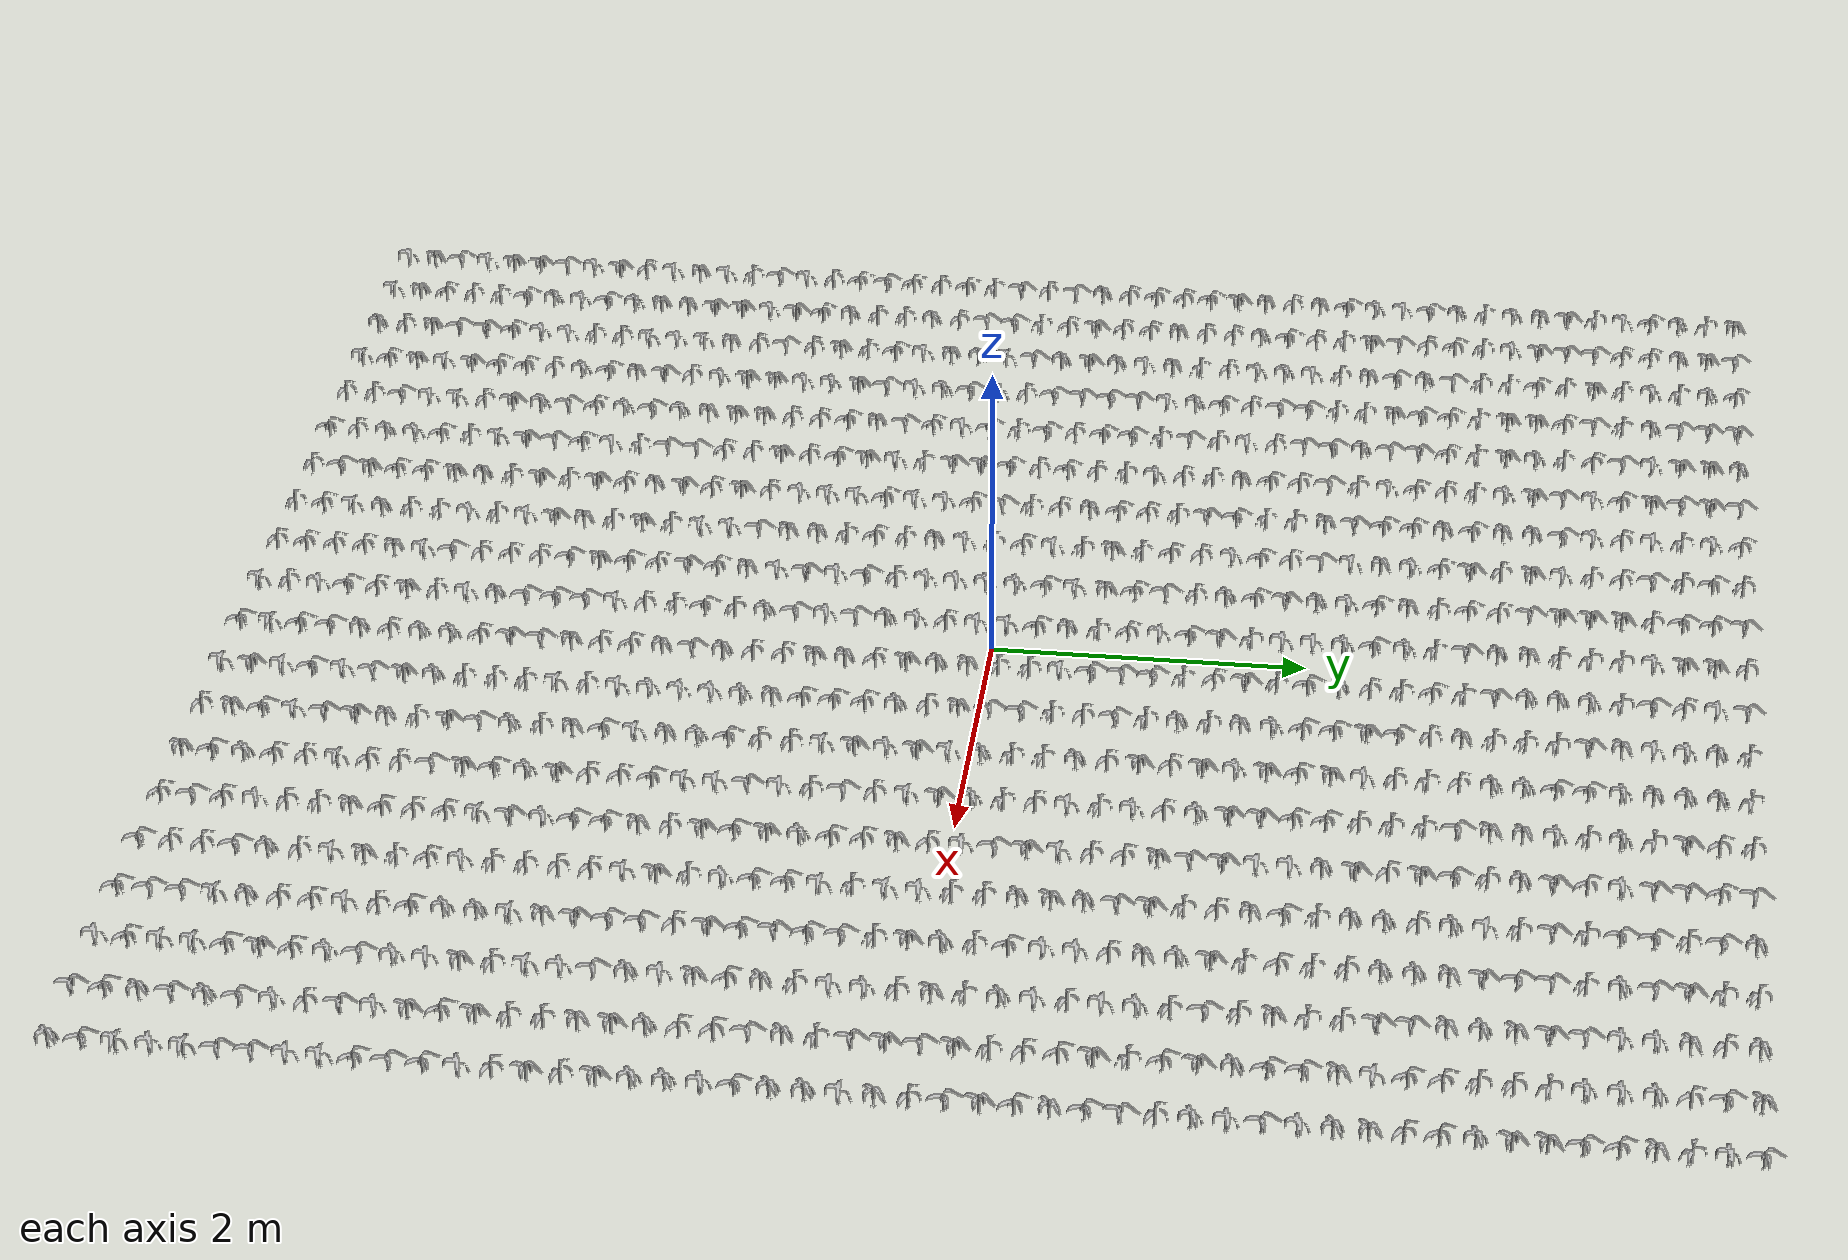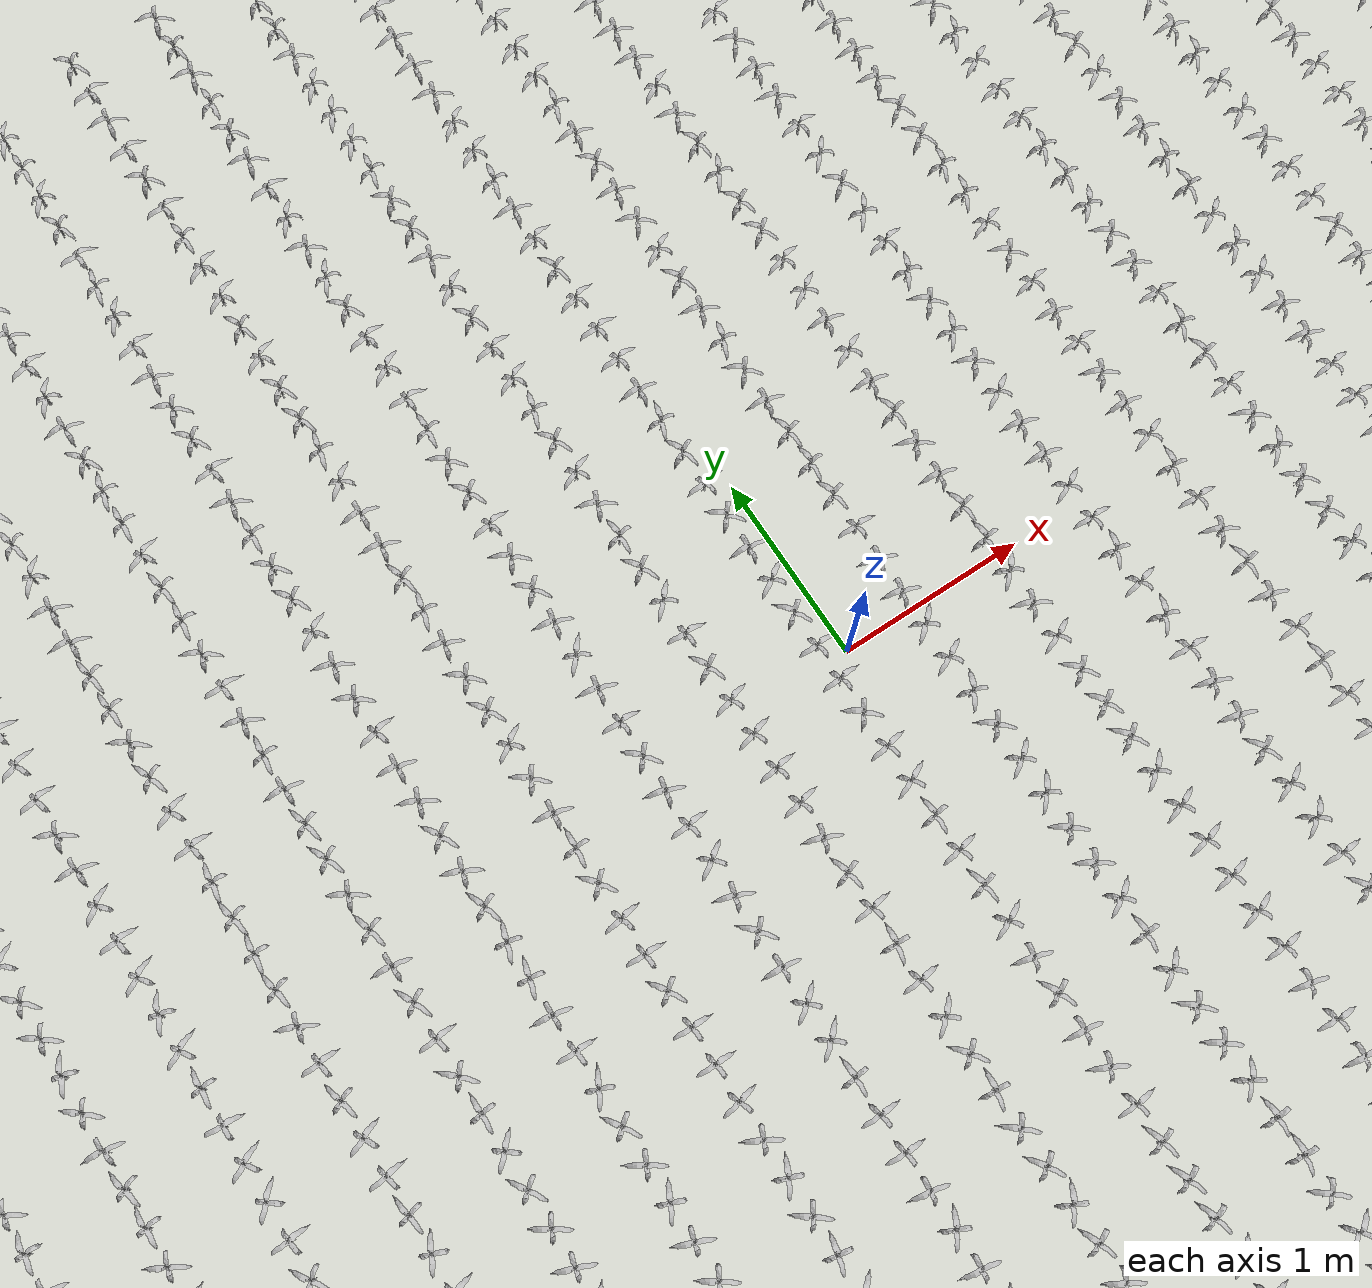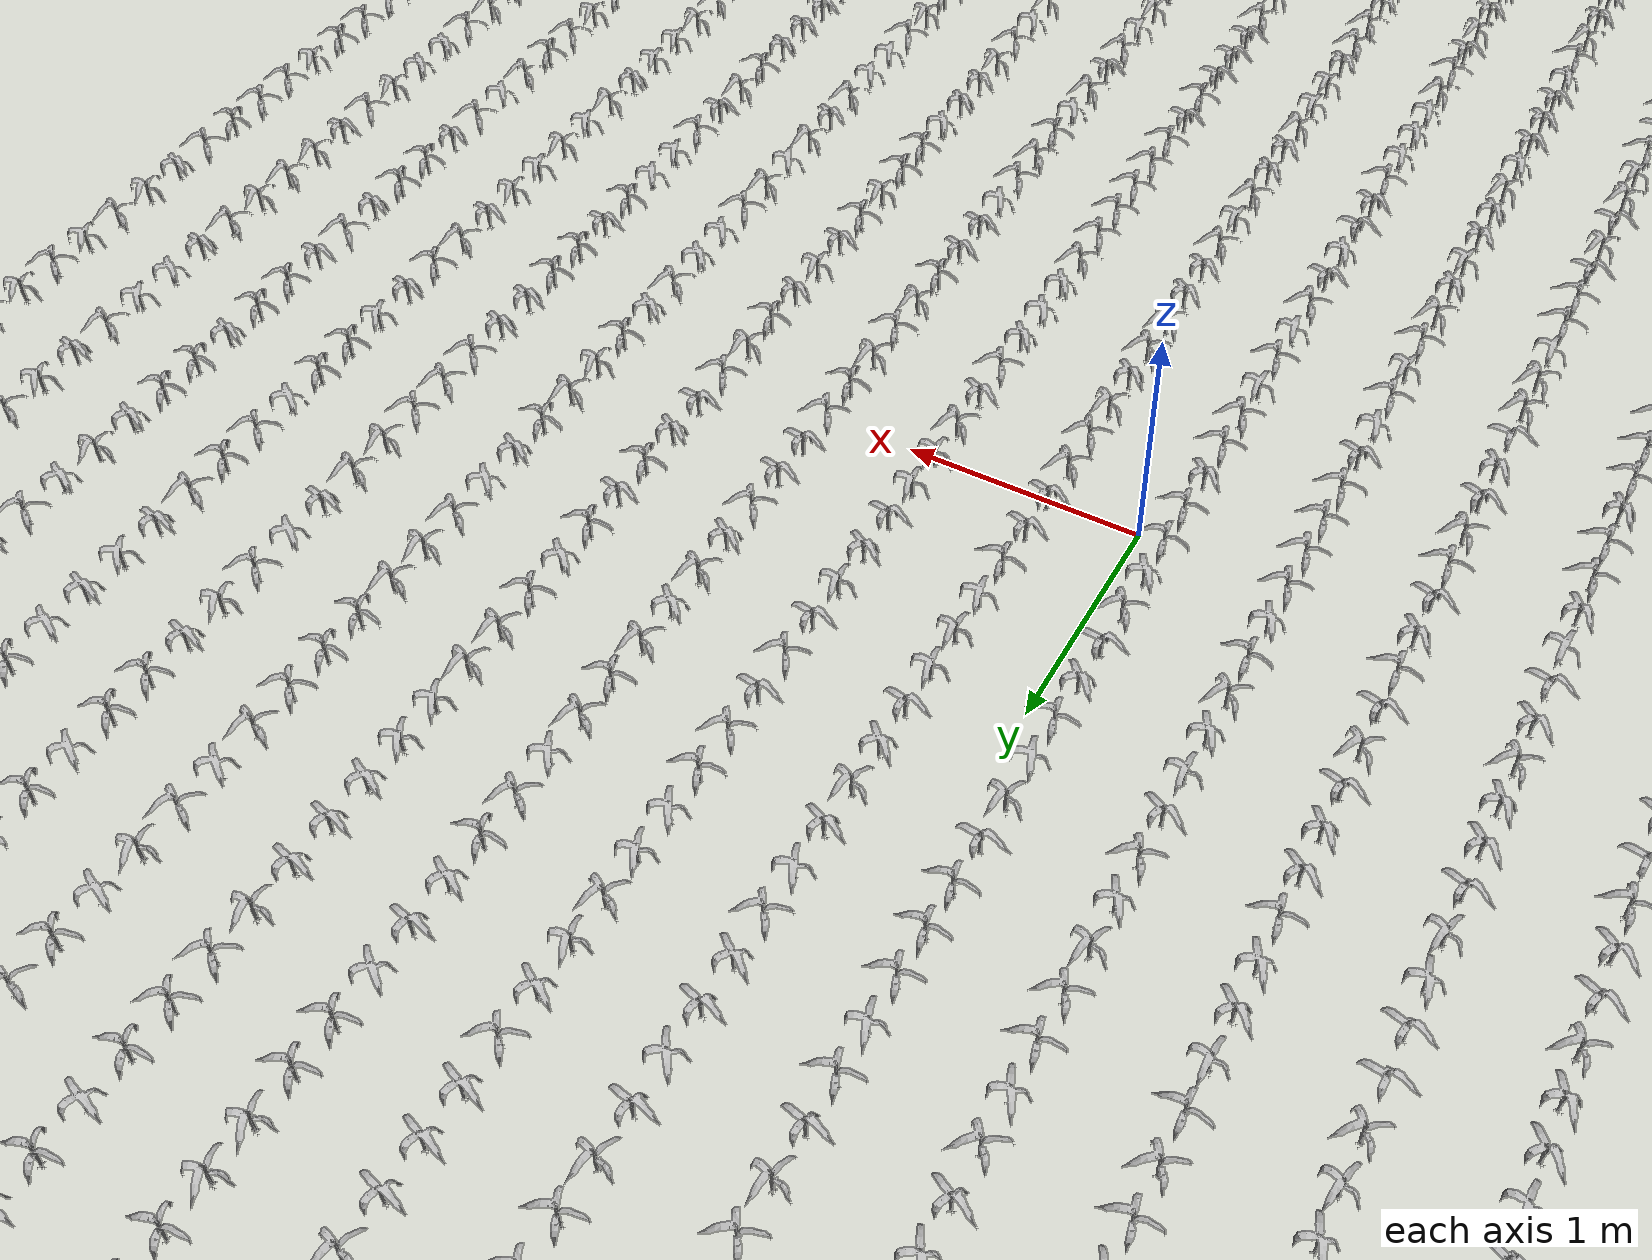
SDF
<sdf version="1.7">
 <world name="default">
  <plugin name="gazebo_ros_state" filename="libgazebo_ros_state.so"><update_rate>1.0</update_rate></plugin>
  <light name="sun" type="directional">
   <pose>0 0 10 0 -0 0</pose>
   <diffuse>0.8 0.8 0.8 1</diffuse>
   <specular>0.2 0.2 0.2 1</specular>
   <attenuation>
    <range>1000</range>
    <constant>0.9</constant>
    <linear>0.01</linear>
    <quadratic>0.001</quadratic>
   </attenuation>
   <direction>-0.5 0.1 -0.9</direction>
   <spot><inner_angle>0</inner_angle><outer_angle>0</outer_angle><falloff>0</falloff></spot>
  </light>
  <scene>
   <sky><clouds><speed>12</speed></clouds></sky>
   <ambient>0.4 0.4 0.4 1</ambient>
   <background>0.7 0.7 0.7 1</background>
   <shadows>1</shadows>
  </scene>
  <physics name="default_physics" default="0" type="ode">
   <ode>
    <solver>
     <type>quick</type>
     <iters>50</iters>
     <sor>1</sor>
     <use_dynamic_moi_rescaling>0</use_dynamic_moi_rescaling>
    </solver>
    <constraints>
     <cfm>0</cfm>
     <erp>0.2</erp>
     <contact_max_correcting_vel>1000</contact_max_correcting_vel>
     <contact_surface_layer>0.001</contact_surface_layer>
    </constraints>
   </ode>
   <max_step_size>0.004</max_step_size>
   <real_time_factor>1</real_time_factor>
   <real_time_update_rate>250</real_time_update_rate>
  </physics>
  <spherical_coordinates>
   <surface_model>EARTH_WGS84</surface_model>
   <latitude_deg>42.6129</latitude_deg>
   <longitude_deg>-5.56566</longitude_deg>
   <elevation>880</elevation>
   <heading_deg>0</heading_deg>
  </spherical_coordinates>
  <gravity>0 0 -9.8066</gravity>
  <magnetic_field>6e-06 2.3e-05 -4.2e-05</magnetic_field>
  <atmosphere type="adiabatic"/>
  <audio><device>default</device></audio>
  <model name="maize_-4.6_-4.8">
   <static>1</static>
   <link name="link">
    <inertial>
     <mass>0.2</mass>
     <inertia>
      <ixx>0.166667</ixx>
      <ixy>0</ixy>
      <ixz>0</ixz>
      <iyy>0.166667</iyy>
      <iyz>0</iyz>
      <izz>0.166667</izz>
     </inertia>
    </inertial>
    <collision name="collision">
     <geometry><mesh><uri>model://corn_3/meshes/corn.dae</uri><scale>0.25 0.25 0.25</scale></mesh></geometry>
     <surface>
      <friction><ode><mu>0</mu><mu2>0</mu2></ode></friction>
      <contact><ode><kp>0</kp><kd>0</kd><max_vel>0</max_vel><min_depth>0.002</min_depth></ode></contact>
     </surface>
    </collision>
    <visual name="visual">
     <geometry><mesh><uri>model://corn_3/meshes/corn.dae</uri><scale>0.25 0.25 0.25</scale></mesh></geometry>
    </visual>
    <velocity_decay><linear>0</linear><angular>0</angular></velocity_decay>
   </link>
   <pose>-4.6 -4.8 0.05 0 -0 0.344692</pose>
  </model>
  <model name="maize_-4.6_-4.6049999999999995">
   <static>1</static>
   <link name="link">
    <inertial>
     <mass>0.2</mass>
     <inertia>
      <ixx>0.166667</ixx>
      <ixy>0</ixy>
      <ixz>0</ixz>
      <iyy>0.166667</iyy>
      <iyz>0</iyz>
      <izz>0.166667</izz>
     </inertia>
    </inertial>
    <collision name="collision">
     <geometry><mesh><uri>model://corn_3/meshes/corn.dae</uri><scale>0.25 0.25 0.25</scale></mesh></geometry>
     <surface>
      <friction><ode><mu>0</mu><mu2>0</mu2></ode></friction>
      <contact><ode><kp>0</kp><kd>0</kd><max_vel>0</max_vel><min_depth>0.002</min_depth></ode></contact>
     </surface>
    </collision>
    <visual name="visual">
     <geometry><mesh><uri>model://corn_3/meshes/corn.dae</uri><scale>0.25 0.25 0.25</scale></mesh></geometry>
    </visual>
    <velocity_decay><linear>0</linear><angular>0</angular></velocity_decay>
   </link>
   <pose>-4.6 -4.605 0.05 0 -0 1.00106</pose>
  </model>
  <model name="maize_-4.6_-4.41">
   <static>1</static>
   <link name="link">
    <inertial>
     <mass>0.2</mass>
     <inertia>
      <ixx>0.166667</ixx>
      <ixy>0</ixy>
      <ixz>0</ixz>
      <iyy>0.166667</iyy>
      <iyz>0</iyz>
      <izz>0.166667</izz>
     </inertia>
    </inertial>
    <collision name="collision">
     <geometry><mesh><uri>model://corn_3/meshes/corn.dae</uri><scale>0.25 0.25 0.25</scale></mesh></geometry>
     <surface>
      <friction><ode><mu>0</mu><mu2>0</mu2></ode></friction>
      <contact><ode><kp>0</kp><kd>0</kd><max_vel>0</max_vel><min_depth>0.002</min_depth></ode></contact>
     </surface>
    </collision>
    <visual name="visual">
     <geometry><mesh><uri>model://corn_3/meshes/corn.dae</uri><scale>0.25 0.25 0.25</scale></mesh></geometry>
    </visual>
    <velocity_decay><linear>0</linear><angular>0</angular></velocity_decay>
   </link>
   <pose>-4.6 -4.41 0.05 0 -0 1.87486</pose>
  </model>
  <model name="maize_-4.6_-4.215">
   <static>1</static>
   <link name="link">
    <inertial>
     <mass>0.2</mass>
     <inertia>
      <ixx>0.166667</ixx>
      <ixy>0</ixy>
      <ixz>0</ixz>
      <iyy>0.166667</iyy>
      <iyz>0</iyz>
      <izz>0.166667</izz>
     </inertia>
    </inertial>
    <collision name="collision">
     <geometry><mesh><uri>model://corn_3/meshes/corn.dae</uri><scale>0.25 0.25 0.25</scale></mesh></geometry>
     <surface>
      <friction><ode><mu>0</mu><mu2>0</mu2></ode></friction>
      <contact><ode><kp>0</kp><kd>0</kd><max_vel>0</max_vel><min_depth>0.002</min_depth></ode></contact>
     </surface>
    </collision>
    <visual name="visual">
     <geometry><mesh><uri>model://corn_3/meshes/corn.dae</uri><scale>0.25 0.25 0.25</scale></mesh></geometry>
    </visual>
    <velocity_decay><linear>0</linear><angular>0</angular></velocity_decay>
   </link>
   <pose>-4.6 -4.215 0.05 0 -0 0.240081</pose>
  </model>
  <model name="maize_-4.6_-4.02">
   <static>1</static>
   <link name="link">
    <inertial>
     <mass>0.2</mass>
     <inertia>
      <ixx>0.166667</ixx>
      <ixy>0</ixy>
      <ixz>0</ixz>
      <iyy>0.166667</iyy>
      <iyz>0</iyz>
      <izz>0.166667</izz>
     </inertia>
    </inertial>
    <collision name="collision">
     <geometry><mesh><uri>model://corn_3/meshes/corn.dae</uri><scale>0.25 0.25 0.25</scale></mesh></geometry>
     <surface>
      <friction><ode><mu>0</mu><mu2>0</mu2></ode></friction>
      <contact><ode><kp>0</kp><kd>0</kd><max_vel>0</max_vel><min_depth>0.002</min_depth></ode></contact>
     </surface>
    </collision>
    <visual name="visual">
     <geometry><mesh><uri>model://corn_3/meshes/corn.dae</uri><scale>0.25 0.25 0.25</scale></mesh></geometry>
    </visual>
    <velocity_decay><linear>0</linear><angular>0</angular></velocity_decay>
   </link>
   <pose>-4.6 -4.02 0.05 0 -0 1.14849</pose>
  </model>
  <model name="maize_-4.6_-3.8249999999999997">
   <static>1</static>
   <link name="link">
    <inertial>
     <mass>0.2</mass>
     <inertia>
      <ixx>0.166667</ixx>
      <ixy>0</ixy>
      <ixz>0</ixz>
      <iyy>0.166667</iyy>
      <iyz>0</iyz>
      <izz>0.166667</izz>
     </inertia>
    </inertial>
    <collision name="collision">
     <geometry><mesh><uri>model://corn_3/meshes/corn.dae</uri><scale>0.25 0.25 0.25</scale></mesh></geometry>
     <surface>
      <friction><ode><mu>0</mu><mu2>0</mu2></ode></friction>
      <contact><ode><kp>0</kp><kd>0</kd><max_vel>0</max_vel><min_depth>0.002</min_depth></ode></contact>
     </surface>
    </collision>
    <visual name="visual">
     <geometry><mesh><uri>model://corn_3/meshes/corn.dae</uri><scale>0.25 0.25 0.25</scale></mesh></geometry>
    </visual>
    <velocity_decay><linear>0</linear><angular>0</angular></velocity_decay>
   </link>
   <pose>-4.6 -3.825 0.05 0 -0 1.35753</pose>
  </model>
  <model name="maize_-4.6_-3.63">
   <static>1</static>
   <link name="link">
    <inertial>
     <mass>0.2</mass>
     <inertia>
      <ixx>0.166667</ixx>
      <ixy>0</ixy>
      <ixz>0</ixz>
      <iyy>0.166667</iyy>
      <iyz>0</iyz>
      <izz>0.166667</izz>
     </inertia>
    </inertial>
    <collision name="collision">
     <geometry><mesh><uri>model://corn_3/meshes/corn.dae</uri><scale>0.25 0.25 0.25</scale></mesh></geometry>
     <surface>
      <friction><ode><mu>0</mu><mu2>0</mu2></ode></friction>
      <contact><ode><kp>0</kp><kd>0</kd><max_vel>0</max_vel><min_depth>0.002</min_depth></ode></contact>
     </surface>
    </collision>
    <visual name="visual">
     <geometry><mesh><uri>model://corn_3/meshes/corn.dae</uri><scale>0.25 0.25 0.25</scale></mesh></geometry>
    </visual>
    <velocity_decay><linear>0</linear><angular>0</angular></velocity_decay>
   </link>
   <pose>-4.6 -3.63 0.05 0 -0 1.73707</pose>
  </model>
  <model name="maize_-4.6_-3.4349999999999996">
   <static>1</static>
   <link name="link">
    <inertial>
     <mass>0.2</mass>
     <inertia>
      <ixx>0.166667</ixx>
      <ixy>0</ixy>
      <ixz>0</ixz>
      <iyy>0.166667</iyy>
      <iyz>0</iyz>
      <izz>0.166667</izz>
     </inertia>
    </inertial>
    <collision name="collision">
     <geometry><mesh><uri>model://corn_3/meshes/corn.dae</uri><scale>0.25 0.25 0.25</scale></mesh></geometry>
     <surface>
      <friction><ode><mu>0</mu><mu2>0</mu2></ode></friction>
      <contact><ode><kp>0</kp><kd>0</kd><max_vel>0</max_vel><min_depth>0.002</min_depth></ode></contact>
     </surface>
    </collision>
    <visual name="visual">
     <geometry><mesh><uri>model://corn_3/meshes/corn.dae</uri><scale>0.25 0.25 0.25</scale></mesh></geometry>
    </visual>
    <velocity_decay><linear>0</linear><angular>0</angular></velocity_decay>
   </link>
   <pose>-4.6 -3.435 0.05 0 -0 0.358034</pose>
  </model>
  <model name="maize_-4.6_-3.2399999999999998">
   <static>1</static>
   <link name="link">
    <inertial>
     <mass>0.2</mass>
     <inertia>
      <ixx>0.166667</ixx>
      <ixy>0</ixy>
      <ixz>0</ixz>
      <iyy>0.166667</iyy>
      <iyz>0</iyz>
      <izz>0.166667</izz>
     </inertia>
    </inertial>
    <collision name="collision">
     <geometry><mesh><uri>model://corn_3/meshes/corn.dae</uri><scale>0.25 0.25 0.25</scale></mesh></geometry>
     <surface>
      <friction><ode><mu>0</mu><mu2>0</mu2></ode></friction>
      <contact><ode><kp>0</kp><kd>0</kd><max_vel>0</max_vel><min_depth>0.002</min_depth></ode></contact>
     </surface>
    </collision>
    <visual name="visual">
     <geometry><mesh><uri>model://corn_3/meshes/corn.dae</uri><scale>0.25 0.25 0.25</scale></mesh></geometry>
    </visual>
    <velocity_decay><linear>0</linear><angular>0</angular></velocity_decay>
   </link>
   <pose>-4.6 -3.24 0.05 0 -0 1.34912</pose>
  </model>
  <model name="maize_-4.6_-3.045">
   <static>1</static>
   <link name="link">
    <inertial>
     <mass>0.2</mass>
     <inertia>
      <ixx>0.166667</ixx>
      <ixy>0</ixy>
      <ixz>0</ixz>
      <iyy>0.166667</iyy>
      <iyz>0</iyz>
      <izz>0.166667</izz>
     </inertia>
    </inertial>
    <collision name="collision">
     <geometry><mesh><uri>model://corn_3/meshes/corn.dae</uri><scale>0.25 0.25 0.25</scale></mesh></geometry>
     <surface>
      <friction><ode><mu>0</mu><mu2>0</mu2></ode></friction>
      <contact><ode><kp>0</kp><kd>0</kd><max_vel>0</max_vel><min_depth>0.002</min_depth></ode></contact>
     </surface>
    </collision>
    <visual name="visual">
     <geometry><mesh><uri>model://corn_3/meshes/corn.dae</uri><scale>0.25 0.25 0.25</scale></mesh></geometry>
    </visual>
    <velocity_decay><linear>0</linear><angular>0</angular></velocity_decay>
   </link>
   <pose>-4.6 -3.045 0.05 0 -0 2.72526</pose>
  </model>
  <model name="maize_-4.6_-2.8499999999999996">
   <static>1</static>
   <link name="link">
    <inertial>
     <mass>0.2</mass>
     <inertia>
      <ixx>0.166667</ixx>
      <ixy>0</ixy>
      <ixz>0</ixz>
      <iyy>0.166667</iyy>
      <iyz>0</iyz>
      <izz>0.166667</izz>
     </inertia>
    </inertial>
    <collision name="collision">
     <geometry><mesh><uri>model://corn_3/meshes/corn.dae</uri><scale>0.25 0.25 0.25</scale></mesh></geometry>
     <surface>
      <friction><ode><mu>0</mu><mu2>0</mu2></ode></friction>
      <contact><ode><kp>0</kp><kd>0</kd><max_vel>0</max_vel><min_depth>0.002</min_depth></ode></contact>
     </surface>
    </collision>
    <visual name="visual">
     <geometry><mesh><uri>model://corn_3/meshes/corn.dae</uri><scale>0.25 0.25 0.25</scale></mesh></geometry>
    </visual>
    <velocity_decay><linear>0</linear><angular>0</angular></velocity_decay>
   </link>
   <pose>-4.6 -2.85 0.05 0 -0 0.193534</pose>
  </model>
  <model name="maize_-4.6_-2.655">
   <static>1</static>
   <link name="link">
    <inertial>
     <mass>0.2</mass>
     <inertia>
      <ixx>0.166667</ixx>
      <ixy>0</ixy>
      <ixz>0</ixz>
      <iyy>0.166667</iyy>
      <iyz>0</iyz>
      <izz>0.166667</izz>
     </inertia>
    </inertial>
    <collision name="collision">
     <geometry><mesh><uri>model://corn_3/meshes/corn.dae</uri><scale>0.25 0.25 0.25</scale></mesh></geometry>
     <surface>
      <friction><ode><mu>0</mu><mu2>0</mu2></ode></friction>
      <contact><ode><kp>0</kp><kd>0</kd><max_vel>0</max_vel><min_depth>0.002</min_depth></ode></contact>
     </surface>
    </collision>
    <visual name="visual">
     <geometry><mesh><uri>model://corn_3/meshes/corn.dae</uri><scale>0.25 0.25 0.25</scale></mesh></geometry>
    </visual>
    <velocity_decay><linear>0</linear><angular>0</angular></velocity_decay>
   </link>
   <pose>-4.6 -2.655 0.05 0 -0 0.942737</pose>
  </model>
  <model name="maize_-4.6_-2.46">
   <static>1</static>
   <link name="link">
    <inertial>
     <mass>0.2</mass>
     <inertia>
      <ixx>0.166667</ixx>
      <ixy>0</ixy>
      <ixz>0</ixz>
      <iyy>0.166667</iyy>
      <iyz>0</iyz>
      <izz>0.166667</izz>
     </inertia>
    </inertial>
    <collision name="collision">
     <geometry><mesh><uri>model://corn_3/meshes/corn.dae</uri><scale>0.25 0.25 0.25</scale></mesh></geometry>
     <surface>
      <friction><ode><mu>0</mu><mu2>0</mu2></ode></friction>
      <contact><ode><kp>0</kp><kd>0</kd><max_vel>0</max_vel><min_depth>0.002</min_depth></ode></contact>
     </surface>
    </collision>
    <visual name="visual">
     <geometry><mesh><uri>model://corn_3/meshes/corn.dae</uri><scale>0.25 0.25 0.25</scale></mesh></geometry>
    </visual>
    <velocity_decay><linear>0</linear><angular>0</angular></velocity_decay>
   </link>
   <pose>-4.6 -2.46 0.05 0 -0 0.155841</pose>
  </model>
  <model name="maize_-4.6_-2.2649999999999997">
   <static>1</static>
   <link name="link">
    <inertial>
     <mass>0.2</mass>
     <inertia>
      <ixx>0.166667</ixx>
      <ixy>0</ixy>
      <ixz>0</ixz>
      <iyy>0.166667</iyy>
      <iyz>0</iyz>
      <izz>0.166667</izz>
     </inertia>
    </inertial>
    <collision name="collision">
     <geometry><mesh><uri>model://corn_3/meshes/corn.dae</uri><scale>0.25 0.25 0.25</scale></mesh></geometry>
     <surface>
      <friction><ode><mu>0</mu><mu2>0</mu2></ode></friction>
      <contact><ode><kp>0</kp><kd>0</kd><max_vel>0</max_vel><min_depth>0.002</min_depth></ode></contact>
     </surface>
    </collision>
    <visual name="visual">
     <geometry><mesh><uri>model://corn_3/meshes/corn.dae</uri><scale>0.25 0.25 0.25</scale></mesh></geometry>
    </visual>
    <velocity_decay><linear>0</linear><angular>0</angular></velocity_decay>
   </link>
   <pose>-4.6 -2.265 0.05 0 -0 3.0832</pose>
  </model>
  <model name="maize_-4.6_-2.07">
   <static>1</static>
   <link name="link">
    <inertial>
     <mass>0.2</mass>
     <inertia>
      <ixx>0.166667</ixx>
      <ixy>0</ixy>
      <ixz>0</ixz>
      <iyy>0.166667</iyy>
      <iyz>0</iyz>
      <izz>0.166667</izz>
     </inertia>
    </inertial>
    <collision name="collision">
     <geometry><mesh><uri>model://corn_3/meshes/corn.dae</uri><scale>0.25 0.25 0.25</scale></mesh></geometry>
     <surface>
      <friction><ode><mu>0</mu><mu2>0</mu2></ode></friction>
      <contact><ode><kp>0</kp><kd>0</kd><max_vel>0</max_vel><min_depth>0.002</min_depth></ode></contact>
     </surface>
    </collision>
    <visual name="visual">
     <geometry><mesh><uri>model://corn_3/meshes/corn.dae</uri><scale>0.25 0.25 0.25</scale></mesh></geometry>
    </visual>
    <velocity_decay><linear>0</linear><angular>0</angular></velocity_decay>
   </link>
   <pose>-4.6 -2.07 0.05 0 -0 1.80875</pose>
  </model>
  <model name="maize_-4.6_-1.8749999999999996">
   <static>1</static>
   <link name="link">
    <inertial>
     <mass>0.2</mass>
     <inertia>
      <ixx>0.166667</ixx>
      <ixy>0</ixy>
      <ixz>0</ixz>
      <iyy>0.166667</iyy>
      <iyz>0</iyz>
      <izz>0.166667</izz>
     </inertia>
    </inertial>
    <collision name="collision">
     <geometry><mesh><uri>model://corn_3/meshes/corn.dae</uri><scale>0.25 0.25 0.25</scale></mesh></geometry>
     <surface>
      <friction><ode><mu>0</mu><mu2>0</mu2></ode></friction>
      <contact><ode><kp>0</kp><kd>0</kd><max_vel>0</max_vel><min_depth>0.002</min_depth></ode></contact>
     </surface>
    </collision>
    <visual name="visual">
     <geometry><mesh><uri>model://corn_3/meshes/corn.dae</uri><scale>0.25 0.25 0.25</scale></mesh></geometry>
    </visual>
    <velocity_decay><linear>0</linear><angular>0</angular></velocity_decay>
   </link>
   <pose>-4.6 -1.875 0.05 0 -0 0.168491</pose>
  </model>
  <model name="maize_-4.6_-1.6799999999999997">
   <static>1</static>
   <link name="link">
    <inertial>
     <mass>0.2</mass>
     <inertia>
      <ixx>0.166667</ixx>
      <ixy>0</ixy>
      <ixz>0</ixz>
      <iyy>0.166667</iyy>
      <iyz>0</iyz>
      <izz>0.166667</izz>
     </inertia>
    </inertial>
    <collision name="collision">
     <geometry><mesh><uri>model://corn_3/meshes/corn.dae</uri><scale>0.25 0.25 0.25</scale></mesh></geometry>
     <surface>
      <friction><ode><mu>0</mu><mu2>0</mu2></ode></friction>
      <contact><ode><kp>0</kp><kd>0</kd><max_vel>0</max_vel><min_depth>0.002</min_depth></ode></contact>
     </surface>
    </collision>
    <visual name="visual">
     <geometry><mesh><uri>model://corn_3/meshes/corn.dae</uri><scale>0.25 0.25 0.25</scale></mesh></geometry>
    </visual>
    <velocity_decay><linear>0</linear><angular>0</angular></velocity_decay>
   </link>
   <pose>-4.6 -1.68 0.05 0 -0 2.83995</pose>
  </model>
  <model name="maize_-4.6_-1.4849999999999999">
   <static>1</static>
   <link name="link">
    <inertial>
     <mass>0.2</mass>
     <inertia>
      <ixx>0.166667</ixx>
      <ixy>0</ixy>
      <ixz>0</ixz>
      <iyy>0.166667</iyy>
      <iyz>0</iyz>
      <izz>0.166667</izz>
     </inertia>
    </inertial>
    <collision name="collision">
     <geometry><mesh><uri>model://corn_3/meshes/corn.dae</uri><scale>0.25 0.25 0.25</scale></mesh></geometry>
     <surface>
      <friction><ode><mu>0</mu><mu2>0</mu2></ode></friction>
      <contact><ode><kp>0</kp><kd>0</kd><max_vel>0</max_vel><min_depth>0.002</min_depth></ode></contact>
     </surface>
    </collision>
    <visual name="visual">
     <geometry><mesh><uri>model://corn_3/meshes/corn.dae</uri><scale>0.25 0.25 0.25</scale></mesh></geometry>
    </visual>
    <velocity_decay><linear>0</linear><angular>0</angular></velocity_decay>
   </link>
   <pose>-4.6 -1.485 0.05 0 -0 2.24824</pose>
  </model>
  <model name="maize_-4.6_-1.2899999999999996">
   <static>1</static>
   <link name="link">
    <inertial>
     <mass>0.2</mass>
     <inertia>
      <ixx>0.166667</ixx>
      <ixy>0</ixy>
      <ixz>0</ixz>
      <iyy>0.166667</iyy>
      <iyz>0</iyz>
      <izz>0.166667</izz>
     </inertia>
    </inertial>
    <collision name="collision">
     <geometry><mesh><uri>model://corn_3/meshes/corn.dae</uri><scale>0.25 0.25 0.25</scale></mesh></geometry>
     <surface>
      <friction><ode><mu>0</mu><mu2>0</mu2></ode></friction>
      <contact><ode><kp>0</kp><kd>0</kd><max_vel>0</max_vel><min_depth>0.002</min_depth></ode></contact>
     </surface>
    </collision>
    <visual name="visual">
     <geometry><mesh><uri>model://corn_3/meshes/corn.dae</uri><scale>0.25 0.25 0.25</scale></mesh></geometry>
    </visual>
    <velocity_decay><linear>0</linear><angular>0</angular></velocity_decay>
   </link>
   <pose>-4.6 -1.29 0.05 0 -0 1.88643</pose>
  </model>
  <model name="maize_-4.6_-1.0949999999999998">
   <static>1</static>
   <link name="link">
    <inertial>
     <mass>0.2</mass>
     <inertia>
      <ixx>0.166667</ixx>
      <ixy>0</ixy>
      <ixz>0</ixz>
      <iyy>0.166667</iyy>
      <iyz>0</iyz>
      <izz>0.166667</izz>
     </inertia>
    </inertial>
    <collision name="collision">
     <geometry><mesh><uri>model://corn_3/meshes/corn.dae</uri><scale>0.25 0.25 0.25</scale></mesh></geometry>
     <surface>
      <friction><ode><mu>0</mu><mu2>0</mu2></ode></friction>
      <contact><ode><kp>0</kp><kd>0</kd><max_vel>0</max_vel><min_depth>0.002</min_depth></ode></contact>
     </surface>
    </collision>
    <visual name="visual">
     <geometry><mesh><uri>model://corn_3/meshes/corn.dae</uri><scale>0.25 0.25 0.25</scale></mesh></geometry>
    </visual>
    <velocity_decay><linear>0</linear><angular>0</angular></velocity_decay>
   </link>
   <pose>-4.6 -1.095 0.05 0 -0 2.37285</pose>
  </model>
  <model name="maize_-4.6_-0.8999999999999995">
   <static>1</static>
   <link name="link">
    <inertial>
     <mass>0.2</mass>
     <inertia>
      <ixx>0.166667</ixx>
      <ixy>0</ixy>
      <ixz>0</ixz>
      <iyy>0.166667</iyy>
      <iyz>0</iyz>
      <izz>0.166667</izz>
     </inertia>
    </inertial>
    <collision name="collision">
     <geometry><mesh><uri>model://corn_3/meshes/corn.dae</uri><scale>0.25 0.25 0.25</scale></mesh></geometry>
     <surface>
      <friction><ode><mu>0</mu><mu2>0</mu2></ode></friction>
      <contact><ode><kp>0</kp><kd>0</kd><max_vel>0</max_vel><min_depth>0.002</min_depth></ode></contact>
     </surface>
    </collision>
    <visual name="visual">
     <geometry><mesh><uri>model://corn_3/meshes/corn.dae</uri><scale>0.25 0.25 0.25</scale></mesh></geometry>
    </visual>
    <velocity_decay><linear>0</linear><angular>0</angular></velocity_decay>
   </link>
   <pose>-4.6 -0.9 0.05 0 -0 2.8089</pose>
  </model>
  <model name="maize_-4.6_-0.7050000000000001">
   <static>1</static>
   <link name="link">
    <inertial>
     <mass>0.2</mass>
     <inertia>
      <ixx>0.166667</ixx>
      <ixy>0</ixy>
      <ixz>0</ixz>
      <iyy>0.166667</iyy>
      <iyz>0</iyz>
      <izz>0.166667</izz>
     </inertia>
    </inertial>
    <collision name="collision">
     <geometry><mesh><uri>model://corn_3/meshes/corn.dae</uri><scale>0.25 0.25 0.25</scale></mesh></geometry>
     <surface>
      <friction><ode><mu>0</mu><mu2>0</mu2></ode></friction>
      <contact><ode><kp>0</kp><kd>0</kd><max_vel>0</max_vel><min_depth>0.002</min_depth></ode></contact>
     </surface>
    </collision>
    <visual name="visual">
     <geometry><mesh><uri>model://corn_3/meshes/corn.dae</uri><scale>0.25 0.25 0.25</scale></mesh></geometry>
    </visual>
    <velocity_decay><linear>0</linear><angular>0</angular></velocity_decay>
   </link>
   <pose>-4.6 -0.705 0.05 0 -0 2.27748</pose>
  </model>
  <model name="maize_-4.6_-0.5099999999999998">
   <static>1</static>
   <link name="link">
    <inertial>
     <mass>0.2</mass>
     <inertia>
      <ixx>0.166667</ixx>
      <ixy>0</ixy>
      <ixz>0</ixz>
      <iyy>0.166667</iyy>
      <iyz>0</iyz>
      <izz>0.166667</izz>
     </inertia>
    </inertial>
    <collision name="collision">
     <geometry><mesh><uri>model://corn_3/meshes/corn.dae</uri><scale>0.25 0.25 0.25</scale></mesh></geometry>
     <surface>
      <friction><ode><mu>0</mu><mu2>0</mu2></ode></friction>
      <contact><ode><kp>0</kp><kd>0</kd><max_vel>0</max_vel><min_depth>0.002</min_depth></ode></contact>
     </surface>
    </collision>
    <visual name="visual">
     <geometry><mesh><uri>model://corn_3/meshes/corn.dae</uri><scale>0.25 0.25 0.25</scale></mesh></geometry>
    </visual>
    <velocity_decay><linear>0</linear><angular>0</angular></velocity_decay>
   </link>
   <pose>-4.6 -0.51 0.05 0 -0 3.13945</pose>
  </model>
  <model name="maize_-4.6_-0.3149999999999995">
   <static>1</static>
   <link name="link">
    <inertial>
     <mass>0.2</mass>
     <inertia>
      <ixx>0.166667</ixx>
      <ixy>0</ixy>
      <ixz>0</ixz>
      <iyy>0.166667</iyy>
      <iyz>0</iyz>
      <izz>0.166667</izz>
     </inertia>
    </inertial>
    <collision name="collision">
     <geometry><mesh><uri>model://corn_3/meshes/corn.dae</uri><scale>0.25 0.25 0.25</scale></mesh></geometry>
     <surface>
      <friction><ode><mu>0</mu><mu2>0</mu2></ode></friction>
      <contact><ode><kp>0</kp><kd>0</kd><max_vel>0</max_vel><min_depth>0.002</min_depth></ode></contact>
     </surface>
    </collision>
    <visual name="visual">
     <geometry><mesh><uri>model://corn_3/meshes/corn.dae</uri><scale>0.25 0.25 0.25</scale></mesh></geometry>
    </visual>
    <velocity_decay><linear>0</linear><angular>0</angular></velocity_decay>
   </link>
   <pose>-4.6 -0.315 0.05 0 -0 1.49172</pose>
  </model>
  <model name="maize_-4.6_-0.1200000000000001">
   <static>1</static>
   <link name="link">
    <inertial>
     <mass>0.2</mass>
     <inertia>
      <ixx>0.166667</ixx>
      <ixy>0</ixy>
      <ixz>0</ixz>
      <iyy>0.166667</iyy>
      <iyz>0</iyz>
      <izz>0.166667</izz>
     </inertia>
    </inertial>
    <collision name="collision">
     <geometry><mesh><uri>model://corn_3/meshes/corn.dae</uri><scale>0.25 0.25 0.25</scale></mesh></geometry>
     <surface>
      <friction><ode><mu>0</mu><mu2>0</mu2></ode></friction>
      <contact><ode><kp>0</kp><kd>0</kd><max_vel>0</max_vel><min_depth>0.002</min_depth></ode></contact>
     </surface>
    </collision>
    <visual name="visual">
     <geometry><mesh><uri>model://corn_3/meshes/corn.dae</uri><scale>0.25 0.25 0.25</scale></mesh></geometry>
    </visual>
    <velocity_decay><linear>0</linear><angular>0</angular></velocity_decay>
   </link>
   <pose>-4.6 -0.12 0.05 0 -0 2.70126</pose>
  </model>
  <model name="maize_-4.6_0.07500000000000018">
   <static>1</static>
   <link name="link">
    <inertial>
     <mass>0.2</mass>
     <inertia>
      <ixx>0.166667</ixx>
      <ixy>0</ixy>
      <ixz>0</ixz>
      <iyy>0.166667</iyy>
      <iyz>0</iyz>
      <izz>0.166667</izz>
     </inertia>
    </inertial>
    <collision name="collision">
     <geometry><mesh><uri>model://corn_3/meshes/corn.dae</uri><scale>0.25 0.25 0.25</scale></mesh></geometry>
     <surface>
      <friction><ode><mu>0</mu><mu2>0</mu2></ode></friction>
      <contact><ode><kp>0</kp><kd>0</kd><max_vel>0</max_vel><min_depth>0.002</min_depth></ode></contact>
     </surface>
    </collision>
    <visual name="visual">
     <geometry><mesh><uri>model://corn_3/meshes/corn.dae</uri><scale>0.25 0.25 0.25</scale></mesh></geometry>
    </visual>
    <velocity_decay><linear>0</linear><angular>0</angular></velocity_decay>
   </link>
   <pose>-4.6 0.075 0.05 0 -0 1.63454</pose>
  </model>
  <model name="maize_-4.6_0.27000000000000046">
   <static>1</static>
   <link name="link">
    <inertial>
     <mass>0.2</mass>
     <inertia>
      <ixx>0.166667</ixx>
      <ixy>0</ixy>
      <ixz>0</ixz>
      <iyy>0.166667</iyy>
      <iyz>0</iyz>
      <izz>0.166667</izz>
     </inertia>
    </inertial>
    <collision name="collision">
     <geometry><mesh><uri>model://corn_3/meshes/corn.dae</uri><scale>0.25 0.25 0.25</scale></mesh></geometry>
     <surface>
      <friction><ode><mu>0</mu><mu2>0</mu2></ode></friction>
      <contact><ode><kp>0</kp><kd>0</kd><max_vel>0</max_vel><min_depth>0.002</min_depth></ode></contact>
     </surface>
    </collision>
    <visual name="visual">
     <geometry><mesh><uri>model://corn_3/meshes/corn.dae</uri><scale>0.25 0.25 0.25</scale></mesh></geometry>
    </visual>
    <velocity_decay><linear>0</linear><angular>0</angular></velocity_decay>
   </link>
   <pose>-4.6 0.27 0.05 0 -0 0.584433</pose>
  </model>
  <model name="maize_-4.6_0.46500000000000075">
   <static>1</static>
   <link name="link">
    <inertial>
     <mass>0.2</mass>
     <inertia>
      <ixx>0.166667</ixx>
      <ixy>0</ixy>
      <ixz>0</ixz>
      <iyy>0.166667</iyy>
      <iyz>0</iyz>
      <izz>0.166667</izz>
     </inertia>
    </inertial>
    <collision name="collision">
     <geometry><mesh><uri>model://corn_3/meshes/corn.dae</uri><scale>0.25 0.25 0.25</scale></mesh></geometry>
     <surface>
      <friction><ode><mu>0</mu><mu2>0</mu2></ode></friction>
      <contact><ode><kp>0</kp><kd>0</kd><max_vel>0</max_vel><min_depth>0.002</min_depth></ode></contact>
     </surface>
    </collision>
    <visual name="visual">
     <geometry><mesh><uri>model://corn_3/meshes/corn.dae</uri><scale>0.25 0.25 0.25</scale></mesh></geometry>
    </visual>
    <velocity_decay><linear>0</linear><angular>0</angular></velocity_decay>
   </link>
   <pose>-4.6 0.465 0.05 0 -0 2.54155</pose>
  </model>
  <model name="maize_-4.6_0.6600000000000001">
   <static>1</static>
   <link name="link">
    <inertial>
     <mass>0.2</mass>
     <inertia>
      <ixx>0.166667</ixx>
      <ixy>0</ixy>
      <ixz>0</ixz>
      <iyy>0.166667</iyy>
      <iyz>0</iyz>
      <izz>0.166667</izz>
     </inertia>
    </inertial>
    <collision name="collision">
     <geometry><mesh><uri>model://corn_3/meshes/corn.dae</uri><scale>0.25 0.25 0.25</scale></mesh></geometry>
     <surface>
      <friction><ode><mu>0</mu><mu2>0</mu2></ode></friction>
      <contact><ode><kp>0</kp><kd>0</kd><max_vel>0</max_vel><min_depth>0.002</min_depth></ode></contact>
     </surface>
    </collision>
    <visual name="visual">
     <geometry><mesh><uri>model://corn_3/meshes/corn.dae</uri><scale>0.25 0.25 0.25</scale></mesh></geometry>
    </visual>
    <velocity_decay><linear>0</linear><angular>0</angular></velocity_decay>
   </link>
   <pose>-4.6 0.66 0.05 0 -0 2.1961</pose>
  </model>
  <model name="maize_-4.6_0.8550000000000004">
   <static>1</static>
   <link name="link">
    <inertial>
     <mass>0.2</mass>
     <inertia>
      <ixx>0.166667</ixx>
      <ixy>0</ixy>
      <ixz>0</ixz>
      <iyy>0.166667</iyy>
      <iyz>0</iyz>
      <izz>0.166667</izz>
     </inertia>
    </inertial>
    <collision name="collision">
     <geometry><mesh><uri>model://corn_3/meshes/corn.dae</uri><scale>0.25 0.25 0.25</scale></mesh></geometry>
     <surface>
      <friction><ode><mu>0</mu><mu2>0</mu2></ode></friction>
      <contact><ode><kp>0</kp><kd>0</kd><max_vel>0</max_vel><min_depth>0.002</min_depth></ode></contact>
     </surface>
    </collision>
    <visual name="visual">
     <geometry><mesh><uri>model://corn_3/meshes/corn.dae</uri><scale>0.25 0.25 0.25</scale></mesh></geometry>
    </visual>
    <velocity_decay><linear>0</linear><angular>0</angular></velocity_decay>
   </link>
   <pose>-4.6 0.855 0.05 0 -0 2.45187</pose>
  </model>
  <model name="maize_-4.6_1.0500000000000007">
   <static>1</static>
   <link name="link">
    <inertial>
     <mass>0.2</mass>
     <inertia>
      <ixx>0.166667</ixx>
      <ixy>0</ixy>
      <ixz>0</ixz>
      <iyy>0.166667</iyy>
      <iyz>0</iyz>
      <izz>0.166667</izz>
     </inertia>
    </inertial>
    <collision name="collision">
     <geometry><mesh><uri>model://corn_3/meshes/corn.dae</uri><scale>0.25 0.25 0.25</scale></mesh></geometry>
     <surface>
      <friction><ode><mu>0</mu><mu2>0</mu2></ode></friction>
      <contact><ode><kp>0</kp><kd>0</kd><max_vel>0</max_vel><min_depth>0.002</min_depth></ode></contact>
     </surface>
    </collision>
    <visual name="visual">
     <geometry><mesh><uri>model://corn_3/meshes/corn.dae</uri><scale>0.25 0.25 0.25</scale></mesh></geometry>
    </visual>
    <velocity_decay><linear>0</linear><angular>0</angular></velocity_decay>
   </link>
   <pose>-4.6 1.05 0.05 0 -0 2.05929</pose>
  </model>
  <model name="maize_-4.6_1.245">
   <static>1</static>
   <link name="link">
    <inertial>
     <mass>0.2</mass>
     <inertia>
      <ixx>0.166667</ixx>
      <ixy>0</ixy>
      <ixz>0</ixz>
      <iyy>0.166667</iyy>
      <iyz>0</iyz>
      <izz>0.166667</izz>
     </inertia>
    </inertial>
    <collision name="collision">
     <geometry><mesh><uri>model://corn_3/meshes/corn.dae</uri><scale>0.25 0.25 0.25</scale></mesh></geometry>
     <surface>
      <friction><ode><mu>0</mu><mu2>0</mu2></ode></friction>
      <contact><ode><kp>0</kp><kd>0</kd><max_vel>0</max_vel><min_depth>0.002</min_depth></ode></contact>
     </surface>
    </collision>
    <visual name="visual">
     <geometry><mesh><uri>model://corn_3/meshes/corn.dae</uri><scale>0.25 0.25 0.25</scale></mesh></geometry>
    </visual>
    <velocity_decay><linear>0</linear><angular>0</angular></velocity_decay>
   </link>
   <pose>-4.6 1.245 0.05 0 -0 1.18665</pose>
  </model>
  <model name="maize_-4.6_1.4400000000000004">
   <static>1</static>
   <link name="link">
    <inertial>
     <mass>0.2</mass>
     <inertia>
      <ixx>0.166667</ixx>
      <ixy>0</ixy>
      <ixz>0</ixz>
      <iyy>0.166667</iyy>
      <iyz>0</iyz>
      <izz>0.166667</izz>
     </inertia>
    </inertial>
    <collision name="collision">
     <geometry><mesh><uri>model://corn_3/meshes/corn.dae</uri><scale>0.25 0.25 0.25</scale></mesh></geometry>
     <surface>
      <friction><ode><mu>0</mu><mu2>0</mu2></ode></friction>
      <contact><ode><kp>0</kp><kd>0</kd><max_vel>0</max_vel><min_depth>0.002</min_depth></ode></contact>
     </surface>
    </collision>
    <visual name="visual">
     <geometry><mesh><uri>model://corn_3/meshes/corn.dae</uri><scale>0.25 0.25 0.25</scale></mesh></geometry>
    </visual>
    <velocity_decay><linear>0</linear><angular>0</angular></velocity_decay>
   </link>
   <pose>-4.6 1.44 0.05 0 -0 0.7282</pose>
  </model>
  <model name="maize_-4.6_1.6350000000000007">
   <static>1</static>
   <link name="link">
    <inertial>
     <mass>0.2</mass>
     <inertia>
      <ixx>0.166667</ixx>
      <ixy>0</ixy>
      <ixz>0</ixz>
      <iyy>0.166667</iyy>
      <iyz>0</iyz>
      <izz>0.166667</izz>
     </inertia>
    </inertial>
    <collision name="collision">
     <geometry><mesh><uri>model://corn_3/meshes/corn.dae</uri><scale>0.25 0.25 0.25</scale></mesh></geometry>
     <surface>
      <friction><ode><mu>0</mu><mu2>0</mu2></ode></friction>
      <contact><ode><kp>0</kp><kd>0</kd><max_vel>0</max_vel><min_depth>0.002</min_depth></ode></contact>
     </surface>
    </collision>
    <visual name="visual">
     <geometry><mesh><uri>model://corn_3/meshes/corn.dae</uri><scale>0.25 0.25 0.25</scale></mesh></geometry>
    </visual>
    <velocity_decay><linear>0</linear><angular>0</angular></velocity_decay>
   </link>
   <pose>-4.6 1.635 0.05 0 -0 2.59609</pose>
  </model>
  <model name="maize_-4.6_1.83">
   <static>1</static>
   <link name="link">
    <inertial>
     <mass>0.2</mass>
     <inertia>
      <ixx>0.166667</ixx>
      <ixy>0</ixy>
      <ixz>0</ixz>
      <iyy>0.166667</iyy>
      <iyz>0</iyz>
      <izz>0.166667</izz>
     </inertia>
    </inertial>
    <collision name="collision">
     <geometry><mesh><uri>model://corn_3/meshes/corn.dae</uri><scale>0.25 0.25 0.25</scale></mesh></geometry>
     <surface>
      <friction><ode><mu>0</mu><mu2>0</mu2></ode></friction>
      <contact><ode><kp>0</kp><kd>0</kd><max_vel>0</max_vel><min_depth>0.002</min_depth></ode></contact>
     </surface>
    </collision>
    <visual name="visual">
     <geometry><mesh><uri>model://corn_3/meshes/corn.dae</uri><scale>0.25 0.25 0.25</scale></mesh></geometry>
    </visual>
    <velocity_decay><linear>0</linear><angular>0</angular></velocity_decay>
   </link>
   <pose>-4.6 1.83 0.05 0 -0 0.608811</pose>
  </model>
  <model name="maize_-4.6_2.0250000000000004">
   <static>1</static>
   <link name="link">
    <inertial>
     <mass>0.2</mass>
     <inertia>
      <ixx>0.166667</ixx>
      <ixy>0</ixy>
      <ixz>0</ixz>
      <iyy>0.166667</iyy>
      <iyz>0</iyz>
      <izz>0.166667</izz>
     </inertia>
    </inertial>
    <collision name="collision">
     <geometry><mesh><uri>model://corn_3/meshes/corn.dae</uri><scale>0.25 0.25 0.25</scale></mesh></geometry>
     <surface>
      <friction><ode><mu>0</mu><mu2>0</mu2></ode></friction>
      <contact><ode><kp>0</kp><kd>0</kd><max_vel>0</max_vel><min_depth>0.002</min_depth></ode></contact>
     </surface>
    </collision>
    <visual name="visual">
     <geometry><mesh><uri>model://corn_3/meshes/corn.dae</uri><scale>0.25 0.25 0.25</scale></mesh></geometry>
    </visual>
    <velocity_decay><linear>0</linear><angular>0</angular></velocity_decay>
   </link>
   <pose>-4.6 2.025 0.05 0 -0 2.03613</pose>
  </model>
  <model name="maize_-4.6_2.2200000000000006">
   <static>1</static>
   <link name="link">
    <inertial>
     <mass>0.2</mass>
     <inertia>
      <ixx>0.166667</ixx>
      <ixy>0</ixy>
      <ixz>0</ixz>
      <iyy>0.166667</iyy>
      <iyz>0</iyz>
      <izz>0.166667</izz>
     </inertia>
    </inertial>
    <collision name="collision">
     <geometry><mesh><uri>model://corn_3/meshes/corn.dae</uri><scale>0.25 0.25 0.25</scale></mesh></geometry>
     <surface>
      <friction><ode><mu>0</mu><mu2>0</mu2></ode></friction>
      <contact><ode><kp>0</kp><kd>0</kd><max_vel>0</max_vel><min_depth>0.002</min_depth></ode></contact>
     </surface>
    </collision>
    <visual name="visual">
     <geometry><mesh><uri>model://corn_3/meshes/corn.dae</uri><scale>0.25 0.25 0.25</scale></mesh></geometry>
    </visual>
    <velocity_decay><linear>0</linear><angular>0</angular></velocity_decay>
   </link>
   <pose>-4.6 2.22 0.05 0 -0 0.292338</pose>
  </model>
  <model name="maize_-4.6_2.415">
   <static>1</static>
   <link name="link">
    <inertial>
     <mass>0.2</mass>
     <inertia>
      <ixx>0.166667</ixx>
      <ixy>0</ixy>
      <ixz>0</ixz>
      <iyy>0.166667</iyy>
      <iyz>0</iyz>
      <izz>0.166667</izz>
     </inertia>
    </inertial>
    <collision name="collision">
     <geometry><mesh><uri>model://corn_3/meshes/corn.dae</uri><scale>0.25 0.25 0.25</scale></mesh></geometry>
     <surface>
      <friction><ode><mu>0</mu><mu2>0</mu2></ode></friction>
      <contact><ode><kp>0</kp><kd>0</kd><max_vel>0</max_vel><min_depth>0.002</min_depth></ode></contact>
     </surface>
    </collision>
    <visual name="visual">
     <geometry><mesh><uri>model://corn_3/meshes/corn.dae</uri><scale>0.25 0.25 0.25</scale></mesh></geometry>
    </visual>
    <velocity_decay><linear>0</linear><angular>0</angular></velocity_decay>
   </link>
   <pose>-4.6 2.415 0.05 0 -0 0.102796</pose>
  </model>
  <model name="maize_-4.6_2.6100000000000003">
   <static>1</static>
   <link name="link">
    <inertial>
     <mass>0.2</mass>
     <inertia>
      <ixx>0.166667</ixx>
      <ixy>0</ixy>
      <ixz>0</ixz>
      <iyy>0.166667</iyy>
      <iyz>0</iyz>
      <izz>0.166667</izz>
     </inertia>
    </inertial>
    <collision name="collision">
     <geometry><mesh><uri>model://corn_3/meshes/corn.dae</uri><scale>0.25 0.25 0.25</scale></mesh></geometry>
     <surface>
      <friction><ode><mu>0</mu><mu2>0</mu2></ode></friction>
      <contact><ode><kp>0</kp><kd>0</kd><max_vel>0</max_vel><min_depth>0.002</min_depth></ode></contact>
     </surface>
    </collision>
    <visual name="visual">
     <geometry><mesh><uri>model://corn_3/meshes/corn.dae</uri><scale>0.25 0.25 0.25</scale></mesh></geometry>
    </visual>
    <velocity_decay><linear>0</linear><angular>0</angular></velocity_decay>
   </link>
   <pose>-4.6 2.61 0.05 0 -0 1.79182</pose>
  </model>
  <model name="maize_-4.6_2.8050000000000006">
   <static>1</static>
   <link name="link">
    <inertial>
     <mass>0.2</mass>
     <inertia>
      <ixx>0.166667</ixx>
      <ixy>0</ixy>
      <ixz>0</ixz>
      <iyy>0.166667</iyy>
      <iyz>0</iyz>
      <izz>0.166667</izz>
     </inertia>
    </inertial>
    <collision name="collision">
     <geometry><mesh><uri>model://corn_3/meshes/corn.dae</uri><scale>0.25 0.25 0.25</scale></mesh></geometry>
     <surface>
      <friction><ode><mu>0</mu><mu2>0</mu2></ode></friction>
      <contact><ode><kp>0</kp><kd>0</kd><max_vel>0</max_vel><min_depth>0.002</min_depth></ode></contact>
     </surface>
    </collision>
    <visual name="visual">
     <geometry><mesh><uri>model://corn_3/meshes/corn.dae</uri><scale>0.25 0.25 0.25</scale></mesh></geometry>
    </visual>
    <velocity_decay><linear>0</linear><angular>0</angular></velocity_decay>
   </link>
   <pose>-4.6 2.805 0.05 0 -0 0.430393</pose>
  </model>
  <model name="maize_-4.6_3.000000000000001">
   <static>1</static>
   <link name="link">
    <inertial>
     <mass>0.2</mass>
     <inertia>
      <ixx>0.166667</ixx>
      <ixy>0</ixy>
      <ixz>0</ixz>
      <iyy>0.166667</iyy>
      <iyz>0</iyz>
      <izz>0.166667</izz>
     </inertia>
    </inertial>
    <collision name="collision">
     <geometry><mesh><uri>model://corn_3/meshes/corn.dae</uri><scale>0.25 0.25 0.25</scale></mesh></geometry>
     <surface>
      <friction><ode><mu>0</mu><mu2>0</mu2></ode></friction>
      <contact><ode><kp>0</kp><kd>0</kd><max_vel>0</max_vel><min_depth>0.002</min_depth></ode></contact>
     </surface>
    </collision>
    <visual name="visual">
     <geometry><mesh><uri>model://corn_3/meshes/corn.dae</uri><scale>0.25 0.25 0.25</scale></mesh></geometry>
    </visual>
    <velocity_decay><linear>0</linear><angular>0</angular></velocity_decay>
   </link>
   <pose>-4.6 3 0.05 0 -0 3.01194</pose>
  </model>
  <model name="maize_-4.6_3.1950000000000003">
   <static>1</static>
   <link name="link">
    <inertial>
     <mass>0.2</mass>
     <inertia>
      <ixx>0.166667</ixx>
      <ixy>0</ixy>
      <ixz>0</ixz>
      <iyy>0.166667</iyy>
      <iyz>0</iyz>
      <izz>0.166667</izz>
     </inertia>
    </inertial>
    <collision name="collision">
     <geometry><mesh><uri>model://corn_3/meshes/corn.dae</uri><scale>0.25 0.25 0.25</scale></mesh></geometry>
     <surface>
      <friction><ode><mu>0</mu><mu2>0</mu2></ode></friction>
      <contact><ode><kp>0</kp><kd>0</kd><max_vel>0</max_vel><min_depth>0.002</min_depth></ode></contact>
     </surface>
    </collision>
    <visual name="visual">
     <geometry><mesh><uri>model://corn_3/meshes/corn.dae</uri><scale>0.25 0.25 0.25</scale></mesh></geometry>
    </visual>
    <velocity_decay><linear>0</linear><angular>0</angular></velocity_decay>
   </link>
   <pose>-4.6 3.195 0.05 0 -0 0.275425</pose>
  </model>
  <model name="maize_-4.6_3.3899999999999997">
   <static>1</static>
   <link name="link">
    <inertial>
     <mass>0.2</mass>
     <inertia>
      <ixx>0.166667</ixx>
      <ixy>0</ixy>
      <ixz>0</ixz>
      <iyy>0.166667</iyy>
      <iyz>0</iyz>
      <izz>0.166667</izz>
     </inertia>
    </inertial>
    <collision name="collision">
     <geometry><mesh><uri>model://corn_3/meshes/corn.dae</uri><scale>0.25 0.25 0.25</scale></mesh></geometry>
     <surface>
      <friction><ode><mu>0</mu><mu2>0</mu2></ode></friction>
      <contact><ode><kp>0</kp><kd>0</kd><max_vel>0</max_vel><min_depth>0.002</min_depth></ode></contact>
     </surface>
    </collision>
    <visual name="visual">
     <geometry><mesh><uri>model://corn_3/meshes/corn.dae</uri><scale>0.25 0.25 0.25</scale></mesh></geometry>
    </visual>
    <velocity_decay><linear>0</linear><angular>0</angular></velocity_decay>
   </link>
   <pose>-4.6 3.39 0.05 0 -0 0.641586</pose>
  </model>
  <model name="maize_-4.6_3.585">
   <static>1</static>
   <link name="link">
    <inertial>
     <mass>0.2</mass>
     <inertia>
      <ixx>0.166667</ixx>
      <ixy>0</ixy>
      <ixz>0</ixz>
      <iyy>0.166667</iyy>
      <iyz>0</iyz>
      <izz>0.166667</izz>
     </inertia>
    </inertial>
    <collision name="collision">
     <geometry><mesh><uri>model://corn_3/meshes/corn.dae</uri><scale>0.25 0.25 0.25</scale></mesh></geometry>
     <surface>
      <friction><ode><mu>0</mu><mu2>0</mu2></ode></friction>
      <contact><ode><kp>0</kp><kd>0</kd><max_vel>0</max_vel><min_depth>0.002</min_depth></ode></contact>
     </surface>
    </collision>
    <visual name="visual">
     <geometry><mesh><uri>model://corn_3/meshes/corn.dae</uri><scale>0.25 0.25 0.25</scale></mesh></geometry>
    </visual>
    <velocity_decay><linear>0</linear><angular>0</angular></velocity_decay>
   </link>
   <pose>-4.6 3.585 0.05 0 -0 1.2305</pose>
  </model>
  <model name="maize_-4.6_3.7800000000000002">
   <static>1</static>
   <link name="link">
    <inertial>
     <mass>0.2</mass>
     <inertia>
      <ixx>0.166667</ixx>
      <ixy>0</ixy>
      <ixz>0</ixz>
      <iyy>0.166667</iyy>
      <iyz>0</iyz>
      <izz>0.166667</izz>
     </inertia>
    </inertial>
    <collision name="collision">
     <geometry><mesh><uri>model://corn_3/meshes/corn.dae</uri><scale>0.25 0.25 0.25</scale></mesh></geometry>
     <surface>
      <friction><ode><mu>0</mu><mu2>0</mu2></ode></friction>
      <contact><ode><kp>0</kp><kd>0</kd><max_vel>0</max_vel><min_depth>0.002</min_depth></ode></contact>
     </surface>
    </collision>
    <visual name="visual">
     <geometry><mesh><uri>model://corn_3/meshes/corn.dae</uri><scale>0.25 0.25 0.25</scale></mesh></geometry>
    </visual>
    <velocity_decay><linear>0</linear><angular>0</angular></velocity_decay>
   </link>
   <pose>-4.6 3.78 0.05 0 -0 3.0599</pose>
  </model>
  <model name="maize_-4.6_3.9750000000000005">
   <static>1</static>
   <link name="link">
    <inertial>
     <mass>0.2</mass>
     <inertia>
      <ixx>0.166667</ixx>
      <ixy>0</ixy>
      <ixz>0</ixz>
      <iyy>0.166667</iyy>
      <iyz>0</iyz>
      <izz>0.166667</izz>
     </inertia>
    </inertial>
    <collision name="collision">
     <geometry><mesh><uri>model://corn_3/meshes/corn.dae</uri><scale>0.25 0.25 0.25</scale></mesh></geometry>
     <surface>
      <friction><ode><mu>0</mu><mu2>0</mu2></ode></friction>
      <contact><ode><kp>0</kp><kd>0</kd><max_vel>0</max_vel><min_depth>0.002</min_depth></ode></contact>
     </surface>
    </collision>
    <visual name="visual">
     <geometry><mesh><uri>model://corn_3/meshes/corn.dae</uri><scale>0.25 0.25 0.25</scale></mesh></geometry>
    </visual>
    <velocity_decay><linear>0</linear><angular>0</angular></velocity_decay>
   </link>
   <pose>-4.6 3.975 0.05 0 -0 0.019402</pose>
  </model>
  <model name="maize_-4.6_4.170000000000001">
   <static>1</static>
   <link name="link">
    <inertial>
     <mass>0.2</mass>
     <inertia>
      <ixx>0.166667</ixx>
      <ixy>0</ixy>
      <ixz>0</ixz>
      <iyy>0.166667</iyy>
      <iyz>0</iyz>
      <izz>0.166667</izz>
     </inertia>
    </inertial>
    <collision name="collision">
     <geometry><mesh><uri>model://corn_3/meshes/corn.dae</uri><scale>0.25 0.25 0.25</scale></mesh></geometry>
     <surface>
      <friction><ode><mu>0</mu><mu2>0</mu2></ode></friction>
      <contact><ode><kp>0</kp><kd>0</kd><max_vel>0</max_vel><min_depth>0.002</min_depth></ode></contact>
     </surface>
    </collision>
    <visual name="visual">
     <geometry><mesh><uri>model://corn_3/meshes/corn.dae</uri><scale>0.25 0.25 0.25</scale></mesh></geometry>
    </visual>
    <velocity_decay><linear>0</linear><angular>0</angular></velocity_decay>
   </link>
   <pose>-4.6 4.17 0.05 0 -0 2.08204</pose>
  </model>
  <model name="maize_-4.6_4.365000000000001">
   <static>1</static>
   <link name="link">
    <inertial>
     <mass>0.2</mass>
     <inertia>
      <ixx>0.166667</ixx>
      <ixy>0</ixy>
      <ixz>0</ixz>
      <iyy>0.166667</iyy>
      <iyz>0</iyz>
      <izz>0.166667</izz>
     </inertia>
    </inertial>
    <collision name="collision">
     <geometry><mesh><uri>model://corn_3/meshes/corn.dae</uri><scale>0.25 0.25 0.25</scale></mesh></geometry>
     <surface>
      <friction><ode><mu>0</mu><mu2>0</mu2></ode></friction>
      <contact><ode><kp>0</kp><kd>0</kd><max_vel>0</max_vel><min_depth>0.002</min_depth></ode></contact>
     </surface>
    </collision>
    <visual name="visual">
     <geometry><mesh><uri>model://corn_3/meshes/corn.dae</uri><scale>0.25 0.25 0.25</scale></mesh></geometry>
    </visual>
    <velocity_decay><linear>0</linear><angular>0</angular></velocity_decay>
   </link>
   <pose>-4.6 4.365 0.05 0 -0 0.353595</pose>
  </model>
  <model name="maize_-4.6_4.56">
   <static>1</static>
   <link name="link">
    <inertial>
     <mass>0.2</mass>
     <inertia>
      <ixx>0.166667</ixx>
      <ixy>0</ixy>
      <ixz>0</ixz>
      <iyy>0.166667</iyy>
      <iyz>0</iyz>
      <izz>0.166667</izz>
     </inertia>
    </inertial>
    <collision name="collision">
     <geometry><mesh><uri>model://corn_3/meshes/corn.dae</uri><scale>0.25 0.25 0.25</scale></mesh></geometry>
     <surface>
      <friction><ode><mu>0</mu><mu2>0</mu2></ode></friction>
      <contact><ode><kp>0</kp><kd>0</kd><max_vel>0</max_vel><min_depth>0.002</min_depth></ode></contact>
     </surface>
    </collision>
    <visual name="visual">
     <geometry><mesh><uri>model://corn_3/meshes/corn.dae</uri><scale>0.25 0.25 0.25</scale></mesh></geometry>
    </visual>
    <velocity_decay><linear>0</linear><angular>0</angular></velocity_decay>
   </link>
   <pose>-4.6 4.56 0.05 0 -0 3.13578</pose>
  </model>
  <model name="maize_-4.6_4.755">
   <static>1</static>
   <link name="link">
    <inertial>
     <mass>0.2</mass>
     <inertia>
      <ixx>0.166667</ixx>
      <ixy>0</ixy>
      <ixz>0</ixz>
      <iyy>0.166667</iyy>
      <iyz>0</iyz>
      <izz>0.166667</izz>
     </inertia>
    </inertial>
    <collision name="collision">
     <geometry><mesh><uri>model://corn_3/meshes/corn.dae</uri><scale>0.25 0.25 0.25</scale></mesh></geometry>
     <surface>
      <friction><ode><mu>0</mu><mu2>0</mu2></ode></friction>
      <contact><ode><kp>0</kp><kd>0</kd><max_vel>0</max_vel><min_depth>0.002</min_depth></ode></contact>
     </surface>
    </collision>
    <visual name="visual">
     <geometry><mesh><uri>model://corn_3/meshes/corn.dae</uri><scale>0.25 0.25 0.25</scale></mesh></geometry>
    </visual>
    <velocity_decay><linear>0</linear><angular>0</angular></velocity_decay>
   </link>
   <pose>-4.6 4.755 0.05 0 -0 0.784792</pose>
  </model>
  <model name="maize_-4.100375_-4.8">
   <static>1</static>
   <link name="link">
    <inertial>
     <mass>0.2</mass>
     <inertia>
      <ixx>0.166667</ixx>
      <ixy>0</ixy>
      <ixz>0</ixz>
      <iyy>0.166667</iyy>
      <iyz>0</iyz>
      <izz>0.166667</izz>
     </inertia>
    </inertial>
    <collision name="collision">
     <geometry><mesh><uri>model://corn_3/meshes/corn.dae</uri><scale>0.25 0.25 0.25</scale></mesh></geometry>
     <surface>
      <friction><ode><mu>0</mu><mu2>0</mu2></ode></friction>
      <contact><ode><kp>0</kp><kd>0</kd><max_vel>0</max_vel><min_depth>0.002</min_depth></ode></contact>
     </surface>
    </collision>
    <visual name="visual">
     <geometry><mesh><uri>model://corn_3/meshes/corn.dae</uri><scale>0.25 0.25 0.25</scale></mesh></geometry>
    </visual>
    <velocity_decay><linear>0</linear><angular>0</angular></velocity_decay>
   </link>
   <pose>-4.10037 -4.8 0.05 0 -0 0.133593</pose>
  </model>
  <model name="maize_-4.100375_-4.6049999999999995">
   <static>1</static>
   <link name="link">
    <inertial>
     <mass>0.2</mass>
     <inertia>
      <ixx>0.166667</ixx>
      <ixy>0</ixy>
      <ixz>0</ixz>
      <iyy>0.166667</iyy>
      <iyz>0</iyz>
      <izz>0.166667</izz>
     </inertia>
    </inertial>
    <collision name="collision">
     <geometry><mesh><uri>model://corn_3/meshes/corn.dae</uri><scale>0.25 0.25 0.25</scale></mesh></geometry>
     <surface>
      <friction><ode><mu>0</mu><mu2>0</mu2></ode></friction>
      <contact><ode><kp>0</kp><kd>0</kd><max_vel>0</max_vel><min_depth>0.002</min_depth></ode></contact>
     </surface>
    </collision>
    <visual name="visual">
     <geometry><mesh><uri>model://corn_3/meshes/corn.dae</uri><scale>0.25 0.25 0.25</scale></mesh></geometry>
    </visual>
    <velocity_decay><linear>0</linear><angular>0</angular></velocity_decay>
   </link>
   <pose>-4.10037 -4.605 0.05 0 -0 1.03842</pose>
  </model>
  <model name="maize_-4.100375_-4.41">
   <static>1</static>
   <link name="link">
    <inertial>
     <mass>0.2</mass>
     <inertia>
      <ixx>0.166667</ixx>
      <ixy>0</ixy>
      <ixz>0</ixz>
      <iyy>0.166667</iyy>
      <iyz>0</iyz>
      <izz>0.166667</izz>
     </inertia>
    </inertial>
    <collision name="collision">
     <geometry><mesh><uri>model://corn_3/meshes/corn.dae</uri><scale>0.25 0.25 0.25</scale></mesh></geometry>
     <surface>
      <friction><ode><mu>0</mu><mu2>0</mu2></ode></friction>
      <contact><ode><kp>0</kp><kd>0</kd><max_vel>0</max_vel><min_depth>0.002</min_depth></ode></contact>
     </surface>
    </collision>
    <visual name="visual">
     <geometry><mesh><uri>model://corn_3/meshes/corn.dae</uri><scale>0.25 0.25 0.25</scale></mesh></geometry>
    </visual>
    <velocity_decay><linear>0</linear><angular>0</angular></velocity_decay>
   </link>
   <pose>-4.10037 -4.41 0.05 0 -0 2.53651</pose>
  </model>
  <model name="maize_-4.100375_-4.215">
   <static>1</static>
   <link name="link">
    <inertial>
     <mass>0.2</mass>
     <inertia>
      <ixx>0.166667</ixx>
      <ixy>0</ixy>
      <ixz>0</ixz>
      <iyy>0.166667</iyy>
      <iyz>0</iyz>
      <izz>0.166667</izz>
     </inertia>
    </inertial>
    <collision name="collision">
     <geometry><mesh><uri>model://corn_3/meshes/corn.dae</uri><scale>0.25 0.25 0.25</scale></mesh></geometry>
     <surface>
      <friction><ode><mu>0</mu><mu2>0</mu2></ode></friction>
      <contact><ode><kp>0</kp><kd>0</kd><max_vel>0</max_vel><min_depth>0.002</min_depth></ode></contact>
     </surface>
    </collision>
    <visual name="visual">
     <geometry><mesh><uri>model://corn_3/meshes/corn.dae</uri><scale>0.25 0.25 0.25</scale></mesh></geometry>
    </visual>
    <velocity_decay><linear>0</linear><angular>0</angular></velocity_decay>
   </link>
   <pose>-4.10037 -4.215 0.05 0 -0 2.95263</pose>
  </model>
  <model name="maize_-4.100375_-4.02">
   <static>1</static>
   <link name="link">
    <inertial>
     <mass>0.2</mass>
     <inertia>
      <ixx>0.166667</ixx>
      <ixy>0</ixy>
      <ixz>0</ixz>
      <iyy>0.166667</iyy>
      <iyz>0</iyz>
      <izz>0.166667</izz>
     </inertia>
    </inertial>
    <collision name="collision">
     <geometry><mesh><uri>model://corn_3/meshes/corn.dae</uri><scale>0.25 0.25 0.25</scale></mesh></geometry>
     <surface>
      <friction><ode><mu>0</mu><mu2>0</mu2></ode></friction>
      <contact><ode><kp>0</kp><kd>0</kd><max_vel>0</max_vel><min_depth>0.002</min_depth></ode></contact>
     </surface>
    </collision>
    <visual name="visual">
     <geometry><mesh><uri>model://corn_3/meshes/corn.dae</uri><scale>0.25 0.25 0.25</scale></mesh></geometry>
    </visual>
    <velocity_decay><linear>0</linear><angular>0</angular></velocity_decay>
   </link>
   <pose>-4.10037 -4.02 0.05 0 -0 3.13382</pose>
  </model>
  <model name="maize_-4.100375_-3.8249999999999997">
   <static>1</static>
   <link name="link">
    <inertial>
     <mass>0.2</mass>
     <inertia>
      <ixx>0.166667</ixx>
      <ixy>0</ixy>
      <ixz>0</ixz>
      <iyy>0.166667</iyy>
      <iyz>0</iyz>
      <izz>0.166667</izz>
     </inertia>
    </inertial>
    <collision name="collision">
     <geometry><mesh><uri>model://corn_3/meshes/corn.dae</uri><scale>0.25 0.25 0.25</scale></mesh></geometry>
     <surface>
      <friction><ode><mu>0</mu><mu2>0</mu2></ode></friction>
      <contact><ode><kp>0</kp><kd>0</kd><max_vel>0</max_vel><min_depth>0.002</min_depth></ode></contact>
     </surface>
    </collision>
    <visual name="visual">
     <geometry><mesh><uri>model://corn_3/meshes/corn.dae</uri><scale>0.25 0.25 0.25</scale></mesh></geometry>
    </visual>
    <velocity_decay><linear>0</linear><angular>0</angular></velocity_decay>
   </link>
   <pose>-4.10037 -3.825 0.05 0 -0 2.07367</pose>
  </model>
  <model name="maize_-4.100375_-3.63">
   <static>1</static>
   <link name="link">
    <inertial>
     <mass>0.2</mass>
     <inertia>
      <ixx>0.166667</ixx>
      <ixy>0</ixy>
      <ixz>0</ixz>
      <iyy>0.166667</iyy>
      <iyz>0</iyz>
      <izz>0.166667</izz>
     </inertia>
    </inertial>
    <collision name="collision">
     <geometry><mesh><uri>model://corn_3/meshes/corn.dae</uri><scale>0.25 0.25 0.25</scale></mesh></geometry>
     <surface>
      <friction><ode><mu>0</mu><mu2>0</mu2></ode></friction>
      <contact><ode><kp>0</kp><kd>0</kd><max_vel>0</max_vel><min_depth>0.002</min_depth></ode></contact>
     </surface>
    </collision>
    <visual name="visual">
     <geometry><mesh><uri>model://corn_3/meshes/corn.dae</uri><scale>0.25 0.25 0.25</scale></mesh></geometry>
    </visual>
    <velocity_decay><linear>0</linear><angular>0</angular></velocity_decay>
   </link>
   <pose>-4.10037 -3.63 0.05 0 -0 0.581346</pose>
  </model>
  <model name="maize_-4.100375_-3.4349999999999996">
   <static>1</static>
   <link name="link">
    <inertial>
     <mass>0.2</mass>
     <inertia>
      <ixx>0.166667</ixx>
      <ixy>0</ixy>
      <ixz>0</ixz>
      <iyy>0.166667</iyy>
      <iyz>0</iyz>
      <izz>0.166667</izz>
     </inertia>
    </inertial>
    <collision name="collision">
     <geometry><mesh><uri>model://corn_3/meshes/corn.dae</uri><scale>0.25 0.25 0.25</scale></mesh></geometry>
     <surface>
      <friction><ode><mu>0</mu><mu2>0</mu2></ode></friction>
      <contact><ode><kp>0</kp><kd>0</kd><max_vel>0</max_vel><min_depth>0.002</min_depth></ode></contact>
     </surface>
    </collision>
    <visual name="visual">
     <geometry><mesh><uri>model://corn_3/meshes/corn.dae</uri><scale>0.25 0.25 0.25</scale></mesh></geometry>
    </visual>
    <velocity_decay><linear>0</linear><angular>0</angular></velocity_decay>
   </link>
   <pose>-4.10037 -3.435 0.05 0 -0 0.344852</pose>
  </model>
  <model name="maize_-4.100375_-3.2399999999999998">
   <static>1</static>
   <link name="link">
    <inertial>
     <mass>0.2</mass>
     <inertia>
      <ixx>0.166667</ixx>
      <ixy>0</ixy>
      <ixz>0</ixz>
      <iyy>0.166667</iyy>
      <iyz>0</iyz>
      <izz>0.166667</izz>
     </inertia>
    </inertial>
    <collision name="collision">
     <geometry><mesh><uri>model://corn_3/meshes/corn.dae</uri><scale>0.25 0.25 0.25</scale></mesh></geometry>
     <surface>
      <friction><ode><mu>0</mu><mu2>0</mu2></ode></friction>
      <contact><ode><kp>0</kp><kd>0</kd><max_vel>0</max_vel><min_depth>0.002</min_depth></ode></contact>
     </surface>
    </collision>
    <visual name="visual">
     <geometry><mesh><uri>model://corn_3/meshes/corn.dae</uri><scale>0.25 0.25 0.25</scale></mesh></geometry>
    </visual>
    <velocity_decay><linear>0</linear><angular>0</angular></velocity_decay>
   </link>
   <pose>-4.10037 -3.24 0.05 0 -0 1.99271</pose>
  </model>
  <model name="maize_-4.100375_-3.045">
   <static>1</static>
   <link name="link">
    <inertial>
     <mass>0.2</mass>
     <inertia>
      <ixx>0.166667</ixx>
      <ixy>0</ixy>
      <ixz>0</ixz>
      <iyy>0.166667</iyy>
      <iyz>0</iyz>
      <izz>0.166667</izz>
     </inertia>
    </inertial>
    <collision name="collision">
     <geometry><mesh><uri>model://corn_3/meshes/corn.dae</uri><scale>0.25 0.25 0.25</scale></mesh></geometry>
     <surface>
      <friction><ode><mu>0</mu><mu2>0</mu2></ode></friction>
      <contact><ode><kp>0</kp><kd>0</kd><max_vel>0</max_vel><min_depth>0.002</min_depth></ode></contact>
     </surface>
    </collision>
    <visual name="visual">
     <geometry><mesh><uri>model://corn_3/meshes/corn.dae</uri><scale>0.25 0.25 0.25</scale></mesh></geometry>
    </visual>
    <velocity_decay><linear>0</linear><angular>0</angular></velocity_decay>
   </link>
   <pose>-4.10037 -3.045 0.05 0 -0 0.511413</pose>
  </model>
  <model name="maize_-4.100375_-2.8499999999999996">
   <static>1</static>
   <link name="link">
    <inertial>
     <mass>0.2</mass>
     <inertia>
      <ixx>0.166667</ixx>
      <ixy>0</ixy>
      <ixz>0</ixz>
      <iyy>0.166667</iyy>
      <iyz>0</iyz>
      <izz>0.166667</izz>
     </inertia>
    </inertial>
    <collision name="collision">
     <geometry><mesh><uri>model://corn_3/meshes/corn.dae</uri><scale>0.25 0.25 0.25</scale></mesh></geometry>
     <surface>
      <friction><ode><mu>0</mu><mu2>0</mu2></ode></friction>
      <contact><ode><kp>0</kp><kd>0</kd><max_vel>0</max_vel><min_depth>0.002</min_depth></ode></contact>
     </surface>
    </collision>
    <visual name="visual">
     <geometry><mesh><uri>model://corn_3/meshes/corn.dae</uri><scale>0.25 0.25 0.25</scale></mesh></geometry>
    </visual>
    <velocity_decay><linear>0</linear><angular>0</angular></velocity_decay>
   </link>
   <pose>-4.10037 -2.85 0.05 0 -0 0.954288</pose>
  </model>
  <model name="maize_-4.100375_-2.655">
   <static>1</static>
   <link name="link">
    <inertial>
     <mass>0.2</mass>
     <inertia>
      <ixx>0.166667</ixx>
      <ixy>0</ixy>
      <ixz>0</ixz>
      <iyy>0.166667</iyy>
      <iyz>0</iyz>
      <izz>0.166667</izz>
     </inertia>
    </inertial>
    <collision name="collision">
     <geometry><mesh><uri>model://corn_3/meshes/corn.dae</uri><scale>0.25 0.25 0.25</scale></mesh></geometry>
     <surface>
      <friction><ode><mu>0</mu><mu2>0</mu2></ode></friction>
      <contact><ode><kp>0</kp><kd>0</kd><max_vel>0</max_vel><min_depth>0.002</min_depth></ode></contact>
     </surface>
    </collision>
    <visual name="visual">
     <geometry><mesh><uri>model://corn_3/meshes/corn.dae</uri><scale>0.25 0.25 0.25</scale></mesh></geometry>
    </visual>
    <velocity_decay><linear>0</linear><angular>0</angular></velocity_decay>
   </link>
   <pose>-4.10037 -2.655 0.05 0 -0 0.736353</pose>
  </model>
  <model name="maize_-4.100375_-2.46">
   <static>1</static>
   <link name="link">
    <inertial>
     <mass>0.2</mass>
     <inertia>
      <ixx>0.166667</ixx>
      <ixy>0</ixy>
      <ixz>0</ixz>
      <iyy>0.166667</iyy>
      <iyz>0</iyz>
      <izz>0.166667</izz>
     </inertia>
    </inertial>
    <collision name="collision">
     <geometry><mesh><uri>model://corn_3/meshes/corn.dae</uri><scale>0.25 0.25 0.25</scale></mesh></geometry>
     <surface>
      <friction><ode><mu>0</mu><mu2>0</mu2></ode></friction>
      <contact><ode><kp>0</kp><kd>0</kd><max_vel>0</max_vel><min_depth>0.002</min_depth></ode></contact>
     </surface>
    </collision>
    <visual name="visual">
     <geometry><mesh><uri>model://corn_3/meshes/corn.dae</uri><scale>0.25 0.25 0.25</scale></mesh></geometry>
    </visual>
    <velocity_decay><linear>0</linear><angular>0</angular></velocity_decay>
   </link>
   <pose>-4.10037 -2.46 0.05 0 -0 1.36753</pose>
  </model>
  <model name="maize_-4.100375_-2.2649999999999997">
   <static>1</static>
   <link name="link">
    <inertial>
     <mass>0.2</mass>
     <inertia>
      <ixx>0.166667</ixx>
      <ixy>0</ixy>
      <ixz>0</ixz>
      <iyy>0.166667</iyy>
      <iyz>0</iyz>
      <izz>0.166667</izz>
     </inertia>
    </inertial>
    <collision name="collision">
     <geometry><mesh><uri>model://corn_3/meshes/corn.dae</uri><scale>0.25 0.25 0.25</scale></mesh></geometry>
     <surface>
      <friction><ode><mu>0</mu><mu2>0</mu2></ode></friction>
      <contact><ode><kp>0</kp><kd>0</kd><max_vel>0</max_vel><min_depth>0.002</min_depth></ode></contact>
     </surface>
    </collision>
    <visual name="visual">
     <geometry><mesh><uri>model://corn_3/meshes/corn.dae</uri><scale>0.25 0.25 0.25</scale></mesh></geometry>
    </visual>
    <velocity_decay><linear>0</linear><angular>0</angular></velocity_decay>
   </link>
   <pose>-4.10037 -2.265 0.05 0 -0 1.23941</pose>
  </model>
  <model name="maize_-4.100375_-2.07">
   <static>1</static>
   <link name="link">
    <inertial>
     <mass>0.2</mass>
     <inertia>
      <ixx>0.166667</ixx>
      <ixy>0</ixy>
      <ixz>0</ixz>
      <iyy>0.166667</iyy>
      <iyz>0</iyz>
      <izz>0.166667</izz>
     </inertia>
    </inertial>
    <collision name="collision">
     <geometry><mesh><uri>model://corn_3/meshes/corn.dae</uri><scale>0.25 0.25 0.25</scale></mesh></geometry>
     <surface>
      <friction><ode><mu>0</mu><mu2>0</mu2></ode></friction>
      <contact><ode><kp>0</kp><kd>0</kd><max_vel>0</max_vel><min_depth>0.002</min_depth></ode></contact>
     </surface>
    </collision>
    <visual name="visual">
     <geometry><mesh><uri>model://corn_3/meshes/corn.dae</uri><scale>0.25 0.25 0.25</scale></mesh></geometry>
    </visual>
    <velocity_decay><linear>0</linear><angular>0</angular></velocity_decay>
   </link>
   <pose>-4.10037 -2.07 0.05 0 -0 0.298364</pose>
  </model>
  <model name="maize_-4.100375_-1.8749999999999996">
   <static>1</static>
   <link name="link">
    <inertial>
     <mass>0.2</mass>
     <inertia>
      <ixx>0.166667</ixx>
      <ixy>0</ixy>
      <ixz>0</ixz>
      <iyy>0.166667</iyy>
      <iyz>0</iyz>
      <izz>0.166667</izz>
     </inertia>
    </inertial>
    <collision name="collision">
     <geometry><mesh><uri>model://corn_3/meshes/corn.dae</uri><scale>0.25 0.25 0.25</scale></mesh></geometry>
     <surface>
      <friction><ode><mu>0</mu><mu2>0</mu2></ode></friction>
      <contact><ode><kp>0</kp><kd>0</kd><max_vel>0</max_vel><min_depth>0.002</min_depth></ode></contact>
     </surface>
    </collision>
    <visual name="visual">
     <geometry><mesh><uri>model://corn_3/meshes/corn.dae</uri><scale>0.25 0.25 0.25</scale></mesh></geometry>
    </visual>
    <velocity_decay><linear>0</linear><angular>0</angular></velocity_decay>
   </link>
   <pose>-4.10037 -1.875 0.05 0 -0 1.37113</pose>
  </model>
  <model name="maize_-4.100375_-1.6799999999999997">
   <static>1</static>
   <link name="link">
    <inertial>
     <mass>0.2</mass>
     <inertia>
      <ixx>0.166667</ixx>
      <ixy>0</ixy>
      <ixz>0</ixz>
      <iyy>0.166667</iyy>
      <iyz>0</iyz>
      <izz>0.166667</izz>
     </inertia>
    </inertial>
    <collision name="collision">
     <geometry><mesh><uri>model://corn_3/meshes/corn.dae</uri><scale>0.25 0.25 0.25</scale></mesh></geometry>
     <surface>
      <friction><ode><mu>0</mu><mu2>0</mu2></ode></friction>
      <contact><ode><kp>0</kp><kd>0</kd><max_vel>0</max_vel><min_depth>0.002</min_depth></ode></contact>
     </surface>
    </collision>
    <visual name="visual">
     <geometry><mesh><uri>model://corn_3/meshes/corn.dae</uri><scale>0.25 0.25 0.25</scale></mesh></geometry>
    </visual>
    <velocity_decay><linear>0</linear><angular>0</angular></velocity_decay>
   </link>
   <pose>-4.10037 -1.68 0.05 0 -0 2.2196</pose>
  </model>
  <model name="maize_-4.100375_-1.4849999999999999">
   <static>1</static>
   <link name="link">
    <inertial>
     <mass>0.2</mass>
     <inertia>
      <ixx>0.166667</ixx>
      <ixy>0</ixy>
      <ixz>0</ixz>
      <iyy>0.166667</iyy>
      <iyz>0</iyz>
      <izz>0.166667</izz>
     </inertia>
    </inertial>
    <collision name="collision">
     <geometry><mesh><uri>model://corn_3/meshes/corn.dae</uri><scale>0.25 0.25 0.25</scale></mesh></geometry>
     <surface>
      <friction><ode><mu>0</mu><mu2>0</mu2></ode></friction>
      <contact><ode><kp>0</kp><kd>0</kd><max_vel>0</max_vel><min_depth>0.002</min_depth></ode></contact>
     </surface>
    </collision>
    <visual name="visual">
     <geometry><mesh><uri>model://corn_3/meshes/corn.dae</uri><scale>0.25 0.25 0.25</scale></mesh></geometry>
    </visual>
    <velocity_decay><linear>0</linear><angular>0</angular></velocity_decay>
   </link>
   <pose>-4.10037 -1.485 0.05 0 -0 0.584728</pose>
  </model>
  <model name="maize_-4.100375_-1.2899999999999996">
   <static>1</static>
   <link name="link">
    <inertial>
     <mass>0.2</mass>
     <inertia>
      <ixx>0.166667</ixx>
      <ixy>0</ixy>
      <ixz>0</ixz>
      <iyy>0.166667</iyy>
      <iyz>0</iyz>
      <izz>0.166667</izz>
     </inertia>
    </inertial>
    <collision name="collision">
     <geometry><mesh><uri>model://corn_3/meshes/corn.dae</uri><scale>0.25 0.25 0.25</scale></mesh></geometry>
     <surface>
      <friction><ode><mu>0</mu><mu2>0</mu2></ode></friction>
      <contact><ode><kp>0</kp><kd>0</kd><max_vel>0</max_vel><min_depth>0.002</min_depth></ode></contact>
     </surface>
    </collision>
    <visual name="visual">
     <geometry><mesh><uri>model://corn_3/meshes/corn.dae</uri><scale>0.25 0.25 0.25</scale></mesh></geometry>
    </visual>
    <velocity_decay><linear>0</linear><angular>0</angular></velocity_decay>
   </link>
   <pose>-4.10037 -1.29 0.05 0 -0 2.942</pose>
  </model>
  <model name="maize_-4.100375_-1.0949999999999998">
   <static>1</static>
   <link name="link">
    <inertial>
     <mass>0.2</mass>
     <inertia>
      <ixx>0.166667</ixx>
      <ixy>0</ixy>
      <ixz>0</ixz>
      <iyy>0.166667</iyy>
      <iyz>0</iyz>
      <izz>0.166667</izz>
     </inertia>
    </inertial>
    <collision name="collision">
     <geometry><mesh><uri>model://corn_3/meshes/corn.dae</uri><scale>0.25 0.25 0.25</scale></mesh></geometry>
     <surface>
      <friction><ode><mu>0</mu><mu2>0</mu2></ode></friction>
      <contact><ode><kp>0</kp><kd>0</kd><max_vel>0</max_vel><min_depth>0.002</min_depth></ode></contact>
     </surface>
    </collision>
    <visual name="visual">
     <geometry><mesh><uri>model://corn_3/meshes/corn.dae</uri><scale>0.25 0.25 0.25</scale></mesh></geometry>
    </visual>
    <velocity_decay><linear>0</linear><angular>0</angular></velocity_decay>
   </link>
   <pose>-4.10037 -1.095 0.05 0 -0 2.96607</pose>
  </model>
  <model name="maize_-4.100375_-0.8999999999999995">
   <static>1</static>
   <link name="link">
    <inertial>
     <mass>0.2</mass>
     <inertia>
      <ixx>0.166667</ixx>
      <ixy>0</ixy>
      <ixz>0</ixz>
      <iyy>0.166667</iyy>
      <iyz>0</iyz>
      <izz>0.166667</izz>
     </inertia>
    </inertial>
    <collision name="collision">
     <geometry><mesh><uri>model://corn_3/meshes/corn.dae</uri><scale>0.25 0.25 0.25</scale></mesh></geometry>
     <surface>
      <friction><ode><mu>0</mu><mu2>0</mu2></ode></friction>
      <contact><ode><kp>0</kp><kd>0</kd><max_vel>0</max_vel><min_depth>0.002</min_depth></ode></contact>
     </surface>
    </collision>
    <visual name="visual">
     <geometry><mesh><uri>model://corn_3/meshes/corn.dae</uri><scale>0.25 0.25 0.25</scale></mesh></geometry>
    </visual>
    <velocity_decay><linear>0</linear><angular>0</angular></velocity_decay>
   </link>
   <pose>-4.10037 -0.9 0.05 0 -0 0.598537</pose>
  </model>
  <model name="maize_-4.100375_-0.7050000000000001">
   <static>1</static>
   <link name="link">
    <inertial>
     <mass>0.2</mass>
     <inertia>
      <ixx>0.166667</ixx>
      <ixy>0</ixy>
      <ixz>0</ixz>
      <iyy>0.166667</iyy>
      <iyz>0</iyz>
      <izz>0.166667</izz>
     </inertia>
    </inertial>
    <collision name="collision">
     <geometry><mesh><uri>model://corn_3/meshes/corn.dae</uri><scale>0.25 0.25 0.25</scale></mesh></geometry>
     <surface>
      <friction><ode><mu>0</mu><mu2>0</mu2></ode></friction>
      <contact><ode><kp>0</kp><kd>0</kd><max_vel>0</max_vel><min_depth>0.002</min_depth></ode></contact>
     </surface>
    </collision>
    <visual name="visual">
     <geometry><mesh><uri>model://corn_3/meshes/corn.dae</uri><scale>0.25 0.25 0.25</scale></mesh></geometry>
    </visual>
    <velocity_decay><linear>0</linear><angular>0</angular></velocity_decay>
   </link>
   <pose>-4.10037 -0.705 0.05 0 -0 2.6946</pose>
  </model>
  <model name="maize_-4.100375_-0.5099999999999998">
   <static>1</static>
   <link name="link">
    <inertial>
     <mass>0.2</mass>
     <inertia>
      <ixx>0.166667</ixx>
      <ixy>0</ixy>
      <ixz>0</ixz>
      <iyy>0.166667</iyy>
      <iyz>0</iyz>
      <izz>0.166667</izz>
     </inertia>
    </inertial>
    <collision name="collision">
     <geometry><mesh><uri>model://corn_3/meshes/corn.dae</uri><scale>0.25 0.25 0.25</scale></mesh></geometry>
     <surface>
      <friction><ode><mu>0</mu><mu2>0</mu2></ode></friction>
      <contact><ode><kp>0</kp><kd>0</kd><max_vel>0</max_vel><min_depth>0.002</min_depth></ode></contact>
     </surface>
    </collision>
    <visual name="visual">
     <geometry><mesh><uri>model://corn_3/meshes/corn.dae</uri><scale>0.25 0.25 0.25</scale></mesh></geometry>
    </visual>
    <velocity_decay><linear>0</linear><angular>0</angular></velocity_decay>
   </link>
   <pose>-4.10037 -0.51 0.05 0 -0 1.61655</pose>
  </model>
  <model name="maize_-4.100375_-0.3149999999999995">
   <static>1</static>
   <link name="link">
    <inertial>
     <mass>0.2</mass>
     <inertia>
      <ixx>0.166667</ixx>
      <ixy>0</ixy>
      <ixz>0</ixz>
      <iyy>0.166667</iyy>
      <iyz>0</iyz>
      <izz>0.166667</izz>
     </inertia>
    </inertial>
    <collision name="collision">
     <geometry><mesh><uri>model://corn_3/meshes/corn.dae</uri><scale>0.25 0.25 0.25</scale></mesh></geometry>
     <surface>
      <friction><ode><mu>0</mu><mu2>0</mu2></ode></friction>
      <contact><ode><kp>0</kp><kd>0</kd><max_vel>0</max_vel><min_depth>0.002</min_depth></ode></contact>
     </surface>
    </collision>
    <visual name="visual">
     <geometry><mesh><uri>model://corn_3/meshes/corn.dae</uri><scale>0.25 0.25 0.25</scale></mesh></geometry>
    </visual>
    <velocity_decay><linear>0</linear><angular>0</angular></velocity_decay>
   </link>
   <pose>-4.10037 -0.315 0.05 0 -0 1.85257</pose>
  </model>
  <model name="maize_-4.100375_-0.1200000000000001">
   <static>1</static>
   <link name="link">
    <inertial>
     <mass>0.2</mass>
     <inertia>
      <ixx>0.166667</ixx>
      <ixy>0</ixy>
      <ixz>0</ixz>
      <iyy>0.166667</iyy>
      <iyz>0</iyz>
      <izz>0.166667</izz>
     </inertia>
    </inertial>
    <collision name="collision">
     <geometry><mesh><uri>model://corn_3/meshes/corn.dae</uri><scale>0.25 0.25 0.25</scale></mesh></geometry>
     <surface>
      <friction><ode><mu>0</mu><mu2>0</mu2></ode></friction>
      <contact><ode><kp>0</kp><kd>0</kd><max_vel>0</max_vel><min_depth>0.002</min_depth></ode></contact>
     </surface>
    </collision>
    <visual name="visual">
     <geometry><mesh><uri>model://corn_3/meshes/corn.dae</uri><scale>0.25 0.25 0.25</scale></mesh></geometry>
    </visual>
    <velocity_decay><linear>0</linear><angular>0</angular></velocity_decay>
   </link>
   <pose>-4.10037 -0.12 0.05 0 -0 3.11664</pose>
  </model>
  <model name="maize_-4.100375_0.07500000000000018">
   <static>1</static>
   <link name="link">
    <inertial>
     <mass>0.2</mass>
     <inertia>
      <ixx>0.166667</ixx>
      <ixy>0</ixy>
      <ixz>0</ixz>
      <iyy>0.166667</iyy>
      <iyz>0</iyz>
      <izz>0.166667</izz>
     </inertia>
    </inertial>
    <collision name="collision">
     <geometry><mesh><uri>model://corn_3/meshes/corn.dae</uri><scale>0.25 0.25 0.25</scale></mesh></geometry>
     <surface>
      <friction><ode><mu>0</mu><mu2>0</mu2></ode></friction>
      <contact><ode><kp>0</kp><kd>0</kd><max_vel>0</max_vel><min_depth>0.002</min_depth></ode></contact>
     </surface>
    </collision>
    <visual name="visual">
     <geometry><mesh><uri>model://corn_3/meshes/corn.dae</uri><scale>0.25 0.25 0.25</scale></mesh></geometry>
    </visual>
    <velocity_decay><linear>0</linear><angular>0</angular></velocity_decay>
   </link>
   <pose>-4.10037 0.075 0.05 0 -0 2.49633</pose>
  </model>
  <model name="maize_-4.100375_0.27000000000000046">
   <static>1</static>
   <link name="link">
    <inertial>
     <mass>0.2</mass>
     <inertia>
      <ixx>0.166667</ixx>
      <ixy>0</ixy>
      <ixz>0</ixz>
      <iyy>0.166667</iyy>
      <iyz>0</iyz>
      <izz>0.166667</izz>
     </inertia>
    </inertial>
    <collision name="collision">
     <geometry><mesh><uri>model://corn_3/meshes/corn.dae</uri><scale>0.25 0.25 0.25</scale></mesh></geometry>
     <surface>
      <friction><ode><mu>0</mu><mu2>0</mu2></ode></friction>
      <contact><ode><kp>0</kp><kd>0</kd><max_vel>0</max_vel><min_depth>0.002</min_depth></ode></contact>
     </surface>
    </collision>
    <visual name="visual">
     <geometry><mesh><uri>model://corn_3/meshes/corn.dae</uri><scale>0.25 0.25 0.25</scale></mesh></geometry>
    </visual>
    <velocity_decay><linear>0</linear><angular>0</angular></velocity_decay>
   </link>
   <pose>-4.10037 0.27 0.05 0 -0 1.22252</pose>
  </model>
  <model name="maize_-4.100375_0.46500000000000075">
   <static>1</static>
   <link name="link">
    <inertial>
     <mass>0.2</mass>
     <inertia>
      <ixx>0.166667</ixx>
      <ixy>0</ixy>
      <ixz>0</ixz>
      <iyy>0.166667</iyy>
      <iyz>0</iyz>
      <izz>0.166667</izz>
     </inertia>
    </inertial>
    <collision name="collision">
     <geometry><mesh><uri>model://corn_3/meshes/corn.dae</uri><scale>0.25 0.25 0.25</scale></mesh></geometry>
     <surface>
      <friction><ode><mu>0</mu><mu2>0</mu2></ode></friction>
      <contact><ode><kp>0</kp><kd>0</kd><max_vel>0</max_vel><min_depth>0.002</min_depth></ode></contact>
     </surface>
    </collision>
    <visual name="visual">
     <geometry><mesh><uri>model://corn_3/meshes/corn.dae</uri><scale>0.25 0.25 0.25</scale></mesh></geometry>
    </visual>
    <velocity_decay><linear>0</linear><angular>0</angular></velocity_decay>
   </link>
   <pose>-4.10037 0.465 0.05 0 -0 2.57304</pose>
  </model>
  <model name="maize_-4.100375_0.6600000000000001">
   <static>1</static>
   <link name="link">
    <inertial>
     <mass>0.2</mass>
     <inertia>
      <ixx>0.166667</ixx>
      <ixy>0</ixy>
      <ixz>0</ixz>
      <iyy>0.166667</iyy>
      <iyz>0</iyz>
      <izz>0.166667</izz>
     </inertia>
    </inertial>
    <collision name="collision">
     <geometry><mesh><uri>model://corn_3/meshes/corn.dae</uri><scale>0.25 0.25 0.25</scale></mesh></geometry>
     <surface>
      <friction><ode><mu>0</mu><mu2>0</mu2></ode></friction>
      <contact><ode><kp>0</kp><kd>0</kd><max_vel>0</max_vel><min_depth>0.002</min_depth></ode></contact>
     </surface>
    </collision>
    <visual name="visual">
     <geometry><mesh><uri>model://corn_3/meshes/corn.dae</uri><scale>0.25 0.25 0.25</scale></mesh></geometry>
    </visual>
    <velocity_decay><linear>0</linear><angular>0</angular></velocity_decay>
   </link>
   <pose>-4.10037 0.66 0.05 0 -0 2.40068</pose>
  </model>
  <model name="maize_-4.100375_0.8550000000000004">
   <static>1</static>
   <link name="link">
    <inertial>
     <mass>0.2</mass>
     <inertia>
      <ixx>0.166667</ixx>
      <ixy>0</ixy>
      <ixz>0</ixz>
      <iyy>0.166667</iyy>
      <iyz>0</iyz>
      <izz>0.166667</izz>
     </inertia>
    </inertial>
    <collision name="collision">
     <geometry><mesh><uri>model://corn_3/meshes/corn.dae</uri><scale>0.25 0.25 0.25</scale></mesh></geometry>
     <surface>
      <friction><ode><mu>0</mu><mu2>0</mu2></ode></friction>
      <contact><ode><kp>0</kp><kd>0</kd><max_vel>0</max_vel><min_depth>0.002</min_depth></ode></contact>
     </surface>
    </collision>
    <visual name="visual">
     <geometry><mesh><uri>model://corn_3/meshes/corn.dae</uri><scale>0.25 0.25 0.25</scale></mesh></geometry>
    </visual>
    <velocity_decay><linear>0</linear><angular>0</angular></velocity_decay>
   </link>
   <pose>-4.10037 0.855 0.05 0 -0 0.740483</pose>
  </model>
  <model name="maize_-4.100375_1.0500000000000007">
   <static>1</static>
   <link name="link">
    <inertial>
     <mass>0.2</mass>
     <inertia>
      <ixx>0.166667</ixx>
      <ixy>0</ixy>
      <ixz>0</ixz>
      <iyy>0.166667</iyy>
      <iyz>0</iyz>
      <izz>0.166667</izz>
     </inertia>
    </inertial>
    <collision name="collision">
     <geometry><mesh><uri>model://corn_3/meshes/corn.dae</uri><scale>0.25 0.25 0.25</scale></mesh></geometry>
     <surface>
      <friction><ode><mu>0</mu><mu2>0</mu2></ode></friction>
      <contact><ode><kp>0</kp><kd>0</kd><max_vel>0</max_vel><min_depth>0.002</min_depth></ode></contact>
     </surface>
    </collision>
    <visual name="visual">
     <geometry><mesh><uri>model://corn_3/meshes/corn.dae</uri><scale>0.25 0.25 0.25</scale></mesh></geometry>
    </visual>
    <velocity_decay><linear>0</linear><angular>0</angular></velocity_decay>
   </link>
   <pose>-4.10037 1.05 0.05 0 -0 2.689</pose>
  </model>
  <model name="maize_-4.100375_1.245">
   <static>1</static>
   <link name="link">
    <inertial>
     <mass>0.2</mass>
     <inertia>
      <ixx>0.166667</ixx>
      <ixy>0</ixy>
      <ixz>0</ixz>
      <iyy>0.166667</iyy>
      <iyz>0</iyz>
      <izz>0.166667</izz>
     </inertia>
    </inertial>
    <collision name="collision">
     <geometry><mesh><uri>model://corn_3/meshes/corn.dae</uri><scale>0.25 0.25 0.25</scale></mesh></geometry>
     <surface>
      <friction><ode><mu>0</mu><mu2>0</mu2></ode></friction>
      <contact><ode><kp>0</kp><kd>0</kd><max_vel>0</max_vel><min_depth>0.002</min_depth></ode></contact>
     </surface>
    </collision>
    <visual name="visual">
     <geometry><mesh><uri>model://corn_3/meshes/corn.dae</uri><scale>0.25 0.25 0.25</scale></mesh></geometry>
    </visual>
    <velocity_decay><linear>0</linear><angular>0</angular></velocity_decay>
   </link>
   <pose>-4.10037 1.245 0.05 0 -0 2.64022</pose>
  </model>
  <model name="maize_-4.100375_1.4400000000000004">
   <static>1</static>
   <link name="link">
    <inertial>
     <mass>0.2</mass>
     <inertia>
      <ixx>0.166667</ixx>
      <ixy>0</ixy>
      <ixz>0</ixz>
      <iyy>0.166667</iyy>
      <iyz>0</iyz>
      <izz>0.166667</izz>
     </inertia>
    </inertial>
    <collision name="collision">
     <geometry><mesh><uri>model://corn_3/meshes/corn.dae</uri><scale>0.25 0.25 0.25</scale></mesh></geometry>
     <surface>
      <friction><ode><mu>0</mu><mu2>0</mu2></ode></friction>
      <contact><ode><kp>0</kp><kd>0</kd><max_vel>0</max_vel><min_depth>0.002</min_depth></ode></contact>
     </surface>
    </collision>
    <visual name="visual">
     <geometry><mesh><uri>model://corn_3/meshes/corn.dae</uri><scale>0.25 0.25 0.25</scale></mesh></geometry>
    </visual>
    <velocity_decay><linear>0</linear><angular>0</angular></velocity_decay>
   </link>
   <pose>-4.10037 1.44 0.05 0 -0 0.435595</pose>
  </model>
  <model name="maize_-4.100375_1.6350000000000007">
   <static>1</static>
   <link name="link">
    <inertial>
     <mass>0.2</mass>
     <inertia>
      <ixx>0.166667</ixx>
      <ixy>0</ixy>
      <ixz>0</ixz>
      <iyy>0.166667</iyy>
      <iyz>0</iyz>
      <izz>0.166667</izz>
     </inertia>
    </inertial>
    <collision name="collision">
     <geometry><mesh><uri>model://corn_3/meshes/corn.dae</uri><scale>0.25 0.25 0.25</scale></mesh></geometry>
     <surface>
      <friction><ode><mu>0</mu><mu2>0</mu2></ode></friction>
      <contact><ode><kp>0</kp><kd>0</kd><max_vel>0</max_vel><min_depth>0.002</min_depth></ode></contact>
     </surface>
    </collision>
    <visual name="visual">
     <geometry><mesh><uri>model://corn_3/meshes/corn.dae</uri><scale>0.25 0.25 0.25</scale></mesh></geometry>
    </visual>
    <velocity_decay><linear>0</linear><angular>0</angular></velocity_decay>
   </link>
   <pose>-4.10037 1.635 0.05 0 -0 1.98601</pose>
  </model>
  <model name="maize_-4.100375_1.83">
   <static>1</static>
   <link name="link">
    <inertial>
     <mass>0.2</mass>
     <inertia>
      <ixx>0.166667</ixx>
      <ixy>0</ixy>
      <ixz>0</ixz>
      <iyy>0.166667</iyy>
      <iyz>0</iyz>
      <izz>0.166667</izz>
     </inertia>
    </inertial>
    <collision name="collision">
     <geometry><mesh><uri>model://corn_3/meshes/corn.dae</uri><scale>0.25 0.25 0.25</scale></mesh></geometry>
     <surface>
      <friction><ode><mu>0</mu><mu2>0</mu2></ode></friction>
      <contact><ode><kp>0</kp><kd>0</kd><max_vel>0</max_vel><min_depth>0.002</min_depth></ode></contact>
     </surface>
    </collision>
    <visual name="visual">
     <geometry><mesh><uri>model://corn_3/meshes/corn.dae</uri><scale>0.25 0.25 0.25</scale></mesh></geometry>
    </visual>
    <velocity_decay><linear>0</linear><angular>0</angular></velocity_decay>
   </link>
   <pose>-4.10037 1.83 0.05 0 -0 2.55709</pose>
  </model>
  <model name="maize_-4.100375_2.0250000000000004">
   <static>1</static>
   <link name="link">
    <inertial>
     <mass>0.2</mass>
     <inertia>
      <ixx>0.166667</ixx>
      <ixy>0</ixy>
      <ixz>0</ixz>
      <iyy>0.166667</iyy>
      <iyz>0</iyz>
      <izz>0.166667</izz>
     </inertia>
    </inertial>
    <collision name="collision">
     <geometry><mesh><uri>model://corn_3/meshes/corn.dae</uri><scale>0.25 0.25 0.25</scale></mesh></geometry>
     <surface>
      <friction><ode><mu>0</mu><mu2>0</mu2></ode></friction>
      <contact><ode><kp>0</kp><kd>0</kd><max_vel>0</max_vel><min_depth>0.002</min_depth></ode></contact>
     </surface>
    </collision>
    <visual name="visual">
     <geometry><mesh><uri>model://corn_3/meshes/corn.dae</uri><scale>0.25 0.25 0.25</scale></mesh></geometry>
    </visual>
    <velocity_decay><linear>0</linear><angular>0</angular></velocity_decay>
   </link>
   <pose>-4.10037 2.025 0.05 0 -0 3.05292</pose>
  </model>
  <model name="maize_-4.100375_2.2200000000000006">
   <static>1</static>
   <link name="link">
    <inertial>
     <mass>0.2</mass>
     <inertia>
      <ixx>0.166667</ixx>
      <ixy>0</ixy>
      <ixz>0</ixz>
      <iyy>0.166667</iyy>
      <iyz>0</iyz>
      <izz>0.166667</izz>
     </inertia>
    </inertial>
    <collision name="collision">
     <geometry><mesh><uri>model://corn_3/meshes/corn.dae</uri><scale>0.25 0.25 0.25</scale></mesh></geometry>
     <surface>
      <friction><ode><mu>0</mu><mu2>0</mu2></ode></friction>
      <contact><ode><kp>0</kp><kd>0</kd><max_vel>0</max_vel><min_depth>0.002</min_depth></ode></contact>
     </surface>
    </collision>
    <visual name="visual">
     <geometry><mesh><uri>model://corn_3/meshes/corn.dae</uri><scale>0.25 0.25 0.25</scale></mesh></geometry>
    </visual>
    <velocity_decay><linear>0</linear><angular>0</angular></velocity_decay>
   </link>
   <pose>-4.10037 2.22 0.05 0 -0 1.03773</pose>
  </model>
  <model name="maize_-4.100375_2.415">
   <static>1</static>
   <link name="link">
    <inertial>
     <mass>0.2</mass>
     <inertia>
      <ixx>0.166667</ixx>
      <ixy>0</ixy>
      <ixz>0</ixz>
      <iyy>0.166667</iyy>
      <iyz>0</iyz>
      <izz>0.166667</izz>
     </inertia>
    </inertial>
    <collision name="collision">
     <geometry><mesh><uri>model://corn_3/meshes/corn.dae</uri><scale>0.25 0.25 0.25</scale></mesh></geometry>
     <surface>
      <friction><ode><mu>0</mu><mu2>0</mu2></ode></friction>
      <contact><ode><kp>0</kp><kd>0</kd><max_vel>0</max_vel><min_depth>0.002</min_depth></ode></contact>
     </surface>
    </collision>
    <visual name="visual">
     <geometry><mesh><uri>model://corn_3/meshes/corn.dae</uri><scale>0.25 0.25 0.25</scale></mesh></geometry>
    </visual>
    <velocity_decay><linear>0</linear><angular>0</angular></velocity_decay>
   </link>
   <pose>-4.10037 2.415 0.05 0 -0 1.47364</pose>
  </model>
  <model name="maize_-4.100375_2.6100000000000003">
   <static>1</static>
   <link name="link">
    <inertial>
     <mass>0.2</mass>
     <inertia>
      <ixx>0.166667</ixx>
      <ixy>0</ixy>
      <ixz>0</ixz>
      <iyy>0.166667</iyy>
      <iyz>0</iyz>
      <izz>0.166667</izz>
     </inertia>
    </inertial>
    <collision name="collision">
     <geometry><mesh><uri>model://corn_3/meshes/corn.dae</uri><scale>0.25 0.25 0.25</scale></mesh></geometry>
     <surface>
      <friction><ode><mu>0</mu><mu2>0</mu2></ode></friction>
      <contact><ode><kp>0</kp><kd>0</kd><max_vel>0</max_vel><min_depth>0.002</min_depth></ode></contact>
     </surface>
    </collision>
    <visual name="visual">
     <geometry><mesh><uri>model://corn_3/meshes/corn.dae</uri><scale>0.25 0.25 0.25</scale></mesh></geometry>
    </visual>
    <velocity_decay><linear>0</linear><angular>0</angular></velocity_decay>
   </link>
   <pose>-4.10037 2.61 0.05 0 -0 2.56701</pose>
  </model>
  <model name="maize_-4.100375_2.8050000000000006">
   <static>1</static>
   <link name="link">
    <inertial>
     <mass>0.2</mass>
     <inertia>
      <ixx>0.166667</ixx>
      <ixy>0</ixy>
      <ixz>0</ixz>
      <iyy>0.166667</iyy>
      <iyz>0</iyz>
      <izz>0.166667</izz>
     </inertia>
    </inertial>
    <collision name="collision">
     <geometry><mesh><uri>model://corn_3/meshes/corn.dae</uri><scale>0.25 0.25 0.25</scale></mesh></geometry>
     <surface>
      <friction><ode><mu>0</mu><mu2>0</mu2></ode></friction>
      <contact><ode><kp>0</kp><kd>0</kd><max_vel>0</max_vel><min_depth>0.002</min_depth></ode></contact>
     </surface>
    </collision>
    <visual name="visual">
     <geometry><mesh><uri>model://corn_3/meshes/corn.dae</uri><scale>0.25 0.25 0.25</scale></mesh></geometry>
    </visual>
    <velocity_decay><linear>0</linear><angular>0</angular></velocity_decay>
   </link>
   <pose>-4.10037 2.805 0.05 0 -0 2.21319</pose>
  </model>
  <model name="maize_-4.100375_3.000000000000001">
   <static>1</static>
   <link name="link">
    <inertial>
     <mass>0.2</mass>
     <inertia>
      <ixx>0.166667</ixx>
      <ixy>0</ixy>
      <ixz>0</ixz>
      <iyy>0.166667</iyy>
      <iyz>0</iyz>
      <izz>0.166667</izz>
     </inertia>
    </inertial>
    <collision name="collision">
     <geometry><mesh><uri>model://corn_3/meshes/corn.dae</uri><scale>0.25 0.25 0.25</scale></mesh></geometry>
     <surface>
      <friction><ode><mu>0</mu><mu2>0</mu2></ode></friction>
      <contact><ode><kp>0</kp><kd>0</kd><max_vel>0</max_vel><min_depth>0.002</min_depth></ode></contact>
     </surface>
    </collision>
    <visual name="visual">
     <geometry><mesh><uri>model://corn_3/meshes/corn.dae</uri><scale>0.25 0.25 0.25</scale></mesh></geometry>
    </visual>
    <velocity_decay><linear>0</linear><angular>0</angular></velocity_decay>
   </link>
   <pose>-4.10037 3 0.05 0 -0 2.9102</pose>
  </model>
  <model name="maize_-4.100375_3.1950000000000003">
   <static>1</static>
   <link name="link">
    <inertial>
     <mass>0.2</mass>
     <inertia>
      <ixx>0.166667</ixx>
      <ixy>0</ixy>
      <ixz>0</ixz>
      <iyy>0.166667</iyy>
      <iyz>0</iyz>
      <izz>0.166667</izz>
     </inertia>
    </inertial>
    <collision name="collision">
     <geometry><mesh><uri>model://corn_3/meshes/corn.dae</uri><scale>0.25 0.25 0.25</scale></mesh></geometry>
     <surface>
      <friction><ode><mu>0</mu><mu2>0</mu2></ode></friction>
      <contact><ode><kp>0</kp><kd>0</kd><max_vel>0</max_vel><min_depth>0.002</min_depth></ode></contact>
     </surface>
    </collision>
    <visual name="visual">
     <geometry><mesh><uri>model://corn_3/meshes/corn.dae</uri><scale>0.25 0.25 0.25</scale></mesh></geometry>
    </visual>
    <velocity_decay><linear>0</linear><angular>0</angular></velocity_decay>
   </link>
   <pose>-4.10037 3.195 0.05 0 -0 0.169667</pose>
  </model>
  <model name="maize_-4.100375_3.3899999999999997">
   <static>1</static>
   <link name="link">
    <inertial>
     <mass>0.2</mass>
     <inertia>
      <ixx>0.166667</ixx>
      <ixy>0</ixy>
      <ixz>0</ixz>
      <iyy>0.166667</iyy>
      <iyz>0</iyz>
      <izz>0.166667</izz>
     </inertia>
    </inertial>
    <collision name="collision">
     <geometry><mesh><uri>model://corn_3/meshes/corn.dae</uri><scale>0.25 0.25 0.25</scale></mesh></geometry>
     <surface>
      <friction><ode><mu>0</mu><mu2>0</mu2></ode></friction>
      <contact><ode><kp>0</kp><kd>0</kd><max_vel>0</max_vel><min_depth>0.002</min_depth></ode></contact>
     </surface>
    </collision>
    <visual name="visual">
     <geometry><mesh><uri>model://corn_3/meshes/corn.dae</uri><scale>0.25 0.25 0.25</scale></mesh></geometry>
    </visual>
    <velocity_decay><linear>0</linear><angular>0</angular></velocity_decay>
   </link>
   <pose>-4.10037 3.39 0.05 0 -0 1.19928</pose>
  </model>
  <model name="maize_-4.100375_3.585">
   <static>1</static>
   <link name="link">
    <inertial>
     <mass>0.2</mass>
     <inertia>
      <ixx>0.166667</ixx>
      <ixy>0</ixy>
      <ixz>0</ixz>
      <iyy>0.166667</iyy>
      <iyz>0</iyz>
      <izz>0.166667</izz>
     </inertia>
    </inertial>
    <collision name="collision">
     <geometry><mesh><uri>model://corn_3/meshes/corn.dae</uri><scale>0.25 0.25 0.25</scale></mesh></geometry>
     <surface>
      <friction><ode><mu>0</mu><mu2>0</mu2></ode></friction>
      <contact><ode><kp>0</kp><kd>0</kd><max_vel>0</max_vel><min_depth>0.002</min_depth></ode></contact>
     </surface>
    </collision>
    <visual name="visual">
     <geometry><mesh><uri>model://corn_3/meshes/corn.dae</uri><scale>0.25 0.25 0.25</scale></mesh></geometry>
    </visual>
    <velocity_decay><linear>0</linear><angular>0</angular></velocity_decay>
   </link>
   <pose>-4.10037 3.585 0.05 0 -0 1.378</pose>
  </model>
  <model name="maize_-4.100375_3.7800000000000002">
   <static>1</static>
   <link name="link">
    <inertial>
     <mass>0.2</mass>
     <inertia>
      <ixx>0.166667</ixx>
      <ixy>0</ixy>
      <ixz>0</ixz>
      <iyy>0.166667</iyy>
      <iyz>0</iyz>
      <izz>0.166667</izz>
     </inertia>
    </inertial>
    <collision name="collision">
     <geometry><mesh><uri>model://corn_3/meshes/corn.dae</uri><scale>0.25 0.25 0.25</scale></mesh></geometry>
     <surface>
      <friction><ode><mu>0</mu><mu2>0</mu2></ode></friction>
      <contact><ode><kp>0</kp><kd>0</kd><max_vel>0</max_vel><min_depth>0.002</min_depth></ode></contact>
     </surface>
    </collision>
    <visual name="visual">
     <geometry><mesh><uri>model://corn_3/meshes/corn.dae</uri><scale>0.25 0.25 0.25</scale></mesh></geometry>
    </visual>
    <velocity_decay><linear>0</linear><angular>0</angular></velocity_decay>
   </link>
   <pose>-4.10037 3.78 0.05 0 -0 1.65521</pose>
  </model>
  <model name="maize_-4.100375_3.9750000000000005">
   <static>1</static>
   <link name="link">
    <inertial>
     <mass>0.2</mass>
     <inertia>
      <ixx>0.166667</ixx>
      <ixy>0</ixy>
      <ixz>0</ixz>
      <iyy>0.166667</iyy>
      <iyz>0</iyz>
      <izz>0.166667</izz>
     </inertia>
    </inertial>
    <collision name="collision">
     <geometry><mesh><uri>model://corn_3/meshes/corn.dae</uri><scale>0.25 0.25 0.25</scale></mesh></geometry>
     <surface>
      <friction><ode><mu>0</mu><mu2>0</mu2></ode></friction>
      <contact><ode><kp>0</kp><kd>0</kd><max_vel>0</max_vel><min_depth>0.002</min_depth></ode></contact>
     </surface>
    </collision>
    <visual name="visual">
     <geometry><mesh><uri>model://corn_3/meshes/corn.dae</uri><scale>0.25 0.25 0.25</scale></mesh></geometry>
    </visual>
    <velocity_decay><linear>0</linear><angular>0</angular></velocity_decay>
   </link>
   <pose>-4.10037 3.975 0.05 0 -0 2.35844</pose>
  </model>
  <model name="maize_-4.100375_4.170000000000001">
   <static>1</static>
   <link name="link">
    <inertial>
     <mass>0.2</mass>
     <inertia>
      <ixx>0.166667</ixx>
      <ixy>0</ixy>
      <ixz>0</ixz>
      <iyy>0.166667</iyy>
      <iyz>0</iyz>
      <izz>0.166667</izz>
     </inertia>
    </inertial>
    <collision name="collision">
     <geometry><mesh><uri>model://corn_3/meshes/corn.dae</uri><scale>0.25 0.25 0.25</scale></mesh></geometry>
     <surface>
      <friction><ode><mu>0</mu><mu2>0</mu2></ode></friction>
      <contact><ode><kp>0</kp><kd>0</kd><max_vel>0</max_vel><min_depth>0.002</min_depth></ode></contact>
     </surface>
    </collision>
    <visual name="visual">
     <geometry><mesh><uri>model://corn_3/meshes/corn.dae</uri><scale>0.25 0.25 0.25</scale></mesh></geometry>
    </visual>
    <velocity_decay><linear>0</linear><angular>0</angular></velocity_decay>
   </link>
   <pose>-4.10037 4.17 0.05 0 -0 2.30101</pose>
  </model>
  <model name="maize_-4.100375_4.365000000000001">
   <static>1</static>
   <link name="link">
    <inertial>
     <mass>0.2</mass>
     <inertia>
      <ixx>0.166667</ixx>
      <ixy>0</ixy>
      <ixz>0</ixz>
      <iyy>0.166667</iyy>
      <iyz>0</iyz>
      <izz>0.166667</izz>
     </inertia>
    </inertial>
    <collision name="collision">
     <geometry><mesh><uri>model://corn_3/meshes/corn.dae</uri><scale>0.25 0.25 0.25</scale></mesh></geometry>
     <surface>
      <friction><ode><mu>0</mu><mu2>0</mu2></ode></friction>
      <contact><ode><kp>0</kp><kd>0</kd><max_vel>0</max_vel><min_depth>0.002</min_depth></ode></contact>
     </surface>
    </collision>
    <visual name="visual">
     <geometry><mesh><uri>model://corn_3/meshes/corn.dae</uri><scale>0.25 0.25 0.25</scale></mesh></geometry>
    </visual>
    <velocity_decay><linear>0</linear><angular>0</angular></velocity_decay>
   </link>
   <pose>-4.10037 4.365 0.05 0 -0 0.407161</pose>
  </model>
  <model name="maize_-4.100375_4.56">
   <static>1</static>
   <link name="link">
    <inertial>
     <mass>0.2</mass>
     <inertia>
      <ixx>0.166667</ixx>
      <ixy>0</ixy>
      <ixz>0</ixz>
      <iyy>0.166667</iyy>
      <iyz>0</iyz>
      <izz>0.166667</izz>
     </inertia>
    </inertial>
    <collision name="collision">
     <geometry><mesh><uri>model://corn_3/meshes/corn.dae</uri><scale>0.25 0.25 0.25</scale></mesh></geometry>
     <surface>
      <friction><ode><mu>0</mu><mu2>0</mu2></ode></friction>
      <contact><ode><kp>0</kp><kd>0</kd><max_vel>0</max_vel><min_depth>0.002</min_depth></ode></contact>
     </surface>
    </collision>
    <visual name="visual">
     <geometry><mesh><uri>model://corn_3/meshes/corn.dae</uri><scale>0.25 0.25 0.25</scale></mesh></geometry>
    </visual>
    <velocity_decay><linear>0</linear><angular>0</angular></velocity_decay>
   </link>
   <pose>-4.10037 4.56 0.05 0 -0 0.910423</pose>
  </model>
  <model name="maize_-4.100375_4.755">
   <static>1</static>
   <link name="link">
    <inertial>
     <mass>0.2</mass>
     <inertia>
      <ixx>0.166667</ixx>
      <ixy>0</ixy>
      <ixz>0</ixz>
      <iyy>0.166667</iyy>
      <iyz>0</iyz>
      <izz>0.166667</izz>
     </inertia>
    </inertial>
    <collision name="collision">
     <geometry><mesh><uri>model://corn_3/meshes/corn.dae</uri><scale>0.25 0.25 0.25</scale></mesh></geometry>
     <surface>
      <friction><ode><mu>0</mu><mu2>0</mu2></ode></friction>
      <contact><ode><kp>0</kp><kd>0</kd><max_vel>0</max_vel><min_depth>0.002</min_depth></ode></contact>
     </surface>
    </collision>
    <visual name="visual">
     <geometry><mesh><uri>model://corn_3/meshes/corn.dae</uri><scale>0.25 0.25 0.25</scale></mesh></geometry>
    </visual>
    <velocity_decay><linear>0</linear><angular>0</angular></velocity_decay>
   </link>
   <pose>-4.10037 4.755 0.05 0 -0 1.6198</pose>
  </model>
  <model name="maize_-3.6014994375_-4.8">
   <static>1</static>
   <link name="link">
    <inertial>
     <mass>0.2</mass>
     <inertia>
      <ixx>0.166667</ixx>
      <ixy>0</ixy>
      <ixz>0</ixz>
      <iyy>0.166667</iyy>
      <iyz>0</iyz>
      <izz>0.166667</izz>
     </inertia>
    </inertial>
    <collision name="collision">
     <geometry><mesh><uri>model://corn_3/meshes/corn.dae</uri><scale>0.25 0.25 0.25</scale></mesh></geometry>
     <surface>
      <friction><ode><mu>0</mu><mu2>0</mu2></ode></friction>
      <contact><ode><kp>0</kp><kd>0</kd><max_vel>0</max_vel><min_depth>0.002</min_depth></ode></contact>
     </surface>
    </collision>
    <visual name="visual">
     <geometry><mesh><uri>model://corn_3/meshes/corn.dae</uri><scale>0.25 0.25 0.25</scale></mesh></geometry>
    </visual>
    <velocity_decay><linear>0</linear><angular>0</angular></velocity_decay>
   </link>
   <pose>-3.6015 -4.8 0.05 0 -0 0.697136</pose>
  </model>
  <model name="maize_-3.6014994375_-4.6049999999999995">
   <static>1</static>
   <link name="link">
    <inertial>
     <mass>0.2</mass>
     <inertia>
      <ixx>0.166667</ixx>
      <ixy>0</ixy>
      <ixz>0</ixz>
      <iyy>0.166667</iyy>
      <iyz>0</iyz>
      <izz>0.166667</izz>
     </inertia>
    </inertial>
    <collision name="collision">
     <geometry><mesh><uri>model://corn_3/meshes/corn.dae</uri><scale>0.25 0.25 0.25</scale></mesh></geometry>
     <surface>
      <friction><ode><mu>0</mu><mu2>0</mu2></ode></friction>
      <contact><ode><kp>0</kp><kd>0</kd><max_vel>0</max_vel><min_depth>0.002</min_depth></ode></contact>
     </surface>
    </collision>
    <visual name="visual">
     <geometry><mesh><uri>model://corn_3/meshes/corn.dae</uri><scale>0.25 0.25 0.25</scale></mesh></geometry>
    </visual>
    <velocity_decay><linear>0</linear><angular>0</angular></velocity_decay>
   </link>
   <pose>-3.6015 -4.605 0.05 0 -0 2.9686</pose>
  </model>
  <model name="maize_-3.6014994375_-4.41">
   <static>1</static>
   <link name="link">
    <inertial>
     <mass>0.2</mass>
     <inertia>
      <ixx>0.166667</ixx>
      <ixy>0</ixy>
      <ixz>0</ixz>
      <iyy>0.166667</iyy>
      <iyz>0</iyz>
      <izz>0.166667</izz>
     </inertia>
    </inertial>
    <collision name="collision">
     <geometry><mesh><uri>model://corn_3/meshes/corn.dae</uri><scale>0.25 0.25 0.25</scale></mesh></geometry>
     <surface>
      <friction><ode><mu>0</mu><mu2>0</mu2></ode></friction>
      <contact><ode><kp>0</kp><kd>0</kd><max_vel>0</max_vel><min_depth>0.002</min_depth></ode></contact>
     </surface>
    </collision>
    <visual name="visual">
     <geometry><mesh><uri>model://corn_3/meshes/corn.dae</uri><scale>0.25 0.25 0.25</scale></mesh></geometry>
    </visual>
    <velocity_decay><linear>0</linear><angular>0</angular></velocity_decay>
   </link>
   <pose>-3.6015 -4.41 0.05 0 -0 1.09526</pose>
  </model>
  <model name="maize_-3.6014994375_-4.215">
   <static>1</static>
   <link name="link">
    <inertial>
     <mass>0.2</mass>
     <inertia>
      <ixx>0.166667</ixx>
      <ixy>0</ixy>
      <ixz>0</ixz>
      <iyy>0.166667</iyy>
      <iyz>0</iyz>
      <izz>0.166667</izz>
     </inertia>
    </inertial>
    <collision name="collision">
     <geometry><mesh><uri>model://corn_3/meshes/corn.dae</uri><scale>0.25 0.25 0.25</scale></mesh></geometry>
     <surface>
      <friction><ode><mu>0</mu><mu2>0</mu2></ode></friction>
      <contact><ode><kp>0</kp><kd>0</kd><max_vel>0</max_vel><min_depth>0.002</min_depth></ode></contact>
     </surface>
    </collision>
    <visual name="visual">
     <geometry><mesh><uri>model://corn_3/meshes/corn.dae</uri><scale>0.25 0.25 0.25</scale></mesh></geometry>
    </visual>
    <velocity_decay><linear>0</linear><angular>0</angular></velocity_decay>
   </link>
   <pose>-3.6015 -4.215 0.05 0 -0 1.89628</pose>
  </model>
  <model name="maize_-3.6014994375_-4.02">
   <static>1</static>
   <link name="link">
    <inertial>
     <mass>0.2</mass>
     <inertia>
      <ixx>0.166667</ixx>
      <ixy>0</ixy>
      <ixz>0</ixz>
      <iyy>0.166667</iyy>
      <iyz>0</iyz>
      <izz>0.166667</izz>
     </inertia>
    </inertial>
    <collision name="collision">
     <geometry><mesh><uri>model://corn_3/meshes/corn.dae</uri><scale>0.25 0.25 0.25</scale></mesh></geometry>
     <surface>
      <friction><ode><mu>0</mu><mu2>0</mu2></ode></friction>
      <contact><ode><kp>0</kp><kd>0</kd><max_vel>0</max_vel><min_depth>0.002</min_depth></ode></contact>
     </surface>
    </collision>
    <visual name="visual">
     <geometry><mesh><uri>model://corn_3/meshes/corn.dae</uri><scale>0.25 0.25 0.25</scale></mesh></geometry>
    </visual>
    <velocity_decay><linear>0</linear><angular>0</angular></velocity_decay>
   </link>
   <pose>-3.6015 -4.02 0.05 0 -0 1.53818</pose>
  </model>
  <model name="maize_-3.6014994375_-3.8249999999999997">
   <static>1</static>
   <link name="link">
    <inertial>
     <mass>0.2</mass>
     <inertia>
      <ixx>0.166667</ixx>
      <ixy>0</ixy>
      <ixz>0</ixz>
      <iyy>0.166667</iyy>
      <iyz>0</iyz>
      <izz>0.166667</izz>
     </inertia>
    </inertial>
    <collision name="collision">
     <geometry><mesh><uri>model://corn_3/meshes/corn.dae</uri><scale>0.25 0.25 0.25</scale></mesh></geometry>
     <surface>
      <friction><ode><mu>0</mu><mu2>0</mu2></ode></friction>
      <contact><ode><kp>0</kp><kd>0</kd><max_vel>0</max_vel><min_depth>0.002</min_depth></ode></contact>
     </surface>
    </collision>
    <visual name="visual">
     <geometry><mesh><uri>model://corn_3/meshes/corn.dae</uri><scale>0.25 0.25 0.25</scale></mesh></geometry>
    </visual>
    <velocity_decay><linear>0</linear><angular>0</angular></velocity_decay>
   </link>
   <pose>-3.6015 -3.825 0.05 0 -0 2.25942</pose>
  </model>
  <model name="maize_-3.6014994375_-3.63">
   <static>1</static>
   <link name="link">
    <inertial>
     <mass>0.2</mass>
     <inertia>
      <ixx>0.166667</ixx>
      <ixy>0</ixy>
      <ixz>0</ixz>
      <iyy>0.166667</iyy>
      <iyz>0</iyz>
      <izz>0.166667</izz>
     </inertia>
    </inertial>
    <collision name="collision">
     <geometry><mesh><uri>model://corn_3/meshes/corn.dae</uri><scale>0.25 0.25 0.25</scale></mesh></geometry>
     <surface>
      <friction><ode><mu>0</mu><mu2>0</mu2></ode></friction>
      <contact><ode><kp>0</kp><kd>0</kd><max_vel>0</max_vel><min_depth>0.002</min_depth></ode></contact>
     </surface>
    </collision>
    <visual name="visual">
     <geometry><mesh><uri>model://corn_3/meshes/corn.dae</uri><scale>0.25 0.25 0.25</scale></mesh></geometry>
    </visual>
    <velocity_decay><linear>0</linear><angular>0</angular></velocity_decay>
   </link>
   <pose>-3.6015 -3.63 0.05 0 -0 0.36742</pose>
  </model>
  <model name="maize_-3.6014994375_-3.4349999999999996">
   <static>1</static>
   <link name="link">
    <inertial>
     <mass>0.2</mass>
     <inertia>
      <ixx>0.166667</ixx>
      <ixy>0</ixy>
      <ixz>0</ixz>
      <iyy>0.166667</iyy>
      <iyz>0</iyz>
      <izz>0.166667</izz>
     </inertia>
    </inertial>
    <collision name="collision">
     <geometry><mesh><uri>model://corn_3/meshes/corn.dae</uri><scale>0.25 0.25 0.25</scale></mesh></geometry>
     <surface>
      <friction><ode><mu>0</mu><mu2>0</mu2></ode></friction>
      <contact><ode><kp>0</kp><kd>0</kd><max_vel>0</max_vel><min_depth>0.002</min_depth></ode></contact>
     </surface>
    </collision>
    <visual name="visual">
     <geometry><mesh><uri>model://corn_3/meshes/corn.dae</uri><scale>0.25 0.25 0.25</scale></mesh></geometry>
    </visual>
    <velocity_decay><linear>0</linear><angular>0</angular></velocity_decay>
   </link>
   <pose>-3.6015 -3.435 0.05 0 -0 0.262981</pose>
  </model>
  <model name="maize_-3.6014994375_-3.2399999999999998">
   <static>1</static>
   <link name="link">
    <inertial>
     <mass>0.2</mass>
     <inertia>
      <ixx>0.166667</ixx>
      <ixy>0</ixy>
      <ixz>0</ixz>
      <iyy>0.166667</iyy>
      <iyz>0</iyz>
      <izz>0.166667</izz>
     </inertia>
    </inertial>
    <collision name="collision">
     <geometry><mesh><uri>model://corn_3/meshes/corn.dae</uri><scale>0.25 0.25 0.25</scale></mesh></geometry>
     <surface>
      <friction><ode><mu>0</mu><mu2>0</mu2></ode></friction>
      <contact><ode><kp>0</kp><kd>0</kd><max_vel>0</max_vel><min_depth>0.002</min_depth></ode></contact>
     </surface>
    </collision>
    <visual name="visual">
     <geometry><mesh><uri>model://corn_3/meshes/corn.dae</uri><scale>0.25 0.25 0.25</scale></mesh></geometry>
    </visual>
    <velocity_decay><linear>0</linear><angular>0</angular></velocity_decay>
   </link>
   <pose>-3.6015 -3.24 0.05 0 -0 3.11693</pose>
  </model>
  <model name="maize_-3.6014994375_-3.045">
   <static>1</static>
   <link name="link">
    <inertial>
     <mass>0.2</mass>
     <inertia>
      <ixx>0.166667</ixx>
      <ixy>0</ixy>
      <ixz>0</ixz>
      <iyy>0.166667</iyy>
      <iyz>0</iyz>
      <izz>0.166667</izz>
     </inertia>
    </inertial>
    <collision name="collision">
     <geometry><mesh><uri>model://corn_3/meshes/corn.dae</uri><scale>0.25 0.25 0.25</scale></mesh></geometry>
     <surface>
      <friction><ode><mu>0</mu><mu2>0</mu2></ode></friction>
      <contact><ode><kp>0</kp><kd>0</kd><max_vel>0</max_vel><min_depth>0.002</min_depth></ode></contact>
     </surface>
    </collision>
    <visual name="visual">
     <geometry><mesh><uri>model://corn_3/meshes/corn.dae</uri><scale>0.25 0.25 0.25</scale></mesh></geometry>
    </visual>
    <velocity_decay><linear>0</linear><angular>0</angular></velocity_decay>
   </link>
   <pose>-3.6015 -3.045 0.05 0 -0 2.96686</pose>
  </model>
  <model name="maize_-3.6014994375_-2.8499999999999996">
   <static>1</static>
   <link name="link">
    <inertial>
     <mass>0.2</mass>
     <inertia>
      <ixx>0.166667</ixx>
      <ixy>0</ixy>
      <ixz>0</ixz>
      <iyy>0.166667</iyy>
      <iyz>0</iyz>
      <izz>0.166667</izz>
     </inertia>
    </inertial>
    <collision name="collision">
     <geometry><mesh><uri>model://corn_3/meshes/corn.dae</uri><scale>0.25 0.25 0.25</scale></mesh></geometry>
     <surface>
      <friction><ode><mu>0</mu><mu2>0</mu2></ode></friction>
      <contact><ode><kp>0</kp><kd>0</kd><max_vel>0</max_vel><min_depth>0.002</min_depth></ode></contact>
     </surface>
    </collision>
    <visual name="visual">
     <geometry><mesh><uri>model://corn_3/meshes/corn.dae</uri><scale>0.25 0.25 0.25</scale></mesh></geometry>
    </visual>
    <velocity_decay><linear>0</linear><angular>0</angular></velocity_decay>
   </link>
   <pose>-3.6015 -2.85 0.05 0 -0 0.067168</pose>
  </model>
  <model name="maize_-3.6014994375_-2.655">
   <static>1</static>
   <link name="link">
    <inertial>
     <mass>0.2</mass>
     <inertia>
      <ixx>0.166667</ixx>
      <ixy>0</ixy>
      <ixz>0</ixz>
      <iyy>0.166667</iyy>
      <iyz>0</iyz>
      <izz>0.166667</izz>
     </inertia>
    </inertial>
    <collision name="collision">
     <geometry><mesh><uri>model://corn_3/meshes/corn.dae</uri><scale>0.25 0.25 0.25</scale></mesh></geometry>
     <surface>
      <friction><ode><mu>0</mu><mu2>0</mu2></ode></friction>
      <contact><ode><kp>0</kp><kd>0</kd><max_vel>0</max_vel><min_depth>0.002</min_depth></ode></contact>
     </surface>
    </collision>
    <visual name="visual">
     <geometry><mesh><uri>model://corn_3/meshes/corn.dae</uri><scale>0.25 0.25 0.25</scale></mesh></geometry>
    </visual>
    <velocity_decay><linear>0</linear><angular>0</angular></velocity_decay>
   </link>
   <pose>-3.6015 -2.655 0.05 0 -0 0.243294</pose>
  </model>
  <model name="maize_-3.6014994375_-2.46">
   <static>1</static>
   <link name="link">
    <inertial>
     <mass>0.2</mass>
     <inertia>
      <ixx>0.166667</ixx>
      <ixy>0</ixy>
      <ixz>0</ixz>
      <iyy>0.166667</iyy>
      <iyz>0</iyz>
      <izz>0.166667</izz>
     </inertia>
    </inertial>
    <collision name="collision">
     <geometry><mesh><uri>model://corn_3/meshes/corn.dae</uri><scale>0.25 0.25 0.25</scale></mesh></geometry>
     <surface>
      <friction><ode><mu>0</mu><mu2>0</mu2></ode></friction>
      <contact><ode><kp>0</kp><kd>0</kd><max_vel>0</max_vel><min_depth>0.002</min_depth></ode></contact>
     </surface>
    </collision>
    <visual name="visual">
     <geometry><mesh><uri>model://corn_3/meshes/corn.dae</uri><scale>0.25 0.25 0.25</scale></mesh></geometry>
    </visual>
    <velocity_decay><linear>0</linear><angular>0</angular></velocity_decay>
   </link>
   <pose>-3.6015 -2.46 0.05 0 -0 0.00527</pose>
  </model>
  <model name="maize_-3.6014994375_-2.2649999999999997">
   <static>1</static>
   <link name="link">
    <inertial>
     <mass>0.2</mass>
     <inertia>
      <ixx>0.166667</ixx>
      <ixy>0</ixy>
      <ixz>0</ixz>
      <iyy>0.166667</iyy>
      <iyz>0</iyz>
      <izz>0.166667</izz>
     </inertia>
    </inertial>
    <collision name="collision">
     <geometry><mesh><uri>model://corn_3/meshes/corn.dae</uri><scale>0.25 0.25 0.25</scale></mesh></geometry>
     <surface>
      <friction><ode><mu>0</mu><mu2>0</mu2></ode></friction>
      <contact><ode><kp>0</kp><kd>0</kd><max_vel>0</max_vel><min_depth>0.002</min_depth></ode></contact>
     </surface>
    </collision>
    <visual name="visual">
     <geometry><mesh><uri>model://corn_3/meshes/corn.dae</uri><scale>0.25 0.25 0.25</scale></mesh></geometry>
    </visual>
    <velocity_decay><linear>0</linear><angular>0</angular></velocity_decay>
   </link>
   <pose>-3.6015 -2.265 0.05 0 -0 0.869077</pose>
  </model>
  <model name="maize_-3.6014994375_-2.07">
   <static>1</static>
   <link name="link">
    <inertial>
     <mass>0.2</mass>
     <inertia>
      <ixx>0.166667</ixx>
      <ixy>0</ixy>
      <ixz>0</ixz>
      <iyy>0.166667</iyy>
      <iyz>0</iyz>
      <izz>0.166667</izz>
     </inertia>
    </inertial>
    <collision name="collision">
     <geometry><mesh><uri>model://corn_3/meshes/corn.dae</uri><scale>0.25 0.25 0.25</scale></mesh></geometry>
     <surface>
      <friction><ode><mu>0</mu><mu2>0</mu2></ode></friction>
      <contact><ode><kp>0</kp><kd>0</kd><max_vel>0</max_vel><min_depth>0.002</min_depth></ode></contact>
     </surface>
    </collision>
    <visual name="visual">
     <geometry><mesh><uri>model://corn_3/meshes/corn.dae</uri><scale>0.25 0.25 0.25</scale></mesh></geometry>
    </visual>
    <velocity_decay><linear>0</linear><angular>0</angular></velocity_decay>
   </link>
   <pose>-3.6015 -2.07 0.05 0 -0 2.76595</pose>
  </model>
  <model name="maize_-3.6014994375_-1.8749999999999996">
   <static>1</static>
   <link name="link">
    <inertial>
     <mass>0.2</mass>
     <inertia>
      <ixx>0.166667</ixx>
      <ixy>0</ixy>
      <ixz>0</ixz>
      <iyy>0.166667</iyy>
      <iyz>0</iyz>
      <izz>0.166667</izz>
     </inertia>
    </inertial>
    <collision name="collision">
     <geometry><mesh><uri>model://corn_3/meshes/corn.dae</uri><scale>0.25 0.25 0.25</scale></mesh></geometry>
     <surface>
      <friction><ode><mu>0</mu><mu2>0</mu2></ode></friction>
      <contact><ode><kp>0</kp><kd>0</kd><max_vel>0</max_vel><min_depth>0.002</min_depth></ode></contact>
     </surface>
    </collision>
    <visual name="visual">
     <geometry><mesh><uri>model://corn_3/meshes/corn.dae</uri><scale>0.25 0.25 0.25</scale></mesh></geometry>
    </visual>
    <velocity_decay><linear>0</linear><angular>0</angular></velocity_decay>
   </link>
   <pose>-3.6015 -1.875 0.05 0 -0 1.65698</pose>
  </model>
  <model name="maize_-3.6014994375_-1.6799999999999997">
   <static>1</static>
   <link name="link">
    <inertial>
     <mass>0.2</mass>
     <inertia>
      <ixx>0.166667</ixx>
      <ixy>0</ixy>
      <ixz>0</ixz>
      <iyy>0.166667</iyy>
      <iyz>0</iyz>
      <izz>0.166667</izz>
     </inertia>
    </inertial>
    <collision name="collision">
     <geometry><mesh><uri>model://corn_3/meshes/corn.dae</uri><scale>0.25 0.25 0.25</scale></mesh></geometry>
     <surface>
      <friction><ode><mu>0</mu><mu2>0</mu2></ode></friction>
      <contact><ode><kp>0</kp><kd>0</kd><max_vel>0</max_vel><min_depth>0.002</min_depth></ode></contact>
     </surface>
    </collision>
    <visual name="visual">
     <geometry><mesh><uri>model://corn_3/meshes/corn.dae</uri><scale>0.25 0.25 0.25</scale></mesh></geometry>
    </visual>
    <velocity_decay><linear>0</linear><angular>0</angular></velocity_decay>
   </link>
   <pose>-3.6015 -1.68 0.05 0 -0 2.81225</pose>
  </model>
  <model name="maize_-3.6014994375_-1.4849999999999999">
   <static>1</static>
   <link name="link">
    <inertial>
     <mass>0.2</mass>
     <inertia>
      <ixx>0.166667</ixx>
      <ixy>0</ixy>
      <ixz>0</ixz>
      <iyy>0.166667</iyy>
      <iyz>0</iyz>
      <izz>0.166667</izz>
     </inertia>
    </inertial>
    <collision name="collision">
     <geometry><mesh><uri>model://corn_3/meshes/corn.dae</uri><scale>0.25 0.25 0.25</scale></mesh></geometry>
     <surface>
      <friction><ode><mu>0</mu><mu2>0</mu2></ode></friction>
      <contact><ode><kp>0</kp><kd>0</kd><max_vel>0</max_vel><min_depth>0.002</min_depth></ode></contact>
     </surface>
    </collision>
    <visual name="visual">
     <geometry><mesh><uri>model://corn_3/meshes/corn.dae</uri><scale>0.25 0.25 0.25</scale></mesh></geometry>
    </visual>
    <velocity_decay><linear>0</linear><angular>0</angular></velocity_decay>
   </link>
   <pose>-3.6015 -1.485 0.05 0 -0 1.05705</pose>
  </model>
  <model name="maize_-3.6014994375_-1.2899999999999996">
   <static>1</static>
   <link name="link">
    <inertial>
     <mass>0.2</mass>
     <inertia>
      <ixx>0.166667</ixx>
      <ixy>0</ixy>
      <ixz>0</ixz>
      <iyy>0.166667</iyy>
      <iyz>0</iyz>
      <izz>0.166667</izz>
     </inertia>
    </inertial>
    <collision name="collision">
     <geometry><mesh><uri>model://corn_3/meshes/corn.dae</uri><scale>0.25 0.25 0.25</scale></mesh></geometry>
     <surface>
      <friction><ode><mu>0</mu><mu2>0</mu2></ode></friction>
      <contact><ode><kp>0</kp><kd>0</kd><max_vel>0</max_vel><min_depth>0.002</min_depth></ode></contact>
     </surface>
    </collision>
    <visual name="visual">
     <geometry><mesh><uri>model://corn_3/meshes/corn.dae</uri><scale>0.25 0.25 0.25</scale></mesh></geometry>
    </visual>
    <velocity_decay><linear>0</linear><angular>0</angular></velocity_decay>
   </link>
   <pose>-3.6015 -1.29 0.05 0 -0 3.00001</pose>
  </model>
  <model name="maize_-3.6014994375_-1.0949999999999998">
   <static>1</static>
   <link name="link">
    <inertial>
     <mass>0.2</mass>
     <inertia>
      <ixx>0.166667</ixx>
      <ixy>0</ixy>
      <ixz>0</ixz>
      <iyy>0.166667</iyy>
      <iyz>0</iyz>
      <izz>0.166667</izz>
     </inertia>
    </inertial>
    <collision name="collision">
     <geometry><mesh><uri>model://corn_3/meshes/corn.dae</uri><scale>0.25 0.25 0.25</scale></mesh></geometry>
     <surface>
      <friction><ode><mu>0</mu><mu2>0</mu2></ode></friction>
      <contact><ode><kp>0</kp><kd>0</kd><max_vel>0</max_vel><min_depth>0.002</min_depth></ode></contact>
     </surface>
    </collision>
    <visual name="visual">
     <geometry><mesh><uri>model://corn_3/meshes/corn.dae</uri><scale>0.25 0.25 0.25</scale></mesh></geometry>
    </visual>
    <velocity_decay><linear>0</linear><angular>0</angular></velocity_decay>
   </link>
   <pose>-3.6015 -1.095 0.05 0 -0 2.19715</pose>
  </model>
  <model name="maize_-3.6014994375_-0.8999999999999995">
   <static>1</static>
   <link name="link">
    <inertial>
     <mass>0.2</mass>
     <inertia>
      <ixx>0.166667</ixx>
      <ixy>0</ixy>
      <ixz>0</ixz>
      <iyy>0.166667</iyy>
      <iyz>0</iyz>
      <izz>0.166667</izz>
     </inertia>
    </inertial>
    <collision name="collision">
     <geometry><mesh><uri>model://corn_3/meshes/corn.dae</uri><scale>0.25 0.25 0.25</scale></mesh></geometry>
     <surface>
      <friction><ode><mu>0</mu><mu2>0</mu2></ode></friction>
      <contact><ode><kp>0</kp><kd>0</kd><max_vel>0</max_vel><min_depth>0.002</min_depth></ode></contact>
     </surface>
    </collision>
    <visual name="visual">
     <geometry><mesh><uri>model://corn_3/meshes/corn.dae</uri><scale>0.25 0.25 0.25</scale></mesh></geometry>
    </visual>
    <velocity_decay><linear>0</linear><angular>0</angular></velocity_decay>
   </link>
   <pose>-3.6015 -0.9 0.05 0 -0 0.14063</pose>
  </model>
  <model name="maize_-3.6014994375_-0.7050000000000001">
   <static>1</static>
   <link name="link">
    <inertial>
     <mass>0.2</mass>
     <inertia>
      <ixx>0.166667</ixx>
      <ixy>0</ixy>
      <ixz>0</ixz>
      <iyy>0.166667</iyy>
      <iyz>0</iyz>
      <izz>0.166667</izz>
     </inertia>
    </inertial>
    <collision name="collision">
     <geometry><mesh><uri>model://corn_3/meshes/corn.dae</uri><scale>0.25 0.25 0.25</scale></mesh></geometry>
     <surface>
      <friction><ode><mu>0</mu><mu2>0</mu2></ode></friction>
      <contact><ode><kp>0</kp><kd>0</kd><max_vel>0</max_vel><min_depth>0.002</min_depth></ode></contact>
     </surface>
    </collision>
    <visual name="visual">
     <geometry><mesh><uri>model://corn_3/meshes/corn.dae</uri><scale>0.25 0.25 0.25</scale></mesh></geometry>
    </visual>
    <velocity_decay><linear>0</linear><angular>0</angular></velocity_decay>
   </link>
   <pose>-3.6015 -0.705 0.05 0 -0 0.862792</pose>
  </model>
  <model name="maize_-3.6014994375_-0.5099999999999998">
   <static>1</static>
   <link name="link">
    <inertial>
     <mass>0.2</mass>
     <inertia>
      <ixx>0.166667</ixx>
      <ixy>0</ixy>
      <ixz>0</ixz>
      <iyy>0.166667</iyy>
      <iyz>0</iyz>
      <izz>0.166667</izz>
     </inertia>
    </inertial>
    <collision name="collision">
     <geometry><mesh><uri>model://corn_3/meshes/corn.dae</uri><scale>0.25 0.25 0.25</scale></mesh></geometry>
     <surface>
      <friction><ode><mu>0</mu><mu2>0</mu2></ode></friction>
      <contact><ode><kp>0</kp><kd>0</kd><max_vel>0</max_vel><min_depth>0.002</min_depth></ode></contact>
     </surface>
    </collision>
    <visual name="visual">
     <geometry><mesh><uri>model://corn_3/meshes/corn.dae</uri><scale>0.25 0.25 0.25</scale></mesh></geometry>
    </visual>
    <velocity_decay><linear>0</linear><angular>0</angular></velocity_decay>
   </link>
   <pose>-3.6015 -0.51 0.05 0 -0 0.540141</pose>
  </model>
  <model name="maize_-3.6014994375_-0.3149999999999995">
   <static>1</static>
   <link name="link">
    <inertial>
     <mass>0.2</mass>
     <inertia>
      <ixx>0.166667</ixx>
      <ixy>0</ixy>
      <ixz>0</ixz>
      <iyy>0.166667</iyy>
      <iyz>0</iyz>
      <izz>0.166667</izz>
     </inertia>
    </inertial>
    <collision name="collision">
     <geometry><mesh><uri>model://corn_3/meshes/corn.dae</uri><scale>0.25 0.25 0.25</scale></mesh></geometry>
     <surface>
      <friction><ode><mu>0</mu><mu2>0</mu2></ode></friction>
      <contact><ode><kp>0</kp><kd>0</kd><max_vel>0</max_vel><min_depth>0.002</min_depth></ode></contact>
     </surface>
    </collision>
    <visual name="visual">
     <geometry><mesh><uri>model://corn_3/meshes/corn.dae</uri><scale>0.25 0.25 0.25</scale></mesh></geometry>
    </visual>
    <velocity_decay><linear>0</linear><angular>0</angular></velocity_decay>
   </link>
   <pose>-3.6015 -0.315 0.05 0 -0 0.003836</pose>
  </model>
  <model name="maize_-3.6014994375_-0.1200000000000001">
   <static>1</static>
   <link name="link">
    <inertial>
     <mass>0.2</mass>
     <inertia>
      <ixx>0.166667</ixx>
      <ixy>0</ixy>
      <ixz>0</ixz>
      <iyy>0.166667</iyy>
      <iyz>0</iyz>
      <izz>0.166667</izz>
     </inertia>
    </inertial>
    <collision name="collision">
     <geometry><mesh><uri>model://corn_3/meshes/corn.dae</uri><scale>0.25 0.25 0.25</scale></mesh></geometry>
     <surface>
      <friction><ode><mu>0</mu><mu2>0</mu2></ode></friction>
      <contact><ode><kp>0</kp><kd>0</kd><max_vel>0</max_vel><min_depth>0.002</min_depth></ode></contact>
     </surface>
    </collision>
    <visual name="visual">
     <geometry><mesh><uri>model://corn_3/meshes/corn.dae</uri><scale>0.25 0.25 0.25</scale></mesh></geometry>
    </visual>
    <velocity_decay><linear>0</linear><angular>0</angular></velocity_decay>
   </link>
   <pose>-3.6015 -0.12 0.05 0 -0 1.55873</pose>
  </model>
  <model name="maize_-3.6014994375_0.07500000000000018">
   <static>1</static>
   <link name="link">
    <inertial>
     <mass>0.2</mass>
     <inertia>
      <ixx>0.166667</ixx>
      <ixy>0</ixy>
      <ixz>0</ixz>
      <iyy>0.166667</iyy>
      <iyz>0</iyz>
      <izz>0.166667</izz>
     </inertia>
    </inertial>
    <collision name="collision">
     <geometry><mesh><uri>model://corn_3/meshes/corn.dae</uri><scale>0.25 0.25 0.25</scale></mesh></geometry>
     <surface>
      <friction><ode><mu>0</mu><mu2>0</mu2></ode></friction>
      <contact><ode><kp>0</kp><kd>0</kd><max_vel>0</max_vel><min_depth>0.002</min_depth></ode></contact>
     </surface>
    </collision>
    <visual name="visual">
     <geometry><mesh><uri>model://corn_3/meshes/corn.dae</uri><scale>0.25 0.25 0.25</scale></mesh></geometry>
    </visual>
    <velocity_decay><linear>0</linear><angular>0</angular></velocity_decay>
   </link>
   <pose>-3.6015 0.075 0.05 0 -0 0.527159</pose>
  </model>
  <model name="maize_-3.6014994375_0.27000000000000046">
   <static>1</static>
   <link name="link">
    <inertial>
     <mass>0.2</mass>
     <inertia>
      <ixx>0.166667</ixx>
      <ixy>0</ixy>
      <ixz>0</ixz>
      <iyy>0.166667</iyy>
      <iyz>0</iyz>
      <izz>0.166667</izz>
     </inertia>
    </inertial>
    <collision name="collision">
     <geometry><mesh><uri>model://corn_3/meshes/corn.dae</uri><scale>0.25 0.25 0.25</scale></mesh></geometry>
     <surface>
      <friction><ode><mu>0</mu><mu2>0</mu2></ode></friction>
      <contact><ode><kp>0</kp><kd>0</kd><max_vel>0</max_vel><min_depth>0.002</min_depth></ode></contact>
     </surface>
    </collision>
    <visual name="visual">
     <geometry><mesh><uri>model://corn_3/meshes/corn.dae</uri><scale>0.25 0.25 0.25</scale></mesh></geometry>
    </visual>
    <velocity_decay><linear>0</linear><angular>0</angular></velocity_decay>
   </link>
   <pose>-3.6015 0.27 0.05 0 -0 1.20846</pose>
  </model>
  <model name="maize_-3.6014994375_0.46500000000000075">
   <static>1</static>
   <link name="link">
    <inertial>
     <mass>0.2</mass>
     <inertia>
      <ixx>0.166667</ixx>
      <ixy>0</ixy>
      <ixz>0</ixz>
      <iyy>0.166667</iyy>
      <iyz>0</iyz>
      <izz>0.166667</izz>
     </inertia>
    </inertial>
    <collision name="collision">
     <geometry><mesh><uri>model://corn_3/meshes/corn.dae</uri><scale>0.25 0.25 0.25</scale></mesh></geometry>
     <surface>
      <friction><ode><mu>0</mu><mu2>0</mu2></ode></friction>
      <contact><ode><kp>0</kp><kd>0</kd><max_vel>0</max_vel><min_depth>0.002</min_depth></ode></contact>
     </surface>
    </collision>
    <visual name="visual">
     <geometry><mesh><uri>model://corn_3/meshes/corn.dae</uri><scale>0.25 0.25 0.25</scale></mesh></geometry>
    </visual>
    <velocity_decay><linear>0</linear><angular>0</angular></velocity_decay>
   </link>
   <pose>-3.6015 0.465 0.05 0 -0 0.562292</pose>
  </model>
  <model name="maize_-3.6014994375_0.6600000000000001">
   <static>1</static>
   <link name="link">
    <inertial>
     <mass>0.2</mass>
     <inertia>
      <ixx>0.166667</ixx>
      <ixy>0</ixy>
      <ixz>0</ixz>
      <iyy>0.166667</iyy>
      <iyz>0</iyz>
      <izz>0.166667</izz>
     </inertia>
    </inertial>
    <collision name="collision">
     <geometry><mesh><uri>model://corn_3/meshes/corn.dae</uri><scale>0.25 0.25 0.25</scale></mesh></geometry>
     <surface>
      <friction><ode><mu>0</mu><mu2>0</mu2></ode></friction>
      <contact><ode><kp>0</kp><kd>0</kd><max_vel>0</max_vel><min_depth>0.002</min_depth></ode></contact>
     </surface>
    </collision>
    <visual name="visual">
     <geometry><mesh><uri>model://corn_3/meshes/corn.dae</uri><scale>0.25 0.25 0.25</scale></mesh></geometry>
    </visual>
    <velocity_decay><linear>0</linear><angular>0</angular></velocity_decay>
   </link>
   <pose>-3.6015 0.66 0.05 0 -0 0.141655</pose>
  </model>
  <model name="maize_-3.6014994375_0.8550000000000004">
   <static>1</static>
   <link name="link">
    <inertial>
     <mass>0.2</mass>
     <inertia>
      <ixx>0.166667</ixx>
      <ixy>0</ixy>
      <ixz>0</ixz>
      <iyy>0.166667</iyy>
      <iyz>0</iyz>
      <izz>0.166667</izz>
     </inertia>
    </inertial>
    <collision name="collision">
     <geometry><mesh><uri>model://corn_3/meshes/corn.dae</uri><scale>0.25 0.25 0.25</scale></mesh></geometry>
     <surface>
      <friction><ode><mu>0</mu><mu2>0</mu2></ode></friction>
      <contact><ode><kp>0</kp><kd>0</kd><max_vel>0</max_vel><min_depth>0.002</min_depth></ode></contact>
     </surface>
    </collision>
    <visual name="visual">
     <geometry><mesh><uri>model://corn_3/meshes/corn.dae</uri><scale>0.25 0.25 0.25</scale></mesh></geometry>
    </visual>
    <velocity_decay><linear>0</linear><angular>0</angular></velocity_decay>
   </link>
   <pose>-3.6015 0.855 0.05 0 -0 0.6742</pose>
  </model>
  <model name="maize_-3.6014994375_1.0500000000000007">
   <static>1</static>
   <link name="link">
    <inertial>
     <mass>0.2</mass>
     <inertia>
      <ixx>0.166667</ixx>
      <ixy>0</ixy>
      <ixz>0</ixz>
      <iyy>0.166667</iyy>
      <iyz>0</iyz>
      <izz>0.166667</izz>
     </inertia>
    </inertial>
    <collision name="collision">
     <geometry><mesh><uri>model://corn_3/meshes/corn.dae</uri><scale>0.25 0.25 0.25</scale></mesh></geometry>
     <surface>
      <friction><ode><mu>0</mu><mu2>0</mu2></ode></friction>
      <contact><ode><kp>0</kp><kd>0</kd><max_vel>0</max_vel><min_depth>0.002</min_depth></ode></contact>
     </surface>
    </collision>
    <visual name="visual">
     <geometry><mesh><uri>model://corn_3/meshes/corn.dae</uri><scale>0.25 0.25 0.25</scale></mesh></geometry>
    </visual>
    <velocity_decay><linear>0</linear><angular>0</angular></velocity_decay>
   </link>
   <pose>-3.6015 1.05 0.05 0 -0 3.08693</pose>
  </model>
  <model name="maize_-3.6014994375_1.245">
   <static>1</static>
   <link name="link">
    <inertial>
     <mass>0.2</mass>
     <inertia>
      <ixx>0.166667</ixx>
      <ixy>0</ixy>
      <ixz>0</ixz>
      <iyy>0.166667</iyy>
      <iyz>0</iyz>
      <izz>0.166667</izz>
     </inertia>
    </inertial>
    <collision name="collision">
     <geometry><mesh><uri>model://corn_3/meshes/corn.dae</uri><scale>0.25 0.25 0.25</scale></mesh></geometry>
     <surface>
      <friction><ode><mu>0</mu><mu2>0</mu2></ode></friction>
      <contact><ode><kp>0</kp><kd>0</kd><max_vel>0</max_vel><min_depth>0.002</min_depth></ode></contact>
     </surface>
    </collision>
    <visual name="visual">
     <geometry><mesh><uri>model://corn_3/meshes/corn.dae</uri><scale>0.25 0.25 0.25</scale></mesh></geometry>
    </visual>
    <velocity_decay><linear>0</linear><angular>0</angular></velocity_decay>
   </link>
   <pose>-3.6015 1.245 0.05 0 -0 2.68727</pose>
  </model>
  <model name="maize_-3.6014994375_1.4400000000000004">
   <static>1</static>
   <link name="link">
    <inertial>
     <mass>0.2</mass>
     <inertia>
      <ixx>0.166667</ixx>
      <ixy>0</ixy>
      <ixz>0</ixz>
      <iyy>0.166667</iyy>
      <iyz>0</iyz>
      <izz>0.166667</izz>
     </inertia>
    </inertial>
    <collision name="collision">
     <geometry><mesh><uri>model://corn_3/meshes/corn.dae</uri><scale>0.25 0.25 0.25</scale></mesh></geometry>
     <surface>
      <friction><ode><mu>0</mu><mu2>0</mu2></ode></friction>
      <contact><ode><kp>0</kp><kd>0</kd><max_vel>0</max_vel><min_depth>0.002</min_depth></ode></contact>
     </surface>
    </collision>
    <visual name="visual">
     <geometry><mesh><uri>model://corn_3/meshes/corn.dae</uri><scale>0.25 0.25 0.25</scale></mesh></geometry>
    </visual>
    <velocity_decay><linear>0</linear><angular>0</angular></velocity_decay>
   </link>
   <pose>-3.6015 1.44 0.05 0 -0 0.218638</pose>
  </model>
  <model name="maize_-3.6014994375_1.6350000000000007">
   <static>1</static>
   <link name="link">
    <inertial>
     <mass>0.2</mass>
     <inertia>
      <ixx>0.166667</ixx>
      <ixy>0</ixy>
      <ixz>0</ixz>
      <iyy>0.166667</iyy>
      <iyz>0</iyz>
      <izz>0.166667</izz>
     </inertia>
    </inertial>
    <collision name="collision">
     <geometry><mesh><uri>model://corn_3/meshes/corn.dae</uri><scale>0.25 0.25 0.25</scale></mesh></geometry>
     <surface>
      <friction><ode><mu>0</mu><mu2>0</mu2></ode></friction>
      <contact><ode><kp>0</kp><kd>0</kd><max_vel>0</max_vel><min_depth>0.002</min_depth></ode></contact>
     </surface>
    </collision>
    <visual name="visual">
     <geometry><mesh><uri>model://corn_3/meshes/corn.dae</uri><scale>0.25 0.25 0.25</scale></mesh></geometry>
    </visual>
    <velocity_decay><linear>0</linear><angular>0</angular></velocity_decay>
   </link>
   <pose>-3.6015 1.635 0.05 0 -0 0.364805</pose>
  </model>
  <model name="maize_-3.6014994375_1.83">
   <static>1</static>
   <link name="link">
    <inertial>
     <mass>0.2</mass>
     <inertia>
      <ixx>0.166667</ixx>
      <ixy>0</ixy>
      <ixz>0</ixz>
      <iyy>0.166667</iyy>
      <iyz>0</iyz>
      <izz>0.166667</izz>
     </inertia>
    </inertial>
    <collision name="collision">
     <geometry><mesh><uri>model://corn_3/meshes/corn.dae</uri><scale>0.25 0.25 0.25</scale></mesh></geometry>
     <surface>
      <friction><ode><mu>0</mu><mu2>0</mu2></ode></friction>
      <contact><ode><kp>0</kp><kd>0</kd><max_vel>0</max_vel><min_depth>0.002</min_depth></ode></contact>
     </surface>
    </collision>
    <visual name="visual">
     <geometry><mesh><uri>model://corn_3/meshes/corn.dae</uri><scale>0.25 0.25 0.25</scale></mesh></geometry>
    </visual>
    <velocity_decay><linear>0</linear><angular>0</angular></velocity_decay>
   </link>
   <pose>-3.6015 1.83 0.05 0 -0 0.072166</pose>
  </model>
  <model name="maize_-3.6014994375_2.0250000000000004">
   <static>1</static>
   <link name="link">
    <inertial>
     <mass>0.2</mass>
     <inertia>
      <ixx>0.166667</ixx>
      <ixy>0</ixy>
      <ixz>0</ixz>
      <iyy>0.166667</iyy>
      <iyz>0</iyz>
      <izz>0.166667</izz>
     </inertia>
    </inertial>
    <collision name="collision">
     <geometry><mesh><uri>model://corn_3/meshes/corn.dae</uri><scale>0.25 0.25 0.25</scale></mesh></geometry>
     <surface>
      <friction><ode><mu>0</mu><mu2>0</mu2></ode></friction>
      <contact><ode><kp>0</kp><kd>0</kd><max_vel>0</max_vel><min_depth>0.002</min_depth></ode></contact>
     </surface>
    </collision>
    <visual name="visual">
     <geometry><mesh><uri>model://corn_3/meshes/corn.dae</uri><scale>0.25 0.25 0.25</scale></mesh></geometry>
    </visual>
    <velocity_decay><linear>0</linear><angular>0</angular></velocity_decay>
   </link>
   <pose>-3.6015 2.025 0.05 0 -0 2.82325</pose>
  </model>
  <model name="maize_-3.6014994375_2.2200000000000006">
   <static>1</static>
   <link name="link">
    <inertial>
     <mass>0.2</mass>
     <inertia>
      <ixx>0.166667</ixx>
      <ixy>0</ixy>
      <ixz>0</ixz>
      <iyy>0.166667</iyy>
      <iyz>0</iyz>
      <izz>0.166667</izz>
     </inertia>
    </inertial>
    <collision name="collision">
     <geometry><mesh><uri>model://corn_3/meshes/corn.dae</uri><scale>0.25 0.25 0.25</scale></mesh></geometry>
     <surface>
      <friction><ode><mu>0</mu><mu2>0</mu2></ode></friction>
      <contact><ode><kp>0</kp><kd>0</kd><max_vel>0</max_vel><min_depth>0.002</min_depth></ode></contact>
     </surface>
    </collision>
    <visual name="visual">
     <geometry><mesh><uri>model://corn_3/meshes/corn.dae</uri><scale>0.25 0.25 0.25</scale></mesh></geometry>
    </visual>
    <velocity_decay><linear>0</linear><angular>0</angular></velocity_decay>
   </link>
   <pose>-3.6015 2.22 0.05 0 -0 0.69792</pose>
  </model>
  <model name="maize_-3.6014994375_2.415">
   <static>1</static>
   <link name="link">
    <inertial>
     <mass>0.2</mass>
     <inertia>
      <ixx>0.166667</ixx>
      <ixy>0</ixy>
      <ixz>0</ixz>
      <iyy>0.166667</iyy>
      <iyz>0</iyz>
      <izz>0.166667</izz>
     </inertia>
    </inertial>
    <collision name="collision">
     <geometry><mesh><uri>model://corn_3/meshes/corn.dae</uri><scale>0.25 0.25 0.25</scale></mesh></geometry>
     <surface>
      <friction><ode><mu>0</mu><mu2>0</mu2></ode></friction>
      <contact><ode><kp>0</kp><kd>0</kd><max_vel>0</max_vel><min_depth>0.002</min_depth></ode></contact>
     </surface>
    </collision>
    <visual name="visual">
     <geometry><mesh><uri>model://corn_3/meshes/corn.dae</uri><scale>0.25 0.25 0.25</scale></mesh></geometry>
    </visual>
    <velocity_decay><linear>0</linear><angular>0</angular></velocity_decay>
   </link>
   <pose>-3.6015 2.415 0.05 0 -0 1.82761</pose>
  </model>
  <model name="maize_-3.6014994375_2.6100000000000003">
   <static>1</static>
   <link name="link">
    <inertial>
     <mass>0.2</mass>
     <inertia>
      <ixx>0.166667</ixx>
      <ixy>0</ixy>
      <ixz>0</ixz>
      <iyy>0.166667</iyy>
      <iyz>0</iyz>
      <izz>0.166667</izz>
     </inertia>
    </inertial>
    <collision name="collision">
     <geometry><mesh><uri>model://corn_3/meshes/corn.dae</uri><scale>0.25 0.25 0.25</scale></mesh></geometry>
     <surface>
      <friction><ode><mu>0</mu><mu2>0</mu2></ode></friction>
      <contact><ode><kp>0</kp><kd>0</kd><max_vel>0</max_vel><min_depth>0.002</min_depth></ode></contact>
     </surface>
    </collision>
    <visual name="visual">
     <geometry><mesh><uri>model://corn_3/meshes/corn.dae</uri><scale>0.25 0.25 0.25</scale></mesh></geometry>
    </visual>
    <velocity_decay><linear>0</linear><angular>0</angular></velocity_decay>
   </link>
   <pose>-3.6015 2.61 0.05 0 -0 0.475973</pose>
  </model>
  <model name="maize_-3.6014994375_2.8050000000000006">
   <static>1</static>
   <link name="link">
    <inertial>
     <mass>0.2</mass>
     <inertia>
      <ixx>0.166667</ixx>
      <ixy>0</ixy>
      <ixz>0</ixz>
      <iyy>0.166667</iyy>
      <iyz>0</iyz>
      <izz>0.166667</izz>
     </inertia>
    </inertial>
    <collision name="collision">
     <geometry><mesh><uri>model://corn_3/meshes/corn.dae</uri><scale>0.25 0.25 0.25</scale></mesh></geometry>
     <surface>
      <friction><ode><mu>0</mu><mu2>0</mu2></ode></friction>
      <contact><ode><kp>0</kp><kd>0</kd><max_vel>0</max_vel><min_depth>0.002</min_depth></ode></contact>
     </surface>
    </collision>
    <visual name="visual">
     <geometry><mesh><uri>model://corn_3/meshes/corn.dae</uri><scale>0.25 0.25 0.25</scale></mesh></geometry>
    </visual>
    <velocity_decay><linear>0</linear><angular>0</angular></velocity_decay>
   </link>
   <pose>-3.6015 2.805 0.05 0 -0 1.525</pose>
  </model>
  <model name="maize_-3.6014994375_3.000000000000001">
   <static>1</static>
   <link name="link">
    <inertial>
     <mass>0.2</mass>
     <inertia>
      <ixx>0.166667</ixx>
      <ixy>0</ixy>
      <ixz>0</ixz>
      <iyy>0.166667</iyy>
      <iyz>0</iyz>
      <izz>0.166667</izz>
     </inertia>
    </inertial>
    <collision name="collision">
     <geometry><mesh><uri>model://corn_3/meshes/corn.dae</uri><scale>0.25 0.25 0.25</scale></mesh></geometry>
     <surface>
      <friction><ode><mu>0</mu><mu2>0</mu2></ode></friction>
      <contact><ode><kp>0</kp><kd>0</kd><max_vel>0</max_vel><min_depth>0.002</min_depth></ode></contact>
     </surface>
    </collision>
    <visual name="visual">
     <geometry><mesh><uri>model://corn_3/meshes/corn.dae</uri><scale>0.25 0.25 0.25</scale></mesh></geometry>
    </visual>
    <velocity_decay><linear>0</linear><angular>0</angular></velocity_decay>
   </link>
   <pose>-3.6015 3 0.05 0 -0 2.86046</pose>
  </model>
  <model name="maize_-3.6014994375_3.1950000000000003">
   <static>1</static>
   <link name="link">
    <inertial>
     <mass>0.2</mass>
     <inertia>
      <ixx>0.166667</ixx>
      <ixy>0</ixy>
      <ixz>0</ixz>
      <iyy>0.166667</iyy>
      <iyz>0</iyz>
      <izz>0.166667</izz>
     </inertia>
    </inertial>
    <collision name="collision">
     <geometry><mesh><uri>model://corn_3/meshes/corn.dae</uri><scale>0.25 0.25 0.25</scale></mesh></geometry>
     <surface>
      <friction><ode><mu>0</mu><mu2>0</mu2></ode></friction>
      <contact><ode><kp>0</kp><kd>0</kd><max_vel>0</max_vel><min_depth>0.002</min_depth></ode></contact>
     </surface>
    </collision>
    <visual name="visual">
     <geometry><mesh><uri>model://corn_3/meshes/corn.dae</uri><scale>0.25 0.25 0.25</scale></mesh></geometry>
    </visual>
    <velocity_decay><linear>0</linear><angular>0</angular></velocity_decay>
   </link>
   <pose>-3.6015 3.195 0.05 0 -0 3.02154</pose>
  </model>
  <model name="maize_-3.6014994375_3.3899999999999997">
   <static>1</static>
   <link name="link">
    <inertial>
     <mass>0.2</mass>
     <inertia>
      <ixx>0.166667</ixx>
      <ixy>0</ixy>
      <ixz>0</ixz>
      <iyy>0.166667</iyy>
      <iyz>0</iyz>
      <izz>0.166667</izz>
     </inertia>
    </inertial>
    <collision name="collision">
     <geometry><mesh><uri>model://corn_3/meshes/corn.dae</uri><scale>0.25 0.25 0.25</scale></mesh></geometry>
     <surface>
      <friction><ode><mu>0</mu><mu2>0</mu2></ode></friction>
      <contact><ode><kp>0</kp><kd>0</kd><max_vel>0</max_vel><min_depth>0.002</min_depth></ode></contact>
     </surface>
    </collision>
    <visual name="visual">
     <geometry><mesh><uri>model://corn_3/meshes/corn.dae</uri><scale>0.25 0.25 0.25</scale></mesh></geometry>
    </visual>
    <velocity_decay><linear>0</linear><angular>0</angular></velocity_decay>
   </link>
   <pose>-3.6015 3.39 0.05 0 -0 2.08148</pose>
  </model>
  <model name="maize_-3.6014994375_3.585">
   <static>1</static>
   <link name="link">
    <inertial>
     <mass>0.2</mass>
     <inertia>
      <ixx>0.166667</ixx>
      <ixy>0</ixy>
      <ixz>0</ixz>
      <iyy>0.166667</iyy>
      <iyz>0</iyz>
      <izz>0.166667</izz>
     </inertia>
    </inertial>
    <collision name="collision">
     <geometry><mesh><uri>model://corn_3/meshes/corn.dae</uri><scale>0.25 0.25 0.25</scale></mesh></geometry>
     <surface>
      <friction><ode><mu>0</mu><mu2>0</mu2></ode></friction>
      <contact><ode><kp>0</kp><kd>0</kd><max_vel>0</max_vel><min_depth>0.002</min_depth></ode></contact>
     </surface>
    </collision>
    <visual name="visual">
     <geometry><mesh><uri>model://corn_3/meshes/corn.dae</uri><scale>0.25 0.25 0.25</scale></mesh></geometry>
    </visual>
    <velocity_decay><linear>0</linear><angular>0</angular></velocity_decay>
   </link>
   <pose>-3.6015 3.585 0.05 0 -0 2.77042</pose>
  </model>
  <model name="maize_-3.6014994375_3.7800000000000002">
   <static>1</static>
   <link name="link">
    <inertial>
     <mass>0.2</mass>
     <inertia>
      <ixx>0.166667</ixx>
      <ixy>0</ixy>
      <ixz>0</ixz>
      <iyy>0.166667</iyy>
      <iyz>0</iyz>
      <izz>0.166667</izz>
     </inertia>
    </inertial>
    <collision name="collision">
     <geometry><mesh><uri>model://corn_3/meshes/corn.dae</uri><scale>0.25 0.25 0.25</scale></mesh></geometry>
     <surface>
      <friction><ode><mu>0</mu><mu2>0</mu2></ode></friction>
      <contact><ode><kp>0</kp><kd>0</kd><max_vel>0</max_vel><min_depth>0.002</min_depth></ode></contact>
     </surface>
    </collision>
    <visual name="visual">
     <geometry><mesh><uri>model://corn_3/meshes/corn.dae</uri><scale>0.25 0.25 0.25</scale></mesh></geometry>
    </visual>
    <velocity_decay><linear>0</linear><angular>0</angular></velocity_decay>
   </link>
   <pose>-3.6015 3.78 0.05 0 -0 0.955489</pose>
  </model>
  <model name="maize_-3.6014994375_3.9750000000000005">
   <static>1</static>
   <link name="link">
    <inertial>
     <mass>0.2</mass>
     <inertia>
      <ixx>0.166667</ixx>
      <ixy>0</ixy>
      <ixz>0</ixz>
      <iyy>0.166667</iyy>
      <iyz>0</iyz>
      <izz>0.166667</izz>
     </inertia>
    </inertial>
    <collision name="collision">
     <geometry><mesh><uri>model://corn_3/meshes/corn.dae</uri><scale>0.25 0.25 0.25</scale></mesh></geometry>
     <surface>
      <friction><ode><mu>0</mu><mu2>0</mu2></ode></friction>
      <contact><ode><kp>0</kp><kd>0</kd><max_vel>0</max_vel><min_depth>0.002</min_depth></ode></contact>
     </surface>
    </collision>
    <visual name="visual">
     <geometry><mesh><uri>model://corn_3/meshes/corn.dae</uri><scale>0.25 0.25 0.25</scale></mesh></geometry>
    </visual>
    <velocity_decay><linear>0</linear><angular>0</angular></velocity_decay>
   </link>
   <pose>-3.6015 3.975 0.05 0 -0 2.73404</pose>
  </model>
  <model name="maize_-3.6014994375_4.170000000000001">
   <static>1</static>
   <link name="link">
    <inertial>
     <mass>0.2</mass>
     <inertia>
      <ixx>0.166667</ixx>
      <ixy>0</ixy>
      <ixz>0</ixz>
      <iyy>0.166667</iyy>
      <iyz>0</iyz>
      <izz>0.166667</izz>
     </inertia>
    </inertial>
    <collision name="collision">
     <geometry><mesh><uri>model://corn_3/meshes/corn.dae</uri><scale>0.25 0.25 0.25</scale></mesh></geometry>
     <surface>
      <friction><ode><mu>0</mu><mu2>0</mu2></ode></friction>
      <contact><ode><kp>0</kp><kd>0</kd><max_vel>0</max_vel><min_depth>0.002</min_depth></ode></contact>
     </surface>
    </collision>
    <visual name="visual">
     <geometry><mesh><uri>model://corn_3/meshes/corn.dae</uri><scale>0.25 0.25 0.25</scale></mesh></geometry>
    </visual>
    <velocity_decay><linear>0</linear><angular>0</angular></velocity_decay>
   </link>
   <pose>-3.6015 4.17 0.05 0 -0 0.171267</pose>
  </model>
  <model name="maize_-3.6014994375_4.365000000000001">
   <static>1</static>
   <link name="link">
    <inertial>
     <mass>0.2</mass>
     <inertia>
      <ixx>0.166667</ixx>
      <ixy>0</ixy>
      <ixz>0</ixz>
      <iyy>0.166667</iyy>
      <iyz>0</iyz>
      <izz>0.166667</izz>
     </inertia>
    </inertial>
    <collision name="collision">
     <geometry><mesh><uri>model://corn_3/meshes/corn.dae</uri><scale>0.25 0.25 0.25</scale></mesh></geometry>
     <surface>
      <friction><ode><mu>0</mu><mu2>0</mu2></ode></friction>
      <contact><ode><kp>0</kp><kd>0</kd><max_vel>0</max_vel><min_depth>0.002</min_depth></ode></contact>
     </surface>
    </collision>
    <visual name="visual">
     <geometry><mesh><uri>model://corn_3/meshes/corn.dae</uri><scale>0.25 0.25 0.25</scale></mesh></geometry>
    </visual>
    <velocity_decay><linear>0</linear><angular>0</angular></velocity_decay>
   </link>
   <pose>-3.6015 4.365 0.05 0 -0 2.93968</pose>
  </model>
  <model name="maize_-3.6014994375_4.56">
   <static>1</static>
   <link name="link">
    <inertial>
     <mass>0.2</mass>
     <inertia>
      <ixx>0.166667</ixx>
      <ixy>0</ixy>
      <ixz>0</ixz>
      <iyy>0.166667</iyy>
      <iyz>0</iyz>
      <izz>0.166667</izz>
     </inertia>
    </inertial>
    <collision name="collision">
     <geometry><mesh><uri>model://corn_3/meshes/corn.dae</uri><scale>0.25 0.25 0.25</scale></mesh></geometry>
     <surface>
      <friction><ode><mu>0</mu><mu2>0</mu2></ode></friction>
      <contact><ode><kp>0</kp><kd>0</kd><max_vel>0</max_vel><min_depth>0.002</min_depth></ode></contact>
     </surface>
    </collision>
    <visual name="visual">
     <geometry><mesh><uri>model://corn_3/meshes/corn.dae</uri><scale>0.25 0.25 0.25</scale></mesh></geometry>
    </visual>
    <velocity_decay><linear>0</linear><angular>0</angular></velocity_decay>
   </link>
   <pose>-3.6015 4.56 0.05 0 -0 0.27894</pose>
  </model>
  <model name="maize_-3.6014994375_4.755">
   <static>1</static>
   <link name="link">
    <inertial>
     <mass>0.2</mass>
     <inertia>
      <ixx>0.166667</ixx>
      <ixy>0</ixy>
      <ixz>0</ixz>
      <iyy>0.166667</iyy>
      <iyz>0</iyz>
      <izz>0.166667</izz>
     </inertia>
    </inertial>
    <collision name="collision">
     <geometry><mesh><uri>model://corn_3/meshes/corn.dae</uri><scale>0.25 0.25 0.25</scale></mesh></geometry>
     <surface>
      <friction><ode><mu>0</mu><mu2>0</mu2></ode></friction>
      <contact><ode><kp>0</kp><kd>0</kd><max_vel>0</max_vel><min_depth>0.002</min_depth></ode></contact>
     </surface>
    </collision>
    <visual name="visual">
     <geometry><mesh><uri>model://corn_3/meshes/corn.dae</uri><scale>0.25 0.25 0.25</scale></mesh></geometry>
    </visual>
    <velocity_decay><linear>0</linear><angular>0</angular></velocity_decay>
   </link>
   <pose>-3.6015 4.755 0.05 0 -0 2.16117</pose>
  </model>
  <model name="maize_-3.1033724693828124_-4.8">
   <static>1</static>
   <link name="link">
    <inertial>
     <mass>0.2</mass>
     <inertia>
      <ixx>0.166667</ixx>
      <ixy>0</ixy>
      <ixz>0</ixz>
      <iyy>0.166667</iyy>
      <iyz>0</iyz>
      <izz>0.166667</izz>
     </inertia>
    </inertial>
    <collision name="collision">
     <geometry><mesh><uri>model://corn_3/meshes/corn.dae</uri><scale>0.25 0.25 0.25</scale></mesh></geometry>
     <surface>
      <friction><ode><mu>0</mu><mu2>0</mu2></ode></friction>
      <contact><ode><kp>0</kp><kd>0</kd><max_vel>0</max_vel><min_depth>0.002</min_depth></ode></contact>
     </surface>
    </collision>
    <visual name="visual">
     <geometry><mesh><uri>model://corn_3/meshes/corn.dae</uri><scale>0.25 0.25 0.25</scale></mesh></geometry>
    </visual>
    <velocity_decay><linear>0</linear><angular>0</angular></velocity_decay>
   </link>
   <pose>-3.10337 -4.8 0.05 0 -0 0.08928</pose>
  </model>
  <model name="maize_-3.1033724693828124_-4.6049999999999995">
   <static>1</static>
   <link name="link">
    <inertial>
     <mass>0.2</mass>
     <inertia>
      <ixx>0.166667</ixx>
      <ixy>0</ixy>
      <ixz>0</ixz>
      <iyy>0.166667</iyy>
      <iyz>0</iyz>
      <izz>0.166667</izz>
     </inertia>
    </inertial>
    <collision name="collision">
     <geometry><mesh><uri>model://corn_3/meshes/corn.dae</uri><scale>0.25 0.25 0.25</scale></mesh></geometry>
     <surface>
      <friction><ode><mu>0</mu><mu2>0</mu2></ode></friction>
      <contact><ode><kp>0</kp><kd>0</kd><max_vel>0</max_vel><min_depth>0.002</min_depth></ode></contact>
     </surface>
    </collision>
    <visual name="visual">
     <geometry><mesh><uri>model://corn_3/meshes/corn.dae</uri><scale>0.25 0.25 0.25</scale></mesh></geometry>
    </visual>
    <velocity_decay><linear>0</linear><angular>0</angular></velocity_decay>
   </link>
   <pose>-3.10337 -4.605 0.05 0 -0 2.34975</pose>
  </model>
  <model name="maize_-3.1033724693828124_-4.41">
   <static>1</static>
   <link name="link">
    <inertial>
     <mass>0.2</mass>
     <inertia>
      <ixx>0.166667</ixx>
      <ixy>0</ixy>
      <ixz>0</ixz>
      <iyy>0.166667</iyy>
      <iyz>0</iyz>
      <izz>0.166667</izz>
     </inertia>
    </inertial>
    <collision name="collision">
     <geometry><mesh><uri>model://corn_3/meshes/corn.dae</uri><scale>0.25 0.25 0.25</scale></mesh></geometry>
     <surface>
      <friction><ode><mu>0</mu><mu2>0</mu2></ode></friction>
      <contact><ode><kp>0</kp><kd>0</kd><max_vel>0</max_vel><min_depth>0.002</min_depth></ode></contact>
     </surface>
    </collision>
    <visual name="visual">
     <geometry><mesh><uri>model://corn_3/meshes/corn.dae</uri><scale>0.25 0.25 0.25</scale></mesh></geometry>
    </visual>
    <velocity_decay><linear>0</linear><angular>0</angular></velocity_decay>
   </link>
   <pose>-3.10337 -4.41 0.05 0 -0 1.11202</pose>
  </model>
  <model name="maize_-3.1033724693828124_-4.215">
   <static>1</static>
   <link name="link">
    <inertial>
     <mass>0.2</mass>
     <inertia>
      <ixx>0.166667</ixx>
      <ixy>0</ixy>
      <ixz>0</ixz>
      <iyy>0.166667</iyy>
      <iyz>0</iyz>
      <izz>0.166667</izz>
     </inertia>
    </inertial>
    <collision name="collision">
     <geometry><mesh><uri>model://corn_3/meshes/corn.dae</uri><scale>0.25 0.25 0.25</scale></mesh></geometry>
     <surface>
      <friction><ode><mu>0</mu><mu2>0</mu2></ode></friction>
      <contact><ode><kp>0</kp><kd>0</kd><max_vel>0</max_vel><min_depth>0.002</min_depth></ode></contact>
     </surface>
    </collision>
    <visual name="visual">
     <geometry><mesh><uri>model://corn_3/meshes/corn.dae</uri><scale>0.25 0.25 0.25</scale></mesh></geometry>
    </visual>
    <velocity_decay><linear>0</linear><angular>0</angular></velocity_decay>
   </link>
   <pose>-3.10337 -4.215 0.05 0 -0 0.177651</pose>
  </model>
  <model name="maize_-3.1033724693828124_-4.02">
   <static>1</static>
   <link name="link">
    <inertial>
     <mass>0.2</mass>
     <inertia>
      <ixx>0.166667</ixx>
      <ixy>0</ixy>
      <ixz>0</ixz>
      <iyy>0.166667</iyy>
      <iyz>0</iyz>
      <izz>0.166667</izz>
     </inertia>
    </inertial>
    <collision name="collision">
     <geometry><mesh><uri>model://corn_3/meshes/corn.dae</uri><scale>0.25 0.25 0.25</scale></mesh></geometry>
     <surface>
      <friction><ode><mu>0</mu><mu2>0</mu2></ode></friction>
      <contact><ode><kp>0</kp><kd>0</kd><max_vel>0</max_vel><min_depth>0.002</min_depth></ode></contact>
     </surface>
    </collision>
    <visual name="visual">
     <geometry><mesh><uri>model://corn_3/meshes/corn.dae</uri><scale>0.25 0.25 0.25</scale></mesh></geometry>
    </visual>
    <velocity_decay><linear>0</linear><angular>0</angular></velocity_decay>
   </link>
   <pose>-3.10337 -4.02 0.05 0 -0 1.36887</pose>
  </model>
  <model name="maize_-3.1033724693828124_-3.8249999999999997">
   <static>1</static>
   <link name="link">
    <inertial>
     <mass>0.2</mass>
     <inertia>
      <ixx>0.166667</ixx>
      <ixy>0</ixy>
      <ixz>0</ixz>
      <iyy>0.166667</iyy>
      <iyz>0</iyz>
      <izz>0.166667</izz>
     </inertia>
    </inertial>
    <collision name="collision">
     <geometry><mesh><uri>model://corn_3/meshes/corn.dae</uri><scale>0.25 0.25 0.25</scale></mesh></geometry>
     <surface>
      <friction><ode><mu>0</mu><mu2>0</mu2></ode></friction>
      <contact><ode><kp>0</kp><kd>0</kd><max_vel>0</max_vel><min_depth>0.002</min_depth></ode></contact>
     </surface>
    </collision>
    <visual name="visual">
     <geometry><mesh><uri>model://corn_3/meshes/corn.dae</uri><scale>0.25 0.25 0.25</scale></mesh></geometry>
    </visual>
    <velocity_decay><linear>0</linear><angular>0</angular></velocity_decay>
   </link>
   <pose>-3.10337 -3.825 0.05 0 -0 2.33272</pose>
  </model>
  <model name="maize_-3.1033724693828124_-3.63">
   <static>1</static>
   <link name="link">
    <inertial>
     <mass>0.2</mass>
     <inertia>
      <ixx>0.166667</ixx>
      <ixy>0</ixy>
      <ixz>0</ixz>
      <iyy>0.166667</iyy>
      <iyz>0</iyz>
      <izz>0.166667</izz>
     </inertia>
    </inertial>
    <collision name="collision">
     <geometry><mesh><uri>model://corn_3/meshes/corn.dae</uri><scale>0.25 0.25 0.25</scale></mesh></geometry>
     <surface>
      <friction><ode><mu>0</mu><mu2>0</mu2></ode></friction>
      <contact><ode><kp>0</kp><kd>0</kd><max_vel>0</max_vel><min_depth>0.002</min_depth></ode></contact>
     </surface>
    </collision>
    <visual name="visual">
     <geometry><mesh><uri>model://corn_3/meshes/corn.dae</uri><scale>0.25 0.25 0.25</scale></mesh></geometry>
    </visual>
    <velocity_decay><linear>0</linear><angular>0</angular></velocity_decay>
   </link>
   <pose>-3.10337 -3.63 0.05 0 -0 2.30579</pose>
  </model>
  <model name="maize_-3.1033724693828124_-3.4349999999999996">
   <static>1</static>
   <link name="link">
    <inertial>
     <mass>0.2</mass>
     <inertia>
      <ixx>0.166667</ixx>
      <ixy>0</ixy>
      <ixz>0</ixz>
      <iyy>0.166667</iyy>
      <iyz>0</iyz>
      <izz>0.166667</izz>
     </inertia>
    </inertial>
    <collision name="collision">
     <geometry><mesh><uri>model://corn_3/meshes/corn.dae</uri><scale>0.25 0.25 0.25</scale></mesh></geometry>
     <surface>
      <friction><ode><mu>0</mu><mu2>0</mu2></ode></friction>
      <contact><ode><kp>0</kp><kd>0</kd><max_vel>0</max_vel><min_depth>0.002</min_depth></ode></contact>
     </surface>
    </collision>
    <visual name="visual">
     <geometry><mesh><uri>model://corn_3/meshes/corn.dae</uri><scale>0.25 0.25 0.25</scale></mesh></geometry>
    </visual>
    <velocity_decay><linear>0</linear><angular>0</angular></velocity_decay>
   </link>
   <pose>-3.10337 -3.435 0.05 0 -0 2.78761</pose>
  </model>
  <model name="maize_-3.1033724693828124_-3.2399999999999998">
   <static>1</static>
   <link name="link">
    <inertial>
     <mass>0.2</mass>
     <inertia>
      <ixx>0.166667</ixx>
      <ixy>0</ixy>
      <ixz>0</ixz>
      <iyy>0.166667</iyy>
      <iyz>0</iyz>
      <izz>0.166667</izz>
     </inertia>
    </inertial>
    <collision name="collision">
     <geometry><mesh><uri>model://corn_3/meshes/corn.dae</uri><scale>0.25 0.25 0.25</scale></mesh></geometry>
     <surface>
      <friction><ode><mu>0</mu><mu2>0</mu2></ode></friction>
      <contact><ode><kp>0</kp><kd>0</kd><max_vel>0</max_vel><min_depth>0.002</min_depth></ode></contact>
     </surface>
    </collision>
    <visual name="visual">
     <geometry><mesh><uri>model://corn_3/meshes/corn.dae</uri><scale>0.25 0.25 0.25</scale></mesh></geometry>
    </visual>
    <velocity_decay><linear>0</linear><angular>0</angular></velocity_decay>
   </link>
   <pose>-3.10337 -3.24 0.05 0 -0 0.516885</pose>
  </model>
  <model name="maize_-3.1033724693828124_-3.045">
   <static>1</static>
   <link name="link">
    <inertial>
     <mass>0.2</mass>
     <inertia>
      <ixx>0.166667</ixx>
      <ixy>0</ixy>
      <ixz>0</ixz>
      <iyy>0.166667</iyy>
      <iyz>0</iyz>
      <izz>0.166667</izz>
     </inertia>
    </inertial>
    <collision name="collision">
     <geometry><mesh><uri>model://corn_3/meshes/corn.dae</uri><scale>0.25 0.25 0.25</scale></mesh></geometry>
     <surface>
      <friction><ode><mu>0</mu><mu2>0</mu2></ode></friction>
      <contact><ode><kp>0</kp><kd>0</kd><max_vel>0</max_vel><min_depth>0.002</min_depth></ode></contact>
     </surface>
    </collision>
    <visual name="visual">
     <geometry><mesh><uri>model://corn_3/meshes/corn.dae</uri><scale>0.25 0.25 0.25</scale></mesh></geometry>
    </visual>
    <velocity_decay><linear>0</linear><angular>0</angular></velocity_decay>
   </link>
   <pose>-3.10337 -3.045 0.05 0 -0 2.17222</pose>
  </model>
  <model name="maize_-3.1033724693828124_-2.8499999999999996">
   <static>1</static>
   <link name="link">
    <inertial>
     <mass>0.2</mass>
     <inertia>
      <ixx>0.166667</ixx>
      <ixy>0</ixy>
      <ixz>0</ixz>
      <iyy>0.166667</iyy>
      <iyz>0</iyz>
      <izz>0.166667</izz>
     </inertia>
    </inertial>
    <collision name="collision">
     <geometry><mesh><uri>model://corn_3/meshes/corn.dae</uri><scale>0.25 0.25 0.25</scale></mesh></geometry>
     <surface>
      <friction><ode><mu>0</mu><mu2>0</mu2></ode></friction>
      <contact><ode><kp>0</kp><kd>0</kd><max_vel>0</max_vel><min_depth>0.002</min_depth></ode></contact>
     </surface>
    </collision>
    <visual name="visual">
     <geometry><mesh><uri>model://corn_3/meshes/corn.dae</uri><scale>0.25 0.25 0.25</scale></mesh></geometry>
    </visual>
    <velocity_decay><linear>0</linear><angular>0</angular></velocity_decay>
   </link>
   <pose>-3.10337 -2.85 0.05 0 -0 0.786021</pose>
  </model>
  <model name="maize_-3.1033724693828124_-2.655">
   <static>1</static>
   <link name="link">
    <inertial>
     <mass>0.2</mass>
     <inertia>
      <ixx>0.166667</ixx>
      <ixy>0</ixy>
      <ixz>0</ixz>
      <iyy>0.166667</iyy>
      <iyz>0</iyz>
      <izz>0.166667</izz>
     </inertia>
    </inertial>
    <collision name="collision">
     <geometry><mesh><uri>model://corn_3/meshes/corn.dae</uri><scale>0.25 0.25 0.25</scale></mesh></geometry>
     <surface>
      <friction><ode><mu>0</mu><mu2>0</mu2></ode></friction>
      <contact><ode><kp>0</kp><kd>0</kd><max_vel>0</max_vel><min_depth>0.002</min_depth></ode></contact>
     </surface>
    </collision>
    <visual name="visual">
     <geometry><mesh><uri>model://corn_3/meshes/corn.dae</uri><scale>0.25 0.25 0.25</scale></mesh></geometry>
    </visual>
    <velocity_decay><linear>0</linear><angular>0</angular></velocity_decay>
   </link>
   <pose>-3.10337 -2.655 0.05 0 -0 1.47814</pose>
  </model>
  <model name="maize_-3.1033724693828124_-2.46">
   <static>1</static>
   <link name="link">
    <inertial>
     <mass>0.2</mass>
     <inertia>
      <ixx>0.166667</ixx>
      <ixy>0</ixy>
      <ixz>0</ixz>
      <iyy>0.166667</iyy>
      <iyz>0</iyz>
      <izz>0.166667</izz>
     </inertia>
    </inertial>
    <collision name="collision">
     <geometry><mesh><uri>model://corn_3/meshes/corn.dae</uri><scale>0.25 0.25 0.25</scale></mesh></geometry>
     <surface>
      <friction><ode><mu>0</mu><mu2>0</mu2></ode></friction>
      <contact><ode><kp>0</kp><kd>0</kd><max_vel>0</max_vel><min_depth>0.002</min_depth></ode></contact>
     </surface>
    </collision>
    <visual name="visual">
     <geometry><mesh><uri>model://corn_3/meshes/corn.dae</uri><scale>0.25 0.25 0.25</scale></mesh></geometry>
    </visual>
    <velocity_decay><linear>0</linear><angular>0</angular></velocity_decay>
   </link>
   <pose>-3.10337 -2.46 0.05 0 -0 2.74087</pose>
  </model>
  <model name="maize_-3.1033724693828124_-2.2649999999999997">
   <static>1</static>
   <link name="link">
    <inertial>
     <mass>0.2</mass>
     <inertia>
      <ixx>0.166667</ixx>
      <ixy>0</ixy>
      <ixz>0</ixz>
      <iyy>0.166667</iyy>
      <iyz>0</iyz>
      <izz>0.166667</izz>
     </inertia>
    </inertial>
    <collision name="collision">
     <geometry><mesh><uri>model://corn_3/meshes/corn.dae</uri><scale>0.25 0.25 0.25</scale></mesh></geometry>
     <surface>
      <friction><ode><mu>0</mu><mu2>0</mu2></ode></friction>
      <contact><ode><kp>0</kp><kd>0</kd><max_vel>0</max_vel><min_depth>0.002</min_depth></ode></contact>
     </surface>
    </collision>
    <visual name="visual">
     <geometry><mesh><uri>model://corn_3/meshes/corn.dae</uri><scale>0.25 0.25 0.25</scale></mesh></geometry>
    </visual>
    <velocity_decay><linear>0</linear><angular>0</angular></velocity_decay>
   </link>
   <pose>-3.10337 -2.265 0.05 0 -0 0.356532</pose>
  </model>
  <model name="maize_-3.1033724693828124_-2.07">
   <static>1</static>
   <link name="link">
    <inertial>
     <mass>0.2</mass>
     <inertia>
      <ixx>0.166667</ixx>
      <ixy>0</ixy>
      <ixz>0</ixz>
      <iyy>0.166667</iyy>
      <iyz>0</iyz>
      <izz>0.166667</izz>
     </inertia>
    </inertial>
    <collision name="collision">
     <geometry><mesh><uri>model://corn_3/meshes/corn.dae</uri><scale>0.25 0.25 0.25</scale></mesh></geometry>
     <surface>
      <friction><ode><mu>0</mu><mu2>0</mu2></ode></friction>
      <contact><ode><kp>0</kp><kd>0</kd><max_vel>0</max_vel><min_depth>0.002</min_depth></ode></contact>
     </surface>
    </collision>
    <visual name="visual">
     <geometry><mesh><uri>model://corn_3/meshes/corn.dae</uri><scale>0.25 0.25 0.25</scale></mesh></geometry>
    </visual>
    <velocity_decay><linear>0</linear><angular>0</angular></velocity_decay>
   </link>
   <pose>-3.10337 -2.07 0.05 0 -0 1.19644</pose>
  </model>
  <model name="maize_-3.1033724693828124_-1.8749999999999996">
   <static>1</static>
   <link name="link">
    <inertial>
     <mass>0.2</mass>
     <inertia>
      <ixx>0.166667</ixx>
      <ixy>0</ixy>
      <ixz>0</ixz>
      <iyy>0.166667</iyy>
      <iyz>0</iyz>
      <izz>0.166667</izz>
     </inertia>
    </inertial>
    <collision name="collision">
     <geometry><mesh><uri>model://corn_3/meshes/corn.dae</uri><scale>0.25 0.25 0.25</scale></mesh></geometry>
     <surface>
      <friction><ode><mu>0</mu><mu2>0</mu2></ode></friction>
      <contact><ode><kp>0</kp><kd>0</kd><max_vel>0</max_vel><min_depth>0.002</min_depth></ode></contact>
     </surface>
    </collision>
    <visual name="visual">
     <geometry><mesh><uri>model://corn_3/meshes/corn.dae</uri><scale>0.25 0.25 0.25</scale></mesh></geometry>
    </visual>
    <velocity_decay><linear>0</linear><angular>0</angular></velocity_decay>
   </link>
   <pose>-3.10337 -1.875 0.05 0 -0 1.13271</pose>
  </model>
  <model name="maize_-3.1033724693828124_-1.6799999999999997">
   <static>1</static>
   <link name="link">
    <inertial>
     <mass>0.2</mass>
     <inertia>
      <ixx>0.166667</ixx>
      <ixy>0</ixy>
      <ixz>0</ixz>
      <iyy>0.166667</iyy>
      <iyz>0</iyz>
      <izz>0.166667</izz>
     </inertia>
    </inertial>
    <collision name="collision">
     <geometry><mesh><uri>model://corn_3/meshes/corn.dae</uri><scale>0.25 0.25 0.25</scale></mesh></geometry>
     <surface>
      <friction><ode><mu>0</mu><mu2>0</mu2></ode></friction>
      <contact><ode><kp>0</kp><kd>0</kd><max_vel>0</max_vel><min_depth>0.002</min_depth></ode></contact>
     </surface>
    </collision>
    <visual name="visual">
     <geometry><mesh><uri>model://corn_3/meshes/corn.dae</uri><scale>0.25 0.25 0.25</scale></mesh></geometry>
    </visual>
    <velocity_decay><linear>0</linear><angular>0</angular></velocity_decay>
   </link>
   <pose>-3.10337 -1.68 0.05 0 -0 0.282792</pose>
  </model>
  <model name="maize_-3.1033724693828124_-1.4849999999999999">
   <static>1</static>
   <link name="link">
    <inertial>
     <mass>0.2</mass>
     <inertia>
      <ixx>0.166667</ixx>
      <ixy>0</ixy>
      <ixz>0</ixz>
      <iyy>0.166667</iyy>
      <iyz>0</iyz>
      <izz>0.166667</izz>
     </inertia>
    </inertial>
    <collision name="collision">
     <geometry><mesh><uri>model://corn_3/meshes/corn.dae</uri><scale>0.25 0.25 0.25</scale></mesh></geometry>
     <surface>
      <friction><ode><mu>0</mu><mu2>0</mu2></ode></friction>
      <contact><ode><kp>0</kp><kd>0</kd><max_vel>0</max_vel><min_depth>0.002</min_depth></ode></contact>
     </surface>
    </collision>
    <visual name="visual">
     <geometry><mesh><uri>model://corn_3/meshes/corn.dae</uri><scale>0.25 0.25 0.25</scale></mesh></geometry>
    </visual>
    <velocity_decay><linear>0</linear><angular>0</angular></velocity_decay>
   </link>
   <pose>-3.10337 -1.485 0.05 0 -0 0.352071</pose>
  </model>
  <model name="maize_-3.1033724693828124_-1.2899999999999996">
   <static>1</static>
   <link name="link">
    <inertial>
     <mass>0.2</mass>
     <inertia>
      <ixx>0.166667</ixx>
      <ixy>0</ixy>
      <ixz>0</ixz>
      <iyy>0.166667</iyy>
      <iyz>0</iyz>
      <izz>0.166667</izz>
     </inertia>
    </inertial>
    <collision name="collision">
     <geometry><mesh><uri>model://corn_3/meshes/corn.dae</uri><scale>0.25 0.25 0.25</scale></mesh></geometry>
     <surface>
      <friction><ode><mu>0</mu><mu2>0</mu2></ode></friction>
      <contact><ode><kp>0</kp><kd>0</kd><max_vel>0</max_vel><min_depth>0.002</min_depth></ode></contact>
     </surface>
    </collision>
    <visual name="visual">
     <geometry><mesh><uri>model://corn_3/meshes/corn.dae</uri><scale>0.25 0.25 0.25</scale></mesh></geometry>
    </visual>
    <velocity_decay><linear>0</linear><angular>0</angular></velocity_decay>
   </link>
   <pose>-3.10337 -1.29 0.05 0 -0 1.15309</pose>
  </model>
  <model name="maize_-3.1033724693828124_-1.0949999999999998">
   <static>1</static>
   <link name="link">
    <inertial>
     <mass>0.2</mass>
     <inertia>
      <ixx>0.166667</ixx>
      <ixy>0</ixy>
      <ixz>0</ixz>
      <iyy>0.166667</iyy>
      <iyz>0</iyz>
      <izz>0.166667</izz>
     </inertia>
    </inertial>
    <collision name="collision">
     <geometry><mesh><uri>model://corn_3/meshes/corn.dae</uri><scale>0.25 0.25 0.25</scale></mesh></geometry>
     <surface>
      <friction><ode><mu>0</mu><mu2>0</mu2></ode></friction>
      <contact><ode><kp>0</kp><kd>0</kd><max_vel>0</max_vel><min_depth>0.002</min_depth></ode></contact>
     </surface>
    </collision>
    <visual name="visual">
     <geometry><mesh><uri>model://corn_3/meshes/corn.dae</uri><scale>0.25 0.25 0.25</scale></mesh></geometry>
    </visual>
    <velocity_decay><linear>0</linear><angular>0</angular></velocity_decay>
   </link>
   <pose>-3.10337 -1.095 0.05 0 -0 1.76725</pose>
  </model>
  <model name="maize_-3.1033724693828124_-0.8999999999999995">
   <static>1</static>
   <link name="link">
    <inertial>
     <mass>0.2</mass>
     <inertia>
      <ixx>0.166667</ixx>
      <ixy>0</ixy>
      <ixz>0</ixz>
      <iyy>0.166667</iyy>
      <iyz>0</iyz>
      <izz>0.166667</izz>
     </inertia>
    </inertial>
    <collision name="collision">
     <geometry><mesh><uri>model://corn_3/meshes/corn.dae</uri><scale>0.25 0.25 0.25</scale></mesh></geometry>
     <surface>
      <friction><ode><mu>0</mu><mu2>0</mu2></ode></friction>
      <contact><ode><kp>0</kp><kd>0</kd><max_vel>0</max_vel><min_depth>0.002</min_depth></ode></contact>
     </surface>
    </collision>
    <visual name="visual">
     <geometry><mesh><uri>model://corn_3/meshes/corn.dae</uri><scale>0.25 0.25 0.25</scale></mesh></geometry>
    </visual>
    <velocity_decay><linear>0</linear><angular>0</angular></velocity_decay>
   </link>
   <pose>-3.10337 -0.9 0.05 0 -0 0.20582</pose>
  </model>
  <model name="maize_-3.1033724693828124_-0.7050000000000001">
   <static>1</static>
   <link name="link">
    <inertial>
     <mass>0.2</mass>
     <inertia>
      <ixx>0.166667</ixx>
      <ixy>0</ixy>
      <ixz>0</ixz>
      <iyy>0.166667</iyy>
      <iyz>0</iyz>
      <izz>0.166667</izz>
     </inertia>
    </inertial>
    <collision name="collision">
     <geometry><mesh><uri>model://corn_3/meshes/corn.dae</uri><scale>0.25 0.25 0.25</scale></mesh></geometry>
     <surface>
      <friction><ode><mu>0</mu><mu2>0</mu2></ode></friction>
      <contact><ode><kp>0</kp><kd>0</kd><max_vel>0</max_vel><min_depth>0.002</min_depth></ode></contact>
     </surface>
    </collision>
    <visual name="visual">
     <geometry><mesh><uri>model://corn_3/meshes/corn.dae</uri><scale>0.25 0.25 0.25</scale></mesh></geometry>
    </visual>
    <velocity_decay><linear>0</linear><angular>0</angular></velocity_decay>
   </link>
   <pose>-3.10337 -0.705 0.05 0 -0 0.44964</pose>
  </model>
  <model name="maize_-3.1033724693828124_-0.5099999999999998">
   <static>1</static>
   <link name="link">
    <inertial>
     <mass>0.2</mass>
     <inertia>
      <ixx>0.166667</ixx>
      <ixy>0</ixy>
      <ixz>0</ixz>
      <iyy>0.166667</iyy>
      <iyz>0</iyz>
      <izz>0.166667</izz>
     </inertia>
    </inertial>
    <collision name="collision">
     <geometry><mesh><uri>model://corn_3/meshes/corn.dae</uri><scale>0.25 0.25 0.25</scale></mesh></geometry>
     <surface>
      <friction><ode><mu>0</mu><mu2>0</mu2></ode></friction>
      <contact><ode><kp>0</kp><kd>0</kd><max_vel>0</max_vel><min_depth>0.002</min_depth></ode></contact>
     </surface>
    </collision>
    <visual name="visual">
     <geometry><mesh><uri>model://corn_3/meshes/corn.dae</uri><scale>0.25 0.25 0.25</scale></mesh></geometry>
    </visual>
    <velocity_decay><linear>0</linear><angular>0</angular></velocity_decay>
   </link>
   <pose>-3.10337 -0.51 0.05 0 -0 1.87761</pose>
  </model>
  <model name="maize_-3.1033724693828124_-0.3149999999999995">
   <static>1</static>
   <link name="link">
    <inertial>
     <mass>0.2</mass>
     <inertia>
      <ixx>0.166667</ixx>
      <ixy>0</ixy>
      <ixz>0</ixz>
      <iyy>0.166667</iyy>
      <iyz>0</iyz>
      <izz>0.166667</izz>
     </inertia>
    </inertial>
    <collision name="collision">
     <geometry><mesh><uri>model://corn_3/meshes/corn.dae</uri><scale>0.25 0.25 0.25</scale></mesh></geometry>
     <surface>
      <friction><ode><mu>0</mu><mu2>0</mu2></ode></friction>
      <contact><ode><kp>0</kp><kd>0</kd><max_vel>0</max_vel><min_depth>0.002</min_depth></ode></contact>
     </surface>
    </collision>
    <visual name="visual">
     <geometry><mesh><uri>model://corn_3/meshes/corn.dae</uri><scale>0.25 0.25 0.25</scale></mesh></geometry>
    </visual>
    <velocity_decay><linear>0</linear><angular>0</angular></velocity_decay>
   </link>
   <pose>-3.10337 -0.315 0.05 0 -0 0.125752</pose>
  </model>
  <model name="maize_-3.1033724693828124_-0.1200000000000001">
   <static>1</static>
   <link name="link">
    <inertial>
     <mass>0.2</mass>
     <inertia>
      <ixx>0.166667</ixx>
      <ixy>0</ixy>
      <ixz>0</ixz>
      <iyy>0.166667</iyy>
      <iyz>0</iyz>
      <izz>0.166667</izz>
     </inertia>
    </inertial>
    <collision name="collision">
     <geometry><mesh><uri>model://corn_3/meshes/corn.dae</uri><scale>0.25 0.25 0.25</scale></mesh></geometry>
     <surface>
      <friction><ode><mu>0</mu><mu2>0</mu2></ode></friction>
      <contact><ode><kp>0</kp><kd>0</kd><max_vel>0</max_vel><min_depth>0.002</min_depth></ode></contact>
     </surface>
    </collision>
    <visual name="visual">
     <geometry><mesh><uri>model://corn_3/meshes/corn.dae</uri><scale>0.25 0.25 0.25</scale></mesh></geometry>
    </visual>
    <velocity_decay><linear>0</linear><angular>0</angular></velocity_decay>
   </link>
   <pose>-3.10337 -0.12 0.05 0 -0 2.80328</pose>
  </model>
  <model name="maize_-3.1033724693828124_0.07500000000000018">
   <static>1</static>
   <link name="link">
    <inertial>
     <mass>0.2</mass>
     <inertia>
      <ixx>0.166667</ixx>
      <ixy>0</ixy>
      <ixz>0</ixz>
      <iyy>0.166667</iyy>
      <iyz>0</iyz>
      <izz>0.166667</izz>
     </inertia>
    </inertial>
    <collision name="collision">
     <geometry><mesh><uri>model://corn_3/meshes/corn.dae</uri><scale>0.25 0.25 0.25</scale></mesh></geometry>
     <surface>
      <friction><ode><mu>0</mu><mu2>0</mu2></ode></friction>
      <contact><ode><kp>0</kp><kd>0</kd><max_vel>0</max_vel><min_depth>0.002</min_depth></ode></contact>
     </surface>
    </collision>
    <visual name="visual">
     <geometry><mesh><uri>model://corn_3/meshes/corn.dae</uri><scale>0.25 0.25 0.25</scale></mesh></geometry>
    </visual>
    <velocity_decay><linear>0</linear><angular>0</angular></velocity_decay>
   </link>
   <pose>-3.10337 0.075 0.05 0 -0 1.80474</pose>
  </model>
  <model name="maize_-3.1033724693828124_0.27000000000000046">
   <static>1</static>
   <link name="link">
    <inertial>
     <mass>0.2</mass>
     <inertia>
      <ixx>0.166667</ixx>
      <ixy>0</ixy>
      <ixz>0</ixz>
      <iyy>0.166667</iyy>
      <iyz>0</iyz>
      <izz>0.166667</izz>
     </inertia>
    </inertial>
    <collision name="collision">
     <geometry><mesh><uri>model://corn_3/meshes/corn.dae</uri><scale>0.25 0.25 0.25</scale></mesh></geometry>
     <surface>
      <friction><ode><mu>0</mu><mu2>0</mu2></ode></friction>
      <contact><ode><kp>0</kp><kd>0</kd><max_vel>0</max_vel><min_depth>0.002</min_depth></ode></contact>
     </surface>
    </collision>
    <visual name="visual">
     <geometry><mesh><uri>model://corn_3/meshes/corn.dae</uri><scale>0.25 0.25 0.25</scale></mesh></geometry>
    </visual>
    <velocity_decay><linear>0</linear><angular>0</angular></velocity_decay>
   </link>
   <pose>-3.10337 0.27 0.05 0 -0 1.52818</pose>
  </model>
  <model name="maize_-3.1033724693828124_0.46500000000000075">
   <static>1</static>
   <link name="link">
    <inertial>
     <mass>0.2</mass>
     <inertia>
      <ixx>0.166667</ixx>
      <ixy>0</ixy>
      <ixz>0</ixz>
      <iyy>0.166667</iyy>
      <iyz>0</iyz>
      <izz>0.166667</izz>
     </inertia>
    </inertial>
    <collision name="collision">
     <geometry><mesh><uri>model://corn_3/meshes/corn.dae</uri><scale>0.25 0.25 0.25</scale></mesh></geometry>
     <surface>
      <friction><ode><mu>0</mu><mu2>0</mu2></ode></friction>
      <contact><ode><kp>0</kp><kd>0</kd><max_vel>0</max_vel><min_depth>0.002</min_depth></ode></contact>
     </surface>
    </collision>
    <visual name="visual">
     <geometry><mesh><uri>model://corn_3/meshes/corn.dae</uri><scale>0.25 0.25 0.25</scale></mesh></geometry>
    </visual>
    <velocity_decay><linear>0</linear><angular>0</angular></velocity_decay>
   </link>
   <pose>-3.10337 0.465 0.05 0 -0 1.83646</pose>
  </model>
  <model name="maize_-3.1033724693828124_0.6600000000000001">
   <static>1</static>
   <link name="link">
    <inertial>
     <mass>0.2</mass>
     <inertia>
      <ixx>0.166667</ixx>
      <ixy>0</ixy>
      <ixz>0</ixz>
      <iyy>0.166667</iyy>
      <iyz>0</iyz>
      <izz>0.166667</izz>
     </inertia>
    </inertial>
    <collision name="collision">
     <geometry><mesh><uri>model://corn_3/meshes/corn.dae</uri><scale>0.25 0.25 0.25</scale></mesh></geometry>
     <surface>
      <friction><ode><mu>0</mu><mu2>0</mu2></ode></friction>
      <contact><ode><kp>0</kp><kd>0</kd><max_vel>0</max_vel><min_depth>0.002</min_depth></ode></contact>
     </surface>
    </collision>
    <visual name="visual">
     <geometry><mesh><uri>model://corn_3/meshes/corn.dae</uri><scale>0.25 0.25 0.25</scale></mesh></geometry>
    </visual>
    <velocity_decay><linear>0</linear><angular>0</angular></velocity_decay>
   </link>
   <pose>-3.10337 0.66 0.05 0 -0 1.5042</pose>
  </model>
  <model name="maize_-3.1033724693828124_0.8550000000000004">
   <static>1</static>
   <link name="link">
    <inertial>
     <mass>0.2</mass>
     <inertia>
      <ixx>0.166667</ixx>
      <ixy>0</ixy>
      <ixz>0</ixz>
      <iyy>0.166667</iyy>
      <iyz>0</iyz>
      <izz>0.166667</izz>
     </inertia>
    </inertial>
    <collision name="collision">
     <geometry><mesh><uri>model://corn_3/meshes/corn.dae</uri><scale>0.25 0.25 0.25</scale></mesh></geometry>
     <surface>
      <friction><ode><mu>0</mu><mu2>0</mu2></ode></friction>
      <contact><ode><kp>0</kp><kd>0</kd><max_vel>0</max_vel><min_depth>0.002</min_depth></ode></contact>
     </surface>
    </collision>
    <visual name="visual">
     <geometry><mesh><uri>model://corn_3/meshes/corn.dae</uri><scale>0.25 0.25 0.25</scale></mesh></geometry>
    </visual>
    <velocity_decay><linear>0</linear><angular>0</angular></velocity_decay>
   </link>
   <pose>-3.10337 0.855 0.05 0 -0 0.149154</pose>
  </model>
  <model name="maize_-3.1033724693828124_1.0500000000000007">
   <static>1</static>
   <link name="link">
    <inertial>
     <mass>0.2</mass>
     <inertia>
      <ixx>0.166667</ixx>
      <ixy>0</ixy>
      <ixz>0</ixz>
      <iyy>0.166667</iyy>
      <iyz>0</iyz>
      <izz>0.166667</izz>
     </inertia>
    </inertial>
    <collision name="collision">
     <geometry><mesh><uri>model://corn_3/meshes/corn.dae</uri><scale>0.25 0.25 0.25</scale></mesh></geometry>
     <surface>
      <friction><ode><mu>0</mu><mu2>0</mu2></ode></friction>
      <contact><ode><kp>0</kp><kd>0</kd><max_vel>0</max_vel><min_depth>0.002</min_depth></ode></contact>
     </surface>
    </collision>
    <visual name="visual">
     <geometry><mesh><uri>model://corn_3/meshes/corn.dae</uri><scale>0.25 0.25 0.25</scale></mesh></geometry>
    </visual>
    <velocity_decay><linear>0</linear><angular>0</angular></velocity_decay>
   </link>
   <pose>-3.10337 1.05 0.05 0 -0 0.444015</pose>
  </model>
  <model name="maize_-3.1033724693828124_1.245">
   <static>1</static>
   <link name="link">
    <inertial>
     <mass>0.2</mass>
     <inertia>
      <ixx>0.166667</ixx>
      <ixy>0</ixy>
      <ixz>0</ixz>
      <iyy>0.166667</iyy>
      <iyz>0</iyz>
      <izz>0.166667</izz>
     </inertia>
    </inertial>
    <collision name="collision">
     <geometry><mesh><uri>model://corn_3/meshes/corn.dae</uri><scale>0.25 0.25 0.25</scale></mesh></geometry>
     <surface>
      <friction><ode><mu>0</mu><mu2>0</mu2></ode></friction>
      <contact><ode><kp>0</kp><kd>0</kd><max_vel>0</max_vel><min_depth>0.002</min_depth></ode></contact>
     </surface>
    </collision>
    <visual name="visual">
     <geometry><mesh><uri>model://corn_3/meshes/corn.dae</uri><scale>0.25 0.25 0.25</scale></mesh></geometry>
    </visual>
    <velocity_decay><linear>0</linear><angular>0</angular></velocity_decay>
   </link>
   <pose>-3.10337 1.245 0.05 0 -0 1.99453</pose>
  </model>
  <model name="maize_-3.1033724693828124_1.4400000000000004">
   <static>1</static>
   <link name="link">
    <inertial>
     <mass>0.2</mass>
     <inertia>
      <ixx>0.166667</ixx>
      <ixy>0</ixy>
      <ixz>0</ixz>
      <iyy>0.166667</iyy>
      <iyz>0</iyz>
      <izz>0.166667</izz>
     </inertia>
    </inertial>
    <collision name="collision">
     <geometry><mesh><uri>model://corn_3/meshes/corn.dae</uri><scale>0.25 0.25 0.25</scale></mesh></geometry>
     <surface>
      <friction><ode><mu>0</mu><mu2>0</mu2></ode></friction>
      <contact><ode><kp>0</kp><kd>0</kd><max_vel>0</max_vel><min_depth>0.002</min_depth></ode></contact>
     </surface>
    </collision>
    <visual name="visual">
     <geometry><mesh><uri>model://corn_3/meshes/corn.dae</uri><scale>0.25 0.25 0.25</scale></mesh></geometry>
    </visual>
    <velocity_decay><linear>0</linear><angular>0</angular></velocity_decay>
   </link>
   <pose>-3.10337 1.44 0.05 0 -0 2.57463</pose>
  </model>
  <model name="maize_-3.1033724693828124_1.6350000000000007">
   <static>1</static>
   <link name="link">
    <inertial>
     <mass>0.2</mass>
     <inertia>
      <ixx>0.166667</ixx>
      <ixy>0</ixy>
      <ixz>0</ixz>
      <iyy>0.166667</iyy>
      <iyz>0</iyz>
      <izz>0.166667</izz>
     </inertia>
    </inertial>
    <collision name="collision">
     <geometry><mesh><uri>model://corn_3/meshes/corn.dae</uri><scale>0.25 0.25 0.25</scale></mesh></geometry>
     <surface>
      <friction><ode><mu>0</mu><mu2>0</mu2></ode></friction>
      <contact><ode><kp>0</kp><kd>0</kd><max_vel>0</max_vel><min_depth>0.002</min_depth></ode></contact>
     </surface>
    </collision>
    <visual name="visual">
     <geometry><mesh><uri>model://corn_3/meshes/corn.dae</uri><scale>0.25 0.25 0.25</scale></mesh></geometry>
    </visual>
    <velocity_decay><linear>0</linear><angular>0</angular></velocity_decay>
   </link>
   <pose>-3.10337 1.635 0.05 0 -0 1.71631</pose>
  </model>
  <model name="maize_-3.1033724693828124_1.83">
   <static>1</static>
   <link name="link">
    <inertial>
     <mass>0.2</mass>
     <inertia>
      <ixx>0.166667</ixx>
      <ixy>0</ixy>
      <ixz>0</ixz>
      <iyy>0.166667</iyy>
      <iyz>0</iyz>
      <izz>0.166667</izz>
     </inertia>
    </inertial>
    <collision name="collision">
     <geometry><mesh><uri>model://corn_3/meshes/corn.dae</uri><scale>0.25 0.25 0.25</scale></mesh></geometry>
     <surface>
      <friction><ode><mu>0</mu><mu2>0</mu2></ode></friction>
      <contact><ode><kp>0</kp><kd>0</kd><max_vel>0</max_vel><min_depth>0.002</min_depth></ode></contact>
     </surface>
    </collision>
    <visual name="visual">
     <geometry><mesh><uri>model://corn_3/meshes/corn.dae</uri><scale>0.25 0.25 0.25</scale></mesh></geometry>
    </visual>
    <velocity_decay><linear>0</linear><angular>0</angular></velocity_decay>
   </link>
   <pose>-3.10337 1.83 0.05 0 -0 1.80577</pose>
  </model>
  <model name="maize_-3.1033724693828124_2.0250000000000004">
   <static>1</static>
   <link name="link">
    <inertial>
     <mass>0.2</mass>
     <inertia>
      <ixx>0.166667</ixx>
      <ixy>0</ixy>
      <ixz>0</ixz>
      <iyy>0.166667</iyy>
      <iyz>0</iyz>
      <izz>0.166667</izz>
     </inertia>
    </inertial>
    <collision name="collision">
     <geometry><mesh><uri>model://corn_3/meshes/corn.dae</uri><scale>0.25 0.25 0.25</scale></mesh></geometry>
     <surface>
      <friction><ode><mu>0</mu><mu2>0</mu2></ode></friction>
      <contact><ode><kp>0</kp><kd>0</kd><max_vel>0</max_vel><min_depth>0.002</min_depth></ode></contact>
     </surface>
    </collision>
    <visual name="visual">
     <geometry><mesh><uri>model://corn_3/meshes/corn.dae</uri><scale>0.25 0.25 0.25</scale></mesh></geometry>
    </visual>
    <velocity_decay><linear>0</linear><angular>0</angular></velocity_decay>
   </link>
   <pose>-3.10337 2.025 0.05 0 -0 3.02974</pose>
  </model>
  <model name="maize_-3.1033724693828124_2.2200000000000006">
   <static>1</static>
   <link name="link">
    <inertial>
     <mass>0.2</mass>
     <inertia>
      <ixx>0.166667</ixx>
      <ixy>0</ixy>
      <ixz>0</ixz>
      <iyy>0.166667</iyy>
      <iyz>0</iyz>
      <izz>0.166667</izz>
     </inertia>
    </inertial>
    <collision name="collision">
     <geometry><mesh><uri>model://corn_3/meshes/corn.dae</uri><scale>0.25 0.25 0.25</scale></mesh></geometry>
     <surface>
      <friction><ode><mu>0</mu><mu2>0</mu2></ode></friction>
      <contact><ode><kp>0</kp><kd>0</kd><max_vel>0</max_vel><min_depth>0.002</min_depth></ode></contact>
     </surface>
    </collision>
    <visual name="visual">
     <geometry><mesh><uri>model://corn_3/meshes/corn.dae</uri><scale>0.25 0.25 0.25</scale></mesh></geometry>
    </visual>
    <velocity_decay><linear>0</linear><angular>0</angular></velocity_decay>
   </link>
   <pose>-3.10337 2.22 0.05 0 -0 2.94164</pose>
  </model>
  <model name="maize_-3.1033724693828124_2.415">
   <static>1</static>
   <link name="link">
    <inertial>
     <mass>0.2</mass>
     <inertia>
      <ixx>0.166667</ixx>
      <ixy>0</ixy>
      <ixz>0</ixz>
      <iyy>0.166667</iyy>
      <iyz>0</iyz>
      <izz>0.166667</izz>
     </inertia>
    </inertial>
    <collision name="collision">
     <geometry><mesh><uri>model://corn_3/meshes/corn.dae</uri><scale>0.25 0.25 0.25</scale></mesh></geometry>
     <surface>
      <friction><ode><mu>0</mu><mu2>0</mu2></ode></friction>
      <contact><ode><kp>0</kp><kd>0</kd><max_vel>0</max_vel><min_depth>0.002</min_depth></ode></contact>
     </surface>
    </collision>
    <visual name="visual">
     <geometry><mesh><uri>model://corn_3/meshes/corn.dae</uri><scale>0.25 0.25 0.25</scale></mesh></geometry>
    </visual>
    <velocity_decay><linear>0</linear><angular>0</angular></velocity_decay>
   </link>
   <pose>-3.10337 2.415 0.05 0 -0 0.919892</pose>
  </model>
  <model name="maize_-3.1033724693828124_2.6100000000000003">
   <static>1</static>
   <link name="link">
    <inertial>
     <mass>0.2</mass>
     <inertia>
      <ixx>0.166667</ixx>
      <ixy>0</ixy>
      <ixz>0</ixz>
      <iyy>0.166667</iyy>
      <iyz>0</iyz>
      <izz>0.166667</izz>
     </inertia>
    </inertial>
    <collision name="collision">
     <geometry><mesh><uri>model://corn_3/meshes/corn.dae</uri><scale>0.25 0.25 0.25</scale></mesh></geometry>
     <surface>
      <friction><ode><mu>0</mu><mu2>0</mu2></ode></friction>
      <contact><ode><kp>0</kp><kd>0</kd><max_vel>0</max_vel><min_depth>0.002</min_depth></ode></contact>
     </surface>
    </collision>
    <visual name="visual">
     <geometry><mesh><uri>model://corn_3/meshes/corn.dae</uri><scale>0.25 0.25 0.25</scale></mesh></geometry>
    </visual>
    <velocity_decay><linear>0</linear><angular>0</angular></velocity_decay>
   </link>
   <pose>-3.10337 2.61 0.05 0 -0 1.88029</pose>
  </model>
  <model name="maize_-3.1033724693828124_2.8050000000000006">
   <static>1</static>
   <link name="link">
    <inertial>
     <mass>0.2</mass>
     <inertia>
      <ixx>0.166667</ixx>
      <ixy>0</ixy>
      <ixz>0</ixz>
      <iyy>0.166667</iyy>
      <iyz>0</iyz>
      <izz>0.166667</izz>
     </inertia>
    </inertial>
    <collision name="collision">
     <geometry><mesh><uri>model://corn_3/meshes/corn.dae</uri><scale>0.25 0.25 0.25</scale></mesh></geometry>
     <surface>
      <friction><ode><mu>0</mu><mu2>0</mu2></ode></friction>
      <contact><ode><kp>0</kp><kd>0</kd><max_vel>0</max_vel><min_depth>0.002</min_depth></ode></contact>
     </surface>
    </collision>
    <visual name="visual">
     <geometry><mesh><uri>model://corn_3/meshes/corn.dae</uri><scale>0.25 0.25 0.25</scale></mesh></geometry>
    </visual>
    <velocity_decay><linear>0</linear><angular>0</angular></velocity_decay>
   </link>
   <pose>-3.10337 2.805 0.05 0 -0 2.18038</pose>
  </model>
  <model name="maize_-3.1033724693828124_3.000000000000001">
   <static>1</static>
   <link name="link">
    <inertial>
     <mass>0.2</mass>
     <inertia>
      <ixx>0.166667</ixx>
      <ixy>0</ixy>
      <ixz>0</ixz>
      <iyy>0.166667</iyy>
      <iyz>0</iyz>
      <izz>0.166667</izz>
     </inertia>
    </inertial>
    <collision name="collision">
     <geometry><mesh><uri>model://corn_3/meshes/corn.dae</uri><scale>0.25 0.25 0.25</scale></mesh></geometry>
     <surface>
      <friction><ode><mu>0</mu><mu2>0</mu2></ode></friction>
      <contact><ode><kp>0</kp><kd>0</kd><max_vel>0</max_vel><min_depth>0.002</min_depth></ode></contact>
     </surface>
    </collision>
    <visual name="visual">
     <geometry><mesh><uri>model://corn_3/meshes/corn.dae</uri><scale>0.25 0.25 0.25</scale></mesh></geometry>
    </visual>
    <velocity_decay><linear>0</linear><angular>0</angular></velocity_decay>
   </link>
   <pose>-3.10337 3 0.05 0 -0 3.10101</pose>
  </model>
  <model name="maize_-3.1033724693828124_3.1950000000000003">
   <static>1</static>
   <link name="link">
    <inertial>
     <mass>0.2</mass>
     <inertia>
      <ixx>0.166667</ixx>
      <ixy>0</ixy>
      <ixz>0</ixz>
      <iyy>0.166667</iyy>
      <iyz>0</iyz>
      <izz>0.166667</izz>
     </inertia>
    </inertial>
    <collision name="collision">
     <geometry><mesh><uri>model://corn_3/meshes/corn.dae</uri><scale>0.25 0.25 0.25</scale></mesh></geometry>
     <surface>
      <friction><ode><mu>0</mu><mu2>0</mu2></ode></friction>
      <contact><ode><kp>0</kp><kd>0</kd><max_vel>0</max_vel><min_depth>0.002</min_depth></ode></contact>
     </surface>
    </collision>
    <visual name="visual">
     <geometry><mesh><uri>model://corn_3/meshes/corn.dae</uri><scale>0.25 0.25 0.25</scale></mesh></geometry>
    </visual>
    <velocity_decay><linear>0</linear><angular>0</angular></velocity_decay>
   </link>
   <pose>-3.10337 3.195 0.05 0 -0 0.96652</pose>
  </model>
  <model name="maize_-3.1033724693828124_3.3899999999999997">
   <static>1</static>
   <link name="link">
    <inertial>
     <mass>0.2</mass>
     <inertia>
      <ixx>0.166667</ixx>
      <ixy>0</ixy>
      <ixz>0</ixz>
      <iyy>0.166667</iyy>
      <iyz>0</iyz>
      <izz>0.166667</izz>
     </inertia>
    </inertial>
    <collision name="collision">
     <geometry><mesh><uri>model://corn_3/meshes/corn.dae</uri><scale>0.25 0.25 0.25</scale></mesh></geometry>
     <surface>
      <friction><ode><mu>0</mu><mu2>0</mu2></ode></friction>
      <contact><ode><kp>0</kp><kd>0</kd><max_vel>0</max_vel><min_depth>0.002</min_depth></ode></contact>
     </surface>
    </collision>
    <visual name="visual">
     <geometry><mesh><uri>model://corn_3/meshes/corn.dae</uri><scale>0.25 0.25 0.25</scale></mesh></geometry>
    </visual>
    <velocity_decay><linear>0</linear><angular>0</angular></velocity_decay>
   </link>
   <pose>-3.10337 3.39 0.05 0 -0 0.922657</pose>
  </model>
  <model name="maize_-3.1033724693828124_3.585">
   <static>1</static>
   <link name="link">
    <inertial>
     <mass>0.2</mass>
     <inertia>
      <ixx>0.166667</ixx>
      <ixy>0</ixy>
      <ixz>0</ixz>
      <iyy>0.166667</iyy>
      <iyz>0</iyz>
      <izz>0.166667</izz>
     </inertia>
    </inertial>
    <collision name="collision">
     <geometry><mesh><uri>model://corn_3/meshes/corn.dae</uri><scale>0.25 0.25 0.25</scale></mesh></geometry>
     <surface>
      <friction><ode><mu>0</mu><mu2>0</mu2></ode></friction>
      <contact><ode><kp>0</kp><kd>0</kd><max_vel>0</max_vel><min_depth>0.002</min_depth></ode></contact>
     </surface>
    </collision>
    <visual name="visual">
     <geometry><mesh><uri>model://corn_3/meshes/corn.dae</uri><scale>0.25 0.25 0.25</scale></mesh></geometry>
    </visual>
    <velocity_decay><linear>0</linear><angular>0</angular></velocity_decay>
   </link>
   <pose>-3.10337 3.585 0.05 0 -0 2.23594</pose>
  </model>
  <model name="maize_-3.1033724693828124_3.7800000000000002">
   <static>1</static>
   <link name="link">
    <inertial>
     <mass>0.2</mass>
     <inertia>
      <ixx>0.166667</ixx>
      <ixy>0</ixy>
      <ixz>0</ixz>
      <iyy>0.166667</iyy>
      <iyz>0</iyz>
      <izz>0.166667</izz>
     </inertia>
    </inertial>
    <collision name="collision">
     <geometry><mesh><uri>model://corn_3/meshes/corn.dae</uri><scale>0.25 0.25 0.25</scale></mesh></geometry>
     <surface>
      <friction><ode><mu>0</mu><mu2>0</mu2></ode></friction>
      <contact><ode><kp>0</kp><kd>0</kd><max_vel>0</max_vel><min_depth>0.002</min_depth></ode></contact>
     </surface>
    </collision>
    <visual name="visual">
     <geometry><mesh><uri>model://corn_3/meshes/corn.dae</uri><scale>0.25 0.25 0.25</scale></mesh></geometry>
    </visual>
    <velocity_decay><linear>0</linear><angular>0</angular></velocity_decay>
   </link>
   <pose>-3.10337 3.78 0.05 0 -0 1.43829</pose>
  </model>
  <model name="maize_-3.1033724693828124_3.9750000000000005">
   <static>1</static>
   <link name="link">
    <inertial>
     <mass>0.2</mass>
     <inertia>
      <ixx>0.166667</ixx>
      <ixy>0</ixy>
      <ixz>0</ixz>
      <iyy>0.166667</iyy>
      <iyz>0</iyz>
      <izz>0.166667</izz>
     </inertia>
    </inertial>
    <collision name="collision">
     <geometry><mesh><uri>model://corn_3/meshes/corn.dae</uri><scale>0.25 0.25 0.25</scale></mesh></geometry>
     <surface>
      <friction><ode><mu>0</mu><mu2>0</mu2></ode></friction>
      <contact><ode><kp>0</kp><kd>0</kd><max_vel>0</max_vel><min_depth>0.002</min_depth></ode></contact>
     </surface>
    </collision>
    <visual name="visual">
     <geometry><mesh><uri>model://corn_3/meshes/corn.dae</uri><scale>0.25 0.25 0.25</scale></mesh></geometry>
    </visual>
    <velocity_decay><linear>0</linear><angular>0</angular></velocity_decay>
   </link>
   <pose>-3.10337 3.975 0.05 0 -0 2.82907</pose>
  </model>
  <model name="maize_-3.1033724693828124_4.170000000000001">
   <static>1</static>
   <link name="link">
    <inertial>
     <mass>0.2</mass>
     <inertia>
      <ixx>0.166667</ixx>
      <ixy>0</ixy>
      <ixz>0</ixz>
      <iyy>0.166667</iyy>
      <iyz>0</iyz>
      <izz>0.166667</izz>
     </inertia>
    </inertial>
    <collision name="collision">
     <geometry><mesh><uri>model://corn_3/meshes/corn.dae</uri><scale>0.25 0.25 0.25</scale></mesh></geometry>
     <surface>
      <friction><ode><mu>0</mu><mu2>0</mu2></ode></friction>
      <contact><ode><kp>0</kp><kd>0</kd><max_vel>0</max_vel><min_depth>0.002</min_depth></ode></contact>
     </surface>
    </collision>
    <visual name="visual">
     <geometry><mesh><uri>model://corn_3/meshes/corn.dae</uri><scale>0.25 0.25 0.25</scale></mesh></geometry>
    </visual>
    <velocity_decay><linear>0</linear><angular>0</angular></velocity_decay>
   </link>
   <pose>-3.10337 4.17 0.05 0 -0 0.369737</pose>
  </model>
  <model name="maize_-3.1033724693828124_4.365000000000001">
   <static>1</static>
   <link name="link">
    <inertial>
     <mass>0.2</mass>
     <inertia>
      <ixx>0.166667</ixx>
      <ixy>0</ixy>
      <ixz>0</ixz>
      <iyy>0.166667</iyy>
      <iyz>0</iyz>
      <izz>0.166667</izz>
     </inertia>
    </inertial>
    <collision name="collision">
     <geometry><mesh><uri>model://corn_3/meshes/corn.dae</uri><scale>0.25 0.25 0.25</scale></mesh></geometry>
     <surface>
      <friction><ode><mu>0</mu><mu2>0</mu2></ode></friction>
      <contact><ode><kp>0</kp><kd>0</kd><max_vel>0</max_vel><min_depth>0.002</min_depth></ode></contact>
     </surface>
    </collision>
    <visual name="visual">
     <geometry><mesh><uri>model://corn_3/meshes/corn.dae</uri><scale>0.25 0.25 0.25</scale></mesh></geometry>
    </visual>
    <velocity_decay><linear>0</linear><angular>0</angular></velocity_decay>
   </link>
   <pose>-3.10337 4.365 0.05 0 -0 1.53929</pose>
  </model>
  <model name="maize_-3.1033724693828124_4.56">
   <static>1</static>
   <link name="link">
    <inertial>
     <mass>0.2</mass>
     <inertia>
      <ixx>0.166667</ixx>
      <ixy>0</ixy>
      <ixz>0</ixz>
      <iyy>0.166667</iyy>
      <iyz>0</iyz>
      <izz>0.166667</izz>
     </inertia>
    </inertial>
    <collision name="collision">
     <geometry><mesh><uri>model://corn_3/meshes/corn.dae</uri><scale>0.25 0.25 0.25</scale></mesh></geometry>
     <surface>
      <friction><ode><mu>0</mu><mu2>0</mu2></ode></friction>
      <contact><ode><kp>0</kp><kd>0</kd><max_vel>0</max_vel><min_depth>0.002</min_depth></ode></contact>
     </surface>
    </collision>
    <visual name="visual">
     <geometry><mesh><uri>model://corn_3/meshes/corn.dae</uri><scale>0.25 0.25 0.25</scale></mesh></geometry>
    </visual>
    <velocity_decay><linear>0</linear><angular>0</angular></velocity_decay>
   </link>
   <pose>-3.10337 4.56 0.05 0 -0 1.33146</pose>
  </model>
  <model name="maize_-3.1033724693828124_4.755">
   <static>1</static>
   <link name="link">
    <inertial>
     <mass>0.2</mass>
     <inertia>
      <ixx>0.166667</ixx>
      <ixy>0</ixy>
      <ixz>0</ixz>
      <iyy>0.166667</iyy>
      <iyz>0</iyz>
      <izz>0.166667</izz>
     </inertia>
    </inertial>
    <collision name="collision">
     <geometry><mesh><uri>model://corn_3/meshes/corn.dae</uri><scale>0.25 0.25 0.25</scale></mesh></geometry>
     <surface>
      <friction><ode><mu>0</mu><mu2>0</mu2></ode></friction>
      <contact><ode><kp>0</kp><kd>0</kd><max_vel>0</max_vel><min_depth>0.002</min_depth></ode></contact>
     </surface>
    </collision>
    <visual name="visual">
     <geometry><mesh><uri>model://corn_3/meshes/corn.dae</uri><scale>0.25 0.25 0.25</scale></mesh></geometry>
    </visual>
    <velocity_decay><linear>0</linear><angular>0</angular></velocity_decay>
   </link>
   <pose>-3.10337 4.755 0.05 0 -0 1.23403</pose>
  </model>
  <model name="maize_-2.605993253374367_-4.8">
   <static>1</static>
   <link name="link">
    <inertial>
     <mass>0.2</mass>
     <inertia>
      <ixx>0.166667</ixx>
      <ixy>0</ixy>
      <ixz>0</ixz>
      <iyy>0.166667</iyy>
      <iyz>0</iyz>
      <izz>0.166667</izz>
     </inertia>
    </inertial>
    <collision name="collision">
     <geometry><mesh><uri>model://corn_3/meshes/corn.dae</uri><scale>0.25 0.25 0.25</scale></mesh></geometry>
     <surface>
      <friction><ode><mu>0</mu><mu2>0</mu2></ode></friction>
      <contact><ode><kp>0</kp><kd>0</kd><max_vel>0</max_vel><min_depth>0.002</min_depth></ode></contact>
     </surface>
    </collision>
    <visual name="visual">
     <geometry><mesh><uri>model://corn_3/meshes/corn.dae</uri><scale>0.25 0.25 0.25</scale></mesh></geometry>
    </visual>
    <velocity_decay><linear>0</linear><angular>0</angular></velocity_decay>
   </link>
   <pose>-2.60599 -4.8 0.05 0 -0 2.89127</pose>
  </model>
  <model name="maize_-2.605993253374367_-4.6049999999999995">
   <static>1</static>
   <link name="link">
    <inertial>
     <mass>0.2</mass>
     <inertia>
      <ixx>0.166667</ixx>
      <ixy>0</ixy>
      <ixz>0</ixz>
      <iyy>0.166667</iyy>
      <iyz>0</iyz>
      <izz>0.166667</izz>
     </inertia>
    </inertial>
    <collision name="collision">
     <geometry><mesh><uri>model://corn_3/meshes/corn.dae</uri><scale>0.25 0.25 0.25</scale></mesh></geometry>
     <surface>
      <friction><ode><mu>0</mu><mu2>0</mu2></ode></friction>
      <contact><ode><kp>0</kp><kd>0</kd><max_vel>0</max_vel><min_depth>0.002</min_depth></ode></contact>
     </surface>
    </collision>
    <visual name="visual">
     <geometry><mesh><uri>model://corn_3/meshes/corn.dae</uri><scale>0.25 0.25 0.25</scale></mesh></geometry>
    </visual>
    <velocity_decay><linear>0</linear><angular>0</angular></velocity_decay>
   </link>
   <pose>-2.60599 -4.605 0.05 0 -0 3.00765</pose>
  </model>
  <model name="maize_-2.605993253374367_-4.41">
   <static>1</static>
   <link name="link">
    <inertial>
     <mass>0.2</mass>
     <inertia>
      <ixx>0.166667</ixx>
      <ixy>0</ixy>
      <ixz>0</ixz>
      <iyy>0.166667</iyy>
      <iyz>0</iyz>
      <izz>0.166667</izz>
     </inertia>
    </inertial>
    <collision name="collision">
     <geometry><mesh><uri>model://corn_3/meshes/corn.dae</uri><scale>0.25 0.25 0.25</scale></mesh></geometry>
     <surface>
      <friction><ode><mu>0</mu><mu2>0</mu2></ode></friction>
      <contact><ode><kp>0</kp><kd>0</kd><max_vel>0</max_vel><min_depth>0.002</min_depth></ode></contact>
     </surface>
    </collision>
    <visual name="visual">
     <geometry><mesh><uri>model://corn_3/meshes/corn.dae</uri><scale>0.25 0.25 0.25</scale></mesh></geometry>
    </visual>
    <velocity_decay><linear>0</linear><angular>0</angular></velocity_decay>
   </link>
   <pose>-2.60599 -4.41 0.05 0 -0 1.9594</pose>
  </model>
  <model name="maize_-2.605993253374367_-4.215">
   <static>1</static>
   <link name="link">
    <inertial>
     <mass>0.2</mass>
     <inertia>
      <ixx>0.166667</ixx>
      <ixy>0</ixy>
      <ixz>0</ixz>
      <iyy>0.166667</iyy>
      <iyz>0</iyz>
      <izz>0.166667</izz>
     </inertia>
    </inertial>
    <collision name="collision">
     <geometry><mesh><uri>model://corn_3/meshes/corn.dae</uri><scale>0.25 0.25 0.25</scale></mesh></geometry>
     <surface>
      <friction><ode><mu>0</mu><mu2>0</mu2></ode></friction>
      <contact><ode><kp>0</kp><kd>0</kd><max_vel>0</max_vel><min_depth>0.002</min_depth></ode></contact>
     </surface>
    </collision>
    <visual name="visual">
     <geometry><mesh><uri>model://corn_3/meshes/corn.dae</uri><scale>0.25 0.25 0.25</scale></mesh></geometry>
    </visual>
    <velocity_decay><linear>0</linear><angular>0</angular></velocity_decay>
   </link>
   <pose>-2.60599 -4.215 0.05 0 -0 0.260194</pose>
  </model>
  <model name="maize_-2.605993253374367_-4.02">
   <static>1</static>
   <link name="link">
    <inertial>
     <mass>0.2</mass>
     <inertia>
      <ixx>0.166667</ixx>
      <ixy>0</ixy>
      <ixz>0</ixz>
      <iyy>0.166667</iyy>
      <iyz>0</iyz>
      <izz>0.166667</izz>
     </inertia>
    </inertial>
    <collision name="collision">
     <geometry><mesh><uri>model://corn_3/meshes/corn.dae</uri><scale>0.25 0.25 0.25</scale></mesh></geometry>
     <surface>
      <friction><ode><mu>0</mu><mu2>0</mu2></ode></friction>
      <contact><ode><kp>0</kp><kd>0</kd><max_vel>0</max_vel><min_depth>0.002</min_depth></ode></contact>
     </surface>
    </collision>
    <visual name="visual">
     <geometry><mesh><uri>model://corn_3/meshes/corn.dae</uri><scale>0.25 0.25 0.25</scale></mesh></geometry>
    </visual>
    <velocity_decay><linear>0</linear><angular>0</angular></velocity_decay>
   </link>
   <pose>-2.60599 -4.02 0.05 0 -0 0.03912</pose>
  </model>
  <model name="maize_-2.605993253374367_-3.8249999999999997">
   <static>1</static>
   <link name="link">
    <inertial>
     <mass>0.2</mass>
     <inertia>
      <ixx>0.166667</ixx>
      <ixy>0</ixy>
      <ixz>0</ixz>
      <iyy>0.166667</iyy>
      <iyz>0</iyz>
      <izz>0.166667</izz>
     </inertia>
    </inertial>
    <collision name="collision">
     <geometry><mesh><uri>model://corn_3/meshes/corn.dae</uri><scale>0.25 0.25 0.25</scale></mesh></geometry>
     <surface>
      <friction><ode><mu>0</mu><mu2>0</mu2></ode></friction>
      <contact><ode><kp>0</kp><kd>0</kd><max_vel>0</max_vel><min_depth>0.002</min_depth></ode></contact>
     </surface>
    </collision>
    <visual name="visual">
     <geometry><mesh><uri>model://corn_3/meshes/corn.dae</uri><scale>0.25 0.25 0.25</scale></mesh></geometry>
    </visual>
    <velocity_decay><linear>0</linear><angular>0</angular></velocity_decay>
   </link>
   <pose>-2.60599 -3.825 0.05 0 -0 2.91604</pose>
  </model>
  <model name="maize_-2.605993253374367_-3.63">
   <static>1</static>
   <link name="link">
    <inertial>
     <mass>0.2</mass>
     <inertia>
      <ixx>0.166667</ixx>
      <ixy>0</ixy>
      <ixz>0</ixz>
      <iyy>0.166667</iyy>
      <iyz>0</iyz>
      <izz>0.166667</izz>
     </inertia>
    </inertial>
    <collision name="collision">
     <geometry><mesh><uri>model://corn_3/meshes/corn.dae</uri><scale>0.25 0.25 0.25</scale></mesh></geometry>
     <surface>
      <friction><ode><mu>0</mu><mu2>0</mu2></ode></friction>
      <contact><ode><kp>0</kp><kd>0</kd><max_vel>0</max_vel><min_depth>0.002</min_depth></ode></contact>
     </surface>
    </collision>
    <visual name="visual">
     <geometry><mesh><uri>model://corn_3/meshes/corn.dae</uri><scale>0.25 0.25 0.25</scale></mesh></geometry>
    </visual>
    <velocity_decay><linear>0</linear><angular>0</angular></velocity_decay>
   </link>
   <pose>-2.60599 -3.63 0.05 0 -0 1.3645</pose>
  </model>
  <model name="maize_-2.605993253374367_-3.4349999999999996">
   <static>1</static>
   <link name="link">
    <inertial>
     <mass>0.2</mass>
     <inertia>
      <ixx>0.166667</ixx>
      <ixy>0</ixy>
      <ixz>0</ixz>
      <iyy>0.166667</iyy>
      <iyz>0</iyz>
      <izz>0.166667</izz>
     </inertia>
    </inertial>
    <collision name="collision">
     <geometry><mesh><uri>model://corn_3/meshes/corn.dae</uri><scale>0.25 0.25 0.25</scale></mesh></geometry>
     <surface>
      <friction><ode><mu>0</mu><mu2>0</mu2></ode></friction>
      <contact><ode><kp>0</kp><kd>0</kd><max_vel>0</max_vel><min_depth>0.002</min_depth></ode></contact>
     </surface>
    </collision>
    <visual name="visual">
     <geometry><mesh><uri>model://corn_3/meshes/corn.dae</uri><scale>0.25 0.25 0.25</scale></mesh></geometry>
    </visual>
    <velocity_decay><linear>0</linear><angular>0</angular></velocity_decay>
   </link>
   <pose>-2.60599 -3.435 0.05 0 -0 0.582404</pose>
  </model>
  <model name="maize_-2.605993253374367_-3.2399999999999998">
   <static>1</static>
   <link name="link">
    <inertial>
     <mass>0.2</mass>
     <inertia>
      <ixx>0.166667</ixx>
      <ixy>0</ixy>
      <ixz>0</ixz>
      <iyy>0.166667</iyy>
      <iyz>0</iyz>
      <izz>0.166667</izz>
     </inertia>
    </inertial>
    <collision name="collision">
     <geometry><mesh><uri>model://corn_3/meshes/corn.dae</uri><scale>0.25 0.25 0.25</scale></mesh></geometry>
     <surface>
      <friction><ode><mu>0</mu><mu2>0</mu2></ode></friction>
      <contact><ode><kp>0</kp><kd>0</kd><max_vel>0</max_vel><min_depth>0.002</min_depth></ode></contact>
     </surface>
    </collision>
    <visual name="visual">
     <geometry><mesh><uri>model://corn_3/meshes/corn.dae</uri><scale>0.25 0.25 0.25</scale></mesh></geometry>
    </visual>
    <velocity_decay><linear>0</linear><angular>0</angular></velocity_decay>
   </link>
   <pose>-2.60599 -3.24 0.05 0 -0 1.6776</pose>
  </model>
  <model name="maize_-2.605993253374367_-3.045">
   <static>1</static>
   <link name="link">
    <inertial>
     <mass>0.2</mass>
     <inertia>
      <ixx>0.166667</ixx>
      <ixy>0</ixy>
      <ixz>0</ixz>
      <iyy>0.166667</iyy>
      <iyz>0</iyz>
      <izz>0.166667</izz>
     </inertia>
    </inertial>
    <collision name="collision">
     <geometry><mesh><uri>model://corn_3/meshes/corn.dae</uri><scale>0.25 0.25 0.25</scale></mesh></geometry>
     <surface>
      <friction><ode><mu>0</mu><mu2>0</mu2></ode></friction>
      <contact><ode><kp>0</kp><kd>0</kd><max_vel>0</max_vel><min_depth>0.002</min_depth></ode></contact>
     </surface>
    </collision>
    <visual name="visual">
     <geometry><mesh><uri>model://corn_3/meshes/corn.dae</uri><scale>0.25 0.25 0.25</scale></mesh></geometry>
    </visual>
    <velocity_decay><linear>0</linear><angular>0</angular></velocity_decay>
   </link>
   <pose>-2.60599 -3.045 0.05 0 -0 2.41683</pose>
  </model>
  <model name="maize_-2.605993253374367_-2.8499999999999996">
   <static>1</static>
   <link name="link">
    <inertial>
     <mass>0.2</mass>
     <inertia>
      <ixx>0.166667</ixx>
      <ixy>0</ixy>
      <ixz>0</ixz>
      <iyy>0.166667</iyy>
      <iyz>0</iyz>
      <izz>0.166667</izz>
     </inertia>
    </inertial>
    <collision name="collision">
     <geometry><mesh><uri>model://corn_3/meshes/corn.dae</uri><scale>0.25 0.25 0.25</scale></mesh></geometry>
     <surface>
      <friction><ode><mu>0</mu><mu2>0</mu2></ode></friction>
      <contact><ode><kp>0</kp><kd>0</kd><max_vel>0</max_vel><min_depth>0.002</min_depth></ode></contact>
     </surface>
    </collision>
    <visual name="visual">
     <geometry><mesh><uri>model://corn_3/meshes/corn.dae</uri><scale>0.25 0.25 0.25</scale></mesh></geometry>
    </visual>
    <velocity_decay><linear>0</linear><angular>0</angular></velocity_decay>
   </link>
   <pose>-2.60599 -2.85 0.05 0 -0 0.479187</pose>
  </model>
  <model name="maize_-2.605993253374367_-2.655">
   <static>1</static>
   <link name="link">
    <inertial>
     <mass>0.2</mass>
     <inertia>
      <ixx>0.166667</ixx>
      <ixy>0</ixy>
      <ixz>0</ixz>
      <iyy>0.166667</iyy>
      <iyz>0</iyz>
      <izz>0.166667</izz>
     </inertia>
    </inertial>
    <collision name="collision">
     <geometry><mesh><uri>model://corn_3/meshes/corn.dae</uri><scale>0.25 0.25 0.25</scale></mesh></geometry>
     <surface>
      <friction><ode><mu>0</mu><mu2>0</mu2></ode></friction>
      <contact><ode><kp>0</kp><kd>0</kd><max_vel>0</max_vel><min_depth>0.002</min_depth></ode></contact>
     </surface>
    </collision>
    <visual name="visual">
     <geometry><mesh><uri>model://corn_3/meshes/corn.dae</uri><scale>0.25 0.25 0.25</scale></mesh></geometry>
    </visual>
    <velocity_decay><linear>0</linear><angular>0</angular></velocity_decay>
   </link>
   <pose>-2.60599 -2.655 0.05 0 -0 1.92269</pose>
  </model>
  <model name="maize_-2.605993253374367_-2.46">
   <static>1</static>
   <link name="link">
    <inertial>
     <mass>0.2</mass>
     <inertia>
      <ixx>0.166667</ixx>
      <ixy>0</ixy>
      <ixz>0</ixz>
      <iyy>0.166667</iyy>
      <iyz>0</iyz>
      <izz>0.166667</izz>
     </inertia>
    </inertial>
    <collision name="collision">
     <geometry><mesh><uri>model://corn_3/meshes/corn.dae</uri><scale>0.25 0.25 0.25</scale></mesh></geometry>
     <surface>
      <friction><ode><mu>0</mu><mu2>0</mu2></ode></friction>
      <contact><ode><kp>0</kp><kd>0</kd><max_vel>0</max_vel><min_depth>0.002</min_depth></ode></contact>
     </surface>
    </collision>
    <visual name="visual">
     <geometry><mesh><uri>model://corn_3/meshes/corn.dae</uri><scale>0.25 0.25 0.25</scale></mesh></geometry>
    </visual>
    <velocity_decay><linear>0</linear><angular>0</angular></velocity_decay>
   </link>
   <pose>-2.60599 -2.46 0.05 0 -0 0.516654</pose>
  </model>
  <model name="maize_-2.605993253374367_-2.2649999999999997">
   <static>1</static>
   <link name="link">
    <inertial>
     <mass>0.2</mass>
     <inertia>
      <ixx>0.166667</ixx>
      <ixy>0</ixy>
      <ixz>0</ixz>
      <iyy>0.166667</iyy>
      <iyz>0</iyz>
      <izz>0.166667</izz>
     </inertia>
    </inertial>
    <collision name="collision">
     <geometry><mesh><uri>model://corn_3/meshes/corn.dae</uri><scale>0.25 0.25 0.25</scale></mesh></geometry>
     <surface>
      <friction><ode><mu>0</mu><mu2>0</mu2></ode></friction>
      <contact><ode><kp>0</kp><kd>0</kd><max_vel>0</max_vel><min_depth>0.002</min_depth></ode></contact>
     </surface>
    </collision>
    <visual name="visual">
     <geometry><mesh><uri>model://corn_3/meshes/corn.dae</uri><scale>0.25 0.25 0.25</scale></mesh></geometry>
    </visual>
    <velocity_decay><linear>0</linear><angular>0</angular></velocity_decay>
   </link>
   <pose>-2.60599 -2.265 0.05 0 -0 0.852969</pose>
  </model>
  <model name="maize_-2.605993253374367_-2.07">
   <static>1</static>
   <link name="link">
    <inertial>
     <mass>0.2</mass>
     <inertia>
      <ixx>0.166667</ixx>
      <ixy>0</ixy>
      <ixz>0</ixz>
      <iyy>0.166667</iyy>
      <iyz>0</iyz>
      <izz>0.166667</izz>
     </inertia>
    </inertial>
    <collision name="collision">
     <geometry><mesh><uri>model://corn_3/meshes/corn.dae</uri><scale>0.25 0.25 0.25</scale></mesh></geometry>
     <surface>
      <friction><ode><mu>0</mu><mu2>0</mu2></ode></friction>
      <contact><ode><kp>0</kp><kd>0</kd><max_vel>0</max_vel><min_depth>0.002</min_depth></ode></contact>
     </surface>
    </collision>
    <visual name="visual">
     <geometry><mesh><uri>model://corn_3/meshes/corn.dae</uri><scale>0.25 0.25 0.25</scale></mesh></geometry>
    </visual>
    <velocity_decay><linear>0</linear><angular>0</angular></velocity_decay>
   </link>
   <pose>-2.60599 -2.07 0.05 0 -0 1.12095</pose>
  </model>
  <model name="maize_-2.605993253374367_-1.8749999999999996">
   <static>1</static>
   <link name="link">
    <inertial>
     <mass>0.2</mass>
     <inertia>
      <ixx>0.166667</ixx>
      <ixy>0</ixy>
      <ixz>0</ixz>
      <iyy>0.166667</iyy>
      <iyz>0</iyz>
      <izz>0.166667</izz>
     </inertia>
    </inertial>
    <collision name="collision">
     <geometry><mesh><uri>model://corn_3/meshes/corn.dae</uri><scale>0.25 0.25 0.25</scale></mesh></geometry>
     <surface>
      <friction><ode><mu>0</mu><mu2>0</mu2></ode></friction>
      <contact><ode><kp>0</kp><kd>0</kd><max_vel>0</max_vel><min_depth>0.002</min_depth></ode></contact>
     </surface>
    </collision>
    <visual name="visual">
     <geometry><mesh><uri>model://corn_3/meshes/corn.dae</uri><scale>0.25 0.25 0.25</scale></mesh></geometry>
    </visual>
    <velocity_decay><linear>0</linear><angular>0</angular></velocity_decay>
   </link>
   <pose>-2.60599 -1.875 0.05 0 -0 0.968211</pose>
  </model>
  <model name="maize_-2.605993253374367_-1.6799999999999997">
   <static>1</static>
   <link name="link">
    <inertial>
     <mass>0.2</mass>
     <inertia>
      <ixx>0.166667</ixx>
      <ixy>0</ixy>
      <ixz>0</ixz>
      <iyy>0.166667</iyy>
      <iyz>0</iyz>
      <izz>0.166667</izz>
     </inertia>
    </inertial>
    <collision name="collision">
     <geometry><mesh><uri>model://corn_3/meshes/corn.dae</uri><scale>0.25 0.25 0.25</scale></mesh></geometry>
     <surface>
      <friction><ode><mu>0</mu><mu2>0</mu2></ode></friction>
      <contact><ode><kp>0</kp><kd>0</kd><max_vel>0</max_vel><min_depth>0.002</min_depth></ode></contact>
     </surface>
    </collision>
    <visual name="visual">
     <geometry><mesh><uri>model://corn_3/meshes/corn.dae</uri><scale>0.25 0.25 0.25</scale></mesh></geometry>
    </visual>
    <velocity_decay><linear>0</linear><angular>0</angular></velocity_decay>
   </link>
   <pose>-2.60599 -1.68 0.05 0 -0 2.83694</pose>
  </model>
  <model name="maize_-2.605993253374367_-1.4849999999999999">
   <static>1</static>
   <link name="link">
    <inertial>
     <mass>0.2</mass>
     <inertia>
      <ixx>0.166667</ixx>
      <ixy>0</ixy>
      <ixz>0</ixz>
      <iyy>0.166667</iyy>
      <iyz>0</iyz>
      <izz>0.166667</izz>
     </inertia>
    </inertial>
    <collision name="collision">
     <geometry><mesh><uri>model://corn_3/meshes/corn.dae</uri><scale>0.25 0.25 0.25</scale></mesh></geometry>
     <surface>
      <friction><ode><mu>0</mu><mu2>0</mu2></ode></friction>
      <contact><ode><kp>0</kp><kd>0</kd><max_vel>0</max_vel><min_depth>0.002</min_depth></ode></contact>
     </surface>
    </collision>
    <visual name="visual">
     <geometry><mesh><uri>model://corn_3/meshes/corn.dae</uri><scale>0.25 0.25 0.25</scale></mesh></geometry>
    </visual>
    <velocity_decay><linear>0</linear><angular>0</angular></velocity_decay>
   </link>
   <pose>-2.60599 -1.485 0.05 0 -0 2.62172</pose>
  </model>
  <model name="maize_-2.605993253374367_-1.2899999999999996">
   <static>1</static>
   <link name="link">
    <inertial>
     <mass>0.2</mass>
     <inertia>
      <ixx>0.166667</ixx>
      <ixy>0</ixy>
      <ixz>0</ixz>
      <iyy>0.166667</iyy>
      <iyz>0</iyz>
      <izz>0.166667</izz>
     </inertia>
    </inertial>
    <collision name="collision">
     <geometry><mesh><uri>model://corn_3/meshes/corn.dae</uri><scale>0.25 0.25 0.25</scale></mesh></geometry>
     <surface>
      <friction><ode><mu>0</mu><mu2>0</mu2></ode></friction>
      <contact><ode><kp>0</kp><kd>0</kd><max_vel>0</max_vel><min_depth>0.002</min_depth></ode></contact>
     </surface>
    </collision>
    <visual name="visual">
     <geometry><mesh><uri>model://corn_3/meshes/corn.dae</uri><scale>0.25 0.25 0.25</scale></mesh></geometry>
    </visual>
    <velocity_decay><linear>0</linear><angular>0</angular></velocity_decay>
   </link>
   <pose>-2.60599 -1.29 0.05 0 -0 2.1802</pose>
  </model>
  <model name="maize_-2.605993253374367_-1.0949999999999998">
   <static>1</static>
   <link name="link">
    <inertial>
     <mass>0.2</mass>
     <inertia>
      <ixx>0.166667</ixx>
      <ixy>0</ixy>
      <ixz>0</ixz>
      <iyy>0.166667</iyy>
      <iyz>0</iyz>
      <izz>0.166667</izz>
     </inertia>
    </inertial>
    <collision name="collision">
     <geometry><mesh><uri>model://corn_3/meshes/corn.dae</uri><scale>0.25 0.25 0.25</scale></mesh></geometry>
     <surface>
      <friction><ode><mu>0</mu><mu2>0</mu2></ode></friction>
      <contact><ode><kp>0</kp><kd>0</kd><max_vel>0</max_vel><min_depth>0.002</min_depth></ode></contact>
     </surface>
    </collision>
    <visual name="visual">
     <geometry><mesh><uri>model://corn_3/meshes/corn.dae</uri><scale>0.25 0.25 0.25</scale></mesh></geometry>
    </visual>
    <velocity_decay><linear>0</linear><angular>0</angular></velocity_decay>
   </link>
   <pose>-2.60599 -1.095 0.05 0 -0 0.854947</pose>
  </model>
  <model name="maize_-2.605993253374367_-0.8999999999999995">
   <static>1</static>
   <link name="link">
    <inertial>
     <mass>0.2</mass>
     <inertia>
      <ixx>0.166667</ixx>
      <ixy>0</ixy>
      <ixz>0</ixz>
      <iyy>0.166667</iyy>
      <iyz>0</iyz>
      <izz>0.166667</izz>
     </inertia>
    </inertial>
    <collision name="collision">
     <geometry><mesh><uri>model://corn_3/meshes/corn.dae</uri><scale>0.25 0.25 0.25</scale></mesh></geometry>
     <surface>
      <friction><ode><mu>0</mu><mu2>0</mu2></ode></friction>
      <contact><ode><kp>0</kp><kd>0</kd><max_vel>0</max_vel><min_depth>0.002</min_depth></ode></contact>
     </surface>
    </collision>
    <visual name="visual">
     <geometry><mesh><uri>model://corn_3/meshes/corn.dae</uri><scale>0.25 0.25 0.25</scale></mesh></geometry>
    </visual>
    <velocity_decay><linear>0</linear><angular>0</angular></velocity_decay>
   </link>
   <pose>-2.60599 -0.9 0.05 0 -0 1.61218</pose>
  </model>
  <model name="maize_-2.605993253374367_-0.7050000000000001">
   <static>1</static>
   <link name="link">
    <inertial>
     <mass>0.2</mass>
     <inertia>
      <ixx>0.166667</ixx>
      <ixy>0</ixy>
      <ixz>0</ixz>
      <iyy>0.166667</iyy>
      <iyz>0</iyz>
      <izz>0.166667</izz>
     </inertia>
    </inertial>
    <collision name="collision">
     <geometry><mesh><uri>model://corn_3/meshes/corn.dae</uri><scale>0.25 0.25 0.25</scale></mesh></geometry>
     <surface>
      <friction><ode><mu>0</mu><mu2>0</mu2></ode></friction>
      <contact><ode><kp>0</kp><kd>0</kd><max_vel>0</max_vel><min_depth>0.002</min_depth></ode></contact>
     </surface>
    </collision>
    <visual name="visual">
     <geometry><mesh><uri>model://corn_3/meshes/corn.dae</uri><scale>0.25 0.25 0.25</scale></mesh></geometry>
    </visual>
    <velocity_decay><linear>0</linear><angular>0</angular></velocity_decay>
   </link>
   <pose>-2.60599 -0.705 0.05 0 -0 2.41056</pose>
  </model>
  <model name="maize_-2.605993253374367_-0.5099999999999998">
   <static>1</static>
   <link name="link">
    <inertial>
     <mass>0.2</mass>
     <inertia>
      <ixx>0.166667</ixx>
      <ixy>0</ixy>
      <ixz>0</ixz>
      <iyy>0.166667</iyy>
      <iyz>0</iyz>
      <izz>0.166667</izz>
     </inertia>
    </inertial>
    <collision name="collision">
     <geometry><mesh><uri>model://corn_3/meshes/corn.dae</uri><scale>0.25 0.25 0.25</scale></mesh></geometry>
     <surface>
      <friction><ode><mu>0</mu><mu2>0</mu2></ode></friction>
      <contact><ode><kp>0</kp><kd>0</kd><max_vel>0</max_vel><min_depth>0.002</min_depth></ode></contact>
     </surface>
    </collision>
    <visual name="visual">
     <geometry><mesh><uri>model://corn_3/meshes/corn.dae</uri><scale>0.25 0.25 0.25</scale></mesh></geometry>
    </visual>
    <velocity_decay><linear>0</linear><angular>0</angular></velocity_decay>
   </link>
   <pose>-2.60599 -0.51 0.05 0 -0 0.159088</pose>
  </model>
  <model name="maize_-2.605993253374367_-0.3149999999999995">
   <static>1</static>
   <link name="link">
    <inertial>
     <mass>0.2</mass>
     <inertia>
      <ixx>0.166667</ixx>
      <ixy>0</ixy>
      <ixz>0</ixz>
      <iyy>0.166667</iyy>
      <iyz>0</iyz>
      <izz>0.166667</izz>
     </inertia>
    </inertial>
    <collision name="collision">
     <geometry><mesh><uri>model://corn_3/meshes/corn.dae</uri><scale>0.25 0.25 0.25</scale></mesh></geometry>
     <surface>
      <friction><ode><mu>0</mu><mu2>0</mu2></ode></friction>
      <contact><ode><kp>0</kp><kd>0</kd><max_vel>0</max_vel><min_depth>0.002</min_depth></ode></contact>
     </surface>
    </collision>
    <visual name="visual">
     <geometry><mesh><uri>model://corn_3/meshes/corn.dae</uri><scale>0.25 0.25 0.25</scale></mesh></geometry>
    </visual>
    <velocity_decay><linear>0</linear><angular>0</angular></velocity_decay>
   </link>
   <pose>-2.60599 -0.315 0.05 0 -0 2.05172</pose>
  </model>
  <model name="maize_-2.605993253374367_-0.1200000000000001">
   <static>1</static>
   <link name="link">
    <inertial>
     <mass>0.2</mass>
     <inertia>
      <ixx>0.166667</ixx>
      <ixy>0</ixy>
      <ixz>0</ixz>
      <iyy>0.166667</iyy>
      <iyz>0</iyz>
      <izz>0.166667</izz>
     </inertia>
    </inertial>
    <collision name="collision">
     <geometry><mesh><uri>model://corn_3/meshes/corn.dae</uri><scale>0.25 0.25 0.25</scale></mesh></geometry>
     <surface>
      <friction><ode><mu>0</mu><mu2>0</mu2></ode></friction>
      <contact><ode><kp>0</kp><kd>0</kd><max_vel>0</max_vel><min_depth>0.002</min_depth></ode></contact>
     </surface>
    </collision>
    <visual name="visual">
     <geometry><mesh><uri>model://corn_3/meshes/corn.dae</uri><scale>0.25 0.25 0.25</scale></mesh></geometry>
    </visual>
    <velocity_decay><linear>0</linear><angular>0</angular></velocity_decay>
   </link>
   <pose>-2.60599 -0.12 0.05 0 -0 3.11068</pose>
  </model>
  <model name="maize_-2.605993253374367_0.07500000000000018">
   <static>1</static>
   <link name="link">
    <inertial>
     <mass>0.2</mass>
     <inertia>
      <ixx>0.166667</ixx>
      <ixy>0</ixy>
      <ixz>0</ixz>
      <iyy>0.166667</iyy>
      <iyz>0</iyz>
      <izz>0.166667</izz>
     </inertia>
    </inertial>
    <collision name="collision">
     <geometry><mesh><uri>model://corn_3/meshes/corn.dae</uri><scale>0.25 0.25 0.25</scale></mesh></geometry>
     <surface>
      <friction><ode><mu>0</mu><mu2>0</mu2></ode></friction>
      <contact><ode><kp>0</kp><kd>0</kd><max_vel>0</max_vel><min_depth>0.002</min_depth></ode></contact>
     </surface>
    </collision>
    <visual name="visual">
     <geometry><mesh><uri>model://corn_3/meshes/corn.dae</uri><scale>0.25 0.25 0.25</scale></mesh></geometry>
    </visual>
    <velocity_decay><linear>0</linear><angular>0</angular></velocity_decay>
   </link>
   <pose>-2.60599 0.075 0.05 0 -0 1.89021</pose>
  </model>
  <model name="maize_-2.605993253374367_0.27000000000000046">
   <static>1</static>
   <link name="link">
    <inertial>
     <mass>0.2</mass>
     <inertia>
      <ixx>0.166667</ixx>
      <ixy>0</ixy>
      <ixz>0</ixz>
      <iyy>0.166667</iyy>
      <iyz>0</iyz>
      <izz>0.166667</izz>
     </inertia>
    </inertial>
    <collision name="collision">
     <geometry><mesh><uri>model://corn_3/meshes/corn.dae</uri><scale>0.25 0.25 0.25</scale></mesh></geometry>
     <surface>
      <friction><ode><mu>0</mu><mu2>0</mu2></ode></friction>
      <contact><ode><kp>0</kp><kd>0</kd><max_vel>0</max_vel><min_depth>0.002</min_depth></ode></contact>
     </surface>
    </collision>
    <visual name="visual">
     <geometry><mesh><uri>model://corn_3/meshes/corn.dae</uri><scale>0.25 0.25 0.25</scale></mesh></geometry>
    </visual>
    <velocity_decay><linear>0</linear><angular>0</angular></velocity_decay>
   </link>
   <pose>-2.60599 0.27 0.05 0 -0 2.65675</pose>
  </model>
  <model name="maize_-2.605993253374367_0.46500000000000075">
   <static>1</static>
   <link name="link">
    <inertial>
     <mass>0.2</mass>
     <inertia>
      <ixx>0.166667</ixx>
      <ixy>0</ixy>
      <ixz>0</ixz>
      <iyy>0.166667</iyy>
      <iyz>0</iyz>
      <izz>0.166667</izz>
     </inertia>
    </inertial>
    <collision name="collision">
     <geometry><mesh><uri>model://corn_3/meshes/corn.dae</uri><scale>0.25 0.25 0.25</scale></mesh></geometry>
     <surface>
      <friction><ode><mu>0</mu><mu2>0</mu2></ode></friction>
      <contact><ode><kp>0</kp><kd>0</kd><max_vel>0</max_vel><min_depth>0.002</min_depth></ode></contact>
     </surface>
    </collision>
    <visual name="visual">
     <geometry><mesh><uri>model://corn_3/meshes/corn.dae</uri><scale>0.25 0.25 0.25</scale></mesh></geometry>
    </visual>
    <velocity_decay><linear>0</linear><angular>0</angular></velocity_decay>
   </link>
   <pose>-2.60599 0.465 0.05 0 -0 2.04496</pose>
  </model>
  <model name="maize_-2.605993253374367_0.6600000000000001">
   <static>1</static>
   <link name="link">
    <inertial>
     <mass>0.2</mass>
     <inertia>
      <ixx>0.166667</ixx>
      <ixy>0</ixy>
      <ixz>0</ixz>
      <iyy>0.166667</iyy>
      <iyz>0</iyz>
      <izz>0.166667</izz>
     </inertia>
    </inertial>
    <collision name="collision">
     <geometry><mesh><uri>model://corn_3/meshes/corn.dae</uri><scale>0.25 0.25 0.25</scale></mesh></geometry>
     <surface>
      <friction><ode><mu>0</mu><mu2>0</mu2></ode></friction>
      <contact><ode><kp>0</kp><kd>0</kd><max_vel>0</max_vel><min_depth>0.002</min_depth></ode></contact>
     </surface>
    </collision>
    <visual name="visual">
     <geometry><mesh><uri>model://corn_3/meshes/corn.dae</uri><scale>0.25 0.25 0.25</scale></mesh></geometry>
    </visual>
    <velocity_decay><linear>0</linear><angular>0</angular></velocity_decay>
   </link>
   <pose>-2.60599 0.66 0.05 0 -0 1.88859</pose>
  </model>
  <model name="maize_-2.605993253374367_0.8550000000000004">
   <static>1</static>
   <link name="link">
    <inertial>
     <mass>0.2</mass>
     <inertia>
      <ixx>0.166667</ixx>
      <ixy>0</ixy>
      <ixz>0</ixz>
      <iyy>0.166667</iyy>
      <iyz>0</iyz>
      <izz>0.166667</izz>
     </inertia>
    </inertial>
    <collision name="collision">
     <geometry><mesh><uri>model://corn_3/meshes/corn.dae</uri><scale>0.25 0.25 0.25</scale></mesh></geometry>
     <surface>
      <friction><ode><mu>0</mu><mu2>0</mu2></ode></friction>
      <contact><ode><kp>0</kp><kd>0</kd><max_vel>0</max_vel><min_depth>0.002</min_depth></ode></contact>
     </surface>
    </collision>
    <visual name="visual">
     <geometry><mesh><uri>model://corn_3/meshes/corn.dae</uri><scale>0.25 0.25 0.25</scale></mesh></geometry>
    </visual>
    <velocity_decay><linear>0</linear><angular>0</angular></velocity_decay>
   </link>
   <pose>-2.60599 0.855 0.05 0 -0 3.1267</pose>
  </model>
  <model name="maize_-2.605993253374367_1.0500000000000007">
   <static>1</static>
   <link name="link">
    <inertial>
     <mass>0.2</mass>
     <inertia>
      <ixx>0.166667</ixx>
      <ixy>0</ixy>
      <ixz>0</ixz>
      <iyy>0.166667</iyy>
      <iyz>0</iyz>
      <izz>0.166667</izz>
     </inertia>
    </inertial>
    <collision name="collision">
     <geometry><mesh><uri>model://corn_3/meshes/corn.dae</uri><scale>0.25 0.25 0.25</scale></mesh></geometry>
     <surface>
      <friction><ode><mu>0</mu><mu2>0</mu2></ode></friction>
      <contact><ode><kp>0</kp><kd>0</kd><max_vel>0</max_vel><min_depth>0.002</min_depth></ode></contact>
     </surface>
    </collision>
    <visual name="visual">
     <geometry><mesh><uri>model://corn_3/meshes/corn.dae</uri><scale>0.25 0.25 0.25</scale></mesh></geometry>
    </visual>
    <velocity_decay><linear>0</linear><angular>0</angular></velocity_decay>
   </link>
   <pose>-2.60599 1.05 0.05 0 -0 1.54044</pose>
  </model>
  <model name="maize_-2.605993253374367_1.245">
   <static>1</static>
   <link name="link">
    <inertial>
     <mass>0.2</mass>
     <inertia>
      <ixx>0.166667</ixx>
      <ixy>0</ixy>
      <ixz>0</ixz>
      <iyy>0.166667</iyy>
      <iyz>0</iyz>
      <izz>0.166667</izz>
     </inertia>
    </inertial>
    <collision name="collision">
     <geometry><mesh><uri>model://corn_3/meshes/corn.dae</uri><scale>0.25 0.25 0.25</scale></mesh></geometry>
     <surface>
      <friction><ode><mu>0</mu><mu2>0</mu2></ode></friction>
      <contact><ode><kp>0</kp><kd>0</kd><max_vel>0</max_vel><min_depth>0.002</min_depth></ode></contact>
     </surface>
    </collision>
    <visual name="visual">
     <geometry><mesh><uri>model://corn_3/meshes/corn.dae</uri><scale>0.25 0.25 0.25</scale></mesh></geometry>
    </visual>
    <velocity_decay><linear>0</linear><angular>0</angular></velocity_decay>
   </link>
   <pose>-2.60599 1.245 0.05 0 -0 2.8323</pose>
  </model>
  <model name="maize_-2.605993253374367_1.4400000000000004">
   <static>1</static>
   <link name="link">
    <inertial>
     <mass>0.2</mass>
     <inertia>
      <ixx>0.166667</ixx>
      <ixy>0</ixy>
      <ixz>0</ixz>
      <iyy>0.166667</iyy>
      <iyz>0</iyz>
      <izz>0.166667</izz>
     </inertia>
    </inertial>
    <collision name="collision">
     <geometry><mesh><uri>model://corn_3/meshes/corn.dae</uri><scale>0.25 0.25 0.25</scale></mesh></geometry>
     <surface>
      <friction><ode><mu>0</mu><mu2>0</mu2></ode></friction>
      <contact><ode><kp>0</kp><kd>0</kd><max_vel>0</max_vel><min_depth>0.002</min_depth></ode></contact>
     </surface>
    </collision>
    <visual name="visual">
     <geometry><mesh><uri>model://corn_3/meshes/corn.dae</uri><scale>0.25 0.25 0.25</scale></mesh></geometry>
    </visual>
    <velocity_decay><linear>0</linear><angular>0</angular></velocity_decay>
   </link>
   <pose>-2.60599 1.44 0.05 0 -0 0.072084</pose>
  </model>
  <model name="maize_-2.605993253374367_1.6350000000000007">
   <static>1</static>
   <link name="link">
    <inertial>
     <mass>0.2</mass>
     <inertia>
      <ixx>0.166667</ixx>
      <ixy>0</ixy>
      <ixz>0</ixz>
      <iyy>0.166667</iyy>
      <iyz>0</iyz>
      <izz>0.166667</izz>
     </inertia>
    </inertial>
    <collision name="collision">
     <geometry><mesh><uri>model://corn_3/meshes/corn.dae</uri><scale>0.25 0.25 0.25</scale></mesh></geometry>
     <surface>
      <friction><ode><mu>0</mu><mu2>0</mu2></ode></friction>
      <contact><ode><kp>0</kp><kd>0</kd><max_vel>0</max_vel><min_depth>0.002</min_depth></ode></contact>
     </surface>
    </collision>
    <visual name="visual">
     <geometry><mesh><uri>model://corn_3/meshes/corn.dae</uri><scale>0.25 0.25 0.25</scale></mesh></geometry>
    </visual>
    <velocity_decay><linear>0</linear><angular>0</angular></velocity_decay>
   </link>
   <pose>-2.60599 1.635 0.05 0 -0 2.63524</pose>
  </model>
  <model name="maize_-2.605993253374367_1.83">
   <static>1</static>
   <link name="link">
    <inertial>
     <mass>0.2</mass>
     <inertia>
      <ixx>0.166667</ixx>
      <ixy>0</ixy>
      <ixz>0</ixz>
      <iyy>0.166667</iyy>
      <iyz>0</iyz>
      <izz>0.166667</izz>
     </inertia>
    </inertial>
    <collision name="collision">
     <geometry><mesh><uri>model://corn_3/meshes/corn.dae</uri><scale>0.25 0.25 0.25</scale></mesh></geometry>
     <surface>
      <friction><ode><mu>0</mu><mu2>0</mu2></ode></friction>
      <contact><ode><kp>0</kp><kd>0</kd><max_vel>0</max_vel><min_depth>0.002</min_depth></ode></contact>
     </surface>
    </collision>
    <visual name="visual">
     <geometry><mesh><uri>model://corn_3/meshes/corn.dae</uri><scale>0.25 0.25 0.25</scale></mesh></geometry>
    </visual>
    <velocity_decay><linear>0</linear><angular>0</angular></velocity_decay>
   </link>
   <pose>-2.60599 1.83 0.05 0 -0 1.51931</pose>
  </model>
  <model name="maize_-2.605993253374367_2.0250000000000004">
   <static>1</static>
   <link name="link">
    <inertial>
     <mass>0.2</mass>
     <inertia>
      <ixx>0.166667</ixx>
      <ixy>0</ixy>
      <ixz>0</ixz>
      <iyy>0.166667</iyy>
      <iyz>0</iyz>
      <izz>0.166667</izz>
     </inertia>
    </inertial>
    <collision name="collision">
     <geometry><mesh><uri>model://corn_3/meshes/corn.dae</uri><scale>0.25 0.25 0.25</scale></mesh></geometry>
     <surface>
      <friction><ode><mu>0</mu><mu2>0</mu2></ode></friction>
      <contact><ode><kp>0</kp><kd>0</kd><max_vel>0</max_vel><min_depth>0.002</min_depth></ode></contact>
     </surface>
    </collision>
    <visual name="visual">
     <geometry><mesh><uri>model://corn_3/meshes/corn.dae</uri><scale>0.25 0.25 0.25</scale></mesh></geometry>
    </visual>
    <velocity_decay><linear>0</linear><angular>0</angular></velocity_decay>
   </link>
   <pose>-2.60599 2.025 0.05 0 -0 1.80878</pose>
  </model>
  <model name="maize_-2.605993253374367_2.2200000000000006">
   <static>1</static>
   <link name="link">
    <inertial>
     <mass>0.2</mass>
     <inertia>
      <ixx>0.166667</ixx>
      <ixy>0</ixy>
      <ixz>0</ixz>
      <iyy>0.166667</iyy>
      <iyz>0</iyz>
      <izz>0.166667</izz>
     </inertia>
    </inertial>
    <collision name="collision">
     <geometry><mesh><uri>model://corn_3/meshes/corn.dae</uri><scale>0.25 0.25 0.25</scale></mesh></geometry>
     <surface>
      <friction><ode><mu>0</mu><mu2>0</mu2></ode></friction>
      <contact><ode><kp>0</kp><kd>0</kd><max_vel>0</max_vel><min_depth>0.002</min_depth></ode></contact>
     </surface>
    </collision>
    <visual name="visual">
     <geometry><mesh><uri>model://corn_3/meshes/corn.dae</uri><scale>0.25 0.25 0.25</scale></mesh></geometry>
    </visual>
    <velocity_decay><linear>0</linear><angular>0</angular></velocity_decay>
   </link>
   <pose>-2.60599 2.22 0.05 0 -0 0.457875</pose>
  </model>
  <model name="maize_-2.605993253374367_2.415">
   <static>1</static>
   <link name="link">
    <inertial>
     <mass>0.2</mass>
     <inertia>
      <ixx>0.166667</ixx>
      <ixy>0</ixy>
      <ixz>0</ixz>
      <iyy>0.166667</iyy>
      <iyz>0</iyz>
      <izz>0.166667</izz>
     </inertia>
    </inertial>
    <collision name="collision">
     <geometry><mesh><uri>model://corn_3/meshes/corn.dae</uri><scale>0.25 0.25 0.25</scale></mesh></geometry>
     <surface>
      <friction><ode><mu>0</mu><mu2>0</mu2></ode></friction>
      <contact><ode><kp>0</kp><kd>0</kd><max_vel>0</max_vel><min_depth>0.002</min_depth></ode></contact>
     </surface>
    </collision>
    <visual name="visual">
     <geometry><mesh><uri>model://corn_3/meshes/corn.dae</uri><scale>0.25 0.25 0.25</scale></mesh></geometry>
    </visual>
    <velocity_decay><linear>0</linear><angular>0</angular></velocity_decay>
   </link>
   <pose>-2.60599 2.415 0.05 0 -0 1.5924</pose>
  </model>
  <model name="maize_-2.605993253374367_2.6100000000000003">
   <static>1</static>
   <link name="link">
    <inertial>
     <mass>0.2</mass>
     <inertia>
      <ixx>0.166667</ixx>
      <ixy>0</ixy>
      <ixz>0</ixz>
      <iyy>0.166667</iyy>
      <iyz>0</iyz>
      <izz>0.166667</izz>
     </inertia>
    </inertial>
    <collision name="collision">
     <geometry><mesh><uri>model://corn_3/meshes/corn.dae</uri><scale>0.25 0.25 0.25</scale></mesh></geometry>
     <surface>
      <friction><ode><mu>0</mu><mu2>0</mu2></ode></friction>
      <contact><ode><kp>0</kp><kd>0</kd><max_vel>0</max_vel><min_depth>0.002</min_depth></ode></contact>
     </surface>
    </collision>
    <visual name="visual">
     <geometry><mesh><uri>model://corn_3/meshes/corn.dae</uri><scale>0.25 0.25 0.25</scale></mesh></geometry>
    </visual>
    <velocity_decay><linear>0</linear><angular>0</angular></velocity_decay>
   </link>
   <pose>-2.60599 2.61 0.05 0 -0 1.40563</pose>
  </model>
  <model name="maize_-2.605993253374367_2.8050000000000006">
   <static>1</static>
   <link name="link">
    <inertial>
     <mass>0.2</mass>
     <inertia>
      <ixx>0.166667</ixx>
      <ixy>0</ixy>
      <ixz>0</ixz>
      <iyy>0.166667</iyy>
      <iyz>0</iyz>
      <izz>0.166667</izz>
     </inertia>
    </inertial>
    <collision name="collision">
     <geometry><mesh><uri>model://corn_3/meshes/corn.dae</uri><scale>0.25 0.25 0.25</scale></mesh></geometry>
     <surface>
      <friction><ode><mu>0</mu><mu2>0</mu2></ode></friction>
      <contact><ode><kp>0</kp><kd>0</kd><max_vel>0</max_vel><min_depth>0.002</min_depth></ode></contact>
     </surface>
    </collision>
    <visual name="visual">
     <geometry><mesh><uri>model://corn_3/meshes/corn.dae</uri><scale>0.25 0.25 0.25</scale></mesh></geometry>
    </visual>
    <velocity_decay><linear>0</linear><angular>0</angular></velocity_decay>
   </link>
   <pose>-2.60599 2.805 0.05 0 -0 2.2335</pose>
  </model>
  <model name="maize_-2.605993253374367_3.000000000000001">
   <static>1</static>
   <link name="link">
    <inertial>
     <mass>0.2</mass>
     <inertia>
      <ixx>0.166667</ixx>
      <ixy>0</ixy>
      <ixz>0</ixz>
      <iyy>0.166667</iyy>
      <iyz>0</iyz>
      <izz>0.166667</izz>
     </inertia>
    </inertial>
    <collision name="collision">
     <geometry><mesh><uri>model://corn_3/meshes/corn.dae</uri><scale>0.25 0.25 0.25</scale></mesh></geometry>
     <surface>
      <friction><ode><mu>0</mu><mu2>0</mu2></ode></friction>
      <contact><ode><kp>0</kp><kd>0</kd><max_vel>0</max_vel><min_depth>0.002</min_depth></ode></contact>
     </surface>
    </collision>
    <visual name="visual">
     <geometry><mesh><uri>model://corn_3/meshes/corn.dae</uri><scale>0.25 0.25 0.25</scale></mesh></geometry>
    </visual>
    <velocity_decay><linear>0</linear><angular>0</angular></velocity_decay>
   </link>
   <pose>-2.60599 3 0.05 0 -0 3.0955</pose>
  </model>
  <model name="maize_-2.605993253374367_3.1950000000000003">
   <static>1</static>
   <link name="link">
    <inertial>
     <mass>0.2</mass>
     <inertia>
      <ixx>0.166667</ixx>
      <ixy>0</ixy>
      <ixz>0</ixz>
      <iyy>0.166667</iyy>
      <iyz>0</iyz>
      <izz>0.166667</izz>
     </inertia>
    </inertial>
    <collision name="collision">
     <geometry><mesh><uri>model://corn_3/meshes/corn.dae</uri><scale>0.25 0.25 0.25</scale></mesh></geometry>
     <surface>
      <friction><ode><mu>0</mu><mu2>0</mu2></ode></friction>
      <contact><ode><kp>0</kp><kd>0</kd><max_vel>0</max_vel><min_depth>0.002</min_depth></ode></contact>
     </surface>
    </collision>
    <visual name="visual">
     <geometry><mesh><uri>model://corn_3/meshes/corn.dae</uri><scale>0.25 0.25 0.25</scale></mesh></geometry>
    </visual>
    <velocity_decay><linear>0</linear><angular>0</angular></velocity_decay>
   </link>
   <pose>-2.60599 3.195 0.05 0 -0 1.06506</pose>
  </model>
  <model name="maize_-2.605993253374367_3.3899999999999997">
   <static>1</static>
   <link name="link">
    <inertial>
     <mass>0.2</mass>
     <inertia>
      <ixx>0.166667</ixx>
      <ixy>0</ixy>
      <ixz>0</ixz>
      <iyy>0.166667</iyy>
      <iyz>0</iyz>
      <izz>0.166667</izz>
     </inertia>
    </inertial>
    <collision name="collision">
     <geometry><mesh><uri>model://corn_3/meshes/corn.dae</uri><scale>0.25 0.25 0.25</scale></mesh></geometry>
     <surface>
      <friction><ode><mu>0</mu><mu2>0</mu2></ode></friction>
      <contact><ode><kp>0</kp><kd>0</kd><max_vel>0</max_vel><min_depth>0.002</min_depth></ode></contact>
     </surface>
    </collision>
    <visual name="visual">
     <geometry><mesh><uri>model://corn_3/meshes/corn.dae</uri><scale>0.25 0.25 0.25</scale></mesh></geometry>
    </visual>
    <velocity_decay><linear>0</linear><angular>0</angular></velocity_decay>
   </link>
   <pose>-2.60599 3.39 0.05 0 -0 0.270503</pose>
  </model>
  <model name="maize_-2.605993253374367_3.585">
   <static>1</static>
   <link name="link">
    <inertial>
     <mass>0.2</mass>
     <inertia>
      <ixx>0.166667</ixx>
      <ixy>0</ixy>
      <ixz>0</ixz>
      <iyy>0.166667</iyy>
      <iyz>0</iyz>
      <izz>0.166667</izz>
     </inertia>
    </inertial>
    <collision name="collision">
     <geometry><mesh><uri>model://corn_3/meshes/corn.dae</uri><scale>0.25 0.25 0.25</scale></mesh></geometry>
     <surface>
      <friction><ode><mu>0</mu><mu2>0</mu2></ode></friction>
      <contact><ode><kp>0</kp><kd>0</kd><max_vel>0</max_vel><min_depth>0.002</min_depth></ode></contact>
     </surface>
    </collision>
    <visual name="visual">
     <geometry><mesh><uri>model://corn_3/meshes/corn.dae</uri><scale>0.25 0.25 0.25</scale></mesh></geometry>
    </visual>
    <velocity_decay><linear>0</linear><angular>0</angular></velocity_decay>
   </link>
   <pose>-2.60599 3.585 0.05 0 -0 2.84462</pose>
  </model>
  <model name="maize_-2.605993253374367_3.7800000000000002">
   <static>1</static>
   <link name="link">
    <inertial>
     <mass>0.2</mass>
     <inertia>
      <ixx>0.166667</ixx>
      <ixy>0</ixy>
      <ixz>0</ixz>
      <iyy>0.166667</iyy>
      <iyz>0</iyz>
      <izz>0.166667</izz>
     </inertia>
    </inertial>
    <collision name="collision">
     <geometry><mesh><uri>model://corn_3/meshes/corn.dae</uri><scale>0.25 0.25 0.25</scale></mesh></geometry>
     <surface>
      <friction><ode><mu>0</mu><mu2>0</mu2></ode></friction>
      <contact><ode><kp>0</kp><kd>0</kd><max_vel>0</max_vel><min_depth>0.002</min_depth></ode></contact>
     </surface>
    </collision>
    <visual name="visual">
     <geometry><mesh><uri>model://corn_3/meshes/corn.dae</uri><scale>0.25 0.25 0.25</scale></mesh></geometry>
    </visual>
    <velocity_decay><linear>0</linear><angular>0</angular></velocity_decay>
   </link>
   <pose>-2.60599 3.78 0.05 0 -0 2.38789</pose>
  </model>
  <model name="maize_-2.605993253374367_3.9750000000000005">
   <static>1</static>
   <link name="link">
    <inertial>
     <mass>0.2</mass>
     <inertia>
      <ixx>0.166667</ixx>
      <ixy>0</ixy>
      <ixz>0</ixz>
      <iyy>0.166667</iyy>
      <iyz>0</iyz>
      <izz>0.166667</izz>
     </inertia>
    </inertial>
    <collision name="collision">
     <geometry><mesh><uri>model://corn_3/meshes/corn.dae</uri><scale>0.25 0.25 0.25</scale></mesh></geometry>
     <surface>
      <friction><ode><mu>0</mu><mu2>0</mu2></ode></friction>
      <contact><ode><kp>0</kp><kd>0</kd><max_vel>0</max_vel><min_depth>0.002</min_depth></ode></contact>
     </surface>
    </collision>
    <visual name="visual">
     <geometry><mesh><uri>model://corn_3/meshes/corn.dae</uri><scale>0.25 0.25 0.25</scale></mesh></geometry>
    </visual>
    <velocity_decay><linear>0</linear><angular>0</angular></velocity_decay>
   </link>
   <pose>-2.60599 3.975 0.05 0 -0 1.56585</pose>
  </model>
  <model name="maize_-2.605993253374367_4.170000000000001">
   <static>1</static>
   <link name="link">
    <inertial>
     <mass>0.2</mass>
     <inertia>
      <ixx>0.166667</ixx>
      <ixy>0</ixy>
      <ixz>0</ixz>
      <iyy>0.166667</iyy>
      <iyz>0</iyz>
      <izz>0.166667</izz>
     </inertia>
    </inertial>
    <collision name="collision">
     <geometry><mesh><uri>model://corn_3/meshes/corn.dae</uri><scale>0.25 0.25 0.25</scale></mesh></geometry>
     <surface>
      <friction><ode><mu>0</mu><mu2>0</mu2></ode></friction>
      <contact><ode><kp>0</kp><kd>0</kd><max_vel>0</max_vel><min_depth>0.002</min_depth></ode></contact>
     </surface>
    </collision>
    <visual name="visual">
     <geometry><mesh><uri>model://corn_3/meshes/corn.dae</uri><scale>0.25 0.25 0.25</scale></mesh></geometry>
    </visual>
    <velocity_decay><linear>0</linear><angular>0</angular></velocity_decay>
   </link>
   <pose>-2.60599 4.17 0.05 0 -0 0.08319</pose>
  </model>
  <model name="maize_-2.605993253374367_4.365000000000001">
   <static>1</static>
   <link name="link">
    <inertial>
     <mass>0.2</mass>
     <inertia>
      <ixx>0.166667</ixx>
      <ixy>0</ixy>
      <ixz>0</ixz>
      <iyy>0.166667</iyy>
      <iyz>0</iyz>
      <izz>0.166667</izz>
     </inertia>
    </inertial>
    <collision name="collision">
     <geometry><mesh><uri>model://corn_3/meshes/corn.dae</uri><scale>0.25 0.25 0.25</scale></mesh></geometry>
     <surface>
      <friction><ode><mu>0</mu><mu2>0</mu2></ode></friction>
      <contact><ode><kp>0</kp><kd>0</kd><max_vel>0</max_vel><min_depth>0.002</min_depth></ode></contact>
     </surface>
    </collision>
    <visual name="visual">
     <geometry><mesh><uri>model://corn_3/meshes/corn.dae</uri><scale>0.25 0.25 0.25</scale></mesh></geometry>
    </visual>
    <velocity_decay><linear>0</linear><angular>0</angular></velocity_decay>
   </link>
   <pose>-2.60599 4.365 0.05 0 -0 1.08898</pose>
  </model>
  <model name="maize_-2.605993253374367_4.56">
   <static>1</static>
   <link name="link">
    <inertial>
     <mass>0.2</mass>
     <inertia>
      <ixx>0.166667</ixx>
      <ixy>0</ixy>
      <ixz>0</ixz>
      <iyy>0.166667</iyy>
      <iyz>0</iyz>
      <izz>0.166667</izz>
     </inertia>
    </inertial>
    <collision name="collision">
     <geometry><mesh><uri>model://corn_3/meshes/corn.dae</uri><scale>0.25 0.25 0.25</scale></mesh></geometry>
     <surface>
      <friction><ode><mu>0</mu><mu2>0</mu2></ode></friction>
      <contact><ode><kp>0</kp><kd>0</kd><max_vel>0</max_vel><min_depth>0.002</min_depth></ode></contact>
     </surface>
    </collision>
    <visual name="visual">
     <geometry><mesh><uri>model://corn_3/meshes/corn.dae</uri><scale>0.25 0.25 0.25</scale></mesh></geometry>
    </visual>
    <velocity_decay><linear>0</linear><angular>0</angular></velocity_decay>
   </link>
   <pose>-2.60599 4.56 0.05 0 -0 0.942078</pose>
  </model>
  <model name="maize_-2.605993253374367_4.755">
   <static>1</static>
   <link name="link">
    <inertial>
     <mass>0.2</mass>
     <inertia>
      <ixx>0.166667</ixx>
      <ixy>0</ixy>
      <ixz>0</ixz>
      <iyy>0.166667</iyy>
      <iyz>0</iyz>
      <izz>0.166667</izz>
     </inertia>
    </inertial>
    <collision name="collision">
     <geometry><mesh><uri>model://corn_3/meshes/corn.dae</uri><scale>0.25 0.25 0.25</scale></mesh></geometry>
     <surface>
      <friction><ode><mu>0</mu><mu2>0</mu2></ode></friction>
      <contact><ode><kp>0</kp><kd>0</kd><max_vel>0</max_vel><min_depth>0.002</min_depth></ode></contact>
     </surface>
    </collision>
    <visual name="visual">
     <geometry><mesh><uri>model://corn_3/meshes/corn.dae</uri><scale>0.25 0.25 0.25</scale></mesh></geometry>
    </visual>
    <velocity_decay><linear>0</linear><angular>0</angular></velocity_decay>
   </link>
   <pose>-2.60599 4.755 0.05 0 -0 0.399834</pose>
  </model>
  <model name="maize_-2.1093609480429203_-4.8">
   <static>1</static>
   <link name="link">
    <inertial>
     <mass>0.2</mass>
     <inertia>
      <ixx>0.166667</ixx>
      <ixy>0</ixy>
      <ixz>0</ixz>
      <iyy>0.166667</iyy>
      <iyz>0</iyz>
      <izz>0.166667</izz>
     </inertia>
    </inertial>
    <collision name="collision">
     <geometry><mesh><uri>model://corn_3/meshes/corn.dae</uri><scale>0.25 0.25 0.25</scale></mesh></geometry>
     <surface>
      <friction><ode><mu>0</mu><mu2>0</mu2></ode></friction>
      <contact><ode><kp>0</kp><kd>0</kd><max_vel>0</max_vel><min_depth>0.002</min_depth></ode></contact>
     </surface>
    </collision>
    <visual name="visual">
     <geometry><mesh><uri>model://corn_3/meshes/corn.dae</uri><scale>0.25 0.25 0.25</scale></mesh></geometry>
    </visual>
    <velocity_decay><linear>0</linear><angular>0</angular></velocity_decay>
   </link>
   <pose>-2.10936 -4.8 0.05 0 -0 2.23177</pose>
  </model>
  <model name="maize_-2.1093609480429203_-4.6049999999999995">
   <static>1</static>
   <link name="link">
    <inertial>
     <mass>0.2</mass>
     <inertia>
      <ixx>0.166667</ixx>
      <ixy>0</ixy>
      <ixz>0</ixz>
      <iyy>0.166667</iyy>
      <iyz>0</iyz>
      <izz>0.166667</izz>
     </inertia>
    </inertial>
    <collision name="collision">
     <geometry><mesh><uri>model://corn_3/meshes/corn.dae</uri><scale>0.25 0.25 0.25</scale></mesh></geometry>
     <surface>
      <friction><ode><mu>0</mu><mu2>0</mu2></ode></friction>
      <contact><ode><kp>0</kp><kd>0</kd><max_vel>0</max_vel><min_depth>0.002</min_depth></ode></contact>
     </surface>
    </collision>
    <visual name="visual">
     <geometry><mesh><uri>model://corn_3/meshes/corn.dae</uri><scale>0.25 0.25 0.25</scale></mesh></geometry>
    </visual>
    <velocity_decay><linear>0</linear><angular>0</angular></velocity_decay>
   </link>
   <pose>-2.10936 -4.605 0.05 0 -0 2.81732</pose>
  </model>
  <model name="maize_-2.1093609480429203_-4.41">
   <static>1</static>
   <link name="link">
    <inertial>
     <mass>0.2</mass>
     <inertia>
      <ixx>0.166667</ixx>
      <ixy>0</ixy>
      <ixz>0</ixz>
      <iyy>0.166667</iyy>
      <iyz>0</iyz>
      <izz>0.166667</izz>
     </inertia>
    </inertial>
    <collision name="collision">
     <geometry><mesh><uri>model://corn_3/meshes/corn.dae</uri><scale>0.25 0.25 0.25</scale></mesh></geometry>
     <surface>
      <friction><ode><mu>0</mu><mu2>0</mu2></ode></friction>
      <contact><ode><kp>0</kp><kd>0</kd><max_vel>0</max_vel><min_depth>0.002</min_depth></ode></contact>
     </surface>
    </collision>
    <visual name="visual">
     <geometry><mesh><uri>model://corn_3/meshes/corn.dae</uri><scale>0.25 0.25 0.25</scale></mesh></geometry>
    </visual>
    <velocity_decay><linear>0</linear><angular>0</angular></velocity_decay>
   </link>
   <pose>-2.10936 -4.41 0.05 0 -0 0.654938</pose>
  </model>
  <model name="maize_-2.1093609480429203_-4.215">
   <static>1</static>
   <link name="link">
    <inertial>
     <mass>0.2</mass>
     <inertia>
      <ixx>0.166667</ixx>
      <ixy>0</ixy>
      <ixz>0</ixz>
      <iyy>0.166667</iyy>
      <iyz>0</iyz>
      <izz>0.166667</izz>
     </inertia>
    </inertial>
    <collision name="collision">
     <geometry><mesh><uri>model://corn_3/meshes/corn.dae</uri><scale>0.25 0.25 0.25</scale></mesh></geometry>
     <surface>
      <friction><ode><mu>0</mu><mu2>0</mu2></ode></friction>
      <contact><ode><kp>0</kp><kd>0</kd><max_vel>0</max_vel><min_depth>0.002</min_depth></ode></contact>
     </surface>
    </collision>
    <visual name="visual">
     <geometry><mesh><uri>model://corn_3/meshes/corn.dae</uri><scale>0.25 0.25 0.25</scale></mesh></geometry>
    </visual>
    <velocity_decay><linear>0</linear><angular>0</angular></velocity_decay>
   </link>
   <pose>-2.10936 -4.215 0.05 0 -0 0.460829</pose>
  </model>
  <model name="maize_-2.1093609480429203_-4.02">
   <static>1</static>
   <link name="link">
    <inertial>
     <mass>0.2</mass>
     <inertia>
      <ixx>0.166667</ixx>
      <ixy>0</ixy>
      <ixz>0</ixz>
      <iyy>0.166667</iyy>
      <iyz>0</iyz>
      <izz>0.166667</izz>
     </inertia>
    </inertial>
    <collision name="collision">
     <geometry><mesh><uri>model://corn_3/meshes/corn.dae</uri><scale>0.25 0.25 0.25</scale></mesh></geometry>
     <surface>
      <friction><ode><mu>0</mu><mu2>0</mu2></ode></friction>
      <contact><ode><kp>0</kp><kd>0</kd><max_vel>0</max_vel><min_depth>0.002</min_depth></ode></contact>
     </surface>
    </collision>
    <visual name="visual">
     <geometry><mesh><uri>model://corn_3/meshes/corn.dae</uri><scale>0.25 0.25 0.25</scale></mesh></geometry>
    </visual>
    <velocity_decay><linear>0</linear><angular>0</angular></velocity_decay>
   </link>
   <pose>-2.10936 -4.02 0.05 0 -0 2.2772</pose>
  </model>
  <model name="maize_-2.1093609480429203_-3.8249999999999997">
   <static>1</static>
   <link name="link">
    <inertial>
     <mass>0.2</mass>
     <inertia>
      <ixx>0.166667</ixx>
      <ixy>0</ixy>
      <ixz>0</ixz>
      <iyy>0.166667</iyy>
      <iyz>0</iyz>
      <izz>0.166667</izz>
     </inertia>
    </inertial>
    <collision name="collision">
     <geometry><mesh><uri>model://corn_3/meshes/corn.dae</uri><scale>0.25 0.25 0.25</scale></mesh></geometry>
     <surface>
      <friction><ode><mu>0</mu><mu2>0</mu2></ode></friction>
      <contact><ode><kp>0</kp><kd>0</kd><max_vel>0</max_vel><min_depth>0.002</min_depth></ode></contact>
     </surface>
    </collision>
    <visual name="visual">
     <geometry><mesh><uri>model://corn_3/meshes/corn.dae</uri><scale>0.25 0.25 0.25</scale></mesh></geometry>
    </visual>
    <velocity_decay><linear>0</linear><angular>0</angular></velocity_decay>
   </link>
   <pose>-2.10936 -3.825 0.05 0 -0 3.05275</pose>
  </model>
  <model name="maize_-2.1093609480429203_-3.63">
   <static>1</static>
   <link name="link">
    <inertial>
     <mass>0.2</mass>
     <inertia>
      <ixx>0.166667</ixx>
      <ixy>0</ixy>
      <ixz>0</ixz>
      <iyy>0.166667</iyy>
      <iyz>0</iyz>
      <izz>0.166667</izz>
     </inertia>
    </inertial>
    <collision name="collision">
     <geometry><mesh><uri>model://corn_3/meshes/corn.dae</uri><scale>0.25 0.25 0.25</scale></mesh></geometry>
     <surface>
      <friction><ode><mu>0</mu><mu2>0</mu2></ode></friction>
      <contact><ode><kp>0</kp><kd>0</kd><max_vel>0</max_vel><min_depth>0.002</min_depth></ode></contact>
     </surface>
    </collision>
    <visual name="visual">
     <geometry><mesh><uri>model://corn_3/meshes/corn.dae</uri><scale>0.25 0.25 0.25</scale></mesh></geometry>
    </visual>
    <velocity_decay><linear>0</linear><angular>0</angular></velocity_decay>
   </link>
   <pose>-2.10936 -3.63 0.05 0 -0 0.080999</pose>
  </model>
  <model name="maize_-2.1093609480429203_-3.4349999999999996">
   <static>1</static>
   <link name="link">
    <inertial>
     <mass>0.2</mass>
     <inertia>
      <ixx>0.166667</ixx>
      <ixy>0</ixy>
      <ixz>0</ixz>
      <iyy>0.166667</iyy>
      <iyz>0</iyz>
      <izz>0.166667</izz>
     </inertia>
    </inertial>
    <collision name="collision">
     <geometry><mesh><uri>model://corn_3/meshes/corn.dae</uri><scale>0.25 0.25 0.25</scale></mesh></geometry>
     <surface>
      <friction><ode><mu>0</mu><mu2>0</mu2></ode></friction>
      <contact><ode><kp>0</kp><kd>0</kd><max_vel>0</max_vel><min_depth>0.002</min_depth></ode></contact>
     </surface>
    </collision>
    <visual name="visual">
     <geometry><mesh><uri>model://corn_3/meshes/corn.dae</uri><scale>0.25 0.25 0.25</scale></mesh></geometry>
    </visual>
    <velocity_decay><linear>0</linear><angular>0</angular></velocity_decay>
   </link>
   <pose>-2.10936 -3.435 0.05 0 -0 1.42408</pose>
  </model>
  <model name="maize_-2.1093609480429203_-3.2399999999999998">
   <static>1</static>
   <link name="link">
    <inertial>
     <mass>0.2</mass>
     <inertia>
      <ixx>0.166667</ixx>
      <ixy>0</ixy>
      <ixz>0</ixz>
      <iyy>0.166667</iyy>
      <iyz>0</iyz>
      <izz>0.166667</izz>
     </inertia>
    </inertial>
    <collision name="collision">
     <geometry><mesh><uri>model://corn_3/meshes/corn.dae</uri><scale>0.25 0.25 0.25</scale></mesh></geometry>
     <surface>
      <friction><ode><mu>0</mu><mu2>0</mu2></ode></friction>
      <contact><ode><kp>0</kp><kd>0</kd><max_vel>0</max_vel><min_depth>0.002</min_depth></ode></contact>
     </surface>
    </collision>
    <visual name="visual">
     <geometry><mesh><uri>model://corn_3/meshes/corn.dae</uri><scale>0.25 0.25 0.25</scale></mesh></geometry>
    </visual>
    <velocity_decay><linear>0</linear><angular>0</angular></velocity_decay>
   </link>
   <pose>-2.10936 -3.24 0.05 0 -0 1.7016</pose>
  </model>
  <model name="maize_-2.1093609480429203_-3.045">
   <static>1</static>
   <link name="link">
    <inertial>
     <mass>0.2</mass>
     <inertia>
      <ixx>0.166667</ixx>
      <ixy>0</ixy>
      <ixz>0</ixz>
      <iyy>0.166667</iyy>
      <iyz>0</iyz>
      <izz>0.166667</izz>
     </inertia>
    </inertial>
    <collision name="collision">
     <geometry><mesh><uri>model://corn_3/meshes/corn.dae</uri><scale>0.25 0.25 0.25</scale></mesh></geometry>
     <surface>
      <friction><ode><mu>0</mu><mu2>0</mu2></ode></friction>
      <contact><ode><kp>0</kp><kd>0</kd><max_vel>0</max_vel><min_depth>0.002</min_depth></ode></contact>
     </surface>
    </collision>
    <visual name="visual">
     <geometry><mesh><uri>model://corn_3/meshes/corn.dae</uri><scale>0.25 0.25 0.25</scale></mesh></geometry>
    </visual>
    <velocity_decay><linear>0</linear><angular>0</angular></velocity_decay>
   </link>
   <pose>-2.10936 -3.045 0.05 0 -0 2.25263</pose>
  </model>
  <model name="maize_-2.1093609480429203_-2.8499999999999996">
   <static>1</static>
   <link name="link">
    <inertial>
     <mass>0.2</mass>
     <inertia>
      <ixx>0.166667</ixx>
      <ixy>0</ixy>
      <ixz>0</ixz>
      <iyy>0.166667</iyy>
      <iyz>0</iyz>
      <izz>0.166667</izz>
     </inertia>
    </inertial>
    <collision name="collision">
     <geometry><mesh><uri>model://corn_3/meshes/corn.dae</uri><scale>0.25 0.25 0.25</scale></mesh></geometry>
     <surface>
      <friction><ode><mu>0</mu><mu2>0</mu2></ode></friction>
      <contact><ode><kp>0</kp><kd>0</kd><max_vel>0</max_vel><min_depth>0.002</min_depth></ode></contact>
     </surface>
    </collision>
    <visual name="visual">
     <geometry><mesh><uri>model://corn_3/meshes/corn.dae</uri><scale>0.25 0.25 0.25</scale></mesh></geometry>
    </visual>
    <velocity_decay><linear>0</linear><angular>0</angular></velocity_decay>
   </link>
   <pose>-2.10936 -2.85 0.05 0 -0 0.244552</pose>
  </model>
  <model name="maize_-2.1093609480429203_-2.655">
   <static>1</static>
   <link name="link">
    <inertial>
     <mass>0.2</mass>
     <inertia>
      <ixx>0.166667</ixx>
      <ixy>0</ixy>
      <ixz>0</ixz>
      <iyy>0.166667</iyy>
      <iyz>0</iyz>
      <izz>0.166667</izz>
     </inertia>
    </inertial>
    <collision name="collision">
     <geometry><mesh><uri>model://corn_3/meshes/corn.dae</uri><scale>0.25 0.25 0.25</scale></mesh></geometry>
     <surface>
      <friction><ode><mu>0</mu><mu2>0</mu2></ode></friction>
      <contact><ode><kp>0</kp><kd>0</kd><max_vel>0</max_vel><min_depth>0.002</min_depth></ode></contact>
     </surface>
    </collision>
    <visual name="visual">
     <geometry><mesh><uri>model://corn_3/meshes/corn.dae</uri><scale>0.25 0.25 0.25</scale></mesh></geometry>
    </visual>
    <velocity_decay><linear>0</linear><angular>0</angular></velocity_decay>
   </link>
   <pose>-2.10936 -2.655 0.05 0 -0 3.12506</pose>
  </model>
  <model name="maize_-2.1093609480429203_-2.46">
   <static>1</static>
   <link name="link">
    <inertial>
     <mass>0.2</mass>
     <inertia>
      <ixx>0.166667</ixx>
      <ixy>0</ixy>
      <ixz>0</ixz>
      <iyy>0.166667</iyy>
      <iyz>0</iyz>
      <izz>0.166667</izz>
     </inertia>
    </inertial>
    <collision name="collision">
     <geometry><mesh><uri>model://corn_3/meshes/corn.dae</uri><scale>0.25 0.25 0.25</scale></mesh></geometry>
     <surface>
      <friction><ode><mu>0</mu><mu2>0</mu2></ode></friction>
      <contact><ode><kp>0</kp><kd>0</kd><max_vel>0</max_vel><min_depth>0.002</min_depth></ode></contact>
     </surface>
    </collision>
    <visual name="visual">
     <geometry><mesh><uri>model://corn_3/meshes/corn.dae</uri><scale>0.25 0.25 0.25</scale></mesh></geometry>
    </visual>
    <velocity_decay><linear>0</linear><angular>0</angular></velocity_decay>
   </link>
   <pose>-2.10936 -2.46 0.05 0 -0 1.69212</pose>
  </model>
  <model name="maize_-2.1093609480429203_-2.2649999999999997">
   <static>1</static>
   <link name="link">
    <inertial>
     <mass>0.2</mass>
     <inertia>
      <ixx>0.166667</ixx>
      <ixy>0</ixy>
      <ixz>0</ixz>
      <iyy>0.166667</iyy>
      <iyz>0</iyz>
      <izz>0.166667</izz>
     </inertia>
    </inertial>
    <collision name="collision">
     <geometry><mesh><uri>model://corn_3/meshes/corn.dae</uri><scale>0.25 0.25 0.25</scale></mesh></geometry>
     <surface>
      <friction><ode><mu>0</mu><mu2>0</mu2></ode></friction>
      <contact><ode><kp>0</kp><kd>0</kd><max_vel>0</max_vel><min_depth>0.002</min_depth></ode></contact>
     </surface>
    </collision>
    <visual name="visual">
     <geometry><mesh><uri>model://corn_3/meshes/corn.dae</uri><scale>0.25 0.25 0.25</scale></mesh></geometry>
    </visual>
    <velocity_decay><linear>0</linear><angular>0</angular></velocity_decay>
   </link>
   <pose>-2.10936 -2.265 0.05 0 -0 1.7209</pose>
  </model>
  <model name="maize_-2.1093609480429203_-2.07">
   <static>1</static>
   <link name="link">
    <inertial>
     <mass>0.2</mass>
     <inertia>
      <ixx>0.166667</ixx>
      <ixy>0</ixy>
      <ixz>0</ixz>
      <iyy>0.166667</iyy>
      <iyz>0</iyz>
      <izz>0.166667</izz>
     </inertia>
    </inertial>
    <collision name="collision">
     <geometry><mesh><uri>model://corn_3/meshes/corn.dae</uri><scale>0.25 0.25 0.25</scale></mesh></geometry>
     <surface>
      <friction><ode><mu>0</mu><mu2>0</mu2></ode></friction>
      <contact><ode><kp>0</kp><kd>0</kd><max_vel>0</max_vel><min_depth>0.002</min_depth></ode></contact>
     </surface>
    </collision>
    <visual name="visual">
     <geometry><mesh><uri>model://corn_3/meshes/corn.dae</uri><scale>0.25 0.25 0.25</scale></mesh></geometry>
    </visual>
    <velocity_decay><linear>0</linear><angular>0</angular></velocity_decay>
   </link>
   <pose>-2.10936 -2.07 0.05 0 -0 2.59607</pose>
  </model>
  <model name="maize_-2.1093609480429203_-1.8749999999999996">
   <static>1</static>
   <link name="link">
    <inertial>
     <mass>0.2</mass>
     <inertia>
      <ixx>0.166667</ixx>
      <ixy>0</ixy>
      <ixz>0</ixz>
      <iyy>0.166667</iyy>
      <iyz>0</iyz>
      <izz>0.166667</izz>
     </inertia>
    </inertial>
    <collision name="collision">
     <geometry><mesh><uri>model://corn_3/meshes/corn.dae</uri><scale>0.25 0.25 0.25</scale></mesh></geometry>
     <surface>
      <friction><ode><mu>0</mu><mu2>0</mu2></ode></friction>
      <contact><ode><kp>0</kp><kd>0</kd><max_vel>0</max_vel><min_depth>0.002</min_depth></ode></contact>
     </surface>
    </collision>
    <visual name="visual">
     <geometry><mesh><uri>model://corn_3/meshes/corn.dae</uri><scale>0.25 0.25 0.25</scale></mesh></geometry>
    </visual>
    <velocity_decay><linear>0</linear><angular>0</angular></velocity_decay>
   </link>
   <pose>-2.10936 -1.875 0.05 0 -0 2.82212</pose>
  </model>
  <model name="maize_-2.1093609480429203_-1.6799999999999997">
   <static>1</static>
   <link name="link">
    <inertial>
     <mass>0.2</mass>
     <inertia>
      <ixx>0.166667</ixx>
      <ixy>0</ixy>
      <ixz>0</ixz>
      <iyy>0.166667</iyy>
      <iyz>0</iyz>
      <izz>0.166667</izz>
     </inertia>
    </inertial>
    <collision name="collision">
     <geometry><mesh><uri>model://corn_3/meshes/corn.dae</uri><scale>0.25 0.25 0.25</scale></mesh></geometry>
     <surface>
      <friction><ode><mu>0</mu><mu2>0</mu2></ode></friction>
      <contact><ode><kp>0</kp><kd>0</kd><max_vel>0</max_vel><min_depth>0.002</min_depth></ode></contact>
     </surface>
    </collision>
    <visual name="visual">
     <geometry><mesh><uri>model://corn_3/meshes/corn.dae</uri><scale>0.25 0.25 0.25</scale></mesh></geometry>
    </visual>
    <velocity_decay><linear>0</linear><angular>0</angular></velocity_decay>
   </link>
   <pose>-2.10936 -1.68 0.05 0 -0 1.15615</pose>
  </model>
  <model name="maize_-2.1093609480429203_-1.4849999999999999">
   <static>1</static>
   <link name="link">
    <inertial>
     <mass>0.2</mass>
     <inertia>
      <ixx>0.166667</ixx>
      <ixy>0</ixy>
      <ixz>0</ixz>
      <iyy>0.166667</iyy>
      <iyz>0</iyz>
      <izz>0.166667</izz>
     </inertia>
    </inertial>
    <collision name="collision">
     <geometry><mesh><uri>model://corn_3/meshes/corn.dae</uri><scale>0.25 0.25 0.25</scale></mesh></geometry>
     <surface>
      <friction><ode><mu>0</mu><mu2>0</mu2></ode></friction>
      <contact><ode><kp>0</kp><kd>0</kd><max_vel>0</max_vel><min_depth>0.002</min_depth></ode></contact>
     </surface>
    </collision>
    <visual name="visual">
     <geometry><mesh><uri>model://corn_3/meshes/corn.dae</uri><scale>0.25 0.25 0.25</scale></mesh></geometry>
    </visual>
    <velocity_decay><linear>0</linear><angular>0</angular></velocity_decay>
   </link>
   <pose>-2.10936 -1.485 0.05 0 -0 2.63429</pose>
  </model>
  <model name="maize_-2.1093609480429203_-1.2899999999999996">
   <static>1</static>
   <link name="link">
    <inertial>
     <mass>0.2</mass>
     <inertia>
      <ixx>0.166667</ixx>
      <ixy>0</ixy>
      <ixz>0</ixz>
      <iyy>0.166667</iyy>
      <iyz>0</iyz>
      <izz>0.166667</izz>
     </inertia>
    </inertial>
    <collision name="collision">
     <geometry><mesh><uri>model://corn_3/meshes/corn.dae</uri><scale>0.25 0.25 0.25</scale></mesh></geometry>
     <surface>
      <friction><ode><mu>0</mu><mu2>0</mu2></ode></friction>
      <contact><ode><kp>0</kp><kd>0</kd><max_vel>0</max_vel><min_depth>0.002</min_depth></ode></contact>
     </surface>
    </collision>
    <visual name="visual">
     <geometry><mesh><uri>model://corn_3/meshes/corn.dae</uri><scale>0.25 0.25 0.25</scale></mesh></geometry>
    </visual>
    <velocity_decay><linear>0</linear><angular>0</angular></velocity_decay>
   </link>
   <pose>-2.10936 -1.29 0.05 0 -0 2.19771</pose>
  </model>
  <model name="maize_-2.1093609480429203_-1.0949999999999998">
   <static>1</static>
   <link name="link">
    <inertial>
     <mass>0.2</mass>
     <inertia>
      <ixx>0.166667</ixx>
      <ixy>0</ixy>
      <ixz>0</ixz>
      <iyy>0.166667</iyy>
      <iyz>0</iyz>
      <izz>0.166667</izz>
     </inertia>
    </inertial>
    <collision name="collision">
     <geometry><mesh><uri>model://corn_3/meshes/corn.dae</uri><scale>0.25 0.25 0.25</scale></mesh></geometry>
     <surface>
      <friction><ode><mu>0</mu><mu2>0</mu2></ode></friction>
      <contact><ode><kp>0</kp><kd>0</kd><max_vel>0</max_vel><min_depth>0.002</min_depth></ode></contact>
     </surface>
    </collision>
    <visual name="visual">
     <geometry><mesh><uri>model://corn_3/meshes/corn.dae</uri><scale>0.25 0.25 0.25</scale></mesh></geometry>
    </visual>
    <velocity_decay><linear>0</linear><angular>0</angular></velocity_decay>
   </link>
   <pose>-2.10936 -1.095 0.05 0 -0 1.13755</pose>
  </model>
  <model name="maize_-2.1093609480429203_-0.8999999999999995">
   <static>1</static>
   <link name="link">
    <inertial>
     <mass>0.2</mass>
     <inertia>
      <ixx>0.166667</ixx>
      <ixy>0</ixy>
      <ixz>0</ixz>
      <iyy>0.166667</iyy>
      <iyz>0</iyz>
      <izz>0.166667</izz>
     </inertia>
    </inertial>
    <collision name="collision">
     <geometry><mesh><uri>model://corn_3/meshes/corn.dae</uri><scale>0.25 0.25 0.25</scale></mesh></geometry>
     <surface>
      <friction><ode><mu>0</mu><mu2>0</mu2></ode></friction>
      <contact><ode><kp>0</kp><kd>0</kd><max_vel>0</max_vel><min_depth>0.002</min_depth></ode></contact>
     </surface>
    </collision>
    <visual name="visual">
     <geometry><mesh><uri>model://corn_3/meshes/corn.dae</uri><scale>0.25 0.25 0.25</scale></mesh></geometry>
    </visual>
    <velocity_decay><linear>0</linear><angular>0</angular></velocity_decay>
   </link>
   <pose>-2.10936 -0.9 0.05 0 -0 0.064614</pose>
  </model>
  <model name="maize_-2.1093609480429203_-0.7050000000000001">
   <static>1</static>
   <link name="link">
    <inertial>
     <mass>0.2</mass>
     <inertia>
      <ixx>0.166667</ixx>
      <ixy>0</ixy>
      <ixz>0</ixz>
      <iyy>0.166667</iyy>
      <iyz>0</iyz>
      <izz>0.166667</izz>
     </inertia>
    </inertial>
    <collision name="collision">
     <geometry><mesh><uri>model://corn_3/meshes/corn.dae</uri><scale>0.25 0.25 0.25</scale></mesh></geometry>
     <surface>
      <friction><ode><mu>0</mu><mu2>0</mu2></ode></friction>
      <contact><ode><kp>0</kp><kd>0</kd><max_vel>0</max_vel><min_depth>0.002</min_depth></ode></contact>
     </surface>
    </collision>
    <visual name="visual">
     <geometry><mesh><uri>model://corn_3/meshes/corn.dae</uri><scale>0.25 0.25 0.25</scale></mesh></geometry>
    </visual>
    <velocity_decay><linear>0</linear><angular>0</angular></velocity_decay>
   </link>
   <pose>-2.10936 -0.705 0.05 0 -0 3.0798</pose>
  </model>
  <model name="maize_-2.1093609480429203_-0.5099999999999998">
   <static>1</static>
   <link name="link">
    <inertial>
     <mass>0.2</mass>
     <inertia>
      <ixx>0.166667</ixx>
      <ixy>0</ixy>
      <ixz>0</ixz>
      <iyy>0.166667</iyy>
      <iyz>0</iyz>
      <izz>0.166667</izz>
     </inertia>
    </inertial>
    <collision name="collision">
     <geometry><mesh><uri>model://corn_3/meshes/corn.dae</uri><scale>0.25 0.25 0.25</scale></mesh></geometry>
     <surface>
      <friction><ode><mu>0</mu><mu2>0</mu2></ode></friction>
      <contact><ode><kp>0</kp><kd>0</kd><max_vel>0</max_vel><min_depth>0.002</min_depth></ode></contact>
     </surface>
    </collision>
    <visual name="visual">
     <geometry><mesh><uri>model://corn_3/meshes/corn.dae</uri><scale>0.25 0.25 0.25</scale></mesh></geometry>
    </visual>
    <velocity_decay><linear>0</linear><angular>0</angular></velocity_decay>
   </link>
   <pose>-2.10936 -0.51 0.05 0 -0 1.37016</pose>
  </model>
  <model name="maize_-2.1093609480429203_-0.3149999999999995">
   <static>1</static>
   <link name="link">
    <inertial>
     <mass>0.2</mass>
     <inertia>
      <ixx>0.166667</ixx>
      <ixy>0</ixy>
      <ixz>0</ixz>
      <iyy>0.166667</iyy>
      <iyz>0</iyz>
      <izz>0.166667</izz>
     </inertia>
    </inertial>
    <collision name="collision">
     <geometry><mesh><uri>model://corn_3/meshes/corn.dae</uri><scale>0.25 0.25 0.25</scale></mesh></geometry>
     <surface>
      <friction><ode><mu>0</mu><mu2>0</mu2></ode></friction>
      <contact><ode><kp>0</kp><kd>0</kd><max_vel>0</max_vel><min_depth>0.002</min_depth></ode></contact>
     </surface>
    </collision>
    <visual name="visual">
     <geometry><mesh><uri>model://corn_3/meshes/corn.dae</uri><scale>0.25 0.25 0.25</scale></mesh></geometry>
    </visual>
    <velocity_decay><linear>0</linear><angular>0</angular></velocity_decay>
   </link>
   <pose>-2.10936 -0.315 0.05 0 -0 1.31904</pose>
  </model>
  <model name="maize_-2.1093609480429203_-0.1200000000000001">
   <static>1</static>
   <link name="link">
    <inertial>
     <mass>0.2</mass>
     <inertia>
      <ixx>0.166667</ixx>
      <ixy>0</ixy>
      <ixz>0</ixz>
      <iyy>0.166667</iyy>
      <iyz>0</iyz>
      <izz>0.166667</izz>
     </inertia>
    </inertial>
    <collision name="collision">
     <geometry><mesh><uri>model://corn_3/meshes/corn.dae</uri><scale>0.25 0.25 0.25</scale></mesh></geometry>
     <surface>
      <friction><ode><mu>0</mu><mu2>0</mu2></ode></friction>
      <contact><ode><kp>0</kp><kd>0</kd><max_vel>0</max_vel><min_depth>0.002</min_depth></ode></contact>
     </surface>
    </collision>
    <visual name="visual">
     <geometry><mesh><uri>model://corn_3/meshes/corn.dae</uri><scale>0.25 0.25 0.25</scale></mesh></geometry>
    </visual>
    <velocity_decay><linear>0</linear><angular>0</angular></velocity_decay>
   </link>
   <pose>-2.10936 -0.12 0.05 0 -0 1.96356</pose>
  </model>
  <model name="maize_-2.1093609480429203_0.07500000000000018">
   <static>1</static>
   <link name="link">
    <inertial>
     <mass>0.2</mass>
     <inertia>
      <ixx>0.166667</ixx>
      <ixy>0</ixy>
      <ixz>0</ixz>
      <iyy>0.166667</iyy>
      <iyz>0</iyz>
      <izz>0.166667</izz>
     </inertia>
    </inertial>
    <collision name="collision">
     <geometry><mesh><uri>model://corn_3/meshes/corn.dae</uri><scale>0.25 0.25 0.25</scale></mesh></geometry>
     <surface>
      <friction><ode><mu>0</mu><mu2>0</mu2></ode></friction>
      <contact><ode><kp>0</kp><kd>0</kd><max_vel>0</max_vel><min_depth>0.002</min_depth></ode></contact>
     </surface>
    </collision>
    <visual name="visual">
     <geometry><mesh><uri>model://corn_3/meshes/corn.dae</uri><scale>0.25 0.25 0.25</scale></mesh></geometry>
    </visual>
    <velocity_decay><linear>0</linear><angular>0</angular></velocity_decay>
   </link>
   <pose>-2.10936 0.075 0.05 0 -0 2.78687</pose>
  </model>
  <model name="maize_-2.1093609480429203_0.27000000000000046">
   <static>1</static>
   <link name="link">
    <inertial>
     <mass>0.2</mass>
     <inertia>
      <ixx>0.166667</ixx>
      <ixy>0</ixy>
      <ixz>0</ixz>
      <iyy>0.166667</iyy>
      <iyz>0</iyz>
      <izz>0.166667</izz>
     </inertia>
    </inertial>
    <collision name="collision">
     <geometry><mesh><uri>model://corn_3/meshes/corn.dae</uri><scale>0.25 0.25 0.25</scale></mesh></geometry>
     <surface>
      <friction><ode><mu>0</mu><mu2>0</mu2></ode></friction>
      <contact><ode><kp>0</kp><kd>0</kd><max_vel>0</max_vel><min_depth>0.002</min_depth></ode></contact>
     </surface>
    </collision>
    <visual name="visual">
     <geometry><mesh><uri>model://corn_3/meshes/corn.dae</uri><scale>0.25 0.25 0.25</scale></mesh></geometry>
    </visual>
    <velocity_decay><linear>0</linear><angular>0</angular></velocity_decay>
   </link>
   <pose>-2.10936 0.27 0.05 0 -0 2.14035</pose>
  </model>
  <model name="maize_-2.1093609480429203_0.46500000000000075">
   <static>1</static>
   <link name="link">
    <inertial>
     <mass>0.2</mass>
     <inertia>
      <ixx>0.166667</ixx>
      <ixy>0</ixy>
      <ixz>0</ixz>
      <iyy>0.166667</iyy>
      <iyz>0</iyz>
      <izz>0.166667</izz>
     </inertia>
    </inertial>
    <collision name="collision">
     <geometry><mesh><uri>model://corn_3/meshes/corn.dae</uri><scale>0.25 0.25 0.25</scale></mesh></geometry>
     <surface>
      <friction><ode><mu>0</mu><mu2>0</mu2></ode></friction>
      <contact><ode><kp>0</kp><kd>0</kd><max_vel>0</max_vel><min_depth>0.002</min_depth></ode></contact>
     </surface>
    </collision>
    <visual name="visual">
     <geometry><mesh><uri>model://corn_3/meshes/corn.dae</uri><scale>0.25 0.25 0.25</scale></mesh></geometry>
    </visual>
    <velocity_decay><linear>0</linear><angular>0</angular></velocity_decay>
   </link>
   <pose>-2.10936 0.465 0.05 0 -0 2.74985</pose>
  </model>
  <model name="maize_-2.1093609480429203_0.6600000000000001">
   <static>1</static>
   <link name="link">
    <inertial>
     <mass>0.2</mass>
     <inertia>
      <ixx>0.166667</ixx>
      <ixy>0</ixy>
      <ixz>0</ixz>
      <iyy>0.166667</iyy>
      <iyz>0</iyz>
      <izz>0.166667</izz>
     </inertia>
    </inertial>
    <collision name="collision">
     <geometry><mesh><uri>model://corn_3/meshes/corn.dae</uri><scale>0.25 0.25 0.25</scale></mesh></geometry>
     <surface>
      <friction><ode><mu>0</mu><mu2>0</mu2></ode></friction>
      <contact><ode><kp>0</kp><kd>0</kd><max_vel>0</max_vel><min_depth>0.002</min_depth></ode></contact>
     </surface>
    </collision>
    <visual name="visual">
     <geometry><mesh><uri>model://corn_3/meshes/corn.dae</uri><scale>0.25 0.25 0.25</scale></mesh></geometry>
    </visual>
    <velocity_decay><linear>0</linear><angular>0</angular></velocity_decay>
   </link>
   <pose>-2.10936 0.66 0.05 0 -0 3.03577</pose>
  </model>
  <model name="maize_-2.1093609480429203_0.8550000000000004">
   <static>1</static>
   <link name="link">
    <inertial>
     <mass>0.2</mass>
     <inertia>
      <ixx>0.166667</ixx>
      <ixy>0</ixy>
      <ixz>0</ixz>
      <iyy>0.166667</iyy>
      <iyz>0</iyz>
      <izz>0.166667</izz>
     </inertia>
    </inertial>
    <collision name="collision">
     <geometry><mesh><uri>model://corn_3/meshes/corn.dae</uri><scale>0.25 0.25 0.25</scale></mesh></geometry>
     <surface>
      <friction><ode><mu>0</mu><mu2>0</mu2></ode></friction>
      <contact><ode><kp>0</kp><kd>0</kd><max_vel>0</max_vel><min_depth>0.002</min_depth></ode></contact>
     </surface>
    </collision>
    <visual name="visual">
     <geometry><mesh><uri>model://corn_3/meshes/corn.dae</uri><scale>0.25 0.25 0.25</scale></mesh></geometry>
    </visual>
    <velocity_decay><linear>0</linear><angular>0</angular></velocity_decay>
   </link>
   <pose>-2.10936 0.855 0.05 0 -0 0.258273</pose>
  </model>
  <model name="maize_-2.1093609480429203_1.0500000000000007">
   <static>1</static>
   <link name="link">
    <inertial>
     <mass>0.2</mass>
     <inertia>
      <ixx>0.166667</ixx>
      <ixy>0</ixy>
      <ixz>0</ixz>
      <iyy>0.166667</iyy>
      <iyz>0</iyz>
      <izz>0.166667</izz>
     </inertia>
    </inertial>
    <collision name="collision">
     <geometry><mesh><uri>model://corn_3/meshes/corn.dae</uri><scale>0.25 0.25 0.25</scale></mesh></geometry>
     <surface>
      <friction><ode><mu>0</mu><mu2>0</mu2></ode></friction>
      <contact><ode><kp>0</kp><kd>0</kd><max_vel>0</max_vel><min_depth>0.002</min_depth></ode></contact>
     </surface>
    </collision>
    <visual name="visual">
     <geometry><mesh><uri>model://corn_3/meshes/corn.dae</uri><scale>0.25 0.25 0.25</scale></mesh></geometry>
    </visual>
    <velocity_decay><linear>0</linear><angular>0</angular></velocity_decay>
   </link>
   <pose>-2.10936 1.05 0.05 0 -0 2.61186</pose>
  </model>
  <model name="maize_-2.1093609480429203_1.245">
   <static>1</static>
   <link name="link">
    <inertial>
     <mass>0.2</mass>
     <inertia>
      <ixx>0.166667</ixx>
      <ixy>0</ixy>
      <ixz>0</ixz>
      <iyy>0.166667</iyy>
      <iyz>0</iyz>
      <izz>0.166667</izz>
     </inertia>
    </inertial>
    <collision name="collision">
     <geometry><mesh><uri>model://corn_3/meshes/corn.dae</uri><scale>0.25 0.25 0.25</scale></mesh></geometry>
     <surface>
      <friction><ode><mu>0</mu><mu2>0</mu2></ode></friction>
      <contact><ode><kp>0</kp><kd>0</kd><max_vel>0</max_vel><min_depth>0.002</min_depth></ode></contact>
     </surface>
    </collision>
    <visual name="visual">
     <geometry><mesh><uri>model://corn_3/meshes/corn.dae</uri><scale>0.25 0.25 0.25</scale></mesh></geometry>
    </visual>
    <velocity_decay><linear>0</linear><angular>0</angular></velocity_decay>
   </link>
   <pose>-2.10936 1.245 0.05 0 -0 2.80578</pose>
  </model>
  <model name="maize_-2.1093609480429203_1.4400000000000004">
   <static>1</static>
   <link name="link">
    <inertial>
     <mass>0.2</mass>
     <inertia>
      <ixx>0.166667</ixx>
      <ixy>0</ixy>
      <ixz>0</ixz>
      <iyy>0.166667</iyy>
      <iyz>0</iyz>
      <izz>0.166667</izz>
     </inertia>
    </inertial>
    <collision name="collision">
     <geometry><mesh><uri>model://corn_3/meshes/corn.dae</uri><scale>0.25 0.25 0.25</scale></mesh></geometry>
     <surface>
      <friction><ode><mu>0</mu><mu2>0</mu2></ode></friction>
      <contact><ode><kp>0</kp><kd>0</kd><max_vel>0</max_vel><min_depth>0.002</min_depth></ode></contact>
     </surface>
    </collision>
    <visual name="visual">
     <geometry><mesh><uri>model://corn_3/meshes/corn.dae</uri><scale>0.25 0.25 0.25</scale></mesh></geometry>
    </visual>
    <velocity_decay><linear>0</linear><angular>0</angular></velocity_decay>
   </link>
   <pose>-2.10936 1.44 0.05 0 -0 0.617863</pose>
  </model>
  <model name="maize_-2.1093609480429203_1.6350000000000007">
   <static>1</static>
   <link name="link">
    <inertial>
     <mass>0.2</mass>
     <inertia>
      <ixx>0.166667</ixx>
      <ixy>0</ixy>
      <ixz>0</ixz>
      <iyy>0.166667</iyy>
      <iyz>0</iyz>
      <izz>0.166667</izz>
     </inertia>
    </inertial>
    <collision name="collision">
     <geometry><mesh><uri>model://corn_3/meshes/corn.dae</uri><scale>0.25 0.25 0.25</scale></mesh></geometry>
     <surface>
      <friction><ode><mu>0</mu><mu2>0</mu2></ode></friction>
      <contact><ode><kp>0</kp><kd>0</kd><max_vel>0</max_vel><min_depth>0.002</min_depth></ode></contact>
     </surface>
    </collision>
    <visual name="visual">
     <geometry><mesh><uri>model://corn_3/meshes/corn.dae</uri><scale>0.25 0.25 0.25</scale></mesh></geometry>
    </visual>
    <velocity_decay><linear>0</linear><angular>0</angular></velocity_decay>
   </link>
   <pose>-2.10936 1.635 0.05 0 -0 2.17049</pose>
  </model>
  <model name="maize_-2.1093609480429203_1.83">
   <static>1</static>
   <link name="link">
    <inertial>
     <mass>0.2</mass>
     <inertia>
      <ixx>0.166667</ixx>
      <ixy>0</ixy>
      <ixz>0</ixz>
      <iyy>0.166667</iyy>
      <iyz>0</iyz>
      <izz>0.166667</izz>
     </inertia>
    </inertial>
    <collision name="collision">
     <geometry><mesh><uri>model://corn_3/meshes/corn.dae</uri><scale>0.25 0.25 0.25</scale></mesh></geometry>
     <surface>
      <friction><ode><mu>0</mu><mu2>0</mu2></ode></friction>
      <contact><ode><kp>0</kp><kd>0</kd><max_vel>0</max_vel><min_depth>0.002</min_depth></ode></contact>
     </surface>
    </collision>
    <visual name="visual">
     <geometry><mesh><uri>model://corn_3/meshes/corn.dae</uri><scale>0.25 0.25 0.25</scale></mesh></geometry>
    </visual>
    <velocity_decay><linear>0</linear><angular>0</angular></velocity_decay>
   </link>
   <pose>-2.10936 1.83 0.05 0 -0 2.40422</pose>
  </model>
  <model name="maize_-2.1093609480429203_2.0250000000000004">
   <static>1</static>
   <link name="link">
    <inertial>
     <mass>0.2</mass>
     <inertia>
      <ixx>0.166667</ixx>
      <ixy>0</ixy>
      <ixz>0</ixz>
      <iyy>0.166667</iyy>
      <iyz>0</iyz>
      <izz>0.166667</izz>
     </inertia>
    </inertial>
    <collision name="collision">
     <geometry><mesh><uri>model://corn_3/meshes/corn.dae</uri><scale>0.25 0.25 0.25</scale></mesh></geometry>
     <surface>
      <friction><ode><mu>0</mu><mu2>0</mu2></ode></friction>
      <contact><ode><kp>0</kp><kd>0</kd><max_vel>0</max_vel><min_depth>0.002</min_depth></ode></contact>
     </surface>
    </collision>
    <visual name="visual">
     <geometry><mesh><uri>model://corn_3/meshes/corn.dae</uri><scale>0.25 0.25 0.25</scale></mesh></geometry>
    </visual>
    <velocity_decay><linear>0</linear><angular>0</angular></velocity_decay>
   </link>
   <pose>-2.10936 2.025 0.05 0 -0 1.62207</pose>
  </model>
  <model name="maize_-2.1093609480429203_2.2200000000000006">
   <static>1</static>
   <link name="link">
    <inertial>
     <mass>0.2</mass>
     <inertia>
      <ixx>0.166667</ixx>
      <ixy>0</ixy>
      <ixz>0</ixz>
      <iyy>0.166667</iyy>
      <iyz>0</iyz>
      <izz>0.166667</izz>
     </inertia>
    </inertial>
    <collision name="collision">
     <geometry><mesh><uri>model://corn_3/meshes/corn.dae</uri><scale>0.25 0.25 0.25</scale></mesh></geometry>
     <surface>
      <friction><ode><mu>0</mu><mu2>0</mu2></ode></friction>
      <contact><ode><kp>0</kp><kd>0</kd><max_vel>0</max_vel><min_depth>0.002</min_depth></ode></contact>
     </surface>
    </collision>
    <visual name="visual">
     <geometry><mesh><uri>model://corn_3/meshes/corn.dae</uri><scale>0.25 0.25 0.25</scale></mesh></geometry>
    </visual>
    <velocity_decay><linear>0</linear><angular>0</angular></velocity_decay>
   </link>
   <pose>-2.10936 2.22 0.05 0 -0 2.82573</pose>
  </model>
  <model name="maize_-2.1093609480429203_2.415">
   <static>1</static>
   <link name="link">
    <inertial>
     <mass>0.2</mass>
     <inertia>
      <ixx>0.166667</ixx>
      <ixy>0</ixy>
      <ixz>0</ixz>
      <iyy>0.166667</iyy>
      <iyz>0</iyz>
      <izz>0.166667</izz>
     </inertia>
    </inertial>
    <collision name="collision">
     <geometry><mesh><uri>model://corn_3/meshes/corn.dae</uri><scale>0.25 0.25 0.25</scale></mesh></geometry>
     <surface>
      <friction><ode><mu>0</mu><mu2>0</mu2></ode></friction>
      <contact><ode><kp>0</kp><kd>0</kd><max_vel>0</max_vel><min_depth>0.002</min_depth></ode></contact>
     </surface>
    </collision>
    <visual name="visual">
     <geometry><mesh><uri>model://corn_3/meshes/corn.dae</uri><scale>0.25 0.25 0.25</scale></mesh></geometry>
    </visual>
    <velocity_decay><linear>0</linear><angular>0</angular></velocity_decay>
   </link>
   <pose>-2.10936 2.415 0.05 0 -0 0.14987</pose>
  </model>
  <model name="maize_-2.1093609480429203_2.6100000000000003">
   <static>1</static>
   <link name="link">
    <inertial>
     <mass>0.2</mass>
     <inertia>
      <ixx>0.166667</ixx>
      <ixy>0</ixy>
      <ixz>0</ixz>
      <iyy>0.166667</iyy>
      <iyz>0</iyz>
      <izz>0.166667</izz>
     </inertia>
    </inertial>
    <collision name="collision">
     <geometry><mesh><uri>model://corn_3/meshes/corn.dae</uri><scale>0.25 0.25 0.25</scale></mesh></geometry>
     <surface>
      <friction><ode><mu>0</mu><mu2>0</mu2></ode></friction>
      <contact><ode><kp>0</kp><kd>0</kd><max_vel>0</max_vel><min_depth>0.002</min_depth></ode></contact>
     </surface>
    </collision>
    <visual name="visual">
     <geometry><mesh><uri>model://corn_3/meshes/corn.dae</uri><scale>0.25 0.25 0.25</scale></mesh></geometry>
    </visual>
    <velocity_decay><linear>0</linear><angular>0</angular></velocity_decay>
   </link>
   <pose>-2.10936 2.61 0.05 0 -0 2.23267</pose>
  </model>
  <model name="maize_-2.1093609480429203_2.8050000000000006">
   <static>1</static>
   <link name="link">
    <inertial>
     <mass>0.2</mass>
     <inertia>
      <ixx>0.166667</ixx>
      <ixy>0</ixy>
      <ixz>0</ixz>
      <iyy>0.166667</iyy>
      <iyz>0</iyz>
      <izz>0.166667</izz>
     </inertia>
    </inertial>
    <collision name="collision">
     <geometry><mesh><uri>model://corn_3/meshes/corn.dae</uri><scale>0.25 0.25 0.25</scale></mesh></geometry>
     <surface>
      <friction><ode><mu>0</mu><mu2>0</mu2></ode></friction>
      <contact><ode><kp>0</kp><kd>0</kd><max_vel>0</max_vel><min_depth>0.002</min_depth></ode></contact>
     </surface>
    </collision>
    <visual name="visual">
     <geometry><mesh><uri>model://corn_3/meshes/corn.dae</uri><scale>0.25 0.25 0.25</scale></mesh></geometry>
    </visual>
    <velocity_decay><linear>0</linear><angular>0</angular></velocity_decay>
   </link>
   <pose>-2.10936 2.805 0.05 0 -0 2.53929</pose>
  </model>
  <model name="maize_-2.1093609480429203_3.000000000000001">
   <static>1</static>
   <link name="link">
    <inertial>
     <mass>0.2</mass>
     <inertia>
      <ixx>0.166667</ixx>
      <ixy>0</ixy>
      <ixz>0</ixz>
      <iyy>0.166667</iyy>
      <iyz>0</iyz>
      <izz>0.166667</izz>
     </inertia>
    </inertial>
    <collision name="collision">
     <geometry><mesh><uri>model://corn_3/meshes/corn.dae</uri><scale>0.25 0.25 0.25</scale></mesh></geometry>
     <surface>
      <friction><ode><mu>0</mu><mu2>0</mu2></ode></friction>
      <contact><ode><kp>0</kp><kd>0</kd><max_vel>0</max_vel><min_depth>0.002</min_depth></ode></contact>
     </surface>
    </collision>
    <visual name="visual">
     <geometry><mesh><uri>model://corn_3/meshes/corn.dae</uri><scale>0.25 0.25 0.25</scale></mesh></geometry>
    </visual>
    <velocity_decay><linear>0</linear><angular>0</angular></velocity_decay>
   </link>
   <pose>-2.10936 3 0.05 0 -0 2.90551</pose>
  </model>
  <model name="maize_-2.1093609480429203_3.1950000000000003">
   <static>1</static>
   <link name="link">
    <inertial>
     <mass>0.2</mass>
     <inertia>
      <ixx>0.166667</ixx>
      <ixy>0</ixy>
      <ixz>0</ixz>
      <iyy>0.166667</iyy>
      <iyz>0</iyz>
      <izz>0.166667</izz>
     </inertia>
    </inertial>
    <collision name="collision">
     <geometry><mesh><uri>model://corn_3/meshes/corn.dae</uri><scale>0.25 0.25 0.25</scale></mesh></geometry>
     <surface>
      <friction><ode><mu>0</mu><mu2>0</mu2></ode></friction>
      <contact><ode><kp>0</kp><kd>0</kd><max_vel>0</max_vel><min_depth>0.002</min_depth></ode></contact>
     </surface>
    </collision>
    <visual name="visual">
     <geometry><mesh><uri>model://corn_3/meshes/corn.dae</uri><scale>0.25 0.25 0.25</scale></mesh></geometry>
    </visual>
    <velocity_decay><linear>0</linear><angular>0</angular></velocity_decay>
   </link>
   <pose>-2.10936 3.195 0.05 0 -0 0.21622</pose>
  </model>
  <model name="maize_-2.1093609480429203_3.3899999999999997">
   <static>1</static>
   <link name="link">
    <inertial>
     <mass>0.2</mass>
     <inertia>
      <ixx>0.166667</ixx>
      <ixy>0</ixy>
      <ixz>0</ixz>
      <iyy>0.166667</iyy>
      <iyz>0</iyz>
      <izz>0.166667</izz>
     </inertia>
    </inertial>
    <collision name="collision">
     <geometry><mesh><uri>model://corn_3/meshes/corn.dae</uri><scale>0.25 0.25 0.25</scale></mesh></geometry>
     <surface>
      <friction><ode><mu>0</mu><mu2>0</mu2></ode></friction>
      <contact><ode><kp>0</kp><kd>0</kd><max_vel>0</max_vel><min_depth>0.002</min_depth></ode></contact>
     </surface>
    </collision>
    <visual name="visual">
     <geometry><mesh><uri>model://corn_3/meshes/corn.dae</uri><scale>0.25 0.25 0.25</scale></mesh></geometry>
    </visual>
    <velocity_decay><linear>0</linear><angular>0</angular></velocity_decay>
   </link>
   <pose>-2.10936 3.39 0.05 0 -0 1.05908</pose>
  </model>
  <model name="maize_-2.1093609480429203_3.585">
   <static>1</static>
   <link name="link">
    <inertial>
     <mass>0.2</mass>
     <inertia>
      <ixx>0.166667</ixx>
      <ixy>0</ixy>
      <ixz>0</ixz>
      <iyy>0.166667</iyy>
      <iyz>0</iyz>
      <izz>0.166667</izz>
     </inertia>
    </inertial>
    <collision name="collision">
     <geometry><mesh><uri>model://corn_3/meshes/corn.dae</uri><scale>0.25 0.25 0.25</scale></mesh></geometry>
     <surface>
      <friction><ode><mu>0</mu><mu2>0</mu2></ode></friction>
      <contact><ode><kp>0</kp><kd>0</kd><max_vel>0</max_vel><min_depth>0.002</min_depth></ode></contact>
     </surface>
    </collision>
    <visual name="visual">
     <geometry><mesh><uri>model://corn_3/meshes/corn.dae</uri><scale>0.25 0.25 0.25</scale></mesh></geometry>
    </visual>
    <velocity_decay><linear>0</linear><angular>0</angular></velocity_decay>
   </link>
   <pose>-2.10936 3.585 0.05 0 -0 1.43187</pose>
  </model>
  <model name="maize_-2.1093609480429203_3.7800000000000002">
   <static>1</static>
   <link name="link">
    <inertial>
     <mass>0.2</mass>
     <inertia>
      <ixx>0.166667</ixx>
      <ixy>0</ixy>
      <ixz>0</ixz>
      <iyy>0.166667</iyy>
      <iyz>0</iyz>
      <izz>0.166667</izz>
     </inertia>
    </inertial>
    <collision name="collision">
     <geometry><mesh><uri>model://corn_3/meshes/corn.dae</uri><scale>0.25 0.25 0.25</scale></mesh></geometry>
     <surface>
      <friction><ode><mu>0</mu><mu2>0</mu2></ode></friction>
      <contact><ode><kp>0</kp><kd>0</kd><max_vel>0</max_vel><min_depth>0.002</min_depth></ode></contact>
     </surface>
    </collision>
    <visual name="visual">
     <geometry><mesh><uri>model://corn_3/meshes/corn.dae</uri><scale>0.25 0.25 0.25</scale></mesh></geometry>
    </visual>
    <velocity_decay><linear>0</linear><angular>0</angular></velocity_decay>
   </link>
   <pose>-2.10936 3.78 0.05 0 -0 0.006993</pose>
  </model>
  <model name="maize_-2.1093609480429203_3.9750000000000005">
   <static>1</static>
   <link name="link">
    <inertial>
     <mass>0.2</mass>
     <inertia>
      <ixx>0.166667</ixx>
      <ixy>0</ixy>
      <ixz>0</ixz>
      <iyy>0.166667</iyy>
      <iyz>0</iyz>
      <izz>0.166667</izz>
     </inertia>
    </inertial>
    <collision name="collision">
     <geometry><mesh><uri>model://corn_3/meshes/corn.dae</uri><scale>0.25 0.25 0.25</scale></mesh></geometry>
     <surface>
      <friction><ode><mu>0</mu><mu2>0</mu2></ode></friction>
      <contact><ode><kp>0</kp><kd>0</kd><max_vel>0</max_vel><min_depth>0.002</min_depth></ode></contact>
     </surface>
    </collision>
    <visual name="visual">
     <geometry><mesh><uri>model://corn_3/meshes/corn.dae</uri><scale>0.25 0.25 0.25</scale></mesh></geometry>
    </visual>
    <velocity_decay><linear>0</linear><angular>0</angular></velocity_decay>
   </link>
   <pose>-2.10936 3.975 0.05 0 -0 2.0623</pose>
  </model>
  <model name="maize_-2.1093609480429203_4.170000000000001">
   <static>1</static>
   <link name="link">
    <inertial>
     <mass>0.2</mass>
     <inertia>
      <ixx>0.166667</ixx>
      <ixy>0</ixy>
      <ixz>0</ixz>
      <iyy>0.166667</iyy>
      <iyz>0</iyz>
      <izz>0.166667</izz>
     </inertia>
    </inertial>
    <collision name="collision">
     <geometry><mesh><uri>model://corn_3/meshes/corn.dae</uri><scale>0.25 0.25 0.25</scale></mesh></geometry>
     <surface>
      <friction><ode><mu>0</mu><mu2>0</mu2></ode></friction>
      <contact><ode><kp>0</kp><kd>0</kd><max_vel>0</max_vel><min_depth>0.002</min_depth></ode></contact>
     </surface>
    </collision>
    <visual name="visual">
     <geometry><mesh><uri>model://corn_3/meshes/corn.dae</uri><scale>0.25 0.25 0.25</scale></mesh></geometry>
    </visual>
    <velocity_decay><linear>0</linear><angular>0</angular></velocity_decay>
   </link>
   <pose>-2.10936 4.17 0.05 0 -0 0.965159</pose>
  </model>
  <model name="maize_-2.1093609480429203_4.365000000000001">
   <static>1</static>
   <link name="link">
    <inertial>
     <mass>0.2</mass>
     <inertia>
      <ixx>0.166667</ixx>
      <ixy>0</ixy>
      <ixz>0</ixz>
      <iyy>0.166667</iyy>
      <iyz>0</iyz>
      <izz>0.166667</izz>
     </inertia>
    </inertial>
    <collision name="collision">
     <geometry><mesh><uri>model://corn_3/meshes/corn.dae</uri><scale>0.25 0.25 0.25</scale></mesh></geometry>
     <surface>
      <friction><ode><mu>0</mu><mu2>0</mu2></ode></friction>
      <contact><ode><kp>0</kp><kd>0</kd><max_vel>0</max_vel><min_depth>0.002</min_depth></ode></contact>
     </surface>
    </collision>
    <visual name="visual">
     <geometry><mesh><uri>model://corn_3/meshes/corn.dae</uri><scale>0.25 0.25 0.25</scale></mesh></geometry>
    </visual>
    <velocity_decay><linear>0</linear><angular>0</angular></velocity_decay>
   </link>
   <pose>-2.10936 4.365 0.05 0 -0 1.66102</pose>
  </model>
  <model name="maize_-2.1093609480429203_4.56">
   <static>1</static>
   <link name="link">
    <inertial>
     <mass>0.2</mass>
     <inertia>
      <ixx>0.166667</ixx>
      <ixy>0</ixy>
      <ixz>0</ixz>
      <iyy>0.166667</iyy>
      <iyz>0</iyz>
      <izz>0.166667</izz>
     </inertia>
    </inertial>
    <collision name="collision">
     <geometry><mesh><uri>model://corn_3/meshes/corn.dae</uri><scale>0.25 0.25 0.25</scale></mesh></geometry>
     <surface>
      <friction><ode><mu>0</mu><mu2>0</mu2></ode></friction>
      <contact><ode><kp>0</kp><kd>0</kd><max_vel>0</max_vel><min_depth>0.002</min_depth></ode></contact>
     </surface>
    </collision>
    <visual name="visual">
     <geometry><mesh><uri>model://corn_3/meshes/corn.dae</uri><scale>0.25 0.25 0.25</scale></mesh></geometry>
    </visual>
    <velocity_decay><linear>0</linear><angular>0</angular></velocity_decay>
   </link>
   <pose>-2.10936 4.56 0.05 0 -0 1.11086</pose>
  </model>
  <model name="maize_-2.1093609480429203_4.755">
   <static>1</static>
   <link name="link">
    <inertial>
     <mass>0.2</mass>
     <inertia>
      <ixx>0.166667</ixx>
      <ixy>0</ixy>
      <ixz>0</ixz>
      <iyy>0.166667</iyy>
      <iyz>0</iyz>
      <izz>0.166667</izz>
     </inertia>
    </inertial>
    <collision name="collision">
     <geometry><mesh><uri>model://corn_3/meshes/corn.dae</uri><scale>0.25 0.25 0.25</scale></mesh></geometry>
     <surface>
      <friction><ode><mu>0</mu><mu2>0</mu2></ode></friction>
      <contact><ode><kp>0</kp><kd>0</kd><max_vel>0</max_vel><min_depth>0.002</min_depth></ode></contact>
     </surface>
    </collision>
    <visual name="visual">
     <geometry><mesh><uri>model://corn_3/meshes/corn.dae</uri><scale>0.25 0.25 0.25</scale></mesh></geometry>
    </visual>
    <velocity_decay><linear>0</linear><angular>0</angular></velocity_decay>
   </link>
   <pose>-2.10936 4.755 0.05 0 -0 1.49251</pose>
  </model>
  <model name="maize_-1.6134747127982658_-4.8">
   <static>1</static>
   <link name="link">
    <inertial>
     <mass>0.2</mass>
     <inertia>
      <ixx>0.166667</ixx>
      <ixy>0</ixy>
      <ixz>0</ixz>
      <iyy>0.166667</iyy>
      <iyz>0</iyz>
      <izz>0.166667</izz>
     </inertia>
    </inertial>
    <collision name="collision">
     <geometry><mesh><uri>model://corn_3/meshes/corn.dae</uri><scale>0.25 0.25 0.25</scale></mesh></geometry>
     <surface>
      <friction><ode><mu>0</mu><mu2>0</mu2></ode></friction>
      <contact><ode><kp>0</kp><kd>0</kd><max_vel>0</max_vel><min_depth>0.002</min_depth></ode></contact>
     </surface>
    </collision>
    <visual name="visual">
     <geometry><mesh><uri>model://corn_3/meshes/corn.dae</uri><scale>0.25 0.25 0.25</scale></mesh></geometry>
    </visual>
    <velocity_decay><linear>0</linear><angular>0</angular></velocity_decay>
   </link>
   <pose>-1.61347 -4.8 0.05 0 -0 2.98757</pose>
  </model>
  <model name="maize_-1.6134747127982658_-4.6049999999999995">
   <static>1</static>
   <link name="link">
    <inertial>
     <mass>0.2</mass>
     <inertia>
      <ixx>0.166667</ixx>
      <ixy>0</ixy>
      <ixz>0</ixz>
      <iyy>0.166667</iyy>
      <iyz>0</iyz>
      <izz>0.166667</izz>
     </inertia>
    </inertial>
    <collision name="collision">
     <geometry><mesh><uri>model://corn_3/meshes/corn.dae</uri><scale>0.25 0.25 0.25</scale></mesh></geometry>
     <surface>
      <friction><ode><mu>0</mu><mu2>0</mu2></ode></friction>
      <contact><ode><kp>0</kp><kd>0</kd><max_vel>0</max_vel><min_depth>0.002</min_depth></ode></contact>
     </surface>
    </collision>
    <visual name="visual">
     <geometry><mesh><uri>model://corn_3/meshes/corn.dae</uri><scale>0.25 0.25 0.25</scale></mesh></geometry>
    </visual>
    <velocity_decay><linear>0</linear><angular>0</angular></velocity_decay>
   </link>
   <pose>-1.61347 -4.605 0.05 0 -0 1.98573</pose>
  </model>
  <model name="maize_-1.6134747127982658_-4.41">
   <static>1</static>
   <link name="link">
    <inertial>
     <mass>0.2</mass>
     <inertia>
      <ixx>0.166667</ixx>
      <ixy>0</ixy>
      <ixz>0</ixz>
      <iyy>0.166667</iyy>
      <iyz>0</iyz>
      <izz>0.166667</izz>
     </inertia>
    </inertial>
    <collision name="collision">
     <geometry><mesh><uri>model://corn_3/meshes/corn.dae</uri><scale>0.25 0.25 0.25</scale></mesh></geometry>
     <surface>
      <friction><ode><mu>0</mu><mu2>0</mu2></ode></friction>
      <contact><ode><kp>0</kp><kd>0</kd><max_vel>0</max_vel><min_depth>0.002</min_depth></ode></contact>
     </surface>
    </collision>
    <visual name="visual">
     <geometry><mesh><uri>model://corn_3/meshes/corn.dae</uri><scale>0.25 0.25 0.25</scale></mesh></geometry>
    </visual>
    <velocity_decay><linear>0</linear><angular>0</angular></velocity_decay>
   </link>
   <pose>-1.61347 -4.41 0.05 0 -0 1.18002</pose>
  </model>
  <model name="maize_-1.6134747127982658_-4.215">
   <static>1</static>
   <link name="link">
    <inertial>
     <mass>0.2</mass>
     <inertia>
      <ixx>0.166667</ixx>
      <ixy>0</ixy>
      <ixz>0</ixz>
      <iyy>0.166667</iyy>
      <iyz>0</iyz>
      <izz>0.166667</izz>
     </inertia>
    </inertial>
    <collision name="collision">
     <geometry><mesh><uri>model://corn_3/meshes/corn.dae</uri><scale>0.25 0.25 0.25</scale></mesh></geometry>
     <surface>
      <friction><ode><mu>0</mu><mu2>0</mu2></ode></friction>
      <contact><ode><kp>0</kp><kd>0</kd><max_vel>0</max_vel><min_depth>0.002</min_depth></ode></contact>
     </surface>
    </collision>
    <visual name="visual">
     <geometry><mesh><uri>model://corn_3/meshes/corn.dae</uri><scale>0.25 0.25 0.25</scale></mesh></geometry>
    </visual>
    <velocity_decay><linear>0</linear><angular>0</angular></velocity_decay>
   </link>
   <pose>-1.61347 -4.215 0.05 0 -0 2.3813</pose>
  </model>
  <model name="maize_-1.6134747127982658_-4.02">
   <static>1</static>
   <link name="link">
    <inertial>
     <mass>0.2</mass>
     <inertia>
      <ixx>0.166667</ixx>
      <ixy>0</ixy>
      <ixz>0</ixz>
      <iyy>0.166667</iyy>
      <iyz>0</iyz>
      <izz>0.166667</izz>
     </inertia>
    </inertial>
    <collision name="collision">
     <geometry><mesh><uri>model://corn_3/meshes/corn.dae</uri><scale>0.25 0.25 0.25</scale></mesh></geometry>
     <surface>
      <friction><ode><mu>0</mu><mu2>0</mu2></ode></friction>
      <contact><ode><kp>0</kp><kd>0</kd><max_vel>0</max_vel><min_depth>0.002</min_depth></ode></contact>
     </surface>
    </collision>
    <visual name="visual">
     <geometry><mesh><uri>model://corn_3/meshes/corn.dae</uri><scale>0.25 0.25 0.25</scale></mesh></geometry>
    </visual>
    <velocity_decay><linear>0</linear><angular>0</angular></velocity_decay>
   </link>
   <pose>-1.61347 -4.02 0.05 0 -0 2.31466</pose>
  </model>
  <model name="maize_-1.6134747127982658_-3.8249999999999997">
   <static>1</static>
   <link name="link">
    <inertial>
     <mass>0.2</mass>
     <inertia>
      <ixx>0.166667</ixx>
      <ixy>0</ixy>
      <ixz>0</ixz>
      <iyy>0.166667</iyy>
      <iyz>0</iyz>
      <izz>0.166667</izz>
     </inertia>
    </inertial>
    <collision name="collision">
     <geometry><mesh><uri>model://corn_3/meshes/corn.dae</uri><scale>0.25 0.25 0.25</scale></mesh></geometry>
     <surface>
      <friction><ode><mu>0</mu><mu2>0</mu2></ode></friction>
      <contact><ode><kp>0</kp><kd>0</kd><max_vel>0</max_vel><min_depth>0.002</min_depth></ode></contact>
     </surface>
    </collision>
    <visual name="visual">
     <geometry><mesh><uri>model://corn_3/meshes/corn.dae</uri><scale>0.25 0.25 0.25</scale></mesh></geometry>
    </visual>
    <velocity_decay><linear>0</linear><angular>0</angular></velocity_decay>
   </link>
   <pose>-1.61347 -3.825 0.05 0 -0 1.10345</pose>
  </model>
  <model name="maize_-1.6134747127982658_-3.63">
   <static>1</static>
   <link name="link">
    <inertial>
     <mass>0.2</mass>
     <inertia>
      <ixx>0.166667</ixx>
      <ixy>0</ixy>
      <ixz>0</ixz>
      <iyy>0.166667</iyy>
      <iyz>0</iyz>
      <izz>0.166667</izz>
     </inertia>
    </inertial>
    <collision name="collision">
     <geometry><mesh><uri>model://corn_3/meshes/corn.dae</uri><scale>0.25 0.25 0.25</scale></mesh></geometry>
     <surface>
      <friction><ode><mu>0</mu><mu2>0</mu2></ode></friction>
      <contact><ode><kp>0</kp><kd>0</kd><max_vel>0</max_vel><min_depth>0.002</min_depth></ode></contact>
     </surface>
    </collision>
    <visual name="visual">
     <geometry><mesh><uri>model://corn_3/meshes/corn.dae</uri><scale>0.25 0.25 0.25</scale></mesh></geometry>
    </visual>
    <velocity_decay><linear>0</linear><angular>0</angular></velocity_decay>
   </link>
   <pose>-1.61347 -3.63 0.05 0 -0 0.760696</pose>
  </model>
  <model name="maize_-1.6134747127982658_-3.4349999999999996">
   <static>1</static>
   <link name="link">
    <inertial>
     <mass>0.2</mass>
     <inertia>
      <ixx>0.166667</ixx>
      <ixy>0</ixy>
      <ixz>0</ixz>
      <iyy>0.166667</iyy>
      <iyz>0</iyz>
      <izz>0.166667</izz>
     </inertia>
    </inertial>
    <collision name="collision">
     <geometry><mesh><uri>model://corn_3/meshes/corn.dae</uri><scale>0.25 0.25 0.25</scale></mesh></geometry>
     <surface>
      <friction><ode><mu>0</mu><mu2>0</mu2></ode></friction>
      <contact><ode><kp>0</kp><kd>0</kd><max_vel>0</max_vel><min_depth>0.002</min_depth></ode></contact>
     </surface>
    </collision>
    <visual name="visual">
     <geometry><mesh><uri>model://corn_3/meshes/corn.dae</uri><scale>0.25 0.25 0.25</scale></mesh></geometry>
    </visual>
    <velocity_decay><linear>0</linear><angular>0</angular></velocity_decay>
   </link>
   <pose>-1.61347 -3.435 0.05 0 -0 3.0493</pose>
  </model>
  <model name="maize_-1.6134747127982658_-3.2399999999999998">
   <static>1</static>
   <link name="link">
    <inertial>
     <mass>0.2</mass>
     <inertia>
      <ixx>0.166667</ixx>
      <ixy>0</ixy>
      <ixz>0</ixz>
      <iyy>0.166667</iyy>
      <iyz>0</iyz>
      <izz>0.166667</izz>
     </inertia>
    </inertial>
    <collision name="collision">
     <geometry><mesh><uri>model://corn_3/meshes/corn.dae</uri><scale>0.25 0.25 0.25</scale></mesh></geometry>
     <surface>
      <friction><ode><mu>0</mu><mu2>0</mu2></ode></friction>
      <contact><ode><kp>0</kp><kd>0</kd><max_vel>0</max_vel><min_depth>0.002</min_depth></ode></contact>
     </surface>
    </collision>
    <visual name="visual">
     <geometry><mesh><uri>model://corn_3/meshes/corn.dae</uri><scale>0.25 0.25 0.25</scale></mesh></geometry>
    </visual>
    <velocity_decay><linear>0</linear><angular>0</angular></velocity_decay>
   </link>
   <pose>-1.61347 -3.24 0.05 0 -0 1.35911</pose>
  </model>
  <model name="maize_-1.6134747127982658_-3.045">
   <static>1</static>
   <link name="link">
    <inertial>
     <mass>0.2</mass>
     <inertia>
      <ixx>0.166667</ixx>
      <ixy>0</ixy>
      <ixz>0</ixz>
      <iyy>0.166667</iyy>
      <iyz>0</iyz>
      <izz>0.166667</izz>
     </inertia>
    </inertial>
    <collision name="collision">
     <geometry><mesh><uri>model://corn_3/meshes/corn.dae</uri><scale>0.25 0.25 0.25</scale></mesh></geometry>
     <surface>
      <friction><ode><mu>0</mu><mu2>0</mu2></ode></friction>
      <contact><ode><kp>0</kp><kd>0</kd><max_vel>0</max_vel><min_depth>0.002</min_depth></ode></contact>
     </surface>
    </collision>
    <visual name="visual">
     <geometry><mesh><uri>model://corn_3/meshes/corn.dae</uri><scale>0.25 0.25 0.25</scale></mesh></geometry>
    </visual>
    <velocity_decay><linear>0</linear><angular>0</angular></velocity_decay>
   </link>
   <pose>-1.61347 -3.045 0.05 0 -0 3.06983</pose>
  </model>
  <model name="maize_-1.6134747127982658_-2.8499999999999996">
   <static>1</static>
   <link name="link">
    <inertial>
     <mass>0.2</mass>
     <inertia>
      <ixx>0.166667</ixx>
      <ixy>0</ixy>
      <ixz>0</ixz>
      <iyy>0.166667</iyy>
      <iyz>0</iyz>
      <izz>0.166667</izz>
     </inertia>
    </inertial>
    <collision name="collision">
     <geometry><mesh><uri>model://corn_3/meshes/corn.dae</uri><scale>0.25 0.25 0.25</scale></mesh></geometry>
     <surface>
      <friction><ode><mu>0</mu><mu2>0</mu2></ode></friction>
      <contact><ode><kp>0</kp><kd>0</kd><max_vel>0</max_vel><min_depth>0.002</min_depth></ode></contact>
     </surface>
    </collision>
    <visual name="visual">
     <geometry><mesh><uri>model://corn_3/meshes/corn.dae</uri><scale>0.25 0.25 0.25</scale></mesh></geometry>
    </visual>
    <velocity_decay><linear>0</linear><angular>0</angular></velocity_decay>
   </link>
   <pose>-1.61347 -2.85 0.05 0 -0 1.33156</pose>
  </model>
  <model name="maize_-1.6134747127982658_-2.655">
   <static>1</static>
   <link name="link">
    <inertial>
     <mass>0.2</mass>
     <inertia>
      <ixx>0.166667</ixx>
      <ixy>0</ixy>
      <ixz>0</ixz>
      <iyy>0.166667</iyy>
      <iyz>0</iyz>
      <izz>0.166667</izz>
     </inertia>
    </inertial>
    <collision name="collision">
     <geometry><mesh><uri>model://corn_3/meshes/corn.dae</uri><scale>0.25 0.25 0.25</scale></mesh></geometry>
     <surface>
      <friction><ode><mu>0</mu><mu2>0</mu2></ode></friction>
      <contact><ode><kp>0</kp><kd>0</kd><max_vel>0</max_vel><min_depth>0.002</min_depth></ode></contact>
     </surface>
    </collision>
    <visual name="visual">
     <geometry><mesh><uri>model://corn_3/meshes/corn.dae</uri><scale>0.25 0.25 0.25</scale></mesh></geometry>
    </visual>
    <velocity_decay><linear>0</linear><angular>0</angular></velocity_decay>
   </link>
   <pose>-1.61347 -2.655 0.05 0 -0 2.47828</pose>
  </model>
  <model name="maize_-1.6134747127982658_-2.46">
   <static>1</static>
   <link name="link">
    <inertial>
     <mass>0.2</mass>
     <inertia>
      <ixx>0.166667</ixx>
      <ixy>0</ixy>
      <ixz>0</ixz>
      <iyy>0.166667</iyy>
      <iyz>0</iyz>
      <izz>0.166667</izz>
     </inertia>
    </inertial>
    <collision name="collision">
     <geometry><mesh><uri>model://corn_3/meshes/corn.dae</uri><scale>0.25 0.25 0.25</scale></mesh></geometry>
     <surface>
      <friction><ode><mu>0</mu><mu2>0</mu2></ode></friction>
      <contact><ode><kp>0</kp><kd>0</kd><max_vel>0</max_vel><min_depth>0.002</min_depth></ode></contact>
     </surface>
    </collision>
    <visual name="visual">
     <geometry><mesh><uri>model://corn_3/meshes/corn.dae</uri><scale>0.25 0.25 0.25</scale></mesh></geometry>
    </visual>
    <velocity_decay><linear>0</linear><angular>0</angular></velocity_decay>
   </link>
   <pose>-1.61347 -2.46 0.05 0 -0 0.735123</pose>
  </model>
  <model name="maize_-1.6134747127982658_-2.2649999999999997">
   <static>1</static>
   <link name="link">
    <inertial>
     <mass>0.2</mass>
     <inertia>
      <ixx>0.166667</ixx>
      <ixy>0</ixy>
      <ixz>0</ixz>
      <iyy>0.166667</iyy>
      <iyz>0</iyz>
      <izz>0.166667</izz>
     </inertia>
    </inertial>
    <collision name="collision">
     <geometry><mesh><uri>model://corn_3/meshes/corn.dae</uri><scale>0.25 0.25 0.25</scale></mesh></geometry>
     <surface>
      <friction><ode><mu>0</mu><mu2>0</mu2></ode></friction>
      <contact><ode><kp>0</kp><kd>0</kd><max_vel>0</max_vel><min_depth>0.002</min_depth></ode></contact>
     </surface>
    </collision>
    <visual name="visual">
     <geometry><mesh><uri>model://corn_3/meshes/corn.dae</uri><scale>0.25 0.25 0.25</scale></mesh></geometry>
    </visual>
    <velocity_decay><linear>0</linear><angular>0</angular></velocity_decay>
   </link>
   <pose>-1.61347 -2.265 0.05 0 -0 1.38897</pose>
  </model>
  <model name="maize_-1.6134747127982658_-2.07">
   <static>1</static>
   <link name="link">
    <inertial>
     <mass>0.2</mass>
     <inertia>
      <ixx>0.166667</ixx>
      <ixy>0</ixy>
      <ixz>0</ixz>
      <iyy>0.166667</iyy>
      <iyz>0</iyz>
      <izz>0.166667</izz>
     </inertia>
    </inertial>
    <collision name="collision">
     <geometry><mesh><uri>model://corn_3/meshes/corn.dae</uri><scale>0.25 0.25 0.25</scale></mesh></geometry>
     <surface>
      <friction><ode><mu>0</mu><mu2>0</mu2></ode></friction>
      <contact><ode><kp>0</kp><kd>0</kd><max_vel>0</max_vel><min_depth>0.002</min_depth></ode></contact>
     </surface>
    </collision>
    <visual name="visual">
     <geometry><mesh><uri>model://corn_3/meshes/corn.dae</uri><scale>0.25 0.25 0.25</scale></mesh></geometry>
    </visual>
    <velocity_decay><linear>0</linear><angular>0</angular></velocity_decay>
   </link>
   <pose>-1.61347 -2.07 0.05 0 -0 2.54249</pose>
  </model>
  <model name="maize_-1.6134747127982658_-1.8749999999999996">
   <static>1</static>
   <link name="link">
    <inertial>
     <mass>0.2</mass>
     <inertia>
      <ixx>0.166667</ixx>
      <ixy>0</ixy>
      <ixz>0</ixz>
      <iyy>0.166667</iyy>
      <iyz>0</iyz>
      <izz>0.166667</izz>
     </inertia>
    </inertial>
    <collision name="collision">
     <geometry><mesh><uri>model://corn_3/meshes/corn.dae</uri><scale>0.25 0.25 0.25</scale></mesh></geometry>
     <surface>
      <friction><ode><mu>0</mu><mu2>0</mu2></ode></friction>
      <contact><ode><kp>0</kp><kd>0</kd><max_vel>0</max_vel><min_depth>0.002</min_depth></ode></contact>
     </surface>
    </collision>
    <visual name="visual">
     <geometry><mesh><uri>model://corn_3/meshes/corn.dae</uri><scale>0.25 0.25 0.25</scale></mesh></geometry>
    </visual>
    <velocity_decay><linear>0</linear><angular>0</angular></velocity_decay>
   </link>
   <pose>-1.61347 -1.875 0.05 0 -0 1.15705</pose>
  </model>
  <model name="maize_-1.6134747127982658_-1.6799999999999997">
   <static>1</static>
   <link name="link">
    <inertial>
     <mass>0.2</mass>
     <inertia>
      <ixx>0.166667</ixx>
      <ixy>0</ixy>
      <ixz>0</ixz>
      <iyy>0.166667</iyy>
      <iyz>0</iyz>
      <izz>0.166667</izz>
     </inertia>
    </inertial>
    <collision name="collision">
     <geometry><mesh><uri>model://corn_3/meshes/corn.dae</uri><scale>0.25 0.25 0.25</scale></mesh></geometry>
     <surface>
      <friction><ode><mu>0</mu><mu2>0</mu2></ode></friction>
      <contact><ode><kp>0</kp><kd>0</kd><max_vel>0</max_vel><min_depth>0.002</min_depth></ode></contact>
     </surface>
    </collision>
    <visual name="visual">
     <geometry><mesh><uri>model://corn_3/meshes/corn.dae</uri><scale>0.25 0.25 0.25</scale></mesh></geometry>
    </visual>
    <velocity_decay><linear>0</linear><angular>0</angular></velocity_decay>
   </link>
   <pose>-1.61347 -1.68 0.05 0 -0 2.70718</pose>
  </model>
  <model name="maize_-1.6134747127982658_-1.4849999999999999">
   <static>1</static>
   <link name="link">
    <inertial>
     <mass>0.2</mass>
     <inertia>
      <ixx>0.166667</ixx>
      <ixy>0</ixy>
      <ixz>0</ixz>
      <iyy>0.166667</iyy>
      <iyz>0</iyz>
      <izz>0.166667</izz>
     </inertia>
    </inertial>
    <collision name="collision">
     <geometry><mesh><uri>model://corn_3/meshes/corn.dae</uri><scale>0.25 0.25 0.25</scale></mesh></geometry>
     <surface>
      <friction><ode><mu>0</mu><mu2>0</mu2></ode></friction>
      <contact><ode><kp>0</kp><kd>0</kd><max_vel>0</max_vel><min_depth>0.002</min_depth></ode></contact>
     </surface>
    </collision>
    <visual name="visual">
     <geometry><mesh><uri>model://corn_3/meshes/corn.dae</uri><scale>0.25 0.25 0.25</scale></mesh></geometry>
    </visual>
    <velocity_decay><linear>0</linear><angular>0</angular></velocity_decay>
   </link>
   <pose>-1.61347 -1.485 0.05 0 -0 0.283704</pose>
  </model>
  <model name="maize_-1.6134747127982658_-1.2899999999999996">
   <static>1</static>
   <link name="link">
    <inertial>
     <mass>0.2</mass>
     <inertia>
      <ixx>0.166667</ixx>
      <ixy>0</ixy>
      <ixz>0</ixz>
      <iyy>0.166667</iyy>
      <iyz>0</iyz>
      <izz>0.166667</izz>
     </inertia>
    </inertial>
    <collision name="collision">
     <geometry><mesh><uri>model://corn_3/meshes/corn.dae</uri><scale>0.25 0.25 0.25</scale></mesh></geometry>
     <surface>
      <friction><ode><mu>0</mu><mu2>0</mu2></ode></friction>
      <contact><ode><kp>0</kp><kd>0</kd><max_vel>0</max_vel><min_depth>0.002</min_depth></ode></contact>
     </surface>
    </collision>
    <visual name="visual">
     <geometry><mesh><uri>model://corn_3/meshes/corn.dae</uri><scale>0.25 0.25 0.25</scale></mesh></geometry>
    </visual>
    <velocity_decay><linear>0</linear><angular>0</angular></velocity_decay>
   </link>
   <pose>-1.61347 -1.29 0.05 0 -0 0.065521</pose>
  </model>
  <model name="maize_-1.6134747127982658_-1.0949999999999998">
   <static>1</static>
   <link name="link">
    <inertial>
     <mass>0.2</mass>
     <inertia>
      <ixx>0.166667</ixx>
      <ixy>0</ixy>
      <ixz>0</ixz>
      <iyy>0.166667</iyy>
      <iyz>0</iyz>
      <izz>0.166667</izz>
     </inertia>
    </inertial>
    <collision name="collision">
     <geometry><mesh><uri>model://corn_3/meshes/corn.dae</uri><scale>0.25 0.25 0.25</scale></mesh></geometry>
     <surface>
      <friction><ode><mu>0</mu><mu2>0</mu2></ode></friction>
      <contact><ode><kp>0</kp><kd>0</kd><max_vel>0</max_vel><min_depth>0.002</min_depth></ode></contact>
     </surface>
    </collision>
    <visual name="visual">
     <geometry><mesh><uri>model://corn_3/meshes/corn.dae</uri><scale>0.25 0.25 0.25</scale></mesh></geometry>
    </visual>
    <velocity_decay><linear>0</linear><angular>0</angular></velocity_decay>
   </link>
   <pose>-1.61347 -1.095 0.05 0 -0 0.057144</pose>
  </model>
  <model name="maize_-1.6134747127982658_-0.8999999999999995">
   <static>1</static>
   <link name="link">
    <inertial>
     <mass>0.2</mass>
     <inertia>
      <ixx>0.166667</ixx>
      <ixy>0</ixy>
      <ixz>0</ixz>
      <iyy>0.166667</iyy>
      <iyz>0</iyz>
      <izz>0.166667</izz>
     </inertia>
    </inertial>
    <collision name="collision">
     <geometry><mesh><uri>model://corn_3/meshes/corn.dae</uri><scale>0.25 0.25 0.25</scale></mesh></geometry>
     <surface>
      <friction><ode><mu>0</mu><mu2>0</mu2></ode></friction>
      <contact><ode><kp>0</kp><kd>0</kd><max_vel>0</max_vel><min_depth>0.002</min_depth></ode></contact>
     </surface>
    </collision>
    <visual name="visual">
     <geometry><mesh><uri>model://corn_3/meshes/corn.dae</uri><scale>0.25 0.25 0.25</scale></mesh></geometry>
    </visual>
    <velocity_decay><linear>0</linear><angular>0</angular></velocity_decay>
   </link>
   <pose>-1.61347 -0.9 0.05 0 -0 2.18641</pose>
  </model>
  <model name="maize_-1.6134747127982658_-0.7050000000000001">
   <static>1</static>
   <link name="link">
    <inertial>
     <mass>0.2</mass>
     <inertia>
      <ixx>0.166667</ixx>
      <ixy>0</ixy>
      <ixz>0</ixz>
      <iyy>0.166667</iyy>
      <iyz>0</iyz>
      <izz>0.166667</izz>
     </inertia>
    </inertial>
    <collision name="collision">
     <geometry><mesh><uri>model://corn_3/meshes/corn.dae</uri><scale>0.25 0.25 0.25</scale></mesh></geometry>
     <surface>
      <friction><ode><mu>0</mu><mu2>0</mu2></ode></friction>
      <contact><ode><kp>0</kp><kd>0</kd><max_vel>0</max_vel><min_depth>0.002</min_depth></ode></contact>
     </surface>
    </collision>
    <visual name="visual">
     <geometry><mesh><uri>model://corn_3/meshes/corn.dae</uri><scale>0.25 0.25 0.25</scale></mesh></geometry>
    </visual>
    <velocity_decay><linear>0</linear><angular>0</angular></velocity_decay>
   </link>
   <pose>-1.61347 -0.705 0.05 0 -0 0.046199</pose>
  </model>
  <model name="maize_-1.6134747127982658_-0.5099999999999998">
   <static>1</static>
   <link name="link">
    <inertial>
     <mass>0.2</mass>
     <inertia>
      <ixx>0.166667</ixx>
      <ixy>0</ixy>
      <ixz>0</ixz>
      <iyy>0.166667</iyy>
      <iyz>0</iyz>
      <izz>0.166667</izz>
     </inertia>
    </inertial>
    <collision name="collision">
     <geometry><mesh><uri>model://corn_3/meshes/corn.dae</uri><scale>0.25 0.25 0.25</scale></mesh></geometry>
     <surface>
      <friction><ode><mu>0</mu><mu2>0</mu2></ode></friction>
      <contact><ode><kp>0</kp><kd>0</kd><max_vel>0</max_vel><min_depth>0.002</min_depth></ode></contact>
     </surface>
    </collision>
    <visual name="visual">
     <geometry><mesh><uri>model://corn_3/meshes/corn.dae</uri><scale>0.25 0.25 0.25</scale></mesh></geometry>
    </visual>
    <velocity_decay><linear>0</linear><angular>0</angular></velocity_decay>
   </link>
   <pose>-1.61347 -0.51 0.05 0 -0 0.232341</pose>
  </model>
  <model name="maize_-1.6134747127982658_-0.3149999999999995">
   <static>1</static>
   <link name="link">
    <inertial>
     <mass>0.2</mass>
     <inertia>
      <ixx>0.166667</ixx>
      <ixy>0</ixy>
      <ixz>0</ixz>
      <iyy>0.166667</iyy>
      <iyz>0</iyz>
      <izz>0.166667</izz>
     </inertia>
    </inertial>
    <collision name="collision">
     <geometry><mesh><uri>model://corn_3/meshes/corn.dae</uri><scale>0.25 0.25 0.25</scale></mesh></geometry>
     <surface>
      <friction><ode><mu>0</mu><mu2>0</mu2></ode></friction>
      <contact><ode><kp>0</kp><kd>0</kd><max_vel>0</max_vel><min_depth>0.002</min_depth></ode></contact>
     </surface>
    </collision>
    <visual name="visual">
     <geometry><mesh><uri>model://corn_3/meshes/corn.dae</uri><scale>0.25 0.25 0.25</scale></mesh></geometry>
    </visual>
    <velocity_decay><linear>0</linear><angular>0</angular></velocity_decay>
   </link>
   <pose>-1.61347 -0.315 0.05 0 -0 2.28942</pose>
  </model>
  <model name="maize_-1.6134747127982658_-0.1200000000000001">
   <static>1</static>
   <link name="link">
    <inertial>
     <mass>0.2</mass>
     <inertia>
      <ixx>0.166667</ixx>
      <ixy>0</ixy>
      <ixz>0</ixz>
      <iyy>0.166667</iyy>
      <iyz>0</iyz>
      <izz>0.166667</izz>
     </inertia>
    </inertial>
    <collision name="collision">
     <geometry><mesh><uri>model://corn_3/meshes/corn.dae</uri><scale>0.25 0.25 0.25</scale></mesh></geometry>
     <surface>
      <friction><ode><mu>0</mu><mu2>0</mu2></ode></friction>
      <contact><ode><kp>0</kp><kd>0</kd><max_vel>0</max_vel><min_depth>0.002</min_depth></ode></contact>
     </surface>
    </collision>
    <visual name="visual">
     <geometry><mesh><uri>model://corn_3/meshes/corn.dae</uri><scale>0.25 0.25 0.25</scale></mesh></geometry>
    </visual>
    <velocity_decay><linear>0</linear><angular>0</angular></velocity_decay>
   </link>
   <pose>-1.61347 -0.12 0.05 0 -0 1.56511</pose>
  </model>
  <model name="maize_-1.6134747127982658_0.07500000000000018">
   <static>1</static>
   <link name="link">
    <inertial>
     <mass>0.2</mass>
     <inertia>
      <ixx>0.166667</ixx>
      <ixy>0</ixy>
      <ixz>0</ixz>
      <iyy>0.166667</iyy>
      <iyz>0</iyz>
      <izz>0.166667</izz>
     </inertia>
    </inertial>
    <collision name="collision">
     <geometry><mesh><uri>model://corn_3/meshes/corn.dae</uri><scale>0.25 0.25 0.25</scale></mesh></geometry>
     <surface>
      <friction><ode><mu>0</mu><mu2>0</mu2></ode></friction>
      <contact><ode><kp>0</kp><kd>0</kd><max_vel>0</max_vel><min_depth>0.002</min_depth></ode></contact>
     </surface>
    </collision>
    <visual name="visual">
     <geometry><mesh><uri>model://corn_3/meshes/corn.dae</uri><scale>0.25 0.25 0.25</scale></mesh></geometry>
    </visual>
    <velocity_decay><linear>0</linear><angular>0</angular></velocity_decay>
   </link>
   <pose>-1.61347 0.075 0.05 0 -0 3.01326</pose>
  </model>
  <model name="maize_-1.6134747127982658_0.27000000000000046">
   <static>1</static>
   <link name="link">
    <inertial>
     <mass>0.2</mass>
     <inertia>
      <ixx>0.166667</ixx>
      <ixy>0</ixy>
      <ixz>0</ixz>
      <iyy>0.166667</iyy>
      <iyz>0</iyz>
      <izz>0.166667</izz>
     </inertia>
    </inertial>
    <collision name="collision">
     <geometry><mesh><uri>model://corn_3/meshes/corn.dae</uri><scale>0.25 0.25 0.25</scale></mesh></geometry>
     <surface>
      <friction><ode><mu>0</mu><mu2>0</mu2></ode></friction>
      <contact><ode><kp>0</kp><kd>0</kd><max_vel>0</max_vel><min_depth>0.002</min_depth></ode></contact>
     </surface>
    </collision>
    <visual name="visual">
     <geometry><mesh><uri>model://corn_3/meshes/corn.dae</uri><scale>0.25 0.25 0.25</scale></mesh></geometry>
    </visual>
    <velocity_decay><linear>0</linear><angular>0</angular></velocity_decay>
   </link>
   <pose>-1.61347 0.27 0.05 0 -0 2.51277</pose>
  </model>
  <model name="maize_-1.6134747127982658_0.46500000000000075">
   <static>1</static>
   <link name="link">
    <inertial>
     <mass>0.2</mass>
     <inertia>
      <ixx>0.166667</ixx>
      <ixy>0</ixy>
      <ixz>0</ixz>
      <iyy>0.166667</iyy>
      <iyz>0</iyz>
      <izz>0.166667</izz>
     </inertia>
    </inertial>
    <collision name="collision">
     <geometry><mesh><uri>model://corn_3/meshes/corn.dae</uri><scale>0.25 0.25 0.25</scale></mesh></geometry>
     <surface>
      <friction><ode><mu>0</mu><mu2>0</mu2></ode></friction>
      <contact><ode><kp>0</kp><kd>0</kd><max_vel>0</max_vel><min_depth>0.002</min_depth></ode></contact>
     </surface>
    </collision>
    <visual name="visual">
     <geometry><mesh><uri>model://corn_3/meshes/corn.dae</uri><scale>0.25 0.25 0.25</scale></mesh></geometry>
    </visual>
    <velocity_decay><linear>0</linear><angular>0</angular></velocity_decay>
   </link>
   <pose>-1.61347 0.465 0.05 0 -0 0.662346</pose>
  </model>
  <model name="maize_-1.6134747127982658_0.6600000000000001">
   <static>1</static>
   <link name="link">
    <inertial>
     <mass>0.2</mass>
     <inertia>
      <ixx>0.166667</ixx>
      <ixy>0</ixy>
      <ixz>0</ixz>
      <iyy>0.166667</iyy>
      <iyz>0</iyz>
      <izz>0.166667</izz>
     </inertia>
    </inertial>
    <collision name="collision">
     <geometry><mesh><uri>model://corn_3/meshes/corn.dae</uri><scale>0.25 0.25 0.25</scale></mesh></geometry>
     <surface>
      <friction><ode><mu>0</mu><mu2>0</mu2></ode></friction>
      <contact><ode><kp>0</kp><kd>0</kd><max_vel>0</max_vel><min_depth>0.002</min_depth></ode></contact>
     </surface>
    </collision>
    <visual name="visual">
     <geometry><mesh><uri>model://corn_3/meshes/corn.dae</uri><scale>0.25 0.25 0.25</scale></mesh></geometry>
    </visual>
    <velocity_decay><linear>0</linear><angular>0</angular></velocity_decay>
   </link>
   <pose>-1.61347 0.66 0.05 0 -0 2.19496</pose>
  </model>
  <model name="maize_-1.6134747127982658_0.8550000000000004">
   <static>1</static>
   <link name="link">
    <inertial>
     <mass>0.2</mass>
     <inertia>
      <ixx>0.166667</ixx>
      <ixy>0</ixy>
      <ixz>0</ixz>
      <iyy>0.166667</iyy>
      <iyz>0</iyz>
      <izz>0.166667</izz>
     </inertia>
    </inertial>
    <collision name="collision">
     <geometry><mesh><uri>model://corn_3/meshes/corn.dae</uri><scale>0.25 0.25 0.25</scale></mesh></geometry>
     <surface>
      <friction><ode><mu>0</mu><mu2>0</mu2></ode></friction>
      <contact><ode><kp>0</kp><kd>0</kd><max_vel>0</max_vel><min_depth>0.002</min_depth></ode></contact>
     </surface>
    </collision>
    <visual name="visual">
     <geometry><mesh><uri>model://corn_3/meshes/corn.dae</uri><scale>0.25 0.25 0.25</scale></mesh></geometry>
    </visual>
    <velocity_decay><linear>0</linear><angular>0</angular></velocity_decay>
   </link>
   <pose>-1.61347 0.855 0.05 0 -0 2.46315</pose>
  </model>
  <model name="maize_-1.6134747127982658_1.0500000000000007">
   <static>1</static>
   <link name="link">
    <inertial>
     <mass>0.2</mass>
     <inertia>
      <ixx>0.166667</ixx>
      <ixy>0</ixy>
      <ixz>0</ixz>
      <iyy>0.166667</iyy>
      <iyz>0</iyz>
      <izz>0.166667</izz>
     </inertia>
    </inertial>
    <collision name="collision">
     <geometry><mesh><uri>model://corn_3/meshes/corn.dae</uri><scale>0.25 0.25 0.25</scale></mesh></geometry>
     <surface>
      <friction><ode><mu>0</mu><mu2>0</mu2></ode></friction>
      <contact><ode><kp>0</kp><kd>0</kd><max_vel>0</max_vel><min_depth>0.002</min_depth></ode></contact>
     </surface>
    </collision>
    <visual name="visual">
     <geometry><mesh><uri>model://corn_3/meshes/corn.dae</uri><scale>0.25 0.25 0.25</scale></mesh></geometry>
    </visual>
    <velocity_decay><linear>0</linear><angular>0</angular></velocity_decay>
   </link>
   <pose>-1.61347 1.05 0.05 0 -0 2.90169</pose>
  </model>
  <model name="maize_-1.6134747127982658_1.245">
   <static>1</static>
   <link name="link">
    <inertial>
     <mass>0.2</mass>
     <inertia>
      <ixx>0.166667</ixx>
      <ixy>0</ixy>
      <ixz>0</ixz>
      <iyy>0.166667</iyy>
      <iyz>0</iyz>
      <izz>0.166667</izz>
     </inertia>
    </inertial>
    <collision name="collision">
     <geometry><mesh><uri>model://corn_3/meshes/corn.dae</uri><scale>0.25 0.25 0.25</scale></mesh></geometry>
     <surface>
      <friction><ode><mu>0</mu><mu2>0</mu2></ode></friction>
      <contact><ode><kp>0</kp><kd>0</kd><max_vel>0</max_vel><min_depth>0.002</min_depth></ode></contact>
     </surface>
    </collision>
    <visual name="visual">
     <geometry><mesh><uri>model://corn_3/meshes/corn.dae</uri><scale>0.25 0.25 0.25</scale></mesh></geometry>
    </visual>
    <velocity_decay><linear>0</linear><angular>0</angular></velocity_decay>
   </link>
   <pose>-1.61347 1.245 0.05 0 -0 1.38514</pose>
  </model>
  <model name="maize_-1.6134747127982658_1.4400000000000004">
   <static>1</static>
   <link name="link">
    <inertial>
     <mass>0.2</mass>
     <inertia>
      <ixx>0.166667</ixx>
      <ixy>0</ixy>
      <ixz>0</ixz>
      <iyy>0.166667</iyy>
      <iyz>0</iyz>
      <izz>0.166667</izz>
     </inertia>
    </inertial>
    <collision name="collision">
     <geometry><mesh><uri>model://corn_3/meshes/corn.dae</uri><scale>0.25 0.25 0.25</scale></mesh></geometry>
     <surface>
      <friction><ode><mu>0</mu><mu2>0</mu2></ode></friction>
      <contact><ode><kp>0</kp><kd>0</kd><max_vel>0</max_vel><min_depth>0.002</min_depth></ode></contact>
     </surface>
    </collision>
    <visual name="visual">
     <geometry><mesh><uri>model://corn_3/meshes/corn.dae</uri><scale>0.25 0.25 0.25</scale></mesh></geometry>
    </visual>
    <velocity_decay><linear>0</linear><angular>0</angular></velocity_decay>
   </link>
   <pose>-1.61347 1.44 0.05 0 -0 1.8957</pose>
  </model>
  <model name="maize_-1.6134747127982658_1.6350000000000007">
   <static>1</static>
   <link name="link">
    <inertial>
     <mass>0.2</mass>
     <inertia>
      <ixx>0.166667</ixx>
      <ixy>0</ixy>
      <ixz>0</ixz>
      <iyy>0.166667</iyy>
      <iyz>0</iyz>
      <izz>0.166667</izz>
     </inertia>
    </inertial>
    <collision name="collision">
     <geometry><mesh><uri>model://corn_3/meshes/corn.dae</uri><scale>0.25 0.25 0.25</scale></mesh></geometry>
     <surface>
      <friction><ode><mu>0</mu><mu2>0</mu2></ode></friction>
      <contact><ode><kp>0</kp><kd>0</kd><max_vel>0</max_vel><min_depth>0.002</min_depth></ode></contact>
     </surface>
    </collision>
    <visual name="visual">
     <geometry><mesh><uri>model://corn_3/meshes/corn.dae</uri><scale>0.25 0.25 0.25</scale></mesh></geometry>
    </visual>
    <velocity_decay><linear>0</linear><angular>0</angular></velocity_decay>
   </link>
   <pose>-1.61347 1.635 0.05 0 -0 2.96075</pose>
  </model>
  <model name="maize_-1.6134747127982658_1.83">
   <static>1</static>
   <link name="link">
    <inertial>
     <mass>0.2</mass>
     <inertia>
      <ixx>0.166667</ixx>
      <ixy>0</ixy>
      <ixz>0</ixz>
      <iyy>0.166667</iyy>
      <iyz>0</iyz>
      <izz>0.166667</izz>
     </inertia>
    </inertial>
    <collision name="collision">
     <geometry><mesh><uri>model://corn_3/meshes/corn.dae</uri><scale>0.25 0.25 0.25</scale></mesh></geometry>
     <surface>
      <friction><ode><mu>0</mu><mu2>0</mu2></ode></friction>
      <contact><ode><kp>0</kp><kd>0</kd><max_vel>0</max_vel><min_depth>0.002</min_depth></ode></contact>
     </surface>
    </collision>
    <visual name="visual">
     <geometry><mesh><uri>model://corn_3/meshes/corn.dae</uri><scale>0.25 0.25 0.25</scale></mesh></geometry>
    </visual>
    <velocity_decay><linear>0</linear><angular>0</angular></velocity_decay>
   </link>
   <pose>-1.61347 1.83 0.05 0 -0 3.10991</pose>
  </model>
  <model name="maize_-1.6134747127982658_2.0250000000000004">
   <static>1</static>
   <link name="link">
    <inertial>
     <mass>0.2</mass>
     <inertia>
      <ixx>0.166667</ixx>
      <ixy>0</ixy>
      <ixz>0</ixz>
      <iyy>0.166667</iyy>
      <iyz>0</iyz>
      <izz>0.166667</izz>
     </inertia>
    </inertial>
    <collision name="collision">
     <geometry><mesh><uri>model://corn_3/meshes/corn.dae</uri><scale>0.25 0.25 0.25</scale></mesh></geometry>
     <surface>
      <friction><ode><mu>0</mu><mu2>0</mu2></ode></friction>
      <contact><ode><kp>0</kp><kd>0</kd><max_vel>0</max_vel><min_depth>0.002</min_depth></ode></contact>
     </surface>
    </collision>
    <visual name="visual">
     <geometry><mesh><uri>model://corn_3/meshes/corn.dae</uri><scale>0.25 0.25 0.25</scale></mesh></geometry>
    </visual>
    <velocity_decay><linear>0</linear><angular>0</angular></velocity_decay>
   </link>
   <pose>-1.61347 2.025 0.05 0 -0 0.759694</pose>
  </model>
  <model name="maize_-1.6134747127982658_2.2200000000000006">
   <static>1</static>
   <link name="link">
    <inertial>
     <mass>0.2</mass>
     <inertia>
      <ixx>0.166667</ixx>
      <ixy>0</ixy>
      <ixz>0</ixz>
      <iyy>0.166667</iyy>
      <iyz>0</iyz>
      <izz>0.166667</izz>
     </inertia>
    </inertial>
    <collision name="collision">
     <geometry><mesh><uri>model://corn_3/meshes/corn.dae</uri><scale>0.25 0.25 0.25</scale></mesh></geometry>
     <surface>
      <friction><ode><mu>0</mu><mu2>0</mu2></ode></friction>
      <contact><ode><kp>0</kp><kd>0</kd><max_vel>0</max_vel><min_depth>0.002</min_depth></ode></contact>
     </surface>
    </collision>
    <visual name="visual">
     <geometry><mesh><uri>model://corn_3/meshes/corn.dae</uri><scale>0.25 0.25 0.25</scale></mesh></geometry>
    </visual>
    <velocity_decay><linear>0</linear><angular>0</angular></velocity_decay>
   </link>
   <pose>-1.61347 2.22 0.05 0 -0 1.41842</pose>
  </model>
  <model name="maize_-1.6134747127982658_2.415">
   <static>1</static>
   <link name="link">
    <inertial>
     <mass>0.2</mass>
     <inertia>
      <ixx>0.166667</ixx>
      <ixy>0</ixy>
      <ixz>0</ixz>
      <iyy>0.166667</iyy>
      <iyz>0</iyz>
      <izz>0.166667</izz>
     </inertia>
    </inertial>
    <collision name="collision">
     <geometry><mesh><uri>model://corn_3/meshes/corn.dae</uri><scale>0.25 0.25 0.25</scale></mesh></geometry>
     <surface>
      <friction><ode><mu>0</mu><mu2>0</mu2></ode></friction>
      <contact><ode><kp>0</kp><kd>0</kd><max_vel>0</max_vel><min_depth>0.002</min_depth></ode></contact>
     </surface>
    </collision>
    <visual name="visual">
     <geometry><mesh><uri>model://corn_3/meshes/corn.dae</uri><scale>0.25 0.25 0.25</scale></mesh></geometry>
    </visual>
    <velocity_decay><linear>0</linear><angular>0</angular></velocity_decay>
   </link>
   <pose>-1.61347 2.415 0.05 0 -0 2.04244</pose>
  </model>
  <model name="maize_-1.6134747127982658_2.6100000000000003">
   <static>1</static>
   <link name="link">
    <inertial>
     <mass>0.2</mass>
     <inertia>
      <ixx>0.166667</ixx>
      <ixy>0</ixy>
      <ixz>0</ixz>
      <iyy>0.166667</iyy>
      <iyz>0</iyz>
      <izz>0.166667</izz>
     </inertia>
    </inertial>
    <collision name="collision">
     <geometry><mesh><uri>model://corn_3/meshes/corn.dae</uri><scale>0.25 0.25 0.25</scale></mesh></geometry>
     <surface>
      <friction><ode><mu>0</mu><mu2>0</mu2></ode></friction>
      <contact><ode><kp>0</kp><kd>0</kd><max_vel>0</max_vel><min_depth>0.002</min_depth></ode></contact>
     </surface>
    </collision>
    <visual name="visual">
     <geometry><mesh><uri>model://corn_3/meshes/corn.dae</uri><scale>0.25 0.25 0.25</scale></mesh></geometry>
    </visual>
    <velocity_decay><linear>0</linear><angular>0</angular></velocity_decay>
   </link>
   <pose>-1.61347 2.61 0.05 0 -0 2.14582</pose>
  </model>
  <model name="maize_-1.6134747127982658_2.8050000000000006">
   <static>1</static>
   <link name="link">
    <inertial>
     <mass>0.2</mass>
     <inertia>
      <ixx>0.166667</ixx>
      <ixy>0</ixy>
      <ixz>0</ixz>
      <iyy>0.166667</iyy>
      <iyz>0</iyz>
      <izz>0.166667</izz>
     </inertia>
    </inertial>
    <collision name="collision">
     <geometry><mesh><uri>model://corn_3/meshes/corn.dae</uri><scale>0.25 0.25 0.25</scale></mesh></geometry>
     <surface>
      <friction><ode><mu>0</mu><mu2>0</mu2></ode></friction>
      <contact><ode><kp>0</kp><kd>0</kd><max_vel>0</max_vel><min_depth>0.002</min_depth></ode></contact>
     </surface>
    </collision>
    <visual name="visual">
     <geometry><mesh><uri>model://corn_3/meshes/corn.dae</uri><scale>0.25 0.25 0.25</scale></mesh></geometry>
    </visual>
    <velocity_decay><linear>0</linear><angular>0</angular></velocity_decay>
   </link>
   <pose>-1.61347 2.805 0.05 0 -0 0.529481</pose>
  </model>
  <model name="maize_-1.6134747127982658_3.000000000000001">
   <static>1</static>
   <link name="link">
    <inertial>
     <mass>0.2</mass>
     <inertia>
      <ixx>0.166667</ixx>
      <ixy>0</ixy>
      <ixz>0</ixz>
      <iyy>0.166667</iyy>
      <iyz>0</iyz>
      <izz>0.166667</izz>
     </inertia>
    </inertial>
    <collision name="collision">
     <geometry><mesh><uri>model://corn_3/meshes/corn.dae</uri><scale>0.25 0.25 0.25</scale></mesh></geometry>
     <surface>
      <friction><ode><mu>0</mu><mu2>0</mu2></ode></friction>
      <contact><ode><kp>0</kp><kd>0</kd><max_vel>0</max_vel><min_depth>0.002</min_depth></ode></contact>
     </surface>
    </collision>
    <visual name="visual">
     <geometry><mesh><uri>model://corn_3/meshes/corn.dae</uri><scale>0.25 0.25 0.25</scale></mesh></geometry>
    </visual>
    <velocity_decay><linear>0</linear><angular>0</angular></velocity_decay>
   </link>
   <pose>-1.61347 3 0.05 0 -0 2.01488</pose>
  </model>
  <model name="maize_-1.6134747127982658_3.1950000000000003">
   <static>1</static>
   <link name="link">
    <inertial>
     <mass>0.2</mass>
     <inertia>
      <ixx>0.166667</ixx>
      <ixy>0</ixy>
      <ixz>0</ixz>
      <iyy>0.166667</iyy>
      <iyz>0</iyz>
      <izz>0.166667</izz>
     </inertia>
    </inertial>
    <collision name="collision">
     <geometry><mesh><uri>model://corn_3/meshes/corn.dae</uri><scale>0.25 0.25 0.25</scale></mesh></geometry>
     <surface>
      <friction><ode><mu>0</mu><mu2>0</mu2></ode></friction>
      <contact><ode><kp>0</kp><kd>0</kd><max_vel>0</max_vel><min_depth>0.002</min_depth></ode></contact>
     </surface>
    </collision>
    <visual name="visual">
     <geometry><mesh><uri>model://corn_3/meshes/corn.dae</uri><scale>0.25 0.25 0.25</scale></mesh></geometry>
    </visual>
    <velocity_decay><linear>0</linear><angular>0</angular></velocity_decay>
   </link>
   <pose>-1.61347 3.195 0.05 0 -0 0.571207</pose>
  </model>
  <model name="maize_-1.6134747127982658_3.3899999999999997">
   <static>1</static>
   <link name="link">
    <inertial>
     <mass>0.2</mass>
     <inertia>
      <ixx>0.166667</ixx>
      <ixy>0</ixy>
      <ixz>0</ixz>
      <iyy>0.166667</iyy>
      <iyz>0</iyz>
      <izz>0.166667</izz>
     </inertia>
    </inertial>
    <collision name="collision">
     <geometry><mesh><uri>model://corn_3/meshes/corn.dae</uri><scale>0.25 0.25 0.25</scale></mesh></geometry>
     <surface>
      <friction><ode><mu>0</mu><mu2>0</mu2></ode></friction>
      <contact><ode><kp>0</kp><kd>0</kd><max_vel>0</max_vel><min_depth>0.002</min_depth></ode></contact>
     </surface>
    </collision>
    <visual name="visual">
     <geometry><mesh><uri>model://corn_3/meshes/corn.dae</uri><scale>0.25 0.25 0.25</scale></mesh></geometry>
    </visual>
    <velocity_decay><linear>0</linear><angular>0</angular></velocity_decay>
   </link>
   <pose>-1.61347 3.39 0.05 0 -0 0.519615</pose>
  </model>
  <model name="maize_-1.6134747127982658_3.585">
   <static>1</static>
   <link name="link">
    <inertial>
     <mass>0.2</mass>
     <inertia>
      <ixx>0.166667</ixx>
      <ixy>0</ixy>
      <ixz>0</ixz>
      <iyy>0.166667</iyy>
      <iyz>0</iyz>
      <izz>0.166667</izz>
     </inertia>
    </inertial>
    <collision name="collision">
     <geometry><mesh><uri>model://corn_3/meshes/corn.dae</uri><scale>0.25 0.25 0.25</scale></mesh></geometry>
     <surface>
      <friction><ode><mu>0</mu><mu2>0</mu2></ode></friction>
      <contact><ode><kp>0</kp><kd>0</kd><max_vel>0</max_vel><min_depth>0.002</min_depth></ode></contact>
     </surface>
    </collision>
    <visual name="visual">
     <geometry><mesh><uri>model://corn_3/meshes/corn.dae</uri><scale>0.25 0.25 0.25</scale></mesh></geometry>
    </visual>
    <velocity_decay><linear>0</linear><angular>0</angular></velocity_decay>
   </link>
   <pose>-1.61347 3.585 0.05 0 -0 1.72316</pose>
  </model>
  <model name="maize_-1.6134747127982658_3.7800000000000002">
   <static>1</static>
   <link name="link">
    <inertial>
     <mass>0.2</mass>
     <inertia>
      <ixx>0.166667</ixx>
      <ixy>0</ixy>
      <ixz>0</ixz>
      <iyy>0.166667</iyy>
      <iyz>0</iyz>
      <izz>0.166667</izz>
     </inertia>
    </inertial>
    <collision name="collision">
     <geometry><mesh><uri>model://corn_3/meshes/corn.dae</uri><scale>0.25 0.25 0.25</scale></mesh></geometry>
     <surface>
      <friction><ode><mu>0</mu><mu2>0</mu2></ode></friction>
      <contact><ode><kp>0</kp><kd>0</kd><max_vel>0</max_vel><min_depth>0.002</min_depth></ode></contact>
     </surface>
    </collision>
    <visual name="visual">
     <geometry><mesh><uri>model://corn_3/meshes/corn.dae</uri><scale>0.25 0.25 0.25</scale></mesh></geometry>
    </visual>
    <velocity_decay><linear>0</linear><angular>0</angular></velocity_decay>
   </link>
   <pose>-1.61347 3.78 0.05 0 -0 0.07319</pose>
  </model>
  <model name="maize_-1.6134747127982658_3.9750000000000005">
   <static>1</static>
   <link name="link">
    <inertial>
     <mass>0.2</mass>
     <inertia>
      <ixx>0.166667</ixx>
      <ixy>0</ixy>
      <ixz>0</ixz>
      <iyy>0.166667</iyy>
      <iyz>0</iyz>
      <izz>0.166667</izz>
     </inertia>
    </inertial>
    <collision name="collision">
     <geometry><mesh><uri>model://corn_3/meshes/corn.dae</uri><scale>0.25 0.25 0.25</scale></mesh></geometry>
     <surface>
      <friction><ode><mu>0</mu><mu2>0</mu2></ode></friction>
      <contact><ode><kp>0</kp><kd>0</kd><max_vel>0</max_vel><min_depth>0.002</min_depth></ode></contact>
     </surface>
    </collision>
    <visual name="visual">
     <geometry><mesh><uri>model://corn_3/meshes/corn.dae</uri><scale>0.25 0.25 0.25</scale></mesh></geometry>
    </visual>
    <velocity_decay><linear>0</linear><angular>0</angular></velocity_decay>
   </link>
   <pose>-1.61347 3.975 0.05 0 -0 2.44939</pose>
  </model>
  <model name="maize_-1.6134747127982658_4.170000000000001">
   <static>1</static>
   <link name="link">
    <inertial>
     <mass>0.2</mass>
     <inertia>
      <ixx>0.166667</ixx>
      <ixy>0</ixy>
      <ixz>0</ixz>
      <iyy>0.166667</iyy>
      <iyz>0</iyz>
      <izz>0.166667</izz>
     </inertia>
    </inertial>
    <collision name="collision">
     <geometry><mesh><uri>model://corn_3/meshes/corn.dae</uri><scale>0.25 0.25 0.25</scale></mesh></geometry>
     <surface>
      <friction><ode><mu>0</mu><mu2>0</mu2></ode></friction>
      <contact><ode><kp>0</kp><kd>0</kd><max_vel>0</max_vel><min_depth>0.002</min_depth></ode></contact>
     </surface>
    </collision>
    <visual name="visual">
     <geometry><mesh><uri>model://corn_3/meshes/corn.dae</uri><scale>0.25 0.25 0.25</scale></mesh></geometry>
    </visual>
    <velocity_decay><linear>0</linear><angular>0</angular></velocity_decay>
   </link>
   <pose>-1.61347 4.17 0.05 0 -0 0.04831</pose>
  </model>
  <model name="maize_-1.6134747127982658_4.365000000000001">
   <static>1</static>
   <link name="link">
    <inertial>
     <mass>0.2</mass>
     <inertia>
      <ixx>0.166667</ixx>
      <ixy>0</ixy>
      <ixz>0</ixz>
      <iyy>0.166667</iyy>
      <iyz>0</iyz>
      <izz>0.166667</izz>
     </inertia>
    </inertial>
    <collision name="collision">
     <geometry><mesh><uri>model://corn_3/meshes/corn.dae</uri><scale>0.25 0.25 0.25</scale></mesh></geometry>
     <surface>
      <friction><ode><mu>0</mu><mu2>0</mu2></ode></friction>
      <contact><ode><kp>0</kp><kd>0</kd><max_vel>0</max_vel><min_depth>0.002</min_depth></ode></contact>
     </surface>
    </collision>
    <visual name="visual">
     <geometry><mesh><uri>model://corn_3/meshes/corn.dae</uri><scale>0.25 0.25 0.25</scale></mesh></geometry>
    </visual>
    <velocity_decay><linear>0</linear><angular>0</angular></velocity_decay>
   </link>
   <pose>-1.61347 4.365 0.05 0 -0 2.92814</pose>
  </model>
  <model name="maize_-1.6134747127982658_4.56">
   <static>1</static>
   <link name="link">
    <inertial>
     <mass>0.2</mass>
     <inertia>
      <ixx>0.166667</ixx>
      <ixy>0</ixy>
      <ixz>0</ixz>
      <iyy>0.166667</iyy>
      <iyz>0</iyz>
      <izz>0.166667</izz>
     </inertia>
    </inertial>
    <collision name="collision">
     <geometry><mesh><uri>model://corn_3/meshes/corn.dae</uri><scale>0.25 0.25 0.25</scale></mesh></geometry>
     <surface>
      <friction><ode><mu>0</mu><mu2>0</mu2></ode></friction>
      <contact><ode><kp>0</kp><kd>0</kd><max_vel>0</max_vel><min_depth>0.002</min_depth></ode></contact>
     </surface>
    </collision>
    <visual name="visual">
     <geometry><mesh><uri>model://corn_3/meshes/corn.dae</uri><scale>0.25 0.25 0.25</scale></mesh></geometry>
    </visual>
    <velocity_decay><linear>0</linear><angular>0</angular></velocity_decay>
   </link>
   <pose>-1.61347 4.56 0.05 0 -0 0.131172</pose>
  </model>
  <model name="maize_-1.6134747127982658_4.755">
   <static>1</static>
   <link name="link">
    <inertial>
     <mass>0.2</mass>
     <inertia>
      <ixx>0.166667</ixx>
      <ixy>0</ixy>
      <ixz>0</ixz>
      <iyy>0.166667</iyy>
      <iyz>0</iyz>
      <izz>0.166667</izz>
     </inertia>
    </inertial>
    <collision name="collision">
     <geometry><mesh><uri>model://corn_3/meshes/corn.dae</uri><scale>0.25 0.25 0.25</scale></mesh></geometry>
     <surface>
      <friction><ode><mu>0</mu><mu2>0</mu2></ode></friction>
      <contact><ode><kp>0</kp><kd>0</kd><max_vel>0</max_vel><min_depth>0.002</min_depth></ode></contact>
     </surface>
    </collision>
    <visual name="visual">
     <geometry><mesh><uri>model://corn_3/meshes/corn.dae</uri><scale>0.25 0.25 0.25</scale></mesh></geometry>
    </visual>
    <velocity_decay><linear>0</linear><angular>0</angular></velocity_decay>
   </link>
   <pose>-1.61347 4.755 0.05 0 -0 2.22805</pose>
  </model>
  <model name="maize_-1.1183337078909452_-4.8">
   <static>1</static>
   <link name="link">
    <inertial>
     <mass>0.2</mass>
     <inertia>
      <ixx>0.166667</ixx>
      <ixy>0</ixy>
      <ixz>0</ixz>
      <iyy>0.166667</iyy>
      <iyz>0</iyz>
      <izz>0.166667</izz>
     </inertia>
    </inertial>
    <collision name="collision">
     <geometry><mesh><uri>model://corn_3/meshes/corn.dae</uri><scale>0.25 0.25 0.25</scale></mesh></geometry>
     <surface>
      <friction><ode><mu>0</mu><mu2>0</mu2></ode></friction>
      <contact><ode><kp>0</kp><kd>0</kd><max_vel>0</max_vel><min_depth>0.002</min_depth></ode></contact>
     </surface>
    </collision>
    <visual name="visual">
     <geometry><mesh><uri>model://corn_3/meshes/corn.dae</uri><scale>0.25 0.25 0.25</scale></mesh></geometry>
    </visual>
    <velocity_decay><linear>0</linear><angular>0</angular></velocity_decay>
   </link>
   <pose>-1.11833 -4.8 0.05 0 -0 3.0388</pose>
  </model>
  <model name="maize_-1.1183337078909452_-4.6049999999999995">
   <static>1</static>
   <link name="link">
    <inertial>
     <mass>0.2</mass>
     <inertia>
      <ixx>0.166667</ixx>
      <ixy>0</ixy>
      <ixz>0</ixz>
      <iyy>0.166667</iyy>
      <iyz>0</iyz>
      <izz>0.166667</izz>
     </inertia>
    </inertial>
    <collision name="collision">
     <geometry><mesh><uri>model://corn_3/meshes/corn.dae</uri><scale>0.25 0.25 0.25</scale></mesh></geometry>
     <surface>
      <friction><ode><mu>0</mu><mu2>0</mu2></ode></friction>
      <contact><ode><kp>0</kp><kd>0</kd><max_vel>0</max_vel><min_depth>0.002</min_depth></ode></contact>
     </surface>
    </collision>
    <visual name="visual">
     <geometry><mesh><uri>model://corn_3/meshes/corn.dae</uri><scale>0.25 0.25 0.25</scale></mesh></geometry>
    </visual>
    <velocity_decay><linear>0</linear><angular>0</angular></velocity_decay>
   </link>
   <pose>-1.11833 -4.605 0.05 0 -0 2.49509</pose>
  </model>
  <model name="maize_-1.1183337078909452_-4.41">
   <static>1</static>
   <link name="link">
    <inertial>
     <mass>0.2</mass>
     <inertia>
      <ixx>0.166667</ixx>
      <ixy>0</ixy>
      <ixz>0</ixz>
      <iyy>0.166667</iyy>
      <iyz>0</iyz>
      <izz>0.166667</izz>
     </inertia>
    </inertial>
    <collision name="collision">
     <geometry><mesh><uri>model://corn_3/meshes/corn.dae</uri><scale>0.25 0.25 0.25</scale></mesh></geometry>
     <surface>
      <friction><ode><mu>0</mu><mu2>0</mu2></ode></friction>
      <contact><ode><kp>0</kp><kd>0</kd><max_vel>0</max_vel><min_depth>0.002</min_depth></ode></contact>
     </surface>
    </collision>
    <visual name="visual">
     <geometry><mesh><uri>model://corn_3/meshes/corn.dae</uri><scale>0.25 0.25 0.25</scale></mesh></geometry>
    </visual>
    <velocity_decay><linear>0</linear><angular>0</angular></velocity_decay>
   </link>
   <pose>-1.11833 -4.41 0.05 0 -0 0.086443</pose>
  </model>
  <model name="maize_-1.1183337078909452_-4.215">
   <static>1</static>
   <link name="link">
    <inertial>
     <mass>0.2</mass>
     <inertia>
      <ixx>0.166667</ixx>
      <ixy>0</ixy>
      <ixz>0</ixz>
      <iyy>0.166667</iyy>
      <iyz>0</iyz>
      <izz>0.166667</izz>
     </inertia>
    </inertial>
    <collision name="collision">
     <geometry><mesh><uri>model://corn_3/meshes/corn.dae</uri><scale>0.25 0.25 0.25</scale></mesh></geometry>
     <surface>
      <friction><ode><mu>0</mu><mu2>0</mu2></ode></friction>
      <contact><ode><kp>0</kp><kd>0</kd><max_vel>0</max_vel><min_depth>0.002</min_depth></ode></contact>
     </surface>
    </collision>
    <visual name="visual">
     <geometry><mesh><uri>model://corn_3/meshes/corn.dae</uri><scale>0.25 0.25 0.25</scale></mesh></geometry>
    </visual>
    <velocity_decay><linear>0</linear><angular>0</angular></velocity_decay>
   </link>
   <pose>-1.11833 -4.215 0.05 0 -0 0.749481</pose>
  </model>
  <model name="maize_-1.1183337078909452_-4.02">
   <static>1</static>
   <link name="link">
    <inertial>
     <mass>0.2</mass>
     <inertia>
      <ixx>0.166667</ixx>
      <ixy>0</ixy>
      <ixz>0</ixz>
      <iyy>0.166667</iyy>
      <iyz>0</iyz>
      <izz>0.166667</izz>
     </inertia>
    </inertial>
    <collision name="collision">
     <geometry><mesh><uri>model://corn_3/meshes/corn.dae</uri><scale>0.25 0.25 0.25</scale></mesh></geometry>
     <surface>
      <friction><ode><mu>0</mu><mu2>0</mu2></ode></friction>
      <contact><ode><kp>0</kp><kd>0</kd><max_vel>0</max_vel><min_depth>0.002</min_depth></ode></contact>
     </surface>
    </collision>
    <visual name="visual">
     <geometry><mesh><uri>model://corn_3/meshes/corn.dae</uri><scale>0.25 0.25 0.25</scale></mesh></geometry>
    </visual>
    <velocity_decay><linear>0</linear><angular>0</angular></velocity_decay>
   </link>
   <pose>-1.11833 -4.02 0.05 0 -0 3.0415</pose>
  </model>
  <model name="maize_-1.1183337078909452_-3.8249999999999997">
   <static>1</static>
   <link name="link">
    <inertial>
     <mass>0.2</mass>
     <inertia>
      <ixx>0.166667</ixx>
      <ixy>0</ixy>
      <ixz>0</ixz>
      <iyy>0.166667</iyy>
      <iyz>0</iyz>
      <izz>0.166667</izz>
     </inertia>
    </inertial>
    <collision name="collision">
     <geometry><mesh><uri>model://corn_3/meshes/corn.dae</uri><scale>0.25 0.25 0.25</scale></mesh></geometry>
     <surface>
      <friction><ode><mu>0</mu><mu2>0</mu2></ode></friction>
      <contact><ode><kp>0</kp><kd>0</kd><max_vel>0</max_vel><min_depth>0.002</min_depth></ode></contact>
     </surface>
    </collision>
    <visual name="visual">
     <geometry><mesh><uri>model://corn_3/meshes/corn.dae</uri><scale>0.25 0.25 0.25</scale></mesh></geometry>
    </visual>
    <velocity_decay><linear>0</linear><angular>0</angular></velocity_decay>
   </link>
   <pose>-1.11833 -3.825 0.05 0 -0 3.07552</pose>
  </model>
  <model name="maize_-1.1183337078909452_-3.63">
   <static>1</static>
   <link name="link">
    <inertial>
     <mass>0.2</mass>
     <inertia>
      <ixx>0.166667</ixx>
      <ixy>0</ixy>
      <ixz>0</ixz>
      <iyy>0.166667</iyy>
      <iyz>0</iyz>
      <izz>0.166667</izz>
     </inertia>
    </inertial>
    <collision name="collision">
     <geometry><mesh><uri>model://corn_3/meshes/corn.dae</uri><scale>0.25 0.25 0.25</scale></mesh></geometry>
     <surface>
      <friction><ode><mu>0</mu><mu2>0</mu2></ode></friction>
      <contact><ode><kp>0</kp><kd>0</kd><max_vel>0</max_vel><min_depth>0.002</min_depth></ode></contact>
     </surface>
    </collision>
    <visual name="visual">
     <geometry><mesh><uri>model://corn_3/meshes/corn.dae</uri><scale>0.25 0.25 0.25</scale></mesh></geometry>
    </visual>
    <velocity_decay><linear>0</linear><angular>0</angular></velocity_decay>
   </link>
   <pose>-1.11833 -3.63 0.05 0 -0 0.350117</pose>
  </model>
  <model name="maize_-1.1183337078909452_-3.4349999999999996">
   <static>1</static>
   <link name="link">
    <inertial>
     <mass>0.2</mass>
     <inertia>
      <ixx>0.166667</ixx>
      <ixy>0</ixy>
      <ixz>0</ixz>
      <iyy>0.166667</iyy>
      <iyz>0</iyz>
      <izz>0.166667</izz>
     </inertia>
    </inertial>
    <collision name="collision">
     <geometry><mesh><uri>model://corn_3/meshes/corn.dae</uri><scale>0.25 0.25 0.25</scale></mesh></geometry>
     <surface>
      <friction><ode><mu>0</mu><mu2>0</mu2></ode></friction>
      <contact><ode><kp>0</kp><kd>0</kd><max_vel>0</max_vel><min_depth>0.002</min_depth></ode></contact>
     </surface>
    </collision>
    <visual name="visual">
     <geometry><mesh><uri>model://corn_3/meshes/corn.dae</uri><scale>0.25 0.25 0.25</scale></mesh></geometry>
    </visual>
    <velocity_decay><linear>0</linear><angular>0</angular></velocity_decay>
   </link>
   <pose>-1.11833 -3.435 0.05 0 -0 3.08679</pose>
  </model>
  <model name="maize_-1.1183337078909452_-3.2399999999999998">
   <static>1</static>
   <link name="link">
    <inertial>
     <mass>0.2</mass>
     <inertia>
      <ixx>0.166667</ixx>
      <ixy>0</ixy>
      <ixz>0</ixz>
      <iyy>0.166667</iyy>
      <iyz>0</iyz>
      <izz>0.166667</izz>
     </inertia>
    </inertial>
    <collision name="collision">
     <geometry><mesh><uri>model://corn_3/meshes/corn.dae</uri><scale>0.25 0.25 0.25</scale></mesh></geometry>
     <surface>
      <friction><ode><mu>0</mu><mu2>0</mu2></ode></friction>
      <contact><ode><kp>0</kp><kd>0</kd><max_vel>0</max_vel><min_depth>0.002</min_depth></ode></contact>
     </surface>
    </collision>
    <visual name="visual">
     <geometry><mesh><uri>model://corn_3/meshes/corn.dae</uri><scale>0.25 0.25 0.25</scale></mesh></geometry>
    </visual>
    <velocity_decay><linear>0</linear><angular>0</angular></velocity_decay>
   </link>
   <pose>-1.11833 -3.24 0.05 0 -0 0.205107</pose>
  </model>
  <model name="maize_-1.1183337078909452_-3.045">
   <static>1</static>
   <link name="link">
    <inertial>
     <mass>0.2</mass>
     <inertia>
      <ixx>0.166667</ixx>
      <ixy>0</ixy>
      <ixz>0</ixz>
      <iyy>0.166667</iyy>
      <iyz>0</iyz>
      <izz>0.166667</izz>
     </inertia>
    </inertial>
    <collision name="collision">
     <geometry><mesh><uri>model://corn_3/meshes/corn.dae</uri><scale>0.25 0.25 0.25</scale></mesh></geometry>
     <surface>
      <friction><ode><mu>0</mu><mu2>0</mu2></ode></friction>
      <contact><ode><kp>0</kp><kd>0</kd><max_vel>0</max_vel><min_depth>0.002</min_depth></ode></contact>
     </surface>
    </collision>
    <visual name="visual">
     <geometry><mesh><uri>model://corn_3/meshes/corn.dae</uri><scale>0.25 0.25 0.25</scale></mesh></geometry>
    </visual>
    <velocity_decay><linear>0</linear><angular>0</angular></velocity_decay>
   </link>
   <pose>-1.11833 -3.045 0.05 0 -0 1.36177</pose>
  </model>
  <model name="maize_-1.1183337078909452_-2.8499999999999996">
   <static>1</static>
   <link name="link">
    <inertial>
     <mass>0.2</mass>
     <inertia>
      <ixx>0.166667</ixx>
      <ixy>0</ixy>
      <ixz>0</ixz>
      <iyy>0.166667</iyy>
      <iyz>0</iyz>
      <izz>0.166667</izz>
     </inertia>
    </inertial>
    <collision name="collision">
     <geometry><mesh><uri>model://corn_3/meshes/corn.dae</uri><scale>0.25 0.25 0.25</scale></mesh></geometry>
     <surface>
      <friction><ode><mu>0</mu><mu2>0</mu2></ode></friction>
      <contact><ode><kp>0</kp><kd>0</kd><max_vel>0</max_vel><min_depth>0.002</min_depth></ode></contact>
     </surface>
    </collision>
    <visual name="visual">
     <geometry><mesh><uri>model://corn_3/meshes/corn.dae</uri><scale>0.25 0.25 0.25</scale></mesh></geometry>
    </visual>
    <velocity_decay><linear>0</linear><angular>0</angular></velocity_decay>
   </link>
   <pose>-1.11833 -2.85 0.05 0 -0 0.887774</pose>
  </model>
  <model name="maize_-1.1183337078909452_-2.655">
   <static>1</static>
   <link name="link">
    <inertial>
     <mass>0.2</mass>
     <inertia>
      <ixx>0.166667</ixx>
      <ixy>0</ixy>
      <ixz>0</ixz>
      <iyy>0.166667</iyy>
      <iyz>0</iyz>
      <izz>0.166667</izz>
     </inertia>
    </inertial>
    <collision name="collision">
     <geometry><mesh><uri>model://corn_3/meshes/corn.dae</uri><scale>0.25 0.25 0.25</scale></mesh></geometry>
     <surface>
      <friction><ode><mu>0</mu><mu2>0</mu2></ode></friction>
      <contact><ode><kp>0</kp><kd>0</kd><max_vel>0</max_vel><min_depth>0.002</min_depth></ode></contact>
     </surface>
    </collision>
    <visual name="visual">
     <geometry><mesh><uri>model://corn_3/meshes/corn.dae</uri><scale>0.25 0.25 0.25</scale></mesh></geometry>
    </visual>
    <velocity_decay><linear>0</linear><angular>0</angular></velocity_decay>
   </link>
   <pose>-1.11833 -2.655 0.05 0 -0 3.03803</pose>
  </model>
  <model name="maize_-1.1183337078909452_-2.46">
   <static>1</static>
   <link name="link">
    <inertial>
     <mass>0.2</mass>
     <inertia>
      <ixx>0.166667</ixx>
      <ixy>0</ixy>
      <ixz>0</ixz>
      <iyy>0.166667</iyy>
      <iyz>0</iyz>
      <izz>0.166667</izz>
     </inertia>
    </inertial>
    <collision name="collision">
     <geometry><mesh><uri>model://corn_3/meshes/corn.dae</uri><scale>0.25 0.25 0.25</scale></mesh></geometry>
     <surface>
      <friction><ode><mu>0</mu><mu2>0</mu2></ode></friction>
      <contact><ode><kp>0</kp><kd>0</kd><max_vel>0</max_vel><min_depth>0.002</min_depth></ode></contact>
     </surface>
    </collision>
    <visual name="visual">
     <geometry><mesh><uri>model://corn_3/meshes/corn.dae</uri><scale>0.25 0.25 0.25</scale></mesh></geometry>
    </visual>
    <velocity_decay><linear>0</linear><angular>0</angular></velocity_decay>
   </link>
   <pose>-1.11833 -2.46 0.05 0 -0 1.11207</pose>
  </model>
  <model name="maize_-1.1183337078909452_-2.2649999999999997">
   <static>1</static>
   <link name="link">
    <inertial>
     <mass>0.2</mass>
     <inertia>
      <ixx>0.166667</ixx>
      <ixy>0</ixy>
      <ixz>0</ixz>
      <iyy>0.166667</iyy>
      <iyz>0</iyz>
      <izz>0.166667</izz>
     </inertia>
    </inertial>
    <collision name="collision">
     <geometry><mesh><uri>model://corn_3/meshes/corn.dae</uri><scale>0.25 0.25 0.25</scale></mesh></geometry>
     <surface>
      <friction><ode><mu>0</mu><mu2>0</mu2></ode></friction>
      <contact><ode><kp>0</kp><kd>0</kd><max_vel>0</max_vel><min_depth>0.002</min_depth></ode></contact>
     </surface>
    </collision>
    <visual name="visual">
     <geometry><mesh><uri>model://corn_3/meshes/corn.dae</uri><scale>0.25 0.25 0.25</scale></mesh></geometry>
    </visual>
    <velocity_decay><linear>0</linear><angular>0</angular></velocity_decay>
   </link>
   <pose>-1.11833 -2.265 0.05 0 -0 3.02245</pose>
  </model>
  <model name="maize_-1.1183337078909452_-2.07">
   <static>1</static>
   <link name="link">
    <inertial>
     <mass>0.2</mass>
     <inertia>
      <ixx>0.166667</ixx>
      <ixy>0</ixy>
      <ixz>0</ixz>
      <iyy>0.166667</iyy>
      <iyz>0</iyz>
      <izz>0.166667</izz>
     </inertia>
    </inertial>
    <collision name="collision">
     <geometry><mesh><uri>model://corn_3/meshes/corn.dae</uri><scale>0.25 0.25 0.25</scale></mesh></geometry>
     <surface>
      <friction><ode><mu>0</mu><mu2>0</mu2></ode></friction>
      <contact><ode><kp>0</kp><kd>0</kd><max_vel>0</max_vel><min_depth>0.002</min_depth></ode></contact>
     </surface>
    </collision>
    <visual name="visual">
     <geometry><mesh><uri>model://corn_3/meshes/corn.dae</uri><scale>0.25 0.25 0.25</scale></mesh></geometry>
    </visual>
    <velocity_decay><linear>0</linear><angular>0</angular></velocity_decay>
   </link>
   <pose>-1.11833 -2.07 0.05 0 -0 0.065517</pose>
  </model>
  <model name="maize_-1.1183337078909452_-1.8749999999999996">
   <static>1</static>
   <link name="link">
    <inertial>
     <mass>0.2</mass>
     <inertia>
      <ixx>0.166667</ixx>
      <ixy>0</ixy>
      <ixz>0</ixz>
      <iyy>0.166667</iyy>
      <iyz>0</iyz>
      <izz>0.166667</izz>
     </inertia>
    </inertial>
    <collision name="collision">
     <geometry><mesh><uri>model://corn_3/meshes/corn.dae</uri><scale>0.25 0.25 0.25</scale></mesh></geometry>
     <surface>
      <friction><ode><mu>0</mu><mu2>0</mu2></ode></friction>
      <contact><ode><kp>0</kp><kd>0</kd><max_vel>0</max_vel><min_depth>0.002</min_depth></ode></contact>
     </surface>
    </collision>
    <visual name="visual">
     <geometry><mesh><uri>model://corn_3/meshes/corn.dae</uri><scale>0.25 0.25 0.25</scale></mesh></geometry>
    </visual>
    <velocity_decay><linear>0</linear><angular>0</angular></velocity_decay>
   </link>
   <pose>-1.11833 -1.875 0.05 0 -0 0.109168</pose>
  </model>
  <model name="maize_-1.1183337078909452_-1.6799999999999997">
   <static>1</static>
   <link name="link">
    <inertial>
     <mass>0.2</mass>
     <inertia>
      <ixx>0.166667</ixx>
      <ixy>0</ixy>
      <ixz>0</ixz>
      <iyy>0.166667</iyy>
      <iyz>0</iyz>
      <izz>0.166667</izz>
     </inertia>
    </inertial>
    <collision name="collision">
     <geometry><mesh><uri>model://corn_3/meshes/corn.dae</uri><scale>0.25 0.25 0.25</scale></mesh></geometry>
     <surface>
      <friction><ode><mu>0</mu><mu2>0</mu2></ode></friction>
      <contact><ode><kp>0</kp><kd>0</kd><max_vel>0</max_vel><min_depth>0.002</min_depth></ode></contact>
     </surface>
    </collision>
    <visual name="visual">
     <geometry><mesh><uri>model://corn_3/meshes/corn.dae</uri><scale>0.25 0.25 0.25</scale></mesh></geometry>
    </visual>
    <velocity_decay><linear>0</linear><angular>0</angular></velocity_decay>
   </link>
   <pose>-1.11833 -1.68 0.05 0 -0 1.6509</pose>
  </model>
  <model name="maize_-1.1183337078909452_-1.4849999999999999">
   <static>1</static>
   <link name="link">
    <inertial>
     <mass>0.2</mass>
     <inertia>
      <ixx>0.166667</ixx>
      <ixy>0</ixy>
      <ixz>0</ixz>
      <iyy>0.166667</iyy>
      <iyz>0</iyz>
      <izz>0.166667</izz>
     </inertia>
    </inertial>
    <collision name="collision">
     <geometry><mesh><uri>model://corn_3/meshes/corn.dae</uri><scale>0.25 0.25 0.25</scale></mesh></geometry>
     <surface>
      <friction><ode><mu>0</mu><mu2>0</mu2></ode></friction>
      <contact><ode><kp>0</kp><kd>0</kd><max_vel>0</max_vel><min_depth>0.002</min_depth></ode></contact>
     </surface>
    </collision>
    <visual name="visual">
     <geometry><mesh><uri>model://corn_3/meshes/corn.dae</uri><scale>0.25 0.25 0.25</scale></mesh></geometry>
    </visual>
    <velocity_decay><linear>0</linear><angular>0</angular></velocity_decay>
   </link>
   <pose>-1.11833 -1.485 0.05 0 -0 0.815342</pose>
  </model>
  <model name="maize_-1.1183337078909452_-1.2899999999999996">
   <static>1</static>
   <link name="link">
    <inertial>
     <mass>0.2</mass>
     <inertia>
      <ixx>0.166667</ixx>
      <ixy>0</ixy>
      <ixz>0</ixz>
      <iyy>0.166667</iyy>
      <iyz>0</iyz>
      <izz>0.166667</izz>
     </inertia>
    </inertial>
    <collision name="collision">
     <geometry><mesh><uri>model://corn_3/meshes/corn.dae</uri><scale>0.25 0.25 0.25</scale></mesh></geometry>
     <surface>
      <friction><ode><mu>0</mu><mu2>0</mu2></ode></friction>
      <contact><ode><kp>0</kp><kd>0</kd><max_vel>0</max_vel><min_depth>0.002</min_depth></ode></contact>
     </surface>
    </collision>
    <visual name="visual">
     <geometry><mesh><uri>model://corn_3/meshes/corn.dae</uri><scale>0.25 0.25 0.25</scale></mesh></geometry>
    </visual>
    <velocity_decay><linear>0</linear><angular>0</angular></velocity_decay>
   </link>
   <pose>-1.11833 -1.29 0.05 0 -0 0.741413</pose>
  </model>
  <model name="maize_-1.1183337078909452_-1.0949999999999998">
   <static>1</static>
   <link name="link">
    <inertial>
     <mass>0.2</mass>
     <inertia>
      <ixx>0.166667</ixx>
      <ixy>0</ixy>
      <ixz>0</ixz>
      <iyy>0.166667</iyy>
      <iyz>0</iyz>
      <izz>0.166667</izz>
     </inertia>
    </inertial>
    <collision name="collision">
     <geometry><mesh><uri>model://corn_3/meshes/corn.dae</uri><scale>0.25 0.25 0.25</scale></mesh></geometry>
     <surface>
      <friction><ode><mu>0</mu><mu2>0</mu2></ode></friction>
      <contact><ode><kp>0</kp><kd>0</kd><max_vel>0</max_vel><min_depth>0.002</min_depth></ode></contact>
     </surface>
    </collision>
    <visual name="visual">
     <geometry><mesh><uri>model://corn_3/meshes/corn.dae</uri><scale>0.25 0.25 0.25</scale></mesh></geometry>
    </visual>
    <velocity_decay><linear>0</linear><angular>0</angular></velocity_decay>
   </link>
   <pose>-1.11833 -1.095 0.05 0 -0 3.13257</pose>
  </model>
  <model name="maize_-1.1183337078909452_-0.8999999999999995">
   <static>1</static>
   <link name="link">
    <inertial>
     <mass>0.2</mass>
     <inertia>
      <ixx>0.166667</ixx>
      <ixy>0</ixy>
      <ixz>0</ixz>
      <iyy>0.166667</iyy>
      <iyz>0</iyz>
      <izz>0.166667</izz>
     </inertia>
    </inertial>
    <collision name="collision">
     <geometry><mesh><uri>model://corn_3/meshes/corn.dae</uri><scale>0.25 0.25 0.25</scale></mesh></geometry>
     <surface>
      <friction><ode><mu>0</mu><mu2>0</mu2></ode></friction>
      <contact><ode><kp>0</kp><kd>0</kd><max_vel>0</max_vel><min_depth>0.002</min_depth></ode></contact>
     </surface>
    </collision>
    <visual name="visual">
     <geometry><mesh><uri>model://corn_3/meshes/corn.dae</uri><scale>0.25 0.25 0.25</scale></mesh></geometry>
    </visual>
    <velocity_decay><linear>0</linear><angular>0</angular></velocity_decay>
   </link>
   <pose>-1.11833 -0.9 0.05 0 -0 2.3482</pose>
  </model>
  <model name="maize_-1.1183337078909452_-0.7050000000000001">
   <static>1</static>
   <link name="link">
    <inertial>
     <mass>0.2</mass>
     <inertia>
      <ixx>0.166667</ixx>
      <ixy>0</ixy>
      <ixz>0</ixz>
      <iyy>0.166667</iyy>
      <iyz>0</iyz>
      <izz>0.166667</izz>
     </inertia>
    </inertial>
    <collision name="collision">
     <geometry><mesh><uri>model://corn_3/meshes/corn.dae</uri><scale>0.25 0.25 0.25</scale></mesh></geometry>
     <surface>
      <friction><ode><mu>0</mu><mu2>0</mu2></ode></friction>
      <contact><ode><kp>0</kp><kd>0</kd><max_vel>0</max_vel><min_depth>0.002</min_depth></ode></contact>
     </surface>
    </collision>
    <visual name="visual">
     <geometry><mesh><uri>model://corn_3/meshes/corn.dae</uri><scale>0.25 0.25 0.25</scale></mesh></geometry>
    </visual>
    <velocity_decay><linear>0</linear><angular>0</angular></velocity_decay>
   </link>
   <pose>-1.11833 -0.705 0.05 0 -0 2.87271</pose>
  </model>
  <model name="maize_-1.1183337078909452_-0.5099999999999998">
   <static>1</static>
   <link name="link">
    <inertial>
     <mass>0.2</mass>
     <inertia>
      <ixx>0.166667</ixx>
      <ixy>0</ixy>
      <ixz>0</ixz>
      <iyy>0.166667</iyy>
      <iyz>0</iyz>
      <izz>0.166667</izz>
     </inertia>
    </inertial>
    <collision name="collision">
     <geometry><mesh><uri>model://corn_3/meshes/corn.dae</uri><scale>0.25 0.25 0.25</scale></mesh></geometry>
     <surface>
      <friction><ode><mu>0</mu><mu2>0</mu2></ode></friction>
      <contact><ode><kp>0</kp><kd>0</kd><max_vel>0</max_vel><min_depth>0.002</min_depth></ode></contact>
     </surface>
    </collision>
    <visual name="visual">
     <geometry><mesh><uri>model://corn_3/meshes/corn.dae</uri><scale>0.25 0.25 0.25</scale></mesh></geometry>
    </visual>
    <velocity_decay><linear>0</linear><angular>0</angular></velocity_decay>
   </link>
   <pose>-1.11833 -0.51 0.05 0 -0 0.669661</pose>
  </model>
  <model name="maize_-1.1183337078909452_-0.3149999999999995">
   <static>1</static>
   <link name="link">
    <inertial>
     <mass>0.2</mass>
     <inertia>
      <ixx>0.166667</ixx>
      <ixy>0</ixy>
      <ixz>0</ixz>
      <iyy>0.166667</iyy>
      <iyz>0</iyz>
      <izz>0.166667</izz>
     </inertia>
    </inertial>
    <collision name="collision">
     <geometry><mesh><uri>model://corn_3/meshes/corn.dae</uri><scale>0.25 0.25 0.25</scale></mesh></geometry>
     <surface>
      <friction><ode><mu>0</mu><mu2>0</mu2></ode></friction>
      <contact><ode><kp>0</kp><kd>0</kd><max_vel>0</max_vel><min_depth>0.002</min_depth></ode></contact>
     </surface>
    </collision>
    <visual name="visual">
     <geometry><mesh><uri>model://corn_3/meshes/corn.dae</uri><scale>0.25 0.25 0.25</scale></mesh></geometry>
    </visual>
    <velocity_decay><linear>0</linear><angular>0</angular></velocity_decay>
   </link>
   <pose>-1.11833 -0.315 0.05 0 -0 0.160856</pose>
  </model>
  <model name="maize_-1.1183337078909452_-0.1200000000000001">
   <static>1</static>
   <link name="link">
    <inertial>
     <mass>0.2</mass>
     <inertia>
      <ixx>0.166667</ixx>
      <ixy>0</ixy>
      <ixz>0</ixz>
      <iyy>0.166667</iyy>
      <iyz>0</iyz>
      <izz>0.166667</izz>
     </inertia>
    </inertial>
    <collision name="collision">
     <geometry><mesh><uri>model://corn_3/meshes/corn.dae</uri><scale>0.25 0.25 0.25</scale></mesh></geometry>
     <surface>
      <friction><ode><mu>0</mu><mu2>0</mu2></ode></friction>
      <contact><ode><kp>0</kp><kd>0</kd><max_vel>0</max_vel><min_depth>0.002</min_depth></ode></contact>
     </surface>
    </collision>
    <visual name="visual">
     <geometry><mesh><uri>model://corn_3/meshes/corn.dae</uri><scale>0.25 0.25 0.25</scale></mesh></geometry>
    </visual>
    <velocity_decay><linear>0</linear><angular>0</angular></velocity_decay>
   </link>
   <pose>-1.11833 -0.12 0.05 0 -0 2.91978</pose>
  </model>
  <model name="maize_-1.1183337078909452_0.07500000000000018">
   <static>1</static>
   <link name="link">
    <inertial>
     <mass>0.2</mass>
     <inertia>
      <ixx>0.166667</ixx>
      <ixy>0</ixy>
      <ixz>0</ixz>
      <iyy>0.166667</iyy>
      <iyz>0</iyz>
      <izz>0.166667</izz>
     </inertia>
    </inertial>
    <collision name="collision">
     <geometry><mesh><uri>model://corn_3/meshes/corn.dae</uri><scale>0.25 0.25 0.25</scale></mesh></geometry>
     <surface>
      <friction><ode><mu>0</mu><mu2>0</mu2></ode></friction>
      <contact><ode><kp>0</kp><kd>0</kd><max_vel>0</max_vel><min_depth>0.002</min_depth></ode></contact>
     </surface>
    </collision>
    <visual name="visual">
     <geometry><mesh><uri>model://corn_3/meshes/corn.dae</uri><scale>0.25 0.25 0.25</scale></mesh></geometry>
    </visual>
    <velocity_decay><linear>0</linear><angular>0</angular></velocity_decay>
   </link>
   <pose>-1.11833 0.075 0.05 0 -0 2.38925</pose>
  </model>
  <model name="maize_-1.1183337078909452_0.27000000000000046">
   <static>1</static>
   <link name="link">
    <inertial>
     <mass>0.2</mass>
     <inertia>
      <ixx>0.166667</ixx>
      <ixy>0</ixy>
      <ixz>0</ixz>
      <iyy>0.166667</iyy>
      <iyz>0</iyz>
      <izz>0.166667</izz>
     </inertia>
    </inertial>
    <collision name="collision">
     <geometry><mesh><uri>model://corn_3/meshes/corn.dae</uri><scale>0.25 0.25 0.25</scale></mesh></geometry>
     <surface>
      <friction><ode><mu>0</mu><mu2>0</mu2></ode></friction>
      <contact><ode><kp>0</kp><kd>0</kd><max_vel>0</max_vel><min_depth>0.002</min_depth></ode></contact>
     </surface>
    </collision>
    <visual name="visual">
     <geometry><mesh><uri>model://corn_3/meshes/corn.dae</uri><scale>0.25 0.25 0.25</scale></mesh></geometry>
    </visual>
    <velocity_decay><linear>0</linear><angular>0</angular></velocity_decay>
   </link>
   <pose>-1.11833 0.27 0.05 0 -0 0.053479</pose>
  </model>
  <model name="maize_-1.1183337078909452_0.46500000000000075">
   <static>1</static>
   <link name="link">
    <inertial>
     <mass>0.2</mass>
     <inertia>
      <ixx>0.166667</ixx>
      <ixy>0</ixy>
      <ixz>0</ixz>
      <iyy>0.166667</iyy>
      <iyz>0</iyz>
      <izz>0.166667</izz>
     </inertia>
    </inertial>
    <collision name="collision">
     <geometry><mesh><uri>model://corn_3/meshes/corn.dae</uri><scale>0.25 0.25 0.25</scale></mesh></geometry>
     <surface>
      <friction><ode><mu>0</mu><mu2>0</mu2></ode></friction>
      <contact><ode><kp>0</kp><kd>0</kd><max_vel>0</max_vel><min_depth>0.002</min_depth></ode></contact>
     </surface>
    </collision>
    <visual name="visual">
     <geometry><mesh><uri>model://corn_3/meshes/corn.dae</uri><scale>0.25 0.25 0.25</scale></mesh></geometry>
    </visual>
    <velocity_decay><linear>0</linear><angular>0</angular></velocity_decay>
   </link>
   <pose>-1.11833 0.465 0.05 0 -0 2.97363</pose>
  </model>
  <model name="maize_-1.1183337078909452_0.6600000000000001">
   <static>1</static>
   <link name="link">
    <inertial>
     <mass>0.2</mass>
     <inertia>
      <ixx>0.166667</ixx>
      <ixy>0</ixy>
      <ixz>0</ixz>
      <iyy>0.166667</iyy>
      <iyz>0</iyz>
      <izz>0.166667</izz>
     </inertia>
    </inertial>
    <collision name="collision">
     <geometry><mesh><uri>model://corn_3/meshes/corn.dae</uri><scale>0.25 0.25 0.25</scale></mesh></geometry>
     <surface>
      <friction><ode><mu>0</mu><mu2>0</mu2></ode></friction>
      <contact><ode><kp>0</kp><kd>0</kd><max_vel>0</max_vel><min_depth>0.002</min_depth></ode></contact>
     </surface>
    </collision>
    <visual name="visual">
     <geometry><mesh><uri>model://corn_3/meshes/corn.dae</uri><scale>0.25 0.25 0.25</scale></mesh></geometry>
    </visual>
    <velocity_decay><linear>0</linear><angular>0</angular></velocity_decay>
   </link>
   <pose>-1.11833 0.66 0.05 0 -0 0.943562</pose>
  </model>
  <model name="maize_-1.1183337078909452_0.8550000000000004">
   <static>1</static>
   <link name="link">
    <inertial>
     <mass>0.2</mass>
     <inertia>
      <ixx>0.166667</ixx>
      <ixy>0</ixy>
      <ixz>0</ixz>
      <iyy>0.166667</iyy>
      <iyz>0</iyz>
      <izz>0.166667</izz>
     </inertia>
    </inertial>
    <collision name="collision">
     <geometry><mesh><uri>model://corn_3/meshes/corn.dae</uri><scale>0.25 0.25 0.25</scale></mesh></geometry>
     <surface>
      <friction><ode><mu>0</mu><mu2>0</mu2></ode></friction>
      <contact><ode><kp>0</kp><kd>0</kd><max_vel>0</max_vel><min_depth>0.002</min_depth></ode></contact>
     </surface>
    </collision>
    <visual name="visual">
     <geometry><mesh><uri>model://corn_3/meshes/corn.dae</uri><scale>0.25 0.25 0.25</scale></mesh></geometry>
    </visual>
    <velocity_decay><linear>0</linear><angular>0</angular></velocity_decay>
   </link>
   <pose>-1.11833 0.855 0.05 0 -0 2.94059</pose>
  </model>
  <model name="maize_-1.1183337078909452_1.0500000000000007">
   <static>1</static>
   <link name="link">
    <inertial>
     <mass>0.2</mass>
     <inertia>
      <ixx>0.166667</ixx>
      <ixy>0</ixy>
      <ixz>0</ixz>
      <iyy>0.166667</iyy>
      <iyz>0</iyz>
      <izz>0.166667</izz>
     </inertia>
    </inertial>
    <collision name="collision">
     <geometry><mesh><uri>model://corn_3/meshes/corn.dae</uri><scale>0.25 0.25 0.25</scale></mesh></geometry>
     <surface>
      <friction><ode><mu>0</mu><mu2>0</mu2></ode></friction>
      <contact><ode><kp>0</kp><kd>0</kd><max_vel>0</max_vel><min_depth>0.002</min_depth></ode></contact>
     </surface>
    </collision>
    <visual name="visual">
     <geometry><mesh><uri>model://corn_3/meshes/corn.dae</uri><scale>0.25 0.25 0.25</scale></mesh></geometry>
    </visual>
    <velocity_decay><linear>0</linear><angular>0</angular></velocity_decay>
   </link>
   <pose>-1.11833 1.05 0.05 0 -0 2.33226</pose>
  </model>
  <model name="maize_-1.1183337078909452_1.245">
   <static>1</static>
   <link name="link">
    <inertial>
     <mass>0.2</mass>
     <inertia>
      <ixx>0.166667</ixx>
      <ixy>0</ixy>
      <ixz>0</ixz>
      <iyy>0.166667</iyy>
      <iyz>0</iyz>
      <izz>0.166667</izz>
     </inertia>
    </inertial>
    <collision name="collision">
     <geometry><mesh><uri>model://corn_3/meshes/corn.dae</uri><scale>0.25 0.25 0.25</scale></mesh></geometry>
     <surface>
      <friction><ode><mu>0</mu><mu2>0</mu2></ode></friction>
      <contact><ode><kp>0</kp><kd>0</kd><max_vel>0</max_vel><min_depth>0.002</min_depth></ode></contact>
     </surface>
    </collision>
    <visual name="visual">
     <geometry><mesh><uri>model://corn_3/meshes/corn.dae</uri><scale>0.25 0.25 0.25</scale></mesh></geometry>
    </visual>
    <velocity_decay><linear>0</linear><angular>0</angular></velocity_decay>
   </link>
   <pose>-1.11833 1.245 0.05 0 -0 2.59856</pose>
  </model>
  <model name="maize_-1.1183337078909452_1.4400000000000004">
   <static>1</static>
   <link name="link">
    <inertial>
     <mass>0.2</mass>
     <inertia>
      <ixx>0.166667</ixx>
      <ixy>0</ixy>
      <ixz>0</ixz>
      <iyy>0.166667</iyy>
      <iyz>0</iyz>
      <izz>0.166667</izz>
     </inertia>
    </inertial>
    <collision name="collision">
     <geometry><mesh><uri>model://corn_3/meshes/corn.dae</uri><scale>0.25 0.25 0.25</scale></mesh></geometry>
     <surface>
      <friction><ode><mu>0</mu><mu2>0</mu2></ode></friction>
      <contact><ode><kp>0</kp><kd>0</kd><max_vel>0</max_vel><min_depth>0.002</min_depth></ode></contact>
     </surface>
    </collision>
    <visual name="visual">
     <geometry><mesh><uri>model://corn_3/meshes/corn.dae</uri><scale>0.25 0.25 0.25</scale></mesh></geometry>
    </visual>
    <velocity_decay><linear>0</linear><angular>0</angular></velocity_decay>
   </link>
   <pose>-1.11833 1.44 0.05 0 -0 0.19958</pose>
  </model>
  <model name="maize_-1.1183337078909452_1.6350000000000007">
   <static>1</static>
   <link name="link">
    <inertial>
     <mass>0.2</mass>
     <inertia>
      <ixx>0.166667</ixx>
      <ixy>0</ixy>
      <ixz>0</ixz>
      <iyy>0.166667</iyy>
      <iyz>0</iyz>
      <izz>0.166667</izz>
     </inertia>
    </inertial>
    <collision name="collision">
     <geometry><mesh><uri>model://corn_3/meshes/corn.dae</uri><scale>0.25 0.25 0.25</scale></mesh></geometry>
     <surface>
      <friction><ode><mu>0</mu><mu2>0</mu2></ode></friction>
      <contact><ode><kp>0</kp><kd>0</kd><max_vel>0</max_vel><min_depth>0.002</min_depth></ode></contact>
     </surface>
    </collision>
    <visual name="visual">
     <geometry><mesh><uri>model://corn_3/meshes/corn.dae</uri><scale>0.25 0.25 0.25</scale></mesh></geometry>
    </visual>
    <velocity_decay><linear>0</linear><angular>0</angular></velocity_decay>
   </link>
   <pose>-1.11833 1.635 0.05 0 -0 2.16001</pose>
  </model>
  <model name="maize_-1.1183337078909452_1.83">
   <static>1</static>
   <link name="link">
    <inertial>
     <mass>0.2</mass>
     <inertia>
      <ixx>0.166667</ixx>
      <ixy>0</ixy>
      <ixz>0</ixz>
      <iyy>0.166667</iyy>
      <iyz>0</iyz>
      <izz>0.166667</izz>
     </inertia>
    </inertial>
    <collision name="collision">
     <geometry><mesh><uri>model://corn_3/meshes/corn.dae</uri><scale>0.25 0.25 0.25</scale></mesh></geometry>
     <surface>
      <friction><ode><mu>0</mu><mu2>0</mu2></ode></friction>
      <contact><ode><kp>0</kp><kd>0</kd><max_vel>0</max_vel><min_depth>0.002</min_depth></ode></contact>
     </surface>
    </collision>
    <visual name="visual">
     <geometry><mesh><uri>model://corn_3/meshes/corn.dae</uri><scale>0.25 0.25 0.25</scale></mesh></geometry>
    </visual>
    <velocity_decay><linear>0</linear><angular>0</angular></velocity_decay>
   </link>
   <pose>-1.11833 1.83 0.05 0 -0 2.48328</pose>
  </model>
  <model name="maize_-1.1183337078909452_2.0250000000000004">
   <static>1</static>
   <link name="link">
    <inertial>
     <mass>0.2</mass>
     <inertia>
      <ixx>0.166667</ixx>
      <ixy>0</ixy>
      <ixz>0</ixz>
      <iyy>0.166667</iyy>
      <iyz>0</iyz>
      <izz>0.166667</izz>
     </inertia>
    </inertial>
    <collision name="collision">
     <geometry><mesh><uri>model://corn_3/meshes/corn.dae</uri><scale>0.25 0.25 0.25</scale></mesh></geometry>
     <surface>
      <friction><ode><mu>0</mu><mu2>0</mu2></ode></friction>
      <contact><ode><kp>0</kp><kd>0</kd><max_vel>0</max_vel><min_depth>0.002</min_depth></ode></contact>
     </surface>
    </collision>
    <visual name="visual">
     <geometry><mesh><uri>model://corn_3/meshes/corn.dae</uri><scale>0.25 0.25 0.25</scale></mesh></geometry>
    </visual>
    <velocity_decay><linear>0</linear><angular>0</angular></velocity_decay>
   </link>
   <pose>-1.11833 2.025 0.05 0 -0 1.59662</pose>
  </model>
  <model name="maize_-1.1183337078909452_2.2200000000000006">
   <static>1</static>
   <link name="link">
    <inertial>
     <mass>0.2</mass>
     <inertia>
      <ixx>0.166667</ixx>
      <ixy>0</ixy>
      <ixz>0</ixz>
      <iyy>0.166667</iyy>
      <iyz>0</iyz>
      <izz>0.166667</izz>
     </inertia>
    </inertial>
    <collision name="collision">
     <geometry><mesh><uri>model://corn_3/meshes/corn.dae</uri><scale>0.25 0.25 0.25</scale></mesh></geometry>
     <surface>
      <friction><ode><mu>0</mu><mu2>0</mu2></ode></friction>
      <contact><ode><kp>0</kp><kd>0</kd><max_vel>0</max_vel><min_depth>0.002</min_depth></ode></contact>
     </surface>
    </collision>
    <visual name="visual">
     <geometry><mesh><uri>model://corn_3/meshes/corn.dae</uri><scale>0.25 0.25 0.25</scale></mesh></geometry>
    </visual>
    <velocity_decay><linear>0</linear><angular>0</angular></velocity_decay>
   </link>
   <pose>-1.11833 2.22 0.05 0 -0 0.00149</pose>
  </model>
  <model name="maize_-1.1183337078909452_2.415">
   <static>1</static>
   <link name="link">
    <inertial>
     <mass>0.2</mass>
     <inertia>
      <ixx>0.166667</ixx>
      <ixy>0</ixy>
      <ixz>0</ixz>
      <iyy>0.166667</iyy>
      <iyz>0</iyz>
      <izz>0.166667</izz>
     </inertia>
    </inertial>
    <collision name="collision">
     <geometry><mesh><uri>model://corn_3/meshes/corn.dae</uri><scale>0.25 0.25 0.25</scale></mesh></geometry>
     <surface>
      <friction><ode><mu>0</mu><mu2>0</mu2></ode></friction>
      <contact><ode><kp>0</kp><kd>0</kd><max_vel>0</max_vel><min_depth>0.002</min_depth></ode></contact>
     </surface>
    </collision>
    <visual name="visual">
     <geometry><mesh><uri>model://corn_3/meshes/corn.dae</uri><scale>0.25 0.25 0.25</scale></mesh></geometry>
    </visual>
    <velocity_decay><linear>0</linear><angular>0</angular></velocity_decay>
   </link>
   <pose>-1.11833 2.415 0.05 0 -0 0.624737</pose>
  </model>
  <model name="maize_-1.1183337078909452_2.6100000000000003">
   <static>1</static>
   <link name="link">
    <inertial>
     <mass>0.2</mass>
     <inertia>
      <ixx>0.166667</ixx>
      <ixy>0</ixy>
      <ixz>0</ixz>
      <iyy>0.166667</iyy>
      <iyz>0</iyz>
      <izz>0.166667</izz>
     </inertia>
    </inertial>
    <collision name="collision">
     <geometry><mesh><uri>model://corn_3/meshes/corn.dae</uri><scale>0.25 0.25 0.25</scale></mesh></geometry>
     <surface>
      <friction><ode><mu>0</mu><mu2>0</mu2></ode></friction>
      <contact><ode><kp>0</kp><kd>0</kd><max_vel>0</max_vel><min_depth>0.002</min_depth></ode></contact>
     </surface>
    </collision>
    <visual name="visual">
     <geometry><mesh><uri>model://corn_3/meshes/corn.dae</uri><scale>0.25 0.25 0.25</scale></mesh></geometry>
    </visual>
    <velocity_decay><linear>0</linear><angular>0</angular></velocity_decay>
   </link>
   <pose>-1.11833 2.61 0.05 0 -0 0.20948</pose>
  </model>
  <model name="maize_-1.1183337078909452_2.8050000000000006">
   <static>1</static>
   <link name="link">
    <inertial>
     <mass>0.2</mass>
     <inertia>
      <ixx>0.166667</ixx>
      <ixy>0</ixy>
      <ixz>0</ixz>
      <iyy>0.166667</iyy>
      <iyz>0</iyz>
      <izz>0.166667</izz>
     </inertia>
    </inertial>
    <collision name="collision">
     <geometry><mesh><uri>model://corn_3/meshes/corn.dae</uri><scale>0.25 0.25 0.25</scale></mesh></geometry>
     <surface>
      <friction><ode><mu>0</mu><mu2>0</mu2></ode></friction>
      <contact><ode><kp>0</kp><kd>0</kd><max_vel>0</max_vel><min_depth>0.002</min_depth></ode></contact>
     </surface>
    </collision>
    <visual name="visual">
     <geometry><mesh><uri>model://corn_3/meshes/corn.dae</uri><scale>0.25 0.25 0.25</scale></mesh></geometry>
    </visual>
    <velocity_decay><linear>0</linear><angular>0</angular></velocity_decay>
   </link>
   <pose>-1.11833 2.805 0.05 0 -0 2.25345</pose>
  </model>
  <model name="maize_-1.1183337078909452_3.000000000000001">
   <static>1</static>
   <link name="link">
    <inertial>
     <mass>0.2</mass>
     <inertia>
      <ixx>0.166667</ixx>
      <ixy>0</ixy>
      <ixz>0</ixz>
      <iyy>0.166667</iyy>
      <iyz>0</iyz>
      <izz>0.166667</izz>
     </inertia>
    </inertial>
    <collision name="collision">
     <geometry><mesh><uri>model://corn_3/meshes/corn.dae</uri><scale>0.25 0.25 0.25</scale></mesh></geometry>
     <surface>
      <friction><ode><mu>0</mu><mu2>0</mu2></ode></friction>
      <contact><ode><kp>0</kp><kd>0</kd><max_vel>0</max_vel><min_depth>0.002</min_depth></ode></contact>
     </surface>
    </collision>
    <visual name="visual">
     <geometry><mesh><uri>model://corn_3/meshes/corn.dae</uri><scale>0.25 0.25 0.25</scale></mesh></geometry>
    </visual>
    <velocity_decay><linear>0</linear><angular>0</angular></velocity_decay>
   </link>
   <pose>-1.11833 3 0.05 0 -0 1.17662</pose>
  </model>
  <model name="maize_-1.1183337078909452_3.1950000000000003">
   <static>1</static>
   <link name="link">
    <inertial>
     <mass>0.2</mass>
     <inertia>
      <ixx>0.166667</ixx>
      <ixy>0</ixy>
      <ixz>0</ixz>
      <iyy>0.166667</iyy>
      <iyz>0</iyz>
      <izz>0.166667</izz>
     </inertia>
    </inertial>
    <collision name="collision">
     <geometry><mesh><uri>model://corn_3/meshes/corn.dae</uri><scale>0.25 0.25 0.25</scale></mesh></geometry>
     <surface>
      <friction><ode><mu>0</mu><mu2>0</mu2></ode></friction>
      <contact><ode><kp>0</kp><kd>0</kd><max_vel>0</max_vel><min_depth>0.002</min_depth></ode></contact>
     </surface>
    </collision>
    <visual name="visual">
     <geometry><mesh><uri>model://corn_3/meshes/corn.dae</uri><scale>0.25 0.25 0.25</scale></mesh></geometry>
    </visual>
    <velocity_decay><linear>0</linear><angular>0</angular></velocity_decay>
   </link>
   <pose>-1.11833 3.195 0.05 0 -0 2.7067</pose>
  </model>
  <model name="maize_-1.1183337078909452_3.3899999999999997">
   <static>1</static>
   <link name="link">
    <inertial>
     <mass>0.2</mass>
     <inertia>
      <ixx>0.166667</ixx>
      <ixy>0</ixy>
      <ixz>0</ixz>
      <iyy>0.166667</iyy>
      <iyz>0</iyz>
      <izz>0.166667</izz>
     </inertia>
    </inertial>
    <collision name="collision">
     <geometry><mesh><uri>model://corn_3/meshes/corn.dae</uri><scale>0.25 0.25 0.25</scale></mesh></geometry>
     <surface>
      <friction><ode><mu>0</mu><mu2>0</mu2></ode></friction>
      <contact><ode><kp>0</kp><kd>0</kd><max_vel>0</max_vel><min_depth>0.002</min_depth></ode></contact>
     </surface>
    </collision>
    <visual name="visual">
     <geometry><mesh><uri>model://corn_3/meshes/corn.dae</uri><scale>0.25 0.25 0.25</scale></mesh></geometry>
    </visual>
    <velocity_decay><linear>0</linear><angular>0</angular></velocity_decay>
   </link>
   <pose>-1.11833 3.39 0.05 0 -0 1.01007</pose>
  </model>
  <model name="maize_-1.1183337078909452_3.585">
   <static>1</static>
   <link name="link">
    <inertial>
     <mass>0.2</mass>
     <inertia>
      <ixx>0.166667</ixx>
      <ixy>0</ixy>
      <ixz>0</ixz>
      <iyy>0.166667</iyy>
      <iyz>0</iyz>
      <izz>0.166667</izz>
     </inertia>
    </inertial>
    <collision name="collision">
     <geometry><mesh><uri>model://corn_3/meshes/corn.dae</uri><scale>0.25 0.25 0.25</scale></mesh></geometry>
     <surface>
      <friction><ode><mu>0</mu><mu2>0</mu2></ode></friction>
      <contact><ode><kp>0</kp><kd>0</kd><max_vel>0</max_vel><min_depth>0.002</min_depth></ode></contact>
     </surface>
    </collision>
    <visual name="visual">
     <geometry><mesh><uri>model://corn_3/meshes/corn.dae</uri><scale>0.25 0.25 0.25</scale></mesh></geometry>
    </visual>
    <velocity_decay><linear>0</linear><angular>0</angular></velocity_decay>
   </link>
   <pose>-1.11833 3.585 0.05 0 -0 0.078755</pose>
  </model>
  <model name="maize_-1.1183337078909452_3.7800000000000002">
   <static>1</static>
   <link name="link">
    <inertial>
     <mass>0.2</mass>
     <inertia>
      <ixx>0.166667</ixx>
      <ixy>0</ixy>
      <ixz>0</ixz>
      <iyy>0.166667</iyy>
      <iyz>0</iyz>
      <izz>0.166667</izz>
     </inertia>
    </inertial>
    <collision name="collision">
     <geometry><mesh><uri>model://corn_3/meshes/corn.dae</uri><scale>0.25 0.25 0.25</scale></mesh></geometry>
     <surface>
      <friction><ode><mu>0</mu><mu2>0</mu2></ode></friction>
      <contact><ode><kp>0</kp><kd>0</kd><max_vel>0</max_vel><min_depth>0.002</min_depth></ode></contact>
     </surface>
    </collision>
    <visual name="visual">
     <geometry><mesh><uri>model://corn_3/meshes/corn.dae</uri><scale>0.25 0.25 0.25</scale></mesh></geometry>
    </visual>
    <velocity_decay><linear>0</linear><angular>0</angular></velocity_decay>
   </link>
   <pose>-1.11833 3.78 0.05 0 -0 2.78752</pose>
  </model>
  <model name="maize_-1.1183337078909452_3.9750000000000005">
   <static>1</static>
   <link name="link">
    <inertial>
     <mass>0.2</mass>
     <inertia>
      <ixx>0.166667</ixx>
      <ixy>0</ixy>
      <ixz>0</ixz>
      <iyy>0.166667</iyy>
      <iyz>0</iyz>
      <izz>0.166667</izz>
     </inertia>
    </inertial>
    <collision name="collision">
     <geometry><mesh><uri>model://corn_3/meshes/corn.dae</uri><scale>0.25 0.25 0.25</scale></mesh></geometry>
     <surface>
      <friction><ode><mu>0</mu><mu2>0</mu2></ode></friction>
      <contact><ode><kp>0</kp><kd>0</kd><max_vel>0</max_vel><min_depth>0.002</min_depth></ode></contact>
     </surface>
    </collision>
    <visual name="visual">
     <geometry><mesh><uri>model://corn_3/meshes/corn.dae</uri><scale>0.25 0.25 0.25</scale></mesh></geometry>
    </visual>
    <velocity_decay><linear>0</linear><angular>0</angular></velocity_decay>
   </link>
   <pose>-1.11833 3.975 0.05 0 -0 2.39003</pose>
  </model>
  <model name="maize_-1.1183337078909452_4.170000000000001">
   <static>1</static>
   <link name="link">
    <inertial>
     <mass>0.2</mass>
     <inertia>
      <ixx>0.166667</ixx>
      <ixy>0</ixy>
      <ixz>0</ixz>
      <iyy>0.166667</iyy>
      <iyz>0</iyz>
      <izz>0.166667</izz>
     </inertia>
    </inertial>
    <collision name="collision">
     <geometry><mesh><uri>model://corn_3/meshes/corn.dae</uri><scale>0.25 0.25 0.25</scale></mesh></geometry>
     <surface>
      <friction><ode><mu>0</mu><mu2>0</mu2></ode></friction>
      <contact><ode><kp>0</kp><kd>0</kd><max_vel>0</max_vel><min_depth>0.002</min_depth></ode></contact>
     </surface>
    </collision>
    <visual name="visual">
     <geometry><mesh><uri>model://corn_3/meshes/corn.dae</uri><scale>0.25 0.25 0.25</scale></mesh></geometry>
    </visual>
    <velocity_decay><linear>0</linear><angular>0</angular></velocity_decay>
   </link>
   <pose>-1.11833 4.17 0.05 0 -0 1.61946</pose>
  </model>
  <model name="maize_-1.1183337078909452_4.365000000000001">
   <static>1</static>
   <link name="link">
    <inertial>
     <mass>0.2</mass>
     <inertia>
      <ixx>0.166667</ixx>
      <ixy>0</ixy>
      <ixz>0</ixz>
      <iyy>0.166667</iyy>
      <iyz>0</iyz>
      <izz>0.166667</izz>
     </inertia>
    </inertial>
    <collision name="collision">
     <geometry><mesh><uri>model://corn_3/meshes/corn.dae</uri><scale>0.25 0.25 0.25</scale></mesh></geometry>
     <surface>
      <friction><ode><mu>0</mu><mu2>0</mu2></ode></friction>
      <contact><ode><kp>0</kp><kd>0</kd><max_vel>0</max_vel><min_depth>0.002</min_depth></ode></contact>
     </surface>
    </collision>
    <visual name="visual">
     <geometry><mesh><uri>model://corn_3/meshes/corn.dae</uri><scale>0.25 0.25 0.25</scale></mesh></geometry>
    </visual>
    <velocity_decay><linear>0</linear><angular>0</angular></velocity_decay>
   </link>
   <pose>-1.11833 4.365 0.05 0 -0 2.74053</pose>
  </model>
  <model name="maize_-1.1183337078909452_4.56">
   <static>1</static>
   <link name="link">
    <inertial>
     <mass>0.2</mass>
     <inertia>
      <ixx>0.166667</ixx>
      <ixy>0</ixy>
      <ixz>0</ixz>
      <iyy>0.166667</iyy>
      <iyz>0</iyz>
      <izz>0.166667</izz>
     </inertia>
    </inertial>
    <collision name="collision">
     <geometry><mesh><uri>model://corn_3/meshes/corn.dae</uri><scale>0.25 0.25 0.25</scale></mesh></geometry>
     <surface>
      <friction><ode><mu>0</mu><mu2>0</mu2></ode></friction>
      <contact><ode><kp>0</kp><kd>0</kd><max_vel>0</max_vel><min_depth>0.002</min_depth></ode></contact>
     </surface>
    </collision>
    <visual name="visual">
     <geometry><mesh><uri>model://corn_3/meshes/corn.dae</uri><scale>0.25 0.25 0.25</scale></mesh></geometry>
    </visual>
    <velocity_decay><linear>0</linear><angular>0</angular></velocity_decay>
   </link>
   <pose>-1.11833 4.56 0.05 0 -0 1.91813</pose>
  </model>
  <model name="maize_-1.1183337078909452_4.755">
   <static>1</static>
   <link name="link">
    <inertial>
     <mass>0.2</mass>
     <inertia>
      <ixx>0.166667</ixx>
      <ixy>0</ixy>
      <ixz>0</ixz>
      <iyy>0.166667</iyy>
      <iyz>0</iyz>
      <izz>0.166667</izz>
     </inertia>
    </inertial>
    <collision name="collision">
     <geometry><mesh><uri>model://corn_3/meshes/corn.dae</uri><scale>0.25 0.25 0.25</scale></mesh></geometry>
     <surface>
      <friction><ode><mu>0</mu><mu2>0</mu2></ode></friction>
      <contact><ode><kp>0</kp><kd>0</kd><max_vel>0</max_vel><min_depth>0.002</min_depth></ode></contact>
     </surface>
    </collision>
    <visual name="visual">
     <geometry><mesh><uri>model://corn_3/meshes/corn.dae</uri><scale>0.25 0.25 0.25</scale></mesh></geometry>
    </visual>
    <velocity_decay><linear>0</linear><angular>0</angular></velocity_decay>
   </link>
   <pose>-1.11833 4.755 0.05 0 -0 2.69034</pose>
  </model>
  <model name="maize_-0.6239370944114593_-4.8">
   <static>1</static>
   <link name="link">
    <inertial>
     <mass>0.2</mass>
     <inertia>
      <ixx>0.166667</ixx>
      <ixy>0</ixy>
      <ixz>0</ixz>
      <iyy>0.166667</iyy>
      <iyz>0</iyz>
      <izz>0.166667</izz>
     </inertia>
    </inertial>
    <collision name="collision">
     <geometry><mesh><uri>model://corn_3/meshes/corn.dae</uri><scale>0.25 0.25 0.25</scale></mesh></geometry>
     <surface>
      <friction><ode><mu>0</mu><mu2>0</mu2></ode></friction>
      <contact><ode><kp>0</kp><kd>0</kd><max_vel>0</max_vel><min_depth>0.002</min_depth></ode></contact>
     </surface>
    </collision>
    <visual name="visual">
     <geometry><mesh><uri>model://corn_3/meshes/corn.dae</uri><scale>0.25 0.25 0.25</scale></mesh></geometry>
    </visual>
    <velocity_decay><linear>0</linear><angular>0</angular></velocity_decay>
   </link>
   <pose>-0.623937 -4.8 0.05 0 -0 2.77727</pose>
  </model>
  <model name="maize_-0.6239370944114593_-4.6049999999999995">
   <static>1</static>
   <link name="link">
    <inertial>
     <mass>0.2</mass>
     <inertia>
      <ixx>0.166667</ixx>
      <ixy>0</ixy>
      <ixz>0</ixz>
      <iyy>0.166667</iyy>
      <iyz>0</iyz>
      <izz>0.166667</izz>
     </inertia>
    </inertial>
    <collision name="collision">
     <geometry><mesh><uri>model://corn_3/meshes/corn.dae</uri><scale>0.25 0.25 0.25</scale></mesh></geometry>
     <surface>
      <friction><ode><mu>0</mu><mu2>0</mu2></ode></friction>
      <contact><ode><kp>0</kp><kd>0</kd><max_vel>0</max_vel><min_depth>0.002</min_depth></ode></contact>
     </surface>
    </collision>
    <visual name="visual">
     <geometry><mesh><uri>model://corn_3/meshes/corn.dae</uri><scale>0.25 0.25 0.25</scale></mesh></geometry>
    </visual>
    <velocity_decay><linear>0</linear><angular>0</angular></velocity_decay>
   </link>
   <pose>-0.623937 -4.605 0.05 0 -0 2.46779</pose>
  </model>
  <model name="maize_-0.6239370944114593_-4.41">
   <static>1</static>
   <link name="link">
    <inertial>
     <mass>0.2</mass>
     <inertia>
      <ixx>0.166667</ixx>
      <ixy>0</ixy>
      <ixz>0</ixz>
      <iyy>0.166667</iyy>
      <iyz>0</iyz>
      <izz>0.166667</izz>
     </inertia>
    </inertial>
    <collision name="collision">
     <geometry><mesh><uri>model://corn_3/meshes/corn.dae</uri><scale>0.25 0.25 0.25</scale></mesh></geometry>
     <surface>
      <friction><ode><mu>0</mu><mu2>0</mu2></ode></friction>
      <contact><ode><kp>0</kp><kd>0</kd><max_vel>0</max_vel><min_depth>0.002</min_depth></ode></contact>
     </surface>
    </collision>
    <visual name="visual">
     <geometry><mesh><uri>model://corn_3/meshes/corn.dae</uri><scale>0.25 0.25 0.25</scale></mesh></geometry>
    </visual>
    <velocity_decay><linear>0</linear><angular>0</angular></velocity_decay>
   </link>
   <pose>-0.623937 -4.41 0.05 0 -0 2.58588</pose>
  </model>
  <model name="maize_-0.6239370944114593_-4.215">
   <static>1</static>
   <link name="link">
    <inertial>
     <mass>0.2</mass>
     <inertia>
      <ixx>0.166667</ixx>
      <ixy>0</ixy>
      <ixz>0</ixz>
      <iyy>0.166667</iyy>
      <iyz>0</iyz>
      <izz>0.166667</izz>
     </inertia>
    </inertial>
    <collision name="collision">
     <geometry><mesh><uri>model://corn_3/meshes/corn.dae</uri><scale>0.25 0.25 0.25</scale></mesh></geometry>
     <surface>
      <friction><ode><mu>0</mu><mu2>0</mu2></ode></friction>
      <contact><ode><kp>0</kp><kd>0</kd><max_vel>0</max_vel><min_depth>0.002</min_depth></ode></contact>
     </surface>
    </collision>
    <visual name="visual">
     <geometry><mesh><uri>model://corn_3/meshes/corn.dae</uri><scale>0.25 0.25 0.25</scale></mesh></geometry>
    </visual>
    <velocity_decay><linear>0</linear><angular>0</angular></velocity_decay>
   </link>
   <pose>-0.623937 -4.215 0.05 0 -0 2.5616</pose>
  </model>
  <model name="maize_-0.6239370944114593_-4.02">
   <static>1</static>
   <link name="link">
    <inertial>
     <mass>0.2</mass>
     <inertia>
      <ixx>0.166667</ixx>
      <ixy>0</ixy>
      <ixz>0</ixz>
      <iyy>0.166667</iyy>
      <iyz>0</iyz>
      <izz>0.166667</izz>
     </inertia>
    </inertial>
    <collision name="collision">
     <geometry><mesh><uri>model://corn_3/meshes/corn.dae</uri><scale>0.25 0.25 0.25</scale></mesh></geometry>
     <surface>
      <friction><ode><mu>0</mu><mu2>0</mu2></ode></friction>
      <contact><ode><kp>0</kp><kd>0</kd><max_vel>0</max_vel><min_depth>0.002</min_depth></ode></contact>
     </surface>
    </collision>
    <visual name="visual">
     <geometry><mesh><uri>model://corn_3/meshes/corn.dae</uri><scale>0.25 0.25 0.25</scale></mesh></geometry>
    </visual>
    <velocity_decay><linear>0</linear><angular>0</angular></velocity_decay>
   </link>
   <pose>-0.623937 -4.02 0.05 0 -0 0.938311</pose>
  </model>
  <model name="maize_-0.6239370944114593_-3.8249999999999997">
   <static>1</static>
   <link name="link">
    <inertial>
     <mass>0.2</mass>
     <inertia>
      <ixx>0.166667</ixx>
      <ixy>0</ixy>
      <ixz>0</ixz>
      <iyy>0.166667</iyy>
      <iyz>0</iyz>
      <izz>0.166667</izz>
     </inertia>
    </inertial>
    <collision name="collision">
     <geometry><mesh><uri>model://corn_3/meshes/corn.dae</uri><scale>0.25 0.25 0.25</scale></mesh></geometry>
     <surface>
      <friction><ode><mu>0</mu><mu2>0</mu2></ode></friction>
      <contact><ode><kp>0</kp><kd>0</kd><max_vel>0</max_vel><min_depth>0.002</min_depth></ode></contact>
     </surface>
    </collision>
    <visual name="visual">
     <geometry><mesh><uri>model://corn_3/meshes/corn.dae</uri><scale>0.25 0.25 0.25</scale></mesh></geometry>
    </visual>
    <velocity_decay><linear>0</linear><angular>0</angular></velocity_decay>
   </link>
   <pose>-0.623937 -3.825 0.05 0 -0 0.118758</pose>
  </model>
  <model name="maize_-0.6239370944114593_-3.63">
   <static>1</static>
   <link name="link">
    <inertial>
     <mass>0.2</mass>
     <inertia>
      <ixx>0.166667</ixx>
      <ixy>0</ixy>
      <ixz>0</ixz>
      <iyy>0.166667</iyy>
      <iyz>0</iyz>
      <izz>0.166667</izz>
     </inertia>
    </inertial>
    <collision name="collision">
     <geometry><mesh><uri>model://corn_3/meshes/corn.dae</uri><scale>0.25 0.25 0.25</scale></mesh></geometry>
     <surface>
      <friction><ode><mu>0</mu><mu2>0</mu2></ode></friction>
      <contact><ode><kp>0</kp><kd>0</kd><max_vel>0</max_vel><min_depth>0.002</min_depth></ode></contact>
     </surface>
    </collision>
    <visual name="visual">
     <geometry><mesh><uri>model://corn_3/meshes/corn.dae</uri><scale>0.25 0.25 0.25</scale></mesh></geometry>
    </visual>
    <velocity_decay><linear>0</linear><angular>0</angular></velocity_decay>
   </link>
   <pose>-0.623937 -3.63 0.05 0 -0 1.96641</pose>
  </model>
  <model name="maize_-0.6239370944114593_-3.4349999999999996">
   <static>1</static>
   <link name="link">
    <inertial>
     <mass>0.2</mass>
     <inertia>
      <ixx>0.166667</ixx>
      <ixy>0</ixy>
      <ixz>0</ixz>
      <iyy>0.166667</iyy>
      <iyz>0</iyz>
      <izz>0.166667</izz>
     </inertia>
    </inertial>
    <collision name="collision">
     <geometry><mesh><uri>model://corn_3/meshes/corn.dae</uri><scale>0.25 0.25 0.25</scale></mesh></geometry>
     <surface>
      <friction><ode><mu>0</mu><mu2>0</mu2></ode></friction>
      <contact><ode><kp>0</kp><kd>0</kd><max_vel>0</max_vel><min_depth>0.002</min_depth></ode></contact>
     </surface>
    </collision>
    <visual name="visual">
     <geometry><mesh><uri>model://corn_3/meshes/corn.dae</uri><scale>0.25 0.25 0.25</scale></mesh></geometry>
    </visual>
    <velocity_decay><linear>0</linear><angular>0</angular></velocity_decay>
   </link>
   <pose>-0.623937 -3.435 0.05 0 -0 2.7898</pose>
  </model>
  <model name="maize_-0.6239370944114593_-3.2399999999999998">
   <static>1</static>
   <link name="link">
    <inertial>
     <mass>0.2</mass>
     <inertia>
      <ixx>0.166667</ixx>
      <ixy>0</ixy>
      <ixz>0</ixz>
      <iyy>0.166667</iyy>
      <iyz>0</iyz>
      <izz>0.166667</izz>
     </inertia>
    </inertial>
    <collision name="collision">
     <geometry><mesh><uri>model://corn_3/meshes/corn.dae</uri><scale>0.25 0.25 0.25</scale></mesh></geometry>
     <surface>
      <friction><ode><mu>0</mu><mu2>0</mu2></ode></friction>
      <contact><ode><kp>0</kp><kd>0</kd><max_vel>0</max_vel><min_depth>0.002</min_depth></ode></contact>
     </surface>
    </collision>
    <visual name="visual">
     <geometry><mesh><uri>model://corn_3/meshes/corn.dae</uri><scale>0.25 0.25 0.25</scale></mesh></geometry>
    </visual>
    <velocity_decay><linear>0</linear><angular>0</angular></velocity_decay>
   </link>
   <pose>-0.623937 -3.24 0.05 0 -0 2.55331</pose>
  </model>
  <model name="maize_-0.6239370944114593_-3.045">
   <static>1</static>
   <link name="link">
    <inertial>
     <mass>0.2</mass>
     <inertia>
      <ixx>0.166667</ixx>
      <ixy>0</ixy>
      <ixz>0</ixz>
      <iyy>0.166667</iyy>
      <iyz>0</iyz>
      <izz>0.166667</izz>
     </inertia>
    </inertial>
    <collision name="collision">
     <geometry><mesh><uri>model://corn_3/meshes/corn.dae</uri><scale>0.25 0.25 0.25</scale></mesh></geometry>
     <surface>
      <friction><ode><mu>0</mu><mu2>0</mu2></ode></friction>
      <contact><ode><kp>0</kp><kd>0</kd><max_vel>0</max_vel><min_depth>0.002</min_depth></ode></contact>
     </surface>
    </collision>
    <visual name="visual">
     <geometry><mesh><uri>model://corn_3/meshes/corn.dae</uri><scale>0.25 0.25 0.25</scale></mesh></geometry>
    </visual>
    <velocity_decay><linear>0</linear><angular>0</angular></velocity_decay>
   </link>
   <pose>-0.623937 -3.045 0.05 0 -0 2.66253</pose>
  </model>
  <model name="maize_-0.6239370944114593_-2.8499999999999996">
   <static>1</static>
   <link name="link">
    <inertial>
     <mass>0.2</mass>
     <inertia>
      <ixx>0.166667</ixx>
      <ixy>0</ixy>
      <ixz>0</ixz>
      <iyy>0.166667</iyy>
      <iyz>0</iyz>
      <izz>0.166667</izz>
     </inertia>
    </inertial>
    <collision name="collision">
     <geometry><mesh><uri>model://corn_3/meshes/corn.dae</uri><scale>0.25 0.25 0.25</scale></mesh></geometry>
     <surface>
      <friction><ode><mu>0</mu><mu2>0</mu2></ode></friction>
      <contact><ode><kp>0</kp><kd>0</kd><max_vel>0</max_vel><min_depth>0.002</min_depth></ode></contact>
     </surface>
    </collision>
    <visual name="visual">
     <geometry><mesh><uri>model://corn_3/meshes/corn.dae</uri><scale>0.25 0.25 0.25</scale></mesh></geometry>
    </visual>
    <velocity_decay><linear>0</linear><angular>0</angular></velocity_decay>
   </link>
   <pose>-0.623937 -2.85 0.05 0 -0 2.00228</pose>
  </model>
  <model name="maize_-0.6239370944114593_-2.655">
   <static>1</static>
   <link name="link">
    <inertial>
     <mass>0.2</mass>
     <inertia>
      <ixx>0.166667</ixx>
      <ixy>0</ixy>
      <ixz>0</ixz>
      <iyy>0.166667</iyy>
      <iyz>0</iyz>
      <izz>0.166667</izz>
     </inertia>
    </inertial>
    <collision name="collision">
     <geometry><mesh><uri>model://corn_3/meshes/corn.dae</uri><scale>0.25 0.25 0.25</scale></mesh></geometry>
     <surface>
      <friction><ode><mu>0</mu><mu2>0</mu2></ode></friction>
      <contact><ode><kp>0</kp><kd>0</kd><max_vel>0</max_vel><min_depth>0.002</min_depth></ode></contact>
     </surface>
    </collision>
    <visual name="visual">
     <geometry><mesh><uri>model://corn_3/meshes/corn.dae</uri><scale>0.25 0.25 0.25</scale></mesh></geometry>
    </visual>
    <velocity_decay><linear>0</linear><angular>0</angular></velocity_decay>
   </link>
   <pose>-0.623937 -2.655 0.05 0 -0 1.08339</pose>
  </model>
  <model name="maize_-0.6239370944114593_-2.46">
   <static>1</static>
   <link name="link">
    <inertial>
     <mass>0.2</mass>
     <inertia>
      <ixx>0.166667</ixx>
      <ixy>0</ixy>
      <ixz>0</ixz>
      <iyy>0.166667</iyy>
      <iyz>0</iyz>
      <izz>0.166667</izz>
     </inertia>
    </inertial>
    <collision name="collision">
     <geometry><mesh><uri>model://corn_3/meshes/corn.dae</uri><scale>0.25 0.25 0.25</scale></mesh></geometry>
     <surface>
      <friction><ode><mu>0</mu><mu2>0</mu2></ode></friction>
      <contact><ode><kp>0</kp><kd>0</kd><max_vel>0</max_vel><min_depth>0.002</min_depth></ode></contact>
     </surface>
    </collision>
    <visual name="visual">
     <geometry><mesh><uri>model://corn_3/meshes/corn.dae</uri><scale>0.25 0.25 0.25</scale></mesh></geometry>
    </visual>
    <velocity_decay><linear>0</linear><angular>0</angular></velocity_decay>
   </link>
   <pose>-0.623937 -2.46 0.05 0 -0 2.21587</pose>
  </model>
  <model name="maize_-0.6239370944114593_-2.2649999999999997">
   <static>1</static>
   <link name="link">
    <inertial>
     <mass>0.2</mass>
     <inertia>
      <ixx>0.166667</ixx>
      <ixy>0</ixy>
      <ixz>0</ixz>
      <iyy>0.166667</iyy>
      <iyz>0</iyz>
      <izz>0.166667</izz>
     </inertia>
    </inertial>
    <collision name="collision">
     <geometry><mesh><uri>model://corn_3/meshes/corn.dae</uri><scale>0.25 0.25 0.25</scale></mesh></geometry>
     <surface>
      <friction><ode><mu>0</mu><mu2>0</mu2></ode></friction>
      <contact><ode><kp>0</kp><kd>0</kd><max_vel>0</max_vel><min_depth>0.002</min_depth></ode></contact>
     </surface>
    </collision>
    <visual name="visual">
     <geometry><mesh><uri>model://corn_3/meshes/corn.dae</uri><scale>0.25 0.25 0.25</scale></mesh></geometry>
    </visual>
    <velocity_decay><linear>0</linear><angular>0</angular></velocity_decay>
   </link>
   <pose>-0.623937 -2.265 0.05 0 -0 2.48705</pose>
  </model>
  <model name="maize_-0.6239370944114593_-2.07">
   <static>1</static>
   <link name="link">
    <inertial>
     <mass>0.2</mass>
     <inertia>
      <ixx>0.166667</ixx>
      <ixy>0</ixy>
      <ixz>0</ixz>
      <iyy>0.166667</iyy>
      <iyz>0</iyz>
      <izz>0.166667</izz>
     </inertia>
    </inertial>
    <collision name="collision">
     <geometry><mesh><uri>model://corn_3/meshes/corn.dae</uri><scale>0.25 0.25 0.25</scale></mesh></geometry>
     <surface>
      <friction><ode><mu>0</mu><mu2>0</mu2></ode></friction>
      <contact><ode><kp>0</kp><kd>0</kd><max_vel>0</max_vel><min_depth>0.002</min_depth></ode></contact>
     </surface>
    </collision>
    <visual name="visual">
     <geometry><mesh><uri>model://corn_3/meshes/corn.dae</uri><scale>0.25 0.25 0.25</scale></mesh></geometry>
    </visual>
    <velocity_decay><linear>0</linear><angular>0</angular></velocity_decay>
   </link>
   <pose>-0.623937 -2.07 0.05 0 -0 1.47762</pose>
  </model>
  <model name="maize_-0.6239370944114593_-1.8749999999999996">
   <static>1</static>
   <link name="link">
    <inertial>
     <mass>0.2</mass>
     <inertia>
      <ixx>0.166667</ixx>
      <ixy>0</ixy>
      <ixz>0</ixz>
      <iyy>0.166667</iyy>
      <iyz>0</iyz>
      <izz>0.166667</izz>
     </inertia>
    </inertial>
    <collision name="collision">
     <geometry><mesh><uri>model://corn_3/meshes/corn.dae</uri><scale>0.25 0.25 0.25</scale></mesh></geometry>
     <surface>
      <friction><ode><mu>0</mu><mu2>0</mu2></ode></friction>
      <contact><ode><kp>0</kp><kd>0</kd><max_vel>0</max_vel><min_depth>0.002</min_depth></ode></contact>
     </surface>
    </collision>
    <visual name="visual">
     <geometry><mesh><uri>model://corn_3/meshes/corn.dae</uri><scale>0.25 0.25 0.25</scale></mesh></geometry>
    </visual>
    <velocity_decay><linear>0</linear><angular>0</angular></velocity_decay>
   </link>
   <pose>-0.623937 -1.875 0.05 0 -0 2.29822</pose>
  </model>
  <model name="maize_-0.6239370944114593_-1.6799999999999997">
   <static>1</static>
   <link name="link">
    <inertial>
     <mass>0.2</mass>
     <inertia>
      <ixx>0.166667</ixx>
      <ixy>0</ixy>
      <ixz>0</ixz>
      <iyy>0.166667</iyy>
      <iyz>0</iyz>
      <izz>0.166667</izz>
     </inertia>
    </inertial>
    <collision name="collision">
     <geometry><mesh><uri>model://corn_3/meshes/corn.dae</uri><scale>0.25 0.25 0.25</scale></mesh></geometry>
     <surface>
      <friction><ode><mu>0</mu><mu2>0</mu2></ode></friction>
      <contact><ode><kp>0</kp><kd>0</kd><max_vel>0</max_vel><min_depth>0.002</min_depth></ode></contact>
     </surface>
    </collision>
    <visual name="visual">
     <geometry><mesh><uri>model://corn_3/meshes/corn.dae</uri><scale>0.25 0.25 0.25</scale></mesh></geometry>
    </visual>
    <velocity_decay><linear>0</linear><angular>0</angular></velocity_decay>
   </link>
   <pose>-0.623937 -1.68 0.05 0 -0 0.843252</pose>
  </model>
  <model name="maize_-0.6239370944114593_-1.4849999999999999">
   <static>1</static>
   <link name="link">
    <inertial>
     <mass>0.2</mass>
     <inertia>
      <ixx>0.166667</ixx>
      <ixy>0</ixy>
      <ixz>0</ixz>
      <iyy>0.166667</iyy>
      <iyz>0</iyz>
      <izz>0.166667</izz>
     </inertia>
    </inertial>
    <collision name="collision">
     <geometry><mesh><uri>model://corn_3/meshes/corn.dae</uri><scale>0.25 0.25 0.25</scale></mesh></geometry>
     <surface>
      <friction><ode><mu>0</mu><mu2>0</mu2></ode></friction>
      <contact><ode><kp>0</kp><kd>0</kd><max_vel>0</max_vel><min_depth>0.002</min_depth></ode></contact>
     </surface>
    </collision>
    <visual name="visual">
     <geometry><mesh><uri>model://corn_3/meshes/corn.dae</uri><scale>0.25 0.25 0.25</scale></mesh></geometry>
    </visual>
    <velocity_decay><linear>0</linear><angular>0</angular></velocity_decay>
   </link>
   <pose>-0.623937 -1.485 0.05 0 -0 0.183698</pose>
  </model>
  <model name="maize_-0.6239370944114593_-1.2899999999999996">
   <static>1</static>
   <link name="link">
    <inertial>
     <mass>0.2</mass>
     <inertia>
      <ixx>0.166667</ixx>
      <ixy>0</ixy>
      <ixz>0</ixz>
      <iyy>0.166667</iyy>
      <iyz>0</iyz>
      <izz>0.166667</izz>
     </inertia>
    </inertial>
    <collision name="collision">
     <geometry><mesh><uri>model://corn_3/meshes/corn.dae</uri><scale>0.25 0.25 0.25</scale></mesh></geometry>
     <surface>
      <friction><ode><mu>0</mu><mu2>0</mu2></ode></friction>
      <contact><ode><kp>0</kp><kd>0</kd><max_vel>0</max_vel><min_depth>0.002</min_depth></ode></contact>
     </surface>
    </collision>
    <visual name="visual">
     <geometry><mesh><uri>model://corn_3/meshes/corn.dae</uri><scale>0.25 0.25 0.25</scale></mesh></geometry>
    </visual>
    <velocity_decay><linear>0</linear><angular>0</angular></velocity_decay>
   </link>
   <pose>-0.623937 -1.29 0.05 0 -0 1.48832</pose>
  </model>
  <model name="maize_-0.6239370944114593_-1.0949999999999998">
   <static>1</static>
   <link name="link">
    <inertial>
     <mass>0.2</mass>
     <inertia>
      <ixx>0.166667</ixx>
      <ixy>0</ixy>
      <ixz>0</ixz>
      <iyy>0.166667</iyy>
      <iyz>0</iyz>
      <izz>0.166667</izz>
     </inertia>
    </inertial>
    <collision name="collision">
     <geometry><mesh><uri>model://corn_3/meshes/corn.dae</uri><scale>0.25 0.25 0.25</scale></mesh></geometry>
     <surface>
      <friction><ode><mu>0</mu><mu2>0</mu2></ode></friction>
      <contact><ode><kp>0</kp><kd>0</kd><max_vel>0</max_vel><min_depth>0.002</min_depth></ode></contact>
     </surface>
    </collision>
    <visual name="visual">
     <geometry><mesh><uri>model://corn_3/meshes/corn.dae</uri><scale>0.25 0.25 0.25</scale></mesh></geometry>
    </visual>
    <velocity_decay><linear>0</linear><angular>0</angular></velocity_decay>
   </link>
   <pose>-0.623937 -1.095 0.05 0 -0 0.203506</pose>
  </model>
  <model name="maize_-0.6239370944114593_-0.8999999999999995">
   <static>1</static>
   <link name="link">
    <inertial>
     <mass>0.2</mass>
     <inertia>
      <ixx>0.166667</ixx>
      <ixy>0</ixy>
      <ixz>0</ixz>
      <iyy>0.166667</iyy>
      <iyz>0</iyz>
      <izz>0.166667</izz>
     </inertia>
    </inertial>
    <collision name="collision">
     <geometry><mesh><uri>model://corn_3/meshes/corn.dae</uri><scale>0.25 0.25 0.25</scale></mesh></geometry>
     <surface>
      <friction><ode><mu>0</mu><mu2>0</mu2></ode></friction>
      <contact><ode><kp>0</kp><kd>0</kd><max_vel>0</max_vel><min_depth>0.002</min_depth></ode></contact>
     </surface>
    </collision>
    <visual name="visual">
     <geometry><mesh><uri>model://corn_3/meshes/corn.dae</uri><scale>0.25 0.25 0.25</scale></mesh></geometry>
    </visual>
    <velocity_decay><linear>0</linear><angular>0</angular></velocity_decay>
   </link>
   <pose>-0.623937 -0.9 0.05 0 -0 1.88865</pose>
  </model>
  <model name="maize_-0.6239370944114593_-0.7050000000000001">
   <static>1</static>
   <link name="link">
    <inertial>
     <mass>0.2</mass>
     <inertia>
      <ixx>0.166667</ixx>
      <ixy>0</ixy>
      <ixz>0</ixz>
      <iyy>0.166667</iyy>
      <iyz>0</iyz>
      <izz>0.166667</izz>
     </inertia>
    </inertial>
    <collision name="collision">
     <geometry><mesh><uri>model://corn_3/meshes/corn.dae</uri><scale>0.25 0.25 0.25</scale></mesh></geometry>
     <surface>
      <friction><ode><mu>0</mu><mu2>0</mu2></ode></friction>
      <contact><ode><kp>0</kp><kd>0</kd><max_vel>0</max_vel><min_depth>0.002</min_depth></ode></contact>
     </surface>
    </collision>
    <visual name="visual">
     <geometry><mesh><uri>model://corn_3/meshes/corn.dae</uri><scale>0.25 0.25 0.25</scale></mesh></geometry>
    </visual>
    <velocity_decay><linear>0</linear><angular>0</angular></velocity_decay>
   </link>
   <pose>-0.623937 -0.705 0.05 0 -0 2.86967</pose>
  </model>
  <model name="maize_-0.6239370944114593_-0.5099999999999998">
   <static>1</static>
   <link name="link">
    <inertial>
     <mass>0.2</mass>
     <inertia>
      <ixx>0.166667</ixx>
      <ixy>0</ixy>
      <ixz>0</ixz>
      <iyy>0.166667</iyy>
      <iyz>0</iyz>
      <izz>0.166667</izz>
     </inertia>
    </inertial>
    <collision name="collision">
     <geometry><mesh><uri>model://corn_3/meshes/corn.dae</uri><scale>0.25 0.25 0.25</scale></mesh></geometry>
     <surface>
      <friction><ode><mu>0</mu><mu2>0</mu2></ode></friction>
      <contact><ode><kp>0</kp><kd>0</kd><max_vel>0</max_vel><min_depth>0.002</min_depth></ode></contact>
     </surface>
    </collision>
    <visual name="visual">
     <geometry><mesh><uri>model://corn_3/meshes/corn.dae</uri><scale>0.25 0.25 0.25</scale></mesh></geometry>
    </visual>
    <velocity_decay><linear>0</linear><angular>0</angular></velocity_decay>
   </link>
   <pose>-0.623937 -0.51 0.05 0 -0 0.264641</pose>
  </model>
  <model name="maize_-0.6239370944114593_-0.3149999999999995">
   <static>1</static>
   <link name="link">
    <inertial>
     <mass>0.2</mass>
     <inertia>
      <ixx>0.166667</ixx>
      <ixy>0</ixy>
      <ixz>0</ixz>
      <iyy>0.166667</iyy>
      <iyz>0</iyz>
      <izz>0.166667</izz>
     </inertia>
    </inertial>
    <collision name="collision">
     <geometry><mesh><uri>model://corn_3/meshes/corn.dae</uri><scale>0.25 0.25 0.25</scale></mesh></geometry>
     <surface>
      <friction><ode><mu>0</mu><mu2>0</mu2></ode></friction>
      <contact><ode><kp>0</kp><kd>0</kd><max_vel>0</max_vel><min_depth>0.002</min_depth></ode></contact>
     </surface>
    </collision>
    <visual name="visual">
     <geometry><mesh><uri>model://corn_3/meshes/corn.dae</uri><scale>0.25 0.25 0.25</scale></mesh></geometry>
    </visual>
    <velocity_decay><linear>0</linear><angular>0</angular></velocity_decay>
   </link>
   <pose>-0.623937 -0.315 0.05 0 -0 0.214819</pose>
  </model>
  <model name="maize_-0.6239370944114593_-0.1200000000000001">
   <static>1</static>
   <link name="link">
    <inertial>
     <mass>0.2</mass>
     <inertia>
      <ixx>0.166667</ixx>
      <ixy>0</ixy>
      <ixz>0</ixz>
      <iyy>0.166667</iyy>
      <iyz>0</iyz>
      <izz>0.166667</izz>
     </inertia>
    </inertial>
    <collision name="collision">
     <geometry><mesh><uri>model://corn_3/meshes/corn.dae</uri><scale>0.25 0.25 0.25</scale></mesh></geometry>
     <surface>
      <friction><ode><mu>0</mu><mu2>0</mu2></ode></friction>
      <contact><ode><kp>0</kp><kd>0</kd><max_vel>0</max_vel><min_depth>0.002</min_depth></ode></contact>
     </surface>
    </collision>
    <visual name="visual">
     <geometry><mesh><uri>model://corn_3/meshes/corn.dae</uri><scale>0.25 0.25 0.25</scale></mesh></geometry>
    </visual>
    <velocity_decay><linear>0</linear><angular>0</angular></velocity_decay>
   </link>
   <pose>-0.623937 -0.12 0.05 0 -0 0.345677</pose>
  </model>
  <model name="maize_-0.6239370944114593_0.07500000000000018">
   <static>1</static>
   <link name="link">
    <inertial>
     <mass>0.2</mass>
     <inertia>
      <ixx>0.166667</ixx>
      <ixy>0</ixy>
      <ixz>0</ixz>
      <iyy>0.166667</iyy>
      <iyz>0</iyz>
      <izz>0.166667</izz>
     </inertia>
    </inertial>
    <collision name="collision">
     <geometry><mesh><uri>model://corn_3/meshes/corn.dae</uri><scale>0.25 0.25 0.25</scale></mesh></geometry>
     <surface>
      <friction><ode><mu>0</mu><mu2>0</mu2></ode></friction>
      <contact><ode><kp>0</kp><kd>0</kd><max_vel>0</max_vel><min_depth>0.002</min_depth></ode></contact>
     </surface>
    </collision>
    <visual name="visual">
     <geometry><mesh><uri>model://corn_3/meshes/corn.dae</uri><scale>0.25 0.25 0.25</scale></mesh></geometry>
    </visual>
    <velocity_decay><linear>0</linear><angular>0</angular></velocity_decay>
   </link>
   <pose>-0.623937 0.075 0.05 0 -0 0.356174</pose>
  </model>
  <model name="maize_-0.6239370944114593_0.27000000000000046">
   <static>1</static>
   <link name="link">
    <inertial>
     <mass>0.2</mass>
     <inertia>
      <ixx>0.166667</ixx>
      <ixy>0</ixy>
      <ixz>0</ixz>
      <iyy>0.166667</iyy>
      <iyz>0</iyz>
      <izz>0.166667</izz>
     </inertia>
    </inertial>
    <collision name="collision">
     <geometry><mesh><uri>model://corn_3/meshes/corn.dae</uri><scale>0.25 0.25 0.25</scale></mesh></geometry>
     <surface>
      <friction><ode><mu>0</mu><mu2>0</mu2></ode></friction>
      <contact><ode><kp>0</kp><kd>0</kd><max_vel>0</max_vel><min_depth>0.002</min_depth></ode></contact>
     </surface>
    </collision>
    <visual name="visual">
     <geometry><mesh><uri>model://corn_3/meshes/corn.dae</uri><scale>0.25 0.25 0.25</scale></mesh></geometry>
    </visual>
    <velocity_decay><linear>0</linear><angular>0</angular></velocity_decay>
   </link>
   <pose>-0.623937 0.27 0.05 0 -0 2.08154</pose>
  </model>
  <model name="maize_-0.6239370944114593_0.46500000000000075">
   <static>1</static>
   <link name="link">
    <inertial>
     <mass>0.2</mass>
     <inertia>
      <ixx>0.166667</ixx>
      <ixy>0</ixy>
      <ixz>0</ixz>
      <iyy>0.166667</iyy>
      <iyz>0</iyz>
      <izz>0.166667</izz>
     </inertia>
    </inertial>
    <collision name="collision">
     <geometry><mesh><uri>model://corn_3/meshes/corn.dae</uri><scale>0.25 0.25 0.25</scale></mesh></geometry>
     <surface>
      <friction><ode><mu>0</mu><mu2>0</mu2></ode></friction>
      <contact><ode><kp>0</kp><kd>0</kd><max_vel>0</max_vel><min_depth>0.002</min_depth></ode></contact>
     </surface>
    </collision>
    <visual name="visual">
     <geometry><mesh><uri>model://corn_3/meshes/corn.dae</uri><scale>0.25 0.25 0.25</scale></mesh></geometry>
    </visual>
    <velocity_decay><linear>0</linear><angular>0</angular></velocity_decay>
   </link>
   <pose>-0.623937 0.465 0.05 0 -0 0.009507</pose>
  </model>
  <model name="maize_-0.6239370944114593_0.6600000000000001">
   <static>1</static>
   <link name="link">
    <inertial>
     <mass>0.2</mass>
     <inertia>
      <ixx>0.166667</ixx>
      <ixy>0</ixy>
      <ixz>0</ixz>
      <iyy>0.166667</iyy>
      <iyz>0</iyz>
      <izz>0.166667</izz>
     </inertia>
    </inertial>
    <collision name="collision">
     <geometry><mesh><uri>model://corn_3/meshes/corn.dae</uri><scale>0.25 0.25 0.25</scale></mesh></geometry>
     <surface>
      <friction><ode><mu>0</mu><mu2>0</mu2></ode></friction>
      <contact><ode><kp>0</kp><kd>0</kd><max_vel>0</max_vel><min_depth>0.002</min_depth></ode></contact>
     </surface>
    </collision>
    <visual name="visual">
     <geometry><mesh><uri>model://corn_3/meshes/corn.dae</uri><scale>0.25 0.25 0.25</scale></mesh></geometry>
    </visual>
    <velocity_decay><linear>0</linear><angular>0</angular></velocity_decay>
   </link>
   <pose>-0.623937 0.66 0.05 0 -0 0.888532</pose>
  </model>
  <model name="maize_-0.6239370944114593_0.8550000000000004">
   <static>1</static>
   <link name="link">
    <inertial>
     <mass>0.2</mass>
     <inertia>
      <ixx>0.166667</ixx>
      <ixy>0</ixy>
      <ixz>0</ixz>
      <iyy>0.166667</iyy>
      <iyz>0</iyz>
      <izz>0.166667</izz>
     </inertia>
    </inertial>
    <collision name="collision">
     <geometry><mesh><uri>model://corn_3/meshes/corn.dae</uri><scale>0.25 0.25 0.25</scale></mesh></geometry>
     <surface>
      <friction><ode><mu>0</mu><mu2>0</mu2></ode></friction>
      <contact><ode><kp>0</kp><kd>0</kd><max_vel>0</max_vel><min_depth>0.002</min_depth></ode></contact>
     </surface>
    </collision>
    <visual name="visual">
     <geometry><mesh><uri>model://corn_3/meshes/corn.dae</uri><scale>0.25 0.25 0.25</scale></mesh></geometry>
    </visual>
    <velocity_decay><linear>0</linear><angular>0</angular></velocity_decay>
   </link>
   <pose>-0.623937 0.855 0.05 0 -0 2.16526</pose>
  </model>
  <model name="maize_-0.6239370944114593_1.0500000000000007">
   <static>1</static>
   <link name="link">
    <inertial>
     <mass>0.2</mass>
     <inertia>
      <ixx>0.166667</ixx>
      <ixy>0</ixy>
      <ixz>0</ixz>
      <iyy>0.166667</iyy>
      <iyz>0</iyz>
      <izz>0.166667</izz>
     </inertia>
    </inertial>
    <collision name="collision">
     <geometry><mesh><uri>model://corn_3/meshes/corn.dae</uri><scale>0.25 0.25 0.25</scale></mesh></geometry>
     <surface>
      <friction><ode><mu>0</mu><mu2>0</mu2></ode></friction>
      <contact><ode><kp>0</kp><kd>0</kd><max_vel>0</max_vel><min_depth>0.002</min_depth></ode></contact>
     </surface>
    </collision>
    <visual name="visual">
     <geometry><mesh><uri>model://corn_3/meshes/corn.dae</uri><scale>0.25 0.25 0.25</scale></mesh></geometry>
    </visual>
    <velocity_decay><linear>0</linear><angular>0</angular></velocity_decay>
   </link>
   <pose>-0.623937 1.05 0.05 0 -0 1.67302</pose>
  </model>
  <model name="maize_-0.6239370944114593_1.245">
   <static>1</static>
   <link name="link">
    <inertial>
     <mass>0.2</mass>
     <inertia>
      <ixx>0.166667</ixx>
      <ixy>0</ixy>
      <ixz>0</ixz>
      <iyy>0.166667</iyy>
      <iyz>0</iyz>
      <izz>0.166667</izz>
     </inertia>
    </inertial>
    <collision name="collision">
     <geometry><mesh><uri>model://corn_3/meshes/corn.dae</uri><scale>0.25 0.25 0.25</scale></mesh></geometry>
     <surface>
      <friction><ode><mu>0</mu><mu2>0</mu2></ode></friction>
      <contact><ode><kp>0</kp><kd>0</kd><max_vel>0</max_vel><min_depth>0.002</min_depth></ode></contact>
     </surface>
    </collision>
    <visual name="visual">
     <geometry><mesh><uri>model://corn_3/meshes/corn.dae</uri><scale>0.25 0.25 0.25</scale></mesh></geometry>
    </visual>
    <velocity_decay><linear>0</linear><angular>0</angular></velocity_decay>
   </link>
   <pose>-0.623937 1.245 0.05 0 -0 2.74869</pose>
  </model>
  <model name="maize_-0.6239370944114593_1.4400000000000004">
   <static>1</static>
   <link name="link">
    <inertial>
     <mass>0.2</mass>
     <inertia>
      <ixx>0.166667</ixx>
      <ixy>0</ixy>
      <ixz>0</ixz>
      <iyy>0.166667</iyy>
      <iyz>0</iyz>
      <izz>0.166667</izz>
     </inertia>
    </inertial>
    <collision name="collision">
     <geometry><mesh><uri>model://corn_3/meshes/corn.dae</uri><scale>0.25 0.25 0.25</scale></mesh></geometry>
     <surface>
      <friction><ode><mu>0</mu><mu2>0</mu2></ode></friction>
      <contact><ode><kp>0</kp><kd>0</kd><max_vel>0</max_vel><min_depth>0.002</min_depth></ode></contact>
     </surface>
    </collision>
    <visual name="visual">
     <geometry><mesh><uri>model://corn_3/meshes/corn.dae</uri><scale>0.25 0.25 0.25</scale></mesh></geometry>
    </visual>
    <velocity_decay><linear>0</linear><angular>0</angular></velocity_decay>
   </link>
   <pose>-0.623937 1.44 0.05 0 -0 0.497075</pose>
  </model>
  <model name="maize_-0.6239370944114593_1.6350000000000007">
   <static>1</static>
   <link name="link">
    <inertial>
     <mass>0.2</mass>
     <inertia>
      <ixx>0.166667</ixx>
      <ixy>0</ixy>
      <ixz>0</ixz>
      <iyy>0.166667</iyy>
      <iyz>0</iyz>
      <izz>0.166667</izz>
     </inertia>
    </inertial>
    <collision name="collision">
     <geometry><mesh><uri>model://corn_3/meshes/corn.dae</uri><scale>0.25 0.25 0.25</scale></mesh></geometry>
     <surface>
      <friction><ode><mu>0</mu><mu2>0</mu2></ode></friction>
      <contact><ode><kp>0</kp><kd>0</kd><max_vel>0</max_vel><min_depth>0.002</min_depth></ode></contact>
     </surface>
    </collision>
    <visual name="visual">
     <geometry><mesh><uri>model://corn_3/meshes/corn.dae</uri><scale>0.25 0.25 0.25</scale></mesh></geometry>
    </visual>
    <velocity_decay><linear>0</linear><angular>0</angular></velocity_decay>
   </link>
   <pose>-0.623937 1.635 0.05 0 -0 2.15324</pose>
  </model>
  <model name="maize_-0.6239370944114593_1.83">
   <static>1</static>
   <link name="link">
    <inertial>
     <mass>0.2</mass>
     <inertia>
      <ixx>0.166667</ixx>
      <ixy>0</ixy>
      <ixz>0</ixz>
      <iyy>0.166667</iyy>
      <iyz>0</iyz>
      <izz>0.166667</izz>
     </inertia>
    </inertial>
    <collision name="collision">
     <geometry><mesh><uri>model://corn_3/meshes/corn.dae</uri><scale>0.25 0.25 0.25</scale></mesh></geometry>
     <surface>
      <friction><ode><mu>0</mu><mu2>0</mu2></ode></friction>
      <contact><ode><kp>0</kp><kd>0</kd><max_vel>0</max_vel><min_depth>0.002</min_depth></ode></contact>
     </surface>
    </collision>
    <visual name="visual">
     <geometry><mesh><uri>model://corn_3/meshes/corn.dae</uri><scale>0.25 0.25 0.25</scale></mesh></geometry>
    </visual>
    <velocity_decay><linear>0</linear><angular>0</angular></velocity_decay>
   </link>
   <pose>-0.623937 1.83 0.05 0 -0 1.34221</pose>
  </model>
  <model name="maize_-0.6239370944114593_2.0250000000000004">
   <static>1</static>
   <link name="link">
    <inertial>
     <mass>0.2</mass>
     <inertia>
      <ixx>0.166667</ixx>
      <ixy>0</ixy>
      <ixz>0</ixz>
      <iyy>0.166667</iyy>
      <iyz>0</iyz>
      <izz>0.166667</izz>
     </inertia>
    </inertial>
    <collision name="collision">
     <geometry><mesh><uri>model://corn_3/meshes/corn.dae</uri><scale>0.25 0.25 0.25</scale></mesh></geometry>
     <surface>
      <friction><ode><mu>0</mu><mu2>0</mu2></ode></friction>
      <contact><ode><kp>0</kp><kd>0</kd><max_vel>0</max_vel><min_depth>0.002</min_depth></ode></contact>
     </surface>
    </collision>
    <visual name="visual">
     <geometry><mesh><uri>model://corn_3/meshes/corn.dae</uri><scale>0.25 0.25 0.25</scale></mesh></geometry>
    </visual>
    <velocity_decay><linear>0</linear><angular>0</angular></velocity_decay>
   </link>
   <pose>-0.623937 2.025 0.05 0 -0 0.490631</pose>
  </model>
  <model name="maize_-0.6239370944114593_2.2200000000000006">
   <static>1</static>
   <link name="link">
    <inertial>
     <mass>0.2</mass>
     <inertia>
      <ixx>0.166667</ixx>
      <ixy>0</ixy>
      <ixz>0</ixz>
      <iyy>0.166667</iyy>
      <iyz>0</iyz>
      <izz>0.166667</izz>
     </inertia>
    </inertial>
    <collision name="collision">
     <geometry><mesh><uri>model://corn_3/meshes/corn.dae</uri><scale>0.25 0.25 0.25</scale></mesh></geometry>
     <surface>
      <friction><ode><mu>0</mu><mu2>0</mu2></ode></friction>
      <contact><ode><kp>0</kp><kd>0</kd><max_vel>0</max_vel><min_depth>0.002</min_depth></ode></contact>
     </surface>
    </collision>
    <visual name="visual">
     <geometry><mesh><uri>model://corn_3/meshes/corn.dae</uri><scale>0.25 0.25 0.25</scale></mesh></geometry>
    </visual>
    <velocity_decay><linear>0</linear><angular>0</angular></velocity_decay>
   </link>
   <pose>-0.623937 2.22 0.05 0 -0 0.224253</pose>
  </model>
  <model name="maize_-0.6239370944114593_2.415">
   <static>1</static>
   <link name="link">
    <inertial>
     <mass>0.2</mass>
     <inertia>
      <ixx>0.166667</ixx>
      <ixy>0</ixy>
      <ixz>0</ixz>
      <iyy>0.166667</iyy>
      <iyz>0</iyz>
      <izz>0.166667</izz>
     </inertia>
    </inertial>
    <collision name="collision">
     <geometry><mesh><uri>model://corn_3/meshes/corn.dae</uri><scale>0.25 0.25 0.25</scale></mesh></geometry>
     <surface>
      <friction><ode><mu>0</mu><mu2>0</mu2></ode></friction>
      <contact><ode><kp>0</kp><kd>0</kd><max_vel>0</max_vel><min_depth>0.002</min_depth></ode></contact>
     </surface>
    </collision>
    <visual name="visual">
     <geometry><mesh><uri>model://corn_3/meshes/corn.dae</uri><scale>0.25 0.25 0.25</scale></mesh></geometry>
    </visual>
    <velocity_decay><linear>0</linear><angular>0</angular></velocity_decay>
   </link>
   <pose>-0.623937 2.415 0.05 0 -0 2.08722</pose>
  </model>
  <model name="maize_-0.6239370944114593_2.6100000000000003">
   <static>1</static>
   <link name="link">
    <inertial>
     <mass>0.2</mass>
     <inertia>
      <ixx>0.166667</ixx>
      <ixy>0</ixy>
      <ixz>0</ixz>
      <iyy>0.166667</iyy>
      <iyz>0</iyz>
      <izz>0.166667</izz>
     </inertia>
    </inertial>
    <collision name="collision">
     <geometry><mesh><uri>model://corn_3/meshes/corn.dae</uri><scale>0.25 0.25 0.25</scale></mesh></geometry>
     <surface>
      <friction><ode><mu>0</mu><mu2>0</mu2></ode></friction>
      <contact><ode><kp>0</kp><kd>0</kd><max_vel>0</max_vel><min_depth>0.002</min_depth></ode></contact>
     </surface>
    </collision>
    <visual name="visual">
     <geometry><mesh><uri>model://corn_3/meshes/corn.dae</uri><scale>0.25 0.25 0.25</scale></mesh></geometry>
    </visual>
    <velocity_decay><linear>0</linear><angular>0</angular></velocity_decay>
   </link>
   <pose>-0.623937 2.61 0.05 0 -0 0.702721</pose>
  </model>
  <model name="maize_-0.6239370944114593_2.8050000000000006">
   <static>1</static>
   <link name="link">
    <inertial>
     <mass>0.2</mass>
     <inertia>
      <ixx>0.166667</ixx>
      <ixy>0</ixy>
      <ixz>0</ixz>
      <iyy>0.166667</iyy>
      <iyz>0</iyz>
      <izz>0.166667</izz>
     </inertia>
    </inertial>
    <collision name="collision">
     <geometry><mesh><uri>model://corn_3/meshes/corn.dae</uri><scale>0.25 0.25 0.25</scale></mesh></geometry>
     <surface>
      <friction><ode><mu>0</mu><mu2>0</mu2></ode></friction>
      <contact><ode><kp>0</kp><kd>0</kd><max_vel>0</max_vel><min_depth>0.002</min_depth></ode></contact>
     </surface>
    </collision>
    <visual name="visual">
     <geometry><mesh><uri>model://corn_3/meshes/corn.dae</uri><scale>0.25 0.25 0.25</scale></mesh></geometry>
    </visual>
    <velocity_decay><linear>0</linear><angular>0</angular></velocity_decay>
   </link>
   <pose>-0.623937 2.805 0.05 0 -0 2.77363</pose>
  </model>
  <model name="maize_-0.6239370944114593_3.000000000000001">
   <static>1</static>
   <link name="link">
    <inertial>
     <mass>0.2</mass>
     <inertia>
      <ixx>0.166667</ixx>
      <ixy>0</ixy>
      <ixz>0</ixz>
      <iyy>0.166667</iyy>
      <iyz>0</iyz>
      <izz>0.166667</izz>
     </inertia>
    </inertial>
    <collision name="collision">
     <geometry><mesh><uri>model://corn_3/meshes/corn.dae</uri><scale>0.25 0.25 0.25</scale></mesh></geometry>
     <surface>
      <friction><ode><mu>0</mu><mu2>0</mu2></ode></friction>
      <contact><ode><kp>0</kp><kd>0</kd><max_vel>0</max_vel><min_depth>0.002</min_depth></ode></contact>
     </surface>
    </collision>
    <visual name="visual">
     <geometry><mesh><uri>model://corn_3/meshes/corn.dae</uri><scale>0.25 0.25 0.25</scale></mesh></geometry>
    </visual>
    <velocity_decay><linear>0</linear><angular>0</angular></velocity_decay>
   </link>
   <pose>-0.623937 3 0.05 0 -0 2.16091</pose>
  </model>
  <model name="maize_-0.6239370944114593_3.1950000000000003">
   <static>1</static>
   <link name="link">
    <inertial>
     <mass>0.2</mass>
     <inertia>
      <ixx>0.166667</ixx>
      <ixy>0</ixy>
      <ixz>0</ixz>
      <iyy>0.166667</iyy>
      <iyz>0</iyz>
      <izz>0.166667</izz>
     </inertia>
    </inertial>
    <collision name="collision">
     <geometry><mesh><uri>model://corn_3/meshes/corn.dae</uri><scale>0.25 0.25 0.25</scale></mesh></geometry>
     <surface>
      <friction><ode><mu>0</mu><mu2>0</mu2></ode></friction>
      <contact><ode><kp>0</kp><kd>0</kd><max_vel>0</max_vel><min_depth>0.002</min_depth></ode></contact>
     </surface>
    </collision>
    <visual name="visual">
     <geometry><mesh><uri>model://corn_3/meshes/corn.dae</uri><scale>0.25 0.25 0.25</scale></mesh></geometry>
    </visual>
    <velocity_decay><linear>0</linear><angular>0</angular></velocity_decay>
   </link>
   <pose>-0.623937 3.195 0.05 0 -0 2.3969</pose>
  </model>
  <model name="maize_-0.6239370944114593_3.3899999999999997">
   <static>1</static>
   <link name="link">
    <inertial>
     <mass>0.2</mass>
     <inertia>
      <ixx>0.166667</ixx>
      <ixy>0</ixy>
      <ixz>0</ixz>
      <iyy>0.166667</iyy>
      <iyz>0</iyz>
      <izz>0.166667</izz>
     </inertia>
    </inertial>
    <collision name="collision">
     <geometry><mesh><uri>model://corn_3/meshes/corn.dae</uri><scale>0.25 0.25 0.25</scale></mesh></geometry>
     <surface>
      <friction><ode><mu>0</mu><mu2>0</mu2></ode></friction>
      <contact><ode><kp>0</kp><kd>0</kd><max_vel>0</max_vel><min_depth>0.002</min_depth></ode></contact>
     </surface>
    </collision>
    <visual name="visual">
     <geometry><mesh><uri>model://corn_3/meshes/corn.dae</uri><scale>0.25 0.25 0.25</scale></mesh></geometry>
    </visual>
    <velocity_decay><linear>0</linear><angular>0</angular></velocity_decay>
   </link>
   <pose>-0.623937 3.39 0.05 0 -0 1.44744</pose>
  </model>
  <model name="maize_-0.6239370944114593_3.585">
   <static>1</static>
   <link name="link">
    <inertial>
     <mass>0.2</mass>
     <inertia>
      <ixx>0.166667</ixx>
      <ixy>0</ixy>
      <ixz>0</ixz>
      <iyy>0.166667</iyy>
      <iyz>0</iyz>
      <izz>0.166667</izz>
     </inertia>
    </inertial>
    <collision name="collision">
     <geometry><mesh><uri>model://corn_3/meshes/corn.dae</uri><scale>0.25 0.25 0.25</scale></mesh></geometry>
     <surface>
      <friction><ode><mu>0</mu><mu2>0</mu2></ode></friction>
      <contact><ode><kp>0</kp><kd>0</kd><max_vel>0</max_vel><min_depth>0.002</min_depth></ode></contact>
     </surface>
    </collision>
    <visual name="visual">
     <geometry><mesh><uri>model://corn_3/meshes/corn.dae</uri><scale>0.25 0.25 0.25</scale></mesh></geometry>
    </visual>
    <velocity_decay><linear>0</linear><angular>0</angular></velocity_decay>
   </link>
   <pose>-0.623937 3.585 0.05 0 -0 1.05499</pose>
  </model>
  <model name="maize_-0.6239370944114593_3.7800000000000002">
   <static>1</static>
   <link name="link">
    <inertial>
     <mass>0.2</mass>
     <inertia>
      <ixx>0.166667</ixx>
      <ixy>0</ixy>
      <ixz>0</ixz>
      <iyy>0.166667</iyy>
      <iyz>0</iyz>
      <izz>0.166667</izz>
     </inertia>
    </inertial>
    <collision name="collision">
     <geometry><mesh><uri>model://corn_3/meshes/corn.dae</uri><scale>0.25 0.25 0.25</scale></mesh></geometry>
     <surface>
      <friction><ode><mu>0</mu><mu2>0</mu2></ode></friction>
      <contact><ode><kp>0</kp><kd>0</kd><max_vel>0</max_vel><min_depth>0.002</min_depth></ode></contact>
     </surface>
    </collision>
    <visual name="visual">
     <geometry><mesh><uri>model://corn_3/meshes/corn.dae</uri><scale>0.25 0.25 0.25</scale></mesh></geometry>
    </visual>
    <velocity_decay><linear>0</linear><angular>0</angular></velocity_decay>
   </link>
   <pose>-0.623937 3.78 0.05 0 -0 1.12821</pose>
  </model>
  <model name="maize_-0.6239370944114593_3.9750000000000005">
   <static>1</static>
   <link name="link">
    <inertial>
     <mass>0.2</mass>
     <inertia>
      <ixx>0.166667</ixx>
      <ixy>0</ixy>
      <ixz>0</ixz>
      <iyy>0.166667</iyy>
      <iyz>0</iyz>
      <izz>0.166667</izz>
     </inertia>
    </inertial>
    <collision name="collision">
     <geometry><mesh><uri>model://corn_3/meshes/corn.dae</uri><scale>0.25 0.25 0.25</scale></mesh></geometry>
     <surface>
      <friction><ode><mu>0</mu><mu2>0</mu2></ode></friction>
      <contact><ode><kp>0</kp><kd>0</kd><max_vel>0</max_vel><min_depth>0.002</min_depth></ode></contact>
     </surface>
    </collision>
    <visual name="visual">
     <geometry><mesh><uri>model://corn_3/meshes/corn.dae</uri><scale>0.25 0.25 0.25</scale></mesh></geometry>
    </visual>
    <velocity_decay><linear>0</linear><angular>0</angular></velocity_decay>
   </link>
   <pose>-0.623937 3.975 0.05 0 -0 0.948451</pose>
  </model>
  <model name="maize_-0.6239370944114593_4.170000000000001">
   <static>1</static>
   <link name="link">
    <inertial>
     <mass>0.2</mass>
     <inertia>
      <ixx>0.166667</ixx>
      <ixy>0</ixy>
      <ixz>0</ixz>
      <iyy>0.166667</iyy>
      <iyz>0</iyz>
      <izz>0.166667</izz>
     </inertia>
    </inertial>
    <collision name="collision">
     <geometry><mesh><uri>model://corn_3/meshes/corn.dae</uri><scale>0.25 0.25 0.25</scale></mesh></geometry>
     <surface>
      <friction><ode><mu>0</mu><mu2>0</mu2></ode></friction>
      <contact><ode><kp>0</kp><kd>0</kd><max_vel>0</max_vel><min_depth>0.002</min_depth></ode></contact>
     </surface>
    </collision>
    <visual name="visual">
     <geometry><mesh><uri>model://corn_3/meshes/corn.dae</uri><scale>0.25 0.25 0.25</scale></mesh></geometry>
    </visual>
    <velocity_decay><linear>0</linear><angular>0</angular></velocity_decay>
   </link>
   <pose>-0.623937 4.17 0.05 0 -0 2.73747</pose>
  </model>
  <model name="maize_-0.6239370944114593_4.365000000000001">
   <static>1</static>
   <link name="link">
    <inertial>
     <mass>0.2</mass>
     <inertia>
      <ixx>0.166667</ixx>
      <ixy>0</ixy>
      <ixz>0</ixz>
      <iyy>0.166667</iyy>
      <iyz>0</iyz>
      <izz>0.166667</izz>
     </inertia>
    </inertial>
    <collision name="collision">
     <geometry><mesh><uri>model://corn_3/meshes/corn.dae</uri><scale>0.25 0.25 0.25</scale></mesh></geometry>
     <surface>
      <friction><ode><mu>0</mu><mu2>0</mu2></ode></friction>
      <contact><ode><kp>0</kp><kd>0</kd><max_vel>0</max_vel><min_depth>0.002</min_depth></ode></contact>
     </surface>
    </collision>
    <visual name="visual">
     <geometry><mesh><uri>model://corn_3/meshes/corn.dae</uri><scale>0.25 0.25 0.25</scale></mesh></geometry>
    </visual>
    <velocity_decay><linear>0</linear><angular>0</angular></velocity_decay>
   </link>
   <pose>-0.623937 4.365 0.05 0 -0 1.86523</pose>
  </model>
  <model name="maize_-0.6239370944114593_4.56">
   <static>1</static>
   <link name="link">
    <inertial>
     <mass>0.2</mass>
     <inertia>
      <ixx>0.166667</ixx>
      <ixy>0</ixy>
      <ixz>0</ixz>
      <iyy>0.166667</iyy>
      <iyz>0</iyz>
      <izz>0.166667</izz>
     </inertia>
    </inertial>
    <collision name="collision">
     <geometry><mesh><uri>model://corn_3/meshes/corn.dae</uri><scale>0.25 0.25 0.25</scale></mesh></geometry>
     <surface>
      <friction><ode><mu>0</mu><mu2>0</mu2></ode></friction>
      <contact><ode><kp>0</kp><kd>0</kd><max_vel>0</max_vel><min_depth>0.002</min_depth></ode></contact>
     </surface>
    </collision>
    <visual name="visual">
     <geometry><mesh><uri>model://corn_3/meshes/corn.dae</uri><scale>0.25 0.25 0.25</scale></mesh></geometry>
    </visual>
    <velocity_decay><linear>0</linear><angular>0</angular></velocity_decay>
   </link>
   <pose>-0.623937 4.56 0.05 0 -0 2.03396</pose>
  </model>
  <model name="maize_-0.6239370944114593_4.755">
   <static>1</static>
   <link name="link">
    <inertial>
     <mass>0.2</mass>
     <inertia>
      <ixx>0.166667</ixx>
      <ixy>0</ixy>
      <ixz>0</ixz>
      <iyy>0.166667</iyy>
      <iyz>0</iyz>
      <izz>0.166667</izz>
     </inertia>
    </inertial>
    <collision name="collision">
     <geometry><mesh><uri>model://corn_3/meshes/corn.dae</uri><scale>0.25 0.25 0.25</scale></mesh></geometry>
     <surface>
      <friction><ode><mu>0</mu><mu2>0</mu2></ode></friction>
      <contact><ode><kp>0</kp><kd>0</kd><max_vel>0</max_vel><min_depth>0.002</min_depth></ode></contact>
     </surface>
    </collision>
    <visual name="visual">
     <geometry><mesh><uri>model://corn_3/meshes/corn.dae</uri><scale>0.25 0.25 0.25</scale></mesh></geometry>
    </visual>
    <velocity_decay><linear>0</linear><angular>0</angular></velocity_decay>
   </link>
   <pose>-0.623937 4.755 0.05 0 -0 1.35657</pose>
  </model>
  <model name="maize_-0.130284034289482_-4.8">
   <static>1</static>
   <link name="link">
    <inertial>
     <mass>0.2</mass>
     <inertia>
      <ixx>0.166667</ixx>
      <ixy>0</ixy>
      <ixz>0</ixz>
      <iyy>0.166667</iyy>
      <iyz>0</iyz>
      <izz>0.166667</izz>
     </inertia>
    </inertial>
    <collision name="collision">
     <geometry><mesh><uri>model://corn_3/meshes/corn.dae</uri><scale>0.25 0.25 0.25</scale></mesh></geometry>
     <surface>
      <friction><ode><mu>0</mu><mu2>0</mu2></ode></friction>
      <contact><ode><kp>0</kp><kd>0</kd><max_vel>0</max_vel><min_depth>0.002</min_depth></ode></contact>
     </surface>
    </collision>
    <visual name="visual">
     <geometry><mesh><uri>model://corn_3/meshes/corn.dae</uri><scale>0.25 0.25 0.25</scale></mesh></geometry>
    </visual>
    <velocity_decay><linear>0</linear><angular>0</angular></velocity_decay>
   </link>
   <pose>-0.130284 -4.8 0.05 0 -0 0.141207</pose>
  </model>
  <model name="maize_-0.130284034289482_-4.6049999999999995">
   <static>1</static>
   <link name="link">
    <inertial>
     <mass>0.2</mass>
     <inertia>
      <ixx>0.166667</ixx>
      <ixy>0</ixy>
      <ixz>0</ixz>
      <iyy>0.166667</iyy>
      <iyz>0</iyz>
      <izz>0.166667</izz>
     </inertia>
    </inertial>
    <collision name="collision">
     <geometry><mesh><uri>model://corn_3/meshes/corn.dae</uri><scale>0.25 0.25 0.25</scale></mesh></geometry>
     <surface>
      <friction><ode><mu>0</mu><mu2>0</mu2></ode></friction>
      <contact><ode><kp>0</kp><kd>0</kd><max_vel>0</max_vel><min_depth>0.002</min_depth></ode></contact>
     </surface>
    </collision>
    <visual name="visual">
     <geometry><mesh><uri>model://corn_3/meshes/corn.dae</uri><scale>0.25 0.25 0.25</scale></mesh></geometry>
    </visual>
    <velocity_decay><linear>0</linear><angular>0</angular></velocity_decay>
   </link>
   <pose>-0.130284 -4.605 0.05 0 -0 3.02061</pose>
  </model>
  <model name="maize_-0.130284034289482_-4.41">
   <static>1</static>
   <link name="link">
    <inertial>
     <mass>0.2</mass>
     <inertia>
      <ixx>0.166667</ixx>
      <ixy>0</ixy>
      <ixz>0</ixz>
      <iyy>0.166667</iyy>
      <iyz>0</iyz>
      <izz>0.166667</izz>
     </inertia>
    </inertial>
    <collision name="collision">
     <geometry><mesh><uri>model://corn_3/meshes/corn.dae</uri><scale>0.25 0.25 0.25</scale></mesh></geometry>
     <surface>
      <friction><ode><mu>0</mu><mu2>0</mu2></ode></friction>
      <contact><ode><kp>0</kp><kd>0</kd><max_vel>0</max_vel><min_depth>0.002</min_depth></ode></contact>
     </surface>
    </collision>
    <visual name="visual">
     <geometry><mesh><uri>model://corn_3/meshes/corn.dae</uri><scale>0.25 0.25 0.25</scale></mesh></geometry>
    </visual>
    <velocity_decay><linear>0</linear><angular>0</angular></velocity_decay>
   </link>
   <pose>-0.130284 -4.41 0.05 0 -0 0.334896</pose>
  </model>
  <model name="maize_-0.130284034289482_-4.215">
   <static>1</static>
   <link name="link">
    <inertial>
     <mass>0.2</mass>
     <inertia>
      <ixx>0.166667</ixx>
      <ixy>0</ixy>
      <ixz>0</ixz>
      <iyy>0.166667</iyy>
      <iyz>0</iyz>
      <izz>0.166667</izz>
     </inertia>
    </inertial>
    <collision name="collision">
     <geometry><mesh><uri>model://corn_3/meshes/corn.dae</uri><scale>0.25 0.25 0.25</scale></mesh></geometry>
     <surface>
      <friction><ode><mu>0</mu><mu2>0</mu2></ode></friction>
      <contact><ode><kp>0</kp><kd>0</kd><max_vel>0</max_vel><min_depth>0.002</min_depth></ode></contact>
     </surface>
    </collision>
    <visual name="visual">
     <geometry><mesh><uri>model://corn_3/meshes/corn.dae</uri><scale>0.25 0.25 0.25</scale></mesh></geometry>
    </visual>
    <velocity_decay><linear>0</linear><angular>0</angular></velocity_decay>
   </link>
   <pose>-0.130284 -4.215 0.05 0 -0 2.12744</pose>
  </model>
  <model name="maize_-0.130284034289482_-4.02">
   <static>1</static>
   <link name="link">
    <inertial>
     <mass>0.2</mass>
     <inertia>
      <ixx>0.166667</ixx>
      <ixy>0</ixy>
      <ixz>0</ixz>
      <iyy>0.166667</iyy>
      <iyz>0</iyz>
      <izz>0.166667</izz>
     </inertia>
    </inertial>
    <collision name="collision">
     <geometry><mesh><uri>model://corn_3/meshes/corn.dae</uri><scale>0.25 0.25 0.25</scale></mesh></geometry>
     <surface>
      <friction><ode><mu>0</mu><mu2>0</mu2></ode></friction>
      <contact><ode><kp>0</kp><kd>0</kd><max_vel>0</max_vel><min_depth>0.002</min_depth></ode></contact>
     </surface>
    </collision>
    <visual name="visual">
     <geometry><mesh><uri>model://corn_3/meshes/corn.dae</uri><scale>0.25 0.25 0.25</scale></mesh></geometry>
    </visual>
    <velocity_decay><linear>0</linear><angular>0</angular></velocity_decay>
   </link>
   <pose>-0.130284 -4.02 0.05 0 -0 2.63598</pose>
  </model>
  <model name="maize_-0.130284034289482_-3.8249999999999997">
   <static>1</static>
   <link name="link">
    <inertial>
     <mass>0.2</mass>
     <inertia>
      <ixx>0.166667</ixx>
      <ixy>0</ixy>
      <ixz>0</ixz>
      <iyy>0.166667</iyy>
      <iyz>0</iyz>
      <izz>0.166667</izz>
     </inertia>
    </inertial>
    <collision name="collision">
     <geometry><mesh><uri>model://corn_3/meshes/corn.dae</uri><scale>0.25 0.25 0.25</scale></mesh></geometry>
     <surface>
      <friction><ode><mu>0</mu><mu2>0</mu2></ode></friction>
      <contact><ode><kp>0</kp><kd>0</kd><max_vel>0</max_vel><min_depth>0.002</min_depth></ode></contact>
     </surface>
    </collision>
    <visual name="visual">
     <geometry><mesh><uri>model://corn_3/meshes/corn.dae</uri><scale>0.25 0.25 0.25</scale></mesh></geometry>
    </visual>
    <velocity_decay><linear>0</linear><angular>0</angular></velocity_decay>
   </link>
   <pose>-0.130284 -3.825 0.05 0 -0 1.19651</pose>
  </model>
  <model name="maize_-0.130284034289482_-3.63">
   <static>1</static>
   <link name="link">
    <inertial>
     <mass>0.2</mass>
     <inertia>
      <ixx>0.166667</ixx>
      <ixy>0</ixy>
      <ixz>0</ixz>
      <iyy>0.166667</iyy>
      <iyz>0</iyz>
      <izz>0.166667</izz>
     </inertia>
    </inertial>
    <collision name="collision">
     <geometry><mesh><uri>model://corn_3/meshes/corn.dae</uri><scale>0.25 0.25 0.25</scale></mesh></geometry>
     <surface>
      <friction><ode><mu>0</mu><mu2>0</mu2></ode></friction>
      <contact><ode><kp>0</kp><kd>0</kd><max_vel>0</max_vel><min_depth>0.002</min_depth></ode></contact>
     </surface>
    </collision>
    <visual name="visual">
     <geometry><mesh><uri>model://corn_3/meshes/corn.dae</uri><scale>0.25 0.25 0.25</scale></mesh></geometry>
    </visual>
    <velocity_decay><linear>0</linear><angular>0</angular></velocity_decay>
   </link>
   <pose>-0.130284 -3.63 0.05 0 -0 2.90403</pose>
  </model>
  <model name="maize_-0.130284034289482_-3.4349999999999996">
   <static>1</static>
   <link name="link">
    <inertial>
     <mass>0.2</mass>
     <inertia>
      <ixx>0.166667</ixx>
      <ixy>0</ixy>
      <ixz>0</ixz>
      <iyy>0.166667</iyy>
      <iyz>0</iyz>
      <izz>0.166667</izz>
     </inertia>
    </inertial>
    <collision name="collision">
     <geometry><mesh><uri>model://corn_3/meshes/corn.dae</uri><scale>0.25 0.25 0.25</scale></mesh></geometry>
     <surface>
      <friction><ode><mu>0</mu><mu2>0</mu2></ode></friction>
      <contact><ode><kp>0</kp><kd>0</kd><max_vel>0</max_vel><min_depth>0.002</min_depth></ode></contact>
     </surface>
    </collision>
    <visual name="visual">
     <geometry><mesh><uri>model://corn_3/meshes/corn.dae</uri><scale>0.25 0.25 0.25</scale></mesh></geometry>
    </visual>
    <velocity_decay><linear>0</linear><angular>0</angular></velocity_decay>
   </link>
   <pose>-0.130284 -3.435 0.05 0 -0 0.160404</pose>
  </model>
  <model name="maize_-0.130284034289482_-3.2399999999999998">
   <static>1</static>
   <link name="link">
    <inertial>
     <mass>0.2</mass>
     <inertia>
      <ixx>0.166667</ixx>
      <ixy>0</ixy>
      <ixz>0</ixz>
      <iyy>0.166667</iyy>
      <iyz>0</iyz>
      <izz>0.166667</izz>
     </inertia>
    </inertial>
    <collision name="collision">
     <geometry><mesh><uri>model://corn_3/meshes/corn.dae</uri><scale>0.25 0.25 0.25</scale></mesh></geometry>
     <surface>
      <friction><ode><mu>0</mu><mu2>0</mu2></ode></friction>
      <contact><ode><kp>0</kp><kd>0</kd><max_vel>0</max_vel><min_depth>0.002</min_depth></ode></contact>
     </surface>
    </collision>
    <visual name="visual">
     <geometry><mesh><uri>model://corn_3/meshes/corn.dae</uri><scale>0.25 0.25 0.25</scale></mesh></geometry>
    </visual>
    <velocity_decay><linear>0</linear><angular>0</angular></velocity_decay>
   </link>
   <pose>-0.130284 -3.24 0.05 0 -0 0.734904</pose>
  </model>
  <model name="maize_-0.130284034289482_-3.045">
   <static>1</static>
   <link name="link">
    <inertial>
     <mass>0.2</mass>
     <inertia>
      <ixx>0.166667</ixx>
      <ixy>0</ixy>
      <ixz>0</ixz>
      <iyy>0.166667</iyy>
      <iyz>0</iyz>
      <izz>0.166667</izz>
     </inertia>
    </inertial>
    <collision name="collision">
     <geometry><mesh><uri>model://corn_3/meshes/corn.dae</uri><scale>0.25 0.25 0.25</scale></mesh></geometry>
     <surface>
      <friction><ode><mu>0</mu><mu2>0</mu2></ode></friction>
      <contact><ode><kp>0</kp><kd>0</kd><max_vel>0</max_vel><min_depth>0.002</min_depth></ode></contact>
     </surface>
    </collision>
    <visual name="visual">
     <geometry><mesh><uri>model://corn_3/meshes/corn.dae</uri><scale>0.25 0.25 0.25</scale></mesh></geometry>
    </visual>
    <velocity_decay><linear>0</linear><angular>0</angular></velocity_decay>
   </link>
   <pose>-0.130284 -3.045 0.05 0 -0 1.91484</pose>
  </model>
  <model name="maize_-0.130284034289482_-2.8499999999999996">
   <static>1</static>
   <link name="link">
    <inertial>
     <mass>0.2</mass>
     <inertia>
      <ixx>0.166667</ixx>
      <ixy>0</ixy>
      <ixz>0</ixz>
      <iyy>0.166667</iyy>
      <iyz>0</iyz>
      <izz>0.166667</izz>
     </inertia>
    </inertial>
    <collision name="collision">
     <geometry><mesh><uri>model://corn_3/meshes/corn.dae</uri><scale>0.25 0.25 0.25</scale></mesh></geometry>
     <surface>
      <friction><ode><mu>0</mu><mu2>0</mu2></ode></friction>
      <contact><ode><kp>0</kp><kd>0</kd><max_vel>0</max_vel><min_depth>0.002</min_depth></ode></contact>
     </surface>
    </collision>
    <visual name="visual">
     <geometry><mesh><uri>model://corn_3/meshes/corn.dae</uri><scale>0.25 0.25 0.25</scale></mesh></geometry>
    </visual>
    <velocity_decay><linear>0</linear><angular>0</angular></velocity_decay>
   </link>
   <pose>-0.130284 -2.85 0.05 0 -0 2.01141</pose>
  </model>
  <model name="maize_-0.130284034289482_-2.655">
   <static>1</static>
   <link name="link">
    <inertial>
     <mass>0.2</mass>
     <inertia>
      <ixx>0.166667</ixx>
      <ixy>0</ixy>
      <ixz>0</ixz>
      <iyy>0.166667</iyy>
      <iyz>0</iyz>
      <izz>0.166667</izz>
     </inertia>
    </inertial>
    <collision name="collision">
     <geometry><mesh><uri>model://corn_3/meshes/corn.dae</uri><scale>0.25 0.25 0.25</scale></mesh></geometry>
     <surface>
      <friction><ode><mu>0</mu><mu2>0</mu2></ode></friction>
      <contact><ode><kp>0</kp><kd>0</kd><max_vel>0</max_vel><min_depth>0.002</min_depth></ode></contact>
     </surface>
    </collision>
    <visual name="visual">
     <geometry><mesh><uri>model://corn_3/meshes/corn.dae</uri><scale>0.25 0.25 0.25</scale></mesh></geometry>
    </visual>
    <velocity_decay><linear>0</linear><angular>0</angular></velocity_decay>
   </link>
   <pose>-0.130284 -2.655 0.05 0 -0 1.91366</pose>
  </model>
  <model name="maize_-0.130284034289482_-2.46">
   <static>1</static>
   <link name="link">
    <inertial>
     <mass>0.2</mass>
     <inertia>
      <ixx>0.166667</ixx>
      <ixy>0</ixy>
      <ixz>0</ixz>
      <iyy>0.166667</iyy>
      <iyz>0</iyz>
      <izz>0.166667</izz>
     </inertia>
    </inertial>
    <collision name="collision">
     <geometry><mesh><uri>model://corn_3/meshes/corn.dae</uri><scale>0.25 0.25 0.25</scale></mesh></geometry>
     <surface>
      <friction><ode><mu>0</mu><mu2>0</mu2></ode></friction>
      <contact><ode><kp>0</kp><kd>0</kd><max_vel>0</max_vel><min_depth>0.002</min_depth></ode></contact>
     </surface>
    </collision>
    <visual name="visual">
     <geometry><mesh><uri>model://corn_3/meshes/corn.dae</uri><scale>0.25 0.25 0.25</scale></mesh></geometry>
    </visual>
    <velocity_decay><linear>0</linear><angular>0</angular></velocity_decay>
   </link>
   <pose>-0.130284 -2.46 0.05 0 -0 0.15028</pose>
  </model>
  <model name="maize_-0.130284034289482_-2.2649999999999997">
   <static>1</static>
   <link name="link">
    <inertial>
     <mass>0.2</mass>
     <inertia>
      <ixx>0.166667</ixx>
      <ixy>0</ixy>
      <ixz>0</ixz>
      <iyy>0.166667</iyy>
      <iyz>0</iyz>
      <izz>0.166667</izz>
     </inertia>
    </inertial>
    <collision name="collision">
     <geometry><mesh><uri>model://corn_3/meshes/corn.dae</uri><scale>0.25 0.25 0.25</scale></mesh></geometry>
     <surface>
      <friction><ode><mu>0</mu><mu2>0</mu2></ode></friction>
      <contact><ode><kp>0</kp><kd>0</kd><max_vel>0</max_vel><min_depth>0.002</min_depth></ode></contact>
     </surface>
    </collision>
    <visual name="visual">
     <geometry><mesh><uri>model://corn_3/meshes/corn.dae</uri><scale>0.25 0.25 0.25</scale></mesh></geometry>
    </visual>
    <velocity_decay><linear>0</linear><angular>0</angular></velocity_decay>
   </link>
   <pose>-0.130284 -2.265 0.05 0 -0 2.74785</pose>
  </model>
  <model name="maize_-0.130284034289482_-2.07">
   <static>1</static>
   <link name="link">
    <inertial>
     <mass>0.2</mass>
     <inertia>
      <ixx>0.166667</ixx>
      <ixy>0</ixy>
      <ixz>0</ixz>
      <iyy>0.166667</iyy>
      <iyz>0</iyz>
      <izz>0.166667</izz>
     </inertia>
    </inertial>
    <collision name="collision">
     <geometry><mesh><uri>model://corn_3/meshes/corn.dae</uri><scale>0.25 0.25 0.25</scale></mesh></geometry>
     <surface>
      <friction><ode><mu>0</mu><mu2>0</mu2></ode></friction>
      <contact><ode><kp>0</kp><kd>0</kd><max_vel>0</max_vel><min_depth>0.002</min_depth></ode></contact>
     </surface>
    </collision>
    <visual name="visual">
     <geometry><mesh><uri>model://corn_3/meshes/corn.dae</uri><scale>0.25 0.25 0.25</scale></mesh></geometry>
    </visual>
    <velocity_decay><linear>0</linear><angular>0</angular></velocity_decay>
   </link>
   <pose>-0.130284 -2.07 0.05 0 -0 3.07899</pose>
  </model>
  <model name="maize_-0.130284034289482_-1.8749999999999996">
   <static>1</static>
   <link name="link">
    <inertial>
     <mass>0.2</mass>
     <inertia>
      <ixx>0.166667</ixx>
      <ixy>0</ixy>
      <ixz>0</ixz>
      <iyy>0.166667</iyy>
      <iyz>0</iyz>
      <izz>0.166667</izz>
     </inertia>
    </inertial>
    <collision name="collision">
     <geometry><mesh><uri>model://corn_3/meshes/corn.dae</uri><scale>0.25 0.25 0.25</scale></mesh></geometry>
     <surface>
      <friction><ode><mu>0</mu><mu2>0</mu2></ode></friction>
      <contact><ode><kp>0</kp><kd>0</kd><max_vel>0</max_vel><min_depth>0.002</min_depth></ode></contact>
     </surface>
    </collision>
    <visual name="visual">
     <geometry><mesh><uri>model://corn_3/meshes/corn.dae</uri><scale>0.25 0.25 0.25</scale></mesh></geometry>
    </visual>
    <velocity_decay><linear>0</linear><angular>0</angular></velocity_decay>
   </link>
   <pose>-0.130284 -1.875 0.05 0 -0 2.0646</pose>
  </model>
  <model name="maize_-0.130284034289482_-1.6799999999999997">
   <static>1</static>
   <link name="link">
    <inertial>
     <mass>0.2</mass>
     <inertia>
      <ixx>0.166667</ixx>
      <ixy>0</ixy>
      <ixz>0</ixz>
      <iyy>0.166667</iyy>
      <iyz>0</iyz>
      <izz>0.166667</izz>
     </inertia>
    </inertial>
    <collision name="collision">
     <geometry><mesh><uri>model://corn_3/meshes/corn.dae</uri><scale>0.25 0.25 0.25</scale></mesh></geometry>
     <surface>
      <friction><ode><mu>0</mu><mu2>0</mu2></ode></friction>
      <contact><ode><kp>0</kp><kd>0</kd><max_vel>0</max_vel><min_depth>0.002</min_depth></ode></contact>
     </surface>
    </collision>
    <visual name="visual">
     <geometry><mesh><uri>model://corn_3/meshes/corn.dae</uri><scale>0.25 0.25 0.25</scale></mesh></geometry>
    </visual>
    <velocity_decay><linear>0</linear><angular>0</angular></velocity_decay>
   </link>
   <pose>-0.130284 -1.68 0.05 0 -0 2.94378</pose>
  </model>
  <model name="maize_-0.130284034289482_-1.4849999999999999">
   <static>1</static>
   <link name="link">
    <inertial>
     <mass>0.2</mass>
     <inertia>
      <ixx>0.166667</ixx>
      <ixy>0</ixy>
      <ixz>0</ixz>
      <iyy>0.166667</iyy>
      <iyz>0</iyz>
      <izz>0.166667</izz>
     </inertia>
    </inertial>
    <collision name="collision">
     <geometry><mesh><uri>model://corn_3/meshes/corn.dae</uri><scale>0.25 0.25 0.25</scale></mesh></geometry>
     <surface>
      <friction><ode><mu>0</mu><mu2>0</mu2></ode></friction>
      <contact><ode><kp>0</kp><kd>0</kd><max_vel>0</max_vel><min_depth>0.002</min_depth></ode></contact>
     </surface>
    </collision>
    <visual name="visual">
     <geometry><mesh><uri>model://corn_3/meshes/corn.dae</uri><scale>0.25 0.25 0.25</scale></mesh></geometry>
    </visual>
    <velocity_decay><linear>0</linear><angular>0</angular></velocity_decay>
   </link>
   <pose>-0.130284 -1.485 0.05 0 -0 0.528214</pose>
  </model>
  <model name="maize_-0.130284034289482_-1.2899999999999996">
   <static>1</static>
   <link name="link">
    <inertial>
     <mass>0.2</mass>
     <inertia>
      <ixx>0.166667</ixx>
      <ixy>0</ixy>
      <ixz>0</ixz>
      <iyy>0.166667</iyy>
      <iyz>0</iyz>
      <izz>0.166667</izz>
     </inertia>
    </inertial>
    <collision name="collision">
     <geometry><mesh><uri>model://corn_3/meshes/corn.dae</uri><scale>0.25 0.25 0.25</scale></mesh></geometry>
     <surface>
      <friction><ode><mu>0</mu><mu2>0</mu2></ode></friction>
      <contact><ode><kp>0</kp><kd>0</kd><max_vel>0</max_vel><min_depth>0.002</min_depth></ode></contact>
     </surface>
    </collision>
    <visual name="visual">
     <geometry><mesh><uri>model://corn_3/meshes/corn.dae</uri><scale>0.25 0.25 0.25</scale></mesh></geometry>
    </visual>
    <velocity_decay><linear>0</linear><angular>0</angular></velocity_decay>
   </link>
   <pose>-0.130284 -1.29 0.05 0 -0 1.81614</pose>
  </model>
  <model name="maize_-0.130284034289482_-1.0949999999999998">
   <static>1</static>
   <link name="link">
    <inertial>
     <mass>0.2</mass>
     <inertia>
      <ixx>0.166667</ixx>
      <ixy>0</ixy>
      <ixz>0</ixz>
      <iyy>0.166667</iyy>
      <iyz>0</iyz>
      <izz>0.166667</izz>
     </inertia>
    </inertial>
    <collision name="collision">
     <geometry><mesh><uri>model://corn_3/meshes/corn.dae</uri><scale>0.25 0.25 0.25</scale></mesh></geometry>
     <surface>
      <friction><ode><mu>0</mu><mu2>0</mu2></ode></friction>
      <contact><ode><kp>0</kp><kd>0</kd><max_vel>0</max_vel><min_depth>0.002</min_depth></ode></contact>
     </surface>
    </collision>
    <visual name="visual">
     <geometry><mesh><uri>model://corn_3/meshes/corn.dae</uri><scale>0.25 0.25 0.25</scale></mesh></geometry>
    </visual>
    <velocity_decay><linear>0</linear><angular>0</angular></velocity_decay>
   </link>
   <pose>-0.130284 -1.095 0.05 0 -0 0.264736</pose>
  </model>
  <model name="maize_-0.130284034289482_-0.8999999999999995">
   <static>1</static>
   <link name="link">
    <inertial>
     <mass>0.2</mass>
     <inertia>
      <ixx>0.166667</ixx>
      <ixy>0</ixy>
      <ixz>0</ixz>
      <iyy>0.166667</iyy>
      <iyz>0</iyz>
      <izz>0.166667</izz>
     </inertia>
    </inertial>
    <collision name="collision">
     <geometry><mesh><uri>model://corn_3/meshes/corn.dae</uri><scale>0.25 0.25 0.25</scale></mesh></geometry>
     <surface>
      <friction><ode><mu>0</mu><mu2>0</mu2></ode></friction>
      <contact><ode><kp>0</kp><kd>0</kd><max_vel>0</max_vel><min_depth>0.002</min_depth></ode></contact>
     </surface>
    </collision>
    <visual name="visual">
     <geometry><mesh><uri>model://corn_3/meshes/corn.dae</uri><scale>0.25 0.25 0.25</scale></mesh></geometry>
    </visual>
    <velocity_decay><linear>0</linear><angular>0</angular></velocity_decay>
   </link>
   <pose>-0.130284 -0.9 0.05 0 -0 1.66878</pose>
  </model>
  <model name="maize_-0.130284034289482_-0.7050000000000001">
   <static>1</static>
   <link name="link">
    <inertial>
     <mass>0.2</mass>
     <inertia>
      <ixx>0.166667</ixx>
      <ixy>0</ixy>
      <ixz>0</ixz>
      <iyy>0.166667</iyy>
      <iyz>0</iyz>
      <izz>0.166667</izz>
     </inertia>
    </inertial>
    <collision name="collision">
     <geometry><mesh><uri>model://corn_3/meshes/corn.dae</uri><scale>0.25 0.25 0.25</scale></mesh></geometry>
     <surface>
      <friction><ode><mu>0</mu><mu2>0</mu2></ode></friction>
      <contact><ode><kp>0</kp><kd>0</kd><max_vel>0</max_vel><min_depth>0.002</min_depth></ode></contact>
     </surface>
    </collision>
    <visual name="visual">
     <geometry><mesh><uri>model://corn_3/meshes/corn.dae</uri><scale>0.25 0.25 0.25</scale></mesh></geometry>
    </visual>
    <velocity_decay><linear>0</linear><angular>0</angular></velocity_decay>
   </link>
   <pose>-0.130284 -0.705 0.05 0 -0 0.498231</pose>
  </model>
  <model name="maize_-0.130284034289482_-0.5099999999999998">
   <static>1</static>
   <link name="link">
    <inertial>
     <mass>0.2</mass>
     <inertia>
      <ixx>0.166667</ixx>
      <ixy>0</ixy>
      <ixz>0</ixz>
      <iyy>0.166667</iyy>
      <iyz>0</iyz>
      <izz>0.166667</izz>
     </inertia>
    </inertial>
    <collision name="collision">
     <geometry><mesh><uri>model://corn_3/meshes/corn.dae</uri><scale>0.25 0.25 0.25</scale></mesh></geometry>
     <surface>
      <friction><ode><mu>0</mu><mu2>0</mu2></ode></friction>
      <contact><ode><kp>0</kp><kd>0</kd><max_vel>0</max_vel><min_depth>0.002</min_depth></ode></contact>
     </surface>
    </collision>
    <visual name="visual">
     <geometry><mesh><uri>model://corn_3/meshes/corn.dae</uri><scale>0.25 0.25 0.25</scale></mesh></geometry>
    </visual>
    <velocity_decay><linear>0</linear><angular>0</angular></velocity_decay>
   </link>
   <pose>-0.130284 -0.51 0.05 0 -0 0.241552</pose>
  </model>
  <model name="maize_-0.130284034289482_-0.3149999999999995">
   <static>1</static>
   <link name="link">
    <inertial>
     <mass>0.2</mass>
     <inertia>
      <ixx>0.166667</ixx>
      <ixy>0</ixy>
      <ixz>0</ixz>
      <iyy>0.166667</iyy>
      <iyz>0</iyz>
      <izz>0.166667</izz>
     </inertia>
    </inertial>
    <collision name="collision">
     <geometry><mesh><uri>model://corn_3/meshes/corn.dae</uri><scale>0.25 0.25 0.25</scale></mesh></geometry>
     <surface>
      <friction><ode><mu>0</mu><mu2>0</mu2></ode></friction>
      <contact><ode><kp>0</kp><kd>0</kd><max_vel>0</max_vel><min_depth>0.002</min_depth></ode></contact>
     </surface>
    </collision>
    <visual name="visual">
     <geometry><mesh><uri>model://corn_3/meshes/corn.dae</uri><scale>0.25 0.25 0.25</scale></mesh></geometry>
    </visual>
    <velocity_decay><linear>0</linear><angular>0</angular></velocity_decay>
   </link>
   <pose>-0.130284 -0.315 0.05 0 -0 2.52299</pose>
  </model>
  <model name="maize_-0.130284034289482_-0.1200000000000001">
   <static>1</static>
   <link name="link">
    <inertial>
     <mass>0.2</mass>
     <inertia>
      <ixx>0.166667</ixx>
      <ixy>0</ixy>
      <ixz>0</ixz>
      <iyy>0.166667</iyy>
      <iyz>0</iyz>
      <izz>0.166667</izz>
     </inertia>
    </inertial>
    <collision name="collision">
     <geometry><mesh><uri>model://corn_3/meshes/corn.dae</uri><scale>0.25 0.25 0.25</scale></mesh></geometry>
     <surface>
      <friction><ode><mu>0</mu><mu2>0</mu2></ode></friction>
      <contact><ode><kp>0</kp><kd>0</kd><max_vel>0</max_vel><min_depth>0.002</min_depth></ode></contact>
     </surface>
    </collision>
    <visual name="visual">
     <geometry><mesh><uri>model://corn_3/meshes/corn.dae</uri><scale>0.25 0.25 0.25</scale></mesh></geometry>
    </visual>
    <velocity_decay><linear>0</linear><angular>0</angular></velocity_decay>
   </link>
   <pose>-0.130284 -0.12 0.05 0 -0 0.147337</pose>
  </model>
  <model name="maize_-0.130284034289482_0.07500000000000018">
   <static>1</static>
   <link name="link">
    <inertial>
     <mass>0.2</mass>
     <inertia>
      <ixx>0.166667</ixx>
      <ixy>0</ixy>
      <ixz>0</ixz>
      <iyy>0.166667</iyy>
      <iyz>0</iyz>
      <izz>0.166667</izz>
     </inertia>
    </inertial>
    <collision name="collision">
     <geometry><mesh><uri>model://corn_3/meshes/corn.dae</uri><scale>0.25 0.25 0.25</scale></mesh></geometry>
     <surface>
      <friction><ode><mu>0</mu><mu2>0</mu2></ode></friction>
      <contact><ode><kp>0</kp><kd>0</kd><max_vel>0</max_vel><min_depth>0.002</min_depth></ode></contact>
     </surface>
    </collision>
    <visual name="visual">
     <geometry><mesh><uri>model://corn_3/meshes/corn.dae</uri><scale>0.25 0.25 0.25</scale></mesh></geometry>
    </visual>
    <velocity_decay><linear>0</linear><angular>0</angular></velocity_decay>
   </link>
   <pose>-0.130284 0.075 0.05 0 -0 0.084001</pose>
  </model>
  <model name="maize_-0.130284034289482_0.27000000000000046">
   <static>1</static>
   <link name="link">
    <inertial>
     <mass>0.2</mass>
     <inertia>
      <ixx>0.166667</ixx>
      <ixy>0</ixy>
      <ixz>0</ixz>
      <iyy>0.166667</iyy>
      <iyz>0</iyz>
      <izz>0.166667</izz>
     </inertia>
    </inertial>
    <collision name="collision">
     <geometry><mesh><uri>model://corn_3/meshes/corn.dae</uri><scale>0.25 0.25 0.25</scale></mesh></geometry>
     <surface>
      <friction><ode><mu>0</mu><mu2>0</mu2></ode></friction>
      <contact><ode><kp>0</kp><kd>0</kd><max_vel>0</max_vel><min_depth>0.002</min_depth></ode></contact>
     </surface>
    </collision>
    <visual name="visual">
     <geometry><mesh><uri>model://corn_3/meshes/corn.dae</uri><scale>0.25 0.25 0.25</scale></mesh></geometry>
    </visual>
    <velocity_decay><linear>0</linear><angular>0</angular></velocity_decay>
   </link>
   <pose>-0.130284 0.27 0.05 0 -0 2.22109</pose>
  </model>
  <model name="maize_-0.130284034289482_0.46500000000000075">
   <static>1</static>
   <link name="link">
    <inertial>
     <mass>0.2</mass>
     <inertia>
      <ixx>0.166667</ixx>
      <ixy>0</ixy>
      <ixz>0</ixz>
      <iyy>0.166667</iyy>
      <iyz>0</iyz>
      <izz>0.166667</izz>
     </inertia>
    </inertial>
    <collision name="collision">
     <geometry><mesh><uri>model://corn_3/meshes/corn.dae</uri><scale>0.25 0.25 0.25</scale></mesh></geometry>
     <surface>
      <friction><ode><mu>0</mu><mu2>0</mu2></ode></friction>
      <contact><ode><kp>0</kp><kd>0</kd><max_vel>0</max_vel><min_depth>0.002</min_depth></ode></contact>
     </surface>
    </collision>
    <visual name="visual">
     <geometry><mesh><uri>model://corn_3/meshes/corn.dae</uri><scale>0.25 0.25 0.25</scale></mesh></geometry>
    </visual>
    <velocity_decay><linear>0</linear><angular>0</angular></velocity_decay>
   </link>
   <pose>-0.130284 0.465 0.05 0 -0 0.643889</pose>
  </model>
  <model name="maize_-0.130284034289482_0.6600000000000001">
   <static>1</static>
   <link name="link">
    <inertial>
     <mass>0.2</mass>
     <inertia>
      <ixx>0.166667</ixx>
      <ixy>0</ixy>
      <ixz>0</ixz>
      <iyy>0.166667</iyy>
      <iyz>0</iyz>
      <izz>0.166667</izz>
     </inertia>
    </inertial>
    <collision name="collision">
     <geometry><mesh><uri>model://corn_3/meshes/corn.dae</uri><scale>0.25 0.25 0.25</scale></mesh></geometry>
     <surface>
      <friction><ode><mu>0</mu><mu2>0</mu2></ode></friction>
      <contact><ode><kp>0</kp><kd>0</kd><max_vel>0</max_vel><min_depth>0.002</min_depth></ode></contact>
     </surface>
    </collision>
    <visual name="visual">
     <geometry><mesh><uri>model://corn_3/meshes/corn.dae</uri><scale>0.25 0.25 0.25</scale></mesh></geometry>
    </visual>
    <velocity_decay><linear>0</linear><angular>0</angular></velocity_decay>
   </link>
   <pose>-0.130284 0.66 0.05 0 -0 3.12363</pose>
  </model>
  <model name="maize_-0.130284034289482_0.8550000000000004">
   <static>1</static>
   <link name="link">
    <inertial>
     <mass>0.2</mass>
     <inertia>
      <ixx>0.166667</ixx>
      <ixy>0</ixy>
      <ixz>0</ixz>
      <iyy>0.166667</iyy>
      <iyz>0</iyz>
      <izz>0.166667</izz>
     </inertia>
    </inertial>
    <collision name="collision">
     <geometry><mesh><uri>model://corn_3/meshes/corn.dae</uri><scale>0.25 0.25 0.25</scale></mesh></geometry>
     <surface>
      <friction><ode><mu>0</mu><mu2>0</mu2></ode></friction>
      <contact><ode><kp>0</kp><kd>0</kd><max_vel>0</max_vel><min_depth>0.002</min_depth></ode></contact>
     </surface>
    </collision>
    <visual name="visual">
     <geometry><mesh><uri>model://corn_3/meshes/corn.dae</uri><scale>0.25 0.25 0.25</scale></mesh></geometry>
    </visual>
    <velocity_decay><linear>0</linear><angular>0</angular></velocity_decay>
   </link>
   <pose>-0.130284 0.855 0.05 0 -0 2.42033</pose>
  </model>
  <model name="maize_-0.130284034289482_1.0500000000000007">
   <static>1</static>
   <link name="link">
    <inertial>
     <mass>0.2</mass>
     <inertia>
      <ixx>0.166667</ixx>
      <ixy>0</ixy>
      <ixz>0</ixz>
      <iyy>0.166667</iyy>
      <iyz>0</iyz>
      <izz>0.166667</izz>
     </inertia>
    </inertial>
    <collision name="collision">
     <geometry><mesh><uri>model://corn_3/meshes/corn.dae</uri><scale>0.25 0.25 0.25</scale></mesh></geometry>
     <surface>
      <friction><ode><mu>0</mu><mu2>0</mu2></ode></friction>
      <contact><ode><kp>0</kp><kd>0</kd><max_vel>0</max_vel><min_depth>0.002</min_depth></ode></contact>
     </surface>
    </collision>
    <visual name="visual">
     <geometry><mesh><uri>model://corn_3/meshes/corn.dae</uri><scale>0.25 0.25 0.25</scale></mesh></geometry>
    </visual>
    <velocity_decay><linear>0</linear><angular>0</angular></velocity_decay>
   </link>
   <pose>-0.130284 1.05 0.05 0 -0 0.157541</pose>
  </model>
  <model name="maize_-0.130284034289482_1.245">
   <static>1</static>
   <link name="link">
    <inertial>
     <mass>0.2</mass>
     <inertia>
      <ixx>0.166667</ixx>
      <ixy>0</ixy>
      <ixz>0</ixz>
      <iyy>0.166667</iyy>
      <iyz>0</iyz>
      <izz>0.166667</izz>
     </inertia>
    </inertial>
    <collision name="collision">
     <geometry><mesh><uri>model://corn_3/meshes/corn.dae</uri><scale>0.25 0.25 0.25</scale></mesh></geometry>
     <surface>
      <friction><ode><mu>0</mu><mu2>0</mu2></ode></friction>
      <contact><ode><kp>0</kp><kd>0</kd><max_vel>0</max_vel><min_depth>0.002</min_depth></ode></contact>
     </surface>
    </collision>
    <visual name="visual">
     <geometry><mesh><uri>model://corn_3/meshes/corn.dae</uri><scale>0.25 0.25 0.25</scale></mesh></geometry>
    </visual>
    <velocity_decay><linear>0</linear><angular>0</angular></velocity_decay>
   </link>
   <pose>-0.130284 1.245 0.05 0 -0 1.98224</pose>
  </model>
  <model name="maize_-0.130284034289482_1.4400000000000004">
   <static>1</static>
   <link name="link">
    <inertial>
     <mass>0.2</mass>
     <inertia>
      <ixx>0.166667</ixx>
      <ixy>0</ixy>
      <ixz>0</ixz>
      <iyy>0.166667</iyy>
      <iyz>0</iyz>
      <izz>0.166667</izz>
     </inertia>
    </inertial>
    <collision name="collision">
     <geometry><mesh><uri>model://corn_3/meshes/corn.dae</uri><scale>0.25 0.25 0.25</scale></mesh></geometry>
     <surface>
      <friction><ode><mu>0</mu><mu2>0</mu2></ode></friction>
      <contact><ode><kp>0</kp><kd>0</kd><max_vel>0</max_vel><min_depth>0.002</min_depth></ode></contact>
     </surface>
    </collision>
    <visual name="visual">
     <geometry><mesh><uri>model://corn_3/meshes/corn.dae</uri><scale>0.25 0.25 0.25</scale></mesh></geometry>
    </visual>
    <velocity_decay><linear>0</linear><angular>0</angular></velocity_decay>
   </link>
   <pose>-0.130284 1.44 0.05 0 -0 1.34819</pose>
  </model>
  <model name="maize_-0.130284034289482_1.6350000000000007">
   <static>1</static>
   <link name="link">
    <inertial>
     <mass>0.2</mass>
     <inertia>
      <ixx>0.166667</ixx>
      <ixy>0</ixy>
      <ixz>0</ixz>
      <iyy>0.166667</iyy>
      <iyz>0</iyz>
      <izz>0.166667</izz>
     </inertia>
    </inertial>
    <collision name="collision">
     <geometry><mesh><uri>model://corn_3/meshes/corn.dae</uri><scale>0.25 0.25 0.25</scale></mesh></geometry>
     <surface>
      <friction><ode><mu>0</mu><mu2>0</mu2></ode></friction>
      <contact><ode><kp>0</kp><kd>0</kd><max_vel>0</max_vel><min_depth>0.002</min_depth></ode></contact>
     </surface>
    </collision>
    <visual name="visual">
     <geometry><mesh><uri>model://corn_3/meshes/corn.dae</uri><scale>0.25 0.25 0.25</scale></mesh></geometry>
    </visual>
    <velocity_decay><linear>0</linear><angular>0</angular></velocity_decay>
   </link>
   <pose>-0.130284 1.635 0.05 0 -0 3.13753</pose>
  </model>
  <model name="maize_-0.130284034289482_1.83">
   <static>1</static>
   <link name="link">
    <inertial>
     <mass>0.2</mass>
     <inertia>
      <ixx>0.166667</ixx>
      <ixy>0</ixy>
      <ixz>0</ixz>
      <iyy>0.166667</iyy>
      <iyz>0</iyz>
      <izz>0.166667</izz>
     </inertia>
    </inertial>
    <collision name="collision">
     <geometry><mesh><uri>model://corn_3/meshes/corn.dae</uri><scale>0.25 0.25 0.25</scale></mesh></geometry>
     <surface>
      <friction><ode><mu>0</mu><mu2>0</mu2></ode></friction>
      <contact><ode><kp>0</kp><kd>0</kd><max_vel>0</max_vel><min_depth>0.002</min_depth></ode></contact>
     </surface>
    </collision>
    <visual name="visual">
     <geometry><mesh><uri>model://corn_3/meshes/corn.dae</uri><scale>0.25 0.25 0.25</scale></mesh></geometry>
    </visual>
    <velocity_decay><linear>0</linear><angular>0</angular></velocity_decay>
   </link>
   <pose>-0.130284 1.83 0.05 0 -0 0.128768</pose>
  </model>
  <model name="maize_-0.130284034289482_2.0250000000000004">
   <static>1</static>
   <link name="link">
    <inertial>
     <mass>0.2</mass>
     <inertia>
      <ixx>0.166667</ixx>
      <ixy>0</ixy>
      <ixz>0</ixz>
      <iyy>0.166667</iyy>
      <iyz>0</iyz>
      <izz>0.166667</izz>
     </inertia>
    </inertial>
    <collision name="collision">
     <geometry><mesh><uri>model://corn_3/meshes/corn.dae</uri><scale>0.25 0.25 0.25</scale></mesh></geometry>
     <surface>
      <friction><ode><mu>0</mu><mu2>0</mu2></ode></friction>
      <contact><ode><kp>0</kp><kd>0</kd><max_vel>0</max_vel><min_depth>0.002</min_depth></ode></contact>
     </surface>
    </collision>
    <visual name="visual">
     <geometry><mesh><uri>model://corn_3/meshes/corn.dae</uri><scale>0.25 0.25 0.25</scale></mesh></geometry>
    </visual>
    <velocity_decay><linear>0</linear><angular>0</angular></velocity_decay>
   </link>
   <pose>-0.130284 2.025 0.05 0 -0 0.106279</pose>
  </model>
  <model name="maize_-0.130284034289482_2.2200000000000006">
   <static>1</static>
   <link name="link">
    <inertial>
     <mass>0.2</mass>
     <inertia>
      <ixx>0.166667</ixx>
      <ixy>0</ixy>
      <ixz>0</ixz>
      <iyy>0.166667</iyy>
      <iyz>0</iyz>
      <izz>0.166667</izz>
     </inertia>
    </inertial>
    <collision name="collision">
     <geometry><mesh><uri>model://corn_3/meshes/corn.dae</uri><scale>0.25 0.25 0.25</scale></mesh></geometry>
     <surface>
      <friction><ode><mu>0</mu><mu2>0</mu2></ode></friction>
      <contact><ode><kp>0</kp><kd>0</kd><max_vel>0</max_vel><min_depth>0.002</min_depth></ode></contact>
     </surface>
    </collision>
    <visual name="visual">
     <geometry><mesh><uri>model://corn_3/meshes/corn.dae</uri><scale>0.25 0.25 0.25</scale></mesh></geometry>
    </visual>
    <velocity_decay><linear>0</linear><angular>0</angular></velocity_decay>
   </link>
   <pose>-0.130284 2.22 0.05 0 -0 0.301946</pose>
  </model>
  <model name="maize_-0.130284034289482_2.415">
   <static>1</static>
   <link name="link">
    <inertial>
     <mass>0.2</mass>
     <inertia>
      <ixx>0.166667</ixx>
      <ixy>0</ixy>
      <ixz>0</ixz>
      <iyy>0.166667</iyy>
      <iyz>0</iyz>
      <izz>0.166667</izz>
     </inertia>
    </inertial>
    <collision name="collision">
     <geometry><mesh><uri>model://corn_3/meshes/corn.dae</uri><scale>0.25 0.25 0.25</scale></mesh></geometry>
     <surface>
      <friction><ode><mu>0</mu><mu2>0</mu2></ode></friction>
      <contact><ode><kp>0</kp><kd>0</kd><max_vel>0</max_vel><min_depth>0.002</min_depth></ode></contact>
     </surface>
    </collision>
    <visual name="visual">
     <geometry><mesh><uri>model://corn_3/meshes/corn.dae</uri><scale>0.25 0.25 0.25</scale></mesh></geometry>
    </visual>
    <velocity_decay><linear>0</linear><angular>0</angular></velocity_decay>
   </link>
   <pose>-0.130284 2.415 0.05 0 -0 1.96491</pose>
  </model>
  <model name="maize_-0.130284034289482_2.6100000000000003">
   <static>1</static>
   <link name="link">
    <inertial>
     <mass>0.2</mass>
     <inertia>
      <ixx>0.166667</ixx>
      <ixy>0</ixy>
      <ixz>0</ixz>
      <iyy>0.166667</iyy>
      <iyz>0</iyz>
      <izz>0.166667</izz>
     </inertia>
    </inertial>
    <collision name="collision">
     <geometry><mesh><uri>model://corn_3/meshes/corn.dae</uri><scale>0.25 0.25 0.25</scale></mesh></geometry>
     <surface>
      <friction><ode><mu>0</mu><mu2>0</mu2></ode></friction>
      <contact><ode><kp>0</kp><kd>0</kd><max_vel>0</max_vel><min_depth>0.002</min_depth></ode></contact>
     </surface>
    </collision>
    <visual name="visual">
     <geometry><mesh><uri>model://corn_3/meshes/corn.dae</uri><scale>0.25 0.25 0.25</scale></mesh></geometry>
    </visual>
    <velocity_decay><linear>0</linear><angular>0</angular></velocity_decay>
   </link>
   <pose>-0.130284 2.61 0.05 0 -0 0.308323</pose>
  </model>
  <model name="maize_-0.130284034289482_2.8050000000000006">
   <static>1</static>
   <link name="link">
    <inertial>
     <mass>0.2</mass>
     <inertia>
      <ixx>0.166667</ixx>
      <ixy>0</ixy>
      <ixz>0</ixz>
      <iyy>0.166667</iyy>
      <iyz>0</iyz>
      <izz>0.166667</izz>
     </inertia>
    </inertial>
    <collision name="collision">
     <geometry><mesh><uri>model://corn_3/meshes/corn.dae</uri><scale>0.25 0.25 0.25</scale></mesh></geometry>
     <surface>
      <friction><ode><mu>0</mu><mu2>0</mu2></ode></friction>
      <contact><ode><kp>0</kp><kd>0</kd><max_vel>0</max_vel><min_depth>0.002</min_depth></ode></contact>
     </surface>
    </collision>
    <visual name="visual">
     <geometry><mesh><uri>model://corn_3/meshes/corn.dae</uri><scale>0.25 0.25 0.25</scale></mesh></geometry>
    </visual>
    <velocity_decay><linear>0</linear><angular>0</angular></velocity_decay>
   </link>
   <pose>-0.130284 2.805 0.05 0 -0 3.0258</pose>
  </model>
  <model name="maize_-0.130284034289482_3.000000000000001">
   <static>1</static>
   <link name="link">
    <inertial>
     <mass>0.2</mass>
     <inertia>
      <ixx>0.166667</ixx>
      <ixy>0</ixy>
      <ixz>0</ixz>
      <iyy>0.166667</iyy>
      <iyz>0</iyz>
      <izz>0.166667</izz>
     </inertia>
    </inertial>
    <collision name="collision">
     <geometry><mesh><uri>model://corn_3/meshes/corn.dae</uri><scale>0.25 0.25 0.25</scale></mesh></geometry>
     <surface>
      <friction><ode><mu>0</mu><mu2>0</mu2></ode></friction>
      <contact><ode><kp>0</kp><kd>0</kd><max_vel>0</max_vel><min_depth>0.002</min_depth></ode></contact>
     </surface>
    </collision>
    <visual name="visual">
     <geometry><mesh><uri>model://corn_3/meshes/corn.dae</uri><scale>0.25 0.25 0.25</scale></mesh></geometry>
    </visual>
    <velocity_decay><linear>0</linear><angular>0</angular></velocity_decay>
   </link>
   <pose>-0.130284 3 0.05 0 -0 1.40568</pose>
  </model>
  <model name="maize_-0.130284034289482_3.1950000000000003">
   <static>1</static>
   <link name="link">
    <inertial>
     <mass>0.2</mass>
     <inertia>
      <ixx>0.166667</ixx>
      <ixy>0</ixy>
      <ixz>0</ixz>
      <iyy>0.166667</iyy>
      <iyz>0</iyz>
      <izz>0.166667</izz>
     </inertia>
    </inertial>
    <collision name="collision">
     <geometry><mesh><uri>model://corn_3/meshes/corn.dae</uri><scale>0.25 0.25 0.25</scale></mesh></geometry>
     <surface>
      <friction><ode><mu>0</mu><mu2>0</mu2></ode></friction>
      <contact><ode><kp>0</kp><kd>0</kd><max_vel>0</max_vel><min_depth>0.002</min_depth></ode></contact>
     </surface>
    </collision>
    <visual name="visual">
     <geometry><mesh><uri>model://corn_3/meshes/corn.dae</uri><scale>0.25 0.25 0.25</scale></mesh></geometry>
    </visual>
    <velocity_decay><linear>0</linear><angular>0</angular></velocity_decay>
   </link>
   <pose>-0.130284 3.195 0.05 0 -0 0.531886</pose>
  </model>
  <model name="maize_-0.130284034289482_3.3899999999999997">
   <static>1</static>
   <link name="link">
    <inertial>
     <mass>0.2</mass>
     <inertia>
      <ixx>0.166667</ixx>
      <ixy>0</ixy>
      <ixz>0</ixz>
      <iyy>0.166667</iyy>
      <iyz>0</iyz>
      <izz>0.166667</izz>
     </inertia>
    </inertial>
    <collision name="collision">
     <geometry><mesh><uri>model://corn_3/meshes/corn.dae</uri><scale>0.25 0.25 0.25</scale></mesh></geometry>
     <surface>
      <friction><ode><mu>0</mu><mu2>0</mu2></ode></friction>
      <contact><ode><kp>0</kp><kd>0</kd><max_vel>0</max_vel><min_depth>0.002</min_depth></ode></contact>
     </surface>
    </collision>
    <visual name="visual">
     <geometry><mesh><uri>model://corn_3/meshes/corn.dae</uri><scale>0.25 0.25 0.25</scale></mesh></geometry>
    </visual>
    <velocity_decay><linear>0</linear><angular>0</angular></velocity_decay>
   </link>
   <pose>-0.130284 3.39 0.05 0 -0 0.718707</pose>
  </model>
  <model name="maize_-0.130284034289482_3.585">
   <static>1</static>
   <link name="link">
    <inertial>
     <mass>0.2</mass>
     <inertia>
      <ixx>0.166667</ixx>
      <ixy>0</ixy>
      <ixz>0</ixz>
      <iyy>0.166667</iyy>
      <iyz>0</iyz>
      <izz>0.166667</izz>
     </inertia>
    </inertial>
    <collision name="collision">
     <geometry><mesh><uri>model://corn_3/meshes/corn.dae</uri><scale>0.25 0.25 0.25</scale></mesh></geometry>
     <surface>
      <friction><ode><mu>0</mu><mu2>0</mu2></ode></friction>
      <contact><ode><kp>0</kp><kd>0</kd><max_vel>0</max_vel><min_depth>0.002</min_depth></ode></contact>
     </surface>
    </collision>
    <visual name="visual">
     <geometry><mesh><uri>model://corn_3/meshes/corn.dae</uri><scale>0.25 0.25 0.25</scale></mesh></geometry>
    </visual>
    <velocity_decay><linear>0</linear><angular>0</angular></velocity_decay>
   </link>
   <pose>-0.130284 3.585 0.05 0 -0 2.80383</pose>
  </model>
  <model name="maize_-0.130284034289482_3.7800000000000002">
   <static>1</static>
   <link name="link">
    <inertial>
     <mass>0.2</mass>
     <inertia>
      <ixx>0.166667</ixx>
      <ixy>0</ixy>
      <ixz>0</ixz>
      <iyy>0.166667</iyy>
      <iyz>0</iyz>
      <izz>0.166667</izz>
     </inertia>
    </inertial>
    <collision name="collision">
     <geometry><mesh><uri>model://corn_3/meshes/corn.dae</uri><scale>0.25 0.25 0.25</scale></mesh></geometry>
     <surface>
      <friction><ode><mu>0</mu><mu2>0</mu2></ode></friction>
      <contact><ode><kp>0</kp><kd>0</kd><max_vel>0</max_vel><min_depth>0.002</min_depth></ode></contact>
     </surface>
    </collision>
    <visual name="visual">
     <geometry><mesh><uri>model://corn_3/meshes/corn.dae</uri><scale>0.25 0.25 0.25</scale></mesh></geometry>
    </visual>
    <velocity_decay><linear>0</linear><angular>0</angular></velocity_decay>
   </link>
   <pose>-0.130284 3.78 0.05 0 -0 3.05877</pose>
  </model>
  <model name="maize_-0.130284034289482_3.9750000000000005">
   <static>1</static>
   <link name="link">
    <inertial>
     <mass>0.2</mass>
     <inertia>
      <ixx>0.166667</ixx>
      <ixy>0</ixy>
      <ixz>0</ixz>
      <iyy>0.166667</iyy>
      <iyz>0</iyz>
      <izz>0.166667</izz>
     </inertia>
    </inertial>
    <collision name="collision">
     <geometry><mesh><uri>model://corn_3/meshes/corn.dae</uri><scale>0.25 0.25 0.25</scale></mesh></geometry>
     <surface>
      <friction><ode><mu>0</mu><mu2>0</mu2></ode></friction>
      <contact><ode><kp>0</kp><kd>0</kd><max_vel>0</max_vel><min_depth>0.002</min_depth></ode></contact>
     </surface>
    </collision>
    <visual name="visual">
     <geometry><mesh><uri>model://corn_3/meshes/corn.dae</uri><scale>0.25 0.25 0.25</scale></mesh></geometry>
    </visual>
    <velocity_decay><linear>0</linear><angular>0</angular></velocity_decay>
   </link>
   <pose>-0.130284 3.975 0.05 0 -0 3.08965</pose>
  </model>
  <model name="maize_-0.130284034289482_4.170000000000001">
   <static>1</static>
   <link name="link">
    <inertial>
     <mass>0.2</mass>
     <inertia>
      <ixx>0.166667</ixx>
      <ixy>0</ixy>
      <ixz>0</ixz>
      <iyy>0.166667</iyy>
      <iyz>0</iyz>
      <izz>0.166667</izz>
     </inertia>
    </inertial>
    <collision name="collision">
     <geometry><mesh><uri>model://corn_3/meshes/corn.dae</uri><scale>0.25 0.25 0.25</scale></mesh></geometry>
     <surface>
      <friction><ode><mu>0</mu><mu2>0</mu2></ode></friction>
      <contact><ode><kp>0</kp><kd>0</kd><max_vel>0</max_vel><min_depth>0.002</min_depth></ode></contact>
     </surface>
    </collision>
    <visual name="visual">
     <geometry><mesh><uri>model://corn_3/meshes/corn.dae</uri><scale>0.25 0.25 0.25</scale></mesh></geometry>
    </visual>
    <velocity_decay><linear>0</linear><angular>0</angular></velocity_decay>
   </link>
   <pose>-0.130284 4.17 0.05 0 -0 0.100582</pose>
  </model>
  <model name="maize_-0.130284034289482_4.365000000000001">
   <static>1</static>
   <link name="link">
    <inertial>
     <mass>0.2</mass>
     <inertia>
      <ixx>0.166667</ixx>
      <ixy>0</ixy>
      <ixz>0</ixz>
      <iyy>0.166667</iyy>
      <iyz>0</iyz>
      <izz>0.166667</izz>
     </inertia>
    </inertial>
    <collision name="collision">
     <geometry><mesh><uri>model://corn_3/meshes/corn.dae</uri><scale>0.25 0.25 0.25</scale></mesh></geometry>
     <surface>
      <friction><ode><mu>0</mu><mu2>0</mu2></ode></friction>
      <contact><ode><kp>0</kp><kd>0</kd><max_vel>0</max_vel><min_depth>0.002</min_depth></ode></contact>
     </surface>
    </collision>
    <visual name="visual">
     <geometry><mesh><uri>model://corn_3/meshes/corn.dae</uri><scale>0.25 0.25 0.25</scale></mesh></geometry>
    </visual>
    <velocity_decay><linear>0</linear><angular>0</angular></velocity_decay>
   </link>
   <pose>-0.130284 4.365 0.05 0 -0 1.03628</pose>
  </model>
  <model name="maize_-0.130284034289482_4.56">
   <static>1</static>
   <link name="link">
    <inertial>
     <mass>0.2</mass>
     <inertia>
      <ixx>0.166667</ixx>
      <ixy>0</ixy>
      <ixz>0</ixz>
      <iyy>0.166667</iyy>
      <iyz>0</iyz>
      <izz>0.166667</izz>
     </inertia>
    </inertial>
    <collision name="collision">
     <geometry><mesh><uri>model://corn_3/meshes/corn.dae</uri><scale>0.25 0.25 0.25</scale></mesh></geometry>
     <surface>
      <friction><ode><mu>0</mu><mu2>0</mu2></ode></friction>
      <contact><ode><kp>0</kp><kd>0</kd><max_vel>0</max_vel><min_depth>0.002</min_depth></ode></contact>
     </surface>
    </collision>
    <visual name="visual">
     <geometry><mesh><uri>model://corn_3/meshes/corn.dae</uri><scale>0.25 0.25 0.25</scale></mesh></geometry>
    </visual>
    <velocity_decay><linear>0</linear><angular>0</angular></velocity_decay>
   </link>
   <pose>-0.130284 4.56 0.05 0 -0 0.908188</pose>
  </model>
  <model name="maize_-0.130284034289482_4.755">
   <static>1</static>
   <link name="link">
    <inertial>
     <mass>0.2</mass>
     <inertia>
      <ixx>0.166667</ixx>
      <ixy>0</ixy>
      <ixz>0</ixz>
      <iyy>0.166667</iyy>
      <iyz>0</iyz>
      <izz>0.166667</izz>
     </inertia>
    </inertial>
    <collision name="collision">
     <geometry><mesh><uri>model://corn_3/meshes/corn.dae</uri><scale>0.25 0.25 0.25</scale></mesh></geometry>
     <surface>
      <friction><ode><mu>0</mu><mu2>0</mu2></ode></friction>
      <contact><ode><kp>0</kp><kd>0</kd><max_vel>0</max_vel><min_depth>0.002</min_depth></ode></contact>
     </surface>
    </collision>
    <visual name="visual">
     <geometry><mesh><uri>model://corn_3/meshes/corn.dae</uri><scale>0.25 0.25 0.25</scale></mesh></geometry>
    </visual>
    <velocity_decay><linear>0</linear><angular>0</angular></velocity_decay>
   </link>
   <pose>-0.130284 4.755 0.05 0 -0 2.57537</pose>
  </model>
  <model name="maize_0.36262630970692733_-4.8">
   <static>1</static>
   <link name="link">
    <inertial>
     <mass>0.2</mass>
     <inertia>
      <ixx>0.166667</ixx>
      <ixy>0</ixy>
      <ixz>0</ixz>
      <iyy>0.166667</iyy>
      <iyz>0</iyz>
      <izz>0.166667</izz>
     </inertia>
    </inertial>
    <collision name="collision">
     <geometry><mesh><uri>model://corn_3/meshes/corn.dae</uri><scale>0.25 0.25 0.25</scale></mesh></geometry>
     <surface>
      <friction><ode><mu>0</mu><mu2>0</mu2></ode></friction>
      <contact><ode><kp>0</kp><kd>0</kd><max_vel>0</max_vel><min_depth>0.002</min_depth></ode></contact>
     </surface>
    </collision>
    <visual name="visual">
     <geometry><mesh><uri>model://corn_3/meshes/corn.dae</uri><scale>0.25 0.25 0.25</scale></mesh></geometry>
    </visual>
    <velocity_decay><linear>0</linear><angular>0</angular></velocity_decay>
   </link>
   <pose>0.362626 -4.8 0.05 0 -0 2.21687</pose>
  </model>
  <model name="maize_0.36262630970692733_-4.6049999999999995">
   <static>1</static>
   <link name="link">
    <inertial>
     <mass>0.2</mass>
     <inertia>
      <ixx>0.166667</ixx>
      <ixy>0</ixy>
      <ixz>0</ixz>
      <iyy>0.166667</iyy>
      <iyz>0</iyz>
      <izz>0.166667</izz>
     </inertia>
    </inertial>
    <collision name="collision">
     <geometry><mesh><uri>model://corn_3/meshes/corn.dae</uri><scale>0.25 0.25 0.25</scale></mesh></geometry>
     <surface>
      <friction><ode><mu>0</mu><mu2>0</mu2></ode></friction>
      <contact><ode><kp>0</kp><kd>0</kd><max_vel>0</max_vel><min_depth>0.002</min_depth></ode></contact>
     </surface>
    </collision>
    <visual name="visual">
     <geometry><mesh><uri>model://corn_3/meshes/corn.dae</uri><scale>0.25 0.25 0.25</scale></mesh></geometry>
    </visual>
    <velocity_decay><linear>0</linear><angular>0</angular></velocity_decay>
   </link>
   <pose>0.362626 -4.605 0.05 0 -0 0.007822</pose>
  </model>
  <model name="maize_0.36262630970692733_-4.41">
   <static>1</static>
   <link name="link">
    <inertial>
     <mass>0.2</mass>
     <inertia>
      <ixx>0.166667</ixx>
      <ixy>0</ixy>
      <ixz>0</ixz>
      <iyy>0.166667</iyy>
      <iyz>0</iyz>
      <izz>0.166667</izz>
     </inertia>
    </inertial>
    <collision name="collision">
     <geometry><mesh><uri>model://corn_3/meshes/corn.dae</uri><scale>0.25 0.25 0.25</scale></mesh></geometry>
     <surface>
      <friction><ode><mu>0</mu><mu2>0</mu2></ode></friction>
      <contact><ode><kp>0</kp><kd>0</kd><max_vel>0</max_vel><min_depth>0.002</min_depth></ode></contact>
     </surface>
    </collision>
    <visual name="visual">
     <geometry><mesh><uri>model://corn_3/meshes/corn.dae</uri><scale>0.25 0.25 0.25</scale></mesh></geometry>
    </visual>
    <velocity_decay><linear>0</linear><angular>0</angular></velocity_decay>
   </link>
   <pose>0.362626 -4.41 0.05 0 -0 2.21503</pose>
  </model>
  <model name="maize_0.36262630970692733_-4.215">
   <static>1</static>
   <link name="link">
    <inertial>
     <mass>0.2</mass>
     <inertia>
      <ixx>0.166667</ixx>
      <ixy>0</ixy>
      <ixz>0</ixz>
      <iyy>0.166667</iyy>
      <iyz>0</iyz>
      <izz>0.166667</izz>
     </inertia>
    </inertial>
    <collision name="collision">
     <geometry><mesh><uri>model://corn_3/meshes/corn.dae</uri><scale>0.25 0.25 0.25</scale></mesh></geometry>
     <surface>
      <friction><ode><mu>0</mu><mu2>0</mu2></ode></friction>
      <contact><ode><kp>0</kp><kd>0</kd><max_vel>0</max_vel><min_depth>0.002</min_depth></ode></contact>
     </surface>
    </collision>
    <visual name="visual">
     <geometry><mesh><uri>model://corn_3/meshes/corn.dae</uri><scale>0.25 0.25 0.25</scale></mesh></geometry>
    </visual>
    <velocity_decay><linear>0</linear><angular>0</angular></velocity_decay>
   </link>
   <pose>0.362626 -4.215 0.05 0 -0 2.02805</pose>
  </model>
  <model name="maize_0.36262630970692733_-4.02">
   <static>1</static>
   <link name="link">
    <inertial>
     <mass>0.2</mass>
     <inertia>
      <ixx>0.166667</ixx>
      <ixy>0</ixy>
      <ixz>0</ixz>
      <iyy>0.166667</iyy>
      <iyz>0</iyz>
      <izz>0.166667</izz>
     </inertia>
    </inertial>
    <collision name="collision">
     <geometry><mesh><uri>model://corn_3/meshes/corn.dae</uri><scale>0.25 0.25 0.25</scale></mesh></geometry>
     <surface>
      <friction><ode><mu>0</mu><mu2>0</mu2></ode></friction>
      <contact><ode><kp>0</kp><kd>0</kd><max_vel>0</max_vel><min_depth>0.002</min_depth></ode></contact>
     </surface>
    </collision>
    <visual name="visual">
     <geometry><mesh><uri>model://corn_3/meshes/corn.dae</uri><scale>0.25 0.25 0.25</scale></mesh></geometry>
    </visual>
    <velocity_decay><linear>0</linear><angular>0</angular></velocity_decay>
   </link>
   <pose>0.362626 -4.02 0.05 0 -0 0.786789</pose>
  </model>
  <model name="maize_0.36262630970692733_-3.8249999999999997">
   <static>1</static>
   <link name="link">
    <inertial>
     <mass>0.2</mass>
     <inertia>
      <ixx>0.166667</ixx>
      <ixy>0</ixy>
      <ixz>0</ixz>
      <iyy>0.166667</iyy>
      <iyz>0</iyz>
      <izz>0.166667</izz>
     </inertia>
    </inertial>
    <collision name="collision">
     <geometry><mesh><uri>model://corn_3/meshes/corn.dae</uri><scale>0.25 0.25 0.25</scale></mesh></geometry>
     <surface>
      <friction><ode><mu>0</mu><mu2>0</mu2></ode></friction>
      <contact><ode><kp>0</kp><kd>0</kd><max_vel>0</max_vel><min_depth>0.002</min_depth></ode></contact>
     </surface>
    </collision>
    <visual name="visual">
     <geometry><mesh><uri>model://corn_3/meshes/corn.dae</uri><scale>0.25 0.25 0.25</scale></mesh></geometry>
    </visual>
    <velocity_decay><linear>0</linear><angular>0</angular></velocity_decay>
   </link>
   <pose>0.362626 -3.825 0.05 0 -0 2.58035</pose>
  </model>
  <model name="maize_0.36262630970692733_-3.63">
   <static>1</static>
   <link name="link">
    <inertial>
     <mass>0.2</mass>
     <inertia>
      <ixx>0.166667</ixx>
      <ixy>0</ixy>
      <ixz>0</ixz>
      <iyy>0.166667</iyy>
      <iyz>0</iyz>
      <izz>0.166667</izz>
     </inertia>
    </inertial>
    <collision name="collision">
     <geometry><mesh><uri>model://corn_3/meshes/corn.dae</uri><scale>0.25 0.25 0.25</scale></mesh></geometry>
     <surface>
      <friction><ode><mu>0</mu><mu2>0</mu2></ode></friction>
      <contact><ode><kp>0</kp><kd>0</kd><max_vel>0</max_vel><min_depth>0.002</min_depth></ode></contact>
     </surface>
    </collision>
    <visual name="visual">
     <geometry><mesh><uri>model://corn_3/meshes/corn.dae</uri><scale>0.25 0.25 0.25</scale></mesh></geometry>
    </visual>
    <velocity_decay><linear>0</linear><angular>0</angular></velocity_decay>
   </link>
   <pose>0.362626 -3.63 0.05 0 -0 0.615449</pose>
  </model>
  <model name="maize_0.36262630970692733_-3.4349999999999996">
   <static>1</static>
   <link name="link">
    <inertial>
     <mass>0.2</mass>
     <inertia>
      <ixx>0.166667</ixx>
      <ixy>0</ixy>
      <ixz>0</ixz>
      <iyy>0.166667</iyy>
      <iyz>0</iyz>
      <izz>0.166667</izz>
     </inertia>
    </inertial>
    <collision name="collision">
     <geometry><mesh><uri>model://corn_3/meshes/corn.dae</uri><scale>0.25 0.25 0.25</scale></mesh></geometry>
     <surface>
      <friction><ode><mu>0</mu><mu2>0</mu2></ode></friction>
      <contact><ode><kp>0</kp><kd>0</kd><max_vel>0</max_vel><min_depth>0.002</min_depth></ode></contact>
     </surface>
    </collision>
    <visual name="visual">
     <geometry><mesh><uri>model://corn_3/meshes/corn.dae</uri><scale>0.25 0.25 0.25</scale></mesh></geometry>
    </visual>
    <velocity_decay><linear>0</linear><angular>0</angular></velocity_decay>
   </link>
   <pose>0.362626 -3.435 0.05 0 -0 0.584906</pose>
  </model>
  <model name="maize_0.36262630970692733_-3.2399999999999998">
   <static>1</static>
   <link name="link">
    <inertial>
     <mass>0.2</mass>
     <inertia>
      <ixx>0.166667</ixx>
      <ixy>0</ixy>
      <ixz>0</ixz>
      <iyy>0.166667</iyy>
      <iyz>0</iyz>
      <izz>0.166667</izz>
     </inertia>
    </inertial>
    <collision name="collision">
     <geometry><mesh><uri>model://corn_3/meshes/corn.dae</uri><scale>0.25 0.25 0.25</scale></mesh></geometry>
     <surface>
      <friction><ode><mu>0</mu><mu2>0</mu2></ode></friction>
      <contact><ode><kp>0</kp><kd>0</kd><max_vel>0</max_vel><min_depth>0.002</min_depth></ode></contact>
     </surface>
    </collision>
    <visual name="visual">
     <geometry><mesh><uri>model://corn_3/meshes/corn.dae</uri><scale>0.25 0.25 0.25</scale></mesh></geometry>
    </visual>
    <velocity_decay><linear>0</linear><angular>0</angular></velocity_decay>
   </link>
   <pose>0.362626 -3.24 0.05 0 -0 2.50939</pose>
  </model>
  <model name="maize_0.36262630970692733_-3.045">
   <static>1</static>
   <link name="link">
    <inertial>
     <mass>0.2</mass>
     <inertia>
      <ixx>0.166667</ixx>
      <ixy>0</ixy>
      <ixz>0</ixz>
      <iyy>0.166667</iyy>
      <iyz>0</iyz>
      <izz>0.166667</izz>
     </inertia>
    </inertial>
    <collision name="collision">
     <geometry><mesh><uri>model://corn_3/meshes/corn.dae</uri><scale>0.25 0.25 0.25</scale></mesh></geometry>
     <surface>
      <friction><ode><mu>0</mu><mu2>0</mu2></ode></friction>
      <contact><ode><kp>0</kp><kd>0</kd><max_vel>0</max_vel><min_depth>0.002</min_depth></ode></contact>
     </surface>
    </collision>
    <visual name="visual">
     <geometry><mesh><uri>model://corn_3/meshes/corn.dae</uri><scale>0.25 0.25 0.25</scale></mesh></geometry>
    </visual>
    <velocity_decay><linear>0</linear><angular>0</angular></velocity_decay>
   </link>
   <pose>0.362626 -3.045 0.05 0 -0 1.50041</pose>
  </model>
  <model name="maize_0.36262630970692733_-2.8499999999999996">
   <static>1</static>
   <link name="link">
    <inertial>
     <mass>0.2</mass>
     <inertia>
      <ixx>0.166667</ixx>
      <ixy>0</ixy>
      <ixz>0</ixz>
      <iyy>0.166667</iyy>
      <iyz>0</iyz>
      <izz>0.166667</izz>
     </inertia>
    </inertial>
    <collision name="collision">
     <geometry><mesh><uri>model://corn_3/meshes/corn.dae</uri><scale>0.25 0.25 0.25</scale></mesh></geometry>
     <surface>
      <friction><ode><mu>0</mu><mu2>0</mu2></ode></friction>
      <contact><ode><kp>0</kp><kd>0</kd><max_vel>0</max_vel><min_depth>0.002</min_depth></ode></contact>
     </surface>
    </collision>
    <visual name="visual">
     <geometry><mesh><uri>model://corn_3/meshes/corn.dae</uri><scale>0.25 0.25 0.25</scale></mesh></geometry>
    </visual>
    <velocity_decay><linear>0</linear><angular>0</angular></velocity_decay>
   </link>
   <pose>0.362626 -2.85 0.05 0 -0 1.63997</pose>
  </model>
  <model name="maize_0.36262630970692733_-2.655">
   <static>1</static>
   <link name="link">
    <inertial>
     <mass>0.2</mass>
     <inertia>
      <ixx>0.166667</ixx>
      <ixy>0</ixy>
      <ixz>0</ixz>
      <iyy>0.166667</iyy>
      <iyz>0</iyz>
      <izz>0.166667</izz>
     </inertia>
    </inertial>
    <collision name="collision">
     <geometry><mesh><uri>model://corn_3/meshes/corn.dae</uri><scale>0.25 0.25 0.25</scale></mesh></geometry>
     <surface>
      <friction><ode><mu>0</mu><mu2>0</mu2></ode></friction>
      <contact><ode><kp>0</kp><kd>0</kd><max_vel>0</max_vel><min_depth>0.002</min_depth></ode></contact>
     </surface>
    </collision>
    <visual name="visual">
     <geometry><mesh><uri>model://corn_3/meshes/corn.dae</uri><scale>0.25 0.25 0.25</scale></mesh></geometry>
    </visual>
    <velocity_decay><linear>0</linear><angular>0</angular></velocity_decay>
   </link>
   <pose>0.362626 -2.655 0.05 0 -0 0.957036</pose>
  </model>
  <model name="maize_0.36262630970692733_-2.46">
   <static>1</static>
   <link name="link">
    <inertial>
     <mass>0.2</mass>
     <inertia>
      <ixx>0.166667</ixx>
      <ixy>0</ixy>
      <ixz>0</ixz>
      <iyy>0.166667</iyy>
      <iyz>0</iyz>
      <izz>0.166667</izz>
     </inertia>
    </inertial>
    <collision name="collision">
     <geometry><mesh><uri>model://corn_3/meshes/corn.dae</uri><scale>0.25 0.25 0.25</scale></mesh></geometry>
     <surface>
      <friction><ode><mu>0</mu><mu2>0</mu2></ode></friction>
      <contact><ode><kp>0</kp><kd>0</kd><max_vel>0</max_vel><min_depth>0.002</min_depth></ode></contact>
     </surface>
    </collision>
    <visual name="visual">
     <geometry><mesh><uri>model://corn_3/meshes/corn.dae</uri><scale>0.25 0.25 0.25</scale></mesh></geometry>
    </visual>
    <velocity_decay><linear>0</linear><angular>0</angular></velocity_decay>
   </link>
   <pose>0.362626 -2.46 0.05 0 -0 2.56929</pose>
  </model>
  <model name="maize_0.36262630970692733_-2.2649999999999997">
   <static>1</static>
   <link name="link">
    <inertial>
     <mass>0.2</mass>
     <inertia>
      <ixx>0.166667</ixx>
      <ixy>0</ixy>
      <ixz>0</ixz>
      <iyy>0.166667</iyy>
      <iyz>0</iyz>
      <izz>0.166667</izz>
     </inertia>
    </inertial>
    <collision name="collision">
     <geometry><mesh><uri>model://corn_3/meshes/corn.dae</uri><scale>0.25 0.25 0.25</scale></mesh></geometry>
     <surface>
      <friction><ode><mu>0</mu><mu2>0</mu2></ode></friction>
      <contact><ode><kp>0</kp><kd>0</kd><max_vel>0</max_vel><min_depth>0.002</min_depth></ode></contact>
     </surface>
    </collision>
    <visual name="visual">
     <geometry><mesh><uri>model://corn_3/meshes/corn.dae</uri><scale>0.25 0.25 0.25</scale></mesh></geometry>
    </visual>
    <velocity_decay><linear>0</linear><angular>0</angular></velocity_decay>
   </link>
   <pose>0.362626 -2.265 0.05 0 -0 2.45253</pose>
  </model>
  <model name="maize_0.36262630970692733_-2.07">
   <static>1</static>
   <link name="link">
    <inertial>
     <mass>0.2</mass>
     <inertia>
      <ixx>0.166667</ixx>
      <ixy>0</ixy>
      <ixz>0</ixz>
      <iyy>0.166667</iyy>
      <iyz>0</iyz>
      <izz>0.166667</izz>
     </inertia>
    </inertial>
    <collision name="collision">
     <geometry><mesh><uri>model://corn_3/meshes/corn.dae</uri><scale>0.25 0.25 0.25</scale></mesh></geometry>
     <surface>
      <friction><ode><mu>0</mu><mu2>0</mu2></ode></friction>
      <contact><ode><kp>0</kp><kd>0</kd><max_vel>0</max_vel><min_depth>0.002</min_depth></ode></contact>
     </surface>
    </collision>
    <visual name="visual">
     <geometry><mesh><uri>model://corn_3/meshes/corn.dae</uri><scale>0.25 0.25 0.25</scale></mesh></geometry>
    </visual>
    <velocity_decay><linear>0</linear><angular>0</angular></velocity_decay>
   </link>
   <pose>0.362626 -2.07 0.05 0 -0 0.765132</pose>
  </model>
  <model name="maize_0.36262630970692733_-1.8749999999999996">
   <static>1</static>
   <link name="link">
    <inertial>
     <mass>0.2</mass>
     <inertia>
      <ixx>0.166667</ixx>
      <ixy>0</ixy>
      <ixz>0</ixz>
      <iyy>0.166667</iyy>
      <iyz>0</iyz>
      <izz>0.166667</izz>
     </inertia>
    </inertial>
    <collision name="collision">
     <geometry><mesh><uri>model://corn_3/meshes/corn.dae</uri><scale>0.25 0.25 0.25</scale></mesh></geometry>
     <surface>
      <friction><ode><mu>0</mu><mu2>0</mu2></ode></friction>
      <contact><ode><kp>0</kp><kd>0</kd><max_vel>0</max_vel><min_depth>0.002</min_depth></ode></contact>
     </surface>
    </collision>
    <visual name="visual">
     <geometry><mesh><uri>model://corn_3/meshes/corn.dae</uri><scale>0.25 0.25 0.25</scale></mesh></geometry>
    </visual>
    <velocity_decay><linear>0</linear><angular>0</angular></velocity_decay>
   </link>
   <pose>0.362626 -1.875 0.05 0 -0 1.61392</pose>
  </model>
  <model name="maize_0.36262630970692733_-1.6799999999999997">
   <static>1</static>
   <link name="link">
    <inertial>
     <mass>0.2</mass>
     <inertia>
      <ixx>0.166667</ixx>
      <ixy>0</ixy>
      <ixz>0</ixz>
      <iyy>0.166667</iyy>
      <iyz>0</iyz>
      <izz>0.166667</izz>
     </inertia>
    </inertial>
    <collision name="collision">
     <geometry><mesh><uri>model://corn_3/meshes/corn.dae</uri><scale>0.25 0.25 0.25</scale></mesh></geometry>
     <surface>
      <friction><ode><mu>0</mu><mu2>0</mu2></ode></friction>
      <contact><ode><kp>0</kp><kd>0</kd><max_vel>0</max_vel><min_depth>0.002</min_depth></ode></contact>
     </surface>
    </collision>
    <visual name="visual">
     <geometry><mesh><uri>model://corn_3/meshes/corn.dae</uri><scale>0.25 0.25 0.25</scale></mesh></geometry>
    </visual>
    <velocity_decay><linear>0</linear><angular>0</angular></velocity_decay>
   </link>
   <pose>0.362626 -1.68 0.05 0 -0 0.6613</pose>
  </model>
  <model name="maize_0.36262630970692733_-1.4849999999999999">
   <static>1</static>
   <link name="link">
    <inertial>
     <mass>0.2</mass>
     <inertia>
      <ixx>0.166667</ixx>
      <ixy>0</ixy>
      <ixz>0</ixz>
      <iyy>0.166667</iyy>
      <iyz>0</iyz>
      <izz>0.166667</izz>
     </inertia>
    </inertial>
    <collision name="collision">
     <geometry><mesh><uri>model://corn_3/meshes/corn.dae</uri><scale>0.25 0.25 0.25</scale></mesh></geometry>
     <surface>
      <friction><ode><mu>0</mu><mu2>0</mu2></ode></friction>
      <contact><ode><kp>0</kp><kd>0</kd><max_vel>0</max_vel><min_depth>0.002</min_depth></ode></contact>
     </surface>
    </collision>
    <visual name="visual">
     <geometry><mesh><uri>model://corn_3/meshes/corn.dae</uri><scale>0.25 0.25 0.25</scale></mesh></geometry>
    </visual>
    <velocity_decay><linear>0</linear><angular>0</angular></velocity_decay>
   </link>
   <pose>0.362626 -1.485 0.05 0 -0 2.6544</pose>
  </model>
  <model name="maize_0.36262630970692733_-1.2899999999999996">
   <static>1</static>
   <link name="link">
    <inertial>
     <mass>0.2</mass>
     <inertia>
      <ixx>0.166667</ixx>
      <ixy>0</ixy>
      <ixz>0</ixz>
      <iyy>0.166667</iyy>
      <iyz>0</iyz>
      <izz>0.166667</izz>
     </inertia>
    </inertial>
    <collision name="collision">
     <geometry><mesh><uri>model://corn_3/meshes/corn.dae</uri><scale>0.25 0.25 0.25</scale></mesh></geometry>
     <surface>
      <friction><ode><mu>0</mu><mu2>0</mu2></ode></friction>
      <contact><ode><kp>0</kp><kd>0</kd><max_vel>0</max_vel><min_depth>0.002</min_depth></ode></contact>
     </surface>
    </collision>
    <visual name="visual">
     <geometry><mesh><uri>model://corn_3/meshes/corn.dae</uri><scale>0.25 0.25 0.25</scale></mesh></geometry>
    </visual>
    <velocity_decay><linear>0</linear><angular>0</angular></velocity_decay>
   </link>
   <pose>0.362626 -1.29 0.05 0 -0 2.56945</pose>
  </model>
  <model name="maize_0.36262630970692733_-1.0949999999999998">
   <static>1</static>
   <link name="link">
    <inertial>
     <mass>0.2</mass>
     <inertia>
      <ixx>0.166667</ixx>
      <ixy>0</ixy>
      <ixz>0</ixz>
      <iyy>0.166667</iyy>
      <iyz>0</iyz>
      <izz>0.166667</izz>
     </inertia>
    </inertial>
    <collision name="collision">
     <geometry><mesh><uri>model://corn_3/meshes/corn.dae</uri><scale>0.25 0.25 0.25</scale></mesh></geometry>
     <surface>
      <friction><ode><mu>0</mu><mu2>0</mu2></ode></friction>
      <contact><ode><kp>0</kp><kd>0</kd><max_vel>0</max_vel><min_depth>0.002</min_depth></ode></contact>
     </surface>
    </collision>
    <visual name="visual">
     <geometry><mesh><uri>model://corn_3/meshes/corn.dae</uri><scale>0.25 0.25 0.25</scale></mesh></geometry>
    </visual>
    <velocity_decay><linear>0</linear><angular>0</angular></velocity_decay>
   </link>
   <pose>0.362626 -1.095 0.05 0 -0 0.975413</pose>
  </model>
  <model name="maize_0.36262630970692733_-0.8999999999999995">
   <static>1</static>
   <link name="link">
    <inertial>
     <mass>0.2</mass>
     <inertia>
      <ixx>0.166667</ixx>
      <ixy>0</ixy>
      <ixz>0</ixz>
      <iyy>0.166667</iyy>
      <iyz>0</iyz>
      <izz>0.166667</izz>
     </inertia>
    </inertial>
    <collision name="collision">
     <geometry><mesh><uri>model://corn_3/meshes/corn.dae</uri><scale>0.25 0.25 0.25</scale></mesh></geometry>
     <surface>
      <friction><ode><mu>0</mu><mu2>0</mu2></ode></friction>
      <contact><ode><kp>0</kp><kd>0</kd><max_vel>0</max_vel><min_depth>0.002</min_depth></ode></contact>
     </surface>
    </collision>
    <visual name="visual">
     <geometry><mesh><uri>model://corn_3/meshes/corn.dae</uri><scale>0.25 0.25 0.25</scale></mesh></geometry>
    </visual>
    <velocity_decay><linear>0</linear><angular>0</angular></velocity_decay>
   </link>
   <pose>0.362626 -0.9 0.05 0 -0 0.733464</pose>
  </model>
  <model name="maize_0.36262630970692733_-0.7050000000000001">
   <static>1</static>
   <link name="link">
    <inertial>
     <mass>0.2</mass>
     <inertia>
      <ixx>0.166667</ixx>
      <ixy>0</ixy>
      <ixz>0</ixz>
      <iyy>0.166667</iyy>
      <iyz>0</iyz>
      <izz>0.166667</izz>
     </inertia>
    </inertial>
    <collision name="collision">
     <geometry><mesh><uri>model://corn_3/meshes/corn.dae</uri><scale>0.25 0.25 0.25</scale></mesh></geometry>
     <surface>
      <friction><ode><mu>0</mu><mu2>0</mu2></ode></friction>
      <contact><ode><kp>0</kp><kd>0</kd><max_vel>0</max_vel><min_depth>0.002</min_depth></ode></contact>
     </surface>
    </collision>
    <visual name="visual">
     <geometry><mesh><uri>model://corn_3/meshes/corn.dae</uri><scale>0.25 0.25 0.25</scale></mesh></geometry>
    </visual>
    <velocity_decay><linear>0</linear><angular>0</angular></velocity_decay>
   </link>
   <pose>0.362626 -0.705 0.05 0 -0 2.50395</pose>
  </model>
  <model name="maize_0.36262630970692733_-0.5099999999999998">
   <static>1</static>
   <link name="link">
    <inertial>
     <mass>0.2</mass>
     <inertia>
      <ixx>0.166667</ixx>
      <ixy>0</ixy>
      <ixz>0</ixz>
      <iyy>0.166667</iyy>
      <iyz>0</iyz>
      <izz>0.166667</izz>
     </inertia>
    </inertial>
    <collision name="collision">
     <geometry><mesh><uri>model://corn_3/meshes/corn.dae</uri><scale>0.25 0.25 0.25</scale></mesh></geometry>
     <surface>
      <friction><ode><mu>0</mu><mu2>0</mu2></ode></friction>
      <contact><ode><kp>0</kp><kd>0</kd><max_vel>0</max_vel><min_depth>0.002</min_depth></ode></contact>
     </surface>
    </collision>
    <visual name="visual">
     <geometry><mesh><uri>model://corn_3/meshes/corn.dae</uri><scale>0.25 0.25 0.25</scale></mesh></geometry>
    </visual>
    <velocity_decay><linear>0</linear><angular>0</angular></velocity_decay>
   </link>
   <pose>0.362626 -0.51 0.05 0 -0 1.16111</pose>
  </model>
  <model name="maize_0.36262630970692733_-0.3149999999999995">
   <static>1</static>
   <link name="link">
    <inertial>
     <mass>0.2</mass>
     <inertia>
      <ixx>0.166667</ixx>
      <ixy>0</ixy>
      <ixz>0</ixz>
      <iyy>0.166667</iyy>
      <iyz>0</iyz>
      <izz>0.166667</izz>
     </inertia>
    </inertial>
    <collision name="collision">
     <geometry><mesh><uri>model://corn_3/meshes/corn.dae</uri><scale>0.25 0.25 0.25</scale></mesh></geometry>
     <surface>
      <friction><ode><mu>0</mu><mu2>0</mu2></ode></friction>
      <contact><ode><kp>0</kp><kd>0</kd><max_vel>0</max_vel><min_depth>0.002</min_depth></ode></contact>
     </surface>
    </collision>
    <visual name="visual">
     <geometry><mesh><uri>model://corn_3/meshes/corn.dae</uri><scale>0.25 0.25 0.25</scale></mesh></geometry>
    </visual>
    <velocity_decay><linear>0</linear><angular>0</angular></velocity_decay>
   </link>
   <pose>0.362626 -0.315 0.05 0 -0 0.552282</pose>
  </model>
  <model name="maize_0.36262630970692733_-0.1200000000000001">
   <static>1</static>
   <link name="link">
    <inertial>
     <mass>0.2</mass>
     <inertia>
      <ixx>0.166667</ixx>
      <ixy>0</ixy>
      <ixz>0</ixz>
      <iyy>0.166667</iyy>
      <iyz>0</iyz>
      <izz>0.166667</izz>
     </inertia>
    </inertial>
    <collision name="collision">
     <geometry><mesh><uri>model://corn_3/meshes/corn.dae</uri><scale>0.25 0.25 0.25</scale></mesh></geometry>
     <surface>
      <friction><ode><mu>0</mu><mu2>0</mu2></ode></friction>
      <contact><ode><kp>0</kp><kd>0</kd><max_vel>0</max_vel><min_depth>0.002</min_depth></ode></contact>
     </surface>
    </collision>
    <visual name="visual">
     <geometry><mesh><uri>model://corn_3/meshes/corn.dae</uri><scale>0.25 0.25 0.25</scale></mesh></geometry>
    </visual>
    <velocity_decay><linear>0</linear><angular>0</angular></velocity_decay>
   </link>
   <pose>0.362626 -0.12 0.05 0 -0 0.819736</pose>
  </model>
  <model name="maize_0.36262630970692733_0.07500000000000018">
   <static>1</static>
   <link name="link">
    <inertial>
     <mass>0.2</mass>
     <inertia>
      <ixx>0.166667</ixx>
      <ixy>0</ixy>
      <ixz>0</ixz>
      <iyy>0.166667</iyy>
      <iyz>0</iyz>
      <izz>0.166667</izz>
     </inertia>
    </inertial>
    <collision name="collision">
     <geometry><mesh><uri>model://corn_3/meshes/corn.dae</uri><scale>0.25 0.25 0.25</scale></mesh></geometry>
     <surface>
      <friction><ode><mu>0</mu><mu2>0</mu2></ode></friction>
      <contact><ode><kp>0</kp><kd>0</kd><max_vel>0</max_vel><min_depth>0.002</min_depth></ode></contact>
     </surface>
    </collision>
    <visual name="visual">
     <geometry><mesh><uri>model://corn_3/meshes/corn.dae</uri><scale>0.25 0.25 0.25</scale></mesh></geometry>
    </visual>
    <velocity_decay><linear>0</linear><angular>0</angular></velocity_decay>
   </link>
   <pose>0.362626 0.075 0.05 0 -0 2.95602</pose>
  </model>
  <model name="maize_0.36262630970692733_0.27000000000000046">
   <static>1</static>
   <link name="link">
    <inertial>
     <mass>0.2</mass>
     <inertia>
      <ixx>0.166667</ixx>
      <ixy>0</ixy>
      <ixz>0</ixz>
      <iyy>0.166667</iyy>
      <iyz>0</iyz>
      <izz>0.166667</izz>
     </inertia>
    </inertial>
    <collision name="collision">
     <geometry><mesh><uri>model://corn_3/meshes/corn.dae</uri><scale>0.25 0.25 0.25</scale></mesh></geometry>
     <surface>
      <friction><ode><mu>0</mu><mu2>0</mu2></ode></friction>
      <contact><ode><kp>0</kp><kd>0</kd><max_vel>0</max_vel><min_depth>0.002</min_depth></ode></contact>
     </surface>
    </collision>
    <visual name="visual">
     <geometry><mesh><uri>model://corn_3/meshes/corn.dae</uri><scale>0.25 0.25 0.25</scale></mesh></geometry>
    </visual>
    <velocity_decay><linear>0</linear><angular>0</angular></velocity_decay>
   </link>
   <pose>0.362626 0.27 0.05 0 -0 2.93047</pose>
  </model>
  <model name="maize_0.36262630970692733_0.46500000000000075">
   <static>1</static>
   <link name="link">
    <inertial>
     <mass>0.2</mass>
     <inertia>
      <ixx>0.166667</ixx>
      <ixy>0</ixy>
      <ixz>0</ixz>
      <iyy>0.166667</iyy>
      <iyz>0</iyz>
      <izz>0.166667</izz>
     </inertia>
    </inertial>
    <collision name="collision">
     <geometry><mesh><uri>model://corn_3/meshes/corn.dae</uri><scale>0.25 0.25 0.25</scale></mesh></geometry>
     <surface>
      <friction><ode><mu>0</mu><mu2>0</mu2></ode></friction>
      <contact><ode><kp>0</kp><kd>0</kd><max_vel>0</max_vel><min_depth>0.002</min_depth></ode></contact>
     </surface>
    </collision>
    <visual name="visual">
     <geometry><mesh><uri>model://corn_3/meshes/corn.dae</uri><scale>0.25 0.25 0.25</scale></mesh></geometry>
    </visual>
    <velocity_decay><linear>0</linear><angular>0</angular></velocity_decay>
   </link>
   <pose>0.362626 0.465 0.05 0 -0 0.049431</pose>
  </model>
  <model name="maize_0.36262630970692733_0.6600000000000001">
   <static>1</static>
   <link name="link">
    <inertial>
     <mass>0.2</mass>
     <inertia>
      <ixx>0.166667</ixx>
      <ixy>0</ixy>
      <ixz>0</ixz>
      <iyy>0.166667</iyy>
      <iyz>0</iyz>
      <izz>0.166667</izz>
     </inertia>
    </inertial>
    <collision name="collision">
     <geometry><mesh><uri>model://corn_3/meshes/corn.dae</uri><scale>0.25 0.25 0.25</scale></mesh></geometry>
     <surface>
      <friction><ode><mu>0</mu><mu2>0</mu2></ode></friction>
      <contact><ode><kp>0</kp><kd>0</kd><max_vel>0</max_vel><min_depth>0.002</min_depth></ode></contact>
     </surface>
    </collision>
    <visual name="visual">
     <geometry><mesh><uri>model://corn_3/meshes/corn.dae</uri><scale>0.25 0.25 0.25</scale></mesh></geometry>
    </visual>
    <velocity_decay><linear>0</linear><angular>0</angular></velocity_decay>
   </link>
   <pose>0.362626 0.66 0.05 0 -0 1.87665</pose>
  </model>
  <model name="maize_0.36262630970692733_0.8550000000000004">
   <static>1</static>
   <link name="link">
    <inertial>
     <mass>0.2</mass>
     <inertia>
      <ixx>0.166667</ixx>
      <ixy>0</ixy>
      <ixz>0</ixz>
      <iyy>0.166667</iyy>
      <iyz>0</iyz>
      <izz>0.166667</izz>
     </inertia>
    </inertial>
    <collision name="collision">
     <geometry><mesh><uri>model://corn_3/meshes/corn.dae</uri><scale>0.25 0.25 0.25</scale></mesh></geometry>
     <surface>
      <friction><ode><mu>0</mu><mu2>0</mu2></ode></friction>
      <contact><ode><kp>0</kp><kd>0</kd><max_vel>0</max_vel><min_depth>0.002</min_depth></ode></contact>
     </surface>
    </collision>
    <visual name="visual">
     <geometry><mesh><uri>model://corn_3/meshes/corn.dae</uri><scale>0.25 0.25 0.25</scale></mesh></geometry>
    </visual>
    <velocity_decay><linear>0</linear><angular>0</angular></velocity_decay>
   </link>
   <pose>0.362626 0.855 0.05 0 -0 1.62809</pose>
  </model>
  <model name="maize_0.36262630970692733_1.0500000000000007">
   <static>1</static>
   <link name="link">
    <inertial>
     <mass>0.2</mass>
     <inertia>
      <ixx>0.166667</ixx>
      <ixy>0</ixy>
      <ixz>0</ixz>
      <iyy>0.166667</iyy>
      <iyz>0</iyz>
      <izz>0.166667</izz>
     </inertia>
    </inertial>
    <collision name="collision">
     <geometry><mesh><uri>model://corn_3/meshes/corn.dae</uri><scale>0.25 0.25 0.25</scale></mesh></geometry>
     <surface>
      <friction><ode><mu>0</mu><mu2>0</mu2></ode></friction>
      <contact><ode><kp>0</kp><kd>0</kd><max_vel>0</max_vel><min_depth>0.002</min_depth></ode></contact>
     </surface>
    </collision>
    <visual name="visual">
     <geometry><mesh><uri>model://corn_3/meshes/corn.dae</uri><scale>0.25 0.25 0.25</scale></mesh></geometry>
    </visual>
    <velocity_decay><linear>0</linear><angular>0</angular></velocity_decay>
   </link>
   <pose>0.362626 1.05 0.05 0 -0 1.81461</pose>
  </model>
  <model name="maize_0.36262630970692733_1.245">
   <static>1</static>
   <link name="link">
    <inertial>
     <mass>0.2</mass>
     <inertia>
      <ixx>0.166667</ixx>
      <ixy>0</ixy>
      <ixz>0</ixz>
      <iyy>0.166667</iyy>
      <iyz>0</iyz>
      <izz>0.166667</izz>
     </inertia>
    </inertial>
    <collision name="collision">
     <geometry><mesh><uri>model://corn_3/meshes/corn.dae</uri><scale>0.25 0.25 0.25</scale></mesh></geometry>
     <surface>
      <friction><ode><mu>0</mu><mu2>0</mu2></ode></friction>
      <contact><ode><kp>0</kp><kd>0</kd><max_vel>0</max_vel><min_depth>0.002</min_depth></ode></contact>
     </surface>
    </collision>
    <visual name="visual">
     <geometry><mesh><uri>model://corn_3/meshes/corn.dae</uri><scale>0.25 0.25 0.25</scale></mesh></geometry>
    </visual>
    <velocity_decay><linear>0</linear><angular>0</angular></velocity_decay>
   </link>
   <pose>0.362626 1.245 0.05 0 -0 3.04414</pose>
  </model>
  <model name="maize_0.36262630970692733_1.4400000000000004">
   <static>1</static>
   <link name="link">
    <inertial>
     <mass>0.2</mass>
     <inertia>
      <ixx>0.166667</ixx>
      <ixy>0</ixy>
      <ixz>0</ixz>
      <iyy>0.166667</iyy>
      <iyz>0</iyz>
      <izz>0.166667</izz>
     </inertia>
    </inertial>
    <collision name="collision">
     <geometry><mesh><uri>model://corn_3/meshes/corn.dae</uri><scale>0.25 0.25 0.25</scale></mesh></geometry>
     <surface>
      <friction><ode><mu>0</mu><mu2>0</mu2></ode></friction>
      <contact><ode><kp>0</kp><kd>0</kd><max_vel>0</max_vel><min_depth>0.002</min_depth></ode></contact>
     </surface>
    </collision>
    <visual name="visual">
     <geometry><mesh><uri>model://corn_3/meshes/corn.dae</uri><scale>0.25 0.25 0.25</scale></mesh></geometry>
    </visual>
    <velocity_decay><linear>0</linear><angular>0</angular></velocity_decay>
   </link>
   <pose>0.362626 1.44 0.05 0 -0 2.4562</pose>
  </model>
  <model name="maize_0.36262630970692733_1.6350000000000007">
   <static>1</static>
   <link name="link">
    <inertial>
     <mass>0.2</mass>
     <inertia>
      <ixx>0.166667</ixx>
      <ixy>0</ixy>
      <ixz>0</ixz>
      <iyy>0.166667</iyy>
      <iyz>0</iyz>
      <izz>0.166667</izz>
     </inertia>
    </inertial>
    <collision name="collision">
     <geometry><mesh><uri>model://corn_3/meshes/corn.dae</uri><scale>0.25 0.25 0.25</scale></mesh></geometry>
     <surface>
      <friction><ode><mu>0</mu><mu2>0</mu2></ode></friction>
      <contact><ode><kp>0</kp><kd>0</kd><max_vel>0</max_vel><min_depth>0.002</min_depth></ode></contact>
     </surface>
    </collision>
    <visual name="visual">
     <geometry><mesh><uri>model://corn_3/meshes/corn.dae</uri><scale>0.25 0.25 0.25</scale></mesh></geometry>
    </visual>
    <velocity_decay><linear>0</linear><angular>0</angular></velocity_decay>
   </link>
   <pose>0.362626 1.635 0.05 0 -0 1.32582</pose>
  </model>
  <model name="maize_0.36262630970692733_1.83">
   <static>1</static>
   <link name="link">
    <inertial>
     <mass>0.2</mass>
     <inertia>
      <ixx>0.166667</ixx>
      <ixy>0</ixy>
      <ixz>0</ixz>
      <iyy>0.166667</iyy>
      <iyz>0</iyz>
      <izz>0.166667</izz>
     </inertia>
    </inertial>
    <collision name="collision">
     <geometry><mesh><uri>model://corn_3/meshes/corn.dae</uri><scale>0.25 0.25 0.25</scale></mesh></geometry>
     <surface>
      <friction><ode><mu>0</mu><mu2>0</mu2></ode></friction>
      <contact><ode><kp>0</kp><kd>0</kd><max_vel>0</max_vel><min_depth>0.002</min_depth></ode></contact>
     </surface>
    </collision>
    <visual name="visual">
     <geometry><mesh><uri>model://corn_3/meshes/corn.dae</uri><scale>0.25 0.25 0.25</scale></mesh></geometry>
    </visual>
    <velocity_decay><linear>0</linear><angular>0</angular></velocity_decay>
   </link>
   <pose>0.362626 1.83 0.05 0 -0 2.8193</pose>
  </model>
  <model name="maize_0.36262630970692733_2.0250000000000004">
   <static>1</static>
   <link name="link">
    <inertial>
     <mass>0.2</mass>
     <inertia>
      <ixx>0.166667</ixx>
      <ixy>0</ixy>
      <ixz>0</ixz>
      <iyy>0.166667</iyy>
      <iyz>0</iyz>
      <izz>0.166667</izz>
     </inertia>
    </inertial>
    <collision name="collision">
     <geometry><mesh><uri>model://corn_3/meshes/corn.dae</uri><scale>0.25 0.25 0.25</scale></mesh></geometry>
     <surface>
      <friction><ode><mu>0</mu><mu2>0</mu2></ode></friction>
      <contact><ode><kp>0</kp><kd>0</kd><max_vel>0</max_vel><min_depth>0.002</min_depth></ode></contact>
     </surface>
    </collision>
    <visual name="visual">
     <geometry><mesh><uri>model://corn_3/meshes/corn.dae</uri><scale>0.25 0.25 0.25</scale></mesh></geometry>
    </visual>
    <velocity_decay><linear>0</linear><angular>0</angular></velocity_decay>
   </link>
   <pose>0.362626 2.025 0.05 0 -0 2.07258</pose>
  </model>
  <model name="maize_0.36262630970692733_2.2200000000000006">
   <static>1</static>
   <link name="link">
    <inertial>
     <mass>0.2</mass>
     <inertia>
      <ixx>0.166667</ixx>
      <ixy>0</ixy>
      <ixz>0</ixz>
      <iyy>0.166667</iyy>
      <iyz>0</iyz>
      <izz>0.166667</izz>
     </inertia>
    </inertial>
    <collision name="collision">
     <geometry><mesh><uri>model://corn_3/meshes/corn.dae</uri><scale>0.25 0.25 0.25</scale></mesh></geometry>
     <surface>
      <friction><ode><mu>0</mu><mu2>0</mu2></ode></friction>
      <contact><ode><kp>0</kp><kd>0</kd><max_vel>0</max_vel><min_depth>0.002</min_depth></ode></contact>
     </surface>
    </collision>
    <visual name="visual">
     <geometry><mesh><uri>model://corn_3/meshes/corn.dae</uri><scale>0.25 0.25 0.25</scale></mesh></geometry>
    </visual>
    <velocity_decay><linear>0</linear><angular>0</angular></velocity_decay>
   </link>
   <pose>0.362626 2.22 0.05 0 -0 0.582355</pose>
  </model>
  <model name="maize_0.36262630970692733_2.415">
   <static>1</static>
   <link name="link">
    <inertial>
     <mass>0.2</mass>
     <inertia>
      <ixx>0.166667</ixx>
      <ixy>0</ixy>
      <ixz>0</ixz>
      <iyy>0.166667</iyy>
      <iyz>0</iyz>
      <izz>0.166667</izz>
     </inertia>
    </inertial>
    <collision name="collision">
     <geometry><mesh><uri>model://corn_3/meshes/corn.dae</uri><scale>0.25 0.25 0.25</scale></mesh></geometry>
     <surface>
      <friction><ode><mu>0</mu><mu2>0</mu2></ode></friction>
      <contact><ode><kp>0</kp><kd>0</kd><max_vel>0</max_vel><min_depth>0.002</min_depth></ode></contact>
     </surface>
    </collision>
    <visual name="visual">
     <geometry><mesh><uri>model://corn_3/meshes/corn.dae</uri><scale>0.25 0.25 0.25</scale></mesh></geometry>
    </visual>
    <velocity_decay><linear>0</linear><angular>0</angular></velocity_decay>
   </link>
   <pose>0.362626 2.415 0.05 0 -0 2.60148</pose>
  </model>
  <model name="maize_0.36262630970692733_2.6100000000000003">
   <static>1</static>
   <link name="link">
    <inertial>
     <mass>0.2</mass>
     <inertia>
      <ixx>0.166667</ixx>
      <ixy>0</ixy>
      <ixz>0</ixz>
      <iyy>0.166667</iyy>
      <iyz>0</iyz>
      <izz>0.166667</izz>
     </inertia>
    </inertial>
    <collision name="collision">
     <geometry><mesh><uri>model://corn_3/meshes/corn.dae</uri><scale>0.25 0.25 0.25</scale></mesh></geometry>
     <surface>
      <friction><ode><mu>0</mu><mu2>0</mu2></ode></friction>
      <contact><ode><kp>0</kp><kd>0</kd><max_vel>0</max_vel><min_depth>0.002</min_depth></ode></contact>
     </surface>
    </collision>
    <visual name="visual">
     <geometry><mesh><uri>model://corn_3/meshes/corn.dae</uri><scale>0.25 0.25 0.25</scale></mesh></geometry>
    </visual>
    <velocity_decay><linear>0</linear><angular>0</angular></velocity_decay>
   </link>
   <pose>0.362626 2.61 0.05 0 -0 2.96552</pose>
  </model>
  <model name="maize_0.36262630970692733_2.8050000000000006">
   <static>1</static>
   <link name="link">
    <inertial>
     <mass>0.2</mass>
     <inertia>
      <ixx>0.166667</ixx>
      <ixy>0</ixy>
      <ixz>0</ixz>
      <iyy>0.166667</iyy>
      <iyz>0</iyz>
      <izz>0.166667</izz>
     </inertia>
    </inertial>
    <collision name="collision">
     <geometry><mesh><uri>model://corn_3/meshes/corn.dae</uri><scale>0.25 0.25 0.25</scale></mesh></geometry>
     <surface>
      <friction><ode><mu>0</mu><mu2>0</mu2></ode></friction>
      <contact><ode><kp>0</kp><kd>0</kd><max_vel>0</max_vel><min_depth>0.002</min_depth></ode></contact>
     </surface>
    </collision>
    <visual name="visual">
     <geometry><mesh><uri>model://corn_3/meshes/corn.dae</uri><scale>0.25 0.25 0.25</scale></mesh></geometry>
    </visual>
    <velocity_decay><linear>0</linear><angular>0</angular></velocity_decay>
   </link>
   <pose>0.362626 2.805 0.05 0 -0 2.24404</pose>
  </model>
  <model name="maize_0.36262630970692733_3.000000000000001">
   <static>1</static>
   <link name="link">
    <inertial>
     <mass>0.2</mass>
     <inertia>
      <ixx>0.166667</ixx>
      <ixy>0</ixy>
      <ixz>0</ixz>
      <iyy>0.166667</iyy>
      <iyz>0</iyz>
      <izz>0.166667</izz>
     </inertia>
    </inertial>
    <collision name="collision">
     <geometry><mesh><uri>model://corn_3/meshes/corn.dae</uri><scale>0.25 0.25 0.25</scale></mesh></geometry>
     <surface>
      <friction><ode><mu>0</mu><mu2>0</mu2></ode></friction>
      <contact><ode><kp>0</kp><kd>0</kd><max_vel>0</max_vel><min_depth>0.002</min_depth></ode></contact>
     </surface>
    </collision>
    <visual name="visual">
     <geometry><mesh><uri>model://corn_3/meshes/corn.dae</uri><scale>0.25 0.25 0.25</scale></mesh></geometry>
    </visual>
    <velocity_decay><linear>0</linear><angular>0</angular></velocity_decay>
   </link>
   <pose>0.362626 3 0.05 0 -0 3.04734</pose>
  </model>
  <model name="maize_0.36262630970692733_3.1950000000000003">
   <static>1</static>
   <link name="link">
    <inertial>
     <mass>0.2</mass>
     <inertia>
      <ixx>0.166667</ixx>
      <ixy>0</ixy>
      <ixz>0</ixz>
      <iyy>0.166667</iyy>
      <iyz>0</iyz>
      <izz>0.166667</izz>
     </inertia>
    </inertial>
    <collision name="collision">
     <geometry><mesh><uri>model://corn_3/meshes/corn.dae</uri><scale>0.25 0.25 0.25</scale></mesh></geometry>
     <surface>
      <friction><ode><mu>0</mu><mu2>0</mu2></ode></friction>
      <contact><ode><kp>0</kp><kd>0</kd><max_vel>0</max_vel><min_depth>0.002</min_depth></ode></contact>
     </surface>
    </collision>
    <visual name="visual">
     <geometry><mesh><uri>model://corn_3/meshes/corn.dae</uri><scale>0.25 0.25 0.25</scale></mesh></geometry>
    </visual>
    <velocity_decay><linear>0</linear><angular>0</angular></velocity_decay>
   </link>
   <pose>0.362626 3.195 0.05 0 -0 1.3357</pose>
  </model>
  <model name="maize_0.36262630970692733_3.3899999999999997">
   <static>1</static>
   <link name="link">
    <inertial>
     <mass>0.2</mass>
     <inertia>
      <ixx>0.166667</ixx>
      <ixy>0</ixy>
      <ixz>0</ixz>
      <iyy>0.166667</iyy>
      <iyz>0</iyz>
      <izz>0.166667</izz>
     </inertia>
    </inertial>
    <collision name="collision">
     <geometry><mesh><uri>model://corn_3/meshes/corn.dae</uri><scale>0.25 0.25 0.25</scale></mesh></geometry>
     <surface>
      <friction><ode><mu>0</mu><mu2>0</mu2></ode></friction>
      <contact><ode><kp>0</kp><kd>0</kd><max_vel>0</max_vel><min_depth>0.002</min_depth></ode></contact>
     </surface>
    </collision>
    <visual name="visual">
     <geometry><mesh><uri>model://corn_3/meshes/corn.dae</uri><scale>0.25 0.25 0.25</scale></mesh></geometry>
    </visual>
    <velocity_decay><linear>0</linear><angular>0</angular></velocity_decay>
   </link>
   <pose>0.362626 3.39 0.05 0 -0 0.385405</pose>
  </model>
  <model name="maize_0.36262630970692733_3.585">
   <static>1</static>
   <link name="link">
    <inertial>
     <mass>0.2</mass>
     <inertia>
      <ixx>0.166667</ixx>
      <ixy>0</ixy>
      <ixz>0</ixz>
      <iyy>0.166667</iyy>
      <iyz>0</iyz>
      <izz>0.166667</izz>
     </inertia>
    </inertial>
    <collision name="collision">
     <geometry><mesh><uri>model://corn_3/meshes/corn.dae</uri><scale>0.25 0.25 0.25</scale></mesh></geometry>
     <surface>
      <friction><ode><mu>0</mu><mu2>0</mu2></ode></friction>
      <contact><ode><kp>0</kp><kd>0</kd><max_vel>0</max_vel><min_depth>0.002</min_depth></ode></contact>
     </surface>
    </collision>
    <visual name="visual">
     <geometry><mesh><uri>model://corn_3/meshes/corn.dae</uri><scale>0.25 0.25 0.25</scale></mesh></geometry>
    </visual>
    <velocity_decay><linear>0</linear><angular>0</angular></velocity_decay>
   </link>
   <pose>0.362626 3.585 0.05 0 -0 0.391481</pose>
  </model>
  <model name="maize_0.36262630970692733_3.7800000000000002">
   <static>1</static>
   <link name="link">
    <inertial>
     <mass>0.2</mass>
     <inertia>
      <ixx>0.166667</ixx>
      <ixy>0</ixy>
      <ixz>0</ixz>
      <iyy>0.166667</iyy>
      <iyz>0</iyz>
      <izz>0.166667</izz>
     </inertia>
    </inertial>
    <collision name="collision">
     <geometry><mesh><uri>model://corn_3/meshes/corn.dae</uri><scale>0.25 0.25 0.25</scale></mesh></geometry>
     <surface>
      <friction><ode><mu>0</mu><mu2>0</mu2></ode></friction>
      <contact><ode><kp>0</kp><kd>0</kd><max_vel>0</max_vel><min_depth>0.002</min_depth></ode></contact>
     </surface>
    </collision>
    <visual name="visual">
     <geometry><mesh><uri>model://corn_3/meshes/corn.dae</uri><scale>0.25 0.25 0.25</scale></mesh></geometry>
    </visual>
    <velocity_decay><linear>0</linear><angular>0</angular></velocity_decay>
   </link>
   <pose>0.362626 3.78 0.05 0 -0 0.270087</pose>
  </model>
  <model name="maize_0.36262630970692733_3.9750000000000005">
   <static>1</static>
   <link name="link">
    <inertial>
     <mass>0.2</mass>
     <inertia>
      <ixx>0.166667</ixx>
      <ixy>0</ixy>
      <ixz>0</ixz>
      <iyy>0.166667</iyy>
      <iyz>0</iyz>
      <izz>0.166667</izz>
     </inertia>
    </inertial>
    <collision name="collision">
     <geometry><mesh><uri>model://corn_3/meshes/corn.dae</uri><scale>0.25 0.25 0.25</scale></mesh></geometry>
     <surface>
      <friction><ode><mu>0</mu><mu2>0</mu2></ode></friction>
      <contact><ode><kp>0</kp><kd>0</kd><max_vel>0</max_vel><min_depth>0.002</min_depth></ode></contact>
     </surface>
    </collision>
    <visual name="visual">
     <geometry><mesh><uri>model://corn_3/meshes/corn.dae</uri><scale>0.25 0.25 0.25</scale></mesh></geometry>
    </visual>
    <velocity_decay><linear>0</linear><angular>0</angular></velocity_decay>
   </link>
   <pose>0.362626 3.975 0.05 0 -0 3.01482</pose>
  </model>
  <model name="maize_0.36262630970692733_4.170000000000001">
   <static>1</static>
   <link name="link">
    <inertial>
     <mass>0.2</mass>
     <inertia>
      <ixx>0.166667</ixx>
      <ixy>0</ixy>
      <ixz>0</ixz>
      <iyy>0.166667</iyy>
      <iyz>0</iyz>
      <izz>0.166667</izz>
     </inertia>
    </inertial>
    <collision name="collision">
     <geometry><mesh><uri>model://corn_3/meshes/corn.dae</uri><scale>0.25 0.25 0.25</scale></mesh></geometry>
     <surface>
      <friction><ode><mu>0</mu><mu2>0</mu2></ode></friction>
      <contact><ode><kp>0</kp><kd>0</kd><max_vel>0</max_vel><min_depth>0.002</min_depth></ode></contact>
     </surface>
    </collision>
    <visual name="visual">
     <geometry><mesh><uri>model://corn_3/meshes/corn.dae</uri><scale>0.25 0.25 0.25</scale></mesh></geometry>
    </visual>
    <velocity_decay><linear>0</linear><angular>0</angular></velocity_decay>
   </link>
   <pose>0.362626 4.17 0.05 0 -0 1.67805</pose>
  </model>
  <model name="maize_0.36262630970692733_4.365000000000001">
   <static>1</static>
   <link name="link">
    <inertial>
     <mass>0.2</mass>
     <inertia>
      <ixx>0.166667</ixx>
      <ixy>0</ixy>
      <ixz>0</ixz>
      <iyy>0.166667</iyy>
      <iyz>0</iyz>
      <izz>0.166667</izz>
     </inertia>
    </inertial>
    <collision name="collision">
     <geometry><mesh><uri>model://corn_3/meshes/corn.dae</uri><scale>0.25 0.25 0.25</scale></mesh></geometry>
     <surface>
      <friction><ode><mu>0</mu><mu2>0</mu2></ode></friction>
      <contact><ode><kp>0</kp><kd>0</kd><max_vel>0</max_vel><min_depth>0.002</min_depth></ode></contact>
     </surface>
    </collision>
    <visual name="visual">
     <geometry><mesh><uri>model://corn_3/meshes/corn.dae</uri><scale>0.25 0.25 0.25</scale></mesh></geometry>
    </visual>
    <velocity_decay><linear>0</linear><angular>0</angular></velocity_decay>
   </link>
   <pose>0.362626 4.365 0.05 0 -0 2.43685</pose>
  </model>
  <model name="maize_0.36262630970692733_4.56">
   <static>1</static>
   <link name="link">
    <inertial>
     <mass>0.2</mass>
     <inertia>
      <ixx>0.166667</ixx>
      <ixy>0</ixy>
      <ixz>0</ixz>
      <iyy>0.166667</iyy>
      <iyz>0</iyz>
      <izz>0.166667</izz>
     </inertia>
    </inertial>
    <collision name="collision">
     <geometry><mesh><uri>model://corn_3/meshes/corn.dae</uri><scale>0.25 0.25 0.25</scale></mesh></geometry>
     <surface>
      <friction><ode><mu>0</mu><mu2>0</mu2></ode></friction>
      <contact><ode><kp>0</kp><kd>0</kd><max_vel>0</max_vel><min_depth>0.002</min_depth></ode></contact>
     </surface>
    </collision>
    <visual name="visual">
     <geometry><mesh><uri>model://corn_3/meshes/corn.dae</uri><scale>0.25 0.25 0.25</scale></mesh></geometry>
    </visual>
    <velocity_decay><linear>0</linear><angular>0</angular></velocity_decay>
   </link>
   <pose>0.362626 4.56 0.05 0 -0 0.068655</pose>
  </model>
  <model name="maize_0.36262630970692733_4.755">
   <static>1</static>
   <link name="link">
    <inertial>
     <mass>0.2</mass>
     <inertia>
      <ixx>0.166667</ixx>
      <ixy>0</ixy>
      <ixz>0</ixz>
      <iyy>0.166667</iyy>
      <iyz>0</iyz>
      <izz>0.166667</izz>
     </inertia>
    </inertial>
    <collision name="collision">
     <geometry><mesh><uri>model://corn_3/meshes/corn.dae</uri><scale>0.25 0.25 0.25</scale></mesh></geometry>
     <surface>
      <friction><ode><mu>0</mu><mu2>0</mu2></ode></friction>
      <contact><ode><kp>0</kp><kd>0</kd><max_vel>0</max_vel><min_depth>0.002</min_depth></ode></contact>
     </surface>
    </collision>
    <visual name="visual">
     <geometry><mesh><uri>model://corn_3/meshes/corn.dae</uri><scale>0.25 0.25 0.25</scale></mesh></geometry>
    </visual>
    <velocity_decay><linear>0</linear><angular>0</angular></velocity_decay>
   </link>
   <pose>0.362626 4.755 0.05 0 -0 1.40358</pose>
  </model>
  <model name="maize_0.8547947739721122_-4.8">
   <static>1</static>
   <link name="link">
    <inertial>
     <mass>0.2</mass>
     <inertia>
      <ixx>0.166667</ixx>
      <ixy>0</ixy>
      <ixz>0</ixz>
      <iyy>0.166667</iyy>
      <iyz>0</iyz>
      <izz>0.166667</izz>
     </inertia>
    </inertial>
    <collision name="collision">
     <geometry><mesh><uri>model://corn_3/meshes/corn.dae</uri><scale>0.25 0.25 0.25</scale></mesh></geometry>
     <surface>
      <friction><ode><mu>0</mu><mu2>0</mu2></ode></friction>
      <contact><ode><kp>0</kp><kd>0</kd><max_vel>0</max_vel><min_depth>0.002</min_depth></ode></contact>
     </surface>
    </collision>
    <visual name="visual">
     <geometry><mesh><uri>model://corn_3/meshes/corn.dae</uri><scale>0.25 0.25 0.25</scale></mesh></geometry>
    </visual>
    <velocity_decay><linear>0</linear><angular>0</angular></velocity_decay>
   </link>
   <pose>0.854795 -4.8 0.05 0 -0 0.153812</pose>
  </model>
  <model name="maize_0.8547947739721122_-4.6049999999999995">
   <static>1</static>
   <link name="link">
    <inertial>
     <mass>0.2</mass>
     <inertia>
      <ixx>0.166667</ixx>
      <ixy>0</ixy>
      <ixz>0</ixz>
      <iyy>0.166667</iyy>
      <iyz>0</iyz>
      <izz>0.166667</izz>
     </inertia>
    </inertial>
    <collision name="collision">
     <geometry><mesh><uri>model://corn_3/meshes/corn.dae</uri><scale>0.25 0.25 0.25</scale></mesh></geometry>
     <surface>
      <friction><ode><mu>0</mu><mu2>0</mu2></ode></friction>
      <contact><ode><kp>0</kp><kd>0</kd><max_vel>0</max_vel><min_depth>0.002</min_depth></ode></contact>
     </surface>
    </collision>
    <visual name="visual">
     <geometry><mesh><uri>model://corn_3/meshes/corn.dae</uri><scale>0.25 0.25 0.25</scale></mesh></geometry>
    </visual>
    <velocity_decay><linear>0</linear><angular>0</angular></velocity_decay>
   </link>
   <pose>0.854795 -4.605 0.05 0 -0 1.41923</pose>
  </model>
  <model name="maize_0.8547947739721122_-4.41">
   <static>1</static>
   <link name="link">
    <inertial>
     <mass>0.2</mass>
     <inertia>
      <ixx>0.166667</ixx>
      <ixy>0</ixy>
      <ixz>0</ixz>
      <iyy>0.166667</iyy>
      <iyz>0</iyz>
      <izz>0.166667</izz>
     </inertia>
    </inertial>
    <collision name="collision">
     <geometry><mesh><uri>model://corn_3/meshes/corn.dae</uri><scale>0.25 0.25 0.25</scale></mesh></geometry>
     <surface>
      <friction><ode><mu>0</mu><mu2>0</mu2></ode></friction>
      <contact><ode><kp>0</kp><kd>0</kd><max_vel>0</max_vel><min_depth>0.002</min_depth></ode></contact>
     </surface>
    </collision>
    <visual name="visual">
     <geometry><mesh><uri>model://corn_3/meshes/corn.dae</uri><scale>0.25 0.25 0.25</scale></mesh></geometry>
    </visual>
    <velocity_decay><linear>0</linear><angular>0</angular></velocity_decay>
   </link>
   <pose>0.854795 -4.41 0.05 0 -0 0.218819</pose>
  </model>
  <model name="maize_0.8547947739721122_-4.215">
   <static>1</static>
   <link name="link">
    <inertial>
     <mass>0.2</mass>
     <inertia>
      <ixx>0.166667</ixx>
      <ixy>0</ixy>
      <ixz>0</ixz>
      <iyy>0.166667</iyy>
      <iyz>0</iyz>
      <izz>0.166667</izz>
     </inertia>
    </inertial>
    <collision name="collision">
     <geometry><mesh><uri>model://corn_3/meshes/corn.dae</uri><scale>0.25 0.25 0.25</scale></mesh></geometry>
     <surface>
      <friction><ode><mu>0</mu><mu2>0</mu2></ode></friction>
      <contact><ode><kp>0</kp><kd>0</kd><max_vel>0</max_vel><min_depth>0.002</min_depth></ode></contact>
     </surface>
    </collision>
    <visual name="visual">
     <geometry><mesh><uri>model://corn_3/meshes/corn.dae</uri><scale>0.25 0.25 0.25</scale></mesh></geometry>
    </visual>
    <velocity_decay><linear>0</linear><angular>0</angular></velocity_decay>
   </link>
   <pose>0.854795 -4.215 0.05 0 -0 2.06832</pose>
  </model>
  <model name="maize_0.8547947739721122_-4.02">
   <static>1</static>
   <link name="link">
    <inertial>
     <mass>0.2</mass>
     <inertia>
      <ixx>0.166667</ixx>
      <ixy>0</ixy>
      <ixz>0</ixz>
      <iyy>0.166667</iyy>
      <iyz>0</iyz>
      <izz>0.166667</izz>
     </inertia>
    </inertial>
    <collision name="collision">
     <geometry><mesh><uri>model://corn_3/meshes/corn.dae</uri><scale>0.25 0.25 0.25</scale></mesh></geometry>
     <surface>
      <friction><ode><mu>0</mu><mu2>0</mu2></ode></friction>
      <contact><ode><kp>0</kp><kd>0</kd><max_vel>0</max_vel><min_depth>0.002</min_depth></ode></contact>
     </surface>
    </collision>
    <visual name="visual">
     <geometry><mesh><uri>model://corn_3/meshes/corn.dae</uri><scale>0.25 0.25 0.25</scale></mesh></geometry>
    </visual>
    <velocity_decay><linear>0</linear><angular>0</angular></velocity_decay>
   </link>
   <pose>0.854795 -4.02 0.05 0 -0 0.206517</pose>
  </model>
  <model name="maize_0.8547947739721122_-3.8249999999999997">
   <static>1</static>
   <link name="link">
    <inertial>
     <mass>0.2</mass>
     <inertia>
      <ixx>0.166667</ixx>
      <ixy>0</ixy>
      <ixz>0</ixz>
      <iyy>0.166667</iyy>
      <iyz>0</iyz>
      <izz>0.166667</izz>
     </inertia>
    </inertial>
    <collision name="collision">
     <geometry><mesh><uri>model://corn_3/meshes/corn.dae</uri><scale>0.25 0.25 0.25</scale></mesh></geometry>
     <surface>
      <friction><ode><mu>0</mu><mu2>0</mu2></ode></friction>
      <contact><ode><kp>0</kp><kd>0</kd><max_vel>0</max_vel><min_depth>0.002</min_depth></ode></contact>
     </surface>
    </collision>
    <visual name="visual">
     <geometry><mesh><uri>model://corn_3/meshes/corn.dae</uri><scale>0.25 0.25 0.25</scale></mesh></geometry>
    </visual>
    <velocity_decay><linear>0</linear><angular>0</angular></velocity_decay>
   </link>
   <pose>0.854795 -3.825 0.05 0 -0 1.70604</pose>
  </model>
  <model name="maize_0.8547947739721122_-3.63">
   <static>1</static>
   <link name="link">
    <inertial>
     <mass>0.2</mass>
     <inertia>
      <ixx>0.166667</ixx>
      <ixy>0</ixy>
      <ixz>0</ixz>
      <iyy>0.166667</iyy>
      <iyz>0</iyz>
      <izz>0.166667</izz>
     </inertia>
    </inertial>
    <collision name="collision">
     <geometry><mesh><uri>model://corn_3/meshes/corn.dae</uri><scale>0.25 0.25 0.25</scale></mesh></geometry>
     <surface>
      <friction><ode><mu>0</mu><mu2>0</mu2></ode></friction>
      <contact><ode><kp>0</kp><kd>0</kd><max_vel>0</max_vel><min_depth>0.002</min_depth></ode></contact>
     </surface>
    </collision>
    <visual name="visual">
     <geometry><mesh><uri>model://corn_3/meshes/corn.dae</uri><scale>0.25 0.25 0.25</scale></mesh></geometry>
    </visual>
    <velocity_decay><linear>0</linear><angular>0</angular></velocity_decay>
   </link>
   <pose>0.854795 -3.63 0.05 0 -0 1.27808</pose>
  </model>
  <model name="maize_0.8547947739721122_-3.4349999999999996">
   <static>1</static>
   <link name="link">
    <inertial>
     <mass>0.2</mass>
     <inertia>
      <ixx>0.166667</ixx>
      <ixy>0</ixy>
      <ixz>0</ixz>
      <iyy>0.166667</iyy>
      <iyz>0</iyz>
      <izz>0.166667</izz>
     </inertia>
    </inertial>
    <collision name="collision">
     <geometry><mesh><uri>model://corn_3/meshes/corn.dae</uri><scale>0.25 0.25 0.25</scale></mesh></geometry>
     <surface>
      <friction><ode><mu>0</mu><mu2>0</mu2></ode></friction>
      <contact><ode><kp>0</kp><kd>0</kd><max_vel>0</max_vel><min_depth>0.002</min_depth></ode></contact>
     </surface>
    </collision>
    <visual name="visual">
     <geometry><mesh><uri>model://corn_3/meshes/corn.dae</uri><scale>0.25 0.25 0.25</scale></mesh></geometry>
    </visual>
    <velocity_decay><linear>0</linear><angular>0</angular></velocity_decay>
   </link>
   <pose>0.854795 -3.435 0.05 0 -0 0.603614</pose>
  </model>
  <model name="maize_0.8547947739721122_-3.2399999999999998">
   <static>1</static>
   <link name="link">
    <inertial>
     <mass>0.2</mass>
     <inertia>
      <ixx>0.166667</ixx>
      <ixy>0</ixy>
      <ixz>0</ixz>
      <iyy>0.166667</iyy>
      <iyz>0</iyz>
      <izz>0.166667</izz>
     </inertia>
    </inertial>
    <collision name="collision">
     <geometry><mesh><uri>model://corn_3/meshes/corn.dae</uri><scale>0.25 0.25 0.25</scale></mesh></geometry>
     <surface>
      <friction><ode><mu>0</mu><mu2>0</mu2></ode></friction>
      <contact><ode><kp>0</kp><kd>0</kd><max_vel>0</max_vel><min_depth>0.002</min_depth></ode></contact>
     </surface>
    </collision>
    <visual name="visual">
     <geometry><mesh><uri>model://corn_3/meshes/corn.dae</uri><scale>0.25 0.25 0.25</scale></mesh></geometry>
    </visual>
    <velocity_decay><linear>0</linear><angular>0</angular></velocity_decay>
   </link>
   <pose>0.854795 -3.24 0.05 0 -0 3.06948</pose>
  </model>
  <model name="maize_0.8547947739721122_-3.045">
   <static>1</static>
   <link name="link">
    <inertial>
     <mass>0.2</mass>
     <inertia>
      <ixx>0.166667</ixx>
      <ixy>0</ixy>
      <ixz>0</ixz>
      <iyy>0.166667</iyy>
      <iyz>0</iyz>
      <izz>0.166667</izz>
     </inertia>
    </inertial>
    <collision name="collision">
     <geometry><mesh><uri>model://corn_3/meshes/corn.dae</uri><scale>0.25 0.25 0.25</scale></mesh></geometry>
     <surface>
      <friction><ode><mu>0</mu><mu2>0</mu2></ode></friction>
      <contact><ode><kp>0</kp><kd>0</kd><max_vel>0</max_vel><min_depth>0.002</min_depth></ode></contact>
     </surface>
    </collision>
    <visual name="visual">
     <geometry><mesh><uri>model://corn_3/meshes/corn.dae</uri><scale>0.25 0.25 0.25</scale></mesh></geometry>
    </visual>
    <velocity_decay><linear>0</linear><angular>0</angular></velocity_decay>
   </link>
   <pose>0.854795 -3.045 0.05 0 -0 3.03873</pose>
  </model>
  <model name="maize_0.8547947739721122_-2.8499999999999996">
   <static>1</static>
   <link name="link">
    <inertial>
     <mass>0.2</mass>
     <inertia>
      <ixx>0.166667</ixx>
      <ixy>0</ixy>
      <ixz>0</ixz>
      <iyy>0.166667</iyy>
      <iyz>0</iyz>
      <izz>0.166667</izz>
     </inertia>
    </inertial>
    <collision name="collision">
     <geometry><mesh><uri>model://corn_3/meshes/corn.dae</uri><scale>0.25 0.25 0.25</scale></mesh></geometry>
     <surface>
      <friction><ode><mu>0</mu><mu2>0</mu2></ode></friction>
      <contact><ode><kp>0</kp><kd>0</kd><max_vel>0</max_vel><min_depth>0.002</min_depth></ode></contact>
     </surface>
    </collision>
    <visual name="visual">
     <geometry><mesh><uri>model://corn_3/meshes/corn.dae</uri><scale>0.25 0.25 0.25</scale></mesh></geometry>
    </visual>
    <velocity_decay><linear>0</linear><angular>0</angular></velocity_decay>
   </link>
   <pose>0.854795 -2.85 0.05 0 -0 3.07498</pose>
  </model>
  <model name="maize_0.8547947739721122_-2.655">
   <static>1</static>
   <link name="link">
    <inertial>
     <mass>0.2</mass>
     <inertia>
      <ixx>0.166667</ixx>
      <ixy>0</ixy>
      <ixz>0</ixz>
      <iyy>0.166667</iyy>
      <iyz>0</iyz>
      <izz>0.166667</izz>
     </inertia>
    </inertial>
    <collision name="collision">
     <geometry><mesh><uri>model://corn_3/meshes/corn.dae</uri><scale>0.25 0.25 0.25</scale></mesh></geometry>
     <surface>
      <friction><ode><mu>0</mu><mu2>0</mu2></ode></friction>
      <contact><ode><kp>0</kp><kd>0</kd><max_vel>0</max_vel><min_depth>0.002</min_depth></ode></contact>
     </surface>
    </collision>
    <visual name="visual">
     <geometry><mesh><uri>model://corn_3/meshes/corn.dae</uri><scale>0.25 0.25 0.25</scale></mesh></geometry>
    </visual>
    <velocity_decay><linear>0</linear><angular>0</angular></velocity_decay>
   </link>
   <pose>0.854795 -2.655 0.05 0 -0 0.038304</pose>
  </model>
  <model name="maize_0.8547947739721122_-2.46">
   <static>1</static>
   <link name="link">
    <inertial>
     <mass>0.2</mass>
     <inertia>
      <ixx>0.166667</ixx>
      <ixy>0</ixy>
      <ixz>0</ixz>
      <iyy>0.166667</iyy>
      <iyz>0</iyz>
      <izz>0.166667</izz>
     </inertia>
    </inertial>
    <collision name="collision">
     <geometry><mesh><uri>model://corn_3/meshes/corn.dae</uri><scale>0.25 0.25 0.25</scale></mesh></geometry>
     <surface>
      <friction><ode><mu>0</mu><mu2>0</mu2></ode></friction>
      <contact><ode><kp>0</kp><kd>0</kd><max_vel>0</max_vel><min_depth>0.002</min_depth></ode></contact>
     </surface>
    </collision>
    <visual name="visual">
     <geometry><mesh><uri>model://corn_3/meshes/corn.dae</uri><scale>0.25 0.25 0.25</scale></mesh></geometry>
    </visual>
    <velocity_decay><linear>0</linear><angular>0</angular></velocity_decay>
   </link>
   <pose>0.854795 -2.46 0.05 0 -0 2.97544</pose>
  </model>
  <model name="maize_0.8547947739721122_-2.2649999999999997">
   <static>1</static>
   <link name="link">
    <inertial>
     <mass>0.2</mass>
     <inertia>
      <ixx>0.166667</ixx>
      <ixy>0</ixy>
      <ixz>0</ixz>
      <iyy>0.166667</iyy>
      <iyz>0</iyz>
      <izz>0.166667</izz>
     </inertia>
    </inertial>
    <collision name="collision">
     <geometry><mesh><uri>model://corn_3/meshes/corn.dae</uri><scale>0.25 0.25 0.25</scale></mesh></geometry>
     <surface>
      <friction><ode><mu>0</mu><mu2>0</mu2></ode></friction>
      <contact><ode><kp>0</kp><kd>0</kd><max_vel>0</max_vel><min_depth>0.002</min_depth></ode></contact>
     </surface>
    </collision>
    <visual name="visual">
     <geometry><mesh><uri>model://corn_3/meshes/corn.dae</uri><scale>0.25 0.25 0.25</scale></mesh></geometry>
    </visual>
    <velocity_decay><linear>0</linear><angular>0</angular></velocity_decay>
   </link>
   <pose>0.854795 -2.265 0.05 0 -0 0.165056</pose>
  </model>
  <model name="maize_0.8547947739721122_-2.07">
   <static>1</static>
   <link name="link">
    <inertial>
     <mass>0.2</mass>
     <inertia>
      <ixx>0.166667</ixx>
      <ixy>0</ixy>
      <ixz>0</ixz>
      <iyy>0.166667</iyy>
      <iyz>0</iyz>
      <izz>0.166667</izz>
     </inertia>
    </inertial>
    <collision name="collision">
     <geometry><mesh><uri>model://corn_3/meshes/corn.dae</uri><scale>0.25 0.25 0.25</scale></mesh></geometry>
     <surface>
      <friction><ode><mu>0</mu><mu2>0</mu2></ode></friction>
      <contact><ode><kp>0</kp><kd>0</kd><max_vel>0</max_vel><min_depth>0.002</min_depth></ode></contact>
     </surface>
    </collision>
    <visual name="visual">
     <geometry><mesh><uri>model://corn_3/meshes/corn.dae</uri><scale>0.25 0.25 0.25</scale></mesh></geometry>
    </visual>
    <velocity_decay><linear>0</linear><angular>0</angular></velocity_decay>
   </link>
   <pose>0.854795 -2.07 0.05 0 -0 0.405092</pose>
  </model>
  <model name="maize_0.8547947739721122_-1.8749999999999996">
   <static>1</static>
   <link name="link">
    <inertial>
     <mass>0.2</mass>
     <inertia>
      <ixx>0.166667</ixx>
      <ixy>0</ixy>
      <ixz>0</ixz>
      <iyy>0.166667</iyy>
      <iyz>0</iyz>
      <izz>0.166667</izz>
     </inertia>
    </inertial>
    <collision name="collision">
     <geometry><mesh><uri>model://corn_3/meshes/corn.dae</uri><scale>0.25 0.25 0.25</scale></mesh></geometry>
     <surface>
      <friction><ode><mu>0</mu><mu2>0</mu2></ode></friction>
      <contact><ode><kp>0</kp><kd>0</kd><max_vel>0</max_vel><min_depth>0.002</min_depth></ode></contact>
     </surface>
    </collision>
    <visual name="visual">
     <geometry><mesh><uri>model://corn_3/meshes/corn.dae</uri><scale>0.25 0.25 0.25</scale></mesh></geometry>
    </visual>
    <velocity_decay><linear>0</linear><angular>0</angular></velocity_decay>
   </link>
   <pose>0.854795 -1.875 0.05 0 -0 0.283132</pose>
  </model>
  <model name="maize_0.8547947739721122_-1.6799999999999997">
   <static>1</static>
   <link name="link">
    <inertial>
     <mass>0.2</mass>
     <inertia>
      <ixx>0.166667</ixx>
      <ixy>0</ixy>
      <ixz>0</ixz>
      <iyy>0.166667</iyy>
      <iyz>0</iyz>
      <izz>0.166667</izz>
     </inertia>
    </inertial>
    <collision name="collision">
     <geometry><mesh><uri>model://corn_3/meshes/corn.dae</uri><scale>0.25 0.25 0.25</scale></mesh></geometry>
     <surface>
      <friction><ode><mu>0</mu><mu2>0</mu2></ode></friction>
      <contact><ode><kp>0</kp><kd>0</kd><max_vel>0</max_vel><min_depth>0.002</min_depth></ode></contact>
     </surface>
    </collision>
    <visual name="visual">
     <geometry><mesh><uri>model://corn_3/meshes/corn.dae</uri><scale>0.25 0.25 0.25</scale></mesh></geometry>
    </visual>
    <velocity_decay><linear>0</linear><angular>0</angular></velocity_decay>
   </link>
   <pose>0.854795 -1.68 0.05 0 -0 0.321139</pose>
  </model>
  <model name="maize_0.8547947739721122_-1.4849999999999999">
   <static>1</static>
   <link name="link">
    <inertial>
     <mass>0.2</mass>
     <inertia>
      <ixx>0.166667</ixx>
      <ixy>0</ixy>
      <ixz>0</ixz>
      <iyy>0.166667</iyy>
      <iyz>0</iyz>
      <izz>0.166667</izz>
     </inertia>
    </inertial>
    <collision name="collision">
     <geometry><mesh><uri>model://corn_3/meshes/corn.dae</uri><scale>0.25 0.25 0.25</scale></mesh></geometry>
     <surface>
      <friction><ode><mu>0</mu><mu2>0</mu2></ode></friction>
      <contact><ode><kp>0</kp><kd>0</kd><max_vel>0</max_vel><min_depth>0.002</min_depth></ode></contact>
     </surface>
    </collision>
    <visual name="visual">
     <geometry><mesh><uri>model://corn_3/meshes/corn.dae</uri><scale>0.25 0.25 0.25</scale></mesh></geometry>
    </visual>
    <velocity_decay><linear>0</linear><angular>0</angular></velocity_decay>
   </link>
   <pose>0.854795 -1.485 0.05 0 -0 0.455504</pose>
  </model>
  <model name="maize_0.8547947739721122_-1.2899999999999996">
   <static>1</static>
   <link name="link">
    <inertial>
     <mass>0.2</mass>
     <inertia>
      <ixx>0.166667</ixx>
      <ixy>0</ixy>
      <ixz>0</ixz>
      <iyy>0.166667</iyy>
      <iyz>0</iyz>
      <izz>0.166667</izz>
     </inertia>
    </inertial>
    <collision name="collision">
     <geometry><mesh><uri>model://corn_3/meshes/corn.dae</uri><scale>0.25 0.25 0.25</scale></mesh></geometry>
     <surface>
      <friction><ode><mu>0</mu><mu2>0</mu2></ode></friction>
      <contact><ode><kp>0</kp><kd>0</kd><max_vel>0</max_vel><min_depth>0.002</min_depth></ode></contact>
     </surface>
    </collision>
    <visual name="visual">
     <geometry><mesh><uri>model://corn_3/meshes/corn.dae</uri><scale>0.25 0.25 0.25</scale></mesh></geometry>
    </visual>
    <velocity_decay><linear>0</linear><angular>0</angular></velocity_decay>
   </link>
   <pose>0.854795 -1.29 0.05 0 -0 0.790538</pose>
  </model>
  <model name="maize_0.8547947739721122_-1.0949999999999998">
   <static>1</static>
   <link name="link">
    <inertial>
     <mass>0.2</mass>
     <inertia>
      <ixx>0.166667</ixx>
      <ixy>0</ixy>
      <ixz>0</ixz>
      <iyy>0.166667</iyy>
      <iyz>0</iyz>
      <izz>0.166667</izz>
     </inertia>
    </inertial>
    <collision name="collision">
     <geometry><mesh><uri>model://corn_3/meshes/corn.dae</uri><scale>0.25 0.25 0.25</scale></mesh></geometry>
     <surface>
      <friction><ode><mu>0</mu><mu2>0</mu2></ode></friction>
      <contact><ode><kp>0</kp><kd>0</kd><max_vel>0</max_vel><min_depth>0.002</min_depth></ode></contact>
     </surface>
    </collision>
    <visual name="visual">
     <geometry><mesh><uri>model://corn_3/meshes/corn.dae</uri><scale>0.25 0.25 0.25</scale></mesh></geometry>
    </visual>
    <velocity_decay><linear>0</linear><angular>0</angular></velocity_decay>
   </link>
   <pose>0.854795 -1.095 0.05 0 -0 2.23783</pose>
  </model>
  <model name="maize_0.8547947739721122_-0.8999999999999995">
   <static>1</static>
   <link name="link">
    <inertial>
     <mass>0.2</mass>
     <inertia>
      <ixx>0.166667</ixx>
      <ixy>0</ixy>
      <ixz>0</ixz>
      <iyy>0.166667</iyy>
      <iyz>0</iyz>
      <izz>0.166667</izz>
     </inertia>
    </inertial>
    <collision name="collision">
     <geometry><mesh><uri>model://corn_3/meshes/corn.dae</uri><scale>0.25 0.25 0.25</scale></mesh></geometry>
     <surface>
      <friction><ode><mu>0</mu><mu2>0</mu2></ode></friction>
      <contact><ode><kp>0</kp><kd>0</kd><max_vel>0</max_vel><min_depth>0.002</min_depth></ode></contact>
     </surface>
    </collision>
    <visual name="visual">
     <geometry><mesh><uri>model://corn_3/meshes/corn.dae</uri><scale>0.25 0.25 0.25</scale></mesh></geometry>
    </visual>
    <velocity_decay><linear>0</linear><angular>0</angular></velocity_decay>
   </link>
   <pose>0.854795 -0.9 0.05 0 -0 2.15259</pose>
  </model>
  <model name="maize_0.8547947739721122_-0.7050000000000001">
   <static>1</static>
   <link name="link">
    <inertial>
     <mass>0.2</mass>
     <inertia>
      <ixx>0.166667</ixx>
      <ixy>0</ixy>
      <ixz>0</ixz>
      <iyy>0.166667</iyy>
      <iyz>0</iyz>
      <izz>0.166667</izz>
     </inertia>
    </inertial>
    <collision name="collision">
     <geometry><mesh><uri>model://corn_3/meshes/corn.dae</uri><scale>0.25 0.25 0.25</scale></mesh></geometry>
     <surface>
      <friction><ode><mu>0</mu><mu2>0</mu2></ode></friction>
      <contact><ode><kp>0</kp><kd>0</kd><max_vel>0</max_vel><min_depth>0.002</min_depth></ode></contact>
     </surface>
    </collision>
    <visual name="visual">
     <geometry><mesh><uri>model://corn_3/meshes/corn.dae</uri><scale>0.25 0.25 0.25</scale></mesh></geometry>
    </visual>
    <velocity_decay><linear>0</linear><angular>0</angular></velocity_decay>
   </link>
   <pose>0.854795 -0.705 0.05 0 -0 2.32455</pose>
  </model>
  <model name="maize_0.8547947739721122_-0.5099999999999998">
   <static>1</static>
   <link name="link">
    <inertial>
     <mass>0.2</mass>
     <inertia>
      <ixx>0.166667</ixx>
      <ixy>0</ixy>
      <ixz>0</ixz>
      <iyy>0.166667</iyy>
      <iyz>0</iyz>
      <izz>0.166667</izz>
     </inertia>
    </inertial>
    <collision name="collision">
     <geometry><mesh><uri>model://corn_3/meshes/corn.dae</uri><scale>0.25 0.25 0.25</scale></mesh></geometry>
     <surface>
      <friction><ode><mu>0</mu><mu2>0</mu2></ode></friction>
      <contact><ode><kp>0</kp><kd>0</kd><max_vel>0</max_vel><min_depth>0.002</min_depth></ode></contact>
     </surface>
    </collision>
    <visual name="visual">
     <geometry><mesh><uri>model://corn_3/meshes/corn.dae</uri><scale>0.25 0.25 0.25</scale></mesh></geometry>
    </visual>
    <velocity_decay><linear>0</linear><angular>0</angular></velocity_decay>
   </link>
   <pose>0.854795 -0.51 0.05 0 -0 0.500217</pose>
  </model>
  <model name="maize_0.8547947739721122_-0.3149999999999995">
   <static>1</static>
   <link name="link">
    <inertial>
     <mass>0.2</mass>
     <inertia>
      <ixx>0.166667</ixx>
      <ixy>0</ixy>
      <ixz>0</ixz>
      <iyy>0.166667</iyy>
      <iyz>0</iyz>
      <izz>0.166667</izz>
     </inertia>
    </inertial>
    <collision name="collision">
     <geometry><mesh><uri>model://corn_3/meshes/corn.dae</uri><scale>0.25 0.25 0.25</scale></mesh></geometry>
     <surface>
      <friction><ode><mu>0</mu><mu2>0</mu2></ode></friction>
      <contact><ode><kp>0</kp><kd>0</kd><max_vel>0</max_vel><min_depth>0.002</min_depth></ode></contact>
     </surface>
    </collision>
    <visual name="visual">
     <geometry><mesh><uri>model://corn_3/meshes/corn.dae</uri><scale>0.25 0.25 0.25</scale></mesh></geometry>
    </visual>
    <velocity_decay><linear>0</linear><angular>0</angular></velocity_decay>
   </link>
   <pose>0.854795 -0.315 0.05 0 -0 2.78046</pose>
  </model>
  <model name="maize_0.8547947739721122_-0.1200000000000001">
   <static>1</static>
   <link name="link">
    <inertial>
     <mass>0.2</mass>
     <inertia>
      <ixx>0.166667</ixx>
      <ixy>0</ixy>
      <ixz>0</ixz>
      <iyy>0.166667</iyy>
      <iyz>0</iyz>
      <izz>0.166667</izz>
     </inertia>
    </inertial>
    <collision name="collision">
     <geometry><mesh><uri>model://corn_3/meshes/corn.dae</uri><scale>0.25 0.25 0.25</scale></mesh></geometry>
     <surface>
      <friction><ode><mu>0</mu><mu2>0</mu2></ode></friction>
      <contact><ode><kp>0</kp><kd>0</kd><max_vel>0</max_vel><min_depth>0.002</min_depth></ode></contact>
     </surface>
    </collision>
    <visual name="visual">
     <geometry><mesh><uri>model://corn_3/meshes/corn.dae</uri><scale>0.25 0.25 0.25</scale></mesh></geometry>
    </visual>
    <velocity_decay><linear>0</linear><angular>0</angular></velocity_decay>
   </link>
   <pose>0.854795 -0.12 0.05 0 -0 0.921341</pose>
  </model>
  <model name="maize_0.8547947739721122_0.07500000000000018">
   <static>1</static>
   <link name="link">
    <inertial>
     <mass>0.2</mass>
     <inertia>
      <ixx>0.166667</ixx>
      <ixy>0</ixy>
      <ixz>0</ixz>
      <iyy>0.166667</iyy>
      <iyz>0</iyz>
      <izz>0.166667</izz>
     </inertia>
    </inertial>
    <collision name="collision">
     <geometry><mesh><uri>model://corn_3/meshes/corn.dae</uri><scale>0.25 0.25 0.25</scale></mesh></geometry>
     <surface>
      <friction><ode><mu>0</mu><mu2>0</mu2></ode></friction>
      <contact><ode><kp>0</kp><kd>0</kd><max_vel>0</max_vel><min_depth>0.002</min_depth></ode></contact>
     </surface>
    </collision>
    <visual name="visual">
     <geometry><mesh><uri>model://corn_3/meshes/corn.dae</uri><scale>0.25 0.25 0.25</scale></mesh></geometry>
    </visual>
    <velocity_decay><linear>0</linear><angular>0</angular></velocity_decay>
   </link>
   <pose>0.854795 0.075 0.05 0 -0 1.63086</pose>
  </model>
  <model name="maize_0.8547947739721122_0.27000000000000046">
   <static>1</static>
   <link name="link">
    <inertial>
     <mass>0.2</mass>
     <inertia>
      <ixx>0.166667</ixx>
      <ixy>0</ixy>
      <ixz>0</ixz>
      <iyy>0.166667</iyy>
      <iyz>0</iyz>
      <izz>0.166667</izz>
     </inertia>
    </inertial>
    <collision name="collision">
     <geometry><mesh><uri>model://corn_3/meshes/corn.dae</uri><scale>0.25 0.25 0.25</scale></mesh></geometry>
     <surface>
      <friction><ode><mu>0</mu><mu2>0</mu2></ode></friction>
      <contact><ode><kp>0</kp><kd>0</kd><max_vel>0</max_vel><min_depth>0.002</min_depth></ode></contact>
     </surface>
    </collision>
    <visual name="visual">
     <geometry><mesh><uri>model://corn_3/meshes/corn.dae</uri><scale>0.25 0.25 0.25</scale></mesh></geometry>
    </visual>
    <velocity_decay><linear>0</linear><angular>0</angular></velocity_decay>
   </link>
   <pose>0.854795 0.27 0.05 0 -0 1.79603</pose>
  </model>
  <model name="maize_0.8547947739721122_0.46500000000000075">
   <static>1</static>
   <link name="link">
    <inertial>
     <mass>0.2</mass>
     <inertia>
      <ixx>0.166667</ixx>
      <ixy>0</ixy>
      <ixz>0</ixz>
      <iyy>0.166667</iyy>
      <iyz>0</iyz>
      <izz>0.166667</izz>
     </inertia>
    </inertial>
    <collision name="collision">
     <geometry><mesh><uri>model://corn_3/meshes/corn.dae</uri><scale>0.25 0.25 0.25</scale></mesh></geometry>
     <surface>
      <friction><ode><mu>0</mu><mu2>0</mu2></ode></friction>
      <contact><ode><kp>0</kp><kd>0</kd><max_vel>0</max_vel><min_depth>0.002</min_depth></ode></contact>
     </surface>
    </collision>
    <visual name="visual">
     <geometry><mesh><uri>model://corn_3/meshes/corn.dae</uri><scale>0.25 0.25 0.25</scale></mesh></geometry>
    </visual>
    <velocity_decay><linear>0</linear><angular>0</angular></velocity_decay>
   </link>
   <pose>0.854795 0.465 0.05 0 -0 3.04919</pose>
  </model>
  <model name="maize_0.8547947739721122_0.6600000000000001">
   <static>1</static>
   <link name="link">
    <inertial>
     <mass>0.2</mass>
     <inertia>
      <ixx>0.166667</ixx>
      <ixy>0</ixy>
      <ixz>0</ixz>
      <iyy>0.166667</iyy>
      <iyz>0</iyz>
      <izz>0.166667</izz>
     </inertia>
    </inertial>
    <collision name="collision">
     <geometry><mesh><uri>model://corn_3/meshes/corn.dae</uri><scale>0.25 0.25 0.25</scale></mesh></geometry>
     <surface>
      <friction><ode><mu>0</mu><mu2>0</mu2></ode></friction>
      <contact><ode><kp>0</kp><kd>0</kd><max_vel>0</max_vel><min_depth>0.002</min_depth></ode></contact>
     </surface>
    </collision>
    <visual name="visual">
     <geometry><mesh><uri>model://corn_3/meshes/corn.dae</uri><scale>0.25 0.25 0.25</scale></mesh></geometry>
    </visual>
    <velocity_decay><linear>0</linear><angular>0</angular></velocity_decay>
   </link>
   <pose>0.854795 0.66 0.05 0 -0 2.68301</pose>
  </model>
  <model name="maize_0.8547947739721122_0.8550000000000004">
   <static>1</static>
   <link name="link">
    <inertial>
     <mass>0.2</mass>
     <inertia>
      <ixx>0.166667</ixx>
      <ixy>0</ixy>
      <ixz>0</ixz>
      <iyy>0.166667</iyy>
      <iyz>0</iyz>
      <izz>0.166667</izz>
     </inertia>
    </inertial>
    <collision name="collision">
     <geometry><mesh><uri>model://corn_3/meshes/corn.dae</uri><scale>0.25 0.25 0.25</scale></mesh></geometry>
     <surface>
      <friction><ode><mu>0</mu><mu2>0</mu2></ode></friction>
      <contact><ode><kp>0</kp><kd>0</kd><max_vel>0</max_vel><min_depth>0.002</min_depth></ode></contact>
     </surface>
    </collision>
    <visual name="visual">
     <geometry><mesh><uri>model://corn_3/meshes/corn.dae</uri><scale>0.25 0.25 0.25</scale></mesh></geometry>
    </visual>
    <velocity_decay><linear>0</linear><angular>0</angular></velocity_decay>
   </link>
   <pose>0.854795 0.855 0.05 0 -0 1.78013</pose>
  </model>
  <model name="maize_0.8547947739721122_1.0500000000000007">
   <static>1</static>
   <link name="link">
    <inertial>
     <mass>0.2</mass>
     <inertia>
      <ixx>0.166667</ixx>
      <ixy>0</ixy>
      <ixz>0</ixz>
      <iyy>0.166667</iyy>
      <iyz>0</iyz>
      <izz>0.166667</izz>
     </inertia>
    </inertial>
    <collision name="collision">
     <geometry><mesh><uri>model://corn_3/meshes/corn.dae</uri><scale>0.25 0.25 0.25</scale></mesh></geometry>
     <surface>
      <friction><ode><mu>0</mu><mu2>0</mu2></ode></friction>
      <contact><ode><kp>0</kp><kd>0</kd><max_vel>0</max_vel><min_depth>0.002</min_depth></ode></contact>
     </surface>
    </collision>
    <visual name="visual">
     <geometry><mesh><uri>model://corn_3/meshes/corn.dae</uri><scale>0.25 0.25 0.25</scale></mesh></geometry>
    </visual>
    <velocity_decay><linear>0</linear><angular>0</angular></velocity_decay>
   </link>
   <pose>0.854795 1.05 0.05 0 -0 3.08009</pose>
  </model>
  <model name="maize_0.8547947739721122_1.245">
   <static>1</static>
   <link name="link">
    <inertial>
     <mass>0.2</mass>
     <inertia>
      <ixx>0.166667</ixx>
      <ixy>0</ixy>
      <ixz>0</ixz>
      <iyy>0.166667</iyy>
      <iyz>0</iyz>
      <izz>0.166667</izz>
     </inertia>
    </inertial>
    <collision name="collision">
     <geometry><mesh><uri>model://corn_3/meshes/corn.dae</uri><scale>0.25 0.25 0.25</scale></mesh></geometry>
     <surface>
      <friction><ode><mu>0</mu><mu2>0</mu2></ode></friction>
      <contact><ode><kp>0</kp><kd>0</kd><max_vel>0</max_vel><min_depth>0.002</min_depth></ode></contact>
     </surface>
    </collision>
    <visual name="visual">
     <geometry><mesh><uri>model://corn_3/meshes/corn.dae</uri><scale>0.25 0.25 0.25</scale></mesh></geometry>
    </visual>
    <velocity_decay><linear>0</linear><angular>0</angular></velocity_decay>
   </link>
   <pose>0.854795 1.245 0.05 0 -0 0.519757</pose>
  </model>
  <model name="maize_0.8547947739721122_1.4400000000000004">
   <static>1</static>
   <link name="link">
    <inertial>
     <mass>0.2</mass>
     <inertia>
      <ixx>0.166667</ixx>
      <ixy>0</ixy>
      <ixz>0</ixz>
      <iyy>0.166667</iyy>
      <iyz>0</iyz>
      <izz>0.166667</izz>
     </inertia>
    </inertial>
    <collision name="collision">
     <geometry><mesh><uri>model://corn_3/meshes/corn.dae</uri><scale>0.25 0.25 0.25</scale></mesh></geometry>
     <surface>
      <friction><ode><mu>0</mu><mu2>0</mu2></ode></friction>
      <contact><ode><kp>0</kp><kd>0</kd><max_vel>0</max_vel><min_depth>0.002</min_depth></ode></contact>
     </surface>
    </collision>
    <visual name="visual">
     <geometry><mesh><uri>model://corn_3/meshes/corn.dae</uri><scale>0.25 0.25 0.25</scale></mesh></geometry>
    </visual>
    <velocity_decay><linear>0</linear><angular>0</angular></velocity_decay>
   </link>
   <pose>0.854795 1.44 0.05 0 -0 3.07723</pose>
  </model>
  <model name="maize_0.8547947739721122_1.6350000000000007">
   <static>1</static>
   <link name="link">
    <inertial>
     <mass>0.2</mass>
     <inertia>
      <ixx>0.166667</ixx>
      <ixy>0</ixy>
      <ixz>0</ixz>
      <iyy>0.166667</iyy>
      <iyz>0</iyz>
      <izz>0.166667</izz>
     </inertia>
    </inertial>
    <collision name="collision">
     <geometry><mesh><uri>model://corn_3/meshes/corn.dae</uri><scale>0.25 0.25 0.25</scale></mesh></geometry>
     <surface>
      <friction><ode><mu>0</mu><mu2>0</mu2></ode></friction>
      <contact><ode><kp>0</kp><kd>0</kd><max_vel>0</max_vel><min_depth>0.002</min_depth></ode></contact>
     </surface>
    </collision>
    <visual name="visual">
     <geometry><mesh><uri>model://corn_3/meshes/corn.dae</uri><scale>0.25 0.25 0.25</scale></mesh></geometry>
    </visual>
    <velocity_decay><linear>0</linear><angular>0</angular></velocity_decay>
   </link>
   <pose>0.854795 1.635 0.05 0 -0 0.648578</pose>
  </model>
  <model name="maize_0.8547947739721122_1.83">
   <static>1</static>
   <link name="link">
    <inertial>
     <mass>0.2</mass>
     <inertia>
      <ixx>0.166667</ixx>
      <ixy>0</ixy>
      <ixz>0</ixz>
      <iyy>0.166667</iyy>
      <iyz>0</iyz>
      <izz>0.166667</izz>
     </inertia>
    </inertial>
    <collision name="collision">
     <geometry><mesh><uri>model://corn_3/meshes/corn.dae</uri><scale>0.25 0.25 0.25</scale></mesh></geometry>
     <surface>
      <friction><ode><mu>0</mu><mu2>0</mu2></ode></friction>
      <contact><ode><kp>0</kp><kd>0</kd><max_vel>0</max_vel><min_depth>0.002</min_depth></ode></contact>
     </surface>
    </collision>
    <visual name="visual">
     <geometry><mesh><uri>model://corn_3/meshes/corn.dae</uri><scale>0.25 0.25 0.25</scale></mesh></geometry>
    </visual>
    <velocity_decay><linear>0</linear><angular>0</angular></velocity_decay>
   </link>
   <pose>0.854795 1.83 0.05 0 -0 0.327598</pose>
  </model>
  <model name="maize_0.8547947739721122_2.0250000000000004">
   <static>1</static>
   <link name="link">
    <inertial>
     <mass>0.2</mass>
     <inertia>
      <ixx>0.166667</ixx>
      <ixy>0</ixy>
      <ixz>0</ixz>
      <iyy>0.166667</iyy>
      <iyz>0</iyz>
      <izz>0.166667</izz>
     </inertia>
    </inertial>
    <collision name="collision">
     <geometry><mesh><uri>model://corn_3/meshes/corn.dae</uri><scale>0.25 0.25 0.25</scale></mesh></geometry>
     <surface>
      <friction><ode><mu>0</mu><mu2>0</mu2></ode></friction>
      <contact><ode><kp>0</kp><kd>0</kd><max_vel>0</max_vel><min_depth>0.002</min_depth></ode></contact>
     </surface>
    </collision>
    <visual name="visual">
     <geometry><mesh><uri>model://corn_3/meshes/corn.dae</uri><scale>0.25 0.25 0.25</scale></mesh></geometry>
    </visual>
    <velocity_decay><linear>0</linear><angular>0</angular></velocity_decay>
   </link>
   <pose>0.854795 2.025 0.05 0 -0 2.18538</pose>
  </model>
  <model name="maize_0.8547947739721122_2.2200000000000006">
   <static>1</static>
   <link name="link">
    <inertial>
     <mass>0.2</mass>
     <inertia>
      <ixx>0.166667</ixx>
      <ixy>0</ixy>
      <ixz>0</ixz>
      <iyy>0.166667</iyy>
      <iyz>0</iyz>
      <izz>0.166667</izz>
     </inertia>
    </inertial>
    <collision name="collision">
     <geometry><mesh><uri>model://corn_3/meshes/corn.dae</uri><scale>0.25 0.25 0.25</scale></mesh></geometry>
     <surface>
      <friction><ode><mu>0</mu><mu2>0</mu2></ode></friction>
      <contact><ode><kp>0</kp><kd>0</kd><max_vel>0</max_vel><min_depth>0.002</min_depth></ode></contact>
     </surface>
    </collision>
    <visual name="visual">
     <geometry><mesh><uri>model://corn_3/meshes/corn.dae</uri><scale>0.25 0.25 0.25</scale></mesh></geometry>
    </visual>
    <velocity_decay><linear>0</linear><angular>0</angular></velocity_decay>
   </link>
   <pose>0.854795 2.22 0.05 0 -0 2.05053</pose>
  </model>
  <model name="maize_0.8547947739721122_2.415">
   <static>1</static>
   <link name="link">
    <inertial>
     <mass>0.2</mass>
     <inertia>
      <ixx>0.166667</ixx>
      <ixy>0</ixy>
      <ixz>0</ixz>
      <iyy>0.166667</iyy>
      <iyz>0</iyz>
      <izz>0.166667</izz>
     </inertia>
    </inertial>
    <collision name="collision">
     <geometry><mesh><uri>model://corn_3/meshes/corn.dae</uri><scale>0.25 0.25 0.25</scale></mesh></geometry>
     <surface>
      <friction><ode><mu>0</mu><mu2>0</mu2></ode></friction>
      <contact><ode><kp>0</kp><kd>0</kd><max_vel>0</max_vel><min_depth>0.002</min_depth></ode></contact>
     </surface>
    </collision>
    <visual name="visual">
     <geometry><mesh><uri>model://corn_3/meshes/corn.dae</uri><scale>0.25 0.25 0.25</scale></mesh></geometry>
    </visual>
    <velocity_decay><linear>0</linear><angular>0</angular></velocity_decay>
   </link>
   <pose>0.854795 2.415 0.05 0 -0 1.12332</pose>
  </model>
  <model name="maize_0.8547947739721122_2.6100000000000003">
   <static>1</static>
   <link name="link">
    <inertial>
     <mass>0.2</mass>
     <inertia>
      <ixx>0.166667</ixx>
      <ixy>0</ixy>
      <ixz>0</ixz>
      <iyy>0.166667</iyy>
      <iyz>0</iyz>
      <izz>0.166667</izz>
     </inertia>
    </inertial>
    <collision name="collision">
     <geometry><mesh><uri>model://corn_3/meshes/corn.dae</uri><scale>0.25 0.25 0.25</scale></mesh></geometry>
     <surface>
      <friction><ode><mu>0</mu><mu2>0</mu2></ode></friction>
      <contact><ode><kp>0</kp><kd>0</kd><max_vel>0</max_vel><min_depth>0.002</min_depth></ode></contact>
     </surface>
    </collision>
    <visual name="visual">
     <geometry><mesh><uri>model://corn_3/meshes/corn.dae</uri><scale>0.25 0.25 0.25</scale></mesh></geometry>
    </visual>
    <velocity_decay><linear>0</linear><angular>0</angular></velocity_decay>
   </link>
   <pose>0.854795 2.61 0.05 0 -0 1.89722</pose>
  </model>
  <model name="maize_0.8547947739721122_2.8050000000000006">
   <static>1</static>
   <link name="link">
    <inertial>
     <mass>0.2</mass>
     <inertia>
      <ixx>0.166667</ixx>
      <ixy>0</ixy>
      <ixz>0</ixz>
      <iyy>0.166667</iyy>
      <iyz>0</iyz>
      <izz>0.166667</izz>
     </inertia>
    </inertial>
    <collision name="collision">
     <geometry><mesh><uri>model://corn_3/meshes/corn.dae</uri><scale>0.25 0.25 0.25</scale></mesh></geometry>
     <surface>
      <friction><ode><mu>0</mu><mu2>0</mu2></ode></friction>
      <contact><ode><kp>0</kp><kd>0</kd><max_vel>0</max_vel><min_depth>0.002</min_depth></ode></contact>
     </surface>
    </collision>
    <visual name="visual">
     <geometry><mesh><uri>model://corn_3/meshes/corn.dae</uri><scale>0.25 0.25 0.25</scale></mesh></geometry>
    </visual>
    <velocity_decay><linear>0</linear><angular>0</angular></velocity_decay>
   </link>
   <pose>0.854795 2.805 0.05 0 -0 2.69366</pose>
  </model>
  <model name="maize_0.8547947739721122_3.000000000000001">
   <static>1</static>
   <link name="link">
    <inertial>
     <mass>0.2</mass>
     <inertia>
      <ixx>0.166667</ixx>
      <ixy>0</ixy>
      <ixz>0</ixz>
      <iyy>0.166667</iyy>
      <iyz>0</iyz>
      <izz>0.166667</izz>
     </inertia>
    </inertial>
    <collision name="collision">
     <geometry><mesh><uri>model://corn_3/meshes/corn.dae</uri><scale>0.25 0.25 0.25</scale></mesh></geometry>
     <surface>
      <friction><ode><mu>0</mu><mu2>0</mu2></ode></friction>
      <contact><ode><kp>0</kp><kd>0</kd><max_vel>0</max_vel><min_depth>0.002</min_depth></ode></contact>
     </surface>
    </collision>
    <visual name="visual">
     <geometry><mesh><uri>model://corn_3/meshes/corn.dae</uri><scale>0.25 0.25 0.25</scale></mesh></geometry>
    </visual>
    <velocity_decay><linear>0</linear><angular>0</angular></velocity_decay>
   </link>
   <pose>0.854795 3 0.05 0 -0 0.590192</pose>
  </model>
  <model name="maize_0.8547947739721122_3.1950000000000003">
   <static>1</static>
   <link name="link">
    <inertial>
     <mass>0.2</mass>
     <inertia>
      <ixx>0.166667</ixx>
      <ixy>0</ixy>
      <ixz>0</ixz>
      <iyy>0.166667</iyy>
      <iyz>0</iyz>
      <izz>0.166667</izz>
     </inertia>
    </inertial>
    <collision name="collision">
     <geometry><mesh><uri>model://corn_3/meshes/corn.dae</uri><scale>0.25 0.25 0.25</scale></mesh></geometry>
     <surface>
      <friction><ode><mu>0</mu><mu2>0</mu2></ode></friction>
      <contact><ode><kp>0</kp><kd>0</kd><max_vel>0</max_vel><min_depth>0.002</min_depth></ode></contact>
     </surface>
    </collision>
    <visual name="visual">
     <geometry><mesh><uri>model://corn_3/meshes/corn.dae</uri><scale>0.25 0.25 0.25</scale></mesh></geometry>
    </visual>
    <velocity_decay><linear>0</linear><angular>0</angular></velocity_decay>
   </link>
   <pose>0.854795 3.195 0.05 0 -0 2.86862</pose>
  </model>
  <model name="maize_0.8547947739721122_3.3899999999999997">
   <static>1</static>
   <link name="link">
    <inertial>
     <mass>0.2</mass>
     <inertia>
      <ixx>0.166667</ixx>
      <ixy>0</ixy>
      <ixz>0</ixz>
      <iyy>0.166667</iyy>
      <iyz>0</iyz>
      <izz>0.166667</izz>
     </inertia>
    </inertial>
    <collision name="collision">
     <geometry><mesh><uri>model://corn_3/meshes/corn.dae</uri><scale>0.25 0.25 0.25</scale></mesh></geometry>
     <surface>
      <friction><ode><mu>0</mu><mu2>0</mu2></ode></friction>
      <contact><ode><kp>0</kp><kd>0</kd><max_vel>0</max_vel><min_depth>0.002</min_depth></ode></contact>
     </surface>
    </collision>
    <visual name="visual">
     <geometry><mesh><uri>model://corn_3/meshes/corn.dae</uri><scale>0.25 0.25 0.25</scale></mesh></geometry>
    </visual>
    <velocity_decay><linear>0</linear><angular>0</angular></velocity_decay>
   </link>
   <pose>0.854795 3.39 0.05 0 -0 2.89235</pose>
  </model>
  <model name="maize_0.8547947739721122_3.585">
   <static>1</static>
   <link name="link">
    <inertial>
     <mass>0.2</mass>
     <inertia>
      <ixx>0.166667</ixx>
      <ixy>0</ixy>
      <ixz>0</ixz>
      <iyy>0.166667</iyy>
      <iyz>0</iyz>
      <izz>0.166667</izz>
     </inertia>
    </inertial>
    <collision name="collision">
     <geometry><mesh><uri>model://corn_3/meshes/corn.dae</uri><scale>0.25 0.25 0.25</scale></mesh></geometry>
     <surface>
      <friction><ode><mu>0</mu><mu2>0</mu2></ode></friction>
      <contact><ode><kp>0</kp><kd>0</kd><max_vel>0</max_vel><min_depth>0.002</min_depth></ode></contact>
     </surface>
    </collision>
    <visual name="visual">
     <geometry><mesh><uri>model://corn_3/meshes/corn.dae</uri><scale>0.25 0.25 0.25</scale></mesh></geometry>
    </visual>
    <velocity_decay><linear>0</linear><angular>0</angular></velocity_decay>
   </link>
   <pose>0.854795 3.585 0.05 0 -0 2.98907</pose>
  </model>
  <model name="maize_0.8547947739721122_3.7800000000000002">
   <static>1</static>
   <link name="link">
    <inertial>
     <mass>0.2</mass>
     <inertia>
      <ixx>0.166667</ixx>
      <ixy>0</ixy>
      <ixz>0</ixz>
      <iyy>0.166667</iyy>
      <iyz>0</iyz>
      <izz>0.166667</izz>
     </inertia>
    </inertial>
    <collision name="collision">
     <geometry><mesh><uri>model://corn_3/meshes/corn.dae</uri><scale>0.25 0.25 0.25</scale></mesh></geometry>
     <surface>
      <friction><ode><mu>0</mu><mu2>0</mu2></ode></friction>
      <contact><ode><kp>0</kp><kd>0</kd><max_vel>0</max_vel><min_depth>0.002</min_depth></ode></contact>
     </surface>
    </collision>
    <visual name="visual">
     <geometry><mesh><uri>model://corn_3/meshes/corn.dae</uri><scale>0.25 0.25 0.25</scale></mesh></geometry>
    </visual>
    <velocity_decay><linear>0</linear><angular>0</angular></velocity_decay>
   </link>
   <pose>0.854795 3.78 0.05 0 -0 1.29704</pose>
  </model>
  <model name="maize_0.8547947739721122_3.9750000000000005">
   <static>1</static>
   <link name="link">
    <inertial>
     <mass>0.2</mass>
     <inertia>
      <ixx>0.166667</ixx>
      <ixy>0</ixy>
      <ixz>0</ixz>
      <iyy>0.166667</iyy>
      <iyz>0</iyz>
      <izz>0.166667</izz>
     </inertia>
    </inertial>
    <collision name="collision">
     <geometry><mesh><uri>model://corn_3/meshes/corn.dae</uri><scale>0.25 0.25 0.25</scale></mesh></geometry>
     <surface>
      <friction><ode><mu>0</mu><mu2>0</mu2></ode></friction>
      <contact><ode><kp>0</kp><kd>0</kd><max_vel>0</max_vel><min_depth>0.002</min_depth></ode></contact>
     </surface>
    </collision>
    <visual name="visual">
     <geometry><mesh><uri>model://corn_3/meshes/corn.dae</uri><scale>0.25 0.25 0.25</scale></mesh></geometry>
    </visual>
    <velocity_decay><linear>0</linear><angular>0</angular></velocity_decay>
   </link>
   <pose>0.854795 3.975 0.05 0 -0 0.643083</pose>
  </model>
  <model name="maize_0.8547947739721122_4.170000000000001">
   <static>1</static>
   <link name="link">
    <inertial>
     <mass>0.2</mass>
     <inertia>
      <ixx>0.166667</ixx>
      <ixy>0</ixy>
      <ixz>0</ixz>
      <iyy>0.166667</iyy>
      <iyz>0</iyz>
      <izz>0.166667</izz>
     </inertia>
    </inertial>
    <collision name="collision">
     <geometry><mesh><uri>model://corn_3/meshes/corn.dae</uri><scale>0.25 0.25 0.25</scale></mesh></geometry>
     <surface>
      <friction><ode><mu>0</mu><mu2>0</mu2></ode></friction>
      <contact><ode><kp>0</kp><kd>0</kd><max_vel>0</max_vel><min_depth>0.002</min_depth></ode></contact>
     </surface>
    </collision>
    <visual name="visual">
     <geometry><mesh><uri>model://corn_3/meshes/corn.dae</uri><scale>0.25 0.25 0.25</scale></mesh></geometry>
    </visual>
    <velocity_decay><linear>0</linear><angular>0</angular></velocity_decay>
   </link>
   <pose>0.854795 4.17 0.05 0 -0 0.013578</pose>
  </model>
  <model name="maize_0.8547947739721122_4.365000000000001">
   <static>1</static>
   <link name="link">
    <inertial>
     <mass>0.2</mass>
     <inertia>
      <ixx>0.166667</ixx>
      <ixy>0</ixy>
      <ixz>0</ixz>
      <iyy>0.166667</iyy>
      <iyz>0</iyz>
      <izz>0.166667</izz>
     </inertia>
    </inertial>
    <collision name="collision">
     <geometry><mesh><uri>model://corn_3/meshes/corn.dae</uri><scale>0.25 0.25 0.25</scale></mesh></geometry>
     <surface>
      <friction><ode><mu>0</mu><mu2>0</mu2></ode></friction>
      <contact><ode><kp>0</kp><kd>0</kd><max_vel>0</max_vel><min_depth>0.002</min_depth></ode></contact>
     </surface>
    </collision>
    <visual name="visual">
     <geometry><mesh><uri>model://corn_3/meshes/corn.dae</uri><scale>0.25 0.25 0.25</scale></mesh></geometry>
    </visual>
    <velocity_decay><linear>0</linear><angular>0</angular></velocity_decay>
   </link>
   <pose>0.854795 4.365 0.05 0 -0 0.166583</pose>
  </model>
  <model name="maize_0.8547947739721122_4.56">
   <static>1</static>
   <link name="link">
    <inertial>
     <mass>0.2</mass>
     <inertia>
      <ixx>0.166667</ixx>
      <ixy>0</ixy>
      <ixz>0</ixz>
      <iyy>0.166667</iyy>
      <iyz>0</iyz>
      <izz>0.166667</izz>
     </inertia>
    </inertial>
    <collision name="collision">
     <geometry><mesh><uri>model://corn_3/meshes/corn.dae</uri><scale>0.25 0.25 0.25</scale></mesh></geometry>
     <surface>
      <friction><ode><mu>0</mu><mu2>0</mu2></ode></friction>
      <contact><ode><kp>0</kp><kd>0</kd><max_vel>0</max_vel><min_depth>0.002</min_depth></ode></contact>
     </surface>
    </collision>
    <visual name="visual">
     <geometry><mesh><uri>model://corn_3/meshes/corn.dae</uri><scale>0.25 0.25 0.25</scale></mesh></geometry>
    </visual>
    <velocity_decay><linear>0</linear><angular>0</angular></velocity_decay>
   </link>
   <pose>0.854795 4.56 0.05 0 -0 0.377136</pose>
  </model>
  <model name="maize_0.8547947739721122_4.755">
   <static>1</static>
   <link name="link">
    <inertial>
     <mass>0.2</mass>
     <inertia>
      <ixx>0.166667</ixx>
      <ixy>0</ixy>
      <ixz>0</ixz>
      <iyy>0.166667</iyy>
      <iyz>0</iyz>
      <izz>0.166667</izz>
     </inertia>
    </inertial>
    <collision name="collision">
     <geometry><mesh><uri>model://corn_3/meshes/corn.dae</uri><scale>0.25 0.25 0.25</scale></mesh></geometry>
     <surface>
      <friction><ode><mu>0</mu><mu2>0</mu2></ode></friction>
      <contact><ode><kp>0</kp><kd>0</kd><max_vel>0</max_vel><min_depth>0.002</min_depth></ode></contact>
     </surface>
    </collision>
    <visual name="visual">
     <geometry><mesh><uri>model://corn_3/meshes/corn.dae</uri><scale>0.25 0.25 0.25</scale></mesh></geometry>
    </visual>
    <velocity_decay><linear>0</linear><angular>0</angular></velocity_decay>
   </link>
   <pose>0.854795 4.755 0.05 0 -0 2.89961</pose>
  </model>
  <model name="maize_1.346222194063599_-4.8">
   <static>1</static>
   <link name="link">
    <inertial>
     <mass>0.2</mass>
     <inertia>
      <ixx>0.166667</ixx>
      <ixy>0</ixy>
      <ixz>0</ixz>
      <iyy>0.166667</iyy>
      <iyz>0</iyz>
      <izz>0.166667</izz>
     </inertia>
    </inertial>
    <collision name="collision">
     <geometry><mesh><uri>model://corn_3/meshes/corn.dae</uri><scale>0.25 0.25 0.25</scale></mesh></geometry>
     <surface>
      <friction><ode><mu>0</mu><mu2>0</mu2></ode></friction>
      <contact><ode><kp>0</kp><kd>0</kd><max_vel>0</max_vel><min_depth>0.002</min_depth></ode></contact>
     </surface>
    </collision>
    <visual name="visual">
     <geometry><mesh><uri>model://corn_3/meshes/corn.dae</uri><scale>0.25 0.25 0.25</scale></mesh></geometry>
    </visual>
    <velocity_decay><linear>0</linear><angular>0</angular></velocity_decay>
   </link>
   <pose>1.34622 -4.8 0.05 0 -0 2.84531</pose>
  </model>
  <model name="maize_1.346222194063599_-4.6049999999999995">
   <static>1</static>
   <link name="link">
    <inertial>
     <mass>0.2</mass>
     <inertia>
      <ixx>0.166667</ixx>
      <ixy>0</ixy>
      <ixz>0</ixz>
      <iyy>0.166667</iyy>
      <iyz>0</iyz>
      <izz>0.166667</izz>
     </inertia>
    </inertial>
    <collision name="collision">
     <geometry><mesh><uri>model://corn_3/meshes/corn.dae</uri><scale>0.25 0.25 0.25</scale></mesh></geometry>
     <surface>
      <friction><ode><mu>0</mu><mu2>0</mu2></ode></friction>
      <contact><ode><kp>0</kp><kd>0</kd><max_vel>0</max_vel><min_depth>0.002</min_depth></ode></contact>
     </surface>
    </collision>
    <visual name="visual">
     <geometry><mesh><uri>model://corn_3/meshes/corn.dae</uri><scale>0.25 0.25 0.25</scale></mesh></geometry>
    </visual>
    <velocity_decay><linear>0</linear><angular>0</angular></velocity_decay>
   </link>
   <pose>1.34622 -4.605 0.05 0 -0 1.06755</pose>
  </model>
  <model name="maize_1.346222194063599_-4.41">
   <static>1</static>
   <link name="link">
    <inertial>
     <mass>0.2</mass>
     <inertia>
      <ixx>0.166667</ixx>
      <ixy>0</ixy>
      <ixz>0</ixz>
      <iyy>0.166667</iyy>
      <iyz>0</iyz>
      <izz>0.166667</izz>
     </inertia>
    </inertial>
    <collision name="collision">
     <geometry><mesh><uri>model://corn_3/meshes/corn.dae</uri><scale>0.25 0.25 0.25</scale></mesh></geometry>
     <surface>
      <friction><ode><mu>0</mu><mu2>0</mu2></ode></friction>
      <contact><ode><kp>0</kp><kd>0</kd><max_vel>0</max_vel><min_depth>0.002</min_depth></ode></contact>
     </surface>
    </collision>
    <visual name="visual">
     <geometry><mesh><uri>model://corn_3/meshes/corn.dae</uri><scale>0.25 0.25 0.25</scale></mesh></geometry>
    </visual>
    <velocity_decay><linear>0</linear><angular>0</angular></velocity_decay>
   </link>
   <pose>1.34622 -4.41 0.05 0 -0 2.19078</pose>
  </model>
  <model name="maize_1.346222194063599_-4.215">
   <static>1</static>
   <link name="link">
    <inertial>
     <mass>0.2</mass>
     <inertia>
      <ixx>0.166667</ixx>
      <ixy>0</ixy>
      <ixz>0</ixz>
      <iyy>0.166667</iyy>
      <iyz>0</iyz>
      <izz>0.166667</izz>
     </inertia>
    </inertial>
    <collision name="collision">
     <geometry><mesh><uri>model://corn_3/meshes/corn.dae</uri><scale>0.25 0.25 0.25</scale></mesh></geometry>
     <surface>
      <friction><ode><mu>0</mu><mu2>0</mu2></ode></friction>
      <contact><ode><kp>0</kp><kd>0</kd><max_vel>0</max_vel><min_depth>0.002</min_depth></ode></contact>
     </surface>
    </collision>
    <visual name="visual">
     <geometry><mesh><uri>model://corn_3/meshes/corn.dae</uri><scale>0.25 0.25 0.25</scale></mesh></geometry>
    </visual>
    <velocity_decay><linear>0</linear><angular>0</angular></velocity_decay>
   </link>
   <pose>1.34622 -4.215 0.05 0 -0 0.192373</pose>
  </model>
  <model name="maize_1.346222194063599_-4.02">
   <static>1</static>
   <link name="link">
    <inertial>
     <mass>0.2</mass>
     <inertia>
      <ixx>0.166667</ixx>
      <ixy>0</ixy>
      <ixz>0</ixz>
      <iyy>0.166667</iyy>
      <iyz>0</iyz>
      <izz>0.166667</izz>
     </inertia>
    </inertial>
    <collision name="collision">
     <geometry><mesh><uri>model://corn_3/meshes/corn.dae</uri><scale>0.25 0.25 0.25</scale></mesh></geometry>
     <surface>
      <friction><ode><mu>0</mu><mu2>0</mu2></ode></friction>
      <contact><ode><kp>0</kp><kd>0</kd><max_vel>0</max_vel><min_depth>0.002</min_depth></ode></contact>
     </surface>
    </collision>
    <visual name="visual">
     <geometry><mesh><uri>model://corn_3/meshes/corn.dae</uri><scale>0.25 0.25 0.25</scale></mesh></geometry>
    </visual>
    <velocity_decay><linear>0</linear><angular>0</angular></velocity_decay>
   </link>
   <pose>1.34622 -4.02 0.05 0 -0 1.64304</pose>
  </model>
  <model name="maize_1.346222194063599_-3.8249999999999997">
   <static>1</static>
   <link name="link">
    <inertial>
     <mass>0.2</mass>
     <inertia>
      <ixx>0.166667</ixx>
      <ixy>0</ixy>
      <ixz>0</ixz>
      <iyy>0.166667</iyy>
      <iyz>0</iyz>
      <izz>0.166667</izz>
     </inertia>
    </inertial>
    <collision name="collision">
     <geometry><mesh><uri>model://corn_3/meshes/corn.dae</uri><scale>0.25 0.25 0.25</scale></mesh></geometry>
     <surface>
      <friction><ode><mu>0</mu><mu2>0</mu2></ode></friction>
      <contact><ode><kp>0</kp><kd>0</kd><max_vel>0</max_vel><min_depth>0.002</min_depth></ode></contact>
     </surface>
    </collision>
    <visual name="visual">
     <geometry><mesh><uri>model://corn_3/meshes/corn.dae</uri><scale>0.25 0.25 0.25</scale></mesh></geometry>
    </visual>
    <velocity_decay><linear>0</linear><angular>0</angular></velocity_decay>
   </link>
   <pose>1.34622 -3.825 0.05 0 -0 1.49686</pose>
  </model>
  <model name="maize_1.346222194063599_-3.63">
   <static>1</static>
   <link name="link">
    <inertial>
     <mass>0.2</mass>
     <inertia>
      <ixx>0.166667</ixx>
      <ixy>0</ixy>
      <ixz>0</ixz>
      <iyy>0.166667</iyy>
      <iyz>0</iyz>
      <izz>0.166667</izz>
     </inertia>
    </inertial>
    <collision name="collision">
     <geometry><mesh><uri>model://corn_3/meshes/corn.dae</uri><scale>0.25 0.25 0.25</scale></mesh></geometry>
     <surface>
      <friction><ode><mu>0</mu><mu2>0</mu2></ode></friction>
      <contact><ode><kp>0</kp><kd>0</kd><max_vel>0</max_vel><min_depth>0.002</min_depth></ode></contact>
     </surface>
    </collision>
    <visual name="visual">
     <geometry><mesh><uri>model://corn_3/meshes/corn.dae</uri><scale>0.25 0.25 0.25</scale></mesh></geometry>
    </visual>
    <velocity_decay><linear>0</linear><angular>0</angular></velocity_decay>
   </link>
   <pose>1.34622 -3.63 0.05 0 -0 0.860552</pose>
  </model>
  <model name="maize_1.346222194063599_-3.4349999999999996">
   <static>1</static>
   <link name="link">
    <inertial>
     <mass>0.2</mass>
     <inertia>
      <ixx>0.166667</ixx>
      <ixy>0</ixy>
      <ixz>0</ixz>
      <iyy>0.166667</iyy>
      <iyz>0</iyz>
      <izz>0.166667</izz>
     </inertia>
    </inertial>
    <collision name="collision">
     <geometry><mesh><uri>model://corn_3/meshes/corn.dae</uri><scale>0.25 0.25 0.25</scale></mesh></geometry>
     <surface>
      <friction><ode><mu>0</mu><mu2>0</mu2></ode></friction>
      <contact><ode><kp>0</kp><kd>0</kd><max_vel>0</max_vel><min_depth>0.002</min_depth></ode></contact>
     </surface>
    </collision>
    <visual name="visual">
     <geometry><mesh><uri>model://corn_3/meshes/corn.dae</uri><scale>0.25 0.25 0.25</scale></mesh></geometry>
    </visual>
    <velocity_decay><linear>0</linear><angular>0</angular></velocity_decay>
   </link>
   <pose>1.34622 -3.435 0.05 0 -0 3.1043</pose>
  </model>
  <model name="maize_1.346222194063599_-3.2399999999999998">
   <static>1</static>
   <link name="link">
    <inertial>
     <mass>0.2</mass>
     <inertia>
      <ixx>0.166667</ixx>
      <ixy>0</ixy>
      <ixz>0</ixz>
      <iyy>0.166667</iyy>
      <iyz>0</iyz>
      <izz>0.166667</izz>
     </inertia>
    </inertial>
    <collision name="collision">
     <geometry><mesh><uri>model://corn_3/meshes/corn.dae</uri><scale>0.25 0.25 0.25</scale></mesh></geometry>
     <surface>
      <friction><ode><mu>0</mu><mu2>0</mu2></ode></friction>
      <contact><ode><kp>0</kp><kd>0</kd><max_vel>0</max_vel><min_depth>0.002</min_depth></ode></contact>
     </surface>
    </collision>
    <visual name="visual">
     <geometry><mesh><uri>model://corn_3/meshes/corn.dae</uri><scale>0.25 0.25 0.25</scale></mesh></geometry>
    </visual>
    <velocity_decay><linear>0</linear><angular>0</angular></velocity_decay>
   </link>
   <pose>1.34622 -3.24 0.05 0 -0 1.37635</pose>
  </model>
  <model name="maize_1.346222194063599_-3.045">
   <static>1</static>
   <link name="link">
    <inertial>
     <mass>0.2</mass>
     <inertia>
      <ixx>0.166667</ixx>
      <ixy>0</ixy>
      <ixz>0</ixz>
      <iyy>0.166667</iyy>
      <iyz>0</iyz>
      <izz>0.166667</izz>
     </inertia>
    </inertial>
    <collision name="collision">
     <geometry><mesh><uri>model://corn_3/meshes/corn.dae</uri><scale>0.25 0.25 0.25</scale></mesh></geometry>
     <surface>
      <friction><ode><mu>0</mu><mu2>0</mu2></ode></friction>
      <contact><ode><kp>0</kp><kd>0</kd><max_vel>0</max_vel><min_depth>0.002</min_depth></ode></contact>
     </surface>
    </collision>
    <visual name="visual">
     <geometry><mesh><uri>model://corn_3/meshes/corn.dae</uri><scale>0.25 0.25 0.25</scale></mesh></geometry>
    </visual>
    <velocity_decay><linear>0</linear><angular>0</angular></velocity_decay>
   </link>
   <pose>1.34622 -3.045 0.05 0 -0 1.81865</pose>
  </model>
  <model name="maize_1.346222194063599_-2.8499999999999996">
   <static>1</static>
   <link name="link">
    <inertial>
     <mass>0.2</mass>
     <inertia>
      <ixx>0.166667</ixx>
      <ixy>0</ixy>
      <ixz>0</ixz>
      <iyy>0.166667</iyy>
      <iyz>0</iyz>
      <izz>0.166667</izz>
     </inertia>
    </inertial>
    <collision name="collision">
     <geometry><mesh><uri>model://corn_3/meshes/corn.dae</uri><scale>0.25 0.25 0.25</scale></mesh></geometry>
     <surface>
      <friction><ode><mu>0</mu><mu2>0</mu2></ode></friction>
      <contact><ode><kp>0</kp><kd>0</kd><max_vel>0</max_vel><min_depth>0.002</min_depth></ode></contact>
     </surface>
    </collision>
    <visual name="visual">
     <geometry><mesh><uri>model://corn_3/meshes/corn.dae</uri><scale>0.25 0.25 0.25</scale></mesh></geometry>
    </visual>
    <velocity_decay><linear>0</linear><angular>0</angular></velocity_decay>
   </link>
   <pose>1.34622 -2.85 0.05 0 -0 0.611512</pose>
  </model>
  <model name="maize_1.346222194063599_-2.655">
   <static>1</static>
   <link name="link">
    <inertial>
     <mass>0.2</mass>
     <inertia>
      <ixx>0.166667</ixx>
      <ixy>0</ixy>
      <ixz>0</ixz>
      <iyy>0.166667</iyy>
      <iyz>0</iyz>
      <izz>0.166667</izz>
     </inertia>
    </inertial>
    <collision name="collision">
     <geometry><mesh><uri>model://corn_3/meshes/corn.dae</uri><scale>0.25 0.25 0.25</scale></mesh></geometry>
     <surface>
      <friction><ode><mu>0</mu><mu2>0</mu2></ode></friction>
      <contact><ode><kp>0</kp><kd>0</kd><max_vel>0</max_vel><min_depth>0.002</min_depth></ode></contact>
     </surface>
    </collision>
    <visual name="visual">
     <geometry><mesh><uri>model://corn_3/meshes/corn.dae</uri><scale>0.25 0.25 0.25</scale></mesh></geometry>
    </visual>
    <velocity_decay><linear>0</linear><angular>0</angular></velocity_decay>
   </link>
   <pose>1.34622 -2.655 0.05 0 -0 2.99276</pose>
  </model>
  <model name="maize_1.346222194063599_-2.46">
   <static>1</static>
   <link name="link">
    <inertial>
     <mass>0.2</mass>
     <inertia>
      <ixx>0.166667</ixx>
      <ixy>0</ixy>
      <ixz>0</ixz>
      <iyy>0.166667</iyy>
      <iyz>0</iyz>
      <izz>0.166667</izz>
     </inertia>
    </inertial>
    <collision name="collision">
     <geometry><mesh><uri>model://corn_3/meshes/corn.dae</uri><scale>0.25 0.25 0.25</scale></mesh></geometry>
     <surface>
      <friction><ode><mu>0</mu><mu2>0</mu2></ode></friction>
      <contact><ode><kp>0</kp><kd>0</kd><max_vel>0</max_vel><min_depth>0.002</min_depth></ode></contact>
     </surface>
    </collision>
    <visual name="visual">
     <geometry><mesh><uri>model://corn_3/meshes/corn.dae</uri><scale>0.25 0.25 0.25</scale></mesh></geometry>
    </visual>
    <velocity_decay><linear>0</linear><angular>0</angular></velocity_decay>
   </link>
   <pose>1.34622 -2.46 0.05 0 -0 0.88836</pose>
  </model>
  <model name="maize_1.346222194063599_-2.2649999999999997">
   <static>1</static>
   <link name="link">
    <inertial>
     <mass>0.2</mass>
     <inertia>
      <ixx>0.166667</ixx>
      <ixy>0</ixy>
      <ixz>0</ixz>
      <iyy>0.166667</iyy>
      <iyz>0</iyz>
      <izz>0.166667</izz>
     </inertia>
    </inertial>
    <collision name="collision">
     <geometry><mesh><uri>model://corn_3/meshes/corn.dae</uri><scale>0.25 0.25 0.25</scale></mesh></geometry>
     <surface>
      <friction><ode><mu>0</mu><mu2>0</mu2></ode></friction>
      <contact><ode><kp>0</kp><kd>0</kd><max_vel>0</max_vel><min_depth>0.002</min_depth></ode></contact>
     </surface>
    </collision>
    <visual name="visual">
     <geometry><mesh><uri>model://corn_3/meshes/corn.dae</uri><scale>0.25 0.25 0.25</scale></mesh></geometry>
    </visual>
    <velocity_decay><linear>0</linear><angular>0</angular></velocity_decay>
   </link>
   <pose>1.34622 -2.265 0.05 0 -0 2.11704</pose>
  </model>
  <model name="maize_1.346222194063599_-2.07">
   <static>1</static>
   <link name="link">
    <inertial>
     <mass>0.2</mass>
     <inertia>
      <ixx>0.166667</ixx>
      <ixy>0</ixy>
      <ixz>0</ixz>
      <iyy>0.166667</iyy>
      <iyz>0</iyz>
      <izz>0.166667</izz>
     </inertia>
    </inertial>
    <collision name="collision">
     <geometry><mesh><uri>model://corn_3/meshes/corn.dae</uri><scale>0.25 0.25 0.25</scale></mesh></geometry>
     <surface>
      <friction><ode><mu>0</mu><mu2>0</mu2></ode></friction>
      <contact><ode><kp>0</kp><kd>0</kd><max_vel>0</max_vel><min_depth>0.002</min_depth></ode></contact>
     </surface>
    </collision>
    <visual name="visual">
     <geometry><mesh><uri>model://corn_3/meshes/corn.dae</uri><scale>0.25 0.25 0.25</scale></mesh></geometry>
    </visual>
    <velocity_decay><linear>0</linear><angular>0</angular></velocity_decay>
   </link>
   <pose>1.34622 -2.07 0.05 0 -0 0.095744</pose>
  </model>
  <model name="maize_1.346222194063599_-1.8749999999999996">
   <static>1</static>
   <link name="link">
    <inertial>
     <mass>0.2</mass>
     <inertia>
      <ixx>0.166667</ixx>
      <ixy>0</ixy>
      <ixz>0</ixz>
      <iyy>0.166667</iyy>
      <iyz>0</iyz>
      <izz>0.166667</izz>
     </inertia>
    </inertial>
    <collision name="collision">
     <geometry><mesh><uri>model://corn_3/meshes/corn.dae</uri><scale>0.25 0.25 0.25</scale></mesh></geometry>
     <surface>
      <friction><ode><mu>0</mu><mu2>0</mu2></ode></friction>
      <contact><ode><kp>0</kp><kd>0</kd><max_vel>0</max_vel><min_depth>0.002</min_depth></ode></contact>
     </surface>
    </collision>
    <visual name="visual">
     <geometry><mesh><uri>model://corn_3/meshes/corn.dae</uri><scale>0.25 0.25 0.25</scale></mesh></geometry>
    </visual>
    <velocity_decay><linear>0</linear><angular>0</angular></velocity_decay>
   </link>
   <pose>1.34622 -1.875 0.05 0 -0 0.76265</pose>
  </model>
  <model name="maize_1.346222194063599_-1.6799999999999997">
   <static>1</static>
   <link name="link">
    <inertial>
     <mass>0.2</mass>
     <inertia>
      <ixx>0.166667</ixx>
      <ixy>0</ixy>
      <ixz>0</ixz>
      <iyy>0.166667</iyy>
      <iyz>0</iyz>
      <izz>0.166667</izz>
     </inertia>
    </inertial>
    <collision name="collision">
     <geometry><mesh><uri>model://corn_3/meshes/corn.dae</uri><scale>0.25 0.25 0.25</scale></mesh></geometry>
     <surface>
      <friction><ode><mu>0</mu><mu2>0</mu2></ode></friction>
      <contact><ode><kp>0</kp><kd>0</kd><max_vel>0</max_vel><min_depth>0.002</min_depth></ode></contact>
     </surface>
    </collision>
    <visual name="visual">
     <geometry><mesh><uri>model://corn_3/meshes/corn.dae</uri><scale>0.25 0.25 0.25</scale></mesh></geometry>
    </visual>
    <velocity_decay><linear>0</linear><angular>0</angular></velocity_decay>
   </link>
   <pose>1.34622 -1.68 0.05 0 -0 0.533392</pose>
  </model>
  <model name="maize_1.346222194063599_-1.4849999999999999">
   <static>1</static>
   <link name="link">
    <inertial>
     <mass>0.2</mass>
     <inertia>
      <ixx>0.166667</ixx>
      <ixy>0</ixy>
      <ixz>0</ixz>
      <iyy>0.166667</iyy>
      <iyz>0</iyz>
      <izz>0.166667</izz>
     </inertia>
    </inertial>
    <collision name="collision">
     <geometry><mesh><uri>model://corn_3/meshes/corn.dae</uri><scale>0.25 0.25 0.25</scale></mesh></geometry>
     <surface>
      <friction><ode><mu>0</mu><mu2>0</mu2></ode></friction>
      <contact><ode><kp>0</kp><kd>0</kd><max_vel>0</max_vel><min_depth>0.002</min_depth></ode></contact>
     </surface>
    </collision>
    <visual name="visual">
     <geometry><mesh><uri>model://corn_3/meshes/corn.dae</uri><scale>0.25 0.25 0.25</scale></mesh></geometry>
    </visual>
    <velocity_decay><linear>0</linear><angular>0</angular></velocity_decay>
   </link>
   <pose>1.34622 -1.485 0.05 0 -0 2.11868</pose>
  </model>
  <model name="maize_1.346222194063599_-1.2899999999999996">
   <static>1</static>
   <link name="link">
    <inertial>
     <mass>0.2</mass>
     <inertia>
      <ixx>0.166667</ixx>
      <ixy>0</ixy>
      <ixz>0</ixz>
      <iyy>0.166667</iyy>
      <iyz>0</iyz>
      <izz>0.166667</izz>
     </inertia>
    </inertial>
    <collision name="collision">
     <geometry><mesh><uri>model://corn_3/meshes/corn.dae</uri><scale>0.25 0.25 0.25</scale></mesh></geometry>
     <surface>
      <friction><ode><mu>0</mu><mu2>0</mu2></ode></friction>
      <contact><ode><kp>0</kp><kd>0</kd><max_vel>0</max_vel><min_depth>0.002</min_depth></ode></contact>
     </surface>
    </collision>
    <visual name="visual">
     <geometry><mesh><uri>model://corn_3/meshes/corn.dae</uri><scale>0.25 0.25 0.25</scale></mesh></geometry>
    </visual>
    <velocity_decay><linear>0</linear><angular>0</angular></velocity_decay>
   </link>
   <pose>1.34622 -1.29 0.05 0 -0 2.93209</pose>
  </model>
  <model name="maize_1.346222194063599_-1.0949999999999998">
   <static>1</static>
   <link name="link">
    <inertial>
     <mass>0.2</mass>
     <inertia>
      <ixx>0.166667</ixx>
      <ixy>0</ixy>
      <ixz>0</ixz>
      <iyy>0.166667</iyy>
      <iyz>0</iyz>
      <izz>0.166667</izz>
     </inertia>
    </inertial>
    <collision name="collision">
     <geometry><mesh><uri>model://corn_3/meshes/corn.dae</uri><scale>0.25 0.25 0.25</scale></mesh></geometry>
     <surface>
      <friction><ode><mu>0</mu><mu2>0</mu2></ode></friction>
      <contact><ode><kp>0</kp><kd>0</kd><max_vel>0</max_vel><min_depth>0.002</min_depth></ode></contact>
     </surface>
    </collision>
    <visual name="visual">
     <geometry><mesh><uri>model://corn_3/meshes/corn.dae</uri><scale>0.25 0.25 0.25</scale></mesh></geometry>
    </visual>
    <velocity_decay><linear>0</linear><angular>0</angular></velocity_decay>
   </link>
   <pose>1.34622 -1.095 0.05 0 -0 2.86362</pose>
  </model>
  <model name="maize_1.346222194063599_-0.8999999999999995">
   <static>1</static>
   <link name="link">
    <inertial>
     <mass>0.2</mass>
     <inertia>
      <ixx>0.166667</ixx>
      <ixy>0</ixy>
      <ixz>0</ixz>
      <iyy>0.166667</iyy>
      <iyz>0</iyz>
      <izz>0.166667</izz>
     </inertia>
    </inertial>
    <collision name="collision">
     <geometry><mesh><uri>model://corn_3/meshes/corn.dae</uri><scale>0.25 0.25 0.25</scale></mesh></geometry>
     <surface>
      <friction><ode><mu>0</mu><mu2>0</mu2></ode></friction>
      <contact><ode><kp>0</kp><kd>0</kd><max_vel>0</max_vel><min_depth>0.002</min_depth></ode></contact>
     </surface>
    </collision>
    <visual name="visual">
     <geometry><mesh><uri>model://corn_3/meshes/corn.dae</uri><scale>0.25 0.25 0.25</scale></mesh></geometry>
    </visual>
    <velocity_decay><linear>0</linear><angular>0</angular></velocity_decay>
   </link>
   <pose>1.34622 -0.9 0.05 0 -0 0.016341</pose>
  </model>
  <model name="maize_1.346222194063599_-0.7050000000000001">
   <static>1</static>
   <link name="link">
    <inertial>
     <mass>0.2</mass>
     <inertia>
      <ixx>0.166667</ixx>
      <ixy>0</ixy>
      <ixz>0</ixz>
      <iyy>0.166667</iyy>
      <iyz>0</iyz>
      <izz>0.166667</izz>
     </inertia>
    </inertial>
    <collision name="collision">
     <geometry><mesh><uri>model://corn_3/meshes/corn.dae</uri><scale>0.25 0.25 0.25</scale></mesh></geometry>
     <surface>
      <friction><ode><mu>0</mu><mu2>0</mu2></ode></friction>
      <contact><ode><kp>0</kp><kd>0</kd><max_vel>0</max_vel><min_depth>0.002</min_depth></ode></contact>
     </surface>
    </collision>
    <visual name="visual">
     <geometry><mesh><uri>model://corn_3/meshes/corn.dae</uri><scale>0.25 0.25 0.25</scale></mesh></geometry>
    </visual>
    <velocity_decay><linear>0</linear><angular>0</angular></velocity_decay>
   </link>
   <pose>1.34622 -0.705 0.05 0 -0 1.17335</pose>
  </model>
  <model name="maize_1.346222194063599_-0.5099999999999998">
   <static>1</static>
   <link name="link">
    <inertial>
     <mass>0.2</mass>
     <inertia>
      <ixx>0.166667</ixx>
      <ixy>0</ixy>
      <ixz>0</ixz>
      <iyy>0.166667</iyy>
      <iyz>0</iyz>
      <izz>0.166667</izz>
     </inertia>
    </inertial>
    <collision name="collision">
     <geometry><mesh><uri>model://corn_3/meshes/corn.dae</uri><scale>0.25 0.25 0.25</scale></mesh></geometry>
     <surface>
      <friction><ode><mu>0</mu><mu2>0</mu2></ode></friction>
      <contact><ode><kp>0</kp><kd>0</kd><max_vel>0</max_vel><min_depth>0.002</min_depth></ode></contact>
     </surface>
    </collision>
    <visual name="visual">
     <geometry><mesh><uri>model://corn_3/meshes/corn.dae</uri><scale>0.25 0.25 0.25</scale></mesh></geometry>
    </visual>
    <velocity_decay><linear>0</linear><angular>0</angular></velocity_decay>
   </link>
   <pose>1.34622 -0.51 0.05 0 -0 0.294335</pose>
  </model>
  <model name="maize_1.346222194063599_-0.3149999999999995">
   <static>1</static>
   <link name="link">
    <inertial>
     <mass>0.2</mass>
     <inertia>
      <ixx>0.166667</ixx>
      <ixy>0</ixy>
      <ixz>0</ixz>
      <iyy>0.166667</iyy>
      <iyz>0</iyz>
      <izz>0.166667</izz>
     </inertia>
    </inertial>
    <collision name="collision">
     <geometry><mesh><uri>model://corn_3/meshes/corn.dae</uri><scale>0.25 0.25 0.25</scale></mesh></geometry>
     <surface>
      <friction><ode><mu>0</mu><mu2>0</mu2></ode></friction>
      <contact><ode><kp>0</kp><kd>0</kd><max_vel>0</max_vel><min_depth>0.002</min_depth></ode></contact>
     </surface>
    </collision>
    <visual name="visual">
     <geometry><mesh><uri>model://corn_3/meshes/corn.dae</uri><scale>0.25 0.25 0.25</scale></mesh></geometry>
    </visual>
    <velocity_decay><linear>0</linear><angular>0</angular></velocity_decay>
   </link>
   <pose>1.34622 -0.315 0.05 0 -0 1.27713</pose>
  </model>
  <model name="maize_1.346222194063599_-0.1200000000000001">
   <static>1</static>
   <link name="link">
    <inertial>
     <mass>0.2</mass>
     <inertia>
      <ixx>0.166667</ixx>
      <ixy>0</ixy>
      <ixz>0</ixz>
      <iyy>0.166667</iyy>
      <iyz>0</iyz>
      <izz>0.166667</izz>
     </inertia>
    </inertial>
    <collision name="collision">
     <geometry><mesh><uri>model://corn_3/meshes/corn.dae</uri><scale>0.25 0.25 0.25</scale></mesh></geometry>
     <surface>
      <friction><ode><mu>0</mu><mu2>0</mu2></ode></friction>
      <contact><ode><kp>0</kp><kd>0</kd><max_vel>0</max_vel><min_depth>0.002</min_depth></ode></contact>
     </surface>
    </collision>
    <visual name="visual">
     <geometry><mesh><uri>model://corn_3/meshes/corn.dae</uri><scale>0.25 0.25 0.25</scale></mesh></geometry>
    </visual>
    <velocity_decay><linear>0</linear><angular>0</angular></velocity_decay>
   </link>
   <pose>1.34622 -0.12 0.05 0 -0 0.04708</pose>
  </model>
  <model name="maize_1.346222194063599_0.07500000000000018">
   <static>1</static>
   <link name="link">
    <inertial>
     <mass>0.2</mass>
     <inertia>
      <ixx>0.166667</ixx>
      <ixy>0</ixy>
      <ixz>0</ixz>
      <iyy>0.166667</iyy>
      <iyz>0</iyz>
      <izz>0.166667</izz>
     </inertia>
    </inertial>
    <collision name="collision">
     <geometry><mesh><uri>model://corn_3/meshes/corn.dae</uri><scale>0.25 0.25 0.25</scale></mesh></geometry>
     <surface>
      <friction><ode><mu>0</mu><mu2>0</mu2></ode></friction>
      <contact><ode><kp>0</kp><kd>0</kd><max_vel>0</max_vel><min_depth>0.002</min_depth></ode></contact>
     </surface>
    </collision>
    <visual name="visual">
     <geometry><mesh><uri>model://corn_3/meshes/corn.dae</uri><scale>0.25 0.25 0.25</scale></mesh></geometry>
    </visual>
    <velocity_decay><linear>0</linear><angular>0</angular></velocity_decay>
   </link>
   <pose>1.34622 0.075 0.05 0 -0 0.538055</pose>
  </model>
  <model name="maize_1.346222194063599_0.27000000000000046">
   <static>1</static>
   <link name="link">
    <inertial>
     <mass>0.2</mass>
     <inertia>
      <ixx>0.166667</ixx>
      <ixy>0</ixy>
      <ixz>0</ixz>
      <iyy>0.166667</iyy>
      <iyz>0</iyz>
      <izz>0.166667</izz>
     </inertia>
    </inertial>
    <collision name="collision">
     <geometry><mesh><uri>model://corn_3/meshes/corn.dae</uri><scale>0.25 0.25 0.25</scale></mesh></geometry>
     <surface>
      <friction><ode><mu>0</mu><mu2>0</mu2></ode></friction>
      <contact><ode><kp>0</kp><kd>0</kd><max_vel>0</max_vel><min_depth>0.002</min_depth></ode></contact>
     </surface>
    </collision>
    <visual name="visual">
     <geometry><mesh><uri>model://corn_3/meshes/corn.dae</uri><scale>0.25 0.25 0.25</scale></mesh></geometry>
    </visual>
    <velocity_decay><linear>0</linear><angular>0</angular></velocity_decay>
   </link>
   <pose>1.34622 0.27 0.05 0 -0 3.08143</pose>
  </model>
  <model name="maize_1.346222194063599_0.46500000000000075">
   <static>1</static>
   <link name="link">
    <inertial>
     <mass>0.2</mass>
     <inertia>
      <ixx>0.166667</ixx>
      <ixy>0</ixy>
      <ixz>0</ixz>
      <iyy>0.166667</iyy>
      <iyz>0</iyz>
      <izz>0.166667</izz>
     </inertia>
    </inertial>
    <collision name="collision">
     <geometry><mesh><uri>model://corn_3/meshes/corn.dae</uri><scale>0.25 0.25 0.25</scale></mesh></geometry>
     <surface>
      <friction><ode><mu>0</mu><mu2>0</mu2></ode></friction>
      <contact><ode><kp>0</kp><kd>0</kd><max_vel>0</max_vel><min_depth>0.002</min_depth></ode></contact>
     </surface>
    </collision>
    <visual name="visual">
     <geometry><mesh><uri>model://corn_3/meshes/corn.dae</uri><scale>0.25 0.25 0.25</scale></mesh></geometry>
    </visual>
    <velocity_decay><linear>0</linear><angular>0</angular></velocity_decay>
   </link>
   <pose>1.34622 0.465 0.05 0 -0 2.9849</pose>
  </model>
  <model name="maize_1.346222194063599_0.6600000000000001">
   <static>1</static>
   <link name="link">
    <inertial>
     <mass>0.2</mass>
     <inertia>
      <ixx>0.166667</ixx>
      <ixy>0</ixy>
      <ixz>0</ixz>
      <iyy>0.166667</iyy>
      <iyz>0</iyz>
      <izz>0.166667</izz>
     </inertia>
    </inertial>
    <collision name="collision">
     <geometry><mesh><uri>model://corn_3/meshes/corn.dae</uri><scale>0.25 0.25 0.25</scale></mesh></geometry>
     <surface>
      <friction><ode><mu>0</mu><mu2>0</mu2></ode></friction>
      <contact><ode><kp>0</kp><kd>0</kd><max_vel>0</max_vel><min_depth>0.002</min_depth></ode></contact>
     </surface>
    </collision>
    <visual name="visual">
     <geometry><mesh><uri>model://corn_3/meshes/corn.dae</uri><scale>0.25 0.25 0.25</scale></mesh></geometry>
    </visual>
    <velocity_decay><linear>0</linear><angular>0</angular></velocity_decay>
   </link>
   <pose>1.34622 0.66 0.05 0 -0 0.620927</pose>
  </model>
  <model name="maize_1.346222194063599_0.8550000000000004">
   <static>1</static>
   <link name="link">
    <inertial>
     <mass>0.2</mass>
     <inertia>
      <ixx>0.166667</ixx>
      <ixy>0</ixy>
      <ixz>0</ixz>
      <iyy>0.166667</iyy>
      <iyz>0</iyz>
      <izz>0.166667</izz>
     </inertia>
    </inertial>
    <collision name="collision">
     <geometry><mesh><uri>model://corn_3/meshes/corn.dae</uri><scale>0.25 0.25 0.25</scale></mesh></geometry>
     <surface>
      <friction><ode><mu>0</mu><mu2>0</mu2></ode></friction>
      <contact><ode><kp>0</kp><kd>0</kd><max_vel>0</max_vel><min_depth>0.002</min_depth></ode></contact>
     </surface>
    </collision>
    <visual name="visual">
     <geometry><mesh><uri>model://corn_3/meshes/corn.dae</uri><scale>0.25 0.25 0.25</scale></mesh></geometry>
    </visual>
    <velocity_decay><linear>0</linear><angular>0</angular></velocity_decay>
   </link>
   <pose>1.34622 0.855 0.05 0 -0 2.62785</pose>
  </model>
  <model name="maize_1.346222194063599_1.0500000000000007">
   <static>1</static>
   <link name="link">
    <inertial>
     <mass>0.2</mass>
     <inertia>
      <ixx>0.166667</ixx>
      <ixy>0</ixy>
      <ixz>0</ixz>
      <iyy>0.166667</iyy>
      <iyz>0</iyz>
      <izz>0.166667</izz>
     </inertia>
    </inertial>
    <collision name="collision">
     <geometry><mesh><uri>model://corn_3/meshes/corn.dae</uri><scale>0.25 0.25 0.25</scale></mesh></geometry>
     <surface>
      <friction><ode><mu>0</mu><mu2>0</mu2></ode></friction>
      <contact><ode><kp>0</kp><kd>0</kd><max_vel>0</max_vel><min_depth>0.002</min_depth></ode></contact>
     </surface>
    </collision>
    <visual name="visual">
     <geometry><mesh><uri>model://corn_3/meshes/corn.dae</uri><scale>0.25 0.25 0.25</scale></mesh></geometry>
    </visual>
    <velocity_decay><linear>0</linear><angular>0</angular></velocity_decay>
   </link>
   <pose>1.34622 1.05 0.05 0 -0 1.09543</pose>
  </model>
  <model name="maize_1.346222194063599_1.245">
   <static>1</static>
   <link name="link">
    <inertial>
     <mass>0.2</mass>
     <inertia>
      <ixx>0.166667</ixx>
      <ixy>0</ixy>
      <ixz>0</ixz>
      <iyy>0.166667</iyy>
      <iyz>0</iyz>
      <izz>0.166667</izz>
     </inertia>
    </inertial>
    <collision name="collision">
     <geometry><mesh><uri>model://corn_3/meshes/corn.dae</uri><scale>0.25 0.25 0.25</scale></mesh></geometry>
     <surface>
      <friction><ode><mu>0</mu><mu2>0</mu2></ode></friction>
      <contact><ode><kp>0</kp><kd>0</kd><max_vel>0</max_vel><min_depth>0.002</min_depth></ode></contact>
     </surface>
    </collision>
    <visual name="visual">
     <geometry><mesh><uri>model://corn_3/meshes/corn.dae</uri><scale>0.25 0.25 0.25</scale></mesh></geometry>
    </visual>
    <velocity_decay><linear>0</linear><angular>0</angular></velocity_decay>
   </link>
   <pose>1.34622 1.245 0.05 0 -0 2.50775</pose>
  </model>
  <model name="maize_1.346222194063599_1.4400000000000004">
   <static>1</static>
   <link name="link">
    <inertial>
     <mass>0.2</mass>
     <inertia>
      <ixx>0.166667</ixx>
      <ixy>0</ixy>
      <ixz>0</ixz>
      <iyy>0.166667</iyy>
      <iyz>0</iyz>
      <izz>0.166667</izz>
     </inertia>
    </inertial>
    <collision name="collision">
     <geometry><mesh><uri>model://corn_3/meshes/corn.dae</uri><scale>0.25 0.25 0.25</scale></mesh></geometry>
     <surface>
      <friction><ode><mu>0</mu><mu2>0</mu2></ode></friction>
      <contact><ode><kp>0</kp><kd>0</kd><max_vel>0</max_vel><min_depth>0.002</min_depth></ode></contact>
     </surface>
    </collision>
    <visual name="visual">
     <geometry><mesh><uri>model://corn_3/meshes/corn.dae</uri><scale>0.25 0.25 0.25</scale></mesh></geometry>
    </visual>
    <velocity_decay><linear>0</linear><angular>0</angular></velocity_decay>
   </link>
   <pose>1.34622 1.44 0.05 0 -0 1.16475</pose>
  </model>
  <model name="maize_1.346222194063599_1.6350000000000007">
   <static>1</static>
   <link name="link">
    <inertial>
     <mass>0.2</mass>
     <inertia>
      <ixx>0.166667</ixx>
      <ixy>0</ixy>
      <ixz>0</ixz>
      <iyy>0.166667</iyy>
      <iyz>0</iyz>
      <izz>0.166667</izz>
     </inertia>
    </inertial>
    <collision name="collision">
     <geometry><mesh><uri>model://corn_3/meshes/corn.dae</uri><scale>0.25 0.25 0.25</scale></mesh></geometry>
     <surface>
      <friction><ode><mu>0</mu><mu2>0</mu2></ode></friction>
      <contact><ode><kp>0</kp><kd>0</kd><max_vel>0</max_vel><min_depth>0.002</min_depth></ode></contact>
     </surface>
    </collision>
    <visual name="visual">
     <geometry><mesh><uri>model://corn_3/meshes/corn.dae</uri><scale>0.25 0.25 0.25</scale></mesh></geometry>
    </visual>
    <velocity_decay><linear>0</linear><angular>0</angular></velocity_decay>
   </link>
   <pose>1.34622 1.635 0.05 0 -0 0.258042</pose>
  </model>
  <model name="maize_1.346222194063599_1.83">
   <static>1</static>
   <link name="link">
    <inertial>
     <mass>0.2</mass>
     <inertia>
      <ixx>0.166667</ixx>
      <ixy>0</ixy>
      <ixz>0</ixz>
      <iyy>0.166667</iyy>
      <iyz>0</iyz>
      <izz>0.166667</izz>
     </inertia>
    </inertial>
    <collision name="collision">
     <geometry><mesh><uri>model://corn_3/meshes/corn.dae</uri><scale>0.25 0.25 0.25</scale></mesh></geometry>
     <surface>
      <friction><ode><mu>0</mu><mu2>0</mu2></ode></friction>
      <contact><ode><kp>0</kp><kd>0</kd><max_vel>0</max_vel><min_depth>0.002</min_depth></ode></contact>
     </surface>
    </collision>
    <visual name="visual">
     <geometry><mesh><uri>model://corn_3/meshes/corn.dae</uri><scale>0.25 0.25 0.25</scale></mesh></geometry>
    </visual>
    <velocity_decay><linear>0</linear><angular>0</angular></velocity_decay>
   </link>
   <pose>1.34622 1.83 0.05 0 -0 1.03125</pose>
  </model>
  <model name="maize_1.346222194063599_2.0250000000000004">
   <static>1</static>
   <link name="link">
    <inertial>
     <mass>0.2</mass>
     <inertia>
      <ixx>0.166667</ixx>
      <ixy>0</ixy>
      <ixz>0</ixz>
      <iyy>0.166667</iyy>
      <iyz>0</iyz>
      <izz>0.166667</izz>
     </inertia>
    </inertial>
    <collision name="collision">
     <geometry><mesh><uri>model://corn_3/meshes/corn.dae</uri><scale>0.25 0.25 0.25</scale></mesh></geometry>
     <surface>
      <friction><ode><mu>0</mu><mu2>0</mu2></ode></friction>
      <contact><ode><kp>0</kp><kd>0</kd><max_vel>0</max_vel><min_depth>0.002</min_depth></ode></contact>
     </surface>
    </collision>
    <visual name="visual">
     <geometry><mesh><uri>model://corn_3/meshes/corn.dae</uri><scale>0.25 0.25 0.25</scale></mesh></geometry>
    </visual>
    <velocity_decay><linear>0</linear><angular>0</angular></velocity_decay>
   </link>
   <pose>1.34622 2.025 0.05 0 -0 2.22497</pose>
  </model>
  <model name="maize_1.346222194063599_2.2200000000000006">
   <static>1</static>
   <link name="link">
    <inertial>
     <mass>0.2</mass>
     <inertia>
      <ixx>0.166667</ixx>
      <ixy>0</ixy>
      <ixz>0</ixz>
      <iyy>0.166667</iyy>
      <iyz>0</iyz>
      <izz>0.166667</izz>
     </inertia>
    </inertial>
    <collision name="collision">
     <geometry><mesh><uri>model://corn_3/meshes/corn.dae</uri><scale>0.25 0.25 0.25</scale></mesh></geometry>
     <surface>
      <friction><ode><mu>0</mu><mu2>0</mu2></ode></friction>
      <contact><ode><kp>0</kp><kd>0</kd><max_vel>0</max_vel><min_depth>0.002</min_depth></ode></contact>
     </surface>
    </collision>
    <visual name="visual">
     <geometry><mesh><uri>model://corn_3/meshes/corn.dae</uri><scale>0.25 0.25 0.25</scale></mesh></geometry>
    </visual>
    <velocity_decay><linear>0</linear><angular>0</angular></velocity_decay>
   </link>
   <pose>1.34622 2.22 0.05 0 -0 0.933836</pose>
  </model>
  <model name="maize_1.346222194063599_2.415">
   <static>1</static>
   <link name="link">
    <inertial>
     <mass>0.2</mass>
     <inertia>
      <ixx>0.166667</ixx>
      <ixy>0</ixy>
      <ixz>0</ixz>
      <iyy>0.166667</iyy>
      <iyz>0</iyz>
      <izz>0.166667</izz>
     </inertia>
    </inertial>
    <collision name="collision">
     <geometry><mesh><uri>model://corn_3/meshes/corn.dae</uri><scale>0.25 0.25 0.25</scale></mesh></geometry>
     <surface>
      <friction><ode><mu>0</mu><mu2>0</mu2></ode></friction>
      <contact><ode><kp>0</kp><kd>0</kd><max_vel>0</max_vel><min_depth>0.002</min_depth></ode></contact>
     </surface>
    </collision>
    <visual name="visual">
     <geometry><mesh><uri>model://corn_3/meshes/corn.dae</uri><scale>0.25 0.25 0.25</scale></mesh></geometry>
    </visual>
    <velocity_decay><linear>0</linear><angular>0</angular></velocity_decay>
   </link>
   <pose>1.34622 2.415 0.05 0 -0 0.127895</pose>
  </model>
  <model name="maize_1.346222194063599_2.6100000000000003">
   <static>1</static>
   <link name="link">
    <inertial>
     <mass>0.2</mass>
     <inertia>
      <ixx>0.166667</ixx>
      <ixy>0</ixy>
      <ixz>0</ixz>
      <iyy>0.166667</iyy>
      <iyz>0</iyz>
      <izz>0.166667</izz>
     </inertia>
    </inertial>
    <collision name="collision">
     <geometry><mesh><uri>model://corn_3/meshes/corn.dae</uri><scale>0.25 0.25 0.25</scale></mesh></geometry>
     <surface>
      <friction><ode><mu>0</mu><mu2>0</mu2></ode></friction>
      <contact><ode><kp>0</kp><kd>0</kd><max_vel>0</max_vel><min_depth>0.002</min_depth></ode></contact>
     </surface>
    </collision>
    <visual name="visual">
     <geometry><mesh><uri>model://corn_3/meshes/corn.dae</uri><scale>0.25 0.25 0.25</scale></mesh></geometry>
    </visual>
    <velocity_decay><linear>0</linear><angular>0</angular></velocity_decay>
   </link>
   <pose>1.34622 2.61 0.05 0 -0 2.73513</pose>
  </model>
  <model name="maize_1.346222194063599_2.8050000000000006">
   <static>1</static>
   <link name="link">
    <inertial>
     <mass>0.2</mass>
     <inertia>
      <ixx>0.166667</ixx>
      <ixy>0</ixy>
      <ixz>0</ixz>
      <iyy>0.166667</iyy>
      <iyz>0</iyz>
      <izz>0.166667</izz>
     </inertia>
    </inertial>
    <collision name="collision">
     <geometry><mesh><uri>model://corn_3/meshes/corn.dae</uri><scale>0.25 0.25 0.25</scale></mesh></geometry>
     <surface>
      <friction><ode><mu>0</mu><mu2>0</mu2></ode></friction>
      <contact><ode><kp>0</kp><kd>0</kd><max_vel>0</max_vel><min_depth>0.002</min_depth></ode></contact>
     </surface>
    </collision>
    <visual name="visual">
     <geometry><mesh><uri>model://corn_3/meshes/corn.dae</uri><scale>0.25 0.25 0.25</scale></mesh></geometry>
    </visual>
    <velocity_decay><linear>0</linear><angular>0</angular></velocity_decay>
   </link>
   <pose>1.34622 2.805 0.05 0 -0 3.03242</pose>
  </model>
  <model name="maize_1.346222194063599_3.000000000000001">
   <static>1</static>
   <link name="link">
    <inertial>
     <mass>0.2</mass>
     <inertia>
      <ixx>0.166667</ixx>
      <ixy>0</ixy>
      <ixz>0</ixz>
      <iyy>0.166667</iyy>
      <iyz>0</iyz>
      <izz>0.166667</izz>
     </inertia>
    </inertial>
    <collision name="collision">
     <geometry><mesh><uri>model://corn_3/meshes/corn.dae</uri><scale>0.25 0.25 0.25</scale></mesh></geometry>
     <surface>
      <friction><ode><mu>0</mu><mu2>0</mu2></ode></friction>
      <contact><ode><kp>0</kp><kd>0</kd><max_vel>0</max_vel><min_depth>0.002</min_depth></ode></contact>
     </surface>
    </collision>
    <visual name="visual">
     <geometry><mesh><uri>model://corn_3/meshes/corn.dae</uri><scale>0.25 0.25 0.25</scale></mesh></geometry>
    </visual>
    <velocity_decay><linear>0</linear><angular>0</angular></velocity_decay>
   </link>
   <pose>1.34622 3 0.05 0 -0 2.54833</pose>
  </model>
  <model name="maize_1.346222194063599_3.1950000000000003">
   <static>1</static>
   <link name="link">
    <inertial>
     <mass>0.2</mass>
     <inertia>
      <ixx>0.166667</ixx>
      <ixy>0</ixy>
      <ixz>0</ixz>
      <iyy>0.166667</iyy>
      <iyz>0</iyz>
      <izz>0.166667</izz>
     </inertia>
    </inertial>
    <collision name="collision">
     <geometry><mesh><uri>model://corn_3/meshes/corn.dae</uri><scale>0.25 0.25 0.25</scale></mesh></geometry>
     <surface>
      <friction><ode><mu>0</mu><mu2>0</mu2></ode></friction>
      <contact><ode><kp>0</kp><kd>0</kd><max_vel>0</max_vel><min_depth>0.002</min_depth></ode></contact>
     </surface>
    </collision>
    <visual name="visual">
     <geometry><mesh><uri>model://corn_3/meshes/corn.dae</uri><scale>0.25 0.25 0.25</scale></mesh></geometry>
    </visual>
    <velocity_decay><linear>0</linear><angular>0</angular></velocity_decay>
   </link>
   <pose>1.34622 3.195 0.05 0 -0 0.364409</pose>
  </model>
  <model name="maize_1.346222194063599_3.3899999999999997">
   <static>1</static>
   <link name="link">
    <inertial>
     <mass>0.2</mass>
     <inertia>
      <ixx>0.166667</ixx>
      <ixy>0</ixy>
      <ixz>0</ixz>
      <iyy>0.166667</iyy>
      <iyz>0</iyz>
      <izz>0.166667</izz>
     </inertia>
    </inertial>
    <collision name="collision">
     <geometry><mesh><uri>model://corn_3/meshes/corn.dae</uri><scale>0.25 0.25 0.25</scale></mesh></geometry>
     <surface>
      <friction><ode><mu>0</mu><mu2>0</mu2></ode></friction>
      <contact><ode><kp>0</kp><kd>0</kd><max_vel>0</max_vel><min_depth>0.002</min_depth></ode></contact>
     </surface>
    </collision>
    <visual name="visual">
     <geometry><mesh><uri>model://corn_3/meshes/corn.dae</uri><scale>0.25 0.25 0.25</scale></mesh></geometry>
    </visual>
    <velocity_decay><linear>0</linear><angular>0</angular></velocity_decay>
   </link>
   <pose>1.34622 3.39 0.05 0 -0 0.349506</pose>
  </model>
  <model name="maize_1.346222194063599_3.585">
   <static>1</static>
   <link name="link">
    <inertial>
     <mass>0.2</mass>
     <inertia>
      <ixx>0.166667</ixx>
      <ixy>0</ixy>
      <ixz>0</ixz>
      <iyy>0.166667</iyy>
      <iyz>0</iyz>
      <izz>0.166667</izz>
     </inertia>
    </inertial>
    <collision name="collision">
     <geometry><mesh><uri>model://corn_3/meshes/corn.dae</uri><scale>0.25 0.25 0.25</scale></mesh></geometry>
     <surface>
      <friction><ode><mu>0</mu><mu2>0</mu2></ode></friction>
      <contact><ode><kp>0</kp><kd>0</kd><max_vel>0</max_vel><min_depth>0.002</min_depth></ode></contact>
     </surface>
    </collision>
    <visual name="visual">
     <geometry><mesh><uri>model://corn_3/meshes/corn.dae</uri><scale>0.25 0.25 0.25</scale></mesh></geometry>
    </visual>
    <velocity_decay><linear>0</linear><angular>0</angular></velocity_decay>
   </link>
   <pose>1.34622 3.585 0.05 0 -0 1.99451</pose>
  </model>
  <model name="maize_1.346222194063599_3.7800000000000002">
   <static>1</static>
   <link name="link">
    <inertial>
     <mass>0.2</mass>
     <inertia>
      <ixx>0.166667</ixx>
      <ixy>0</ixy>
      <ixz>0</ixz>
      <iyy>0.166667</iyy>
      <iyz>0</iyz>
      <izz>0.166667</izz>
     </inertia>
    </inertial>
    <collision name="collision">
     <geometry><mesh><uri>model://corn_3/meshes/corn.dae</uri><scale>0.25 0.25 0.25</scale></mesh></geometry>
     <surface>
      <friction><ode><mu>0</mu><mu2>0</mu2></ode></friction>
      <contact><ode><kp>0</kp><kd>0</kd><max_vel>0</max_vel><min_depth>0.002</min_depth></ode></contact>
     </surface>
    </collision>
    <visual name="visual">
     <geometry><mesh><uri>model://corn_3/meshes/corn.dae</uri><scale>0.25 0.25 0.25</scale></mesh></geometry>
    </visual>
    <velocity_decay><linear>0</linear><angular>0</angular></velocity_decay>
   </link>
   <pose>1.34622 3.78 0.05 0 -0 1.95962</pose>
  </model>
  <model name="maize_1.346222194063599_3.9750000000000005">
   <static>1</static>
   <link name="link">
    <inertial>
     <mass>0.2</mass>
     <inertia>
      <ixx>0.166667</ixx>
      <ixy>0</ixy>
      <ixz>0</ixz>
      <iyy>0.166667</iyy>
      <iyz>0</iyz>
      <izz>0.166667</izz>
     </inertia>
    </inertial>
    <collision name="collision">
     <geometry><mesh><uri>model://corn_3/meshes/corn.dae</uri><scale>0.25 0.25 0.25</scale></mesh></geometry>
     <surface>
      <friction><ode><mu>0</mu><mu2>0</mu2></ode></friction>
      <contact><ode><kp>0</kp><kd>0</kd><max_vel>0</max_vel><min_depth>0.002</min_depth></ode></contact>
     </surface>
    </collision>
    <visual name="visual">
     <geometry><mesh><uri>model://corn_3/meshes/corn.dae</uri><scale>0.25 0.25 0.25</scale></mesh></geometry>
    </visual>
    <velocity_decay><linear>0</linear><angular>0</angular></velocity_decay>
   </link>
   <pose>1.34622 3.975 0.05 0 -0 0.235217</pose>
  </model>
  <model name="maize_1.346222194063599_4.170000000000001">
   <static>1</static>
   <link name="link">
    <inertial>
     <mass>0.2</mass>
     <inertia>
      <ixx>0.166667</ixx>
      <ixy>0</ixy>
      <ixz>0</ixz>
      <iyy>0.166667</iyy>
      <iyz>0</iyz>
      <izz>0.166667</izz>
     </inertia>
    </inertial>
    <collision name="collision">
     <geometry><mesh><uri>model://corn_3/meshes/corn.dae</uri><scale>0.25 0.25 0.25</scale></mesh></geometry>
     <surface>
      <friction><ode><mu>0</mu><mu2>0</mu2></ode></friction>
      <contact><ode><kp>0</kp><kd>0</kd><max_vel>0</max_vel><min_depth>0.002</min_depth></ode></contact>
     </surface>
    </collision>
    <visual name="visual">
     <geometry><mesh><uri>model://corn_3/meshes/corn.dae</uri><scale>0.25 0.25 0.25</scale></mesh></geometry>
    </visual>
    <velocity_decay><linear>0</linear><angular>0</angular></velocity_decay>
   </link>
   <pose>1.34622 4.17 0.05 0 -0 0.503614</pose>
  </model>
  <model name="maize_1.346222194063599_4.365000000000001">
   <static>1</static>
   <link name="link">
    <inertial>
     <mass>0.2</mass>
     <inertia>
      <ixx>0.166667</ixx>
      <ixy>0</ixy>
      <ixz>0</ixz>
      <iyy>0.166667</iyy>
      <iyz>0</iyz>
      <izz>0.166667</izz>
     </inertia>
    </inertial>
    <collision name="collision">
     <geometry><mesh><uri>model://corn_3/meshes/corn.dae</uri><scale>0.25 0.25 0.25</scale></mesh></geometry>
     <surface>
      <friction><ode><mu>0</mu><mu2>0</mu2></ode></friction>
      <contact><ode><kp>0</kp><kd>0</kd><max_vel>0</max_vel><min_depth>0.002</min_depth></ode></contact>
     </surface>
    </collision>
    <visual name="visual">
     <geometry><mesh><uri>model://corn_3/meshes/corn.dae</uri><scale>0.25 0.25 0.25</scale></mesh></geometry>
    </visual>
    <velocity_decay><linear>0</linear><angular>0</angular></velocity_decay>
   </link>
   <pose>1.34622 4.365 0.05 0 -0 0.329588</pose>
  </model>
  <model name="maize_1.346222194063599_4.56">
   <static>1</static>
   <link name="link">
    <inertial>
     <mass>0.2</mass>
     <inertia>
      <ixx>0.166667</ixx>
      <ixy>0</ixy>
      <ixz>0</ixz>
      <iyy>0.166667</iyy>
      <iyz>0</iyz>
      <izz>0.166667</izz>
     </inertia>
    </inertial>
    <collision name="collision">
     <geometry><mesh><uri>model://corn_3/meshes/corn.dae</uri><scale>0.25 0.25 0.25</scale></mesh></geometry>
     <surface>
      <friction><ode><mu>0</mu><mu2>0</mu2></ode></friction>
      <contact><ode><kp>0</kp><kd>0</kd><max_vel>0</max_vel><min_depth>0.002</min_depth></ode></contact>
     </surface>
    </collision>
    <visual name="visual">
     <geometry><mesh><uri>model://corn_3/meshes/corn.dae</uri><scale>0.25 0.25 0.25</scale></mesh></geometry>
    </visual>
    <velocity_decay><linear>0</linear><angular>0</angular></velocity_decay>
   </link>
   <pose>1.34622 4.56 0.05 0 -0 0.394901</pose>
  </model>
  <model name="maize_1.346222194063599_4.755">
   <static>1</static>
   <link name="link">
    <inertial>
     <mass>0.2</mass>
     <inertia>
      <ixx>0.166667</ixx>
      <ixy>0</ixy>
      <ixz>0</ixz>
      <iyy>0.166667</iyy>
      <iyz>0</iyz>
      <izz>0.166667</izz>
     </inertia>
    </inertial>
    <collision name="collision">
     <geometry><mesh><uri>model://corn_3/meshes/corn.dae</uri><scale>0.25 0.25 0.25</scale></mesh></geometry>
     <surface>
      <friction><ode><mu>0</mu><mu2>0</mu2></ode></friction>
      <contact><ode><kp>0</kp><kd>0</kd><max_vel>0</max_vel><min_depth>0.002</min_depth></ode></contact>
     </surface>
    </collision>
    <visual name="visual">
     <geometry><mesh><uri>model://corn_3/meshes/corn.dae</uri><scale>0.25 0.25 0.25</scale></mesh></geometry>
    </visual>
    <velocity_decay><linear>0</linear><angular>0</angular></velocity_decay>
   </link>
   <pose>1.34622 4.755 0.05 0 -0 3.11317</pose>
  </model>
  <model name="maize_1.8369094047028893_-4.8">
   <static>1</static>
   <link name="link">
    <inertial>
     <mass>0.2</mass>
     <inertia>
      <ixx>0.166667</ixx>
      <ixy>0</ixy>
      <ixz>0</ixz>
      <iyy>0.166667</iyy>
      <iyz>0</iyz>
      <izz>0.166667</izz>
     </inertia>
    </inertial>
    <collision name="collision">
     <geometry><mesh><uri>model://corn_3/meshes/corn.dae</uri><scale>0.25 0.25 0.25</scale></mesh></geometry>
     <surface>
      <friction><ode><mu>0</mu><mu2>0</mu2></ode></friction>
      <contact><ode><kp>0</kp><kd>0</kd><max_vel>0</max_vel><min_depth>0.002</min_depth></ode></contact>
     </surface>
    </collision>
    <visual name="visual">
     <geometry><mesh><uri>model://corn_3/meshes/corn.dae</uri><scale>0.25 0.25 0.25</scale></mesh></geometry>
    </visual>
    <velocity_decay><linear>0</linear><angular>0</angular></velocity_decay>
   </link>
   <pose>1.83691 -4.8 0.05 0 -0 1.1059</pose>
  </model>
  <model name="maize_1.8369094047028893_-4.6049999999999995">
   <static>1</static>
   <link name="link">
    <inertial>
     <mass>0.2</mass>
     <inertia>
      <ixx>0.166667</ixx>
      <ixy>0</ixy>
      <ixz>0</ixz>
      <iyy>0.166667</iyy>
      <iyz>0</iyz>
      <izz>0.166667</izz>
     </inertia>
    </inertial>
    <collision name="collision">
     <geometry><mesh><uri>model://corn_3/meshes/corn.dae</uri><scale>0.25 0.25 0.25</scale></mesh></geometry>
     <surface>
      <friction><ode><mu>0</mu><mu2>0</mu2></ode></friction>
      <contact><ode><kp>0</kp><kd>0</kd><max_vel>0</max_vel><min_depth>0.002</min_depth></ode></contact>
     </surface>
    </collision>
    <visual name="visual">
     <geometry><mesh><uri>model://corn_3/meshes/corn.dae</uri><scale>0.25 0.25 0.25</scale></mesh></geometry>
    </visual>
    <velocity_decay><linear>0</linear><angular>0</angular></velocity_decay>
   </link>
   <pose>1.83691 -4.605 0.05 0 -0 2.20358</pose>
  </model>
  <model name="maize_1.8369094047028893_-4.41">
   <static>1</static>
   <link name="link">
    <inertial>
     <mass>0.2</mass>
     <inertia>
      <ixx>0.166667</ixx>
      <ixy>0</ixy>
      <ixz>0</ixz>
      <iyy>0.166667</iyy>
      <iyz>0</iyz>
      <izz>0.166667</izz>
     </inertia>
    </inertial>
    <collision name="collision">
     <geometry><mesh><uri>model://corn_3/meshes/corn.dae</uri><scale>0.25 0.25 0.25</scale></mesh></geometry>
     <surface>
      <friction><ode><mu>0</mu><mu2>0</mu2></ode></friction>
      <contact><ode><kp>0</kp><kd>0</kd><max_vel>0</max_vel><min_depth>0.002</min_depth></ode></contact>
     </surface>
    </collision>
    <visual name="visual">
     <geometry><mesh><uri>model://corn_3/meshes/corn.dae</uri><scale>0.25 0.25 0.25</scale></mesh></geometry>
    </visual>
    <velocity_decay><linear>0</linear><angular>0</angular></velocity_decay>
   </link>
   <pose>1.83691 -4.41 0.05 0 -0 0.653971</pose>
  </model>
  <model name="maize_1.8369094047028893_-4.215">
   <static>1</static>
   <link name="link">
    <inertial>
     <mass>0.2</mass>
     <inertia>
      <ixx>0.166667</ixx>
      <ixy>0</ixy>
      <ixz>0</ixz>
      <iyy>0.166667</iyy>
      <iyz>0</iyz>
      <izz>0.166667</izz>
     </inertia>
    </inertial>
    <collision name="collision">
     <geometry><mesh><uri>model://corn_3/meshes/corn.dae</uri><scale>0.25 0.25 0.25</scale></mesh></geometry>
     <surface>
      <friction><ode><mu>0</mu><mu2>0</mu2></ode></friction>
      <contact><ode><kp>0</kp><kd>0</kd><max_vel>0</max_vel><min_depth>0.002</min_depth></ode></contact>
     </surface>
    </collision>
    <visual name="visual">
     <geometry><mesh><uri>model://corn_3/meshes/corn.dae</uri><scale>0.25 0.25 0.25</scale></mesh></geometry>
    </visual>
    <velocity_decay><linear>0</linear><angular>0</angular></velocity_decay>
   </link>
   <pose>1.83691 -4.215 0.05 0 -0 2.41821</pose>
  </model>
  <model name="maize_1.8369094047028893_-4.02">
   <static>1</static>
   <link name="link">
    <inertial>
     <mass>0.2</mass>
     <inertia>
      <ixx>0.166667</ixx>
      <ixy>0</ixy>
      <ixz>0</ixz>
      <iyy>0.166667</iyy>
      <iyz>0</iyz>
      <izz>0.166667</izz>
     </inertia>
    </inertial>
    <collision name="collision">
     <geometry><mesh><uri>model://corn_3/meshes/corn.dae</uri><scale>0.25 0.25 0.25</scale></mesh></geometry>
     <surface>
      <friction><ode><mu>0</mu><mu2>0</mu2></ode></friction>
      <contact><ode><kp>0</kp><kd>0</kd><max_vel>0</max_vel><min_depth>0.002</min_depth></ode></contact>
     </surface>
    </collision>
    <visual name="visual">
     <geometry><mesh><uri>model://corn_3/meshes/corn.dae</uri><scale>0.25 0.25 0.25</scale></mesh></geometry>
    </visual>
    <velocity_decay><linear>0</linear><angular>0</angular></velocity_decay>
   </link>
   <pose>1.83691 -4.02 0.05 0 -0 2.75158</pose>
  </model>
  <model name="maize_1.8369094047028893_-3.8249999999999997">
   <static>1</static>
   <link name="link">
    <inertial>
     <mass>0.2</mass>
     <inertia>
      <ixx>0.166667</ixx>
      <ixy>0</ixy>
      <ixz>0</ixz>
      <iyy>0.166667</iyy>
      <iyz>0</iyz>
      <izz>0.166667</izz>
     </inertia>
    </inertial>
    <collision name="collision">
     <geometry><mesh><uri>model://corn_3/meshes/corn.dae</uri><scale>0.25 0.25 0.25</scale></mesh></geometry>
     <surface>
      <friction><ode><mu>0</mu><mu2>0</mu2></ode></friction>
      <contact><ode><kp>0</kp><kd>0</kd><max_vel>0</max_vel><min_depth>0.002</min_depth></ode></contact>
     </surface>
    </collision>
    <visual name="visual">
     <geometry><mesh><uri>model://corn_3/meshes/corn.dae</uri><scale>0.25 0.25 0.25</scale></mesh></geometry>
    </visual>
    <velocity_decay><linear>0</linear><angular>0</angular></velocity_decay>
   </link>
   <pose>1.83691 -3.825 0.05 0 -0 0.055191</pose>
  </model>
  <model name="maize_1.8369094047028893_-3.63">
   <static>1</static>
   <link name="link">
    <inertial>
     <mass>0.2</mass>
     <inertia>
      <ixx>0.166667</ixx>
      <ixy>0</ixy>
      <ixz>0</ixz>
      <iyy>0.166667</iyy>
      <iyz>0</iyz>
      <izz>0.166667</izz>
     </inertia>
    </inertial>
    <collision name="collision">
     <geometry><mesh><uri>model://corn_3/meshes/corn.dae</uri><scale>0.25 0.25 0.25</scale></mesh></geometry>
     <surface>
      <friction><ode><mu>0</mu><mu2>0</mu2></ode></friction>
      <contact><ode><kp>0</kp><kd>0</kd><max_vel>0</max_vel><min_depth>0.002</min_depth></ode></contact>
     </surface>
    </collision>
    <visual name="visual">
     <geometry><mesh><uri>model://corn_3/meshes/corn.dae</uri><scale>0.25 0.25 0.25</scale></mesh></geometry>
    </visual>
    <velocity_decay><linear>0</linear><angular>0</angular></velocity_decay>
   </link>
   <pose>1.83691 -3.63 0.05 0 -0 2.65275</pose>
  </model>
  <model name="maize_1.8369094047028893_-3.4349999999999996">
   <static>1</static>
   <link name="link">
    <inertial>
     <mass>0.2</mass>
     <inertia>
      <ixx>0.166667</ixx>
      <ixy>0</ixy>
      <ixz>0</ixz>
      <iyy>0.166667</iyy>
      <iyz>0</iyz>
      <izz>0.166667</izz>
     </inertia>
    </inertial>
    <collision name="collision">
     <geometry><mesh><uri>model://corn_3/meshes/corn.dae</uri><scale>0.25 0.25 0.25</scale></mesh></geometry>
     <surface>
      <friction><ode><mu>0</mu><mu2>0</mu2></ode></friction>
      <contact><ode><kp>0</kp><kd>0</kd><max_vel>0</max_vel><min_depth>0.002</min_depth></ode></contact>
     </surface>
    </collision>
    <visual name="visual">
     <geometry><mesh><uri>model://corn_3/meshes/corn.dae</uri><scale>0.25 0.25 0.25</scale></mesh></geometry>
    </visual>
    <velocity_decay><linear>0</linear><angular>0</angular></velocity_decay>
   </link>
   <pose>1.83691 -3.435 0.05 0 -0 2.87492</pose>
  </model>
  <model name="maize_1.8369094047028893_-3.2399999999999998">
   <static>1</static>
   <link name="link">
    <inertial>
     <mass>0.2</mass>
     <inertia>
      <ixx>0.166667</ixx>
      <ixy>0</ixy>
      <ixz>0</ixz>
      <iyy>0.166667</iyy>
      <iyz>0</iyz>
      <izz>0.166667</izz>
     </inertia>
    </inertial>
    <collision name="collision">
     <geometry><mesh><uri>model://corn_3/meshes/corn.dae</uri><scale>0.25 0.25 0.25</scale></mesh></geometry>
     <surface>
      <friction><ode><mu>0</mu><mu2>0</mu2></ode></friction>
      <contact><ode><kp>0</kp><kd>0</kd><max_vel>0</max_vel><min_depth>0.002</min_depth></ode></contact>
     </surface>
    </collision>
    <visual name="visual">
     <geometry><mesh><uri>model://corn_3/meshes/corn.dae</uri><scale>0.25 0.25 0.25</scale></mesh></geometry>
    </visual>
    <velocity_decay><linear>0</linear><angular>0</angular></velocity_decay>
   </link>
   <pose>1.83691 -3.24 0.05 0 -0 1.84068</pose>
  </model>
  <model name="maize_1.8369094047028893_-3.045">
   <static>1</static>
   <link name="link">
    <inertial>
     <mass>0.2</mass>
     <inertia>
      <ixx>0.166667</ixx>
      <ixy>0</ixy>
      <ixz>0</ixz>
      <iyy>0.166667</iyy>
      <iyz>0</iyz>
      <izz>0.166667</izz>
     </inertia>
    </inertial>
    <collision name="collision">
     <geometry><mesh><uri>model://corn_3/meshes/corn.dae</uri><scale>0.25 0.25 0.25</scale></mesh></geometry>
     <surface>
      <friction><ode><mu>0</mu><mu2>0</mu2></ode></friction>
      <contact><ode><kp>0</kp><kd>0</kd><max_vel>0</max_vel><min_depth>0.002</min_depth></ode></contact>
     </surface>
    </collision>
    <visual name="visual">
     <geometry><mesh><uri>model://corn_3/meshes/corn.dae</uri><scale>0.25 0.25 0.25</scale></mesh></geometry>
    </visual>
    <velocity_decay><linear>0</linear><angular>0</angular></velocity_decay>
   </link>
   <pose>1.83691 -3.045 0.05 0 -0 1.15403</pose>
  </model>
  <model name="maize_1.8369094047028893_-2.8499999999999996">
   <static>1</static>
   <link name="link">
    <inertial>
     <mass>0.2</mass>
     <inertia>
      <ixx>0.166667</ixx>
      <ixy>0</ixy>
      <ixz>0</ixz>
      <iyy>0.166667</iyy>
      <iyz>0</iyz>
      <izz>0.166667</izz>
     </inertia>
    </inertial>
    <collision name="collision">
     <geometry><mesh><uri>model://corn_3/meshes/corn.dae</uri><scale>0.25 0.25 0.25</scale></mesh></geometry>
     <surface>
      <friction><ode><mu>0</mu><mu2>0</mu2></ode></friction>
      <contact><ode><kp>0</kp><kd>0</kd><max_vel>0</max_vel><min_depth>0.002</min_depth></ode></contact>
     </surface>
    </collision>
    <visual name="visual">
     <geometry><mesh><uri>model://corn_3/meshes/corn.dae</uri><scale>0.25 0.25 0.25</scale></mesh></geometry>
    </visual>
    <velocity_decay><linear>0</linear><angular>0</angular></velocity_decay>
   </link>
   <pose>1.83691 -2.85 0.05 0 -0 2.10925</pose>
  </model>
  <model name="maize_1.8369094047028893_-2.655">
   <static>1</static>
   <link name="link">
    <inertial>
     <mass>0.2</mass>
     <inertia>
      <ixx>0.166667</ixx>
      <ixy>0</ixy>
      <ixz>0</ixz>
      <iyy>0.166667</iyy>
      <iyz>0</iyz>
      <izz>0.166667</izz>
     </inertia>
    </inertial>
    <collision name="collision">
     <geometry><mesh><uri>model://corn_3/meshes/corn.dae</uri><scale>0.25 0.25 0.25</scale></mesh></geometry>
     <surface>
      <friction><ode><mu>0</mu><mu2>0</mu2></ode></friction>
      <contact><ode><kp>0</kp><kd>0</kd><max_vel>0</max_vel><min_depth>0.002</min_depth></ode></contact>
     </surface>
    </collision>
    <visual name="visual">
     <geometry><mesh><uri>model://corn_3/meshes/corn.dae</uri><scale>0.25 0.25 0.25</scale></mesh></geometry>
    </visual>
    <velocity_decay><linear>0</linear><angular>0</angular></velocity_decay>
   </link>
   <pose>1.83691 -2.655 0.05 0 -0 0.524611</pose>
  </model>
  <model name="maize_1.8369094047028893_-2.46">
   <static>1</static>
   <link name="link">
    <inertial>
     <mass>0.2</mass>
     <inertia>
      <ixx>0.166667</ixx>
      <ixy>0</ixy>
      <ixz>0</ixz>
      <iyy>0.166667</iyy>
      <iyz>0</iyz>
      <izz>0.166667</izz>
     </inertia>
    </inertial>
    <collision name="collision">
     <geometry><mesh><uri>model://corn_3/meshes/corn.dae</uri><scale>0.25 0.25 0.25</scale></mesh></geometry>
     <surface>
      <friction><ode><mu>0</mu><mu2>0</mu2></ode></friction>
      <contact><ode><kp>0</kp><kd>0</kd><max_vel>0</max_vel><min_depth>0.002</min_depth></ode></contact>
     </surface>
    </collision>
    <visual name="visual">
     <geometry><mesh><uri>model://corn_3/meshes/corn.dae</uri><scale>0.25 0.25 0.25</scale></mesh></geometry>
    </visual>
    <velocity_decay><linear>0</linear><angular>0</angular></velocity_decay>
   </link>
   <pose>1.83691 -2.46 0.05 0 -0 1.33093</pose>
  </model>
  <model name="maize_1.8369094047028893_-2.2649999999999997">
   <static>1</static>
   <link name="link">
    <inertial>
     <mass>0.2</mass>
     <inertia>
      <ixx>0.166667</ixx>
      <ixy>0</ixy>
      <ixz>0</ixz>
      <iyy>0.166667</iyy>
      <iyz>0</iyz>
      <izz>0.166667</izz>
     </inertia>
    </inertial>
    <collision name="collision">
     <geometry><mesh><uri>model://corn_3/meshes/corn.dae</uri><scale>0.25 0.25 0.25</scale></mesh></geometry>
     <surface>
      <friction><ode><mu>0</mu><mu2>0</mu2></ode></friction>
      <contact><ode><kp>0</kp><kd>0</kd><max_vel>0</max_vel><min_depth>0.002</min_depth></ode></contact>
     </surface>
    </collision>
    <visual name="visual">
     <geometry><mesh><uri>model://corn_3/meshes/corn.dae</uri><scale>0.25 0.25 0.25</scale></mesh></geometry>
    </visual>
    <velocity_decay><linear>0</linear><angular>0</angular></velocity_decay>
   </link>
   <pose>1.83691 -2.265 0.05 0 -0 2.67939</pose>
  </model>
  <model name="maize_1.8369094047028893_-2.07">
   <static>1</static>
   <link name="link">
    <inertial>
     <mass>0.2</mass>
     <inertia>
      <ixx>0.166667</ixx>
      <ixy>0</ixy>
      <ixz>0</ixz>
      <iyy>0.166667</iyy>
      <iyz>0</iyz>
      <izz>0.166667</izz>
     </inertia>
    </inertial>
    <collision name="collision">
     <geometry><mesh><uri>model://corn_3/meshes/corn.dae</uri><scale>0.25 0.25 0.25</scale></mesh></geometry>
     <surface>
      <friction><ode><mu>0</mu><mu2>0</mu2></ode></friction>
      <contact><ode><kp>0</kp><kd>0</kd><max_vel>0</max_vel><min_depth>0.002</min_depth></ode></contact>
     </surface>
    </collision>
    <visual name="visual">
     <geometry><mesh><uri>model://corn_3/meshes/corn.dae</uri><scale>0.25 0.25 0.25</scale></mesh></geometry>
    </visual>
    <velocity_decay><linear>0</linear><angular>0</angular></velocity_decay>
   </link>
   <pose>1.83691 -2.07 0.05 0 -0 2.53726</pose>
  </model>
  <model name="maize_1.8369094047028893_-1.8749999999999996">
   <static>1</static>
   <link name="link">
    <inertial>
     <mass>0.2</mass>
     <inertia>
      <ixx>0.166667</ixx>
      <ixy>0</ixy>
      <ixz>0</ixz>
      <iyy>0.166667</iyy>
      <iyz>0</iyz>
      <izz>0.166667</izz>
     </inertia>
    </inertial>
    <collision name="collision">
     <geometry><mesh><uri>model://corn_3/meshes/corn.dae</uri><scale>0.25 0.25 0.25</scale></mesh></geometry>
     <surface>
      <friction><ode><mu>0</mu><mu2>0</mu2></ode></friction>
      <contact><ode><kp>0</kp><kd>0</kd><max_vel>0</max_vel><min_depth>0.002</min_depth></ode></contact>
     </surface>
    </collision>
    <visual name="visual">
     <geometry><mesh><uri>model://corn_3/meshes/corn.dae</uri><scale>0.25 0.25 0.25</scale></mesh></geometry>
    </visual>
    <velocity_decay><linear>0</linear><angular>0</angular></velocity_decay>
   </link>
   <pose>1.83691 -1.875 0.05 0 -0 2.22813</pose>
  </model>
  <model name="maize_1.8369094047028893_-1.6799999999999997">
   <static>1</static>
   <link name="link">
    <inertial>
     <mass>0.2</mass>
     <inertia>
      <ixx>0.166667</ixx>
      <ixy>0</ixy>
      <ixz>0</ixz>
      <iyy>0.166667</iyy>
      <iyz>0</iyz>
      <izz>0.166667</izz>
     </inertia>
    </inertial>
    <collision name="collision">
     <geometry><mesh><uri>model://corn_3/meshes/corn.dae</uri><scale>0.25 0.25 0.25</scale></mesh></geometry>
     <surface>
      <friction><ode><mu>0</mu><mu2>0</mu2></ode></friction>
      <contact><ode><kp>0</kp><kd>0</kd><max_vel>0</max_vel><min_depth>0.002</min_depth></ode></contact>
     </surface>
    </collision>
    <visual name="visual">
     <geometry><mesh><uri>model://corn_3/meshes/corn.dae</uri><scale>0.25 0.25 0.25</scale></mesh></geometry>
    </visual>
    <velocity_decay><linear>0</linear><angular>0</angular></velocity_decay>
   </link>
   <pose>1.83691 -1.68 0.05 0 -0 0.077687</pose>
  </model>
  <model name="maize_1.8369094047028893_-1.4849999999999999">
   <static>1</static>
   <link name="link">
    <inertial>
     <mass>0.2</mass>
     <inertia>
      <ixx>0.166667</ixx>
      <ixy>0</ixy>
      <ixz>0</ixz>
      <iyy>0.166667</iyy>
      <iyz>0</iyz>
      <izz>0.166667</izz>
     </inertia>
    </inertial>
    <collision name="collision">
     <geometry><mesh><uri>model://corn_3/meshes/corn.dae</uri><scale>0.25 0.25 0.25</scale></mesh></geometry>
     <surface>
      <friction><ode><mu>0</mu><mu2>0</mu2></ode></friction>
      <contact><ode><kp>0</kp><kd>0</kd><max_vel>0</max_vel><min_depth>0.002</min_depth></ode></contact>
     </surface>
    </collision>
    <visual name="visual">
     <geometry><mesh><uri>model://corn_3/meshes/corn.dae</uri><scale>0.25 0.25 0.25</scale></mesh></geometry>
    </visual>
    <velocity_decay><linear>0</linear><angular>0</angular></velocity_decay>
   </link>
   <pose>1.83691 -1.485 0.05 0 -0 0.12441</pose>
  </model>
  <model name="maize_1.8369094047028893_-1.2899999999999996">
   <static>1</static>
   <link name="link">
    <inertial>
     <mass>0.2</mass>
     <inertia>
      <ixx>0.166667</ixx>
      <ixy>0</ixy>
      <ixz>0</ixz>
      <iyy>0.166667</iyy>
      <iyz>0</iyz>
      <izz>0.166667</izz>
     </inertia>
    </inertial>
    <collision name="collision">
     <geometry><mesh><uri>model://corn_3/meshes/corn.dae</uri><scale>0.25 0.25 0.25</scale></mesh></geometry>
     <surface>
      <friction><ode><mu>0</mu><mu2>0</mu2></ode></friction>
      <contact><ode><kp>0</kp><kd>0</kd><max_vel>0</max_vel><min_depth>0.002</min_depth></ode></contact>
     </surface>
    </collision>
    <visual name="visual">
     <geometry><mesh><uri>model://corn_3/meshes/corn.dae</uri><scale>0.25 0.25 0.25</scale></mesh></geometry>
    </visual>
    <velocity_decay><linear>0</linear><angular>0</angular></velocity_decay>
   </link>
   <pose>1.83691 -1.29 0.05 0 -0 1.59255</pose>
  </model>
  <model name="maize_1.8369094047028893_-1.0949999999999998">
   <static>1</static>
   <link name="link">
    <inertial>
     <mass>0.2</mass>
     <inertia>
      <ixx>0.166667</ixx>
      <ixy>0</ixy>
      <ixz>0</ixz>
      <iyy>0.166667</iyy>
      <iyz>0</iyz>
      <izz>0.166667</izz>
     </inertia>
    </inertial>
    <collision name="collision">
     <geometry><mesh><uri>model://corn_3/meshes/corn.dae</uri><scale>0.25 0.25 0.25</scale></mesh></geometry>
     <surface>
      <friction><ode><mu>0</mu><mu2>0</mu2></ode></friction>
      <contact><ode><kp>0</kp><kd>0</kd><max_vel>0</max_vel><min_depth>0.002</min_depth></ode></contact>
     </surface>
    </collision>
    <visual name="visual">
     <geometry><mesh><uri>model://corn_3/meshes/corn.dae</uri><scale>0.25 0.25 0.25</scale></mesh></geometry>
    </visual>
    <velocity_decay><linear>0</linear><angular>0</angular></velocity_decay>
   </link>
   <pose>1.83691 -1.095 0.05 0 -0 0.184959</pose>
  </model>
  <model name="maize_1.8369094047028893_-0.8999999999999995">
   <static>1</static>
   <link name="link">
    <inertial>
     <mass>0.2</mass>
     <inertia>
      <ixx>0.166667</ixx>
      <ixy>0</ixy>
      <ixz>0</ixz>
      <iyy>0.166667</iyy>
      <iyz>0</iyz>
      <izz>0.166667</izz>
     </inertia>
    </inertial>
    <collision name="collision">
     <geometry><mesh><uri>model://corn_3/meshes/corn.dae</uri><scale>0.25 0.25 0.25</scale></mesh></geometry>
     <surface>
      <friction><ode><mu>0</mu><mu2>0</mu2></ode></friction>
      <contact><ode><kp>0</kp><kd>0</kd><max_vel>0</max_vel><min_depth>0.002</min_depth></ode></contact>
     </surface>
    </collision>
    <visual name="visual">
     <geometry><mesh><uri>model://corn_3/meshes/corn.dae</uri><scale>0.25 0.25 0.25</scale></mesh></geometry>
    </visual>
    <velocity_decay><linear>0</linear><angular>0</angular></velocity_decay>
   </link>
   <pose>1.83691 -0.9 0.05 0 -0 2.9175</pose>
  </model>
  <model name="maize_1.8369094047028893_-0.7050000000000001">
   <static>1</static>
   <link name="link">
    <inertial>
     <mass>0.2</mass>
     <inertia>
      <ixx>0.166667</ixx>
      <ixy>0</ixy>
      <ixz>0</ixz>
      <iyy>0.166667</iyy>
      <iyz>0</iyz>
      <izz>0.166667</izz>
     </inertia>
    </inertial>
    <collision name="collision">
     <geometry><mesh><uri>model://corn_3/meshes/corn.dae</uri><scale>0.25 0.25 0.25</scale></mesh></geometry>
     <surface>
      <friction><ode><mu>0</mu><mu2>0</mu2></ode></friction>
      <contact><ode><kp>0</kp><kd>0</kd><max_vel>0</max_vel><min_depth>0.002</min_depth></ode></contact>
     </surface>
    </collision>
    <visual name="visual">
     <geometry><mesh><uri>model://corn_3/meshes/corn.dae</uri><scale>0.25 0.25 0.25</scale></mesh></geometry>
    </visual>
    <velocity_decay><linear>0</linear><angular>0</angular></velocity_decay>
   </link>
   <pose>1.83691 -0.705 0.05 0 -0 1.69886</pose>
  </model>
  <model name="maize_1.8369094047028893_-0.5099999999999998">
   <static>1</static>
   <link name="link">
    <inertial>
     <mass>0.2</mass>
     <inertia>
      <ixx>0.166667</ixx>
      <ixy>0</ixy>
      <ixz>0</ixz>
      <iyy>0.166667</iyy>
      <iyz>0</iyz>
      <izz>0.166667</izz>
     </inertia>
    </inertial>
    <collision name="collision">
     <geometry><mesh><uri>model://corn_3/meshes/corn.dae</uri><scale>0.25 0.25 0.25</scale></mesh></geometry>
     <surface>
      <friction><ode><mu>0</mu><mu2>0</mu2></ode></friction>
      <contact><ode><kp>0</kp><kd>0</kd><max_vel>0</max_vel><min_depth>0.002</min_depth></ode></contact>
     </surface>
    </collision>
    <visual name="visual">
     <geometry><mesh><uri>model://corn_3/meshes/corn.dae</uri><scale>0.25 0.25 0.25</scale></mesh></geometry>
    </visual>
    <velocity_decay><linear>0</linear><angular>0</angular></velocity_decay>
   </link>
   <pose>1.83691 -0.51 0.05 0 -0 2.77115</pose>
  </model>
  <model name="maize_1.8369094047028893_-0.3149999999999995">
   <static>1</static>
   <link name="link">
    <inertial>
     <mass>0.2</mass>
     <inertia>
      <ixx>0.166667</ixx>
      <ixy>0</ixy>
      <ixz>0</ixz>
      <iyy>0.166667</iyy>
      <iyz>0</iyz>
      <izz>0.166667</izz>
     </inertia>
    </inertial>
    <collision name="collision">
     <geometry><mesh><uri>model://corn_3/meshes/corn.dae</uri><scale>0.25 0.25 0.25</scale></mesh></geometry>
     <surface>
      <friction><ode><mu>0</mu><mu2>0</mu2></ode></friction>
      <contact><ode><kp>0</kp><kd>0</kd><max_vel>0</max_vel><min_depth>0.002</min_depth></ode></contact>
     </surface>
    </collision>
    <visual name="visual">
     <geometry><mesh><uri>model://corn_3/meshes/corn.dae</uri><scale>0.25 0.25 0.25</scale></mesh></geometry>
    </visual>
    <velocity_decay><linear>0</linear><angular>0</angular></velocity_decay>
   </link>
   <pose>1.83691 -0.315 0.05 0 -0 0.031609</pose>
  </model>
  <model name="maize_1.8369094047028893_-0.1200000000000001">
   <static>1</static>
   <link name="link">
    <inertial>
     <mass>0.2</mass>
     <inertia>
      <ixx>0.166667</ixx>
      <ixy>0</ixy>
      <ixz>0</ixz>
      <iyy>0.166667</iyy>
      <iyz>0</iyz>
      <izz>0.166667</izz>
     </inertia>
    </inertial>
    <collision name="collision">
     <geometry><mesh><uri>model://corn_3/meshes/corn.dae</uri><scale>0.25 0.25 0.25</scale></mesh></geometry>
     <surface>
      <friction><ode><mu>0</mu><mu2>0</mu2></ode></friction>
      <contact><ode><kp>0</kp><kd>0</kd><max_vel>0</max_vel><min_depth>0.002</min_depth></ode></contact>
     </surface>
    </collision>
    <visual name="visual">
     <geometry><mesh><uri>model://corn_3/meshes/corn.dae</uri><scale>0.25 0.25 0.25</scale></mesh></geometry>
    </visual>
    <velocity_decay><linear>0</linear><angular>0</angular></velocity_decay>
   </link>
   <pose>1.83691 -0.12 0.05 0 -0 1.34692</pose>
  </model>
  <model name="maize_1.8369094047028893_0.07500000000000018">
   <static>1</static>
   <link name="link">
    <inertial>
     <mass>0.2</mass>
     <inertia>
      <ixx>0.166667</ixx>
      <ixy>0</ixy>
      <ixz>0</ixz>
      <iyy>0.166667</iyy>
      <iyz>0</iyz>
      <izz>0.166667</izz>
     </inertia>
    </inertial>
    <collision name="collision">
     <geometry><mesh><uri>model://corn_3/meshes/corn.dae</uri><scale>0.25 0.25 0.25</scale></mesh></geometry>
     <surface>
      <friction><ode><mu>0</mu><mu2>0</mu2></ode></friction>
      <contact><ode><kp>0</kp><kd>0</kd><max_vel>0</max_vel><min_depth>0.002</min_depth></ode></contact>
     </surface>
    </collision>
    <visual name="visual">
     <geometry><mesh><uri>model://corn_3/meshes/corn.dae</uri><scale>0.25 0.25 0.25</scale></mesh></geometry>
    </visual>
    <velocity_decay><linear>0</linear><angular>0</angular></velocity_decay>
   </link>
   <pose>1.83691 0.075 0.05 0 -0 0.425918</pose>
  </model>
  <model name="maize_1.8369094047028893_0.27000000000000046">
   <static>1</static>
   <link name="link">
    <inertial>
     <mass>0.2</mass>
     <inertia>
      <ixx>0.166667</ixx>
      <ixy>0</ixy>
      <ixz>0</ixz>
      <iyy>0.166667</iyy>
      <iyz>0</iyz>
      <izz>0.166667</izz>
     </inertia>
    </inertial>
    <collision name="collision">
     <geometry><mesh><uri>model://corn_3/meshes/corn.dae</uri><scale>0.25 0.25 0.25</scale></mesh></geometry>
     <surface>
      <friction><ode><mu>0</mu><mu2>0</mu2></ode></friction>
      <contact><ode><kp>0</kp><kd>0</kd><max_vel>0</max_vel><min_depth>0.002</min_depth></ode></contact>
     </surface>
    </collision>
    <visual name="visual">
     <geometry><mesh><uri>model://corn_3/meshes/corn.dae</uri><scale>0.25 0.25 0.25</scale></mesh></geometry>
    </visual>
    <velocity_decay><linear>0</linear><angular>0</angular></velocity_decay>
   </link>
   <pose>1.83691 0.27 0.05 0 -0 3.1265</pose>
  </model>
  <model name="maize_1.8369094047028893_0.46500000000000075">
   <static>1</static>
   <link name="link">
    <inertial>
     <mass>0.2</mass>
     <inertia>
      <ixx>0.166667</ixx>
      <ixy>0</ixy>
      <ixz>0</ixz>
      <iyy>0.166667</iyy>
      <iyz>0</iyz>
      <izz>0.166667</izz>
     </inertia>
    </inertial>
    <collision name="collision">
     <geometry><mesh><uri>model://corn_3/meshes/corn.dae</uri><scale>0.25 0.25 0.25</scale></mesh></geometry>
     <surface>
      <friction><ode><mu>0</mu><mu2>0</mu2></ode></friction>
      <contact><ode><kp>0</kp><kd>0</kd><max_vel>0</max_vel><min_depth>0.002</min_depth></ode></contact>
     </surface>
    </collision>
    <visual name="visual">
     <geometry><mesh><uri>model://corn_3/meshes/corn.dae</uri><scale>0.25 0.25 0.25</scale></mesh></geometry>
    </visual>
    <velocity_decay><linear>0</linear><angular>0</angular></velocity_decay>
   </link>
   <pose>1.83691 0.465 0.05 0 -0 2.68394</pose>
  </model>
  <model name="maize_1.8369094047028893_0.6600000000000001">
   <static>1</static>
   <link name="link">
    <inertial>
     <mass>0.2</mass>
     <inertia>
      <ixx>0.166667</ixx>
      <ixy>0</ixy>
      <ixz>0</ixz>
      <iyy>0.166667</iyy>
      <iyz>0</iyz>
      <izz>0.166667</izz>
     </inertia>
    </inertial>
    <collision name="collision">
     <geometry><mesh><uri>model://corn_3/meshes/corn.dae</uri><scale>0.25 0.25 0.25</scale></mesh></geometry>
     <surface>
      <friction><ode><mu>0</mu><mu2>0</mu2></ode></friction>
      <contact><ode><kp>0</kp><kd>0</kd><max_vel>0</max_vel><min_depth>0.002</min_depth></ode></contact>
     </surface>
    </collision>
    <visual name="visual">
     <geometry><mesh><uri>model://corn_3/meshes/corn.dae</uri><scale>0.25 0.25 0.25</scale></mesh></geometry>
    </visual>
    <velocity_decay><linear>0</linear><angular>0</angular></velocity_decay>
   </link>
   <pose>1.83691 0.66 0.05 0 -0 0.119374</pose>
  </model>
  <model name="maize_1.8369094047028893_0.8550000000000004">
   <static>1</static>
   <link name="link">
    <inertial>
     <mass>0.2</mass>
     <inertia>
      <ixx>0.166667</ixx>
      <ixy>0</ixy>
      <ixz>0</ixz>
      <iyy>0.166667</iyy>
      <iyz>0</iyz>
      <izz>0.166667</izz>
     </inertia>
    </inertial>
    <collision name="collision">
     <geometry><mesh><uri>model://corn_3/meshes/corn.dae</uri><scale>0.25 0.25 0.25</scale></mesh></geometry>
     <surface>
      <friction><ode><mu>0</mu><mu2>0</mu2></ode></friction>
      <contact><ode><kp>0</kp><kd>0</kd><max_vel>0</max_vel><min_depth>0.002</min_depth></ode></contact>
     </surface>
    </collision>
    <visual name="visual">
     <geometry><mesh><uri>model://corn_3/meshes/corn.dae</uri><scale>0.25 0.25 0.25</scale></mesh></geometry>
    </visual>
    <velocity_decay><linear>0</linear><angular>0</angular></velocity_decay>
   </link>
   <pose>1.83691 0.855 0.05 0 -0 2.99557</pose>
  </model>
  <model name="maize_1.8369094047028893_1.0500000000000007">
   <static>1</static>
   <link name="link">
    <inertial>
     <mass>0.2</mass>
     <inertia>
      <ixx>0.166667</ixx>
      <ixy>0</ixy>
      <ixz>0</ixz>
      <iyy>0.166667</iyy>
      <iyz>0</iyz>
      <izz>0.166667</izz>
     </inertia>
    </inertial>
    <collision name="collision">
     <geometry><mesh><uri>model://corn_3/meshes/corn.dae</uri><scale>0.25 0.25 0.25</scale></mesh></geometry>
     <surface>
      <friction><ode><mu>0</mu><mu2>0</mu2></ode></friction>
      <contact><ode><kp>0</kp><kd>0</kd><max_vel>0</max_vel><min_depth>0.002</min_depth></ode></contact>
     </surface>
    </collision>
    <visual name="visual">
     <geometry><mesh><uri>model://corn_3/meshes/corn.dae</uri><scale>0.25 0.25 0.25</scale></mesh></geometry>
    </visual>
    <velocity_decay><linear>0</linear><angular>0</angular></velocity_decay>
   </link>
   <pose>1.83691 1.05 0.05 0 -0 0.252437</pose>
  </model>
  <model name="maize_1.8369094047028893_1.245">
   <static>1</static>
   <link name="link">
    <inertial>
     <mass>0.2</mass>
     <inertia>
      <ixx>0.166667</ixx>
      <ixy>0</ixy>
      <ixz>0</ixz>
      <iyy>0.166667</iyy>
      <iyz>0</iyz>
      <izz>0.166667</izz>
     </inertia>
    </inertial>
    <collision name="collision">
     <geometry><mesh><uri>model://corn_3/meshes/corn.dae</uri><scale>0.25 0.25 0.25</scale></mesh></geometry>
     <surface>
      <friction><ode><mu>0</mu><mu2>0</mu2></ode></friction>
      <contact><ode><kp>0</kp><kd>0</kd><max_vel>0</max_vel><min_depth>0.002</min_depth></ode></contact>
     </surface>
    </collision>
    <visual name="visual">
     <geometry><mesh><uri>model://corn_3/meshes/corn.dae</uri><scale>0.25 0.25 0.25</scale></mesh></geometry>
    </visual>
    <velocity_decay><linear>0</linear><angular>0</angular></velocity_decay>
   </link>
   <pose>1.83691 1.245 0.05 0 -0 2.51878</pose>
  </model>
  <model name="maize_1.8369094047028893_1.4400000000000004">
   <static>1</static>
   <link name="link">
    <inertial>
     <mass>0.2</mass>
     <inertia>
      <ixx>0.166667</ixx>
      <ixy>0</ixy>
      <ixz>0</ixz>
      <iyy>0.166667</iyy>
      <iyz>0</iyz>
      <izz>0.166667</izz>
     </inertia>
    </inertial>
    <collision name="collision">
     <geometry><mesh><uri>model://corn_3/meshes/corn.dae</uri><scale>0.25 0.25 0.25</scale></mesh></geometry>
     <surface>
      <friction><ode><mu>0</mu><mu2>0</mu2></ode></friction>
      <contact><ode><kp>0</kp><kd>0</kd><max_vel>0</max_vel><min_depth>0.002</min_depth></ode></contact>
     </surface>
    </collision>
    <visual name="visual">
     <geometry><mesh><uri>model://corn_3/meshes/corn.dae</uri><scale>0.25 0.25 0.25</scale></mesh></geometry>
    </visual>
    <velocity_decay><linear>0</linear><angular>0</angular></velocity_decay>
   </link>
   <pose>1.83691 1.44 0.05 0 -0 0.410757</pose>
  </model>
  <model name="maize_1.8369094047028893_1.6350000000000007">
   <static>1</static>
   <link name="link">
    <inertial>
     <mass>0.2</mass>
     <inertia>
      <ixx>0.166667</ixx>
      <ixy>0</ixy>
      <ixz>0</ixz>
      <iyy>0.166667</iyy>
      <iyz>0</iyz>
      <izz>0.166667</izz>
     </inertia>
    </inertial>
    <collision name="collision">
     <geometry><mesh><uri>model://corn_3/meshes/corn.dae</uri><scale>0.25 0.25 0.25</scale></mesh></geometry>
     <surface>
      <friction><ode><mu>0</mu><mu2>0</mu2></ode></friction>
      <contact><ode><kp>0</kp><kd>0</kd><max_vel>0</max_vel><min_depth>0.002</min_depth></ode></contact>
     </surface>
    </collision>
    <visual name="visual">
     <geometry><mesh><uri>model://corn_3/meshes/corn.dae</uri><scale>0.25 0.25 0.25</scale></mesh></geometry>
    </visual>
    <velocity_decay><linear>0</linear><angular>0</angular></velocity_decay>
   </link>
   <pose>1.83691 1.635 0.05 0 -0 1.26359</pose>
  </model>
  <model name="maize_1.8369094047028893_1.83">
   <static>1</static>
   <link name="link">
    <inertial>
     <mass>0.2</mass>
     <inertia>
      <ixx>0.166667</ixx>
      <ixy>0</ixy>
      <ixz>0</ixz>
      <iyy>0.166667</iyy>
      <iyz>0</iyz>
      <izz>0.166667</izz>
     </inertia>
    </inertial>
    <collision name="collision">
     <geometry><mesh><uri>model://corn_3/meshes/corn.dae</uri><scale>0.25 0.25 0.25</scale></mesh></geometry>
     <surface>
      <friction><ode><mu>0</mu><mu2>0</mu2></ode></friction>
      <contact><ode><kp>0</kp><kd>0</kd><max_vel>0</max_vel><min_depth>0.002</min_depth></ode></contact>
     </surface>
    </collision>
    <visual name="visual">
     <geometry><mesh><uri>model://corn_3/meshes/corn.dae</uri><scale>0.25 0.25 0.25</scale></mesh></geometry>
    </visual>
    <velocity_decay><linear>0</linear><angular>0</angular></velocity_decay>
   </link>
   <pose>1.83691 1.83 0.05 0 -0 1.31966</pose>
  </model>
  <model name="maize_1.8369094047028893_2.0250000000000004">
   <static>1</static>
   <link name="link">
    <inertial>
     <mass>0.2</mass>
     <inertia>
      <ixx>0.166667</ixx>
      <ixy>0</ixy>
      <ixz>0</ixz>
      <iyy>0.166667</iyy>
      <iyz>0</iyz>
      <izz>0.166667</izz>
     </inertia>
    </inertial>
    <collision name="collision">
     <geometry><mesh><uri>model://corn_3/meshes/corn.dae</uri><scale>0.25 0.25 0.25</scale></mesh></geometry>
     <surface>
      <friction><ode><mu>0</mu><mu2>0</mu2></ode></friction>
      <contact><ode><kp>0</kp><kd>0</kd><max_vel>0</max_vel><min_depth>0.002</min_depth></ode></contact>
     </surface>
    </collision>
    <visual name="visual">
     <geometry><mesh><uri>model://corn_3/meshes/corn.dae</uri><scale>0.25 0.25 0.25</scale></mesh></geometry>
    </visual>
    <velocity_decay><linear>0</linear><angular>0</angular></velocity_decay>
   </link>
   <pose>1.83691 2.025 0.05 0 -0 2.16684</pose>
  </model>
  <model name="maize_1.8369094047028893_2.2200000000000006">
   <static>1</static>
   <link name="link">
    <inertial>
     <mass>0.2</mass>
     <inertia>
      <ixx>0.166667</ixx>
      <ixy>0</ixy>
      <ixz>0</ixz>
      <iyy>0.166667</iyy>
      <iyz>0</iyz>
      <izz>0.166667</izz>
     </inertia>
    </inertial>
    <collision name="collision">
     <geometry><mesh><uri>model://corn_3/meshes/corn.dae</uri><scale>0.25 0.25 0.25</scale></mesh></geometry>
     <surface>
      <friction><ode><mu>0</mu><mu2>0</mu2></ode></friction>
      <contact><ode><kp>0</kp><kd>0</kd><max_vel>0</max_vel><min_depth>0.002</min_depth></ode></contact>
     </surface>
    </collision>
    <visual name="visual">
     <geometry><mesh><uri>model://corn_3/meshes/corn.dae</uri><scale>0.25 0.25 0.25</scale></mesh></geometry>
    </visual>
    <velocity_decay><linear>0</linear><angular>0</angular></velocity_decay>
   </link>
   <pose>1.83691 2.22 0.05 0 -0 2.16619</pose>
  </model>
  <model name="maize_1.8369094047028893_2.415">
   <static>1</static>
   <link name="link">
    <inertial>
     <mass>0.2</mass>
     <inertia>
      <ixx>0.166667</ixx>
      <ixy>0</ixy>
      <ixz>0</ixz>
      <iyy>0.166667</iyy>
      <iyz>0</iyz>
      <izz>0.166667</izz>
     </inertia>
    </inertial>
    <collision name="collision">
     <geometry><mesh><uri>model://corn_3/meshes/corn.dae</uri><scale>0.25 0.25 0.25</scale></mesh></geometry>
     <surface>
      <friction><ode><mu>0</mu><mu2>0</mu2></ode></friction>
      <contact><ode><kp>0</kp><kd>0</kd><max_vel>0</max_vel><min_depth>0.002</min_depth></ode></contact>
     </surface>
    </collision>
    <visual name="visual">
     <geometry><mesh><uri>model://corn_3/meshes/corn.dae</uri><scale>0.25 0.25 0.25</scale></mesh></geometry>
    </visual>
    <velocity_decay><linear>0</linear><angular>0</angular></velocity_decay>
   </link>
   <pose>1.83691 2.415 0.05 0 -0 2.77455</pose>
  </model>
  <model name="maize_1.8369094047028893_2.6100000000000003">
   <static>1</static>
   <link name="link">
    <inertial>
     <mass>0.2</mass>
     <inertia>
      <ixx>0.166667</ixx>
      <ixy>0</ixy>
      <ixz>0</ixz>
      <iyy>0.166667</iyy>
      <iyz>0</iyz>
      <izz>0.166667</izz>
     </inertia>
    </inertial>
    <collision name="collision">
     <geometry><mesh><uri>model://corn_3/meshes/corn.dae</uri><scale>0.25 0.25 0.25</scale></mesh></geometry>
     <surface>
      <friction><ode><mu>0</mu><mu2>0</mu2></ode></friction>
      <contact><ode><kp>0</kp><kd>0</kd><max_vel>0</max_vel><min_depth>0.002</min_depth></ode></contact>
     </surface>
    </collision>
    <visual name="visual">
     <geometry><mesh><uri>model://corn_3/meshes/corn.dae</uri><scale>0.25 0.25 0.25</scale></mesh></geometry>
    </visual>
    <velocity_decay><linear>0</linear><angular>0</angular></velocity_decay>
   </link>
   <pose>1.83691 2.61 0.05 0 -0 2.97601</pose>
  </model>
  <model name="maize_1.8369094047028893_2.8050000000000006">
   <static>1</static>
   <link name="link">
    <inertial>
     <mass>0.2</mass>
     <inertia>
      <ixx>0.166667</ixx>
      <ixy>0</ixy>
      <ixz>0</ixz>
      <iyy>0.166667</iyy>
      <iyz>0</iyz>
      <izz>0.166667</izz>
     </inertia>
    </inertial>
    <collision name="collision">
     <geometry><mesh><uri>model://corn_3/meshes/corn.dae</uri><scale>0.25 0.25 0.25</scale></mesh></geometry>
     <surface>
      <friction><ode><mu>0</mu><mu2>0</mu2></ode></friction>
      <contact><ode><kp>0</kp><kd>0</kd><max_vel>0</max_vel><min_depth>0.002</min_depth></ode></contact>
     </surface>
    </collision>
    <visual name="visual">
     <geometry><mesh><uri>model://corn_3/meshes/corn.dae</uri><scale>0.25 0.25 0.25</scale></mesh></geometry>
    </visual>
    <velocity_decay><linear>0</linear><angular>0</angular></velocity_decay>
   </link>
   <pose>1.83691 2.805 0.05 0 -0 2.98844</pose>
  </model>
  <model name="maize_1.8369094047028893_3.000000000000001">
   <static>1</static>
   <link name="link">
    <inertial>
     <mass>0.2</mass>
     <inertia>
      <ixx>0.166667</ixx>
      <ixy>0</ixy>
      <ixz>0</ixz>
      <iyy>0.166667</iyy>
      <iyz>0</iyz>
      <izz>0.166667</izz>
     </inertia>
    </inertial>
    <collision name="collision">
     <geometry><mesh><uri>model://corn_3/meshes/corn.dae</uri><scale>0.25 0.25 0.25</scale></mesh></geometry>
     <surface>
      <friction><ode><mu>0</mu><mu2>0</mu2></ode></friction>
      <contact><ode><kp>0</kp><kd>0</kd><max_vel>0</max_vel><min_depth>0.002</min_depth></ode></contact>
     </surface>
    </collision>
    <visual name="visual">
     <geometry><mesh><uri>model://corn_3/meshes/corn.dae</uri><scale>0.25 0.25 0.25</scale></mesh></geometry>
    </visual>
    <velocity_decay><linear>0</linear><angular>0</angular></velocity_decay>
   </link>
   <pose>1.83691 3 0.05 0 -0 1.66744</pose>
  </model>
  <model name="maize_1.8369094047028893_3.1950000000000003">
   <static>1</static>
   <link name="link">
    <inertial>
     <mass>0.2</mass>
     <inertia>
      <ixx>0.166667</ixx>
      <ixy>0</ixy>
      <ixz>0</ixz>
      <iyy>0.166667</iyy>
      <iyz>0</iyz>
      <izz>0.166667</izz>
     </inertia>
    </inertial>
    <collision name="collision">
     <geometry><mesh><uri>model://corn_3/meshes/corn.dae</uri><scale>0.25 0.25 0.25</scale></mesh></geometry>
     <surface>
      <friction><ode><mu>0</mu><mu2>0</mu2></ode></friction>
      <contact><ode><kp>0</kp><kd>0</kd><max_vel>0</max_vel><min_depth>0.002</min_depth></ode></contact>
     </surface>
    </collision>
    <visual name="visual">
     <geometry><mesh><uri>model://corn_3/meshes/corn.dae</uri><scale>0.25 0.25 0.25</scale></mesh></geometry>
    </visual>
    <velocity_decay><linear>0</linear><angular>0</angular></velocity_decay>
   </link>
   <pose>1.83691 3.195 0.05 0 -0 0.756437</pose>
  </model>
  <model name="maize_1.8369094047028893_3.3899999999999997">
   <static>1</static>
   <link name="link">
    <inertial>
     <mass>0.2</mass>
     <inertia>
      <ixx>0.166667</ixx>
      <ixy>0</ixy>
      <ixz>0</ixz>
      <iyy>0.166667</iyy>
      <iyz>0</iyz>
      <izz>0.166667</izz>
     </inertia>
    </inertial>
    <collision name="collision">
     <geometry><mesh><uri>model://corn_3/meshes/corn.dae</uri><scale>0.25 0.25 0.25</scale></mesh></geometry>
     <surface>
      <friction><ode><mu>0</mu><mu2>0</mu2></ode></friction>
      <contact><ode><kp>0</kp><kd>0</kd><max_vel>0</max_vel><min_depth>0.002</min_depth></ode></contact>
     </surface>
    </collision>
    <visual name="visual">
     <geometry><mesh><uri>model://corn_3/meshes/corn.dae</uri><scale>0.25 0.25 0.25</scale></mesh></geometry>
    </visual>
    <velocity_decay><linear>0</linear><angular>0</angular></velocity_decay>
   </link>
   <pose>1.83691 3.39 0.05 0 -0 0.617165</pose>
  </model>
  <model name="maize_1.8369094047028893_3.585">
   <static>1</static>
   <link name="link">
    <inertial>
     <mass>0.2</mass>
     <inertia>
      <ixx>0.166667</ixx>
      <ixy>0</ixy>
      <ixz>0</ixz>
      <iyy>0.166667</iyy>
      <iyz>0</iyz>
      <izz>0.166667</izz>
     </inertia>
    </inertial>
    <collision name="collision">
     <geometry><mesh><uri>model://corn_3/meshes/corn.dae</uri><scale>0.25 0.25 0.25</scale></mesh></geometry>
     <surface>
      <friction><ode><mu>0</mu><mu2>0</mu2></ode></friction>
      <contact><ode><kp>0</kp><kd>0</kd><max_vel>0</max_vel><min_depth>0.002</min_depth></ode></contact>
     </surface>
    </collision>
    <visual name="visual">
     <geometry><mesh><uri>model://corn_3/meshes/corn.dae</uri><scale>0.25 0.25 0.25</scale></mesh></geometry>
    </visual>
    <velocity_decay><linear>0</linear><angular>0</angular></velocity_decay>
   </link>
   <pose>1.83691 3.585 0.05 0 -0 0.19842</pose>
  </model>
  <model name="maize_1.8369094047028893_3.7800000000000002">
   <static>1</static>
   <link name="link">
    <inertial>
     <mass>0.2</mass>
     <inertia>
      <ixx>0.166667</ixx>
      <ixy>0</ixy>
      <ixz>0</ixz>
      <iyy>0.166667</iyy>
      <iyz>0</iyz>
      <izz>0.166667</izz>
     </inertia>
    </inertial>
    <collision name="collision">
     <geometry><mesh><uri>model://corn_3/meshes/corn.dae</uri><scale>0.25 0.25 0.25</scale></mesh></geometry>
     <surface>
      <friction><ode><mu>0</mu><mu2>0</mu2></ode></friction>
      <contact><ode><kp>0</kp><kd>0</kd><max_vel>0</max_vel><min_depth>0.002</min_depth></ode></contact>
     </surface>
    </collision>
    <visual name="visual">
     <geometry><mesh><uri>model://corn_3/meshes/corn.dae</uri><scale>0.25 0.25 0.25</scale></mesh></geometry>
    </visual>
    <velocity_decay><linear>0</linear><angular>0</angular></velocity_decay>
   </link>
   <pose>1.83691 3.78 0.05 0 -0 2.90522</pose>
  </model>
  <model name="maize_1.8369094047028893_3.9750000000000005">
   <static>1</static>
   <link name="link">
    <inertial>
     <mass>0.2</mass>
     <inertia>
      <ixx>0.166667</ixx>
      <ixy>0</ixy>
      <ixz>0</ixz>
      <iyy>0.166667</iyy>
      <iyz>0</iyz>
      <izz>0.166667</izz>
     </inertia>
    </inertial>
    <collision name="collision">
     <geometry><mesh><uri>model://corn_3/meshes/corn.dae</uri><scale>0.25 0.25 0.25</scale></mesh></geometry>
     <surface>
      <friction><ode><mu>0</mu><mu2>0</mu2></ode></friction>
      <contact><ode><kp>0</kp><kd>0</kd><max_vel>0</max_vel><min_depth>0.002</min_depth></ode></contact>
     </surface>
    </collision>
    <visual name="visual">
     <geometry><mesh><uri>model://corn_3/meshes/corn.dae</uri><scale>0.25 0.25 0.25</scale></mesh></geometry>
    </visual>
    <velocity_decay><linear>0</linear><angular>0</angular></velocity_decay>
   </link>
   <pose>1.83691 3.975 0.05 0 -0 0.26395</pose>
  </model>
  <model name="maize_1.8369094047028893_4.170000000000001">
   <static>1</static>
   <link name="link">
    <inertial>
     <mass>0.2</mass>
     <inertia>
      <ixx>0.166667</ixx>
      <ixy>0</ixy>
      <ixz>0</ixz>
      <iyy>0.166667</iyy>
      <iyz>0</iyz>
      <izz>0.166667</izz>
     </inertia>
    </inertial>
    <collision name="collision">
     <geometry><mesh><uri>model://corn_3/meshes/corn.dae</uri><scale>0.25 0.25 0.25</scale></mesh></geometry>
     <surface>
      <friction><ode><mu>0</mu><mu2>0</mu2></ode></friction>
      <contact><ode><kp>0</kp><kd>0</kd><max_vel>0</max_vel><min_depth>0.002</min_depth></ode></contact>
     </surface>
    </collision>
    <visual name="visual">
     <geometry><mesh><uri>model://corn_3/meshes/corn.dae</uri><scale>0.25 0.25 0.25</scale></mesh></geometry>
    </visual>
    <velocity_decay><linear>0</linear><angular>0</angular></velocity_decay>
   </link>
   <pose>1.83691 4.17 0.05 0 -0 3.13841</pose>
  </model>
  <model name="maize_1.8369094047028893_4.365000000000001">
   <static>1</static>
   <link name="link">
    <inertial>
     <mass>0.2</mass>
     <inertia>
      <ixx>0.166667</ixx>
      <ixy>0</ixy>
      <ixz>0</ixz>
      <iyy>0.166667</iyy>
      <iyz>0</iyz>
      <izz>0.166667</izz>
     </inertia>
    </inertial>
    <collision name="collision">
     <geometry><mesh><uri>model://corn_3/meshes/corn.dae</uri><scale>0.25 0.25 0.25</scale></mesh></geometry>
     <surface>
      <friction><ode><mu>0</mu><mu2>0</mu2></ode></friction>
      <contact><ode><kp>0</kp><kd>0</kd><max_vel>0</max_vel><min_depth>0.002</min_depth></ode></contact>
     </surface>
    </collision>
    <visual name="visual">
     <geometry><mesh><uri>model://corn_3/meshes/corn.dae</uri><scale>0.25 0.25 0.25</scale></mesh></geometry>
    </visual>
    <velocity_decay><linear>0</linear><angular>0</angular></velocity_decay>
   </link>
   <pose>1.83691 4.365 0.05 0 -0 1.15996</pose>
  </model>
  <model name="maize_1.8369094047028893_4.56">
   <static>1</static>
   <link name="link">
    <inertial>
     <mass>0.2</mass>
     <inertia>
      <ixx>0.166667</ixx>
      <ixy>0</ixy>
      <ixz>0</ixz>
      <iyy>0.166667</iyy>
      <iyz>0</iyz>
      <izz>0.166667</izz>
     </inertia>
    </inertial>
    <collision name="collision">
     <geometry><mesh><uri>model://corn_3/meshes/corn.dae</uri><scale>0.25 0.25 0.25</scale></mesh></geometry>
     <surface>
      <friction><ode><mu>0</mu><mu2>0</mu2></ode></friction>
      <contact><ode><kp>0</kp><kd>0</kd><max_vel>0</max_vel><min_depth>0.002</min_depth></ode></contact>
     </surface>
    </collision>
    <visual name="visual">
     <geometry><mesh><uri>model://corn_3/meshes/corn.dae</uri><scale>0.25 0.25 0.25</scale></mesh></geometry>
    </visual>
    <velocity_decay><linear>0</linear><angular>0</angular></velocity_decay>
   </link>
   <pose>1.83691 4.56 0.05 0 -0 2.37544</pose>
  </model>
  <model name="maize_1.8369094047028893_4.755">
   <static>1</static>
   <link name="link">
    <inertial>
     <mass>0.2</mass>
     <inertia>
      <ixx>0.166667</ixx>
      <ixy>0</ixy>
      <ixz>0</ixz>
      <iyy>0.166667</iyy>
      <iyz>0</iyz>
      <izz>0.166667</izz>
     </inertia>
    </inertial>
    <collision name="collision">
     <geometry><mesh><uri>model://corn_3/meshes/corn.dae</uri><scale>0.25 0.25 0.25</scale></mesh></geometry>
     <surface>
      <friction><ode><mu>0</mu><mu2>0</mu2></ode></friction>
      <contact><ode><kp>0</kp><kd>0</kd><max_vel>0</max_vel><min_depth>0.002</min_depth></ode></contact>
     </surface>
    </collision>
    <visual name="visual">
     <geometry><mesh><uri>model://corn_3/meshes/corn.dae</uri><scale>0.25 0.25 0.25</scale></mesh></geometry>
    </visual>
    <velocity_decay><linear>0</linear><angular>0</angular></velocity_decay>
   </link>
   <pose>1.83691 4.755 0.05 0 -0 2.69329</pose>
  </model>
  <model name="maize_2.3268572397762357_-4.8">
   <static>1</static>
   <link name="link">
    <inertial>
     <mass>0.2</mass>
     <inertia>
      <ixx>0.166667</ixx>
      <ixy>0</ixy>
      <ixz>0</ixz>
      <iyy>0.166667</iyy>
      <iyz>0</iyz>
      <izz>0.166667</izz>
     </inertia>
    </inertial>
    <collision name="collision">
     <geometry><mesh><uri>model://corn_3/meshes/corn.dae</uri><scale>0.25 0.25 0.25</scale></mesh></geometry>
     <surface>
      <friction><ode><mu>0</mu><mu2>0</mu2></ode></friction>
      <contact><ode><kp>0</kp><kd>0</kd><max_vel>0</max_vel><min_depth>0.002</min_depth></ode></contact>
     </surface>
    </collision>
    <visual name="visual">
     <geometry><mesh><uri>model://corn_3/meshes/corn.dae</uri><scale>0.25 0.25 0.25</scale></mesh></geometry>
    </visual>
    <velocity_decay><linear>0</linear><angular>0</angular></velocity_decay>
   </link>
   <pose>2.32686 -4.8 0.05 0 -0 2.61306</pose>
  </model>
  <model name="maize_2.3268572397762357_-4.6049999999999995">
   <static>1</static>
   <link name="link">
    <inertial>
     <mass>0.2</mass>
     <inertia>
      <ixx>0.166667</ixx>
      <ixy>0</ixy>
      <ixz>0</ixz>
      <iyy>0.166667</iyy>
      <iyz>0</iyz>
      <izz>0.166667</izz>
     </inertia>
    </inertial>
    <collision name="collision">
     <geometry><mesh><uri>model://corn_3/meshes/corn.dae</uri><scale>0.25 0.25 0.25</scale></mesh></geometry>
     <surface>
      <friction><ode><mu>0</mu><mu2>0</mu2></ode></friction>
      <contact><ode><kp>0</kp><kd>0</kd><max_vel>0</max_vel><min_depth>0.002</min_depth></ode></contact>
     </surface>
    </collision>
    <visual name="visual">
     <geometry><mesh><uri>model://corn_3/meshes/corn.dae</uri><scale>0.25 0.25 0.25</scale></mesh></geometry>
    </visual>
    <velocity_decay><linear>0</linear><angular>0</angular></velocity_decay>
   </link>
   <pose>2.32686 -4.605 0.05 0 -0 1.93859</pose>
  </model>
  <model name="maize_2.3268572397762357_-4.41">
   <static>1</static>
   <link name="link">
    <inertial>
     <mass>0.2</mass>
     <inertia>
      <ixx>0.166667</ixx>
      <ixy>0</ixy>
      <ixz>0</ixz>
      <iyy>0.166667</iyy>
      <iyz>0</iyz>
      <izz>0.166667</izz>
     </inertia>
    </inertial>
    <collision name="collision">
     <geometry><mesh><uri>model://corn_3/meshes/corn.dae</uri><scale>0.25 0.25 0.25</scale></mesh></geometry>
     <surface>
      <friction><ode><mu>0</mu><mu2>0</mu2></ode></friction>
      <contact><ode><kp>0</kp><kd>0</kd><max_vel>0</max_vel><min_depth>0.002</min_depth></ode></contact>
     </surface>
    </collision>
    <visual name="visual">
     <geometry><mesh><uri>model://corn_3/meshes/corn.dae</uri><scale>0.25 0.25 0.25</scale></mesh></geometry>
    </visual>
    <velocity_decay><linear>0</linear><angular>0</angular></velocity_decay>
   </link>
   <pose>2.32686 -4.41 0.05 0 -0 2.55207</pose>
  </model>
  <model name="maize_2.3268572397762357_-4.215">
   <static>1</static>
   <link name="link">
    <inertial>
     <mass>0.2</mass>
     <inertia>
      <ixx>0.166667</ixx>
      <ixy>0</ixy>
      <ixz>0</ixz>
      <iyy>0.166667</iyy>
      <iyz>0</iyz>
      <izz>0.166667</izz>
     </inertia>
    </inertial>
    <collision name="collision">
     <geometry><mesh><uri>model://corn_3/meshes/corn.dae</uri><scale>0.25 0.25 0.25</scale></mesh></geometry>
     <surface>
      <friction><ode><mu>0</mu><mu2>0</mu2></ode></friction>
      <contact><ode><kp>0</kp><kd>0</kd><max_vel>0</max_vel><min_depth>0.002</min_depth></ode></contact>
     </surface>
    </collision>
    <visual name="visual">
     <geometry><mesh><uri>model://corn_3/meshes/corn.dae</uri><scale>0.25 0.25 0.25</scale></mesh></geometry>
    </visual>
    <velocity_decay><linear>0</linear><angular>0</angular></velocity_decay>
   </link>
   <pose>2.32686 -4.215 0.05 0 -0 0.401292</pose>
  </model>
  <model name="maize_2.3268572397762357_-4.02">
   <static>1</static>
   <link name="link">
    <inertial>
     <mass>0.2</mass>
     <inertia>
      <ixx>0.166667</ixx>
      <ixy>0</ixy>
      <ixz>0</ixz>
      <iyy>0.166667</iyy>
      <iyz>0</iyz>
      <izz>0.166667</izz>
     </inertia>
    </inertial>
    <collision name="collision">
     <geometry><mesh><uri>model://corn_3/meshes/corn.dae</uri><scale>0.25 0.25 0.25</scale></mesh></geometry>
     <surface>
      <friction><ode><mu>0</mu><mu2>0</mu2></ode></friction>
      <contact><ode><kp>0</kp><kd>0</kd><max_vel>0</max_vel><min_depth>0.002</min_depth></ode></contact>
     </surface>
    </collision>
    <visual name="visual">
     <geometry><mesh><uri>model://corn_3/meshes/corn.dae</uri><scale>0.25 0.25 0.25</scale></mesh></geometry>
    </visual>
    <velocity_decay><linear>0</linear><angular>0</angular></velocity_decay>
   </link>
   <pose>2.32686 -4.02 0.05 0 -0 2.92848</pose>
  </model>
  <model name="maize_2.3268572397762357_-3.8249999999999997">
   <static>1</static>
   <link name="link">
    <inertial>
     <mass>0.2</mass>
     <inertia>
      <ixx>0.166667</ixx>
      <ixy>0</ixy>
      <ixz>0</ixz>
      <iyy>0.166667</iyy>
      <iyz>0</iyz>
      <izz>0.166667</izz>
     </inertia>
    </inertial>
    <collision name="collision">
     <geometry><mesh><uri>model://corn_3/meshes/corn.dae</uri><scale>0.25 0.25 0.25</scale></mesh></geometry>
     <surface>
      <friction><ode><mu>0</mu><mu2>0</mu2></ode></friction>
      <contact><ode><kp>0</kp><kd>0</kd><max_vel>0</max_vel><min_depth>0.002</min_depth></ode></contact>
     </surface>
    </collision>
    <visual name="visual">
     <geometry><mesh><uri>model://corn_3/meshes/corn.dae</uri><scale>0.25 0.25 0.25</scale></mesh></geometry>
    </visual>
    <velocity_decay><linear>0</linear><angular>0</angular></velocity_decay>
   </link>
   <pose>2.32686 -3.825 0.05 0 -0 3.13597</pose>
  </model>
  <model name="maize_2.3268572397762357_-3.63">
   <static>1</static>
   <link name="link">
    <inertial>
     <mass>0.2</mass>
     <inertia>
      <ixx>0.166667</ixx>
      <ixy>0</ixy>
      <ixz>0</ixz>
      <iyy>0.166667</iyy>
      <iyz>0</iyz>
      <izz>0.166667</izz>
     </inertia>
    </inertial>
    <collision name="collision">
     <geometry><mesh><uri>model://corn_3/meshes/corn.dae</uri><scale>0.25 0.25 0.25</scale></mesh></geometry>
     <surface>
      <friction><ode><mu>0</mu><mu2>0</mu2></ode></friction>
      <contact><ode><kp>0</kp><kd>0</kd><max_vel>0</max_vel><min_depth>0.002</min_depth></ode></contact>
     </surface>
    </collision>
    <visual name="visual">
     <geometry><mesh><uri>model://corn_3/meshes/corn.dae</uri><scale>0.25 0.25 0.25</scale></mesh></geometry>
    </visual>
    <velocity_decay><linear>0</linear><angular>0</angular></velocity_decay>
   </link>
   <pose>2.32686 -3.63 0.05 0 -0 1.06496</pose>
  </model>
  <model name="maize_2.3268572397762357_-3.4349999999999996">
   <static>1</static>
   <link name="link">
    <inertial>
     <mass>0.2</mass>
     <inertia>
      <ixx>0.166667</ixx>
      <ixy>0</ixy>
      <ixz>0</ixz>
      <iyy>0.166667</iyy>
      <iyz>0</iyz>
      <izz>0.166667</izz>
     </inertia>
    </inertial>
    <collision name="collision">
     <geometry><mesh><uri>model://corn_3/meshes/corn.dae</uri><scale>0.25 0.25 0.25</scale></mesh></geometry>
     <surface>
      <friction><ode><mu>0</mu><mu2>0</mu2></ode></friction>
      <contact><ode><kp>0</kp><kd>0</kd><max_vel>0</max_vel><min_depth>0.002</min_depth></ode></contact>
     </surface>
    </collision>
    <visual name="visual">
     <geometry><mesh><uri>model://corn_3/meshes/corn.dae</uri><scale>0.25 0.25 0.25</scale></mesh></geometry>
    </visual>
    <velocity_decay><linear>0</linear><angular>0</angular></velocity_decay>
   </link>
   <pose>2.32686 -3.435 0.05 0 -0 2.45924</pose>
  </model>
  <model name="maize_2.3268572397762357_-3.2399999999999998">
   <static>1</static>
   <link name="link">
    <inertial>
     <mass>0.2</mass>
     <inertia>
      <ixx>0.166667</ixx>
      <ixy>0</ixy>
      <ixz>0</ixz>
      <iyy>0.166667</iyy>
      <iyz>0</iyz>
      <izz>0.166667</izz>
     </inertia>
    </inertial>
    <collision name="collision">
     <geometry><mesh><uri>model://corn_3/meshes/corn.dae</uri><scale>0.25 0.25 0.25</scale></mesh></geometry>
     <surface>
      <friction><ode><mu>0</mu><mu2>0</mu2></ode></friction>
      <contact><ode><kp>0</kp><kd>0</kd><max_vel>0</max_vel><min_depth>0.002</min_depth></ode></contact>
     </surface>
    </collision>
    <visual name="visual">
     <geometry><mesh><uri>model://corn_3/meshes/corn.dae</uri><scale>0.25 0.25 0.25</scale></mesh></geometry>
    </visual>
    <velocity_decay><linear>0</linear><angular>0</angular></velocity_decay>
   </link>
   <pose>2.32686 -3.24 0.05 0 -0 2.66837</pose>
  </model>
  <model name="maize_2.3268572397762357_-3.045">
   <static>1</static>
   <link name="link">
    <inertial>
     <mass>0.2</mass>
     <inertia>
      <ixx>0.166667</ixx>
      <ixy>0</ixy>
      <ixz>0</ixz>
      <iyy>0.166667</iyy>
      <iyz>0</iyz>
      <izz>0.166667</izz>
     </inertia>
    </inertial>
    <collision name="collision">
     <geometry><mesh><uri>model://corn_3/meshes/corn.dae</uri><scale>0.25 0.25 0.25</scale></mesh></geometry>
     <surface>
      <friction><ode><mu>0</mu><mu2>0</mu2></ode></friction>
      <contact><ode><kp>0</kp><kd>0</kd><max_vel>0</max_vel><min_depth>0.002</min_depth></ode></contact>
     </surface>
    </collision>
    <visual name="visual">
     <geometry><mesh><uri>model://corn_3/meshes/corn.dae</uri><scale>0.25 0.25 0.25</scale></mesh></geometry>
    </visual>
    <velocity_decay><linear>0</linear><angular>0</angular></velocity_decay>
   </link>
   <pose>2.32686 -3.045 0.05 0 -0 2.48724</pose>
  </model>
  <model name="maize_2.3268572397762357_-2.8499999999999996">
   <static>1</static>
   <link name="link">
    <inertial>
     <mass>0.2</mass>
     <inertia>
      <ixx>0.166667</ixx>
      <ixy>0</ixy>
      <ixz>0</ixz>
      <iyy>0.166667</iyy>
      <iyz>0</iyz>
      <izz>0.166667</izz>
     </inertia>
    </inertial>
    <collision name="collision">
     <geometry><mesh><uri>model://corn_3/meshes/corn.dae</uri><scale>0.25 0.25 0.25</scale></mesh></geometry>
     <surface>
      <friction><ode><mu>0</mu><mu2>0</mu2></ode></friction>
      <contact><ode><kp>0</kp><kd>0</kd><max_vel>0</max_vel><min_depth>0.002</min_depth></ode></contact>
     </surface>
    </collision>
    <visual name="visual">
     <geometry><mesh><uri>model://corn_3/meshes/corn.dae</uri><scale>0.25 0.25 0.25</scale></mesh></geometry>
    </visual>
    <velocity_decay><linear>0</linear><angular>0</angular></velocity_decay>
   </link>
   <pose>2.32686 -2.85 0.05 0 -0 0.009413</pose>
  </model>
  <model name="maize_2.3268572397762357_-2.655">
   <static>1</static>
   <link name="link">
    <inertial>
     <mass>0.2</mass>
     <inertia>
      <ixx>0.166667</ixx>
      <ixy>0</ixy>
      <ixz>0</ixz>
      <iyy>0.166667</iyy>
      <iyz>0</iyz>
      <izz>0.166667</izz>
     </inertia>
    </inertial>
    <collision name="collision">
     <geometry><mesh><uri>model://corn_3/meshes/corn.dae</uri><scale>0.25 0.25 0.25</scale></mesh></geometry>
     <surface>
      <friction><ode><mu>0</mu><mu2>0</mu2></ode></friction>
      <contact><ode><kp>0</kp><kd>0</kd><max_vel>0</max_vel><min_depth>0.002</min_depth></ode></contact>
     </surface>
    </collision>
    <visual name="visual">
     <geometry><mesh><uri>model://corn_3/meshes/corn.dae</uri><scale>0.25 0.25 0.25</scale></mesh></geometry>
    </visual>
    <velocity_decay><linear>0</linear><angular>0</angular></velocity_decay>
   </link>
   <pose>2.32686 -2.655 0.05 0 -0 1.53821</pose>
  </model>
  <model name="maize_2.3268572397762357_-2.46">
   <static>1</static>
   <link name="link">
    <inertial>
     <mass>0.2</mass>
     <inertia>
      <ixx>0.166667</ixx>
      <ixy>0</ixy>
      <ixz>0</ixz>
      <iyy>0.166667</iyy>
      <iyz>0</iyz>
      <izz>0.166667</izz>
     </inertia>
    </inertial>
    <collision name="collision">
     <geometry><mesh><uri>model://corn_3/meshes/corn.dae</uri><scale>0.25 0.25 0.25</scale></mesh></geometry>
     <surface>
      <friction><ode><mu>0</mu><mu2>0</mu2></ode></friction>
      <contact><ode><kp>0</kp><kd>0</kd><max_vel>0</max_vel><min_depth>0.002</min_depth></ode></contact>
     </surface>
    </collision>
    <visual name="visual">
     <geometry><mesh><uri>model://corn_3/meshes/corn.dae</uri><scale>0.25 0.25 0.25</scale></mesh></geometry>
    </visual>
    <velocity_decay><linear>0</linear><angular>0</angular></velocity_decay>
   </link>
   <pose>2.32686 -2.46 0.05 0 -0 0.422488</pose>
  </model>
  <model name="maize_2.3268572397762357_-2.2649999999999997">
   <static>1</static>
   <link name="link">
    <inertial>
     <mass>0.2</mass>
     <inertia>
      <ixx>0.166667</ixx>
      <ixy>0</ixy>
      <ixz>0</ixz>
      <iyy>0.166667</iyy>
      <iyz>0</iyz>
      <izz>0.166667</izz>
     </inertia>
    </inertial>
    <collision name="collision">
     <geometry><mesh><uri>model://corn_3/meshes/corn.dae</uri><scale>0.25 0.25 0.25</scale></mesh></geometry>
     <surface>
      <friction><ode><mu>0</mu><mu2>0</mu2></ode></friction>
      <contact><ode><kp>0</kp><kd>0</kd><max_vel>0</max_vel><min_depth>0.002</min_depth></ode></contact>
     </surface>
    </collision>
    <visual name="visual">
     <geometry><mesh><uri>model://corn_3/meshes/corn.dae</uri><scale>0.25 0.25 0.25</scale></mesh></geometry>
    </visual>
    <velocity_decay><linear>0</linear><angular>0</angular></velocity_decay>
   </link>
   <pose>2.32686 -2.265 0.05 0 -0 2.03936</pose>
  </model>
  <model name="maize_2.3268572397762357_-2.07">
   <static>1</static>
   <link name="link">
    <inertial>
     <mass>0.2</mass>
     <inertia>
      <ixx>0.166667</ixx>
      <ixy>0</ixy>
      <ixz>0</ixz>
      <iyy>0.166667</iyy>
      <iyz>0</iyz>
      <izz>0.166667</izz>
     </inertia>
    </inertial>
    <collision name="collision">
     <geometry><mesh><uri>model://corn_3/meshes/corn.dae</uri><scale>0.25 0.25 0.25</scale></mesh></geometry>
     <surface>
      <friction><ode><mu>0</mu><mu2>0</mu2></ode></friction>
      <contact><ode><kp>0</kp><kd>0</kd><max_vel>0</max_vel><min_depth>0.002</min_depth></ode></contact>
     </surface>
    </collision>
    <visual name="visual">
     <geometry><mesh><uri>model://corn_3/meshes/corn.dae</uri><scale>0.25 0.25 0.25</scale></mesh></geometry>
    </visual>
    <velocity_decay><linear>0</linear><angular>0</angular></velocity_decay>
   </link>
   <pose>2.32686 -2.07 0.05 0 -0 2.10948</pose>
  </model>
  <model name="maize_2.3268572397762357_-1.8749999999999996">
   <static>1</static>
   <link name="link">
    <inertial>
     <mass>0.2</mass>
     <inertia>
      <ixx>0.166667</ixx>
      <ixy>0</ixy>
      <ixz>0</ixz>
      <iyy>0.166667</iyy>
      <iyz>0</iyz>
      <izz>0.166667</izz>
     </inertia>
    </inertial>
    <collision name="collision">
     <geometry><mesh><uri>model://corn_3/meshes/corn.dae</uri><scale>0.25 0.25 0.25</scale></mesh></geometry>
     <surface>
      <friction><ode><mu>0</mu><mu2>0</mu2></ode></friction>
      <contact><ode><kp>0</kp><kd>0</kd><max_vel>0</max_vel><min_depth>0.002</min_depth></ode></contact>
     </surface>
    </collision>
    <visual name="visual">
     <geometry><mesh><uri>model://corn_3/meshes/corn.dae</uri><scale>0.25 0.25 0.25</scale></mesh></geometry>
    </visual>
    <velocity_decay><linear>0</linear><angular>0</angular></velocity_decay>
   </link>
   <pose>2.32686 -1.875 0.05 0 -0 0.924338</pose>
  </model>
  <model name="maize_2.3268572397762357_-1.6799999999999997">
   <static>1</static>
   <link name="link">
    <inertial>
     <mass>0.2</mass>
     <inertia>
      <ixx>0.166667</ixx>
      <ixy>0</ixy>
      <ixz>0</ixz>
      <iyy>0.166667</iyy>
      <iyz>0</iyz>
      <izz>0.166667</izz>
     </inertia>
    </inertial>
    <collision name="collision">
     <geometry><mesh><uri>model://corn_3/meshes/corn.dae</uri><scale>0.25 0.25 0.25</scale></mesh></geometry>
     <surface>
      <friction><ode><mu>0</mu><mu2>0</mu2></ode></friction>
      <contact><ode><kp>0</kp><kd>0</kd><max_vel>0</max_vel><min_depth>0.002</min_depth></ode></contact>
     </surface>
    </collision>
    <visual name="visual">
     <geometry><mesh><uri>model://corn_3/meshes/corn.dae</uri><scale>0.25 0.25 0.25</scale></mesh></geometry>
    </visual>
    <velocity_decay><linear>0</linear><angular>0</angular></velocity_decay>
   </link>
   <pose>2.32686 -1.68 0.05 0 -0 2.79094</pose>
  </model>
  <model name="maize_2.3268572397762357_-1.4849999999999999">
   <static>1</static>
   <link name="link">
    <inertial>
     <mass>0.2</mass>
     <inertia>
      <ixx>0.166667</ixx>
      <ixy>0</ixy>
      <ixz>0</ixz>
      <iyy>0.166667</iyy>
      <iyz>0</iyz>
      <izz>0.166667</izz>
     </inertia>
    </inertial>
    <collision name="collision">
     <geometry><mesh><uri>model://corn_3/meshes/corn.dae</uri><scale>0.25 0.25 0.25</scale></mesh></geometry>
     <surface>
      <friction><ode><mu>0</mu><mu2>0</mu2></ode></friction>
      <contact><ode><kp>0</kp><kd>0</kd><max_vel>0</max_vel><min_depth>0.002</min_depth></ode></contact>
     </surface>
    </collision>
    <visual name="visual">
     <geometry><mesh><uri>model://corn_3/meshes/corn.dae</uri><scale>0.25 0.25 0.25</scale></mesh></geometry>
    </visual>
    <velocity_decay><linear>0</linear><angular>0</angular></velocity_decay>
   </link>
   <pose>2.32686 -1.485 0.05 0 -0 1.23408</pose>
  </model>
  <model name="maize_2.3268572397762357_-1.2899999999999996">
   <static>1</static>
   <link name="link">
    <inertial>
     <mass>0.2</mass>
     <inertia>
      <ixx>0.166667</ixx>
      <ixy>0</ixy>
      <ixz>0</ixz>
      <iyy>0.166667</iyy>
      <iyz>0</iyz>
      <izz>0.166667</izz>
     </inertia>
    </inertial>
    <collision name="collision">
     <geometry><mesh><uri>model://corn_3/meshes/corn.dae</uri><scale>0.25 0.25 0.25</scale></mesh></geometry>
     <surface>
      <friction><ode><mu>0</mu><mu2>0</mu2></ode></friction>
      <contact><ode><kp>0</kp><kd>0</kd><max_vel>0</max_vel><min_depth>0.002</min_depth></ode></contact>
     </surface>
    </collision>
    <visual name="visual">
     <geometry><mesh><uri>model://corn_3/meshes/corn.dae</uri><scale>0.25 0.25 0.25</scale></mesh></geometry>
    </visual>
    <velocity_decay><linear>0</linear><angular>0</angular></velocity_decay>
   </link>
   <pose>2.32686 -1.29 0.05 0 -0 2.11686</pose>
  </model>
  <model name="maize_2.3268572397762357_-1.0949999999999998">
   <static>1</static>
   <link name="link">
    <inertial>
     <mass>0.2</mass>
     <inertia>
      <ixx>0.166667</ixx>
      <ixy>0</ixy>
      <ixz>0</ixz>
      <iyy>0.166667</iyy>
      <iyz>0</iyz>
      <izz>0.166667</izz>
     </inertia>
    </inertial>
    <collision name="collision">
     <geometry><mesh><uri>model://corn_3/meshes/corn.dae</uri><scale>0.25 0.25 0.25</scale></mesh></geometry>
     <surface>
      <friction><ode><mu>0</mu><mu2>0</mu2></ode></friction>
      <contact><ode><kp>0</kp><kd>0</kd><max_vel>0</max_vel><min_depth>0.002</min_depth></ode></contact>
     </surface>
    </collision>
    <visual name="visual">
     <geometry><mesh><uri>model://corn_3/meshes/corn.dae</uri><scale>0.25 0.25 0.25</scale></mesh></geometry>
    </visual>
    <velocity_decay><linear>0</linear><angular>0</angular></velocity_decay>
   </link>
   <pose>2.32686 -1.095 0.05 0 -0 1.15651</pose>
  </model>
  <model name="maize_2.3268572397762357_-0.8999999999999995">
   <static>1</static>
   <link name="link">
    <inertial>
     <mass>0.2</mass>
     <inertia>
      <ixx>0.166667</ixx>
      <ixy>0</ixy>
      <ixz>0</ixz>
      <iyy>0.166667</iyy>
      <iyz>0</iyz>
      <izz>0.166667</izz>
     </inertia>
    </inertial>
    <collision name="collision">
     <geometry><mesh><uri>model://corn_3/meshes/corn.dae</uri><scale>0.25 0.25 0.25</scale></mesh></geometry>
     <surface>
      <friction><ode><mu>0</mu><mu2>0</mu2></ode></friction>
      <contact><ode><kp>0</kp><kd>0</kd><max_vel>0</max_vel><min_depth>0.002</min_depth></ode></contact>
     </surface>
    </collision>
    <visual name="visual">
     <geometry><mesh><uri>model://corn_3/meshes/corn.dae</uri><scale>0.25 0.25 0.25</scale></mesh></geometry>
    </visual>
    <velocity_decay><linear>0</linear><angular>0</angular></velocity_decay>
   </link>
   <pose>2.32686 -0.9 0.05 0 -0 0.523839</pose>
  </model>
  <model name="maize_2.3268572397762357_-0.7050000000000001">
   <static>1</static>
   <link name="link">
    <inertial>
     <mass>0.2</mass>
     <inertia>
      <ixx>0.166667</ixx>
      <ixy>0</ixy>
      <ixz>0</ixz>
      <iyy>0.166667</iyy>
      <iyz>0</iyz>
      <izz>0.166667</izz>
     </inertia>
    </inertial>
    <collision name="collision">
     <geometry><mesh><uri>model://corn_3/meshes/corn.dae</uri><scale>0.25 0.25 0.25</scale></mesh></geometry>
     <surface>
      <friction><ode><mu>0</mu><mu2>0</mu2></ode></friction>
      <contact><ode><kp>0</kp><kd>0</kd><max_vel>0</max_vel><min_depth>0.002</min_depth></ode></contact>
     </surface>
    </collision>
    <visual name="visual">
     <geometry><mesh><uri>model://corn_3/meshes/corn.dae</uri><scale>0.25 0.25 0.25</scale></mesh></geometry>
    </visual>
    <velocity_decay><linear>0</linear><angular>0</angular></velocity_decay>
   </link>
   <pose>2.32686 -0.705 0.05 0 -0 2.25076</pose>
  </model>
  <model name="maize_2.3268572397762357_-0.5099999999999998">
   <static>1</static>
   <link name="link">
    <inertial>
     <mass>0.2</mass>
     <inertia>
      <ixx>0.166667</ixx>
      <ixy>0</ixy>
      <ixz>0</ixz>
      <iyy>0.166667</iyy>
      <iyz>0</iyz>
      <izz>0.166667</izz>
     </inertia>
    </inertial>
    <collision name="collision">
     <geometry><mesh><uri>model://corn_3/meshes/corn.dae</uri><scale>0.25 0.25 0.25</scale></mesh></geometry>
     <surface>
      <friction><ode><mu>0</mu><mu2>0</mu2></ode></friction>
      <contact><ode><kp>0</kp><kd>0</kd><max_vel>0</max_vel><min_depth>0.002</min_depth></ode></contact>
     </surface>
    </collision>
    <visual name="visual">
     <geometry><mesh><uri>model://corn_3/meshes/corn.dae</uri><scale>0.25 0.25 0.25</scale></mesh></geometry>
    </visual>
    <velocity_decay><linear>0</linear><angular>0</angular></velocity_decay>
   </link>
   <pose>2.32686 -0.51 0.05 0 -0 2.42702</pose>
  </model>
  <model name="maize_2.3268572397762357_-0.3149999999999995">
   <static>1</static>
   <link name="link">
    <inertial>
     <mass>0.2</mass>
     <inertia>
      <ixx>0.166667</ixx>
      <ixy>0</ixy>
      <ixz>0</ixz>
      <iyy>0.166667</iyy>
      <iyz>0</iyz>
      <izz>0.166667</izz>
     </inertia>
    </inertial>
    <collision name="collision">
     <geometry><mesh><uri>model://corn_3/meshes/corn.dae</uri><scale>0.25 0.25 0.25</scale></mesh></geometry>
     <surface>
      <friction><ode><mu>0</mu><mu2>0</mu2></ode></friction>
      <contact><ode><kp>0</kp><kd>0</kd><max_vel>0</max_vel><min_depth>0.002</min_depth></ode></contact>
     </surface>
    </collision>
    <visual name="visual">
     <geometry><mesh><uri>model://corn_3/meshes/corn.dae</uri><scale>0.25 0.25 0.25</scale></mesh></geometry>
    </visual>
    <velocity_decay><linear>0</linear><angular>0</angular></velocity_decay>
   </link>
   <pose>2.32686 -0.315 0.05 0 -0 0.965278</pose>
  </model>
  <model name="maize_2.3268572397762357_-0.1200000000000001">
   <static>1</static>
   <link name="link">
    <inertial>
     <mass>0.2</mass>
     <inertia>
      <ixx>0.166667</ixx>
      <ixy>0</ixy>
      <ixz>0</ixz>
      <iyy>0.166667</iyy>
      <iyz>0</iyz>
      <izz>0.166667</izz>
     </inertia>
    </inertial>
    <collision name="collision">
     <geometry><mesh><uri>model://corn_3/meshes/corn.dae</uri><scale>0.25 0.25 0.25</scale></mesh></geometry>
     <surface>
      <friction><ode><mu>0</mu><mu2>0</mu2></ode></friction>
      <contact><ode><kp>0</kp><kd>0</kd><max_vel>0</max_vel><min_depth>0.002</min_depth></ode></contact>
     </surface>
    </collision>
    <visual name="visual">
     <geometry><mesh><uri>model://corn_3/meshes/corn.dae</uri><scale>0.25 0.25 0.25</scale></mesh></geometry>
    </visual>
    <velocity_decay><linear>0</linear><angular>0</angular></velocity_decay>
   </link>
   <pose>2.32686 -0.12 0.05 0 -0 2.56813</pose>
  </model>
  <model name="maize_2.3268572397762357_0.07500000000000018">
   <static>1</static>
   <link name="link">
    <inertial>
     <mass>0.2</mass>
     <inertia>
      <ixx>0.166667</ixx>
      <ixy>0</ixy>
      <ixz>0</ixz>
      <iyy>0.166667</iyy>
      <iyz>0</iyz>
      <izz>0.166667</izz>
     </inertia>
    </inertial>
    <collision name="collision">
     <geometry><mesh><uri>model://corn_3/meshes/corn.dae</uri><scale>0.25 0.25 0.25</scale></mesh></geometry>
     <surface>
      <friction><ode><mu>0</mu><mu2>0</mu2></ode></friction>
      <contact><ode><kp>0</kp><kd>0</kd><max_vel>0</max_vel><min_depth>0.002</min_depth></ode></contact>
     </surface>
    </collision>
    <visual name="visual">
     <geometry><mesh><uri>model://corn_3/meshes/corn.dae</uri><scale>0.25 0.25 0.25</scale></mesh></geometry>
    </visual>
    <velocity_decay><linear>0</linear><angular>0</angular></velocity_decay>
   </link>
   <pose>2.32686 0.075 0.05 0 -0 0.16704</pose>
  </model>
  <model name="maize_2.3268572397762357_0.27000000000000046">
   <static>1</static>
   <link name="link">
    <inertial>
     <mass>0.2</mass>
     <inertia>
      <ixx>0.166667</ixx>
      <ixy>0</ixy>
      <ixz>0</ixz>
      <iyy>0.166667</iyy>
      <iyz>0</iyz>
      <izz>0.166667</izz>
     </inertia>
    </inertial>
    <collision name="collision">
     <geometry><mesh><uri>model://corn_3/meshes/corn.dae</uri><scale>0.25 0.25 0.25</scale></mesh></geometry>
     <surface>
      <friction><ode><mu>0</mu><mu2>0</mu2></ode></friction>
      <contact><ode><kp>0</kp><kd>0</kd><max_vel>0</max_vel><min_depth>0.002</min_depth></ode></contact>
     </surface>
    </collision>
    <visual name="visual">
     <geometry><mesh><uri>model://corn_3/meshes/corn.dae</uri><scale>0.25 0.25 0.25</scale></mesh></geometry>
    </visual>
    <velocity_decay><linear>0</linear><angular>0</angular></velocity_decay>
   </link>
   <pose>2.32686 0.27 0.05 0 -0 1.72056</pose>
  </model>
  <model name="maize_2.3268572397762357_0.46500000000000075">
   <static>1</static>
   <link name="link">
    <inertial>
     <mass>0.2</mass>
     <inertia>
      <ixx>0.166667</ixx>
      <ixy>0</ixy>
      <ixz>0</ixz>
      <iyy>0.166667</iyy>
      <iyz>0</iyz>
      <izz>0.166667</izz>
     </inertia>
    </inertial>
    <collision name="collision">
     <geometry><mesh><uri>model://corn_3/meshes/corn.dae</uri><scale>0.25 0.25 0.25</scale></mesh></geometry>
     <surface>
      <friction><ode><mu>0</mu><mu2>0</mu2></ode></friction>
      <contact><ode><kp>0</kp><kd>0</kd><max_vel>0</max_vel><min_depth>0.002</min_depth></ode></contact>
     </surface>
    </collision>
    <visual name="visual">
     <geometry><mesh><uri>model://corn_3/meshes/corn.dae</uri><scale>0.25 0.25 0.25</scale></mesh></geometry>
    </visual>
    <velocity_decay><linear>0</linear><angular>0</angular></velocity_decay>
   </link>
   <pose>2.32686 0.465 0.05 0 -0 1.27433</pose>
  </model>
  <model name="maize_2.3268572397762357_0.6600000000000001">
   <static>1</static>
   <link name="link">
    <inertial>
     <mass>0.2</mass>
     <inertia>
      <ixx>0.166667</ixx>
      <ixy>0</ixy>
      <ixz>0</ixz>
      <iyy>0.166667</iyy>
      <iyz>0</iyz>
      <izz>0.166667</izz>
     </inertia>
    </inertial>
    <collision name="collision">
     <geometry><mesh><uri>model://corn_3/meshes/corn.dae</uri><scale>0.25 0.25 0.25</scale></mesh></geometry>
     <surface>
      <friction><ode><mu>0</mu><mu2>0</mu2></ode></friction>
      <contact><ode><kp>0</kp><kd>0</kd><max_vel>0</max_vel><min_depth>0.002</min_depth></ode></contact>
     </surface>
    </collision>
    <visual name="visual">
     <geometry><mesh><uri>model://corn_3/meshes/corn.dae</uri><scale>0.25 0.25 0.25</scale></mesh></geometry>
    </visual>
    <velocity_decay><linear>0</linear><angular>0</angular></velocity_decay>
   </link>
   <pose>2.32686 0.66 0.05 0 -0 0.009154</pose>
  </model>
  <model name="maize_2.3268572397762357_0.8550000000000004">
   <static>1</static>
   <link name="link">
    <inertial>
     <mass>0.2</mass>
     <inertia>
      <ixx>0.166667</ixx>
      <ixy>0</ixy>
      <ixz>0</ixz>
      <iyy>0.166667</iyy>
      <iyz>0</iyz>
      <izz>0.166667</izz>
     </inertia>
    </inertial>
    <collision name="collision">
     <geometry><mesh><uri>model://corn_3/meshes/corn.dae</uri><scale>0.25 0.25 0.25</scale></mesh></geometry>
     <surface>
      <friction><ode><mu>0</mu><mu2>0</mu2></ode></friction>
      <contact><ode><kp>0</kp><kd>0</kd><max_vel>0</max_vel><min_depth>0.002</min_depth></ode></contact>
     </surface>
    </collision>
    <visual name="visual">
     <geometry><mesh><uri>model://corn_3/meshes/corn.dae</uri><scale>0.25 0.25 0.25</scale></mesh></geometry>
    </visual>
    <velocity_decay><linear>0</linear><angular>0</angular></velocity_decay>
   </link>
   <pose>2.32686 0.855 0.05 0 -0 2.71832</pose>
  </model>
  <model name="maize_2.3268572397762357_1.0500000000000007">
   <static>1</static>
   <link name="link">
    <inertial>
     <mass>0.2</mass>
     <inertia>
      <ixx>0.166667</ixx>
      <ixy>0</ixy>
      <ixz>0</ixz>
      <iyy>0.166667</iyy>
      <iyz>0</iyz>
      <izz>0.166667</izz>
     </inertia>
    </inertial>
    <collision name="collision">
     <geometry><mesh><uri>model://corn_3/meshes/corn.dae</uri><scale>0.25 0.25 0.25</scale></mesh></geometry>
     <surface>
      <friction><ode><mu>0</mu><mu2>0</mu2></ode></friction>
      <contact><ode><kp>0</kp><kd>0</kd><max_vel>0</max_vel><min_depth>0.002</min_depth></ode></contact>
     </surface>
    </collision>
    <visual name="visual">
     <geometry><mesh><uri>model://corn_3/meshes/corn.dae</uri><scale>0.25 0.25 0.25</scale></mesh></geometry>
    </visual>
    <velocity_decay><linear>0</linear><angular>0</angular></velocity_decay>
   </link>
   <pose>2.32686 1.05 0.05 0 -0 2.44663</pose>
  </model>
  <model name="maize_2.3268572397762357_1.245">
   <static>1</static>
   <link name="link">
    <inertial>
     <mass>0.2</mass>
     <inertia>
      <ixx>0.166667</ixx>
      <ixy>0</ixy>
      <ixz>0</ixz>
      <iyy>0.166667</iyy>
      <iyz>0</iyz>
      <izz>0.166667</izz>
     </inertia>
    </inertial>
    <collision name="collision">
     <geometry><mesh><uri>model://corn_3/meshes/corn.dae</uri><scale>0.25 0.25 0.25</scale></mesh></geometry>
     <surface>
      <friction><ode><mu>0</mu><mu2>0</mu2></ode></friction>
      <contact><ode><kp>0</kp><kd>0</kd><max_vel>0</max_vel><min_depth>0.002</min_depth></ode></contact>
     </surface>
    </collision>
    <visual name="visual">
     <geometry><mesh><uri>model://corn_3/meshes/corn.dae</uri><scale>0.25 0.25 0.25</scale></mesh></geometry>
    </visual>
    <velocity_decay><linear>0</linear><angular>0</angular></velocity_decay>
   </link>
   <pose>2.32686 1.245 0.05 0 -0 0.967686</pose>
  </model>
  <model name="maize_2.3268572397762357_1.4400000000000004">
   <static>1</static>
   <link name="link">
    <inertial>
     <mass>0.2</mass>
     <inertia>
      <ixx>0.166667</ixx>
      <ixy>0</ixy>
      <ixz>0</ixz>
      <iyy>0.166667</iyy>
      <iyz>0</iyz>
      <izz>0.166667</izz>
     </inertia>
    </inertial>
    <collision name="collision">
     <geometry><mesh><uri>model://corn_3/meshes/corn.dae</uri><scale>0.25 0.25 0.25</scale></mesh></geometry>
     <surface>
      <friction><ode><mu>0</mu><mu2>0</mu2></ode></friction>
      <contact><ode><kp>0</kp><kd>0</kd><max_vel>0</max_vel><min_depth>0.002</min_depth></ode></contact>
     </surface>
    </collision>
    <visual name="visual">
     <geometry><mesh><uri>model://corn_3/meshes/corn.dae</uri><scale>0.25 0.25 0.25</scale></mesh></geometry>
    </visual>
    <velocity_decay><linear>0</linear><angular>0</angular></velocity_decay>
   </link>
   <pose>2.32686 1.44 0.05 0 -0 1.47651</pose>
  </model>
  <model name="maize_2.3268572397762357_1.6350000000000007">
   <static>1</static>
   <link name="link">
    <inertial>
     <mass>0.2</mass>
     <inertia>
      <ixx>0.166667</ixx>
      <ixy>0</ixy>
      <ixz>0</ixz>
      <iyy>0.166667</iyy>
      <iyz>0</iyz>
      <izz>0.166667</izz>
     </inertia>
    </inertial>
    <collision name="collision">
     <geometry><mesh><uri>model://corn_3/meshes/corn.dae</uri><scale>0.25 0.25 0.25</scale></mesh></geometry>
     <surface>
      <friction><ode><mu>0</mu><mu2>0</mu2></ode></friction>
      <contact><ode><kp>0</kp><kd>0</kd><max_vel>0</max_vel><min_depth>0.002</min_depth></ode></contact>
     </surface>
    </collision>
    <visual name="visual">
     <geometry><mesh><uri>model://corn_3/meshes/corn.dae</uri><scale>0.25 0.25 0.25</scale></mesh></geometry>
    </visual>
    <velocity_decay><linear>0</linear><angular>0</angular></velocity_decay>
   </link>
   <pose>2.32686 1.635 0.05 0 -0 1.27174</pose>
  </model>
  <model name="maize_2.3268572397762357_1.83">
   <static>1</static>
   <link name="link">
    <inertial>
     <mass>0.2</mass>
     <inertia>
      <ixx>0.166667</ixx>
      <ixy>0</ixy>
      <ixz>0</ixz>
      <iyy>0.166667</iyy>
      <iyz>0</iyz>
      <izz>0.166667</izz>
     </inertia>
    </inertial>
    <collision name="collision">
     <geometry><mesh><uri>model://corn_3/meshes/corn.dae</uri><scale>0.25 0.25 0.25</scale></mesh></geometry>
     <surface>
      <friction><ode><mu>0</mu><mu2>0</mu2></ode></friction>
      <contact><ode><kp>0</kp><kd>0</kd><max_vel>0</max_vel><min_depth>0.002</min_depth></ode></contact>
     </surface>
    </collision>
    <visual name="visual">
     <geometry><mesh><uri>model://corn_3/meshes/corn.dae</uri><scale>0.25 0.25 0.25</scale></mesh></geometry>
    </visual>
    <velocity_decay><linear>0</linear><angular>0</angular></velocity_decay>
   </link>
   <pose>2.32686 1.83 0.05 0 -0 0.059568</pose>
  </model>
  <model name="maize_2.3268572397762357_2.0250000000000004">
   <static>1</static>
   <link name="link">
    <inertial>
     <mass>0.2</mass>
     <inertia>
      <ixx>0.166667</ixx>
      <ixy>0</ixy>
      <ixz>0</ixz>
      <iyy>0.166667</iyy>
      <iyz>0</iyz>
      <izz>0.166667</izz>
     </inertia>
    </inertial>
    <collision name="collision">
     <geometry><mesh><uri>model://corn_3/meshes/corn.dae</uri><scale>0.25 0.25 0.25</scale></mesh></geometry>
     <surface>
      <friction><ode><mu>0</mu><mu2>0</mu2></ode></friction>
      <contact><ode><kp>0</kp><kd>0</kd><max_vel>0</max_vel><min_depth>0.002</min_depth></ode></contact>
     </surface>
    </collision>
    <visual name="visual">
     <geometry><mesh><uri>model://corn_3/meshes/corn.dae</uri><scale>0.25 0.25 0.25</scale></mesh></geometry>
    </visual>
    <velocity_decay><linear>0</linear><angular>0</angular></velocity_decay>
   </link>
   <pose>2.32686 2.025 0.05 0 -0 0.130805</pose>
  </model>
  <model name="maize_2.3268572397762357_2.2200000000000006">
   <static>1</static>
   <link name="link">
    <inertial>
     <mass>0.2</mass>
     <inertia>
      <ixx>0.166667</ixx>
      <ixy>0</ixy>
      <ixz>0</ixz>
      <iyy>0.166667</iyy>
      <iyz>0</iyz>
      <izz>0.166667</izz>
     </inertia>
    </inertial>
    <collision name="collision">
     <geometry><mesh><uri>model://corn_3/meshes/corn.dae</uri><scale>0.25 0.25 0.25</scale></mesh></geometry>
     <surface>
      <friction><ode><mu>0</mu><mu2>0</mu2></ode></friction>
      <contact><ode><kp>0</kp><kd>0</kd><max_vel>0</max_vel><min_depth>0.002</min_depth></ode></contact>
     </surface>
    </collision>
    <visual name="visual">
     <geometry><mesh><uri>model://corn_3/meshes/corn.dae</uri><scale>0.25 0.25 0.25</scale></mesh></geometry>
    </visual>
    <velocity_decay><linear>0</linear><angular>0</angular></velocity_decay>
   </link>
   <pose>2.32686 2.22 0.05 0 -0 0.56625</pose>
  </model>
  <model name="maize_2.3268572397762357_2.415">
   <static>1</static>
   <link name="link">
    <inertial>
     <mass>0.2</mass>
     <inertia>
      <ixx>0.166667</ixx>
      <ixy>0</ixy>
      <ixz>0</ixz>
      <iyy>0.166667</iyy>
      <iyz>0</iyz>
      <izz>0.166667</izz>
     </inertia>
    </inertial>
    <collision name="collision">
     <geometry><mesh><uri>model://corn_3/meshes/corn.dae</uri><scale>0.25 0.25 0.25</scale></mesh></geometry>
     <surface>
      <friction><ode><mu>0</mu><mu2>0</mu2></ode></friction>
      <contact><ode><kp>0</kp><kd>0</kd><max_vel>0</max_vel><min_depth>0.002</min_depth></ode></contact>
     </surface>
    </collision>
    <visual name="visual">
     <geometry><mesh><uri>model://corn_3/meshes/corn.dae</uri><scale>0.25 0.25 0.25</scale></mesh></geometry>
    </visual>
    <velocity_decay><linear>0</linear><angular>0</angular></velocity_decay>
   </link>
   <pose>2.32686 2.415 0.05 0 -0 1.18932</pose>
  </model>
  <model name="maize_2.3268572397762357_2.6100000000000003">
   <static>1</static>
   <link name="link">
    <inertial>
     <mass>0.2</mass>
     <inertia>
      <ixx>0.166667</ixx>
      <ixy>0</ixy>
      <ixz>0</ixz>
      <iyy>0.166667</iyy>
      <iyz>0</iyz>
      <izz>0.166667</izz>
     </inertia>
    </inertial>
    <collision name="collision">
     <geometry><mesh><uri>model://corn_3/meshes/corn.dae</uri><scale>0.25 0.25 0.25</scale></mesh></geometry>
     <surface>
      <friction><ode><mu>0</mu><mu2>0</mu2></ode></friction>
      <contact><ode><kp>0</kp><kd>0</kd><max_vel>0</max_vel><min_depth>0.002</min_depth></ode></contact>
     </surface>
    </collision>
    <visual name="visual">
     <geometry><mesh><uri>model://corn_3/meshes/corn.dae</uri><scale>0.25 0.25 0.25</scale></mesh></geometry>
    </visual>
    <velocity_decay><linear>0</linear><angular>0</angular></velocity_decay>
   </link>
   <pose>2.32686 2.61 0.05 0 -0 2.54223</pose>
  </model>
  <model name="maize_2.3268572397762357_2.8050000000000006">
   <static>1</static>
   <link name="link">
    <inertial>
     <mass>0.2</mass>
     <inertia>
      <ixx>0.166667</ixx>
      <ixy>0</ixy>
      <ixz>0</ixz>
      <iyy>0.166667</iyy>
      <iyz>0</iyz>
      <izz>0.166667</izz>
     </inertia>
    </inertial>
    <collision name="collision">
     <geometry><mesh><uri>model://corn_3/meshes/corn.dae</uri><scale>0.25 0.25 0.25</scale></mesh></geometry>
     <surface>
      <friction><ode><mu>0</mu><mu2>0</mu2></ode></friction>
      <contact><ode><kp>0</kp><kd>0</kd><max_vel>0</max_vel><min_depth>0.002</min_depth></ode></contact>
     </surface>
    </collision>
    <visual name="visual">
     <geometry><mesh><uri>model://corn_3/meshes/corn.dae</uri><scale>0.25 0.25 0.25</scale></mesh></geometry>
    </visual>
    <velocity_decay><linear>0</linear><angular>0</angular></velocity_decay>
   </link>
   <pose>2.32686 2.805 0.05 0 -0 1.06028</pose>
  </model>
  <model name="maize_2.3268572397762357_3.000000000000001">
   <static>1</static>
   <link name="link">
    <inertial>
     <mass>0.2</mass>
     <inertia>
      <ixx>0.166667</ixx>
      <ixy>0</ixy>
      <ixz>0</ixz>
      <iyy>0.166667</iyy>
      <iyz>0</iyz>
      <izz>0.166667</izz>
     </inertia>
    </inertial>
    <collision name="collision">
     <geometry><mesh><uri>model://corn_3/meshes/corn.dae</uri><scale>0.25 0.25 0.25</scale></mesh></geometry>
     <surface>
      <friction><ode><mu>0</mu><mu2>0</mu2></ode></friction>
      <contact><ode><kp>0</kp><kd>0</kd><max_vel>0</max_vel><min_depth>0.002</min_depth></ode></contact>
     </surface>
    </collision>
    <visual name="visual">
     <geometry><mesh><uri>model://corn_3/meshes/corn.dae</uri><scale>0.25 0.25 0.25</scale></mesh></geometry>
    </visual>
    <velocity_decay><linear>0</linear><angular>0</angular></velocity_decay>
   </link>
   <pose>2.32686 3 0.05 0 -0 1.82294</pose>
  </model>
  <model name="maize_2.3268572397762357_3.1950000000000003">
   <static>1</static>
   <link name="link">
    <inertial>
     <mass>0.2</mass>
     <inertia>
      <ixx>0.166667</ixx>
      <ixy>0</ixy>
      <ixz>0</ixz>
      <iyy>0.166667</iyy>
      <iyz>0</iyz>
      <izz>0.166667</izz>
     </inertia>
    </inertial>
    <collision name="collision">
     <geometry><mesh><uri>model://corn_3/meshes/corn.dae</uri><scale>0.25 0.25 0.25</scale></mesh></geometry>
     <surface>
      <friction><ode><mu>0</mu><mu2>0</mu2></ode></friction>
      <contact><ode><kp>0</kp><kd>0</kd><max_vel>0</max_vel><min_depth>0.002</min_depth></ode></contact>
     </surface>
    </collision>
    <visual name="visual">
     <geometry><mesh><uri>model://corn_3/meshes/corn.dae</uri><scale>0.25 0.25 0.25</scale></mesh></geometry>
    </visual>
    <velocity_decay><linear>0</linear><angular>0</angular></velocity_decay>
   </link>
   <pose>2.32686 3.195 0.05 0 -0 2.78875</pose>
  </model>
  <model name="maize_2.3268572397762357_3.3899999999999997">
   <static>1</static>
   <link name="link">
    <inertial>
     <mass>0.2</mass>
     <inertia>
      <ixx>0.166667</ixx>
      <ixy>0</ixy>
      <ixz>0</ixz>
      <iyy>0.166667</iyy>
      <iyz>0</iyz>
      <izz>0.166667</izz>
     </inertia>
    </inertial>
    <collision name="collision">
     <geometry><mesh><uri>model://corn_3/meshes/corn.dae</uri><scale>0.25 0.25 0.25</scale></mesh></geometry>
     <surface>
      <friction><ode><mu>0</mu><mu2>0</mu2></ode></friction>
      <contact><ode><kp>0</kp><kd>0</kd><max_vel>0</max_vel><min_depth>0.002</min_depth></ode></contact>
     </surface>
    </collision>
    <visual name="visual">
     <geometry><mesh><uri>model://corn_3/meshes/corn.dae</uri><scale>0.25 0.25 0.25</scale></mesh></geometry>
    </visual>
    <velocity_decay><linear>0</linear><angular>0</angular></velocity_decay>
   </link>
   <pose>2.32686 3.39 0.05 0 -0 0.509069</pose>
  </model>
  <model name="maize_2.3268572397762357_3.585">
   <static>1</static>
   <link name="link">
    <inertial>
     <mass>0.2</mass>
     <inertia>
      <ixx>0.166667</ixx>
      <ixy>0</ixy>
      <ixz>0</ixz>
      <iyy>0.166667</iyy>
      <iyz>0</iyz>
      <izz>0.166667</izz>
     </inertia>
    </inertial>
    <collision name="collision">
     <geometry><mesh><uri>model://corn_3/meshes/corn.dae</uri><scale>0.25 0.25 0.25</scale></mesh></geometry>
     <surface>
      <friction><ode><mu>0</mu><mu2>0</mu2></ode></friction>
      <contact><ode><kp>0</kp><kd>0</kd><max_vel>0</max_vel><min_depth>0.002</min_depth></ode></contact>
     </surface>
    </collision>
    <visual name="visual">
     <geometry><mesh><uri>model://corn_3/meshes/corn.dae</uri><scale>0.25 0.25 0.25</scale></mesh></geometry>
    </visual>
    <velocity_decay><linear>0</linear><angular>0</angular></velocity_decay>
   </link>
   <pose>2.32686 3.585 0.05 0 -0 1.25415</pose>
  </model>
  <model name="maize_2.3268572397762357_3.7800000000000002">
   <static>1</static>
   <link name="link">
    <inertial>
     <mass>0.2</mass>
     <inertia>
      <ixx>0.166667</ixx>
      <ixy>0</ixy>
      <ixz>0</ixz>
      <iyy>0.166667</iyy>
      <iyz>0</iyz>
      <izz>0.166667</izz>
     </inertia>
    </inertial>
    <collision name="collision">
     <geometry><mesh><uri>model://corn_3/meshes/corn.dae</uri><scale>0.25 0.25 0.25</scale></mesh></geometry>
     <surface>
      <friction><ode><mu>0</mu><mu2>0</mu2></ode></friction>
      <contact><ode><kp>0</kp><kd>0</kd><max_vel>0</max_vel><min_depth>0.002</min_depth></ode></contact>
     </surface>
    </collision>
    <visual name="visual">
     <geometry><mesh><uri>model://corn_3/meshes/corn.dae</uri><scale>0.25 0.25 0.25</scale></mesh></geometry>
    </visual>
    <velocity_decay><linear>0</linear><angular>0</angular></velocity_decay>
   </link>
   <pose>2.32686 3.78 0.05 0 -0 2.25817</pose>
  </model>
  <model name="maize_2.3268572397762357_3.9750000000000005">
   <static>1</static>
   <link name="link">
    <inertial>
     <mass>0.2</mass>
     <inertia>
      <ixx>0.166667</ixx>
      <ixy>0</ixy>
      <ixz>0</ixz>
      <iyy>0.166667</iyy>
      <iyz>0</iyz>
      <izz>0.166667</izz>
     </inertia>
    </inertial>
    <collision name="collision">
     <geometry><mesh><uri>model://corn_3/meshes/corn.dae</uri><scale>0.25 0.25 0.25</scale></mesh></geometry>
     <surface>
      <friction><ode><mu>0</mu><mu2>0</mu2></ode></friction>
      <contact><ode><kp>0</kp><kd>0</kd><max_vel>0</max_vel><min_depth>0.002</min_depth></ode></contact>
     </surface>
    </collision>
    <visual name="visual">
     <geometry><mesh><uri>model://corn_3/meshes/corn.dae</uri><scale>0.25 0.25 0.25</scale></mesh></geometry>
    </visual>
    <velocity_decay><linear>0</linear><angular>0</angular></velocity_decay>
   </link>
   <pose>2.32686 3.975 0.05 0 -0 0.135492</pose>
  </model>
  <model name="maize_2.3268572397762357_4.170000000000001">
   <static>1</static>
   <link name="link">
    <inertial>
     <mass>0.2</mass>
     <inertia>
      <ixx>0.166667</ixx>
      <ixy>0</ixy>
      <ixz>0</ixz>
      <iyy>0.166667</iyy>
      <iyz>0</iyz>
      <izz>0.166667</izz>
     </inertia>
    </inertial>
    <collision name="collision">
     <geometry><mesh><uri>model://corn_3/meshes/corn.dae</uri><scale>0.25 0.25 0.25</scale></mesh></geometry>
     <surface>
      <friction><ode><mu>0</mu><mu2>0</mu2></ode></friction>
      <contact><ode><kp>0</kp><kd>0</kd><max_vel>0</max_vel><min_depth>0.002</min_depth></ode></contact>
     </surface>
    </collision>
    <visual name="visual">
     <geometry><mesh><uri>model://corn_3/meshes/corn.dae</uri><scale>0.25 0.25 0.25</scale></mesh></geometry>
    </visual>
    <velocity_decay><linear>0</linear><angular>0</angular></velocity_decay>
   </link>
   <pose>2.32686 4.17 0.05 0 -0 1.33384</pose>
  </model>
  <model name="maize_2.3268572397762357_4.365000000000001">
   <static>1</static>
   <link name="link">
    <inertial>
     <mass>0.2</mass>
     <inertia>
      <ixx>0.166667</ixx>
      <ixy>0</ixy>
      <ixz>0</ixz>
      <iyy>0.166667</iyy>
      <iyz>0</iyz>
      <izz>0.166667</izz>
     </inertia>
    </inertial>
    <collision name="collision">
     <geometry><mesh><uri>model://corn_3/meshes/corn.dae</uri><scale>0.25 0.25 0.25</scale></mesh></geometry>
     <surface>
      <friction><ode><mu>0</mu><mu2>0</mu2></ode></friction>
      <contact><ode><kp>0</kp><kd>0</kd><max_vel>0</max_vel><min_depth>0.002</min_depth></ode></contact>
     </surface>
    </collision>
    <visual name="visual">
     <geometry><mesh><uri>model://corn_3/meshes/corn.dae</uri><scale>0.25 0.25 0.25</scale></mesh></geometry>
    </visual>
    <velocity_decay><linear>0</linear><angular>0</angular></velocity_decay>
   </link>
   <pose>2.32686 4.365 0.05 0 -0 1.36741</pose>
  </model>
  <model name="maize_2.3268572397762357_4.56">
   <static>1</static>
   <link name="link">
    <inertial>
     <mass>0.2</mass>
     <inertia>
      <ixx>0.166667</ixx>
      <ixy>0</ixy>
      <ixz>0</ixz>
      <iyy>0.166667</iyy>
      <iyz>0</iyz>
      <izz>0.166667</izz>
     </inertia>
    </inertial>
    <collision name="collision">
     <geometry><mesh><uri>model://corn_3/meshes/corn.dae</uri><scale>0.25 0.25 0.25</scale></mesh></geometry>
     <surface>
      <friction><ode><mu>0</mu><mu2>0</mu2></ode></friction>
      <contact><ode><kp>0</kp><kd>0</kd><max_vel>0</max_vel><min_depth>0.002</min_depth></ode></contact>
     </surface>
    </collision>
    <visual name="visual">
     <geometry><mesh><uri>model://corn_3/meshes/corn.dae</uri><scale>0.25 0.25 0.25</scale></mesh></geometry>
    </visual>
    <velocity_decay><linear>0</linear><angular>0</angular></velocity_decay>
   </link>
   <pose>2.32686 4.56 0.05 0 -0 2.11924</pose>
  </model>
  <model name="maize_2.3268572397762357_4.755">
   <static>1</static>
   <link name="link">
    <inertial>
     <mass>0.2</mass>
     <inertia>
      <ixx>0.166667</ixx>
      <ixy>0</ixy>
      <ixz>0</ixz>
      <iyy>0.166667</iyy>
      <iyz>0</iyz>
      <izz>0.166667</izz>
     </inertia>
    </inertial>
    <collision name="collision">
     <geometry><mesh><uri>model://corn_3/meshes/corn.dae</uri><scale>0.25 0.25 0.25</scale></mesh></geometry>
     <surface>
      <friction><ode><mu>0</mu><mu2>0</mu2></ode></friction>
      <contact><ode><kp>0</kp><kd>0</kd><max_vel>0</max_vel><min_depth>0.002</min_depth></ode></contact>
     </surface>
    </collision>
    <visual name="visual">
     <geometry><mesh><uri>model://corn_3/meshes/corn.dae</uri><scale>0.25 0.25 0.25</scale></mesh></geometry>
    </visual>
    <velocity_decay><linear>0</linear><angular>0</angular></velocity_decay>
   </link>
   <pose>2.32686 4.755 0.05 0 -0 1.44377</pose>
  </model>
  <model name="maize_2.816066532335432_-4.8">
   <static>1</static>
   <link name="link">
    <inertial>
     <mass>0.2</mass>
     <inertia>
      <ixx>0.166667</ixx>
      <ixy>0</ixy>
      <ixz>0</ixz>
      <iyy>0.166667</iyy>
      <iyz>0</iyz>
      <izz>0.166667</izz>
     </inertia>
    </inertial>
    <collision name="collision">
     <geometry><mesh><uri>model://corn_3/meshes/corn.dae</uri><scale>0.25 0.25 0.25</scale></mesh></geometry>
     <surface>
      <friction><ode><mu>0</mu><mu2>0</mu2></ode></friction>
      <contact><ode><kp>0</kp><kd>0</kd><max_vel>0</max_vel><min_depth>0.002</min_depth></ode></contact>
     </surface>
    </collision>
    <visual name="visual">
     <geometry><mesh><uri>model://corn_3/meshes/corn.dae</uri><scale>0.25 0.25 0.25</scale></mesh></geometry>
    </visual>
    <velocity_decay><linear>0</linear><angular>0</angular></velocity_decay>
   </link>
   <pose>2.81607 -4.8 0.05 0 -0 2.08674</pose>
  </model>
  <model name="maize_2.816066532335432_-4.6049999999999995">
   <static>1</static>
   <link name="link">
    <inertial>
     <mass>0.2</mass>
     <inertia>
      <ixx>0.166667</ixx>
      <ixy>0</ixy>
      <ixz>0</ixz>
      <iyy>0.166667</iyy>
      <iyz>0</iyz>
      <izz>0.166667</izz>
     </inertia>
    </inertial>
    <collision name="collision">
     <geometry><mesh><uri>model://corn_3/meshes/corn.dae</uri><scale>0.25 0.25 0.25</scale></mesh></geometry>
     <surface>
      <friction><ode><mu>0</mu><mu2>0</mu2></ode></friction>
      <contact><ode><kp>0</kp><kd>0</kd><max_vel>0</max_vel><min_depth>0.002</min_depth></ode></contact>
     </surface>
    </collision>
    <visual name="visual">
     <geometry><mesh><uri>model://corn_3/meshes/corn.dae</uri><scale>0.25 0.25 0.25</scale></mesh></geometry>
    </visual>
    <velocity_decay><linear>0</linear><angular>0</angular></velocity_decay>
   </link>
   <pose>2.81607 -4.605 0.05 0 -0 2.75773</pose>
  </model>
  <model name="maize_2.816066532335432_-4.41">
   <static>1</static>
   <link name="link">
    <inertial>
     <mass>0.2</mass>
     <inertia>
      <ixx>0.166667</ixx>
      <ixy>0</ixy>
      <ixz>0</ixz>
      <iyy>0.166667</iyy>
      <iyz>0</iyz>
      <izz>0.166667</izz>
     </inertia>
    </inertial>
    <collision name="collision">
     <geometry><mesh><uri>model://corn_3/meshes/corn.dae</uri><scale>0.25 0.25 0.25</scale></mesh></geometry>
     <surface>
      <friction><ode><mu>0</mu><mu2>0</mu2></ode></friction>
      <contact><ode><kp>0</kp><kd>0</kd><max_vel>0</max_vel><min_depth>0.002</min_depth></ode></contact>
     </surface>
    </collision>
    <visual name="visual">
     <geometry><mesh><uri>model://corn_3/meshes/corn.dae</uri><scale>0.25 0.25 0.25</scale></mesh></geometry>
    </visual>
    <velocity_decay><linear>0</linear><angular>0</angular></velocity_decay>
   </link>
   <pose>2.81607 -4.41 0.05 0 -0 2.74341</pose>
  </model>
  <model name="maize_2.816066532335432_-4.215">
   <static>1</static>
   <link name="link">
    <inertial>
     <mass>0.2</mass>
     <inertia>
      <ixx>0.166667</ixx>
      <ixy>0</ixy>
      <ixz>0</ixz>
      <iyy>0.166667</iyy>
      <iyz>0</iyz>
      <izz>0.166667</izz>
     </inertia>
    </inertial>
    <collision name="collision">
     <geometry><mesh><uri>model://corn_3/meshes/corn.dae</uri><scale>0.25 0.25 0.25</scale></mesh></geometry>
     <surface>
      <friction><ode><mu>0</mu><mu2>0</mu2></ode></friction>
      <contact><ode><kp>0</kp><kd>0</kd><max_vel>0</max_vel><min_depth>0.002</min_depth></ode></contact>
     </surface>
    </collision>
    <visual name="visual">
     <geometry><mesh><uri>model://corn_3/meshes/corn.dae</uri><scale>0.25 0.25 0.25</scale></mesh></geometry>
    </visual>
    <velocity_decay><linear>0</linear><angular>0</angular></velocity_decay>
   </link>
   <pose>2.81607 -4.215 0.05 0 -0 1.98575</pose>
  </model>
  <model name="maize_2.816066532335432_-4.02">
   <static>1</static>
   <link name="link">
    <inertial>
     <mass>0.2</mass>
     <inertia>
      <ixx>0.166667</ixx>
      <ixy>0</ixy>
      <ixz>0</ixz>
      <iyy>0.166667</iyy>
      <iyz>0</iyz>
      <izz>0.166667</izz>
     </inertia>
    </inertial>
    <collision name="collision">
     <geometry><mesh><uri>model://corn_3/meshes/corn.dae</uri><scale>0.25 0.25 0.25</scale></mesh></geometry>
     <surface>
      <friction><ode><mu>0</mu><mu2>0</mu2></ode></friction>
      <contact><ode><kp>0</kp><kd>0</kd><max_vel>0</max_vel><min_depth>0.002</min_depth></ode></contact>
     </surface>
    </collision>
    <visual name="visual">
     <geometry><mesh><uri>model://corn_3/meshes/corn.dae</uri><scale>0.25 0.25 0.25</scale></mesh></geometry>
    </visual>
    <velocity_decay><linear>0</linear><angular>0</angular></velocity_decay>
   </link>
   <pose>2.81607 -4.02 0.05 0 -0 0.686154</pose>
  </model>
  <model name="maize_2.816066532335432_-3.8249999999999997">
   <static>1</static>
   <link name="link">
    <inertial>
     <mass>0.2</mass>
     <inertia>
      <ixx>0.166667</ixx>
      <ixy>0</ixy>
      <ixz>0</ixz>
      <iyy>0.166667</iyy>
      <iyz>0</iyz>
      <izz>0.166667</izz>
     </inertia>
    </inertial>
    <collision name="collision">
     <geometry><mesh><uri>model://corn_3/meshes/corn.dae</uri><scale>0.25 0.25 0.25</scale></mesh></geometry>
     <surface>
      <friction><ode><mu>0</mu><mu2>0</mu2></ode></friction>
      <contact><ode><kp>0</kp><kd>0</kd><max_vel>0</max_vel><min_depth>0.002</min_depth></ode></contact>
     </surface>
    </collision>
    <visual name="visual">
     <geometry><mesh><uri>model://corn_3/meshes/corn.dae</uri><scale>0.25 0.25 0.25</scale></mesh></geometry>
    </visual>
    <velocity_decay><linear>0</linear><angular>0</angular></velocity_decay>
   </link>
   <pose>2.81607 -3.825 0.05 0 -0 2.88221</pose>
  </model>
  <model name="maize_2.816066532335432_-3.63">
   <static>1</static>
   <link name="link">
    <inertial>
     <mass>0.2</mass>
     <inertia>
      <ixx>0.166667</ixx>
      <ixy>0</ixy>
      <ixz>0</ixz>
      <iyy>0.166667</iyy>
      <iyz>0</iyz>
      <izz>0.166667</izz>
     </inertia>
    </inertial>
    <collision name="collision">
     <geometry><mesh><uri>model://corn_3/meshes/corn.dae</uri><scale>0.25 0.25 0.25</scale></mesh></geometry>
     <surface>
      <friction><ode><mu>0</mu><mu2>0</mu2></ode></friction>
      <contact><ode><kp>0</kp><kd>0</kd><max_vel>0</max_vel><min_depth>0.002</min_depth></ode></contact>
     </surface>
    </collision>
    <visual name="visual">
     <geometry><mesh><uri>model://corn_3/meshes/corn.dae</uri><scale>0.25 0.25 0.25</scale></mesh></geometry>
    </visual>
    <velocity_decay><linear>0</linear><angular>0</angular></velocity_decay>
   </link>
   <pose>2.81607 -3.63 0.05 0 -0 0.198833</pose>
  </model>
  <model name="maize_2.816066532335432_-3.4349999999999996">
   <static>1</static>
   <link name="link">
    <inertial>
     <mass>0.2</mass>
     <inertia>
      <ixx>0.166667</ixx>
      <ixy>0</ixy>
      <ixz>0</ixz>
      <iyy>0.166667</iyy>
      <iyz>0</iyz>
      <izz>0.166667</izz>
     </inertia>
    </inertial>
    <collision name="collision">
     <geometry><mesh><uri>model://corn_3/meshes/corn.dae</uri><scale>0.25 0.25 0.25</scale></mesh></geometry>
     <surface>
      <friction><ode><mu>0</mu><mu2>0</mu2></ode></friction>
      <contact><ode><kp>0</kp><kd>0</kd><max_vel>0</max_vel><min_depth>0.002</min_depth></ode></contact>
     </surface>
    </collision>
    <visual name="visual">
     <geometry><mesh><uri>model://corn_3/meshes/corn.dae</uri><scale>0.25 0.25 0.25</scale></mesh></geometry>
    </visual>
    <velocity_decay><linear>0</linear><angular>0</angular></velocity_decay>
   </link>
   <pose>2.81607 -3.435 0.05 0 -0 1.08971</pose>
  </model>
  <model name="maize_2.816066532335432_-3.2399999999999998">
   <static>1</static>
   <link name="link">
    <inertial>
     <mass>0.2</mass>
     <inertia>
      <ixx>0.166667</ixx>
      <ixy>0</ixy>
      <ixz>0</ixz>
      <iyy>0.166667</iyy>
      <iyz>0</iyz>
      <izz>0.166667</izz>
     </inertia>
    </inertial>
    <collision name="collision">
     <geometry><mesh><uri>model://corn_3/meshes/corn.dae</uri><scale>0.25 0.25 0.25</scale></mesh></geometry>
     <surface>
      <friction><ode><mu>0</mu><mu2>0</mu2></ode></friction>
      <contact><ode><kp>0</kp><kd>0</kd><max_vel>0</max_vel><min_depth>0.002</min_depth></ode></contact>
     </surface>
    </collision>
    <visual name="visual">
     <geometry><mesh><uri>model://corn_3/meshes/corn.dae</uri><scale>0.25 0.25 0.25</scale></mesh></geometry>
    </visual>
    <velocity_decay><linear>0</linear><angular>0</angular></velocity_decay>
   </link>
   <pose>2.81607 -3.24 0.05 0 -0 3.12822</pose>
  </model>
  <model name="maize_2.816066532335432_-3.045">
   <static>1</static>
   <link name="link">
    <inertial>
     <mass>0.2</mass>
     <inertia>
      <ixx>0.166667</ixx>
      <ixy>0</ixy>
      <ixz>0</ixz>
      <iyy>0.166667</iyy>
      <iyz>0</iyz>
      <izz>0.166667</izz>
     </inertia>
    </inertial>
    <collision name="collision">
     <geometry><mesh><uri>model://corn_3/meshes/corn.dae</uri><scale>0.25 0.25 0.25</scale></mesh></geometry>
     <surface>
      <friction><ode><mu>0</mu><mu2>0</mu2></ode></friction>
      <contact><ode><kp>0</kp><kd>0</kd><max_vel>0</max_vel><min_depth>0.002</min_depth></ode></contact>
     </surface>
    </collision>
    <visual name="visual">
     <geometry><mesh><uri>model://corn_3/meshes/corn.dae</uri><scale>0.25 0.25 0.25</scale></mesh></geometry>
    </visual>
    <velocity_decay><linear>0</linear><angular>0</angular></velocity_decay>
   </link>
   <pose>2.81607 -3.045 0.05 0 -0 2.49218</pose>
  </model>
  <model name="maize_2.816066532335432_-2.8499999999999996">
   <static>1</static>
   <link name="link">
    <inertial>
     <mass>0.2</mass>
     <inertia>
      <ixx>0.166667</ixx>
      <ixy>0</ixy>
      <ixz>0</ixz>
      <iyy>0.166667</iyy>
      <iyz>0</iyz>
      <izz>0.166667</izz>
     </inertia>
    </inertial>
    <collision name="collision">
     <geometry><mesh><uri>model://corn_3/meshes/corn.dae</uri><scale>0.25 0.25 0.25</scale></mesh></geometry>
     <surface>
      <friction><ode><mu>0</mu><mu2>0</mu2></ode></friction>
      <contact><ode><kp>0</kp><kd>0</kd><max_vel>0</max_vel><min_depth>0.002</min_depth></ode></contact>
     </surface>
    </collision>
    <visual name="visual">
     <geometry><mesh><uri>model://corn_3/meshes/corn.dae</uri><scale>0.25 0.25 0.25</scale></mesh></geometry>
    </visual>
    <velocity_decay><linear>0</linear><angular>0</angular></velocity_decay>
   </link>
   <pose>2.81607 -2.85 0.05 0 -0 0.282666</pose>
  </model>
  <model name="maize_2.816066532335432_-2.655">
   <static>1</static>
   <link name="link">
    <inertial>
     <mass>0.2</mass>
     <inertia>
      <ixx>0.166667</ixx>
      <ixy>0</ixy>
      <ixz>0</ixz>
      <iyy>0.166667</iyy>
      <iyz>0</iyz>
      <izz>0.166667</izz>
     </inertia>
    </inertial>
    <collision name="collision">
     <geometry><mesh><uri>model://corn_3/meshes/corn.dae</uri><scale>0.25 0.25 0.25</scale></mesh></geometry>
     <surface>
      <friction><ode><mu>0</mu><mu2>0</mu2></ode></friction>
      <contact><ode><kp>0</kp><kd>0</kd><max_vel>0</max_vel><min_depth>0.002</min_depth></ode></contact>
     </surface>
    </collision>
    <visual name="visual">
     <geometry><mesh><uri>model://corn_3/meshes/corn.dae</uri><scale>0.25 0.25 0.25</scale></mesh></geometry>
    </visual>
    <velocity_decay><linear>0</linear><angular>0</angular></velocity_decay>
   </link>
   <pose>2.81607 -2.655 0.05 0 -0 3.06639</pose>
  </model>
  <model name="maize_2.816066532335432_-2.46">
   <static>1</static>
   <link name="link">
    <inertial>
     <mass>0.2</mass>
     <inertia>
      <ixx>0.166667</ixx>
      <ixy>0</ixy>
      <ixz>0</ixz>
      <iyy>0.166667</iyy>
      <iyz>0</iyz>
      <izz>0.166667</izz>
     </inertia>
    </inertial>
    <collision name="collision">
     <geometry><mesh><uri>model://corn_3/meshes/corn.dae</uri><scale>0.25 0.25 0.25</scale></mesh></geometry>
     <surface>
      <friction><ode><mu>0</mu><mu2>0</mu2></ode></friction>
      <contact><ode><kp>0</kp><kd>0</kd><max_vel>0</max_vel><min_depth>0.002</min_depth></ode></contact>
     </surface>
    </collision>
    <visual name="visual">
     <geometry><mesh><uri>model://corn_3/meshes/corn.dae</uri><scale>0.25 0.25 0.25</scale></mesh></geometry>
    </visual>
    <velocity_decay><linear>0</linear><angular>0</angular></velocity_decay>
   </link>
   <pose>2.81607 -2.46 0.05 0 -0 3.00756</pose>
  </model>
  <model name="maize_2.816066532335432_-2.2649999999999997">
   <static>1</static>
   <link name="link">
    <inertial>
     <mass>0.2</mass>
     <inertia>
      <ixx>0.166667</ixx>
      <ixy>0</ixy>
      <ixz>0</ixz>
      <iyy>0.166667</iyy>
      <iyz>0</iyz>
      <izz>0.166667</izz>
     </inertia>
    </inertial>
    <collision name="collision">
     <geometry><mesh><uri>model://corn_3/meshes/corn.dae</uri><scale>0.25 0.25 0.25</scale></mesh></geometry>
     <surface>
      <friction><ode><mu>0</mu><mu2>0</mu2></ode></friction>
      <contact><ode><kp>0</kp><kd>0</kd><max_vel>0</max_vel><min_depth>0.002</min_depth></ode></contact>
     </surface>
    </collision>
    <visual name="visual">
     <geometry><mesh><uri>model://corn_3/meshes/corn.dae</uri><scale>0.25 0.25 0.25</scale></mesh></geometry>
    </visual>
    <velocity_decay><linear>0</linear><angular>0</angular></velocity_decay>
   </link>
   <pose>2.81607 -2.265 0.05 0 -0 2.82736</pose>
  </model>
  <model name="maize_2.816066532335432_-2.07">
   <static>1</static>
   <link name="link">
    <inertial>
     <mass>0.2</mass>
     <inertia>
      <ixx>0.166667</ixx>
      <ixy>0</ixy>
      <ixz>0</ixz>
      <iyy>0.166667</iyy>
      <iyz>0</iyz>
      <izz>0.166667</izz>
     </inertia>
    </inertial>
    <collision name="collision">
     <geometry><mesh><uri>model://corn_3/meshes/corn.dae</uri><scale>0.25 0.25 0.25</scale></mesh></geometry>
     <surface>
      <friction><ode><mu>0</mu><mu2>0</mu2></ode></friction>
      <contact><ode><kp>0</kp><kd>0</kd><max_vel>0</max_vel><min_depth>0.002</min_depth></ode></contact>
     </surface>
    </collision>
    <visual name="visual">
     <geometry><mesh><uri>model://corn_3/meshes/corn.dae</uri><scale>0.25 0.25 0.25</scale></mesh></geometry>
    </visual>
    <velocity_decay><linear>0</linear><angular>0</angular></velocity_decay>
   </link>
   <pose>2.81607 -2.07 0.05 0 -0 2.67458</pose>
  </model>
  <model name="maize_2.816066532335432_-1.8749999999999996">
   <static>1</static>
   <link name="link">
    <inertial>
     <mass>0.2</mass>
     <inertia>
      <ixx>0.166667</ixx>
      <ixy>0</ixy>
      <ixz>0</ixz>
      <iyy>0.166667</iyy>
      <iyz>0</iyz>
      <izz>0.166667</izz>
     </inertia>
    </inertial>
    <collision name="collision">
     <geometry><mesh><uri>model://corn_3/meshes/corn.dae</uri><scale>0.25 0.25 0.25</scale></mesh></geometry>
     <surface>
      <friction><ode><mu>0</mu><mu2>0</mu2></ode></friction>
      <contact><ode><kp>0</kp><kd>0</kd><max_vel>0</max_vel><min_depth>0.002</min_depth></ode></contact>
     </surface>
    </collision>
    <visual name="visual">
     <geometry><mesh><uri>model://corn_3/meshes/corn.dae</uri><scale>0.25 0.25 0.25</scale></mesh></geometry>
    </visual>
    <velocity_decay><linear>0</linear><angular>0</angular></velocity_decay>
   </link>
   <pose>2.81607 -1.875 0.05 0 -0 0.132507</pose>
  </model>
  <model name="maize_2.816066532335432_-1.6799999999999997">
   <static>1</static>
   <link name="link">
    <inertial>
     <mass>0.2</mass>
     <inertia>
      <ixx>0.166667</ixx>
      <ixy>0</ixy>
      <ixz>0</ixz>
      <iyy>0.166667</iyy>
      <iyz>0</iyz>
      <izz>0.166667</izz>
     </inertia>
    </inertial>
    <collision name="collision">
     <geometry><mesh><uri>model://corn_3/meshes/corn.dae</uri><scale>0.25 0.25 0.25</scale></mesh></geometry>
     <surface>
      <friction><ode><mu>0</mu><mu2>0</mu2></ode></friction>
      <contact><ode><kp>0</kp><kd>0</kd><max_vel>0</max_vel><min_depth>0.002</min_depth></ode></contact>
     </surface>
    </collision>
    <visual name="visual">
     <geometry><mesh><uri>model://corn_3/meshes/corn.dae</uri><scale>0.25 0.25 0.25</scale></mesh></geometry>
    </visual>
    <velocity_decay><linear>0</linear><angular>0</angular></velocity_decay>
   </link>
   <pose>2.81607 -1.68 0.05 0 -0 1.21734</pose>
  </model>
  <model name="maize_2.816066532335432_-1.4849999999999999">
   <static>1</static>
   <link name="link">
    <inertial>
     <mass>0.2</mass>
     <inertia>
      <ixx>0.166667</ixx>
      <ixy>0</ixy>
      <ixz>0</ixz>
      <iyy>0.166667</iyy>
      <iyz>0</iyz>
      <izz>0.166667</izz>
     </inertia>
    </inertial>
    <collision name="collision">
     <geometry><mesh><uri>model://corn_3/meshes/corn.dae</uri><scale>0.25 0.25 0.25</scale></mesh></geometry>
     <surface>
      <friction><ode><mu>0</mu><mu2>0</mu2></ode></friction>
      <contact><ode><kp>0</kp><kd>0</kd><max_vel>0</max_vel><min_depth>0.002</min_depth></ode></contact>
     </surface>
    </collision>
    <visual name="visual">
     <geometry><mesh><uri>model://corn_3/meshes/corn.dae</uri><scale>0.25 0.25 0.25</scale></mesh></geometry>
    </visual>
    <velocity_decay><linear>0</linear><angular>0</angular></velocity_decay>
   </link>
   <pose>2.81607 -1.485 0.05 0 -0 3.114</pose>
  </model>
  <model name="maize_2.816066532335432_-1.2899999999999996">
   <static>1</static>
   <link name="link">
    <inertial>
     <mass>0.2</mass>
     <inertia>
      <ixx>0.166667</ixx>
      <ixy>0</ixy>
      <ixz>0</ixz>
      <iyy>0.166667</iyy>
      <iyz>0</iyz>
      <izz>0.166667</izz>
     </inertia>
    </inertial>
    <collision name="collision">
     <geometry><mesh><uri>model://corn_3/meshes/corn.dae</uri><scale>0.25 0.25 0.25</scale></mesh></geometry>
     <surface>
      <friction><ode><mu>0</mu><mu2>0</mu2></ode></friction>
      <contact><ode><kp>0</kp><kd>0</kd><max_vel>0</max_vel><min_depth>0.002</min_depth></ode></contact>
     </surface>
    </collision>
    <visual name="visual">
     <geometry><mesh><uri>model://corn_3/meshes/corn.dae</uri><scale>0.25 0.25 0.25</scale></mesh></geometry>
    </visual>
    <velocity_decay><linear>0</linear><angular>0</angular></velocity_decay>
   </link>
   <pose>2.81607 -1.29 0.05 0 -0 0.403729</pose>
  </model>
  <model name="maize_2.816066532335432_-1.0949999999999998">
   <static>1</static>
   <link name="link">
    <inertial>
     <mass>0.2</mass>
     <inertia>
      <ixx>0.166667</ixx>
      <ixy>0</ixy>
      <ixz>0</ixz>
      <iyy>0.166667</iyy>
      <iyz>0</iyz>
      <izz>0.166667</izz>
     </inertia>
    </inertial>
    <collision name="collision">
     <geometry><mesh><uri>model://corn_3/meshes/corn.dae</uri><scale>0.25 0.25 0.25</scale></mesh></geometry>
     <surface>
      <friction><ode><mu>0</mu><mu2>0</mu2></ode></friction>
      <contact><ode><kp>0</kp><kd>0</kd><max_vel>0</max_vel><min_depth>0.002</min_depth></ode></contact>
     </surface>
    </collision>
    <visual name="visual">
     <geometry><mesh><uri>model://corn_3/meshes/corn.dae</uri><scale>0.25 0.25 0.25</scale></mesh></geometry>
    </visual>
    <velocity_decay><linear>0</linear><angular>0</angular></velocity_decay>
   </link>
   <pose>2.81607 -1.095 0.05 0 -0 2.07102</pose>
  </model>
  <model name="maize_2.816066532335432_-0.8999999999999995">
   <static>1</static>
   <link name="link">
    <inertial>
     <mass>0.2</mass>
     <inertia>
      <ixx>0.166667</ixx>
      <ixy>0</ixy>
      <ixz>0</ixz>
      <iyy>0.166667</iyy>
      <iyz>0</iyz>
      <izz>0.166667</izz>
     </inertia>
    </inertial>
    <collision name="collision">
     <geometry><mesh><uri>model://corn_3/meshes/corn.dae</uri><scale>0.25 0.25 0.25</scale></mesh></geometry>
     <surface>
      <friction><ode><mu>0</mu><mu2>0</mu2></ode></friction>
      <contact><ode><kp>0</kp><kd>0</kd><max_vel>0</max_vel><min_depth>0.002</min_depth></ode></contact>
     </surface>
    </collision>
    <visual name="visual">
     <geometry><mesh><uri>model://corn_3/meshes/corn.dae</uri><scale>0.25 0.25 0.25</scale></mesh></geometry>
    </visual>
    <velocity_decay><linear>0</linear><angular>0</angular></velocity_decay>
   </link>
   <pose>2.81607 -0.9 0.05 0 -0 2.20186</pose>
  </model>
  <model name="maize_2.816066532335432_-0.7050000000000001">
   <static>1</static>
   <link name="link">
    <inertial>
     <mass>0.2</mass>
     <inertia>
      <ixx>0.166667</ixx>
      <ixy>0</ixy>
      <ixz>0</ixz>
      <iyy>0.166667</iyy>
      <iyz>0</iyz>
      <izz>0.166667</izz>
     </inertia>
    </inertial>
    <collision name="collision">
     <geometry><mesh><uri>model://corn_3/meshes/corn.dae</uri><scale>0.25 0.25 0.25</scale></mesh></geometry>
     <surface>
      <friction><ode><mu>0</mu><mu2>0</mu2></ode></friction>
      <contact><ode><kp>0</kp><kd>0</kd><max_vel>0</max_vel><min_depth>0.002</min_depth></ode></contact>
     </surface>
    </collision>
    <visual name="visual">
     <geometry><mesh><uri>model://corn_3/meshes/corn.dae</uri><scale>0.25 0.25 0.25</scale></mesh></geometry>
    </visual>
    <velocity_decay><linear>0</linear><angular>0</angular></velocity_decay>
   </link>
   <pose>2.81607 -0.705 0.05 0 -0 0.045144</pose>
  </model>
  <model name="maize_2.816066532335432_-0.5099999999999998">
   <static>1</static>
   <link name="link">
    <inertial>
     <mass>0.2</mass>
     <inertia>
      <ixx>0.166667</ixx>
      <ixy>0</ixy>
      <ixz>0</ixz>
      <iyy>0.166667</iyy>
      <iyz>0</iyz>
      <izz>0.166667</izz>
     </inertia>
    </inertial>
    <collision name="collision">
     <geometry><mesh><uri>model://corn_3/meshes/corn.dae</uri><scale>0.25 0.25 0.25</scale></mesh></geometry>
     <surface>
      <friction><ode><mu>0</mu><mu2>0</mu2></ode></friction>
      <contact><ode><kp>0</kp><kd>0</kd><max_vel>0</max_vel><min_depth>0.002</min_depth></ode></contact>
     </surface>
    </collision>
    <visual name="visual">
     <geometry><mesh><uri>model://corn_3/meshes/corn.dae</uri><scale>0.25 0.25 0.25</scale></mesh></geometry>
    </visual>
    <velocity_decay><linear>0</linear><angular>0</angular></velocity_decay>
   </link>
   <pose>2.81607 -0.51 0.05 0 -0 3.07884</pose>
  </model>
  <model name="maize_2.816066532335432_-0.3149999999999995">
   <static>1</static>
   <link name="link">
    <inertial>
     <mass>0.2</mass>
     <inertia>
      <ixx>0.166667</ixx>
      <ixy>0</ixy>
      <ixz>0</ixz>
      <iyy>0.166667</iyy>
      <iyz>0</iyz>
      <izz>0.166667</izz>
     </inertia>
    </inertial>
    <collision name="collision">
     <geometry><mesh><uri>model://corn_3/meshes/corn.dae</uri><scale>0.25 0.25 0.25</scale></mesh></geometry>
     <surface>
      <friction><ode><mu>0</mu><mu2>0</mu2></ode></friction>
      <contact><ode><kp>0</kp><kd>0</kd><max_vel>0</max_vel><min_depth>0.002</min_depth></ode></contact>
     </surface>
    </collision>
    <visual name="visual">
     <geometry><mesh><uri>model://corn_3/meshes/corn.dae</uri><scale>0.25 0.25 0.25</scale></mesh></geometry>
    </visual>
    <velocity_decay><linear>0</linear><angular>0</angular></velocity_decay>
   </link>
   <pose>2.81607 -0.315 0.05 0 -0 0.021663</pose>
  </model>
  <model name="maize_2.816066532335432_-0.1200000000000001">
   <static>1</static>
   <link name="link">
    <inertial>
     <mass>0.2</mass>
     <inertia>
      <ixx>0.166667</ixx>
      <ixy>0</ixy>
      <ixz>0</ixz>
      <iyy>0.166667</iyy>
      <iyz>0</iyz>
      <izz>0.166667</izz>
     </inertia>
    </inertial>
    <collision name="collision">
     <geometry><mesh><uri>model://corn_3/meshes/corn.dae</uri><scale>0.25 0.25 0.25</scale></mesh></geometry>
     <surface>
      <friction><ode><mu>0</mu><mu2>0</mu2></ode></friction>
      <contact><ode><kp>0</kp><kd>0</kd><max_vel>0</max_vel><min_depth>0.002</min_depth></ode></contact>
     </surface>
    </collision>
    <visual name="visual">
     <geometry><mesh><uri>model://corn_3/meshes/corn.dae</uri><scale>0.25 0.25 0.25</scale></mesh></geometry>
    </visual>
    <velocity_decay><linear>0</linear><angular>0</angular></velocity_decay>
   </link>
   <pose>2.81607 -0.12 0.05 0 -0 0.178418</pose>
  </model>
  <model name="maize_2.816066532335432_0.07500000000000018">
   <static>1</static>
   <link name="link">
    <inertial>
     <mass>0.2</mass>
     <inertia>
      <ixx>0.166667</ixx>
      <ixy>0</ixy>
      <ixz>0</ixz>
      <iyy>0.166667</iyy>
      <iyz>0</iyz>
      <izz>0.166667</izz>
     </inertia>
    </inertial>
    <collision name="collision">
     <geometry><mesh><uri>model://corn_3/meshes/corn.dae</uri><scale>0.25 0.25 0.25</scale></mesh></geometry>
     <surface>
      <friction><ode><mu>0</mu><mu2>0</mu2></ode></friction>
      <contact><ode><kp>0</kp><kd>0</kd><max_vel>0</max_vel><min_depth>0.002</min_depth></ode></contact>
     </surface>
    </collision>
    <visual name="visual">
     <geometry><mesh><uri>model://corn_3/meshes/corn.dae</uri><scale>0.25 0.25 0.25</scale></mesh></geometry>
    </visual>
    <velocity_decay><linear>0</linear><angular>0</angular></velocity_decay>
   </link>
   <pose>2.81607 0.075 0.05 0 -0 2.91875</pose>
  </model>
  <model name="maize_2.816066532335432_0.27000000000000046">
   <static>1</static>
   <link name="link">
    <inertial>
     <mass>0.2</mass>
     <inertia>
      <ixx>0.166667</ixx>
      <ixy>0</ixy>
      <ixz>0</ixz>
      <iyy>0.166667</iyy>
      <iyz>0</iyz>
      <izz>0.166667</izz>
     </inertia>
    </inertial>
    <collision name="collision">
     <geometry><mesh><uri>model://corn_3/meshes/corn.dae</uri><scale>0.25 0.25 0.25</scale></mesh></geometry>
     <surface>
      <friction><ode><mu>0</mu><mu2>0</mu2></ode></friction>
      <contact><ode><kp>0</kp><kd>0</kd><max_vel>0</max_vel><min_depth>0.002</min_depth></ode></contact>
     </surface>
    </collision>
    <visual name="visual">
     <geometry><mesh><uri>model://corn_3/meshes/corn.dae</uri><scale>0.25 0.25 0.25</scale></mesh></geometry>
    </visual>
    <velocity_decay><linear>0</linear><angular>0</angular></velocity_decay>
   </link>
   <pose>2.81607 0.27 0.05 0 -0 2.89015</pose>
  </model>
  <model name="maize_2.816066532335432_0.46500000000000075">
   <static>1</static>
   <link name="link">
    <inertial>
     <mass>0.2</mass>
     <inertia>
      <ixx>0.166667</ixx>
      <ixy>0</ixy>
      <ixz>0</ixz>
      <iyy>0.166667</iyy>
      <iyz>0</iyz>
      <izz>0.166667</izz>
     </inertia>
    </inertial>
    <collision name="collision">
     <geometry><mesh><uri>model://corn_3/meshes/corn.dae</uri><scale>0.25 0.25 0.25</scale></mesh></geometry>
     <surface>
      <friction><ode><mu>0</mu><mu2>0</mu2></ode></friction>
      <contact><ode><kp>0</kp><kd>0</kd><max_vel>0</max_vel><min_depth>0.002</min_depth></ode></contact>
     </surface>
    </collision>
    <visual name="visual">
     <geometry><mesh><uri>model://corn_3/meshes/corn.dae</uri><scale>0.25 0.25 0.25</scale></mesh></geometry>
    </visual>
    <velocity_decay><linear>0</linear><angular>0</angular></velocity_decay>
   </link>
   <pose>2.81607 0.465 0.05 0 -0 0.669238</pose>
  </model>
  <model name="maize_2.816066532335432_0.6600000000000001">
   <static>1</static>
   <link name="link">
    <inertial>
     <mass>0.2</mass>
     <inertia>
      <ixx>0.166667</ixx>
      <ixy>0</ixy>
      <ixz>0</ixz>
      <iyy>0.166667</iyy>
      <iyz>0</iyz>
      <izz>0.166667</izz>
     </inertia>
    </inertial>
    <collision name="collision">
     <geometry><mesh><uri>model://corn_3/meshes/corn.dae</uri><scale>0.25 0.25 0.25</scale></mesh></geometry>
     <surface>
      <friction><ode><mu>0</mu><mu2>0</mu2></ode></friction>
      <contact><ode><kp>0</kp><kd>0</kd><max_vel>0</max_vel><min_depth>0.002</min_depth></ode></contact>
     </surface>
    </collision>
    <visual name="visual">
     <geometry><mesh><uri>model://corn_3/meshes/corn.dae</uri><scale>0.25 0.25 0.25</scale></mesh></geometry>
    </visual>
    <velocity_decay><linear>0</linear><angular>0</angular></velocity_decay>
   </link>
   <pose>2.81607 0.66 0.05 0 -0 0.967541</pose>
  </model>
  <model name="maize_2.816066532335432_0.8550000000000004">
   <static>1</static>
   <link name="link">
    <inertial>
     <mass>0.2</mass>
     <inertia>
      <ixx>0.166667</ixx>
      <ixy>0</ixy>
      <ixz>0</ixz>
      <iyy>0.166667</iyy>
      <iyz>0</iyz>
      <izz>0.166667</izz>
     </inertia>
    </inertial>
    <collision name="collision">
     <geometry><mesh><uri>model://corn_3/meshes/corn.dae</uri><scale>0.25 0.25 0.25</scale></mesh></geometry>
     <surface>
      <friction><ode><mu>0</mu><mu2>0</mu2></ode></friction>
      <contact><ode><kp>0</kp><kd>0</kd><max_vel>0</max_vel><min_depth>0.002</min_depth></ode></contact>
     </surface>
    </collision>
    <visual name="visual">
     <geometry><mesh><uri>model://corn_3/meshes/corn.dae</uri><scale>0.25 0.25 0.25</scale></mesh></geometry>
    </visual>
    <velocity_decay><linear>0</linear><angular>0</angular></velocity_decay>
   </link>
   <pose>2.81607 0.855 0.05 0 -0 0.657436</pose>
  </model>
  <model name="maize_2.816066532335432_1.0500000000000007">
   <static>1</static>
   <link name="link">
    <inertial>
     <mass>0.2</mass>
     <inertia>
      <ixx>0.166667</ixx>
      <ixy>0</ixy>
      <ixz>0</ixz>
      <iyy>0.166667</iyy>
      <iyz>0</iyz>
      <izz>0.166667</izz>
     </inertia>
    </inertial>
    <collision name="collision">
     <geometry><mesh><uri>model://corn_3/meshes/corn.dae</uri><scale>0.25 0.25 0.25</scale></mesh></geometry>
     <surface>
      <friction><ode><mu>0</mu><mu2>0</mu2></ode></friction>
      <contact><ode><kp>0</kp><kd>0</kd><max_vel>0</max_vel><min_depth>0.002</min_depth></ode></contact>
     </surface>
    </collision>
    <visual name="visual">
     <geometry><mesh><uri>model://corn_3/meshes/corn.dae</uri><scale>0.25 0.25 0.25</scale></mesh></geometry>
    </visual>
    <velocity_decay><linear>0</linear><angular>0</angular></velocity_decay>
   </link>
   <pose>2.81607 1.05 0.05 0 -0 1.4945</pose>
  </model>
  <model name="maize_2.816066532335432_1.245">
   <static>1</static>
   <link name="link">
    <inertial>
     <mass>0.2</mass>
     <inertia>
      <ixx>0.166667</ixx>
      <ixy>0</ixy>
      <ixz>0</ixz>
      <iyy>0.166667</iyy>
      <iyz>0</iyz>
      <izz>0.166667</izz>
     </inertia>
    </inertial>
    <collision name="collision">
     <geometry><mesh><uri>model://corn_3/meshes/corn.dae</uri><scale>0.25 0.25 0.25</scale></mesh></geometry>
     <surface>
      <friction><ode><mu>0</mu><mu2>0</mu2></ode></friction>
      <contact><ode><kp>0</kp><kd>0</kd><max_vel>0</max_vel><min_depth>0.002</min_depth></ode></contact>
     </surface>
    </collision>
    <visual name="visual">
     <geometry><mesh><uri>model://corn_3/meshes/corn.dae</uri><scale>0.25 0.25 0.25</scale></mesh></geometry>
    </visual>
    <velocity_decay><linear>0</linear><angular>0</angular></velocity_decay>
   </link>
   <pose>2.81607 1.245 0.05 0 -0 1.20353</pose>
  </model>
  <model name="maize_2.816066532335432_1.4400000000000004">
   <static>1</static>
   <link name="link">
    <inertial>
     <mass>0.2</mass>
     <inertia>
      <ixx>0.166667</ixx>
      <ixy>0</ixy>
      <ixz>0</ixz>
      <iyy>0.166667</iyy>
      <iyz>0</iyz>
      <izz>0.166667</izz>
     </inertia>
    </inertial>
    <collision name="collision">
     <geometry><mesh><uri>model://corn_3/meshes/corn.dae</uri><scale>0.25 0.25 0.25</scale></mesh></geometry>
     <surface>
      <friction><ode><mu>0</mu><mu2>0</mu2></ode></friction>
      <contact><ode><kp>0</kp><kd>0</kd><max_vel>0</max_vel><min_depth>0.002</min_depth></ode></contact>
     </surface>
    </collision>
    <visual name="visual">
     <geometry><mesh><uri>model://corn_3/meshes/corn.dae</uri><scale>0.25 0.25 0.25</scale></mesh></geometry>
    </visual>
    <velocity_decay><linear>0</linear><angular>0</angular></velocity_decay>
   </link>
   <pose>2.81607 1.44 0.05 0 -0 3.00998</pose>
  </model>
  <model name="maize_2.816066532335432_1.6350000000000007">
   <static>1</static>
   <link name="link">
    <inertial>
     <mass>0.2</mass>
     <inertia>
      <ixx>0.166667</ixx>
      <ixy>0</ixy>
      <ixz>0</ixz>
      <iyy>0.166667</iyy>
      <iyz>0</iyz>
      <izz>0.166667</izz>
     </inertia>
    </inertial>
    <collision name="collision">
     <geometry><mesh><uri>model://corn_3/meshes/corn.dae</uri><scale>0.25 0.25 0.25</scale></mesh></geometry>
     <surface>
      <friction><ode><mu>0</mu><mu2>0</mu2></ode></friction>
      <contact><ode><kp>0</kp><kd>0</kd><max_vel>0</max_vel><min_depth>0.002</min_depth></ode></contact>
     </surface>
    </collision>
    <visual name="visual">
     <geometry><mesh><uri>model://corn_3/meshes/corn.dae</uri><scale>0.25 0.25 0.25</scale></mesh></geometry>
    </visual>
    <velocity_decay><linear>0</linear><angular>0</angular></velocity_decay>
   </link>
   <pose>2.81607 1.635 0.05 0 -0 2.59487</pose>
  </model>
  <model name="maize_2.816066532335432_1.83">
   <static>1</static>
   <link name="link">
    <inertial>
     <mass>0.2</mass>
     <inertia>
      <ixx>0.166667</ixx>
      <ixy>0</ixy>
      <ixz>0</ixz>
      <iyy>0.166667</iyy>
      <iyz>0</iyz>
      <izz>0.166667</izz>
     </inertia>
    </inertial>
    <collision name="collision">
     <geometry><mesh><uri>model://corn_3/meshes/corn.dae</uri><scale>0.25 0.25 0.25</scale></mesh></geometry>
     <surface>
      <friction><ode><mu>0</mu><mu2>0</mu2></ode></friction>
      <contact><ode><kp>0</kp><kd>0</kd><max_vel>0</max_vel><min_depth>0.002</min_depth></ode></contact>
     </surface>
    </collision>
    <visual name="visual">
     <geometry><mesh><uri>model://corn_3/meshes/corn.dae</uri><scale>0.25 0.25 0.25</scale></mesh></geometry>
    </visual>
    <velocity_decay><linear>0</linear><angular>0</angular></velocity_decay>
   </link>
   <pose>2.81607 1.83 0.05 0 -0 0.683523</pose>
  </model>
  <model name="maize_2.816066532335432_2.0250000000000004">
   <static>1</static>
   <link name="link">
    <inertial>
     <mass>0.2</mass>
     <inertia>
      <ixx>0.166667</ixx>
      <ixy>0</ixy>
      <ixz>0</ixz>
      <iyy>0.166667</iyy>
      <iyz>0</iyz>
      <izz>0.166667</izz>
     </inertia>
    </inertial>
    <collision name="collision">
     <geometry><mesh><uri>model://corn_3/meshes/corn.dae</uri><scale>0.25 0.25 0.25</scale></mesh></geometry>
     <surface>
      <friction><ode><mu>0</mu><mu2>0</mu2></ode></friction>
      <contact><ode><kp>0</kp><kd>0</kd><max_vel>0</max_vel><min_depth>0.002</min_depth></ode></contact>
     </surface>
    </collision>
    <visual name="visual">
     <geometry><mesh><uri>model://corn_3/meshes/corn.dae</uri><scale>0.25 0.25 0.25</scale></mesh></geometry>
    </visual>
    <velocity_decay><linear>0</linear><angular>0</angular></velocity_decay>
   </link>
   <pose>2.81607 2.025 0.05 0 -0 1.97236</pose>
  </model>
  <model name="maize_2.816066532335432_2.2200000000000006">
   <static>1</static>
   <link name="link">
    <inertial>
     <mass>0.2</mass>
     <inertia>
      <ixx>0.166667</ixx>
      <ixy>0</ixy>
      <ixz>0</ixz>
      <iyy>0.166667</iyy>
      <iyz>0</iyz>
      <izz>0.166667</izz>
     </inertia>
    </inertial>
    <collision name="collision">
     <geometry><mesh><uri>model://corn_3/meshes/corn.dae</uri><scale>0.25 0.25 0.25</scale></mesh></geometry>
     <surface>
      <friction><ode><mu>0</mu><mu2>0</mu2></ode></friction>
      <contact><ode><kp>0</kp><kd>0</kd><max_vel>0</max_vel><min_depth>0.002</min_depth></ode></contact>
     </surface>
    </collision>
    <visual name="visual">
     <geometry><mesh><uri>model://corn_3/meshes/corn.dae</uri><scale>0.25 0.25 0.25</scale></mesh></geometry>
    </visual>
    <velocity_decay><linear>0</linear><angular>0</angular></velocity_decay>
   </link>
   <pose>2.81607 2.22 0.05 0 -0 2.96754</pose>
  </model>
  <model name="maize_2.816066532335432_2.415">
   <static>1</static>
   <link name="link">
    <inertial>
     <mass>0.2</mass>
     <inertia>
      <ixx>0.166667</ixx>
      <ixy>0</ixy>
      <ixz>0</ixz>
      <iyy>0.166667</iyy>
      <iyz>0</iyz>
      <izz>0.166667</izz>
     </inertia>
    </inertial>
    <collision name="collision">
     <geometry><mesh><uri>model://corn_3/meshes/corn.dae</uri><scale>0.25 0.25 0.25</scale></mesh></geometry>
     <surface>
      <friction><ode><mu>0</mu><mu2>0</mu2></ode></friction>
      <contact><ode><kp>0</kp><kd>0</kd><max_vel>0</max_vel><min_depth>0.002</min_depth></ode></contact>
     </surface>
    </collision>
    <visual name="visual">
     <geometry><mesh><uri>model://corn_3/meshes/corn.dae</uri><scale>0.25 0.25 0.25</scale></mesh></geometry>
    </visual>
    <velocity_decay><linear>0</linear><angular>0</angular></velocity_decay>
   </link>
   <pose>2.81607 2.415 0.05 0 -0 0.496587</pose>
  </model>
  <model name="maize_2.816066532335432_2.6100000000000003">
   <static>1</static>
   <link name="link">
    <inertial>
     <mass>0.2</mass>
     <inertia>
      <ixx>0.166667</ixx>
      <ixy>0</ixy>
      <ixz>0</ixz>
      <iyy>0.166667</iyy>
      <iyz>0</iyz>
      <izz>0.166667</izz>
     </inertia>
    </inertial>
    <collision name="collision">
     <geometry><mesh><uri>model://corn_3/meshes/corn.dae</uri><scale>0.25 0.25 0.25</scale></mesh></geometry>
     <surface>
      <friction><ode><mu>0</mu><mu2>0</mu2></ode></friction>
      <contact><ode><kp>0</kp><kd>0</kd><max_vel>0</max_vel><min_depth>0.002</min_depth></ode></contact>
     </surface>
    </collision>
    <visual name="visual">
     <geometry><mesh><uri>model://corn_3/meshes/corn.dae</uri><scale>0.25 0.25 0.25</scale></mesh></geometry>
    </visual>
    <velocity_decay><linear>0</linear><angular>0</angular></velocity_decay>
   </link>
   <pose>2.81607 2.61 0.05 0 -0 0.415168</pose>
  </model>
  <model name="maize_2.816066532335432_2.8050000000000006">
   <static>1</static>
   <link name="link">
    <inertial>
     <mass>0.2</mass>
     <inertia>
      <ixx>0.166667</ixx>
      <ixy>0</ixy>
      <ixz>0</ixz>
      <iyy>0.166667</iyy>
      <iyz>0</iyz>
      <izz>0.166667</izz>
     </inertia>
    </inertial>
    <collision name="collision">
     <geometry><mesh><uri>model://corn_3/meshes/corn.dae</uri><scale>0.25 0.25 0.25</scale></mesh></geometry>
     <surface>
      <friction><ode><mu>0</mu><mu2>0</mu2></ode></friction>
      <contact><ode><kp>0</kp><kd>0</kd><max_vel>0</max_vel><min_depth>0.002</min_depth></ode></contact>
     </surface>
    </collision>
    <visual name="visual">
     <geometry><mesh><uri>model://corn_3/meshes/corn.dae</uri><scale>0.25 0.25 0.25</scale></mesh></geometry>
    </visual>
    <velocity_decay><linear>0</linear><angular>0</angular></velocity_decay>
   </link>
   <pose>2.81607 2.805 0.05 0 -0 2.62615</pose>
  </model>
  <model name="maize_2.816066532335432_3.000000000000001">
   <static>1</static>
   <link name="link">
    <inertial>
     <mass>0.2</mass>
     <inertia>
      <ixx>0.166667</ixx>
      <ixy>0</ixy>
      <ixz>0</ixz>
      <iyy>0.166667</iyy>
      <iyz>0</iyz>
      <izz>0.166667</izz>
     </inertia>
    </inertial>
    <collision name="collision">
     <geometry><mesh><uri>model://corn_3/meshes/corn.dae</uri><scale>0.25 0.25 0.25</scale></mesh></geometry>
     <surface>
      <friction><ode><mu>0</mu><mu2>0</mu2></ode></friction>
      <contact><ode><kp>0</kp><kd>0</kd><max_vel>0</max_vel><min_depth>0.002</min_depth></ode></contact>
     </surface>
    </collision>
    <visual name="visual">
     <geometry><mesh><uri>model://corn_3/meshes/corn.dae</uri><scale>0.25 0.25 0.25</scale></mesh></geometry>
    </visual>
    <velocity_decay><linear>0</linear><angular>0</angular></velocity_decay>
   </link>
   <pose>2.81607 3 0.05 0 -0 0.351154</pose>
  </model>
  <model name="maize_2.816066532335432_3.1950000000000003">
   <static>1</static>
   <link name="link">
    <inertial>
     <mass>0.2</mass>
     <inertia>
      <ixx>0.166667</ixx>
      <ixy>0</ixy>
      <ixz>0</ixz>
      <iyy>0.166667</iyy>
      <iyz>0</iyz>
      <izz>0.166667</izz>
     </inertia>
    </inertial>
    <collision name="collision">
     <geometry><mesh><uri>model://corn_3/meshes/corn.dae</uri><scale>0.25 0.25 0.25</scale></mesh></geometry>
     <surface>
      <friction><ode><mu>0</mu><mu2>0</mu2></ode></friction>
      <contact><ode><kp>0</kp><kd>0</kd><max_vel>0</max_vel><min_depth>0.002</min_depth></ode></contact>
     </surface>
    </collision>
    <visual name="visual">
     <geometry><mesh><uri>model://corn_3/meshes/corn.dae</uri><scale>0.25 0.25 0.25</scale></mesh></geometry>
    </visual>
    <velocity_decay><linear>0</linear><angular>0</angular></velocity_decay>
   </link>
   <pose>2.81607 3.195 0.05 0 -0 0.014359</pose>
  </model>
  <model name="maize_2.816066532335432_3.3899999999999997">
   <static>1</static>
   <link name="link">
    <inertial>
     <mass>0.2</mass>
     <inertia>
      <ixx>0.166667</ixx>
      <ixy>0</ixy>
      <ixz>0</ixz>
      <iyy>0.166667</iyy>
      <iyz>0</iyz>
      <izz>0.166667</izz>
     </inertia>
    </inertial>
    <collision name="collision">
     <geometry><mesh><uri>model://corn_3/meshes/corn.dae</uri><scale>0.25 0.25 0.25</scale></mesh></geometry>
     <surface>
      <friction><ode><mu>0</mu><mu2>0</mu2></ode></friction>
      <contact><ode><kp>0</kp><kd>0</kd><max_vel>0</max_vel><min_depth>0.002</min_depth></ode></contact>
     </surface>
    </collision>
    <visual name="visual">
     <geometry><mesh><uri>model://corn_3/meshes/corn.dae</uri><scale>0.25 0.25 0.25</scale></mesh></geometry>
    </visual>
    <velocity_decay><linear>0</linear><angular>0</angular></velocity_decay>
   </link>
   <pose>2.81607 3.39 0.05 0 -0 2.85033</pose>
  </model>
  <model name="maize_2.816066532335432_3.585">
   <static>1</static>
   <link name="link">
    <inertial>
     <mass>0.2</mass>
     <inertia>
      <ixx>0.166667</ixx>
      <ixy>0</ixy>
      <ixz>0</ixz>
      <iyy>0.166667</iyy>
      <iyz>0</iyz>
      <izz>0.166667</izz>
     </inertia>
    </inertial>
    <collision name="collision">
     <geometry><mesh><uri>model://corn_3/meshes/corn.dae</uri><scale>0.25 0.25 0.25</scale></mesh></geometry>
     <surface>
      <friction><ode><mu>0</mu><mu2>0</mu2></ode></friction>
      <contact><ode><kp>0</kp><kd>0</kd><max_vel>0</max_vel><min_depth>0.002</min_depth></ode></contact>
     </surface>
    </collision>
    <visual name="visual">
     <geometry><mesh><uri>model://corn_3/meshes/corn.dae</uri><scale>0.25 0.25 0.25</scale></mesh></geometry>
    </visual>
    <velocity_decay><linear>0</linear><angular>0</angular></velocity_decay>
   </link>
   <pose>2.81607 3.585 0.05 0 -0 1.39606</pose>
  </model>
  <model name="maize_2.816066532335432_3.7800000000000002">
   <static>1</static>
   <link name="link">
    <inertial>
     <mass>0.2</mass>
     <inertia>
      <ixx>0.166667</ixx>
      <ixy>0</ixy>
      <ixz>0</ixz>
      <iyy>0.166667</iyy>
      <iyz>0</iyz>
      <izz>0.166667</izz>
     </inertia>
    </inertial>
    <collision name="collision">
     <geometry><mesh><uri>model://corn_3/meshes/corn.dae</uri><scale>0.25 0.25 0.25</scale></mesh></geometry>
     <surface>
      <friction><ode><mu>0</mu><mu2>0</mu2></ode></friction>
      <contact><ode><kp>0</kp><kd>0</kd><max_vel>0</max_vel><min_depth>0.002</min_depth></ode></contact>
     </surface>
    </collision>
    <visual name="visual">
     <geometry><mesh><uri>model://corn_3/meshes/corn.dae</uri><scale>0.25 0.25 0.25</scale></mesh></geometry>
    </visual>
    <velocity_decay><linear>0</linear><angular>0</angular></velocity_decay>
   </link>
   <pose>2.81607 3.78 0.05 0 -0 2.97169</pose>
  </model>
  <model name="maize_2.816066532335432_3.9750000000000005">
   <static>1</static>
   <link name="link">
    <inertial>
     <mass>0.2</mass>
     <inertia>
      <ixx>0.166667</ixx>
      <ixy>0</ixy>
      <ixz>0</ixz>
      <iyy>0.166667</iyy>
      <iyz>0</iyz>
      <izz>0.166667</izz>
     </inertia>
    </inertial>
    <collision name="collision">
     <geometry><mesh><uri>model://corn_3/meshes/corn.dae</uri><scale>0.25 0.25 0.25</scale></mesh></geometry>
     <surface>
      <friction><ode><mu>0</mu><mu2>0</mu2></ode></friction>
      <contact><ode><kp>0</kp><kd>0</kd><max_vel>0</max_vel><min_depth>0.002</min_depth></ode></contact>
     </surface>
    </collision>
    <visual name="visual">
     <geometry><mesh><uri>model://corn_3/meshes/corn.dae</uri><scale>0.25 0.25 0.25</scale></mesh></geometry>
    </visual>
    <velocity_decay><linear>0</linear><angular>0</angular></velocity_decay>
   </link>
   <pose>2.81607 3.975 0.05 0 -0 1.7751</pose>
  </model>
  <model name="maize_2.816066532335432_4.170000000000001">
   <static>1</static>
   <link name="link">
    <inertial>
     <mass>0.2</mass>
     <inertia>
      <ixx>0.166667</ixx>
      <ixy>0</ixy>
      <ixz>0</ixz>
      <iyy>0.166667</iyy>
      <iyz>0</iyz>
      <izz>0.166667</izz>
     </inertia>
    </inertial>
    <collision name="collision">
     <geometry><mesh><uri>model://corn_3/meshes/corn.dae</uri><scale>0.25 0.25 0.25</scale></mesh></geometry>
     <surface>
      <friction><ode><mu>0</mu><mu2>0</mu2></ode></friction>
      <contact><ode><kp>0</kp><kd>0</kd><max_vel>0</max_vel><min_depth>0.002</min_depth></ode></contact>
     </surface>
    </collision>
    <visual name="visual">
     <geometry><mesh><uri>model://corn_3/meshes/corn.dae</uri><scale>0.25 0.25 0.25</scale></mesh></geometry>
    </visual>
    <velocity_decay><linear>0</linear><angular>0</angular></velocity_decay>
   </link>
   <pose>2.81607 4.17 0.05 0 -0 1.77242</pose>
  </model>
  <model name="maize_2.816066532335432_4.365000000000001">
   <static>1</static>
   <link name="link">
    <inertial>
     <mass>0.2</mass>
     <inertia>
      <ixx>0.166667</ixx>
      <ixy>0</ixy>
      <ixz>0</ixz>
      <iyy>0.166667</iyy>
      <iyz>0</iyz>
      <izz>0.166667</izz>
     </inertia>
    </inertial>
    <collision name="collision">
     <geometry><mesh><uri>model://corn_3/meshes/corn.dae</uri><scale>0.25 0.25 0.25</scale></mesh></geometry>
     <surface>
      <friction><ode><mu>0</mu><mu2>0</mu2></ode></friction>
      <contact><ode><kp>0</kp><kd>0</kd><max_vel>0</max_vel><min_depth>0.002</min_depth></ode></contact>
     </surface>
    </collision>
    <visual name="visual">
     <geometry><mesh><uri>model://corn_3/meshes/corn.dae</uri><scale>0.25 0.25 0.25</scale></mesh></geometry>
    </visual>
    <velocity_decay><linear>0</linear><angular>0</angular></velocity_decay>
   </link>
   <pose>2.81607 4.365 0.05 0 -0 2.7277</pose>
  </model>
  <model name="maize_2.816066532335432_4.56">
   <static>1</static>
   <link name="link">
    <inertial>
     <mass>0.2</mass>
     <inertia>
      <ixx>0.166667</ixx>
      <ixy>0</ixy>
      <ixz>0</ixz>
      <iyy>0.166667</iyy>
      <iyz>0</iyz>
      <izz>0.166667</izz>
     </inertia>
    </inertial>
    <collision name="collision">
     <geometry><mesh><uri>model://corn_3/meshes/corn.dae</uri><scale>0.25 0.25 0.25</scale></mesh></geometry>
     <surface>
      <friction><ode><mu>0</mu><mu2>0</mu2></ode></friction>
      <contact><ode><kp>0</kp><kd>0</kd><max_vel>0</max_vel><min_depth>0.002</min_depth></ode></contact>
     </surface>
    </collision>
    <visual name="visual">
     <geometry><mesh><uri>model://corn_3/meshes/corn.dae</uri><scale>0.25 0.25 0.25</scale></mesh></geometry>
    </visual>
    <velocity_decay><linear>0</linear><angular>0</angular></velocity_decay>
   </link>
   <pose>2.81607 4.56 0.05 0 -0 1.66859</pose>
  </model>
  <model name="maize_2.816066532335432_4.755">
   <static>1</static>
   <link name="link">
    <inertial>
     <mass>0.2</mass>
     <inertia>
      <ixx>0.166667</ixx>
      <ixy>0</ixy>
      <ixz>0</ixz>
      <iyy>0.166667</iyy>
      <iyz>0</iyz>
      <izz>0.166667</izz>
     </inertia>
    </inertial>
    <collision name="collision">
     <geometry><mesh><uri>model://corn_3/meshes/corn.dae</uri><scale>0.25 0.25 0.25</scale></mesh></geometry>
     <surface>
      <friction><ode><mu>0</mu><mu2>0</mu2></ode></friction>
      <contact><ode><kp>0</kp><kd>0</kd><max_vel>0</max_vel><min_depth>0.002</min_depth></ode></contact>
     </surface>
    </collision>
    <visual name="visual">
     <geometry><mesh><uri>model://corn_3/meshes/corn.dae</uri><scale>0.25 0.25 0.25</scale></mesh></geometry>
    </visual>
    <velocity_decay><linear>0</linear><angular>0</angular></velocity_decay>
   </link>
   <pose>2.81607 4.755 0.05 0 -0 0.472248</pose>
  </model>
  <model name="maize_3.304538114598593_-4.8">
   <static>1</static>
   <link name="link">
    <inertial>
     <mass>0.2</mass>
     <inertia>
      <ixx>0.166667</ixx>
      <ixy>0</ixy>
      <ixz>0</ixz>
      <iyy>0.166667</iyy>
      <iyz>0</iyz>
      <izz>0.166667</izz>
     </inertia>
    </inertial>
    <collision name="collision">
     <geometry><mesh><uri>model://corn_3/meshes/corn.dae</uri><scale>0.25 0.25 0.25</scale></mesh></geometry>
     <surface>
      <friction><ode><mu>0</mu><mu2>0</mu2></ode></friction>
      <contact><ode><kp>0</kp><kd>0</kd><max_vel>0</max_vel><min_depth>0.002</min_depth></ode></contact>
     </surface>
    </collision>
    <visual name="visual">
     <geometry><mesh><uri>model://corn_3/meshes/corn.dae</uri><scale>0.25 0.25 0.25</scale></mesh></geometry>
    </visual>
    <velocity_decay><linear>0</linear><angular>0</angular></velocity_decay>
   </link>
   <pose>3.30454 -4.8 0.05 0 -0 2.25015</pose>
  </model>
  <model name="maize_3.304538114598593_-4.6049999999999995">
   <static>1</static>
   <link name="link">
    <inertial>
     <mass>0.2</mass>
     <inertia>
      <ixx>0.166667</ixx>
      <ixy>0</ixy>
      <ixz>0</ixz>
      <iyy>0.166667</iyy>
      <iyz>0</iyz>
      <izz>0.166667</izz>
     </inertia>
    </inertial>
    <collision name="collision">
     <geometry><mesh><uri>model://corn_3/meshes/corn.dae</uri><scale>0.25 0.25 0.25</scale></mesh></geometry>
     <surface>
      <friction><ode><mu>0</mu><mu2>0</mu2></ode></friction>
      <contact><ode><kp>0</kp><kd>0</kd><max_vel>0</max_vel><min_depth>0.002</min_depth></ode></contact>
     </surface>
    </collision>
    <visual name="visual">
     <geometry><mesh><uri>model://corn_3/meshes/corn.dae</uri><scale>0.25 0.25 0.25</scale></mesh></geometry>
    </visual>
    <velocity_decay><linear>0</linear><angular>0</angular></velocity_decay>
   </link>
   <pose>3.30454 -4.605 0.05 0 -0 1.93192</pose>
  </model>
  <model name="maize_3.304538114598593_-4.41">
   <static>1</static>
   <link name="link">
    <inertial>
     <mass>0.2</mass>
     <inertia>
      <ixx>0.166667</ixx>
      <ixy>0</ixy>
      <ixz>0</ixz>
      <iyy>0.166667</iyy>
      <iyz>0</iyz>
      <izz>0.166667</izz>
     </inertia>
    </inertial>
    <collision name="collision">
     <geometry><mesh><uri>model://corn_3/meshes/corn.dae</uri><scale>0.25 0.25 0.25</scale></mesh></geometry>
     <surface>
      <friction><ode><mu>0</mu><mu2>0</mu2></ode></friction>
      <contact><ode><kp>0</kp><kd>0</kd><max_vel>0</max_vel><min_depth>0.002</min_depth></ode></contact>
     </surface>
    </collision>
    <visual name="visual">
     <geometry><mesh><uri>model://corn_3/meshes/corn.dae</uri><scale>0.25 0.25 0.25</scale></mesh></geometry>
    </visual>
    <velocity_decay><linear>0</linear><angular>0</angular></velocity_decay>
   </link>
   <pose>3.30454 -4.41 0.05 0 -0 1.9743</pose>
  </model>
  <model name="maize_3.304538114598593_-4.215">
   <static>1</static>
   <link name="link">
    <inertial>
     <mass>0.2</mass>
     <inertia>
      <ixx>0.166667</ixx>
      <ixy>0</ixy>
      <ixz>0</ixz>
      <iyy>0.166667</iyy>
      <iyz>0</iyz>
      <izz>0.166667</izz>
     </inertia>
    </inertial>
    <collision name="collision">
     <geometry><mesh><uri>model://corn_3/meshes/corn.dae</uri><scale>0.25 0.25 0.25</scale></mesh></geometry>
     <surface>
      <friction><ode><mu>0</mu><mu2>0</mu2></ode></friction>
      <contact><ode><kp>0</kp><kd>0</kd><max_vel>0</max_vel><min_depth>0.002</min_depth></ode></contact>
     </surface>
    </collision>
    <visual name="visual">
     <geometry><mesh><uri>model://corn_3/meshes/corn.dae</uri><scale>0.25 0.25 0.25</scale></mesh></geometry>
    </visual>
    <velocity_decay><linear>0</linear><angular>0</angular></velocity_decay>
   </link>
   <pose>3.30454 -4.215 0.05 0 -0 0.033462</pose>
  </model>
  <model name="maize_3.304538114598593_-4.02">
   <static>1</static>
   <link name="link">
    <inertial>
     <mass>0.2</mass>
     <inertia>
      <ixx>0.166667</ixx>
      <ixy>0</ixy>
      <ixz>0</ixz>
      <iyy>0.166667</iyy>
      <iyz>0</iyz>
      <izz>0.166667</izz>
     </inertia>
    </inertial>
    <collision name="collision">
     <geometry><mesh><uri>model://corn_3/meshes/corn.dae</uri><scale>0.25 0.25 0.25</scale></mesh></geometry>
     <surface>
      <friction><ode><mu>0</mu><mu2>0</mu2></ode></friction>
      <contact><ode><kp>0</kp><kd>0</kd><max_vel>0</max_vel><min_depth>0.002</min_depth></ode></contact>
     </surface>
    </collision>
    <visual name="visual">
     <geometry><mesh><uri>model://corn_3/meshes/corn.dae</uri><scale>0.25 0.25 0.25</scale></mesh></geometry>
    </visual>
    <velocity_decay><linear>0</linear><angular>0</angular></velocity_decay>
   </link>
   <pose>3.30454 -4.02 0.05 0 -0 0.816923</pose>
  </model>
  <model name="maize_3.304538114598593_-3.8249999999999997">
   <static>1</static>
   <link name="link">
    <inertial>
     <mass>0.2</mass>
     <inertia>
      <ixx>0.166667</ixx>
      <ixy>0</ixy>
      <ixz>0</ixz>
      <iyy>0.166667</iyy>
      <iyz>0</iyz>
      <izz>0.166667</izz>
     </inertia>
    </inertial>
    <collision name="collision">
     <geometry><mesh><uri>model://corn_3/meshes/corn.dae</uri><scale>0.25 0.25 0.25</scale></mesh></geometry>
     <surface>
      <friction><ode><mu>0</mu><mu2>0</mu2></ode></friction>
      <contact><ode><kp>0</kp><kd>0</kd><max_vel>0</max_vel><min_depth>0.002</min_depth></ode></contact>
     </surface>
    </collision>
    <visual name="visual">
     <geometry><mesh><uri>model://corn_3/meshes/corn.dae</uri><scale>0.25 0.25 0.25</scale></mesh></geometry>
    </visual>
    <velocity_decay><linear>0</linear><angular>0</angular></velocity_decay>
   </link>
   <pose>3.30454 -3.825 0.05 0 -0 2.69588</pose>
  </model>
  <model name="maize_3.304538114598593_-3.63">
   <static>1</static>
   <link name="link">
    <inertial>
     <mass>0.2</mass>
     <inertia>
      <ixx>0.166667</ixx>
      <ixy>0</ixy>
      <ixz>0</ixz>
      <iyy>0.166667</iyy>
      <iyz>0</iyz>
      <izz>0.166667</izz>
     </inertia>
    </inertial>
    <collision name="collision">
     <geometry><mesh><uri>model://corn_3/meshes/corn.dae</uri><scale>0.25 0.25 0.25</scale></mesh></geometry>
     <surface>
      <friction><ode><mu>0</mu><mu2>0</mu2></ode></friction>
      <contact><ode><kp>0</kp><kd>0</kd><max_vel>0</max_vel><min_depth>0.002</min_depth></ode></contact>
     </surface>
    </collision>
    <visual name="visual">
     <geometry><mesh><uri>model://corn_3/meshes/corn.dae</uri><scale>0.25 0.25 0.25</scale></mesh></geometry>
    </visual>
    <velocity_decay><linear>0</linear><angular>0</angular></velocity_decay>
   </link>
   <pose>3.30454 -3.63 0.05 0 -0 2.51524</pose>
  </model>
  <model name="maize_3.304538114598593_-3.4349999999999996">
   <static>1</static>
   <link name="link">
    <inertial>
     <mass>0.2</mass>
     <inertia>
      <ixx>0.166667</ixx>
      <ixy>0</ixy>
      <ixz>0</ixz>
      <iyy>0.166667</iyy>
      <iyz>0</iyz>
      <izz>0.166667</izz>
     </inertia>
    </inertial>
    <collision name="collision">
     <geometry><mesh><uri>model://corn_3/meshes/corn.dae</uri><scale>0.25 0.25 0.25</scale></mesh></geometry>
     <surface>
      <friction><ode><mu>0</mu><mu2>0</mu2></ode></friction>
      <contact><ode><kp>0</kp><kd>0</kd><max_vel>0</max_vel><min_depth>0.002</min_depth></ode></contact>
     </surface>
    </collision>
    <visual name="visual">
     <geometry><mesh><uri>model://corn_3/meshes/corn.dae</uri><scale>0.25 0.25 0.25</scale></mesh></geometry>
    </visual>
    <velocity_decay><linear>0</linear><angular>0</angular></velocity_decay>
   </link>
   <pose>3.30454 -3.435 0.05 0 -0 0.212777</pose>
  </model>
  <model name="maize_3.304538114598593_-3.2399999999999998">
   <static>1</static>
   <link name="link">
    <inertial>
     <mass>0.2</mass>
     <inertia>
      <ixx>0.166667</ixx>
      <ixy>0</ixy>
      <ixz>0</ixz>
      <iyy>0.166667</iyy>
      <iyz>0</iyz>
      <izz>0.166667</izz>
     </inertia>
    </inertial>
    <collision name="collision">
     <geometry><mesh><uri>model://corn_3/meshes/corn.dae</uri><scale>0.25 0.25 0.25</scale></mesh></geometry>
     <surface>
      <friction><ode><mu>0</mu><mu2>0</mu2></ode></friction>
      <contact><ode><kp>0</kp><kd>0</kd><max_vel>0</max_vel><min_depth>0.002</min_depth></ode></contact>
     </surface>
    </collision>
    <visual name="visual">
     <geometry><mesh><uri>model://corn_3/meshes/corn.dae</uri><scale>0.25 0.25 0.25</scale></mesh></geometry>
    </visual>
    <velocity_decay><linear>0</linear><angular>0</angular></velocity_decay>
   </link>
   <pose>3.30454 -3.24 0.05 0 -0 2.93704</pose>
  </model>
  <model name="maize_3.304538114598593_-3.045">
   <static>1</static>
   <link name="link">
    <inertial>
     <mass>0.2</mass>
     <inertia>
      <ixx>0.166667</ixx>
      <ixy>0</ixy>
      <ixz>0</ixz>
      <iyy>0.166667</iyy>
      <iyz>0</iyz>
      <izz>0.166667</izz>
     </inertia>
    </inertial>
    <collision name="collision">
     <geometry><mesh><uri>model://corn_3/meshes/corn.dae</uri><scale>0.25 0.25 0.25</scale></mesh></geometry>
     <surface>
      <friction><ode><mu>0</mu><mu2>0</mu2></ode></friction>
      <contact><ode><kp>0</kp><kd>0</kd><max_vel>0</max_vel><min_depth>0.002</min_depth></ode></contact>
     </surface>
    </collision>
    <visual name="visual">
     <geometry><mesh><uri>model://corn_3/meshes/corn.dae</uri><scale>0.25 0.25 0.25</scale></mesh></geometry>
    </visual>
    <velocity_decay><linear>0</linear><angular>0</angular></velocity_decay>
   </link>
   <pose>3.30454 -3.045 0.05 0 -0 2.28434</pose>
  </model>
  <model name="maize_3.304538114598593_-2.8499999999999996">
   <static>1</static>
   <link name="link">
    <inertial>
     <mass>0.2</mass>
     <inertia>
      <ixx>0.166667</ixx>
      <ixy>0</ixy>
      <ixz>0</ixz>
      <iyy>0.166667</iyy>
      <iyz>0</iyz>
      <izz>0.166667</izz>
     </inertia>
    </inertial>
    <collision name="collision">
     <geometry><mesh><uri>model://corn_3/meshes/corn.dae</uri><scale>0.25 0.25 0.25</scale></mesh></geometry>
     <surface>
      <friction><ode><mu>0</mu><mu2>0</mu2></ode></friction>
      <contact><ode><kp>0</kp><kd>0</kd><max_vel>0</max_vel><min_depth>0.002</min_depth></ode></contact>
     </surface>
    </collision>
    <visual name="visual">
     <geometry><mesh><uri>model://corn_3/meshes/corn.dae</uri><scale>0.25 0.25 0.25</scale></mesh></geometry>
    </visual>
    <velocity_decay><linear>0</linear><angular>0</angular></velocity_decay>
   </link>
   <pose>3.30454 -2.85 0.05 0 -0 0.589553</pose>
  </model>
  <model name="maize_3.304538114598593_-2.655">
   <static>1</static>
   <link name="link">
    <inertial>
     <mass>0.2</mass>
     <inertia>
      <ixx>0.166667</ixx>
      <ixy>0</ixy>
      <ixz>0</ixz>
      <iyy>0.166667</iyy>
      <iyz>0</iyz>
      <izz>0.166667</izz>
     </inertia>
    </inertial>
    <collision name="collision">
     <geometry><mesh><uri>model://corn_3/meshes/corn.dae</uri><scale>0.25 0.25 0.25</scale></mesh></geometry>
     <surface>
      <friction><ode><mu>0</mu><mu2>0</mu2></ode></friction>
      <contact><ode><kp>0</kp><kd>0</kd><max_vel>0</max_vel><min_depth>0.002</min_depth></ode></contact>
     </surface>
    </collision>
    <visual name="visual">
     <geometry><mesh><uri>model://corn_3/meshes/corn.dae</uri><scale>0.25 0.25 0.25</scale></mesh></geometry>
    </visual>
    <velocity_decay><linear>0</linear><angular>0</angular></velocity_decay>
   </link>
   <pose>3.30454 -2.655 0.05 0 -0 0.664203</pose>
  </model>
  <model name="maize_3.304538114598593_-2.46">
   <static>1</static>
   <link name="link">
    <inertial>
     <mass>0.2</mass>
     <inertia>
      <ixx>0.166667</ixx>
      <ixy>0</ixy>
      <ixz>0</ixz>
      <iyy>0.166667</iyy>
      <iyz>0</iyz>
      <izz>0.166667</izz>
     </inertia>
    </inertial>
    <collision name="collision">
     <geometry><mesh><uri>model://corn_3/meshes/corn.dae</uri><scale>0.25 0.25 0.25</scale></mesh></geometry>
     <surface>
      <friction><ode><mu>0</mu><mu2>0</mu2></ode></friction>
      <contact><ode><kp>0</kp><kd>0</kd><max_vel>0</max_vel><min_depth>0.002</min_depth></ode></contact>
     </surface>
    </collision>
    <visual name="visual">
     <geometry><mesh><uri>model://corn_3/meshes/corn.dae</uri><scale>0.25 0.25 0.25</scale></mesh></geometry>
    </visual>
    <velocity_decay><linear>0</linear><angular>0</angular></velocity_decay>
   </link>
   <pose>3.30454 -2.46 0.05 0 -0 0.074036</pose>
  </model>
  <model name="maize_3.304538114598593_-2.2649999999999997">
   <static>1</static>
   <link name="link">
    <inertial>
     <mass>0.2</mass>
     <inertia>
      <ixx>0.166667</ixx>
      <ixy>0</ixy>
      <ixz>0</ixz>
      <iyy>0.166667</iyy>
      <iyz>0</iyz>
      <izz>0.166667</izz>
     </inertia>
    </inertial>
    <collision name="collision">
     <geometry><mesh><uri>model://corn_3/meshes/corn.dae</uri><scale>0.25 0.25 0.25</scale></mesh></geometry>
     <surface>
      <friction><ode><mu>0</mu><mu2>0</mu2></ode></friction>
      <contact><ode><kp>0</kp><kd>0</kd><max_vel>0</max_vel><min_depth>0.002</min_depth></ode></contact>
     </surface>
    </collision>
    <visual name="visual">
     <geometry><mesh><uri>model://corn_3/meshes/corn.dae</uri><scale>0.25 0.25 0.25</scale></mesh></geometry>
    </visual>
    <velocity_decay><linear>0</linear><angular>0</angular></velocity_decay>
   </link>
   <pose>3.30454 -2.265 0.05 0 -0 0.971733</pose>
  </model>
  <model name="maize_3.304538114598593_-2.07">
   <static>1</static>
   <link name="link">
    <inertial>
     <mass>0.2</mass>
     <inertia>
      <ixx>0.166667</ixx>
      <ixy>0</ixy>
      <ixz>0</ixz>
      <iyy>0.166667</iyy>
      <iyz>0</iyz>
      <izz>0.166667</izz>
     </inertia>
    </inertial>
    <collision name="collision">
     <geometry><mesh><uri>model://corn_3/meshes/corn.dae</uri><scale>0.25 0.25 0.25</scale></mesh></geometry>
     <surface>
      <friction><ode><mu>0</mu><mu2>0</mu2></ode></friction>
      <contact><ode><kp>0</kp><kd>0</kd><max_vel>0</max_vel><min_depth>0.002</min_depth></ode></contact>
     </surface>
    </collision>
    <visual name="visual">
     <geometry><mesh><uri>model://corn_3/meshes/corn.dae</uri><scale>0.25 0.25 0.25</scale></mesh></geometry>
    </visual>
    <velocity_decay><linear>0</linear><angular>0</angular></velocity_decay>
   </link>
   <pose>3.30454 -2.07 0.05 0 -0 1.46237</pose>
  </model>
  <model name="maize_3.304538114598593_-1.8749999999999996">
   <static>1</static>
   <link name="link">
    <inertial>
     <mass>0.2</mass>
     <inertia>
      <ixx>0.166667</ixx>
      <ixy>0</ixy>
      <ixz>0</ixz>
      <iyy>0.166667</iyy>
      <iyz>0</iyz>
      <izz>0.166667</izz>
     </inertia>
    </inertial>
    <collision name="collision">
     <geometry><mesh><uri>model://corn_3/meshes/corn.dae</uri><scale>0.25 0.25 0.25</scale></mesh></geometry>
     <surface>
      <friction><ode><mu>0</mu><mu2>0</mu2></ode></friction>
      <contact><ode><kp>0</kp><kd>0</kd><max_vel>0</max_vel><min_depth>0.002</min_depth></ode></contact>
     </surface>
    </collision>
    <visual name="visual">
     <geometry><mesh><uri>model://corn_3/meshes/corn.dae</uri><scale>0.25 0.25 0.25</scale></mesh></geometry>
    </visual>
    <velocity_decay><linear>0</linear><angular>0</angular></velocity_decay>
   </link>
   <pose>3.30454 -1.875 0.05 0 -0 1.94751</pose>
  </model>
  <model name="maize_3.304538114598593_-1.6799999999999997">
   <static>1</static>
   <link name="link">
    <inertial>
     <mass>0.2</mass>
     <inertia>
      <ixx>0.166667</ixx>
      <ixy>0</ixy>
      <ixz>0</ixz>
      <iyy>0.166667</iyy>
      <iyz>0</iyz>
      <izz>0.166667</izz>
     </inertia>
    </inertial>
    <collision name="collision">
     <geometry><mesh><uri>model://corn_3/meshes/corn.dae</uri><scale>0.25 0.25 0.25</scale></mesh></geometry>
     <surface>
      <friction><ode><mu>0</mu><mu2>0</mu2></ode></friction>
      <contact><ode><kp>0</kp><kd>0</kd><max_vel>0</max_vel><min_depth>0.002</min_depth></ode></contact>
     </surface>
    </collision>
    <visual name="visual">
     <geometry><mesh><uri>model://corn_3/meshes/corn.dae</uri><scale>0.25 0.25 0.25</scale></mesh></geometry>
    </visual>
    <velocity_decay><linear>0</linear><angular>0</angular></velocity_decay>
   </link>
   <pose>3.30454 -1.68 0.05 0 -0 1.91827</pose>
  </model>
  <model name="maize_3.304538114598593_-1.4849999999999999">
   <static>1</static>
   <link name="link">
    <inertial>
     <mass>0.2</mass>
     <inertia>
      <ixx>0.166667</ixx>
      <ixy>0</ixy>
      <ixz>0</ixz>
      <iyy>0.166667</iyy>
      <iyz>0</iyz>
      <izz>0.166667</izz>
     </inertia>
    </inertial>
    <collision name="collision">
     <geometry><mesh><uri>model://corn_3/meshes/corn.dae</uri><scale>0.25 0.25 0.25</scale></mesh></geometry>
     <surface>
      <friction><ode><mu>0</mu><mu2>0</mu2></ode></friction>
      <contact><ode><kp>0</kp><kd>0</kd><max_vel>0</max_vel><min_depth>0.002</min_depth></ode></contact>
     </surface>
    </collision>
    <visual name="visual">
     <geometry><mesh><uri>model://corn_3/meshes/corn.dae</uri><scale>0.25 0.25 0.25</scale></mesh></geometry>
    </visual>
    <velocity_decay><linear>0</linear><angular>0</angular></velocity_decay>
   </link>
   <pose>3.30454 -1.485 0.05 0 -0 2.64914</pose>
  </model>
  <model name="maize_3.304538114598593_-1.2899999999999996">
   <static>1</static>
   <link name="link">
    <inertial>
     <mass>0.2</mass>
     <inertia>
      <ixx>0.166667</ixx>
      <ixy>0</ixy>
      <ixz>0</ixz>
      <iyy>0.166667</iyy>
      <iyz>0</iyz>
      <izz>0.166667</izz>
     </inertia>
    </inertial>
    <collision name="collision">
     <geometry><mesh><uri>model://corn_3/meshes/corn.dae</uri><scale>0.25 0.25 0.25</scale></mesh></geometry>
     <surface>
      <friction><ode><mu>0</mu><mu2>0</mu2></ode></friction>
      <contact><ode><kp>0</kp><kd>0</kd><max_vel>0</max_vel><min_depth>0.002</min_depth></ode></contact>
     </surface>
    </collision>
    <visual name="visual">
     <geometry><mesh><uri>model://corn_3/meshes/corn.dae</uri><scale>0.25 0.25 0.25</scale></mesh></geometry>
    </visual>
    <velocity_decay><linear>0</linear><angular>0</angular></velocity_decay>
   </link>
   <pose>3.30454 -1.29 0.05 0 -0 1.38554</pose>
  </model>
  <model name="maize_3.304538114598593_-1.0949999999999998">
   <static>1</static>
   <link name="link">
    <inertial>
     <mass>0.2</mass>
     <inertia>
      <ixx>0.166667</ixx>
      <ixy>0</ixy>
      <ixz>0</ixz>
      <iyy>0.166667</iyy>
      <iyz>0</iyz>
      <izz>0.166667</izz>
     </inertia>
    </inertial>
    <collision name="collision">
     <geometry><mesh><uri>model://corn_3/meshes/corn.dae</uri><scale>0.25 0.25 0.25</scale></mesh></geometry>
     <surface>
      <friction><ode><mu>0</mu><mu2>0</mu2></ode></friction>
      <contact><ode><kp>0</kp><kd>0</kd><max_vel>0</max_vel><min_depth>0.002</min_depth></ode></contact>
     </surface>
    </collision>
    <visual name="visual">
     <geometry><mesh><uri>model://corn_3/meshes/corn.dae</uri><scale>0.25 0.25 0.25</scale></mesh></geometry>
    </visual>
    <velocity_decay><linear>0</linear><angular>0</angular></velocity_decay>
   </link>
   <pose>3.30454 -1.095 0.05 0 -0 2.09366</pose>
  </model>
  <model name="maize_3.304538114598593_-0.8999999999999995">
   <static>1</static>
   <link name="link">
    <inertial>
     <mass>0.2</mass>
     <inertia>
      <ixx>0.166667</ixx>
      <ixy>0</ixy>
      <ixz>0</ixz>
      <iyy>0.166667</iyy>
      <iyz>0</iyz>
      <izz>0.166667</izz>
     </inertia>
    </inertial>
    <collision name="collision">
     <geometry><mesh><uri>model://corn_3/meshes/corn.dae</uri><scale>0.25 0.25 0.25</scale></mesh></geometry>
     <surface>
      <friction><ode><mu>0</mu><mu2>0</mu2></ode></friction>
      <contact><ode><kp>0</kp><kd>0</kd><max_vel>0</max_vel><min_depth>0.002</min_depth></ode></contact>
     </surface>
    </collision>
    <visual name="visual">
     <geometry><mesh><uri>model://corn_3/meshes/corn.dae</uri><scale>0.25 0.25 0.25</scale></mesh></geometry>
    </visual>
    <velocity_decay><linear>0</linear><angular>0</angular></velocity_decay>
   </link>
   <pose>3.30454 -0.9 0.05 0 -0 1.55204</pose>
  </model>
  <model name="maize_3.304538114598593_-0.7050000000000001">
   <static>1</static>
   <link name="link">
    <inertial>
     <mass>0.2</mass>
     <inertia>
      <ixx>0.166667</ixx>
      <ixy>0</ixy>
      <ixz>0</ixz>
      <iyy>0.166667</iyy>
      <iyz>0</iyz>
      <izz>0.166667</izz>
     </inertia>
    </inertial>
    <collision name="collision">
     <geometry><mesh><uri>model://corn_3/meshes/corn.dae</uri><scale>0.25 0.25 0.25</scale></mesh></geometry>
     <surface>
      <friction><ode><mu>0</mu><mu2>0</mu2></ode></friction>
      <contact><ode><kp>0</kp><kd>0</kd><max_vel>0</max_vel><min_depth>0.002</min_depth></ode></contact>
     </surface>
    </collision>
    <visual name="visual">
     <geometry><mesh><uri>model://corn_3/meshes/corn.dae</uri><scale>0.25 0.25 0.25</scale></mesh></geometry>
    </visual>
    <velocity_decay><linear>0</linear><angular>0</angular></velocity_decay>
   </link>
   <pose>3.30454 -0.705 0.05 0 -0 2.03762</pose>
  </model>
  <model name="maize_3.304538114598593_-0.5099999999999998">
   <static>1</static>
   <link name="link">
    <inertial>
     <mass>0.2</mass>
     <inertia>
      <ixx>0.166667</ixx>
      <ixy>0</ixy>
      <ixz>0</ixz>
      <iyy>0.166667</iyy>
      <iyz>0</iyz>
      <izz>0.166667</izz>
     </inertia>
    </inertial>
    <collision name="collision">
     <geometry><mesh><uri>model://corn_3/meshes/corn.dae</uri><scale>0.25 0.25 0.25</scale></mesh></geometry>
     <surface>
      <friction><ode><mu>0</mu><mu2>0</mu2></ode></friction>
      <contact><ode><kp>0</kp><kd>0</kd><max_vel>0</max_vel><min_depth>0.002</min_depth></ode></contact>
     </surface>
    </collision>
    <visual name="visual">
     <geometry><mesh><uri>model://corn_3/meshes/corn.dae</uri><scale>0.25 0.25 0.25</scale></mesh></geometry>
    </visual>
    <velocity_decay><linear>0</linear><angular>0</angular></velocity_decay>
   </link>
   <pose>3.30454 -0.51 0.05 0 -0 1.86092</pose>
  </model>
  <model name="maize_3.304538114598593_-0.3149999999999995">
   <static>1</static>
   <link name="link">
    <inertial>
     <mass>0.2</mass>
     <inertia>
      <ixx>0.166667</ixx>
      <ixy>0</ixy>
      <ixz>0</ixz>
      <iyy>0.166667</iyy>
      <iyz>0</iyz>
      <izz>0.166667</izz>
     </inertia>
    </inertial>
    <collision name="collision">
     <geometry><mesh><uri>model://corn_3/meshes/corn.dae</uri><scale>0.25 0.25 0.25</scale></mesh></geometry>
     <surface>
      <friction><ode><mu>0</mu><mu2>0</mu2></ode></friction>
      <contact><ode><kp>0</kp><kd>0</kd><max_vel>0</max_vel><min_depth>0.002</min_depth></ode></contact>
     </surface>
    </collision>
    <visual name="visual">
     <geometry><mesh><uri>model://corn_3/meshes/corn.dae</uri><scale>0.25 0.25 0.25</scale></mesh></geometry>
    </visual>
    <velocity_decay><linear>0</linear><angular>0</angular></velocity_decay>
   </link>
   <pose>3.30454 -0.315 0.05 0 -0 2.99369</pose>
  </model>
  <model name="maize_3.304538114598593_-0.1200000000000001">
   <static>1</static>
   <link name="link">
    <inertial>
     <mass>0.2</mass>
     <inertia>
      <ixx>0.166667</ixx>
      <ixy>0</ixy>
      <ixz>0</ixz>
      <iyy>0.166667</iyy>
      <iyz>0</iyz>
      <izz>0.166667</izz>
     </inertia>
    </inertial>
    <collision name="collision">
     <geometry><mesh><uri>model://corn_3/meshes/corn.dae</uri><scale>0.25 0.25 0.25</scale></mesh></geometry>
     <surface>
      <friction><ode><mu>0</mu><mu2>0</mu2></ode></friction>
      <contact><ode><kp>0</kp><kd>0</kd><max_vel>0</max_vel><min_depth>0.002</min_depth></ode></contact>
     </surface>
    </collision>
    <visual name="visual">
     <geometry><mesh><uri>model://corn_3/meshes/corn.dae</uri><scale>0.25 0.25 0.25</scale></mesh></geometry>
    </visual>
    <velocity_decay><linear>0</linear><angular>0</angular></velocity_decay>
   </link>
   <pose>3.30454 -0.12 0.05 0 -0 1.12353</pose>
  </model>
  <model name="maize_3.304538114598593_0.07500000000000018">
   <static>1</static>
   <link name="link">
    <inertial>
     <mass>0.2</mass>
     <inertia>
      <ixx>0.166667</ixx>
      <ixy>0</ixy>
      <ixz>0</ixz>
      <iyy>0.166667</iyy>
      <iyz>0</iyz>
      <izz>0.166667</izz>
     </inertia>
    </inertial>
    <collision name="collision">
     <geometry><mesh><uri>model://corn_3/meshes/corn.dae</uri><scale>0.25 0.25 0.25</scale></mesh></geometry>
     <surface>
      <friction><ode><mu>0</mu><mu2>0</mu2></ode></friction>
      <contact><ode><kp>0</kp><kd>0</kd><max_vel>0</max_vel><min_depth>0.002</min_depth></ode></contact>
     </surface>
    </collision>
    <visual name="visual">
     <geometry><mesh><uri>model://corn_3/meshes/corn.dae</uri><scale>0.25 0.25 0.25</scale></mesh></geometry>
    </visual>
    <velocity_decay><linear>0</linear><angular>0</angular></velocity_decay>
   </link>
   <pose>3.30454 0.075 0.05 0 -0 0.448473</pose>
  </model>
  <model name="maize_3.304538114598593_0.27000000000000046">
   <static>1</static>
   <link name="link">
    <inertial>
     <mass>0.2</mass>
     <inertia>
      <ixx>0.166667</ixx>
      <ixy>0</ixy>
      <ixz>0</ixz>
      <iyy>0.166667</iyy>
      <iyz>0</iyz>
      <izz>0.166667</izz>
     </inertia>
    </inertial>
    <collision name="collision">
     <geometry><mesh><uri>model://corn_3/meshes/corn.dae</uri><scale>0.25 0.25 0.25</scale></mesh></geometry>
     <surface>
      <friction><ode><mu>0</mu><mu2>0</mu2></ode></friction>
      <contact><ode><kp>0</kp><kd>0</kd><max_vel>0</max_vel><min_depth>0.002</min_depth></ode></contact>
     </surface>
    </collision>
    <visual name="visual">
     <geometry><mesh><uri>model://corn_3/meshes/corn.dae</uri><scale>0.25 0.25 0.25</scale></mesh></geometry>
    </visual>
    <velocity_decay><linear>0</linear><angular>0</angular></velocity_decay>
   </link>
   <pose>3.30454 0.27 0.05 0 -0 2.9557</pose>
  </model>
  <model name="maize_3.304538114598593_0.46500000000000075">
   <static>1</static>
   <link name="link">
    <inertial>
     <mass>0.2</mass>
     <inertia>
      <ixx>0.166667</ixx>
      <ixy>0</ixy>
      <ixz>0</ixz>
      <iyy>0.166667</iyy>
      <iyz>0</iyz>
      <izz>0.166667</izz>
     </inertia>
    </inertial>
    <collision name="collision">
     <geometry><mesh><uri>model://corn_3/meshes/corn.dae</uri><scale>0.25 0.25 0.25</scale></mesh></geometry>
     <surface>
      <friction><ode><mu>0</mu><mu2>0</mu2></ode></friction>
      <contact><ode><kp>0</kp><kd>0</kd><max_vel>0</max_vel><min_depth>0.002</min_depth></ode></contact>
     </surface>
    </collision>
    <visual name="visual">
     <geometry><mesh><uri>model://corn_3/meshes/corn.dae</uri><scale>0.25 0.25 0.25</scale></mesh></geometry>
    </visual>
    <velocity_decay><linear>0</linear><angular>0</angular></velocity_decay>
   </link>
   <pose>3.30454 0.465 0.05 0 -0 2.14601</pose>
  </model>
  <model name="maize_3.304538114598593_0.6600000000000001">
   <static>1</static>
   <link name="link">
    <inertial>
     <mass>0.2</mass>
     <inertia>
      <ixx>0.166667</ixx>
      <ixy>0</ixy>
      <ixz>0</ixz>
      <iyy>0.166667</iyy>
      <iyz>0</iyz>
      <izz>0.166667</izz>
     </inertia>
    </inertial>
    <collision name="collision">
     <geometry><mesh><uri>model://corn_3/meshes/corn.dae</uri><scale>0.25 0.25 0.25</scale></mesh></geometry>
     <surface>
      <friction><ode><mu>0</mu><mu2>0</mu2></ode></friction>
      <contact><ode><kp>0</kp><kd>0</kd><max_vel>0</max_vel><min_depth>0.002</min_depth></ode></contact>
     </surface>
    </collision>
    <visual name="visual">
     <geometry><mesh><uri>model://corn_3/meshes/corn.dae</uri><scale>0.25 0.25 0.25</scale></mesh></geometry>
    </visual>
    <velocity_decay><linear>0</linear><angular>0</angular></velocity_decay>
   </link>
   <pose>3.30454 0.66 0.05 0 -0 0.255452</pose>
  </model>
  <model name="maize_3.304538114598593_0.8550000000000004">
   <static>1</static>
   <link name="link">
    <inertial>
     <mass>0.2</mass>
     <inertia>
      <ixx>0.166667</ixx>
      <ixy>0</ixy>
      <ixz>0</ixz>
      <iyy>0.166667</iyy>
      <iyz>0</iyz>
      <izz>0.166667</izz>
     </inertia>
    </inertial>
    <collision name="collision">
     <geometry><mesh><uri>model://corn_3/meshes/corn.dae</uri><scale>0.25 0.25 0.25</scale></mesh></geometry>
     <surface>
      <friction><ode><mu>0</mu><mu2>0</mu2></ode></friction>
      <contact><ode><kp>0</kp><kd>0</kd><max_vel>0</max_vel><min_depth>0.002</min_depth></ode></contact>
     </surface>
    </collision>
    <visual name="visual">
     <geometry><mesh><uri>model://corn_3/meshes/corn.dae</uri><scale>0.25 0.25 0.25</scale></mesh></geometry>
    </visual>
    <velocity_decay><linear>0</linear><angular>0</angular></velocity_decay>
   </link>
   <pose>3.30454 0.855 0.05 0 -0 0.218896</pose>
  </model>
  <model name="maize_3.304538114598593_1.0500000000000007">
   <static>1</static>
   <link name="link">
    <inertial>
     <mass>0.2</mass>
     <inertia>
      <ixx>0.166667</ixx>
      <ixy>0</ixy>
      <ixz>0</ixz>
      <iyy>0.166667</iyy>
      <iyz>0</iyz>
      <izz>0.166667</izz>
     </inertia>
    </inertial>
    <collision name="collision">
     <geometry><mesh><uri>model://corn_3/meshes/corn.dae</uri><scale>0.25 0.25 0.25</scale></mesh></geometry>
     <surface>
      <friction><ode><mu>0</mu><mu2>0</mu2></ode></friction>
      <contact><ode><kp>0</kp><kd>0</kd><max_vel>0</max_vel><min_depth>0.002</min_depth></ode></contact>
     </surface>
    </collision>
    <visual name="visual">
     <geometry><mesh><uri>model://corn_3/meshes/corn.dae</uri><scale>0.25 0.25 0.25</scale></mesh></geometry>
    </visual>
    <velocity_decay><linear>0</linear><angular>0</angular></velocity_decay>
   </link>
   <pose>3.30454 1.05 0.05 0 -0 2.57462</pose>
  </model>
  <model name="maize_3.304538114598593_1.245">
   <static>1</static>
   <link name="link">
    <inertial>
     <mass>0.2</mass>
     <inertia>
      <ixx>0.166667</ixx>
      <ixy>0</ixy>
      <ixz>0</ixz>
      <iyy>0.166667</iyy>
      <iyz>0</iyz>
      <izz>0.166667</izz>
     </inertia>
    </inertial>
    <collision name="collision">
     <geometry><mesh><uri>model://corn_3/meshes/corn.dae</uri><scale>0.25 0.25 0.25</scale></mesh></geometry>
     <surface>
      <friction><ode><mu>0</mu><mu2>0</mu2></ode></friction>
      <contact><ode><kp>0</kp><kd>0</kd><max_vel>0</max_vel><min_depth>0.002</min_depth></ode></contact>
     </surface>
    </collision>
    <visual name="visual">
     <geometry><mesh><uri>model://corn_3/meshes/corn.dae</uri><scale>0.25 0.25 0.25</scale></mesh></geometry>
    </visual>
    <velocity_decay><linear>0</linear><angular>0</angular></velocity_decay>
   </link>
   <pose>3.30454 1.245 0.05 0 -0 0.723373</pose>
  </model>
  <model name="maize_3.304538114598593_1.4400000000000004">
   <static>1</static>
   <link name="link">
    <inertial>
     <mass>0.2</mass>
     <inertia>
      <ixx>0.166667</ixx>
      <ixy>0</ixy>
      <ixz>0</ixz>
      <iyy>0.166667</iyy>
      <iyz>0</iyz>
      <izz>0.166667</izz>
     </inertia>
    </inertial>
    <collision name="collision">
     <geometry><mesh><uri>model://corn_3/meshes/corn.dae</uri><scale>0.25 0.25 0.25</scale></mesh></geometry>
     <surface>
      <friction><ode><mu>0</mu><mu2>0</mu2></ode></friction>
      <contact><ode><kp>0</kp><kd>0</kd><max_vel>0</max_vel><min_depth>0.002</min_depth></ode></contact>
     </surface>
    </collision>
    <visual name="visual">
     <geometry><mesh><uri>model://corn_3/meshes/corn.dae</uri><scale>0.25 0.25 0.25</scale></mesh></geometry>
    </visual>
    <velocity_decay><linear>0</linear><angular>0</angular></velocity_decay>
   </link>
   <pose>3.30454 1.44 0.05 0 -0 0.406437</pose>
  </model>
  <model name="maize_3.304538114598593_1.6350000000000007">
   <static>1</static>
   <link name="link">
    <inertial>
     <mass>0.2</mass>
     <inertia>
      <ixx>0.166667</ixx>
      <ixy>0</ixy>
      <ixz>0</ixz>
      <iyy>0.166667</iyy>
      <iyz>0</iyz>
      <izz>0.166667</izz>
     </inertia>
    </inertial>
    <collision name="collision">
     <geometry><mesh><uri>model://corn_3/meshes/corn.dae</uri><scale>0.25 0.25 0.25</scale></mesh></geometry>
     <surface>
      <friction><ode><mu>0</mu><mu2>0</mu2></ode></friction>
      <contact><ode><kp>0</kp><kd>0</kd><max_vel>0</max_vel><min_depth>0.002</min_depth></ode></contact>
     </surface>
    </collision>
    <visual name="visual">
     <geometry><mesh><uri>model://corn_3/meshes/corn.dae</uri><scale>0.25 0.25 0.25</scale></mesh></geometry>
    </visual>
    <velocity_decay><linear>0</linear><angular>0</angular></velocity_decay>
   </link>
   <pose>3.30454 1.635 0.05 0 -0 1.19812</pose>
  </model>
  <model name="maize_3.304538114598593_1.83">
   <static>1</static>
   <link name="link">
    <inertial>
     <mass>0.2</mass>
     <inertia>
      <ixx>0.166667</ixx>
      <ixy>0</ixy>
      <ixz>0</ixz>
      <iyy>0.166667</iyy>
      <iyz>0</iyz>
      <izz>0.166667</izz>
     </inertia>
    </inertial>
    <collision name="collision">
     <geometry><mesh><uri>model://corn_3/meshes/corn.dae</uri><scale>0.25 0.25 0.25</scale></mesh></geometry>
     <surface>
      <friction><ode><mu>0</mu><mu2>0</mu2></ode></friction>
      <contact><ode><kp>0</kp><kd>0</kd><max_vel>0</max_vel><min_depth>0.002</min_depth></ode></contact>
     </surface>
    </collision>
    <visual name="visual">
     <geometry><mesh><uri>model://corn_3/meshes/corn.dae</uri><scale>0.25 0.25 0.25</scale></mesh></geometry>
    </visual>
    <velocity_decay><linear>0</linear><angular>0</angular></velocity_decay>
   </link>
   <pose>3.30454 1.83 0.05 0 -0 3.02754</pose>
  </model>
  <model name="maize_3.304538114598593_2.0250000000000004">
   <static>1</static>
   <link name="link">
    <inertial>
     <mass>0.2</mass>
     <inertia>
      <ixx>0.166667</ixx>
      <ixy>0</ixy>
      <ixz>0</ixz>
      <iyy>0.166667</iyy>
      <iyz>0</iyz>
      <izz>0.166667</izz>
     </inertia>
    </inertial>
    <collision name="collision">
     <geometry><mesh><uri>model://corn_3/meshes/corn.dae</uri><scale>0.25 0.25 0.25</scale></mesh></geometry>
     <surface>
      <friction><ode><mu>0</mu><mu2>0</mu2></ode></friction>
      <contact><ode><kp>0</kp><kd>0</kd><max_vel>0</max_vel><min_depth>0.002</min_depth></ode></contact>
     </surface>
    </collision>
    <visual name="visual">
     <geometry><mesh><uri>model://corn_3/meshes/corn.dae</uri><scale>0.25 0.25 0.25</scale></mesh></geometry>
    </visual>
    <velocity_decay><linear>0</linear><angular>0</angular></velocity_decay>
   </link>
   <pose>3.30454 2.025 0.05 0 -0 2.315</pose>
  </model>
  <model name="maize_3.304538114598593_2.2200000000000006">
   <static>1</static>
   <link name="link">
    <inertial>
     <mass>0.2</mass>
     <inertia>
      <ixx>0.166667</ixx>
      <ixy>0</ixy>
      <ixz>0</ixz>
      <iyy>0.166667</iyy>
      <iyz>0</iyz>
      <izz>0.166667</izz>
     </inertia>
    </inertial>
    <collision name="collision">
     <geometry><mesh><uri>model://corn_3/meshes/corn.dae</uri><scale>0.25 0.25 0.25</scale></mesh></geometry>
     <surface>
      <friction><ode><mu>0</mu><mu2>0</mu2></ode></friction>
      <contact><ode><kp>0</kp><kd>0</kd><max_vel>0</max_vel><min_depth>0.002</min_depth></ode></contact>
     </surface>
    </collision>
    <visual name="visual">
     <geometry><mesh><uri>model://corn_3/meshes/corn.dae</uri><scale>0.25 0.25 0.25</scale></mesh></geometry>
    </visual>
    <velocity_decay><linear>0</linear><angular>0</angular></velocity_decay>
   </link>
   <pose>3.30454 2.22 0.05 0 -0 2.91213</pose>
  </model>
  <model name="maize_3.304538114598593_2.415">
   <static>1</static>
   <link name="link">
    <inertial>
     <mass>0.2</mass>
     <inertia>
      <ixx>0.166667</ixx>
      <ixy>0</ixy>
      <ixz>0</ixz>
      <iyy>0.166667</iyy>
      <iyz>0</iyz>
      <izz>0.166667</izz>
     </inertia>
    </inertial>
    <collision name="collision">
     <geometry><mesh><uri>model://corn_3/meshes/corn.dae</uri><scale>0.25 0.25 0.25</scale></mesh></geometry>
     <surface>
      <friction><ode><mu>0</mu><mu2>0</mu2></ode></friction>
      <contact><ode><kp>0</kp><kd>0</kd><max_vel>0</max_vel><min_depth>0.002</min_depth></ode></contact>
     </surface>
    </collision>
    <visual name="visual">
     <geometry><mesh><uri>model://corn_3/meshes/corn.dae</uri><scale>0.25 0.25 0.25</scale></mesh></geometry>
    </visual>
    <velocity_decay><linear>0</linear><angular>0</angular></velocity_decay>
   </link>
   <pose>3.30454 2.415 0.05 0 -0 2.74897</pose>
  </model>
  <model name="maize_3.304538114598593_2.6100000000000003">
   <static>1</static>
   <link name="link">
    <inertial>
     <mass>0.2</mass>
     <inertia>
      <ixx>0.166667</ixx>
      <ixy>0</ixy>
      <ixz>0</ixz>
      <iyy>0.166667</iyy>
      <iyz>0</iyz>
      <izz>0.166667</izz>
     </inertia>
    </inertial>
    <collision name="collision">
     <geometry><mesh><uri>model://corn_3/meshes/corn.dae</uri><scale>0.25 0.25 0.25</scale></mesh></geometry>
     <surface>
      <friction><ode><mu>0</mu><mu2>0</mu2></ode></friction>
      <contact><ode><kp>0</kp><kd>0</kd><max_vel>0</max_vel><min_depth>0.002</min_depth></ode></contact>
     </surface>
    </collision>
    <visual name="visual">
     <geometry><mesh><uri>model://corn_3/meshes/corn.dae</uri><scale>0.25 0.25 0.25</scale></mesh></geometry>
    </visual>
    <velocity_decay><linear>0</linear><angular>0</angular></velocity_decay>
   </link>
   <pose>3.30454 2.61 0.05 0 -0 0.466581</pose>
  </model>
  <model name="maize_3.304538114598593_2.8050000000000006">
   <static>1</static>
   <link name="link">
    <inertial>
     <mass>0.2</mass>
     <inertia>
      <ixx>0.166667</ixx>
      <ixy>0</ixy>
      <ixz>0</ixz>
      <iyy>0.166667</iyy>
      <iyz>0</iyz>
      <izz>0.166667</izz>
     </inertia>
    </inertial>
    <collision name="collision">
     <geometry><mesh><uri>model://corn_3/meshes/corn.dae</uri><scale>0.25 0.25 0.25</scale></mesh></geometry>
     <surface>
      <friction><ode><mu>0</mu><mu2>0</mu2></ode></friction>
      <contact><ode><kp>0</kp><kd>0</kd><max_vel>0</max_vel><min_depth>0.002</min_depth></ode></contact>
     </surface>
    </collision>
    <visual name="visual">
     <geometry><mesh><uri>model://corn_3/meshes/corn.dae</uri><scale>0.25 0.25 0.25</scale></mesh></geometry>
    </visual>
    <velocity_decay><linear>0</linear><angular>0</angular></velocity_decay>
   </link>
   <pose>3.30454 2.805 0.05 0 -0 0.441794</pose>
  </model>
  <model name="maize_3.304538114598593_3.000000000000001">
   <static>1</static>
   <link name="link">
    <inertial>
     <mass>0.2</mass>
     <inertia>
      <ixx>0.166667</ixx>
      <ixy>0</ixy>
      <ixz>0</ixz>
      <iyy>0.166667</iyy>
      <iyz>0</iyz>
      <izz>0.166667</izz>
     </inertia>
    </inertial>
    <collision name="collision">
     <geometry><mesh><uri>model://corn_3/meshes/corn.dae</uri><scale>0.25 0.25 0.25</scale></mesh></geometry>
     <surface>
      <friction><ode><mu>0</mu><mu2>0</mu2></ode></friction>
      <contact><ode><kp>0</kp><kd>0</kd><max_vel>0</max_vel><min_depth>0.002</min_depth></ode></contact>
     </surface>
    </collision>
    <visual name="visual">
     <geometry><mesh><uri>model://corn_3/meshes/corn.dae</uri><scale>0.25 0.25 0.25</scale></mesh></geometry>
    </visual>
    <velocity_decay><linear>0</linear><angular>0</angular></velocity_decay>
   </link>
   <pose>3.30454 3 0.05 0 -0 0.671131</pose>
  </model>
  <model name="maize_3.304538114598593_3.1950000000000003">
   <static>1</static>
   <link name="link">
    <inertial>
     <mass>0.2</mass>
     <inertia>
      <ixx>0.166667</ixx>
      <ixy>0</ixy>
      <ixz>0</ixz>
      <iyy>0.166667</iyy>
      <iyz>0</iyz>
      <izz>0.166667</izz>
     </inertia>
    </inertial>
    <collision name="collision">
     <geometry><mesh><uri>model://corn_3/meshes/corn.dae</uri><scale>0.25 0.25 0.25</scale></mesh></geometry>
     <surface>
      <friction><ode><mu>0</mu><mu2>0</mu2></ode></friction>
      <contact><ode><kp>0</kp><kd>0</kd><max_vel>0</max_vel><min_depth>0.002</min_depth></ode></contact>
     </surface>
    </collision>
    <visual name="visual">
     <geometry><mesh><uri>model://corn_3/meshes/corn.dae</uri><scale>0.25 0.25 0.25</scale></mesh></geometry>
    </visual>
    <velocity_decay><linear>0</linear><angular>0</angular></velocity_decay>
   </link>
   <pose>3.30454 3.195 0.05 0 -0 1.25952</pose>
  </model>
  <model name="maize_3.304538114598593_3.3899999999999997">
   <static>1</static>
   <link name="link">
    <inertial>
     <mass>0.2</mass>
     <inertia>
      <ixx>0.166667</ixx>
      <ixy>0</ixy>
      <ixz>0</ixz>
      <iyy>0.166667</iyy>
      <iyz>0</iyz>
      <izz>0.166667</izz>
     </inertia>
    </inertial>
    <collision name="collision">
     <geometry><mesh><uri>model://corn_3/meshes/corn.dae</uri><scale>0.25 0.25 0.25</scale></mesh></geometry>
     <surface>
      <friction><ode><mu>0</mu><mu2>0</mu2></ode></friction>
      <contact><ode><kp>0</kp><kd>0</kd><max_vel>0</max_vel><min_depth>0.002</min_depth></ode></contact>
     </surface>
    </collision>
    <visual name="visual">
     <geometry><mesh><uri>model://corn_3/meshes/corn.dae</uri><scale>0.25 0.25 0.25</scale></mesh></geometry>
    </visual>
    <velocity_decay><linear>0</linear><angular>0</angular></velocity_decay>
   </link>
   <pose>3.30454 3.39 0.05 0 -0 1.73317</pose>
  </model>
  <model name="maize_3.304538114598593_3.585">
   <static>1</static>
   <link name="link">
    <inertial>
     <mass>0.2</mass>
     <inertia>
      <ixx>0.166667</ixx>
      <ixy>0</ixy>
      <ixz>0</ixz>
      <iyy>0.166667</iyy>
      <iyz>0</iyz>
      <izz>0.166667</izz>
     </inertia>
    </inertial>
    <collision name="collision">
     <geometry><mesh><uri>model://corn_3/meshes/corn.dae</uri><scale>0.25 0.25 0.25</scale></mesh></geometry>
     <surface>
      <friction><ode><mu>0</mu><mu2>0</mu2></ode></friction>
      <contact><ode><kp>0</kp><kd>0</kd><max_vel>0</max_vel><min_depth>0.002</min_depth></ode></contact>
     </surface>
    </collision>
    <visual name="visual">
     <geometry><mesh><uri>model://corn_3/meshes/corn.dae</uri><scale>0.25 0.25 0.25</scale></mesh></geometry>
    </visual>
    <velocity_decay><linear>0</linear><angular>0</angular></velocity_decay>
   </link>
   <pose>3.30454 3.585 0.05 0 -0 1.51334</pose>
  </model>
  <model name="maize_3.304538114598593_3.7800000000000002">
   <static>1</static>
   <link name="link">
    <inertial>
     <mass>0.2</mass>
     <inertia>
      <ixx>0.166667</ixx>
      <ixy>0</ixy>
      <ixz>0</ixz>
      <iyy>0.166667</iyy>
      <iyz>0</iyz>
      <izz>0.166667</izz>
     </inertia>
    </inertial>
    <collision name="collision">
     <geometry><mesh><uri>model://corn_3/meshes/corn.dae</uri><scale>0.25 0.25 0.25</scale></mesh></geometry>
     <surface>
      <friction><ode><mu>0</mu><mu2>0</mu2></ode></friction>
      <contact><ode><kp>0</kp><kd>0</kd><max_vel>0</max_vel><min_depth>0.002</min_depth></ode></contact>
     </surface>
    </collision>
    <visual name="visual">
     <geometry><mesh><uri>model://corn_3/meshes/corn.dae</uri><scale>0.25 0.25 0.25</scale></mesh></geometry>
    </visual>
    <velocity_decay><linear>0</linear><angular>0</angular></velocity_decay>
   </link>
   <pose>3.30454 3.78 0.05 0 -0 2.80532</pose>
  </model>
  <model name="maize_3.304538114598593_3.9750000000000005">
   <static>1</static>
   <link name="link">
    <inertial>
     <mass>0.2</mass>
     <inertia>
      <ixx>0.166667</ixx>
      <ixy>0</ixy>
      <ixz>0</ixz>
      <iyy>0.166667</iyy>
      <iyz>0</iyz>
      <izz>0.166667</izz>
     </inertia>
    </inertial>
    <collision name="collision">
     <geometry><mesh><uri>model://corn_3/meshes/corn.dae</uri><scale>0.25 0.25 0.25</scale></mesh></geometry>
     <surface>
      <friction><ode><mu>0</mu><mu2>0</mu2></ode></friction>
      <contact><ode><kp>0</kp><kd>0</kd><max_vel>0</max_vel><min_depth>0.002</min_depth></ode></contact>
     </surface>
    </collision>
    <visual name="visual">
     <geometry><mesh><uri>model://corn_3/meshes/corn.dae</uri><scale>0.25 0.25 0.25</scale></mesh></geometry>
    </visual>
    <velocity_decay><linear>0</linear><angular>0</angular></velocity_decay>
   </link>
   <pose>3.30454 3.975 0.05 0 -0 0.302722</pose>
  </model>
  <model name="maize_3.304538114598593_4.170000000000001">
   <static>1</static>
   <link name="link">
    <inertial>
     <mass>0.2</mass>
     <inertia>
      <ixx>0.166667</ixx>
      <ixy>0</ixy>
      <ixz>0</ixz>
      <iyy>0.166667</iyy>
      <iyz>0</iyz>
      <izz>0.166667</izz>
     </inertia>
    </inertial>
    <collision name="collision">
     <geometry><mesh><uri>model://corn_3/meshes/corn.dae</uri><scale>0.25 0.25 0.25</scale></mesh></geometry>
     <surface>
      <friction><ode><mu>0</mu><mu2>0</mu2></ode></friction>
      <contact><ode><kp>0</kp><kd>0</kd><max_vel>0</max_vel><min_depth>0.002</min_depth></ode></contact>
     </surface>
    </collision>
    <visual name="visual">
     <geometry><mesh><uri>model://corn_3/meshes/corn.dae</uri><scale>0.25 0.25 0.25</scale></mesh></geometry>
    </visual>
    <velocity_decay><linear>0</linear><angular>0</angular></velocity_decay>
   </link>
   <pose>3.30454 4.17 0.05 0 -0 1.54632</pose>
  </model>
  <model name="maize_3.304538114598593_4.365000000000001">
   <static>1</static>
   <link name="link">
    <inertial>
     <mass>0.2</mass>
     <inertia>
      <ixx>0.166667</ixx>
      <ixy>0</ixy>
      <ixz>0</ixz>
      <iyy>0.166667</iyy>
      <iyz>0</iyz>
      <izz>0.166667</izz>
     </inertia>
    </inertial>
    <collision name="collision">
     <geometry><mesh><uri>model://corn_3/meshes/corn.dae</uri><scale>0.25 0.25 0.25</scale></mesh></geometry>
     <surface>
      <friction><ode><mu>0</mu><mu2>0</mu2></ode></friction>
      <contact><ode><kp>0</kp><kd>0</kd><max_vel>0</max_vel><min_depth>0.002</min_depth></ode></contact>
     </surface>
    </collision>
    <visual name="visual">
     <geometry><mesh><uri>model://corn_3/meshes/corn.dae</uri><scale>0.25 0.25 0.25</scale></mesh></geometry>
    </visual>
    <velocity_decay><linear>0</linear><angular>0</angular></velocity_decay>
   </link>
   <pose>3.30454 4.365 0.05 0 -0 1.19535</pose>
  </model>
  <model name="maize_3.304538114598593_4.56">
   <static>1</static>
   <link name="link">
    <inertial>
     <mass>0.2</mass>
     <inertia>
      <ixx>0.166667</ixx>
      <ixy>0</ixy>
      <ixz>0</ixz>
      <iyy>0.166667</iyy>
      <iyz>0</iyz>
      <izz>0.166667</izz>
     </inertia>
    </inertial>
    <collision name="collision">
     <geometry><mesh><uri>model://corn_3/meshes/corn.dae</uri><scale>0.25 0.25 0.25</scale></mesh></geometry>
     <surface>
      <friction><ode><mu>0</mu><mu2>0</mu2></ode></friction>
      <contact><ode><kp>0</kp><kd>0</kd><max_vel>0</max_vel><min_depth>0.002</min_depth></ode></contact>
     </surface>
    </collision>
    <visual name="visual">
     <geometry><mesh><uri>model://corn_3/meshes/corn.dae</uri><scale>0.25 0.25 0.25</scale></mesh></geometry>
    </visual>
    <velocity_decay><linear>0</linear><angular>0</angular></velocity_decay>
   </link>
   <pose>3.30454 4.56 0.05 0 -0 3.00074</pose>
  </model>
  <model name="maize_3.304538114598593_4.755">
   <static>1</static>
   <link name="link">
    <inertial>
     <mass>0.2</mass>
     <inertia>
      <ixx>0.166667</ixx>
      <ixy>0</ixy>
      <ixz>0</ixz>
      <iyy>0.166667</iyy>
      <iyz>0</iyz>
      <izz>0.166667</izz>
     </inertia>
    </inertial>
    <collision name="collision">
     <geometry><mesh><uri>model://corn_3/meshes/corn.dae</uri><scale>0.25 0.25 0.25</scale></mesh></geometry>
     <surface>
      <friction><ode><mu>0</mu><mu2>0</mu2></ode></friction>
      <contact><ode><kp>0</kp><kd>0</kd><max_vel>0</max_vel><min_depth>0.002</min_depth></ode></contact>
     </surface>
    </collision>
    <visual name="visual">
     <geometry><mesh><uri>model://corn_3/meshes/corn.dae</uri><scale>0.25 0.25 0.25</scale></mesh></geometry>
    </visual>
    <velocity_decay><linear>0</linear><angular>0</angular></velocity_decay>
   </link>
   <pose>3.30454 4.755 0.05 0 -0 2.71452</pose>
  </model>
  <model name="maize_3.792272817950934_-4.8">
   <static>1</static>
   <link name="link">
    <inertial>
     <mass>0.2</mass>
     <inertia>
      <ixx>0.166667</ixx>
      <ixy>0</ixy>
      <ixz>0</ixz>
      <iyy>0.166667</iyy>
      <iyz>0</iyz>
      <izz>0.166667</izz>
     </inertia>
    </inertial>
    <collision name="collision">
     <geometry><mesh><uri>model://corn_3/meshes/corn.dae</uri><scale>0.25 0.25 0.25</scale></mesh></geometry>
     <surface>
      <friction><ode><mu>0</mu><mu2>0</mu2></ode></friction>
      <contact><ode><kp>0</kp><kd>0</kd><max_vel>0</max_vel><min_depth>0.002</min_depth></ode></contact>
     </surface>
    </collision>
    <visual name="visual">
     <geometry><mesh><uri>model://corn_3/meshes/corn.dae</uri><scale>0.25 0.25 0.25</scale></mesh></geometry>
    </visual>
    <velocity_decay><linear>0</linear><angular>0</angular></velocity_decay>
   </link>
   <pose>3.79227 -4.8 0.05 0 -0 0.406199</pose>
  </model>
  <model name="maize_3.792272817950934_-4.6049999999999995">
   <static>1</static>
   <link name="link">
    <inertial>
     <mass>0.2</mass>
     <inertia>
      <ixx>0.166667</ixx>
      <ixy>0</ixy>
      <ixz>0</ixz>
      <iyy>0.166667</iyy>
      <iyz>0</iyz>
      <izz>0.166667</izz>
     </inertia>
    </inertial>
    <collision name="collision">
     <geometry><mesh><uri>model://corn_3/meshes/corn.dae</uri><scale>0.25 0.25 0.25</scale></mesh></geometry>
     <surface>
      <friction><ode><mu>0</mu><mu2>0</mu2></ode></friction>
      <contact><ode><kp>0</kp><kd>0</kd><max_vel>0</max_vel><min_depth>0.002</min_depth></ode></contact>
     </surface>
    </collision>
    <visual name="visual">
     <geometry><mesh><uri>model://corn_3/meshes/corn.dae</uri><scale>0.25 0.25 0.25</scale></mesh></geometry>
    </visual>
    <velocity_decay><linear>0</linear><angular>0</angular></velocity_decay>
   </link>
   <pose>3.79227 -4.605 0.05 0 -0 2.42902</pose>
  </model>
  <model name="maize_3.792272817950934_-4.41">
   <static>1</static>
   <link name="link">
    <inertial>
     <mass>0.2</mass>
     <inertia>
      <ixx>0.166667</ixx>
      <ixy>0</ixy>
      <ixz>0</ixz>
      <iyy>0.166667</iyy>
      <iyz>0</iyz>
      <izz>0.166667</izz>
     </inertia>
    </inertial>
    <collision name="collision">
     <geometry><mesh><uri>model://corn_3/meshes/corn.dae</uri><scale>0.25 0.25 0.25</scale></mesh></geometry>
     <surface>
      <friction><ode><mu>0</mu><mu2>0</mu2></ode></friction>
      <contact><ode><kp>0</kp><kd>0</kd><max_vel>0</max_vel><min_depth>0.002</min_depth></ode></contact>
     </surface>
    </collision>
    <visual name="visual">
     <geometry><mesh><uri>model://corn_3/meshes/corn.dae</uri><scale>0.25 0.25 0.25</scale></mesh></geometry>
    </visual>
    <velocity_decay><linear>0</linear><angular>0</angular></velocity_decay>
   </link>
   <pose>3.79227 -4.41 0.05 0 -0 0.1811</pose>
  </model>
  <model name="maize_3.792272817950934_-4.215">
   <static>1</static>
   <link name="link">
    <inertial>
     <mass>0.2</mass>
     <inertia>
      <ixx>0.166667</ixx>
      <ixy>0</ixy>
      <ixz>0</ixz>
      <iyy>0.166667</iyy>
      <iyz>0</iyz>
      <izz>0.166667</izz>
     </inertia>
    </inertial>
    <collision name="collision">
     <geometry><mesh><uri>model://corn_3/meshes/corn.dae</uri><scale>0.25 0.25 0.25</scale></mesh></geometry>
     <surface>
      <friction><ode><mu>0</mu><mu2>0</mu2></ode></friction>
      <contact><ode><kp>0</kp><kd>0</kd><max_vel>0</max_vel><min_depth>0.002</min_depth></ode></contact>
     </surface>
    </collision>
    <visual name="visual">
     <geometry><mesh><uri>model://corn_3/meshes/corn.dae</uri><scale>0.25 0.25 0.25</scale></mesh></geometry>
    </visual>
    <velocity_decay><linear>0</linear><angular>0</angular></velocity_decay>
   </link>
   <pose>3.79227 -4.215 0.05 0 -0 0.120847</pose>
  </model>
  <model name="maize_3.792272817950934_-4.02">
   <static>1</static>
   <link name="link">
    <inertial>
     <mass>0.2</mass>
     <inertia>
      <ixx>0.166667</ixx>
      <ixy>0</ixy>
      <ixz>0</ixz>
      <iyy>0.166667</iyy>
      <iyz>0</iyz>
      <izz>0.166667</izz>
     </inertia>
    </inertial>
    <collision name="collision">
     <geometry><mesh><uri>model://corn_3/meshes/corn.dae</uri><scale>0.25 0.25 0.25</scale></mesh></geometry>
     <surface>
      <friction><ode><mu>0</mu><mu2>0</mu2></ode></friction>
      <contact><ode><kp>0</kp><kd>0</kd><max_vel>0</max_vel><min_depth>0.002</min_depth></ode></contact>
     </surface>
    </collision>
    <visual name="visual">
     <geometry><mesh><uri>model://corn_3/meshes/corn.dae</uri><scale>0.25 0.25 0.25</scale></mesh></geometry>
    </visual>
    <velocity_decay><linear>0</linear><angular>0</angular></velocity_decay>
   </link>
   <pose>3.79227 -4.02 0.05 0 -0 2.31945</pose>
  </model>
  <model name="maize_3.792272817950934_-3.8249999999999997">
   <static>1</static>
   <link name="link">
    <inertial>
     <mass>0.2</mass>
     <inertia>
      <ixx>0.166667</ixx>
      <ixy>0</ixy>
      <ixz>0</ixz>
      <iyy>0.166667</iyy>
      <iyz>0</iyz>
      <izz>0.166667</izz>
     </inertia>
    </inertial>
    <collision name="collision">
     <geometry><mesh><uri>model://corn_3/meshes/corn.dae</uri><scale>0.25 0.25 0.25</scale></mesh></geometry>
     <surface>
      <friction><ode><mu>0</mu><mu2>0</mu2></ode></friction>
      <contact><ode><kp>0</kp><kd>0</kd><max_vel>0</max_vel><min_depth>0.002</min_depth></ode></contact>
     </surface>
    </collision>
    <visual name="visual">
     <geometry><mesh><uri>model://corn_3/meshes/corn.dae</uri><scale>0.25 0.25 0.25</scale></mesh></geometry>
    </visual>
    <velocity_decay><linear>0</linear><angular>0</angular></velocity_decay>
   </link>
   <pose>3.79227 -3.825 0.05 0 -0 1.34876</pose>
  </model>
  <model name="maize_3.792272817950934_-3.63">
   <static>1</static>
   <link name="link">
    <inertial>
     <mass>0.2</mass>
     <inertia>
      <ixx>0.166667</ixx>
      <ixy>0</ixy>
      <ixz>0</ixz>
      <iyy>0.166667</iyy>
      <iyz>0</iyz>
      <izz>0.166667</izz>
     </inertia>
    </inertial>
    <collision name="collision">
     <geometry><mesh><uri>model://corn_3/meshes/corn.dae</uri><scale>0.25 0.25 0.25</scale></mesh></geometry>
     <surface>
      <friction><ode><mu>0</mu><mu2>0</mu2></ode></friction>
      <contact><ode><kp>0</kp><kd>0</kd><max_vel>0</max_vel><min_depth>0.002</min_depth></ode></contact>
     </surface>
    </collision>
    <visual name="visual">
     <geometry><mesh><uri>model://corn_3/meshes/corn.dae</uri><scale>0.25 0.25 0.25</scale></mesh></geometry>
    </visual>
    <velocity_decay><linear>0</linear><angular>0</angular></velocity_decay>
   </link>
   <pose>3.79227 -3.63 0.05 0 -0 2.52823</pose>
  </model>
  <model name="maize_3.792272817950934_-3.4349999999999996">
   <static>1</static>
   <link name="link">
    <inertial>
     <mass>0.2</mass>
     <inertia>
      <ixx>0.166667</ixx>
      <ixy>0</ixy>
      <ixz>0</ixz>
      <iyy>0.166667</iyy>
      <iyz>0</iyz>
      <izz>0.166667</izz>
     </inertia>
    </inertial>
    <collision name="collision">
     <geometry><mesh><uri>model://corn_3/meshes/corn.dae</uri><scale>0.25 0.25 0.25</scale></mesh></geometry>
     <surface>
      <friction><ode><mu>0</mu><mu2>0</mu2></ode></friction>
      <contact><ode><kp>0</kp><kd>0</kd><max_vel>0</max_vel><min_depth>0.002</min_depth></ode></contact>
     </surface>
    </collision>
    <visual name="visual">
     <geometry><mesh><uri>model://corn_3/meshes/corn.dae</uri><scale>0.25 0.25 0.25</scale></mesh></geometry>
    </visual>
    <velocity_decay><linear>0</linear><angular>0</angular></velocity_decay>
   </link>
   <pose>3.79227 -3.435 0.05 0 -0 0.532904</pose>
  </model>
  <model name="maize_3.792272817950934_-3.2399999999999998">
   <static>1</static>
   <link name="link">
    <inertial>
     <mass>0.2</mass>
     <inertia>
      <ixx>0.166667</ixx>
      <ixy>0</ixy>
      <ixz>0</ixz>
      <iyy>0.166667</iyy>
      <iyz>0</iyz>
      <izz>0.166667</izz>
     </inertia>
    </inertial>
    <collision name="collision">
     <geometry><mesh><uri>model://corn_3/meshes/corn.dae</uri><scale>0.25 0.25 0.25</scale></mesh></geometry>
     <surface>
      <friction><ode><mu>0</mu><mu2>0</mu2></ode></friction>
      <contact><ode><kp>0</kp><kd>0</kd><max_vel>0</max_vel><min_depth>0.002</min_depth></ode></contact>
     </surface>
    </collision>
    <visual name="visual">
     <geometry><mesh><uri>model://corn_3/meshes/corn.dae</uri><scale>0.25 0.25 0.25</scale></mesh></geometry>
    </visual>
    <velocity_decay><linear>0</linear><angular>0</angular></velocity_decay>
   </link>
   <pose>3.79227 -3.24 0.05 0 -0 1.87394</pose>
  </model>
  <model name="maize_3.792272817950934_-3.045">
   <static>1</static>
   <link name="link">
    <inertial>
     <mass>0.2</mass>
     <inertia>
      <ixx>0.166667</ixx>
      <ixy>0</ixy>
      <ixz>0</ixz>
      <iyy>0.166667</iyy>
      <iyz>0</iyz>
      <izz>0.166667</izz>
     </inertia>
    </inertial>
    <collision name="collision">
     <geometry><mesh><uri>model://corn_3/meshes/corn.dae</uri><scale>0.25 0.25 0.25</scale></mesh></geometry>
     <surface>
      <friction><ode><mu>0</mu><mu2>0</mu2></ode></friction>
      <contact><ode><kp>0</kp><kd>0</kd><max_vel>0</max_vel><min_depth>0.002</min_depth></ode></contact>
     </surface>
    </collision>
    <visual name="visual">
     <geometry><mesh><uri>model://corn_3/meshes/corn.dae</uri><scale>0.25 0.25 0.25</scale></mesh></geometry>
    </visual>
    <velocity_decay><linear>0</linear><angular>0</angular></velocity_decay>
   </link>
   <pose>3.79227 -3.045 0.05 0 -0 0.507188</pose>
  </model>
  <model name="maize_3.792272817950934_-2.8499999999999996">
   <static>1</static>
   <link name="link">
    <inertial>
     <mass>0.2</mass>
     <inertia>
      <ixx>0.166667</ixx>
      <ixy>0</ixy>
      <ixz>0</ixz>
      <iyy>0.166667</iyy>
      <iyz>0</iyz>
      <izz>0.166667</izz>
     </inertia>
    </inertial>
    <collision name="collision">
     <geometry><mesh><uri>model://corn_3/meshes/corn.dae</uri><scale>0.25 0.25 0.25</scale></mesh></geometry>
     <surface>
      <friction><ode><mu>0</mu><mu2>0</mu2></ode></friction>
      <contact><ode><kp>0</kp><kd>0</kd><max_vel>0</max_vel><min_depth>0.002</min_depth></ode></contact>
     </surface>
    </collision>
    <visual name="visual">
     <geometry><mesh><uri>model://corn_3/meshes/corn.dae</uri><scale>0.25 0.25 0.25</scale></mesh></geometry>
    </visual>
    <velocity_decay><linear>0</linear><angular>0</angular></velocity_decay>
   </link>
   <pose>3.79227 -2.85 0.05 0 -0 0.293512</pose>
  </model>
  <model name="maize_3.792272817950934_-2.655">
   <static>1</static>
   <link name="link">
    <inertial>
     <mass>0.2</mass>
     <inertia>
      <ixx>0.166667</ixx>
      <ixy>0</ixy>
      <ixz>0</ixz>
      <iyy>0.166667</iyy>
      <iyz>0</iyz>
      <izz>0.166667</izz>
     </inertia>
    </inertial>
    <collision name="collision">
     <geometry><mesh><uri>model://corn_3/meshes/corn.dae</uri><scale>0.25 0.25 0.25</scale></mesh></geometry>
     <surface>
      <friction><ode><mu>0</mu><mu2>0</mu2></ode></friction>
      <contact><ode><kp>0</kp><kd>0</kd><max_vel>0</max_vel><min_depth>0.002</min_depth></ode></contact>
     </surface>
    </collision>
    <visual name="visual">
     <geometry><mesh><uri>model://corn_3/meshes/corn.dae</uri><scale>0.25 0.25 0.25</scale></mesh></geometry>
    </visual>
    <velocity_decay><linear>0</linear><angular>0</angular></velocity_decay>
   </link>
   <pose>3.79227 -2.655 0.05 0 -0 1.14188</pose>
  </model>
  <model name="maize_3.792272817950934_-2.46">
   <static>1</static>
   <link name="link">
    <inertial>
     <mass>0.2</mass>
     <inertia>
      <ixx>0.166667</ixx>
      <ixy>0</ixy>
      <ixz>0</ixz>
      <iyy>0.166667</iyy>
      <iyz>0</iyz>
      <izz>0.166667</izz>
     </inertia>
    </inertial>
    <collision name="collision">
     <geometry><mesh><uri>model://corn_3/meshes/corn.dae</uri><scale>0.25 0.25 0.25</scale></mesh></geometry>
     <surface>
      <friction><ode><mu>0</mu><mu2>0</mu2></ode></friction>
      <contact><ode><kp>0</kp><kd>0</kd><max_vel>0</max_vel><min_depth>0.002</min_depth></ode></contact>
     </surface>
    </collision>
    <visual name="visual">
     <geometry><mesh><uri>model://corn_3/meshes/corn.dae</uri><scale>0.25 0.25 0.25</scale></mesh></geometry>
    </visual>
    <velocity_decay><linear>0</linear><angular>0</angular></velocity_decay>
   </link>
   <pose>3.79227 -2.46 0.05 0 -0 3.02711</pose>
  </model>
  <model name="maize_3.792272817950934_-2.2649999999999997">
   <static>1</static>
   <link name="link">
    <inertial>
     <mass>0.2</mass>
     <inertia>
      <ixx>0.166667</ixx>
      <ixy>0</ixy>
      <ixz>0</ixz>
      <iyy>0.166667</iyy>
      <iyz>0</iyz>
      <izz>0.166667</izz>
     </inertia>
    </inertial>
    <collision name="collision">
     <geometry><mesh><uri>model://corn_3/meshes/corn.dae</uri><scale>0.25 0.25 0.25</scale></mesh></geometry>
     <surface>
      <friction><ode><mu>0</mu><mu2>0</mu2></ode></friction>
      <contact><ode><kp>0</kp><kd>0</kd><max_vel>0</max_vel><min_depth>0.002</min_depth></ode></contact>
     </surface>
    </collision>
    <visual name="visual">
     <geometry><mesh><uri>model://corn_3/meshes/corn.dae</uri><scale>0.25 0.25 0.25</scale></mesh></geometry>
    </visual>
    <velocity_decay><linear>0</linear><angular>0</angular></velocity_decay>
   </link>
   <pose>3.79227 -2.265 0.05 0 -0 0.076422</pose>
  </model>
  <model name="maize_3.792272817950934_-2.07">
   <static>1</static>
   <link name="link">
    <inertial>
     <mass>0.2</mass>
     <inertia>
      <ixx>0.166667</ixx>
      <ixy>0</ixy>
      <ixz>0</ixz>
      <iyy>0.166667</iyy>
      <iyz>0</iyz>
      <izz>0.166667</izz>
     </inertia>
    </inertial>
    <collision name="collision">
     <geometry><mesh><uri>model://corn_3/meshes/corn.dae</uri><scale>0.25 0.25 0.25</scale></mesh></geometry>
     <surface>
      <friction><ode><mu>0</mu><mu2>0</mu2></ode></friction>
      <contact><ode><kp>0</kp><kd>0</kd><max_vel>0</max_vel><min_depth>0.002</min_depth></ode></contact>
     </surface>
    </collision>
    <visual name="visual">
     <geometry><mesh><uri>model://corn_3/meshes/corn.dae</uri><scale>0.25 0.25 0.25</scale></mesh></geometry>
    </visual>
    <velocity_decay><linear>0</linear><angular>0</angular></velocity_decay>
   </link>
   <pose>3.79227 -2.07 0.05 0 -0 0.354118</pose>
  </model>
  <model name="maize_3.792272817950934_-1.8749999999999996">
   <static>1</static>
   <link name="link">
    <inertial>
     <mass>0.2</mass>
     <inertia>
      <ixx>0.166667</ixx>
      <ixy>0</ixy>
      <ixz>0</ixz>
      <iyy>0.166667</iyy>
      <iyz>0</iyz>
      <izz>0.166667</izz>
     </inertia>
    </inertial>
    <collision name="collision">
     <geometry><mesh><uri>model://corn_3/meshes/corn.dae</uri><scale>0.25 0.25 0.25</scale></mesh></geometry>
     <surface>
      <friction><ode><mu>0</mu><mu2>0</mu2></ode></friction>
      <contact><ode><kp>0</kp><kd>0</kd><max_vel>0</max_vel><min_depth>0.002</min_depth></ode></contact>
     </surface>
    </collision>
    <visual name="visual">
     <geometry><mesh><uri>model://corn_3/meshes/corn.dae</uri><scale>0.25 0.25 0.25</scale></mesh></geometry>
    </visual>
    <velocity_decay><linear>0</linear><angular>0</angular></velocity_decay>
   </link>
   <pose>3.79227 -1.875 0.05 0 -0 1.77309</pose>
  </model>
  <model name="maize_3.792272817950934_-1.6799999999999997">
   <static>1</static>
   <link name="link">
    <inertial>
     <mass>0.2</mass>
     <inertia>
      <ixx>0.166667</ixx>
      <ixy>0</ixy>
      <ixz>0</ixz>
      <iyy>0.166667</iyy>
      <iyz>0</iyz>
      <izz>0.166667</izz>
     </inertia>
    </inertial>
    <collision name="collision">
     <geometry><mesh><uri>model://corn_3/meshes/corn.dae</uri><scale>0.25 0.25 0.25</scale></mesh></geometry>
     <surface>
      <friction><ode><mu>0</mu><mu2>0</mu2></ode></friction>
      <contact><ode><kp>0</kp><kd>0</kd><max_vel>0</max_vel><min_depth>0.002</min_depth></ode></contact>
     </surface>
    </collision>
    <visual name="visual">
     <geometry><mesh><uri>model://corn_3/meshes/corn.dae</uri><scale>0.25 0.25 0.25</scale></mesh></geometry>
    </visual>
    <velocity_decay><linear>0</linear><angular>0</angular></velocity_decay>
   </link>
   <pose>3.79227 -1.68 0.05 0 -0 0.66652</pose>
  </model>
  <model name="maize_3.792272817950934_-1.4849999999999999">
   <static>1</static>
   <link name="link">
    <inertial>
     <mass>0.2</mass>
     <inertia>
      <ixx>0.166667</ixx>
      <ixy>0</ixy>
      <ixz>0</ixz>
      <iyy>0.166667</iyy>
      <iyz>0</iyz>
      <izz>0.166667</izz>
     </inertia>
    </inertial>
    <collision name="collision">
     <geometry><mesh><uri>model://corn_3/meshes/corn.dae</uri><scale>0.25 0.25 0.25</scale></mesh></geometry>
     <surface>
      <friction><ode><mu>0</mu><mu2>0</mu2></ode></friction>
      <contact><ode><kp>0</kp><kd>0</kd><max_vel>0</max_vel><min_depth>0.002</min_depth></ode></contact>
     </surface>
    </collision>
    <visual name="visual">
     <geometry><mesh><uri>model://corn_3/meshes/corn.dae</uri><scale>0.25 0.25 0.25</scale></mesh></geometry>
    </visual>
    <velocity_decay><linear>0</linear><angular>0</angular></velocity_decay>
   </link>
   <pose>3.79227 -1.485 0.05 0 -0 0.221361</pose>
  </model>
  <model name="maize_3.792272817950934_-1.2899999999999996">
   <static>1</static>
   <link name="link">
    <inertial>
     <mass>0.2</mass>
     <inertia>
      <ixx>0.166667</ixx>
      <ixy>0</ixy>
      <ixz>0</ixz>
      <iyy>0.166667</iyy>
      <iyz>0</iyz>
      <izz>0.166667</izz>
     </inertia>
    </inertial>
    <collision name="collision">
     <geometry><mesh><uri>model://corn_3/meshes/corn.dae</uri><scale>0.25 0.25 0.25</scale></mesh></geometry>
     <surface>
      <friction><ode><mu>0</mu><mu2>0</mu2></ode></friction>
      <contact><ode><kp>0</kp><kd>0</kd><max_vel>0</max_vel><min_depth>0.002</min_depth></ode></contact>
     </surface>
    </collision>
    <visual name="visual">
     <geometry><mesh><uri>model://corn_3/meshes/corn.dae</uri><scale>0.25 0.25 0.25</scale></mesh></geometry>
    </visual>
    <velocity_decay><linear>0</linear><angular>0</angular></velocity_decay>
   </link>
   <pose>3.79227 -1.29 0.05 0 -0 1.02754</pose>
  </model>
  <model name="maize_3.792272817950934_-1.0949999999999998">
   <static>1</static>
   <link name="link">
    <inertial>
     <mass>0.2</mass>
     <inertia>
      <ixx>0.166667</ixx>
      <ixy>0</ixy>
      <ixz>0</ixz>
      <iyy>0.166667</iyy>
      <iyz>0</iyz>
      <izz>0.166667</izz>
     </inertia>
    </inertial>
    <collision name="collision">
     <geometry><mesh><uri>model://corn_3/meshes/corn.dae</uri><scale>0.25 0.25 0.25</scale></mesh></geometry>
     <surface>
      <friction><ode><mu>0</mu><mu2>0</mu2></ode></friction>
      <contact><ode><kp>0</kp><kd>0</kd><max_vel>0</max_vel><min_depth>0.002</min_depth></ode></contact>
     </surface>
    </collision>
    <visual name="visual">
     <geometry><mesh><uri>model://corn_3/meshes/corn.dae</uri><scale>0.25 0.25 0.25</scale></mesh></geometry>
    </visual>
    <velocity_decay><linear>0</linear><angular>0</angular></velocity_decay>
   </link>
   <pose>3.79227 -1.095 0.05 0 -0 2.35988</pose>
  </model>
  <model name="maize_3.792272817950934_-0.8999999999999995">
   <static>1</static>
   <link name="link">
    <inertial>
     <mass>0.2</mass>
     <inertia>
      <ixx>0.166667</ixx>
      <ixy>0</ixy>
      <ixz>0</ixz>
      <iyy>0.166667</iyy>
      <iyz>0</iyz>
      <izz>0.166667</izz>
     </inertia>
    </inertial>
    <collision name="collision">
     <geometry><mesh><uri>model://corn_3/meshes/corn.dae</uri><scale>0.25 0.25 0.25</scale></mesh></geometry>
     <surface>
      <friction><ode><mu>0</mu><mu2>0</mu2></ode></friction>
      <contact><ode><kp>0</kp><kd>0</kd><max_vel>0</max_vel><min_depth>0.002</min_depth></ode></contact>
     </surface>
    </collision>
    <visual name="visual">
     <geometry><mesh><uri>model://corn_3/meshes/corn.dae</uri><scale>0.25 0.25 0.25</scale></mesh></geometry>
    </visual>
    <velocity_decay><linear>0</linear><angular>0</angular></velocity_decay>
   </link>
   <pose>3.79227 -0.9 0.05 0 -0 0.770531</pose>
  </model>
  <model name="maize_3.792272817950934_-0.7050000000000001">
   <static>1</static>
   <link name="link">
    <inertial>
     <mass>0.2</mass>
     <inertia>
      <ixx>0.166667</ixx>
      <ixy>0</ixy>
      <ixz>0</ixz>
      <iyy>0.166667</iyy>
      <iyz>0</iyz>
      <izz>0.166667</izz>
     </inertia>
    </inertial>
    <collision name="collision">
     <geometry><mesh><uri>model://corn_3/meshes/corn.dae</uri><scale>0.25 0.25 0.25</scale></mesh></geometry>
     <surface>
      <friction><ode><mu>0</mu><mu2>0</mu2></ode></friction>
      <contact><ode><kp>0</kp><kd>0</kd><max_vel>0</max_vel><min_depth>0.002</min_depth></ode></contact>
     </surface>
    </collision>
    <visual name="visual">
     <geometry><mesh><uri>model://corn_3/meshes/corn.dae</uri><scale>0.25 0.25 0.25</scale></mesh></geometry>
    </visual>
    <velocity_decay><linear>0</linear><angular>0</angular></velocity_decay>
   </link>
   <pose>3.79227 -0.705 0.05 0 -0 2.92849</pose>
  </model>
  <model name="maize_3.792272817950934_-0.5099999999999998">
   <static>1</static>
   <link name="link">
    <inertial>
     <mass>0.2</mass>
     <inertia>
      <ixx>0.166667</ixx>
      <ixy>0</ixy>
      <ixz>0</ixz>
      <iyy>0.166667</iyy>
      <iyz>0</iyz>
      <izz>0.166667</izz>
     </inertia>
    </inertial>
    <collision name="collision">
     <geometry><mesh><uri>model://corn_3/meshes/corn.dae</uri><scale>0.25 0.25 0.25</scale></mesh></geometry>
     <surface>
      <friction><ode><mu>0</mu><mu2>0</mu2></ode></friction>
      <contact><ode><kp>0</kp><kd>0</kd><max_vel>0</max_vel><min_depth>0.002</min_depth></ode></contact>
     </surface>
    </collision>
    <visual name="visual">
     <geometry><mesh><uri>model://corn_3/meshes/corn.dae</uri><scale>0.25 0.25 0.25</scale></mesh></geometry>
    </visual>
    <velocity_decay><linear>0</linear><angular>0</angular></velocity_decay>
   </link>
   <pose>3.79227 -0.51 0.05 0 -0 0.167231</pose>
  </model>
  <model name="maize_3.792272817950934_-0.3149999999999995">
   <static>1</static>
   <link name="link">
    <inertial>
     <mass>0.2</mass>
     <inertia>
      <ixx>0.166667</ixx>
      <ixy>0</ixy>
      <ixz>0</ixz>
      <iyy>0.166667</iyy>
      <iyz>0</iyz>
      <izz>0.166667</izz>
     </inertia>
    </inertial>
    <collision name="collision">
     <geometry><mesh><uri>model://corn_3/meshes/corn.dae</uri><scale>0.25 0.25 0.25</scale></mesh></geometry>
     <surface>
      <friction><ode><mu>0</mu><mu2>0</mu2></ode></friction>
      <contact><ode><kp>0</kp><kd>0</kd><max_vel>0</max_vel><min_depth>0.002</min_depth></ode></contact>
     </surface>
    </collision>
    <visual name="visual">
     <geometry><mesh><uri>model://corn_3/meshes/corn.dae</uri><scale>0.25 0.25 0.25</scale></mesh></geometry>
    </visual>
    <velocity_decay><linear>0</linear><angular>0</angular></velocity_decay>
   </link>
   <pose>3.79227 -0.315 0.05 0 -0 0.338357</pose>
  </model>
  <model name="maize_3.792272817950934_-0.1200000000000001">
   <static>1</static>
   <link name="link">
    <inertial>
     <mass>0.2</mass>
     <inertia>
      <ixx>0.166667</ixx>
      <ixy>0</ixy>
      <ixz>0</ixz>
      <iyy>0.166667</iyy>
      <iyz>0</iyz>
      <izz>0.166667</izz>
     </inertia>
    </inertial>
    <collision name="collision">
     <geometry><mesh><uri>model://corn_3/meshes/corn.dae</uri><scale>0.25 0.25 0.25</scale></mesh></geometry>
     <surface>
      <friction><ode><mu>0</mu><mu2>0</mu2></ode></friction>
      <contact><ode><kp>0</kp><kd>0</kd><max_vel>0</max_vel><min_depth>0.002</min_depth></ode></contact>
     </surface>
    </collision>
    <visual name="visual">
     <geometry><mesh><uri>model://corn_3/meshes/corn.dae</uri><scale>0.25 0.25 0.25</scale></mesh></geometry>
    </visual>
    <velocity_decay><linear>0</linear><angular>0</angular></velocity_decay>
   </link>
   <pose>3.79227 -0.12 0.05 0 -0 2.83621</pose>
  </model>
  <model name="maize_3.792272817950934_0.07500000000000018">
   <static>1</static>
   <link name="link">
    <inertial>
     <mass>0.2</mass>
     <inertia>
      <ixx>0.166667</ixx>
      <ixy>0</ixy>
      <ixz>0</ixz>
      <iyy>0.166667</iyy>
      <iyz>0</iyz>
      <izz>0.166667</izz>
     </inertia>
    </inertial>
    <collision name="collision">
     <geometry><mesh><uri>model://corn_3/meshes/corn.dae</uri><scale>0.25 0.25 0.25</scale></mesh></geometry>
     <surface>
      <friction><ode><mu>0</mu><mu2>0</mu2></ode></friction>
      <contact><ode><kp>0</kp><kd>0</kd><max_vel>0</max_vel><min_depth>0.002</min_depth></ode></contact>
     </surface>
    </collision>
    <visual name="visual">
     <geometry><mesh><uri>model://corn_3/meshes/corn.dae</uri><scale>0.25 0.25 0.25</scale></mesh></geometry>
    </visual>
    <velocity_decay><linear>0</linear><angular>0</angular></velocity_decay>
   </link>
   <pose>3.79227 0.075 0.05 0 -0 0.899333</pose>
  </model>
  <model name="maize_3.792272817950934_0.27000000000000046">
   <static>1</static>
   <link name="link">
    <inertial>
     <mass>0.2</mass>
     <inertia>
      <ixx>0.166667</ixx>
      <ixy>0</ixy>
      <ixz>0</ixz>
      <iyy>0.166667</iyy>
      <iyz>0</iyz>
      <izz>0.166667</izz>
     </inertia>
    </inertial>
    <collision name="collision">
     <geometry><mesh><uri>model://corn_3/meshes/corn.dae</uri><scale>0.25 0.25 0.25</scale></mesh></geometry>
     <surface>
      <friction><ode><mu>0</mu><mu2>0</mu2></ode></friction>
      <contact><ode><kp>0</kp><kd>0</kd><max_vel>0</max_vel><min_depth>0.002</min_depth></ode></contact>
     </surface>
    </collision>
    <visual name="visual">
     <geometry><mesh><uri>model://corn_3/meshes/corn.dae</uri><scale>0.25 0.25 0.25</scale></mesh></geometry>
    </visual>
    <velocity_decay><linear>0</linear><angular>0</angular></velocity_decay>
   </link>
   <pose>3.79227 0.27 0.05 0 -0 3.12043</pose>
  </model>
  <model name="maize_3.792272817950934_0.46500000000000075">
   <static>1</static>
   <link name="link">
    <inertial>
     <mass>0.2</mass>
     <inertia>
      <ixx>0.166667</ixx>
      <ixy>0</ixy>
      <ixz>0</ixz>
      <iyy>0.166667</iyy>
      <iyz>0</iyz>
      <izz>0.166667</izz>
     </inertia>
    </inertial>
    <collision name="collision">
     <geometry><mesh><uri>model://corn_3/meshes/corn.dae</uri><scale>0.25 0.25 0.25</scale></mesh></geometry>
     <surface>
      <friction><ode><mu>0</mu><mu2>0</mu2></ode></friction>
      <contact><ode><kp>0</kp><kd>0</kd><max_vel>0</max_vel><min_depth>0.002</min_depth></ode></contact>
     </surface>
    </collision>
    <visual name="visual">
     <geometry><mesh><uri>model://corn_3/meshes/corn.dae</uri><scale>0.25 0.25 0.25</scale></mesh></geometry>
    </visual>
    <velocity_decay><linear>0</linear><angular>0</angular></velocity_decay>
   </link>
   <pose>3.79227 0.465 0.05 0 -0 0.496805</pose>
  </model>
  <model name="maize_3.792272817950934_0.6600000000000001">
   <static>1</static>
   <link name="link">
    <inertial>
     <mass>0.2</mass>
     <inertia>
      <ixx>0.166667</ixx>
      <ixy>0</ixy>
      <ixz>0</ixz>
      <iyy>0.166667</iyy>
      <iyz>0</iyz>
      <izz>0.166667</izz>
     </inertia>
    </inertial>
    <collision name="collision">
     <geometry><mesh><uri>model://corn_3/meshes/corn.dae</uri><scale>0.25 0.25 0.25</scale></mesh></geometry>
     <surface>
      <friction><ode><mu>0</mu><mu2>0</mu2></ode></friction>
      <contact><ode><kp>0</kp><kd>0</kd><max_vel>0</max_vel><min_depth>0.002</min_depth></ode></contact>
     </surface>
    </collision>
    <visual name="visual">
     <geometry><mesh><uri>model://corn_3/meshes/corn.dae</uri><scale>0.25 0.25 0.25</scale></mesh></geometry>
    </visual>
    <velocity_decay><linear>0</linear><angular>0</angular></velocity_decay>
   </link>
   <pose>3.79227 0.66 0.05 0 -0 0.216539</pose>
  </model>
  <model name="maize_3.792272817950934_0.8550000000000004">
   <static>1</static>
   <link name="link">
    <inertial>
     <mass>0.2</mass>
     <inertia>
      <ixx>0.166667</ixx>
      <ixy>0</ixy>
      <ixz>0</ixz>
      <iyy>0.166667</iyy>
      <iyz>0</iyz>
      <izz>0.166667</izz>
     </inertia>
    </inertial>
    <collision name="collision">
     <geometry><mesh><uri>model://corn_3/meshes/corn.dae</uri><scale>0.25 0.25 0.25</scale></mesh></geometry>
     <surface>
      <friction><ode><mu>0</mu><mu2>0</mu2></ode></friction>
      <contact><ode><kp>0</kp><kd>0</kd><max_vel>0</max_vel><min_depth>0.002</min_depth></ode></contact>
     </surface>
    </collision>
    <visual name="visual">
     <geometry><mesh><uri>model://corn_3/meshes/corn.dae</uri><scale>0.25 0.25 0.25</scale></mesh></geometry>
    </visual>
    <velocity_decay><linear>0</linear><angular>0</angular></velocity_decay>
   </link>
   <pose>3.79227 0.855 0.05 0 -0 2.83434</pose>
  </model>
  <model name="maize_3.792272817950934_1.0500000000000007">
   <static>1</static>
   <link name="link">
    <inertial>
     <mass>0.2</mass>
     <inertia>
      <ixx>0.166667</ixx>
      <ixy>0</ixy>
      <ixz>0</ixz>
      <iyy>0.166667</iyy>
      <iyz>0</iyz>
      <izz>0.166667</izz>
     </inertia>
    </inertial>
    <collision name="collision">
     <geometry><mesh><uri>model://corn_3/meshes/corn.dae</uri><scale>0.25 0.25 0.25</scale></mesh></geometry>
     <surface>
      <friction><ode><mu>0</mu><mu2>0</mu2></ode></friction>
      <contact><ode><kp>0</kp><kd>0</kd><max_vel>0</max_vel><min_depth>0.002</min_depth></ode></contact>
     </surface>
    </collision>
    <visual name="visual">
     <geometry><mesh><uri>model://corn_3/meshes/corn.dae</uri><scale>0.25 0.25 0.25</scale></mesh></geometry>
    </visual>
    <velocity_decay><linear>0</linear><angular>0</angular></velocity_decay>
   </link>
   <pose>3.79227 1.05 0.05 0 -0 0.113888</pose>
  </model>
  <model name="maize_3.792272817950934_1.245">
   <static>1</static>
   <link name="link">
    <inertial>
     <mass>0.2</mass>
     <inertia>
      <ixx>0.166667</ixx>
      <ixy>0</ixy>
      <ixz>0</ixz>
      <iyy>0.166667</iyy>
      <iyz>0</iyz>
      <izz>0.166667</izz>
     </inertia>
    </inertial>
    <collision name="collision">
     <geometry><mesh><uri>model://corn_3/meshes/corn.dae</uri><scale>0.25 0.25 0.25</scale></mesh></geometry>
     <surface>
      <friction><ode><mu>0</mu><mu2>0</mu2></ode></friction>
      <contact><ode><kp>0</kp><kd>0</kd><max_vel>0</max_vel><min_depth>0.002</min_depth></ode></contact>
     </surface>
    </collision>
    <visual name="visual">
     <geometry><mesh><uri>model://corn_3/meshes/corn.dae</uri><scale>0.25 0.25 0.25</scale></mesh></geometry>
    </visual>
    <velocity_decay><linear>0</linear><angular>0</angular></velocity_decay>
   </link>
   <pose>3.79227 1.245 0.05 0 -0 0.334768</pose>
  </model>
  <model name="maize_3.792272817950934_1.4400000000000004">
   <static>1</static>
   <link name="link">
    <inertial>
     <mass>0.2</mass>
     <inertia>
      <ixx>0.166667</ixx>
      <ixy>0</ixy>
      <ixz>0</ixz>
      <iyy>0.166667</iyy>
      <iyz>0</iyz>
      <izz>0.166667</izz>
     </inertia>
    </inertial>
    <collision name="collision">
     <geometry><mesh><uri>model://corn_3/meshes/corn.dae</uri><scale>0.25 0.25 0.25</scale></mesh></geometry>
     <surface>
      <friction><ode><mu>0</mu><mu2>0</mu2></ode></friction>
      <contact><ode><kp>0</kp><kd>0</kd><max_vel>0</max_vel><min_depth>0.002</min_depth></ode></contact>
     </surface>
    </collision>
    <visual name="visual">
     <geometry><mesh><uri>model://corn_3/meshes/corn.dae</uri><scale>0.25 0.25 0.25</scale></mesh></geometry>
    </visual>
    <velocity_decay><linear>0</linear><angular>0</angular></velocity_decay>
   </link>
   <pose>3.79227 1.44 0.05 0 -0 2.83257</pose>
  </model>
  <model name="maize_3.792272817950934_1.6350000000000007">
   <static>1</static>
   <link name="link">
    <inertial>
     <mass>0.2</mass>
     <inertia>
      <ixx>0.166667</ixx>
      <ixy>0</ixy>
      <ixz>0</ixz>
      <iyy>0.166667</iyy>
      <iyz>0</iyz>
      <izz>0.166667</izz>
     </inertia>
    </inertial>
    <collision name="collision">
     <geometry><mesh><uri>model://corn_3/meshes/corn.dae</uri><scale>0.25 0.25 0.25</scale></mesh></geometry>
     <surface>
      <friction><ode><mu>0</mu><mu2>0</mu2></ode></friction>
      <contact><ode><kp>0</kp><kd>0</kd><max_vel>0</max_vel><min_depth>0.002</min_depth></ode></contact>
     </surface>
    </collision>
    <visual name="visual">
     <geometry><mesh><uri>model://corn_3/meshes/corn.dae</uri><scale>0.25 0.25 0.25</scale></mesh></geometry>
    </visual>
    <velocity_decay><linear>0</linear><angular>0</angular></velocity_decay>
   </link>
   <pose>3.79227 1.635 0.05 0 -0 1.72874</pose>
  </model>
  <model name="maize_3.792272817950934_1.83">
   <static>1</static>
   <link name="link">
    <inertial>
     <mass>0.2</mass>
     <inertia>
      <ixx>0.166667</ixx>
      <ixy>0</ixy>
      <ixz>0</ixz>
      <iyy>0.166667</iyy>
      <iyz>0</iyz>
      <izz>0.166667</izz>
     </inertia>
    </inertial>
    <collision name="collision">
     <geometry><mesh><uri>model://corn_3/meshes/corn.dae</uri><scale>0.25 0.25 0.25</scale></mesh></geometry>
     <surface>
      <friction><ode><mu>0</mu><mu2>0</mu2></ode></friction>
      <contact><ode><kp>0</kp><kd>0</kd><max_vel>0</max_vel><min_depth>0.002</min_depth></ode></contact>
     </surface>
    </collision>
    <visual name="visual">
     <geometry><mesh><uri>model://corn_3/meshes/corn.dae</uri><scale>0.25 0.25 0.25</scale></mesh></geometry>
    </visual>
    <velocity_decay><linear>0</linear><angular>0</angular></velocity_decay>
   </link>
   <pose>3.79227 1.83 0.05 0 -0 2.78573</pose>
  </model>
  <model name="maize_3.792272817950934_2.0250000000000004">
   <static>1</static>
   <link name="link">
    <inertial>
     <mass>0.2</mass>
     <inertia>
      <ixx>0.166667</ixx>
      <ixy>0</ixy>
      <ixz>0</ixz>
      <iyy>0.166667</iyy>
      <iyz>0</iyz>
      <izz>0.166667</izz>
     </inertia>
    </inertial>
    <collision name="collision">
     <geometry><mesh><uri>model://corn_3/meshes/corn.dae</uri><scale>0.25 0.25 0.25</scale></mesh></geometry>
     <surface>
      <friction><ode><mu>0</mu><mu2>0</mu2></ode></friction>
      <contact><ode><kp>0</kp><kd>0</kd><max_vel>0</max_vel><min_depth>0.002</min_depth></ode></contact>
     </surface>
    </collision>
    <visual name="visual">
     <geometry><mesh><uri>model://corn_3/meshes/corn.dae</uri><scale>0.25 0.25 0.25</scale></mesh></geometry>
    </visual>
    <velocity_decay><linear>0</linear><angular>0</angular></velocity_decay>
   </link>
   <pose>3.79227 2.025 0.05 0 -0 0.865663</pose>
  </model>
  <model name="maize_3.792272817950934_2.2200000000000006">
   <static>1</static>
   <link name="link">
    <inertial>
     <mass>0.2</mass>
     <inertia>
      <ixx>0.166667</ixx>
      <ixy>0</ixy>
      <ixz>0</ixz>
      <iyy>0.166667</iyy>
      <iyz>0</iyz>
      <izz>0.166667</izz>
     </inertia>
    </inertial>
    <collision name="collision">
     <geometry><mesh><uri>model://corn_3/meshes/corn.dae</uri><scale>0.25 0.25 0.25</scale></mesh></geometry>
     <surface>
      <friction><ode><mu>0</mu><mu2>0</mu2></ode></friction>
      <contact><ode><kp>0</kp><kd>0</kd><max_vel>0</max_vel><min_depth>0.002</min_depth></ode></contact>
     </surface>
    </collision>
    <visual name="visual">
     <geometry><mesh><uri>model://corn_3/meshes/corn.dae</uri><scale>0.25 0.25 0.25</scale></mesh></geometry>
    </visual>
    <velocity_decay><linear>0</linear><angular>0</angular></velocity_decay>
   </link>
   <pose>3.79227 2.22 0.05 0 -0 3.11761</pose>
  </model>
  <model name="maize_3.792272817950934_2.415">
   <static>1</static>
   <link name="link">
    <inertial>
     <mass>0.2</mass>
     <inertia>
      <ixx>0.166667</ixx>
      <ixy>0</ixy>
      <ixz>0</ixz>
      <iyy>0.166667</iyy>
      <iyz>0</iyz>
      <izz>0.166667</izz>
     </inertia>
    </inertial>
    <collision name="collision">
     <geometry><mesh><uri>model://corn_3/meshes/corn.dae</uri><scale>0.25 0.25 0.25</scale></mesh></geometry>
     <surface>
      <friction><ode><mu>0</mu><mu2>0</mu2></ode></friction>
      <contact><ode><kp>0</kp><kd>0</kd><max_vel>0</max_vel><min_depth>0.002</min_depth></ode></contact>
     </surface>
    </collision>
    <visual name="visual">
     <geometry><mesh><uri>model://corn_3/meshes/corn.dae</uri><scale>0.25 0.25 0.25</scale></mesh></geometry>
    </visual>
    <velocity_decay><linear>0</linear><angular>0</angular></velocity_decay>
   </link>
   <pose>3.79227 2.415 0.05 0 -0 2.78088</pose>
  </model>
  <model name="maize_3.792272817950934_2.6100000000000003">
   <static>1</static>
   <link name="link">
    <inertial>
     <mass>0.2</mass>
     <inertia>
      <ixx>0.166667</ixx>
      <ixy>0</ixy>
      <ixz>0</ixz>
      <iyy>0.166667</iyy>
      <iyz>0</iyz>
      <izz>0.166667</izz>
     </inertia>
    </inertial>
    <collision name="collision">
     <geometry><mesh><uri>model://corn_3/meshes/corn.dae</uri><scale>0.25 0.25 0.25</scale></mesh></geometry>
     <surface>
      <friction><ode><mu>0</mu><mu2>0</mu2></ode></friction>
      <contact><ode><kp>0</kp><kd>0</kd><max_vel>0</max_vel><min_depth>0.002</min_depth></ode></contact>
     </surface>
    </collision>
    <visual name="visual">
     <geometry><mesh><uri>model://corn_3/meshes/corn.dae</uri><scale>0.25 0.25 0.25</scale></mesh></geometry>
    </visual>
    <velocity_decay><linear>0</linear><angular>0</angular></velocity_decay>
   </link>
   <pose>3.79227 2.61 0.05 0 -0 1.3439</pose>
  </model>
  <model name="maize_3.792272817950934_2.8050000000000006">
   <static>1</static>
   <link name="link">
    <inertial>
     <mass>0.2</mass>
     <inertia>
      <ixx>0.166667</ixx>
      <ixy>0</ixy>
      <ixz>0</ixz>
      <iyy>0.166667</iyy>
      <iyz>0</iyz>
      <izz>0.166667</izz>
     </inertia>
    </inertial>
    <collision name="collision">
     <geometry><mesh><uri>model://corn_3/meshes/corn.dae</uri><scale>0.25 0.25 0.25</scale></mesh></geometry>
     <surface>
      <friction><ode><mu>0</mu><mu2>0</mu2></ode></friction>
      <contact><ode><kp>0</kp><kd>0</kd><max_vel>0</max_vel><min_depth>0.002</min_depth></ode></contact>
     </surface>
    </collision>
    <visual name="visual">
     <geometry><mesh><uri>model://corn_3/meshes/corn.dae</uri><scale>0.25 0.25 0.25</scale></mesh></geometry>
    </visual>
    <velocity_decay><linear>0</linear><angular>0</angular></velocity_decay>
   </link>
   <pose>3.79227 2.805 0.05 0 -0 1.421</pose>
  </model>
  <model name="maize_3.792272817950934_3.000000000000001">
   <static>1</static>
   <link name="link">
    <inertial>
     <mass>0.2</mass>
     <inertia>
      <ixx>0.166667</ixx>
      <ixy>0</ixy>
      <ixz>0</ixz>
      <iyy>0.166667</iyy>
      <iyz>0</iyz>
      <izz>0.166667</izz>
     </inertia>
    </inertial>
    <collision name="collision">
     <geometry><mesh><uri>model://corn_3/meshes/corn.dae</uri><scale>0.25 0.25 0.25</scale></mesh></geometry>
     <surface>
      <friction><ode><mu>0</mu><mu2>0</mu2></ode></friction>
      <contact><ode><kp>0</kp><kd>0</kd><max_vel>0</max_vel><min_depth>0.002</min_depth></ode></contact>
     </surface>
    </collision>
    <visual name="visual">
     <geometry><mesh><uri>model://corn_3/meshes/corn.dae</uri><scale>0.25 0.25 0.25</scale></mesh></geometry>
    </visual>
    <velocity_decay><linear>0</linear><angular>0</angular></velocity_decay>
   </link>
   <pose>3.79227 3 0.05 0 -0 0.683355</pose>
  </model>
  <model name="maize_3.792272817950934_3.1950000000000003">
   <static>1</static>
   <link name="link">
    <inertial>
     <mass>0.2</mass>
     <inertia>
      <ixx>0.166667</ixx>
      <ixy>0</ixy>
      <ixz>0</ixz>
      <iyy>0.166667</iyy>
      <iyz>0</iyz>
      <izz>0.166667</izz>
     </inertia>
    </inertial>
    <collision name="collision">
     <geometry><mesh><uri>model://corn_3/meshes/corn.dae</uri><scale>0.25 0.25 0.25</scale></mesh></geometry>
     <surface>
      <friction><ode><mu>0</mu><mu2>0</mu2></ode></friction>
      <contact><ode><kp>0</kp><kd>0</kd><max_vel>0</max_vel><min_depth>0.002</min_depth></ode></contact>
     </surface>
    </collision>
    <visual name="visual">
     <geometry><mesh><uri>model://corn_3/meshes/corn.dae</uri><scale>0.25 0.25 0.25</scale></mesh></geometry>
    </visual>
    <velocity_decay><linear>0</linear><angular>0</angular></velocity_decay>
   </link>
   <pose>3.79227 3.195 0.05 0 -0 0.430194</pose>
  </model>
  <model name="maize_3.792272817950934_3.3899999999999997">
   <static>1</static>
   <link name="link">
    <inertial>
     <mass>0.2</mass>
     <inertia>
      <ixx>0.166667</ixx>
      <ixy>0</ixy>
      <ixz>0</ixz>
      <iyy>0.166667</iyy>
      <iyz>0</iyz>
      <izz>0.166667</izz>
     </inertia>
    </inertial>
    <collision name="collision">
     <geometry><mesh><uri>model://corn_3/meshes/corn.dae</uri><scale>0.25 0.25 0.25</scale></mesh></geometry>
     <surface>
      <friction><ode><mu>0</mu><mu2>0</mu2></ode></friction>
      <contact><ode><kp>0</kp><kd>0</kd><max_vel>0</max_vel><min_depth>0.002</min_depth></ode></contact>
     </surface>
    </collision>
    <visual name="visual">
     <geometry><mesh><uri>model://corn_3/meshes/corn.dae</uri><scale>0.25 0.25 0.25</scale></mesh></geometry>
    </visual>
    <velocity_decay><linear>0</linear><angular>0</angular></velocity_decay>
   </link>
   <pose>3.79227 3.39 0.05 0 -0 0.788651</pose>
  </model>
  <model name="maize_3.792272817950934_3.585">
   <static>1</static>
   <link name="link">
    <inertial>
     <mass>0.2</mass>
     <inertia>
      <ixx>0.166667</ixx>
      <ixy>0</ixy>
      <ixz>0</ixz>
      <iyy>0.166667</iyy>
      <iyz>0</iyz>
      <izz>0.166667</izz>
     </inertia>
    </inertial>
    <collision name="collision">
     <geometry><mesh><uri>model://corn_3/meshes/corn.dae</uri><scale>0.25 0.25 0.25</scale></mesh></geometry>
     <surface>
      <friction><ode><mu>0</mu><mu2>0</mu2></ode></friction>
      <contact><ode><kp>0</kp><kd>0</kd><max_vel>0</max_vel><min_depth>0.002</min_depth></ode></contact>
     </surface>
    </collision>
    <visual name="visual">
     <geometry><mesh><uri>model://corn_3/meshes/corn.dae</uri><scale>0.25 0.25 0.25</scale></mesh></geometry>
    </visual>
    <velocity_decay><linear>0</linear><angular>0</angular></velocity_decay>
   </link>
   <pose>3.79227 3.585 0.05 0 -0 1.2341</pose>
  </model>
  <model name="maize_3.792272817950934_3.7800000000000002">
   <static>1</static>
   <link name="link">
    <inertial>
     <mass>0.2</mass>
     <inertia>
      <ixx>0.166667</ixx>
      <ixy>0</ixy>
      <ixz>0</ixz>
      <iyy>0.166667</iyy>
      <iyz>0</iyz>
      <izz>0.166667</izz>
     </inertia>
    </inertial>
    <collision name="collision">
     <geometry><mesh><uri>model://corn_3/meshes/corn.dae</uri><scale>0.25 0.25 0.25</scale></mesh></geometry>
     <surface>
      <friction><ode><mu>0</mu><mu2>0</mu2></ode></friction>
      <contact><ode><kp>0</kp><kd>0</kd><max_vel>0</max_vel><min_depth>0.002</min_depth></ode></contact>
     </surface>
    </collision>
    <visual name="visual">
     <geometry><mesh><uri>model://corn_3/meshes/corn.dae</uri><scale>0.25 0.25 0.25</scale></mesh></geometry>
    </visual>
    <velocity_decay><linear>0</linear><angular>0</angular></velocity_decay>
   </link>
   <pose>3.79227 3.78 0.05 0 -0 1.50966</pose>
  </model>
  <model name="maize_3.792272817950934_3.9750000000000005">
   <static>1</static>
   <link name="link">
    <inertial>
     <mass>0.2</mass>
     <inertia>
      <ixx>0.166667</ixx>
      <ixy>0</ixy>
      <ixz>0</ixz>
      <iyy>0.166667</iyy>
      <iyz>0</iyz>
      <izz>0.166667</izz>
     </inertia>
    </inertial>
    <collision name="collision">
     <geometry><mesh><uri>model://corn_3/meshes/corn.dae</uri><scale>0.25 0.25 0.25</scale></mesh></geometry>
     <surface>
      <friction><ode><mu>0</mu><mu2>0</mu2></ode></friction>
      <contact><ode><kp>0</kp><kd>0</kd><max_vel>0</max_vel><min_depth>0.002</min_depth></ode></contact>
     </surface>
    </collision>
    <visual name="visual">
     <geometry><mesh><uri>model://corn_3/meshes/corn.dae</uri><scale>0.25 0.25 0.25</scale></mesh></geometry>
    </visual>
    <velocity_decay><linear>0</linear><angular>0</angular></velocity_decay>
   </link>
   <pose>3.79227 3.975 0.05 0 -0 0.119177</pose>
  </model>
  <model name="maize_3.792272817950934_4.170000000000001">
   <static>1</static>
   <link name="link">
    <inertial>
     <mass>0.2</mass>
     <inertia>
      <ixx>0.166667</ixx>
      <ixy>0</ixy>
      <ixz>0</ixz>
      <iyy>0.166667</iyy>
      <iyz>0</iyz>
      <izz>0.166667</izz>
     </inertia>
    </inertial>
    <collision name="collision">
     <geometry><mesh><uri>model://corn_3/meshes/corn.dae</uri><scale>0.25 0.25 0.25</scale></mesh></geometry>
     <surface>
      <friction><ode><mu>0</mu><mu2>0</mu2></ode></friction>
      <contact><ode><kp>0</kp><kd>0</kd><max_vel>0</max_vel><min_depth>0.002</min_depth></ode></contact>
     </surface>
    </collision>
    <visual name="visual">
     <geometry><mesh><uri>model://corn_3/meshes/corn.dae</uri><scale>0.25 0.25 0.25</scale></mesh></geometry>
    </visual>
    <velocity_decay><linear>0</linear><angular>0</angular></velocity_decay>
   </link>
   <pose>3.79227 4.17 0.05 0 -0 0.161159</pose>
  </model>
  <model name="maize_3.792272817950934_4.365000000000001">
   <static>1</static>
   <link name="link">
    <inertial>
     <mass>0.2</mass>
     <inertia>
      <ixx>0.166667</ixx>
      <ixy>0</ixy>
      <ixz>0</ixz>
      <iyy>0.166667</iyy>
      <iyz>0</iyz>
      <izz>0.166667</izz>
     </inertia>
    </inertial>
    <collision name="collision">
     <geometry><mesh><uri>model://corn_3/meshes/corn.dae</uri><scale>0.25 0.25 0.25</scale></mesh></geometry>
     <surface>
      <friction><ode><mu>0</mu><mu2>0</mu2></ode></friction>
      <contact><ode><kp>0</kp><kd>0</kd><max_vel>0</max_vel><min_depth>0.002</min_depth></ode></contact>
     </surface>
    </collision>
    <visual name="visual">
     <geometry><mesh><uri>model://corn_3/meshes/corn.dae</uri><scale>0.25 0.25 0.25</scale></mesh></geometry>
    </visual>
    <velocity_decay><linear>0</linear><angular>0</angular></velocity_decay>
   </link>
   <pose>3.79227 4.365 0.05 0 -0 0.593105</pose>
  </model>
  <model name="maize_3.792272817950934_4.56">
   <static>1</static>
   <link name="link">
    <inertial>
     <mass>0.2</mass>
     <inertia>
      <ixx>0.166667</ixx>
      <ixy>0</ixy>
      <ixz>0</ixz>
      <iyy>0.166667</iyy>
      <iyz>0</iyz>
      <izz>0.166667</izz>
     </inertia>
    </inertial>
    <collision name="collision">
     <geometry><mesh><uri>model://corn_3/meshes/corn.dae</uri><scale>0.25 0.25 0.25</scale></mesh></geometry>
     <surface>
      <friction><ode><mu>0</mu><mu2>0</mu2></ode></friction>
      <contact><ode><kp>0</kp><kd>0</kd><max_vel>0</max_vel><min_depth>0.002</min_depth></ode></contact>
     </surface>
    </collision>
    <visual name="visual">
     <geometry><mesh><uri>model://corn_3/meshes/corn.dae</uri><scale>0.25 0.25 0.25</scale></mesh></geometry>
    </visual>
    <velocity_decay><linear>0</linear><angular>0</angular></velocity_decay>
   </link>
   <pose>3.79227 4.56 0.05 0 -0 2.55872</pose>
  </model>
  <model name="maize_3.792272817950934_4.755">
   <static>1</static>
   <link name="link">
    <inertial>
     <mass>0.2</mass>
     <inertia>
      <ixx>0.166667</ixx>
      <ixy>0</ixy>
      <ixz>0</ixz>
      <iyy>0.166667</iyy>
      <iyz>0</iyz>
      <izz>0.166667</izz>
     </inertia>
    </inertial>
    <collision name="collision">
     <geometry><mesh><uri>model://corn_3/meshes/corn.dae</uri><scale>0.25 0.25 0.25</scale></mesh></geometry>
     <surface>
      <friction><ode><mu>0</mu><mu2>0</mu2></ode></friction>
      <contact><ode><kp>0</kp><kd>0</kd><max_vel>0</max_vel><min_depth>0.002</min_depth></ode></contact>
     </surface>
    </collision>
    <visual name="visual">
     <geometry><mesh><uri>model://corn_3/meshes/corn.dae</uri><scale>0.25 0.25 0.25</scale></mesh></geometry>
    </visual>
    <velocity_decay><linear>0</linear><angular>0</angular></velocity_decay>
   </link>
   <pose>3.79227 4.755 0.05 0 -0 0.458357</pose>
  </model>
  <model name="maize_4.279271472945556_-4.8">
   <static>1</static>
   <link name="link">
    <inertial>
     <mass>0.2</mass>
     <inertia>
      <ixx>0.166667</ixx>
      <ixy>0</ixy>
      <ixz>0</ixz>
      <iyy>0.166667</iyy>
      <iyz>0</iyz>
      <izz>0.166667</izz>
     </inertia>
    </inertial>
    <collision name="collision">
     <geometry><mesh><uri>model://corn_3/meshes/corn.dae</uri><scale>0.25 0.25 0.25</scale></mesh></geometry>
     <surface>
      <friction><ode><mu>0</mu><mu2>0</mu2></ode></friction>
      <contact><ode><kp>0</kp><kd>0</kd><max_vel>0</max_vel><min_depth>0.002</min_depth></ode></contact>
     </surface>
    </collision>
    <visual name="visual">
     <geometry><mesh><uri>model://corn_3/meshes/corn.dae</uri><scale>0.25 0.25 0.25</scale></mesh></geometry>
    </visual>
    <velocity_decay><linear>0</linear><angular>0</angular></velocity_decay>
   </link>
   <pose>4.27927 -4.8 0.05 0 -0 1.7287</pose>
  </model>
  <model name="maize_4.279271472945556_-4.6049999999999995">
   <static>1</static>
   <link name="link">
    <inertial>
     <mass>0.2</mass>
     <inertia>
      <ixx>0.166667</ixx>
      <ixy>0</ixy>
      <ixz>0</ixz>
      <iyy>0.166667</iyy>
      <iyz>0</iyz>
      <izz>0.166667</izz>
     </inertia>
    </inertial>
    <collision name="collision">
     <geometry><mesh><uri>model://corn_3/meshes/corn.dae</uri><scale>0.25 0.25 0.25</scale></mesh></geometry>
     <surface>
      <friction><ode><mu>0</mu><mu2>0</mu2></ode></friction>
      <contact><ode><kp>0</kp><kd>0</kd><max_vel>0</max_vel><min_depth>0.002</min_depth></ode></contact>
     </surface>
    </collision>
    <visual name="visual">
     <geometry><mesh><uri>model://corn_3/meshes/corn.dae</uri><scale>0.25 0.25 0.25</scale></mesh></geometry>
    </visual>
    <velocity_decay><linear>0</linear><angular>0</angular></velocity_decay>
   </link>
   <pose>4.27927 -4.605 0.05 0 -0 2.36289</pose>
  </model>
  <model name="maize_4.279271472945556_-4.41">
   <static>1</static>
   <link name="link">
    <inertial>
     <mass>0.2</mass>
     <inertia>
      <ixx>0.166667</ixx>
      <ixy>0</ixy>
      <ixz>0</ixz>
      <iyy>0.166667</iyy>
      <iyz>0</iyz>
      <izz>0.166667</izz>
     </inertia>
    </inertial>
    <collision name="collision">
     <geometry><mesh><uri>model://corn_3/meshes/corn.dae</uri><scale>0.25 0.25 0.25</scale></mesh></geometry>
     <surface>
      <friction><ode><mu>0</mu><mu2>0</mu2></ode></friction>
      <contact><ode><kp>0</kp><kd>0</kd><max_vel>0</max_vel><min_depth>0.002</min_depth></ode></contact>
     </surface>
    </collision>
    <visual name="visual">
     <geometry><mesh><uri>model://corn_3/meshes/corn.dae</uri><scale>0.25 0.25 0.25</scale></mesh></geometry>
    </visual>
    <velocity_decay><linear>0</linear><angular>0</angular></velocity_decay>
   </link>
   <pose>4.27927 -4.41 0.05 0 -0 0.889419</pose>
  </model>
  <model name="maize_4.279271472945556_-4.215">
   <static>1</static>
   <link name="link">
    <inertial>
     <mass>0.2</mass>
     <inertia>
      <ixx>0.166667</ixx>
      <ixy>0</ixy>
      <ixz>0</ixz>
      <iyy>0.166667</iyy>
      <iyz>0</iyz>
      <izz>0.166667</izz>
     </inertia>
    </inertial>
    <collision name="collision">
     <geometry><mesh><uri>model://corn_3/meshes/corn.dae</uri><scale>0.25 0.25 0.25</scale></mesh></geometry>
     <surface>
      <friction><ode><mu>0</mu><mu2>0</mu2></ode></friction>
      <contact><ode><kp>0</kp><kd>0</kd><max_vel>0</max_vel><min_depth>0.002</min_depth></ode></contact>
     </surface>
    </collision>
    <visual name="visual">
     <geometry><mesh><uri>model://corn_3/meshes/corn.dae</uri><scale>0.25 0.25 0.25</scale></mesh></geometry>
    </visual>
    <velocity_decay><linear>0</linear><angular>0</angular></velocity_decay>
   </link>
   <pose>4.27927 -4.215 0.05 0 -0 1.7433</pose>
  </model>
  <model name="maize_4.279271472945556_-4.02">
   <static>1</static>
   <link name="link">
    <inertial>
     <mass>0.2</mass>
     <inertia>
      <ixx>0.166667</ixx>
      <ixy>0</ixy>
      <ixz>0</ixz>
      <iyy>0.166667</iyy>
      <iyz>0</iyz>
      <izz>0.166667</izz>
     </inertia>
    </inertial>
    <collision name="collision">
     <geometry><mesh><uri>model://corn_3/meshes/corn.dae</uri><scale>0.25 0.25 0.25</scale></mesh></geometry>
     <surface>
      <friction><ode><mu>0</mu><mu2>0</mu2></ode></friction>
      <contact><ode><kp>0</kp><kd>0</kd><max_vel>0</max_vel><min_depth>0.002</min_depth></ode></contact>
     </surface>
    </collision>
    <visual name="visual">
     <geometry><mesh><uri>model://corn_3/meshes/corn.dae</uri><scale>0.25 0.25 0.25</scale></mesh></geometry>
    </visual>
    <velocity_decay><linear>0</linear><angular>0</angular></velocity_decay>
   </link>
   <pose>4.27927 -4.02 0.05 0 -0 0.733715</pose>
  </model>
  <model name="maize_4.279271472945556_-3.8249999999999997">
   <static>1</static>
   <link name="link">
    <inertial>
     <mass>0.2</mass>
     <inertia>
      <ixx>0.166667</ixx>
      <ixy>0</ixy>
      <ixz>0</ixz>
      <iyy>0.166667</iyy>
      <iyz>0</iyz>
      <izz>0.166667</izz>
     </inertia>
    </inertial>
    <collision name="collision">
     <geometry><mesh><uri>model://corn_3/meshes/corn.dae</uri><scale>0.25 0.25 0.25</scale></mesh></geometry>
     <surface>
      <friction><ode><mu>0</mu><mu2>0</mu2></ode></friction>
      <contact><ode><kp>0</kp><kd>0</kd><max_vel>0</max_vel><min_depth>0.002</min_depth></ode></contact>
     </surface>
    </collision>
    <visual name="visual">
     <geometry><mesh><uri>model://corn_3/meshes/corn.dae</uri><scale>0.25 0.25 0.25</scale></mesh></geometry>
    </visual>
    <velocity_decay><linear>0</linear><angular>0</angular></velocity_decay>
   </link>
   <pose>4.27927 -3.825 0.05 0 -0 1.98843</pose>
  </model>
  <model name="maize_4.279271472945556_-3.63">
   <static>1</static>
   <link name="link">
    <inertial>
     <mass>0.2</mass>
     <inertia>
      <ixx>0.166667</ixx>
      <ixy>0</ixy>
      <ixz>0</ixz>
      <iyy>0.166667</iyy>
      <iyz>0</iyz>
      <izz>0.166667</izz>
     </inertia>
    </inertial>
    <collision name="collision">
     <geometry><mesh><uri>model://corn_3/meshes/corn.dae</uri><scale>0.25 0.25 0.25</scale></mesh></geometry>
     <surface>
      <friction><ode><mu>0</mu><mu2>0</mu2></ode></friction>
      <contact><ode><kp>0</kp><kd>0</kd><max_vel>0</max_vel><min_depth>0.002</min_depth></ode></contact>
     </surface>
    </collision>
    <visual name="visual">
     <geometry><mesh><uri>model://corn_3/meshes/corn.dae</uri><scale>0.25 0.25 0.25</scale></mesh></geometry>
    </visual>
    <velocity_decay><linear>0</linear><angular>0</angular></velocity_decay>
   </link>
   <pose>4.27927 -3.63 0.05 0 -0 0.483688</pose>
  </model>
  <model name="maize_4.279271472945556_-3.4349999999999996">
   <static>1</static>
   <link name="link">
    <inertial>
     <mass>0.2</mass>
     <inertia>
      <ixx>0.166667</ixx>
      <ixy>0</ixy>
      <ixz>0</ixz>
      <iyy>0.166667</iyy>
      <iyz>0</iyz>
      <izz>0.166667</izz>
     </inertia>
    </inertial>
    <collision name="collision">
     <geometry><mesh><uri>model://corn_3/meshes/corn.dae</uri><scale>0.25 0.25 0.25</scale></mesh></geometry>
     <surface>
      <friction><ode><mu>0</mu><mu2>0</mu2></ode></friction>
      <contact><ode><kp>0</kp><kd>0</kd><max_vel>0</max_vel><min_depth>0.002</min_depth></ode></contact>
     </surface>
    </collision>
    <visual name="visual">
     <geometry><mesh><uri>model://corn_3/meshes/corn.dae</uri><scale>0.25 0.25 0.25</scale></mesh></geometry>
    </visual>
    <velocity_decay><linear>0</linear><angular>0</angular></velocity_decay>
   </link>
   <pose>4.27927 -3.435 0.05 0 -0 2.79415</pose>
  </model>
  <model name="maize_4.279271472945556_-3.2399999999999998">
   <static>1</static>
   <link name="link">
    <inertial>
     <mass>0.2</mass>
     <inertia>
      <ixx>0.166667</ixx>
      <ixy>0</ixy>
      <ixz>0</ixz>
      <iyy>0.166667</iyy>
      <iyz>0</iyz>
      <izz>0.166667</izz>
     </inertia>
    </inertial>
    <collision name="collision">
     <geometry><mesh><uri>model://corn_3/meshes/corn.dae</uri><scale>0.25 0.25 0.25</scale></mesh></geometry>
     <surface>
      <friction><ode><mu>0</mu><mu2>0</mu2></ode></friction>
      <contact><ode><kp>0</kp><kd>0</kd><max_vel>0</max_vel><min_depth>0.002</min_depth></ode></contact>
     </surface>
    </collision>
    <visual name="visual">
     <geometry><mesh><uri>model://corn_3/meshes/corn.dae</uri><scale>0.25 0.25 0.25</scale></mesh></geometry>
    </visual>
    <velocity_decay><linear>0</linear><angular>0</angular></velocity_decay>
   </link>
   <pose>4.27927 -3.24 0.05 0 -0 1.67243</pose>
  </model>
  <model name="maize_4.279271472945556_-3.045">
   <static>1</static>
   <link name="link">
    <inertial>
     <mass>0.2</mass>
     <inertia>
      <ixx>0.166667</ixx>
      <ixy>0</ixy>
      <ixz>0</ixz>
      <iyy>0.166667</iyy>
      <iyz>0</iyz>
      <izz>0.166667</izz>
     </inertia>
    </inertial>
    <collision name="collision">
     <geometry><mesh><uri>model://corn_3/meshes/corn.dae</uri><scale>0.25 0.25 0.25</scale></mesh></geometry>
     <surface>
      <friction><ode><mu>0</mu><mu2>0</mu2></ode></friction>
      <contact><ode><kp>0</kp><kd>0</kd><max_vel>0</max_vel><min_depth>0.002</min_depth></ode></contact>
     </surface>
    </collision>
    <visual name="visual">
     <geometry><mesh><uri>model://corn_3/meshes/corn.dae</uri><scale>0.25 0.25 0.25</scale></mesh></geometry>
    </visual>
    <velocity_decay><linear>0</linear><angular>0</angular></velocity_decay>
   </link>
   <pose>4.27927 -3.045 0.05 0 -0 0.356645</pose>
  </model>
  <model name="maize_4.279271472945556_-2.8499999999999996">
   <static>1</static>
   <link name="link">
    <inertial>
     <mass>0.2</mass>
     <inertia>
      <ixx>0.166667</ixx>
      <ixy>0</ixy>
      <ixz>0</ixz>
      <iyy>0.166667</iyy>
      <iyz>0</iyz>
      <izz>0.166667</izz>
     </inertia>
    </inertial>
    <collision name="collision">
     <geometry><mesh><uri>model://corn_3/meshes/corn.dae</uri><scale>0.25 0.25 0.25</scale></mesh></geometry>
     <surface>
      <friction><ode><mu>0</mu><mu2>0</mu2></ode></friction>
      <contact><ode><kp>0</kp><kd>0</kd><max_vel>0</max_vel><min_depth>0.002</min_depth></ode></contact>
     </surface>
    </collision>
    <visual name="visual">
     <geometry><mesh><uri>model://corn_3/meshes/corn.dae</uri><scale>0.25 0.25 0.25</scale></mesh></geometry>
    </visual>
    <velocity_decay><linear>0</linear><angular>0</angular></velocity_decay>
   </link>
   <pose>4.27927 -2.85 0.05 0 -0 1.24433</pose>
  </model>
  <model name="maize_4.279271472945556_-2.655">
   <static>1</static>
   <link name="link">
    <inertial>
     <mass>0.2</mass>
     <inertia>
      <ixx>0.166667</ixx>
      <ixy>0</ixy>
      <ixz>0</ixz>
      <iyy>0.166667</iyy>
      <iyz>0</iyz>
      <izz>0.166667</izz>
     </inertia>
    </inertial>
    <collision name="collision">
     <geometry><mesh><uri>model://corn_3/meshes/corn.dae</uri><scale>0.25 0.25 0.25</scale></mesh></geometry>
     <surface>
      <friction><ode><mu>0</mu><mu2>0</mu2></ode></friction>
      <contact><ode><kp>0</kp><kd>0</kd><max_vel>0</max_vel><min_depth>0.002</min_depth></ode></contact>
     </surface>
    </collision>
    <visual name="visual">
     <geometry><mesh><uri>model://corn_3/meshes/corn.dae</uri><scale>0.25 0.25 0.25</scale></mesh></geometry>
    </visual>
    <velocity_decay><linear>0</linear><angular>0</angular></velocity_decay>
   </link>
   <pose>4.27927 -2.655 0.05 0 -0 2.33195</pose>
  </model>
  <model name="maize_4.279271472945556_-2.46">
   <static>1</static>
   <link name="link">
    <inertial>
     <mass>0.2</mass>
     <inertia>
      <ixx>0.166667</ixx>
      <ixy>0</ixy>
      <ixz>0</ixz>
      <iyy>0.166667</iyy>
      <iyz>0</iyz>
      <izz>0.166667</izz>
     </inertia>
    </inertial>
    <collision name="collision">
     <geometry><mesh><uri>model://corn_3/meshes/corn.dae</uri><scale>0.25 0.25 0.25</scale></mesh></geometry>
     <surface>
      <friction><ode><mu>0</mu><mu2>0</mu2></ode></friction>
      <contact><ode><kp>0</kp><kd>0</kd><max_vel>0</max_vel><min_depth>0.002</min_depth></ode></contact>
     </surface>
    </collision>
    <visual name="visual">
     <geometry><mesh><uri>model://corn_3/meshes/corn.dae</uri><scale>0.25 0.25 0.25</scale></mesh></geometry>
    </visual>
    <velocity_decay><linear>0</linear><angular>0</angular></velocity_decay>
   </link>
   <pose>4.27927 -2.46 0.05 0 -0 1.25366</pose>
  </model>
  <model name="maize_4.279271472945556_-2.2649999999999997">
   <static>1</static>
   <link name="link">
    <inertial>
     <mass>0.2</mass>
     <inertia>
      <ixx>0.166667</ixx>
      <ixy>0</ixy>
      <ixz>0</ixz>
      <iyy>0.166667</iyy>
      <iyz>0</iyz>
      <izz>0.166667</izz>
     </inertia>
    </inertial>
    <collision name="collision">
     <geometry><mesh><uri>model://corn_3/meshes/corn.dae</uri><scale>0.25 0.25 0.25</scale></mesh></geometry>
     <surface>
      <friction><ode><mu>0</mu><mu2>0</mu2></ode></friction>
      <contact><ode><kp>0</kp><kd>0</kd><max_vel>0</max_vel><min_depth>0.002</min_depth></ode></contact>
     </surface>
    </collision>
    <visual name="visual">
     <geometry><mesh><uri>model://corn_3/meshes/corn.dae</uri><scale>0.25 0.25 0.25</scale></mesh></geometry>
    </visual>
    <velocity_decay><linear>0</linear><angular>0</angular></velocity_decay>
   </link>
   <pose>4.27927 -2.265 0.05 0 -0 3.06732</pose>
  </model>
  <model name="maize_4.279271472945556_-2.07">
   <static>1</static>
   <link name="link">
    <inertial>
     <mass>0.2</mass>
     <inertia>
      <ixx>0.166667</ixx>
      <ixy>0</ixy>
      <ixz>0</ixz>
      <iyy>0.166667</iyy>
      <iyz>0</iyz>
      <izz>0.166667</izz>
     </inertia>
    </inertial>
    <collision name="collision">
     <geometry><mesh><uri>model://corn_3/meshes/corn.dae</uri><scale>0.25 0.25 0.25</scale></mesh></geometry>
     <surface>
      <friction><ode><mu>0</mu><mu2>0</mu2></ode></friction>
      <contact><ode><kp>0</kp><kd>0</kd><max_vel>0</max_vel><min_depth>0.002</min_depth></ode></contact>
     </surface>
    </collision>
    <visual name="visual">
     <geometry><mesh><uri>model://corn_3/meshes/corn.dae</uri><scale>0.25 0.25 0.25</scale></mesh></geometry>
    </visual>
    <velocity_decay><linear>0</linear><angular>0</angular></velocity_decay>
   </link>
   <pose>4.27927 -2.07 0.05 0 -0 3.04357</pose>
  </model>
  <model name="maize_4.279271472945556_-1.8749999999999996">
   <static>1</static>
   <link name="link">
    <inertial>
     <mass>0.2</mass>
     <inertia>
      <ixx>0.166667</ixx>
      <ixy>0</ixy>
      <ixz>0</ixz>
      <iyy>0.166667</iyy>
      <iyz>0</iyz>
      <izz>0.166667</izz>
     </inertia>
    </inertial>
    <collision name="collision">
     <geometry><mesh><uri>model://corn_3/meshes/corn.dae</uri><scale>0.25 0.25 0.25</scale></mesh></geometry>
     <surface>
      <friction><ode><mu>0</mu><mu2>0</mu2></ode></friction>
      <contact><ode><kp>0</kp><kd>0</kd><max_vel>0</max_vel><min_depth>0.002</min_depth></ode></contact>
     </surface>
    </collision>
    <visual name="visual">
     <geometry><mesh><uri>model://corn_3/meshes/corn.dae</uri><scale>0.25 0.25 0.25</scale></mesh></geometry>
    </visual>
    <velocity_decay><linear>0</linear><angular>0</angular></velocity_decay>
   </link>
   <pose>4.27927 -1.875 0.05 0 -0 0.988459</pose>
  </model>
  <model name="maize_4.279271472945556_-1.6799999999999997">
   <static>1</static>
   <link name="link">
    <inertial>
     <mass>0.2</mass>
     <inertia>
      <ixx>0.166667</ixx>
      <ixy>0</ixy>
      <ixz>0</ixz>
      <iyy>0.166667</iyy>
      <iyz>0</iyz>
      <izz>0.166667</izz>
     </inertia>
    </inertial>
    <collision name="collision">
     <geometry><mesh><uri>model://corn_3/meshes/corn.dae</uri><scale>0.25 0.25 0.25</scale></mesh></geometry>
     <surface>
      <friction><ode><mu>0</mu><mu2>0</mu2></ode></friction>
      <contact><ode><kp>0</kp><kd>0</kd><max_vel>0</max_vel><min_depth>0.002</min_depth></ode></contact>
     </surface>
    </collision>
    <visual name="visual">
     <geometry><mesh><uri>model://corn_3/meshes/corn.dae</uri><scale>0.25 0.25 0.25</scale></mesh></geometry>
    </visual>
    <velocity_decay><linear>0</linear><angular>0</angular></velocity_decay>
   </link>
   <pose>4.27927 -1.68 0.05 0 -0 1.20923</pose>
  </model>
  <model name="maize_4.279271472945556_-1.4849999999999999">
   <static>1</static>
   <link name="link">
    <inertial>
     <mass>0.2</mass>
     <inertia>
      <ixx>0.166667</ixx>
      <ixy>0</ixy>
      <ixz>0</ixz>
      <iyy>0.166667</iyy>
      <iyz>0</iyz>
      <izz>0.166667</izz>
     </inertia>
    </inertial>
    <collision name="collision">
     <geometry><mesh><uri>model://corn_3/meshes/corn.dae</uri><scale>0.25 0.25 0.25</scale></mesh></geometry>
     <surface>
      <friction><ode><mu>0</mu><mu2>0</mu2></ode></friction>
      <contact><ode><kp>0</kp><kd>0</kd><max_vel>0</max_vel><min_depth>0.002</min_depth></ode></contact>
     </surface>
    </collision>
    <visual name="visual">
     <geometry><mesh><uri>model://corn_3/meshes/corn.dae</uri><scale>0.25 0.25 0.25</scale></mesh></geometry>
    </visual>
    <velocity_decay><linear>0</linear><angular>0</angular></velocity_decay>
   </link>
   <pose>4.27927 -1.485 0.05 0 -0 0.602022</pose>
  </model>
  <model name="maize_4.279271472945556_-1.2899999999999996">
   <static>1</static>
   <link name="link">
    <inertial>
     <mass>0.2</mass>
     <inertia>
      <ixx>0.166667</ixx>
      <ixy>0</ixy>
      <ixz>0</ixz>
      <iyy>0.166667</iyy>
      <iyz>0</iyz>
      <izz>0.166667</izz>
     </inertia>
    </inertial>
    <collision name="collision">
     <geometry><mesh><uri>model://corn_3/meshes/corn.dae</uri><scale>0.25 0.25 0.25</scale></mesh></geometry>
     <surface>
      <friction><ode><mu>0</mu><mu2>0</mu2></ode></friction>
      <contact><ode><kp>0</kp><kd>0</kd><max_vel>0</max_vel><min_depth>0.002</min_depth></ode></contact>
     </surface>
    </collision>
    <visual name="visual">
     <geometry><mesh><uri>model://corn_3/meshes/corn.dae</uri><scale>0.25 0.25 0.25</scale></mesh></geometry>
    </visual>
    <velocity_decay><linear>0</linear><angular>0</angular></velocity_decay>
   </link>
   <pose>4.27927 -1.29 0.05 0 -0 2.57943</pose>
  </model>
  <model name="maize_4.279271472945556_-1.0949999999999998">
   <static>1</static>
   <link name="link">
    <inertial>
     <mass>0.2</mass>
     <inertia>
      <ixx>0.166667</ixx>
      <ixy>0</ixy>
      <ixz>0</ixz>
      <iyy>0.166667</iyy>
      <iyz>0</iyz>
      <izz>0.166667</izz>
     </inertia>
    </inertial>
    <collision name="collision">
     <geometry><mesh><uri>model://corn_3/meshes/corn.dae</uri><scale>0.25 0.25 0.25</scale></mesh></geometry>
     <surface>
      <friction><ode><mu>0</mu><mu2>0</mu2></ode></friction>
      <contact><ode><kp>0</kp><kd>0</kd><max_vel>0</max_vel><min_depth>0.002</min_depth></ode></contact>
     </surface>
    </collision>
    <visual name="visual">
     <geometry><mesh><uri>model://corn_3/meshes/corn.dae</uri><scale>0.25 0.25 0.25</scale></mesh></geometry>
    </visual>
    <velocity_decay><linear>0</linear><angular>0</angular></velocity_decay>
   </link>
   <pose>4.27927 -1.095 0.05 0 -0 2.52089</pose>
  </model>
  <model name="maize_4.279271472945556_-0.8999999999999995">
   <static>1</static>
   <link name="link">
    <inertial>
     <mass>0.2</mass>
     <inertia>
      <ixx>0.166667</ixx>
      <ixy>0</ixy>
      <ixz>0</ixz>
      <iyy>0.166667</iyy>
      <iyz>0</iyz>
      <izz>0.166667</izz>
     </inertia>
    </inertial>
    <collision name="collision">
     <geometry><mesh><uri>model://corn_3/meshes/corn.dae</uri><scale>0.25 0.25 0.25</scale></mesh></geometry>
     <surface>
      <friction><ode><mu>0</mu><mu2>0</mu2></ode></friction>
      <contact><ode><kp>0</kp><kd>0</kd><max_vel>0</max_vel><min_depth>0.002</min_depth></ode></contact>
     </surface>
    </collision>
    <visual name="visual">
     <geometry><mesh><uri>model://corn_3/meshes/corn.dae</uri><scale>0.25 0.25 0.25</scale></mesh></geometry>
    </visual>
    <velocity_decay><linear>0</linear><angular>0</angular></velocity_decay>
   </link>
   <pose>4.27927 -0.9 0.05 0 -0 1.70729</pose>
  </model>
  <model name="maize_4.279271472945556_-0.7050000000000001">
   <static>1</static>
   <link name="link">
    <inertial>
     <mass>0.2</mass>
     <inertia>
      <ixx>0.166667</ixx>
      <ixy>0</ixy>
      <ixz>0</ixz>
      <iyy>0.166667</iyy>
      <iyz>0</iyz>
      <izz>0.166667</izz>
     </inertia>
    </inertial>
    <collision name="collision">
     <geometry><mesh><uri>model://corn_3/meshes/corn.dae</uri><scale>0.25 0.25 0.25</scale></mesh></geometry>
     <surface>
      <friction><ode><mu>0</mu><mu2>0</mu2></ode></friction>
      <contact><ode><kp>0</kp><kd>0</kd><max_vel>0</max_vel><min_depth>0.002</min_depth></ode></contact>
     </surface>
    </collision>
    <visual name="visual">
     <geometry><mesh><uri>model://corn_3/meshes/corn.dae</uri><scale>0.25 0.25 0.25</scale></mesh></geometry>
    </visual>
    <velocity_decay><linear>0</linear><angular>0</angular></velocity_decay>
   </link>
   <pose>4.27927 -0.705 0.05 0 -0 0.765183</pose>
  </model>
  <model name="maize_4.279271472945556_-0.5099999999999998">
   <static>1</static>
   <link name="link">
    <inertial>
     <mass>0.2</mass>
     <inertia>
      <ixx>0.166667</ixx>
      <ixy>0</ixy>
      <ixz>0</ixz>
      <iyy>0.166667</iyy>
      <iyz>0</iyz>
      <izz>0.166667</izz>
     </inertia>
    </inertial>
    <collision name="collision">
     <geometry><mesh><uri>model://corn_3/meshes/corn.dae</uri><scale>0.25 0.25 0.25</scale></mesh></geometry>
     <surface>
      <friction><ode><mu>0</mu><mu2>0</mu2></ode></friction>
      <contact><ode><kp>0</kp><kd>0</kd><max_vel>0</max_vel><min_depth>0.002</min_depth></ode></contact>
     </surface>
    </collision>
    <visual name="visual">
     <geometry><mesh><uri>model://corn_3/meshes/corn.dae</uri><scale>0.25 0.25 0.25</scale></mesh></geometry>
    </visual>
    <velocity_decay><linear>0</linear><angular>0</angular></velocity_decay>
   </link>
   <pose>4.27927 -0.51 0.05 0 -0 3.13031</pose>
  </model>
  <model name="maize_4.279271472945556_-0.3149999999999995">
   <static>1</static>
   <link name="link">
    <inertial>
     <mass>0.2</mass>
     <inertia>
      <ixx>0.166667</ixx>
      <ixy>0</ixy>
      <ixz>0</ixz>
      <iyy>0.166667</iyy>
      <iyz>0</iyz>
      <izz>0.166667</izz>
     </inertia>
    </inertial>
    <collision name="collision">
     <geometry><mesh><uri>model://corn_3/meshes/corn.dae</uri><scale>0.25 0.25 0.25</scale></mesh></geometry>
     <surface>
      <friction><ode><mu>0</mu><mu2>0</mu2></ode></friction>
      <contact><ode><kp>0</kp><kd>0</kd><max_vel>0</max_vel><min_depth>0.002</min_depth></ode></contact>
     </surface>
    </collision>
    <visual name="visual">
     <geometry><mesh><uri>model://corn_3/meshes/corn.dae</uri><scale>0.25 0.25 0.25</scale></mesh></geometry>
    </visual>
    <velocity_decay><linear>0</linear><angular>0</angular></velocity_decay>
   </link>
   <pose>4.27927 -0.315 0.05 0 -0 1.54366</pose>
  </model>
  <model name="maize_4.279271472945556_-0.1200000000000001">
   <static>1</static>
   <link name="link">
    <inertial>
     <mass>0.2</mass>
     <inertia>
      <ixx>0.166667</ixx>
      <ixy>0</ixy>
      <ixz>0</ixz>
      <iyy>0.166667</iyy>
      <iyz>0</iyz>
      <izz>0.166667</izz>
     </inertia>
    </inertial>
    <collision name="collision">
     <geometry><mesh><uri>model://corn_3/meshes/corn.dae</uri><scale>0.25 0.25 0.25</scale></mesh></geometry>
     <surface>
      <friction><ode><mu>0</mu><mu2>0</mu2></ode></friction>
      <contact><ode><kp>0</kp><kd>0</kd><max_vel>0</max_vel><min_depth>0.002</min_depth></ode></contact>
     </surface>
    </collision>
    <visual name="visual">
     <geometry><mesh><uri>model://corn_3/meshes/corn.dae</uri><scale>0.25 0.25 0.25</scale></mesh></geometry>
    </visual>
    <velocity_decay><linear>0</linear><angular>0</angular></velocity_decay>
   </link>
   <pose>4.27927 -0.12 0.05 0 -0 1.26517</pose>
  </model>
  <model name="maize_4.279271472945556_0.07500000000000018">
   <static>1</static>
   <link name="link">
    <inertial>
     <mass>0.2</mass>
     <inertia>
      <ixx>0.166667</ixx>
      <ixy>0</ixy>
      <ixz>0</ixz>
      <iyy>0.166667</iyy>
      <iyz>0</iyz>
      <izz>0.166667</izz>
     </inertia>
    </inertial>
    <collision name="collision">
     <geometry><mesh><uri>model://corn_3/meshes/corn.dae</uri><scale>0.25 0.25 0.25</scale></mesh></geometry>
     <surface>
      <friction><ode><mu>0</mu><mu2>0</mu2></ode></friction>
      <contact><ode><kp>0</kp><kd>0</kd><max_vel>0</max_vel><min_depth>0.002</min_depth></ode></contact>
     </surface>
    </collision>
    <visual name="visual">
     <geometry><mesh><uri>model://corn_3/meshes/corn.dae</uri><scale>0.25 0.25 0.25</scale></mesh></geometry>
    </visual>
    <velocity_decay><linear>0</linear><angular>0</angular></velocity_decay>
   </link>
   <pose>4.27927 0.075 0.05 0 -0 1.69926</pose>
  </model>
  <model name="maize_4.279271472945556_0.27000000000000046">
   <static>1</static>
   <link name="link">
    <inertial>
     <mass>0.2</mass>
     <inertia>
      <ixx>0.166667</ixx>
      <ixy>0</ixy>
      <ixz>0</ixz>
      <iyy>0.166667</iyy>
      <iyz>0</iyz>
      <izz>0.166667</izz>
     </inertia>
    </inertial>
    <collision name="collision">
     <geometry><mesh><uri>model://corn_3/meshes/corn.dae</uri><scale>0.25 0.25 0.25</scale></mesh></geometry>
     <surface>
      <friction><ode><mu>0</mu><mu2>0</mu2></ode></friction>
      <contact><ode><kp>0</kp><kd>0</kd><max_vel>0</max_vel><min_depth>0.002</min_depth></ode></contact>
     </surface>
    </collision>
    <visual name="visual">
     <geometry><mesh><uri>model://corn_3/meshes/corn.dae</uri><scale>0.25 0.25 0.25</scale></mesh></geometry>
    </visual>
    <velocity_decay><linear>0</linear><angular>0</angular></velocity_decay>
   </link>
   <pose>4.27927 0.27 0.05 0 -0 1.17204</pose>
  </model>
  <model name="maize_4.279271472945556_0.46500000000000075">
   <static>1</static>
   <link name="link">
    <inertial>
     <mass>0.2</mass>
     <inertia>
      <ixx>0.166667</ixx>
      <ixy>0</ixy>
      <ixz>0</ixz>
      <iyy>0.166667</iyy>
      <iyz>0</iyz>
      <izz>0.166667</izz>
     </inertia>
    </inertial>
    <collision name="collision">
     <geometry><mesh><uri>model://corn_3/meshes/corn.dae</uri><scale>0.25 0.25 0.25</scale></mesh></geometry>
     <surface>
      <friction><ode><mu>0</mu><mu2>0</mu2></ode></friction>
      <contact><ode><kp>0</kp><kd>0</kd><max_vel>0</max_vel><min_depth>0.002</min_depth></ode></contact>
     </surface>
    </collision>
    <visual name="visual">
     <geometry><mesh><uri>model://corn_3/meshes/corn.dae</uri><scale>0.25 0.25 0.25</scale></mesh></geometry>
    </visual>
    <velocity_decay><linear>0</linear><angular>0</angular></velocity_decay>
   </link>
   <pose>4.27927 0.465 0.05 0 -0 2.98165</pose>
  </model>
  <model name="maize_4.279271472945556_0.6600000000000001">
   <static>1</static>
   <link name="link">
    <inertial>
     <mass>0.2</mass>
     <inertia>
      <ixx>0.166667</ixx>
      <ixy>0</ixy>
      <ixz>0</ixz>
      <iyy>0.166667</iyy>
      <iyz>0</iyz>
      <izz>0.166667</izz>
     </inertia>
    </inertial>
    <collision name="collision">
     <geometry><mesh><uri>model://corn_3/meshes/corn.dae</uri><scale>0.25 0.25 0.25</scale></mesh></geometry>
     <surface>
      <friction><ode><mu>0</mu><mu2>0</mu2></ode></friction>
      <contact><ode><kp>0</kp><kd>0</kd><max_vel>0</max_vel><min_depth>0.002</min_depth></ode></contact>
     </surface>
    </collision>
    <visual name="visual">
     <geometry><mesh><uri>model://corn_3/meshes/corn.dae</uri><scale>0.25 0.25 0.25</scale></mesh></geometry>
    </visual>
    <velocity_decay><linear>0</linear><angular>0</angular></velocity_decay>
   </link>
   <pose>4.27927 0.66 0.05 0 -0 2.62503</pose>
  </model>
  <model name="maize_4.279271472945556_0.8550000000000004">
   <static>1</static>
   <link name="link">
    <inertial>
     <mass>0.2</mass>
     <inertia>
      <ixx>0.166667</ixx>
      <ixy>0</ixy>
      <ixz>0</ixz>
      <iyy>0.166667</iyy>
      <iyz>0</iyz>
      <izz>0.166667</izz>
     </inertia>
    </inertial>
    <collision name="collision">
     <geometry><mesh><uri>model://corn_3/meshes/corn.dae</uri><scale>0.25 0.25 0.25</scale></mesh></geometry>
     <surface>
      <friction><ode><mu>0</mu><mu2>0</mu2></ode></friction>
      <contact><ode><kp>0</kp><kd>0</kd><max_vel>0</max_vel><min_depth>0.002</min_depth></ode></contact>
     </surface>
    </collision>
    <visual name="visual">
     <geometry><mesh><uri>model://corn_3/meshes/corn.dae</uri><scale>0.25 0.25 0.25</scale></mesh></geometry>
    </visual>
    <velocity_decay><linear>0</linear><angular>0</angular></velocity_decay>
   </link>
   <pose>4.27927 0.855 0.05 0 -0 2.33304</pose>
  </model>
  <model name="maize_4.279271472945556_1.0500000000000007">
   <static>1</static>
   <link name="link">
    <inertial>
     <mass>0.2</mass>
     <inertia>
      <ixx>0.166667</ixx>
      <ixy>0</ixy>
      <ixz>0</ixz>
      <iyy>0.166667</iyy>
      <iyz>0</iyz>
      <izz>0.166667</izz>
     </inertia>
    </inertial>
    <collision name="collision">
     <geometry><mesh><uri>model://corn_3/meshes/corn.dae</uri><scale>0.25 0.25 0.25</scale></mesh></geometry>
     <surface>
      <friction><ode><mu>0</mu><mu2>0</mu2></ode></friction>
      <contact><ode><kp>0</kp><kd>0</kd><max_vel>0</max_vel><min_depth>0.002</min_depth></ode></contact>
     </surface>
    </collision>
    <visual name="visual">
     <geometry><mesh><uri>model://corn_3/meshes/corn.dae</uri><scale>0.25 0.25 0.25</scale></mesh></geometry>
    </visual>
    <velocity_decay><linear>0</linear><angular>0</angular></velocity_decay>
   </link>
   <pose>4.27927 1.05 0.05 0 -0 1.17622</pose>
  </model>
  <model name="maize_4.279271472945556_1.245">
   <static>1</static>
   <link name="link">
    <inertial>
     <mass>0.2</mass>
     <inertia>
      <ixx>0.166667</ixx>
      <ixy>0</ixy>
      <ixz>0</ixz>
      <iyy>0.166667</iyy>
      <iyz>0</iyz>
      <izz>0.166667</izz>
     </inertia>
    </inertial>
    <collision name="collision">
     <geometry><mesh><uri>model://corn_3/meshes/corn.dae</uri><scale>0.25 0.25 0.25</scale></mesh></geometry>
     <surface>
      <friction><ode><mu>0</mu><mu2>0</mu2></ode></friction>
      <contact><ode><kp>0</kp><kd>0</kd><max_vel>0</max_vel><min_depth>0.002</min_depth></ode></contact>
     </surface>
    </collision>
    <visual name="visual">
     <geometry><mesh><uri>model://corn_3/meshes/corn.dae</uri><scale>0.25 0.25 0.25</scale></mesh></geometry>
    </visual>
    <velocity_decay><linear>0</linear><angular>0</angular></velocity_decay>
   </link>
   <pose>4.27927 1.245 0.05 0 -0 3.0226</pose>
  </model>
  <model name="maize_4.279271472945556_1.4400000000000004">
   <static>1</static>
   <link name="link">
    <inertial>
     <mass>0.2</mass>
     <inertia>
      <ixx>0.166667</ixx>
      <ixy>0</ixy>
      <ixz>0</ixz>
      <iyy>0.166667</iyy>
      <iyz>0</iyz>
      <izz>0.166667</izz>
     </inertia>
    </inertial>
    <collision name="collision">
     <geometry><mesh><uri>model://corn_3/meshes/corn.dae</uri><scale>0.25 0.25 0.25</scale></mesh></geometry>
     <surface>
      <friction><ode><mu>0</mu><mu2>0</mu2></ode></friction>
      <contact><ode><kp>0</kp><kd>0</kd><max_vel>0</max_vel><min_depth>0.002</min_depth></ode></contact>
     </surface>
    </collision>
    <visual name="visual">
     <geometry><mesh><uri>model://corn_3/meshes/corn.dae</uri><scale>0.25 0.25 0.25</scale></mesh></geometry>
    </visual>
    <velocity_decay><linear>0</linear><angular>0</angular></velocity_decay>
   </link>
   <pose>4.27927 1.44 0.05 0 -0 2.19196</pose>
  </model>
  <model name="maize_4.279271472945556_1.6350000000000007">
   <static>1</static>
   <link name="link">
    <inertial>
     <mass>0.2</mass>
     <inertia>
      <ixx>0.166667</ixx>
      <ixy>0</ixy>
      <ixz>0</ixz>
      <iyy>0.166667</iyy>
      <iyz>0</iyz>
      <izz>0.166667</izz>
     </inertia>
    </inertial>
    <collision name="collision">
     <geometry><mesh><uri>model://corn_3/meshes/corn.dae</uri><scale>0.25 0.25 0.25</scale></mesh></geometry>
     <surface>
      <friction><ode><mu>0</mu><mu2>0</mu2></ode></friction>
      <contact><ode><kp>0</kp><kd>0</kd><max_vel>0</max_vel><min_depth>0.002</min_depth></ode></contact>
     </surface>
    </collision>
    <visual name="visual">
     <geometry><mesh><uri>model://corn_3/meshes/corn.dae</uri><scale>0.25 0.25 0.25</scale></mesh></geometry>
    </visual>
    <velocity_decay><linear>0</linear><angular>0</angular></velocity_decay>
   </link>
   <pose>4.27927 1.635 0.05 0 -0 1.24719</pose>
  </model>
  <model name="maize_4.279271472945556_1.83">
   <static>1</static>
   <link name="link">
    <inertial>
     <mass>0.2</mass>
     <inertia>
      <ixx>0.166667</ixx>
      <ixy>0</ixy>
      <ixz>0</ixz>
      <iyy>0.166667</iyy>
      <iyz>0</iyz>
      <izz>0.166667</izz>
     </inertia>
    </inertial>
    <collision name="collision">
     <geometry><mesh><uri>model://corn_3/meshes/corn.dae</uri><scale>0.25 0.25 0.25</scale></mesh></geometry>
     <surface>
      <friction><ode><mu>0</mu><mu2>0</mu2></ode></friction>
      <contact><ode><kp>0</kp><kd>0</kd><max_vel>0</max_vel><min_depth>0.002</min_depth></ode></contact>
     </surface>
    </collision>
    <visual name="visual">
     <geometry><mesh><uri>model://corn_3/meshes/corn.dae</uri><scale>0.25 0.25 0.25</scale></mesh></geometry>
    </visual>
    <velocity_decay><linear>0</linear><angular>0</angular></velocity_decay>
   </link>
   <pose>4.27927 1.83 0.05 0 -0 0.558808</pose>
  </model>
  <model name="maize_4.279271472945556_2.0250000000000004">
   <static>1</static>
   <link name="link">
    <inertial>
     <mass>0.2</mass>
     <inertia>
      <ixx>0.166667</ixx>
      <ixy>0</ixy>
      <ixz>0</ixz>
      <iyy>0.166667</iyy>
      <iyz>0</iyz>
      <izz>0.166667</izz>
     </inertia>
    </inertial>
    <collision name="collision">
     <geometry><mesh><uri>model://corn_3/meshes/corn.dae</uri><scale>0.25 0.25 0.25</scale></mesh></geometry>
     <surface>
      <friction><ode><mu>0</mu><mu2>0</mu2></ode></friction>
      <contact><ode><kp>0</kp><kd>0</kd><max_vel>0</max_vel><min_depth>0.002</min_depth></ode></contact>
     </surface>
    </collision>
    <visual name="visual">
     <geometry><mesh><uri>model://corn_3/meshes/corn.dae</uri><scale>0.25 0.25 0.25</scale></mesh></geometry>
    </visual>
    <velocity_decay><linear>0</linear><angular>0</angular></velocity_decay>
   </link>
   <pose>4.27927 2.025 0.05 0 -0 2.0095</pose>
  </model>
  <model name="maize_4.279271472945556_2.2200000000000006">
   <static>1</static>
   <link name="link">
    <inertial>
     <mass>0.2</mass>
     <inertia>
      <ixx>0.166667</ixx>
      <ixy>0</ixy>
      <ixz>0</ixz>
      <iyy>0.166667</iyy>
      <iyz>0</iyz>
      <izz>0.166667</izz>
     </inertia>
    </inertial>
    <collision name="collision">
     <geometry><mesh><uri>model://corn_3/meshes/corn.dae</uri><scale>0.25 0.25 0.25</scale></mesh></geometry>
     <surface>
      <friction><ode><mu>0</mu><mu2>0</mu2></ode></friction>
      <contact><ode><kp>0</kp><kd>0</kd><max_vel>0</max_vel><min_depth>0.002</min_depth></ode></contact>
     </surface>
    </collision>
    <visual name="visual">
     <geometry><mesh><uri>model://corn_3/meshes/corn.dae</uri><scale>0.25 0.25 0.25</scale></mesh></geometry>
    </visual>
    <velocity_decay><linear>0</linear><angular>0</angular></velocity_decay>
   </link>
   <pose>4.27927 2.22 0.05 0 -0 1.87897</pose>
  </model>
  <model name="maize_4.279271472945556_2.415">
   <static>1</static>
   <link name="link">
    <inertial>
     <mass>0.2</mass>
     <inertia>
      <ixx>0.166667</ixx>
      <ixy>0</ixy>
      <ixz>0</ixz>
      <iyy>0.166667</iyy>
      <iyz>0</iyz>
      <izz>0.166667</izz>
     </inertia>
    </inertial>
    <collision name="collision">
     <geometry><mesh><uri>model://corn_3/meshes/corn.dae</uri><scale>0.25 0.25 0.25</scale></mesh></geometry>
     <surface>
      <friction><ode><mu>0</mu><mu2>0</mu2></ode></friction>
      <contact><ode><kp>0</kp><kd>0</kd><max_vel>0</max_vel><min_depth>0.002</min_depth></ode></contact>
     </surface>
    </collision>
    <visual name="visual">
     <geometry><mesh><uri>model://corn_3/meshes/corn.dae</uri><scale>0.25 0.25 0.25</scale></mesh></geometry>
    </visual>
    <velocity_decay><linear>0</linear><angular>0</angular></velocity_decay>
   </link>
   <pose>4.27927 2.415 0.05 0 -0 0.809149</pose>
  </model>
  <model name="maize_4.279271472945556_2.6100000000000003">
   <static>1</static>
   <link name="link">
    <inertial>
     <mass>0.2</mass>
     <inertia>
      <ixx>0.166667</ixx>
      <ixy>0</ixy>
      <ixz>0</ixz>
      <iyy>0.166667</iyy>
      <iyz>0</iyz>
      <izz>0.166667</izz>
     </inertia>
    </inertial>
    <collision name="collision">
     <geometry><mesh><uri>model://corn_3/meshes/corn.dae</uri><scale>0.25 0.25 0.25</scale></mesh></geometry>
     <surface>
      <friction><ode><mu>0</mu><mu2>0</mu2></ode></friction>
      <contact><ode><kp>0</kp><kd>0</kd><max_vel>0</max_vel><min_depth>0.002</min_depth></ode></contact>
     </surface>
    </collision>
    <visual name="visual">
     <geometry><mesh><uri>model://corn_3/meshes/corn.dae</uri><scale>0.25 0.25 0.25</scale></mesh></geometry>
    </visual>
    <velocity_decay><linear>0</linear><angular>0</angular></velocity_decay>
   </link>
   <pose>4.27927 2.61 0.05 0 -0 0.004294</pose>
  </model>
  <model name="maize_4.279271472945556_2.8050000000000006">
   <static>1</static>
   <link name="link">
    <inertial>
     <mass>0.2</mass>
     <inertia>
      <ixx>0.166667</ixx>
      <ixy>0</ixy>
      <ixz>0</ixz>
      <iyy>0.166667</iyy>
      <iyz>0</iyz>
      <izz>0.166667</izz>
     </inertia>
    </inertial>
    <collision name="collision">
     <geometry><mesh><uri>model://corn_3/meshes/corn.dae</uri><scale>0.25 0.25 0.25</scale></mesh></geometry>
     <surface>
      <friction><ode><mu>0</mu><mu2>0</mu2></ode></friction>
      <contact><ode><kp>0</kp><kd>0</kd><max_vel>0</max_vel><min_depth>0.002</min_depth></ode></contact>
     </surface>
    </collision>
    <visual name="visual">
     <geometry><mesh><uri>model://corn_3/meshes/corn.dae</uri><scale>0.25 0.25 0.25</scale></mesh></geometry>
    </visual>
    <velocity_decay><linear>0</linear><angular>0</angular></velocity_decay>
   </link>
   <pose>4.27927 2.805 0.05 0 -0 2.13438</pose>
  </model>
  <model name="maize_4.279271472945556_3.000000000000001">
   <static>1</static>
   <link name="link">
    <inertial>
     <mass>0.2</mass>
     <inertia>
      <ixx>0.166667</ixx>
      <ixy>0</ixy>
      <ixz>0</ixz>
      <iyy>0.166667</iyy>
      <iyz>0</iyz>
      <izz>0.166667</izz>
     </inertia>
    </inertial>
    <collision name="collision">
     <geometry><mesh><uri>model://corn_3/meshes/corn.dae</uri><scale>0.25 0.25 0.25</scale></mesh></geometry>
     <surface>
      <friction><ode><mu>0</mu><mu2>0</mu2></ode></friction>
      <contact><ode><kp>0</kp><kd>0</kd><max_vel>0</max_vel><min_depth>0.002</min_depth></ode></contact>
     </surface>
    </collision>
    <visual name="visual">
     <geometry><mesh><uri>model://corn_3/meshes/corn.dae</uri><scale>0.25 0.25 0.25</scale></mesh></geometry>
    </visual>
    <velocity_decay><linear>0</linear><angular>0</angular></velocity_decay>
   </link>
   <pose>4.27927 3 0.05 0 -0 2.31139</pose>
  </model>
  <model name="maize_4.279271472945556_3.1950000000000003">
   <static>1</static>
   <link name="link">
    <inertial>
     <mass>0.2</mass>
     <inertia>
      <ixx>0.166667</ixx>
      <ixy>0</ixy>
      <ixz>0</ixz>
      <iyy>0.166667</iyy>
      <iyz>0</iyz>
      <izz>0.166667</izz>
     </inertia>
    </inertial>
    <collision name="collision">
     <geometry><mesh><uri>model://corn_3/meshes/corn.dae</uri><scale>0.25 0.25 0.25</scale></mesh></geometry>
     <surface>
      <friction><ode><mu>0</mu><mu2>0</mu2></ode></friction>
      <contact><ode><kp>0</kp><kd>0</kd><max_vel>0</max_vel><min_depth>0.002</min_depth></ode></contact>
     </surface>
    </collision>
    <visual name="visual">
     <geometry><mesh><uri>model://corn_3/meshes/corn.dae</uri><scale>0.25 0.25 0.25</scale></mesh></geometry>
    </visual>
    <velocity_decay><linear>0</linear><angular>0</angular></velocity_decay>
   </link>
   <pose>4.27927 3.195 0.05 0 -0 2.81203</pose>
  </model>
  <model name="maize_4.279271472945556_3.3899999999999997">
   <static>1</static>
   <link name="link">
    <inertial>
     <mass>0.2</mass>
     <inertia>
      <ixx>0.166667</ixx>
      <ixy>0</ixy>
      <ixz>0</ixz>
      <iyy>0.166667</iyy>
      <iyz>0</iyz>
      <izz>0.166667</izz>
     </inertia>
    </inertial>
    <collision name="collision">
     <geometry><mesh><uri>model://corn_3/meshes/corn.dae</uri><scale>0.25 0.25 0.25</scale></mesh></geometry>
     <surface>
      <friction><ode><mu>0</mu><mu2>0</mu2></ode></friction>
      <contact><ode><kp>0</kp><kd>0</kd><max_vel>0</max_vel><min_depth>0.002</min_depth></ode></contact>
     </surface>
    </collision>
    <visual name="visual">
     <geometry><mesh><uri>model://corn_3/meshes/corn.dae</uri><scale>0.25 0.25 0.25</scale></mesh></geometry>
    </visual>
    <velocity_decay><linear>0</linear><angular>0</angular></velocity_decay>
   </link>
   <pose>4.27927 3.39 0.05 0 -0 2.71425</pose>
  </model>
  <model name="maize_4.279271472945556_3.585">
   <static>1</static>
   <link name="link">
    <inertial>
     <mass>0.2</mass>
     <inertia>
      <ixx>0.166667</ixx>
      <ixy>0</ixy>
      <ixz>0</ixz>
      <iyy>0.166667</iyy>
      <iyz>0</iyz>
      <izz>0.166667</izz>
     </inertia>
    </inertial>
    <collision name="collision">
     <geometry><mesh><uri>model://corn_3/meshes/corn.dae</uri><scale>0.25 0.25 0.25</scale></mesh></geometry>
     <surface>
      <friction><ode><mu>0</mu><mu2>0</mu2></ode></friction>
      <contact><ode><kp>0</kp><kd>0</kd><max_vel>0</max_vel><min_depth>0.002</min_depth></ode></contact>
     </surface>
    </collision>
    <visual name="visual">
     <geometry><mesh><uri>model://corn_3/meshes/corn.dae</uri><scale>0.25 0.25 0.25</scale></mesh></geometry>
    </visual>
    <velocity_decay><linear>0</linear><angular>0</angular></velocity_decay>
   </link>
   <pose>4.27927 3.585 0.05 0 -0 3.1112</pose>
  </model>
  <model name="maize_4.279271472945556_3.7800000000000002">
   <static>1</static>
   <link name="link">
    <inertial>
     <mass>0.2</mass>
     <inertia>
      <ixx>0.166667</ixx>
      <ixy>0</ixy>
      <ixz>0</ixz>
      <iyy>0.166667</iyy>
      <iyz>0</iyz>
      <izz>0.166667</izz>
     </inertia>
    </inertial>
    <collision name="collision">
     <geometry><mesh><uri>model://corn_3/meshes/corn.dae</uri><scale>0.25 0.25 0.25</scale></mesh></geometry>
     <surface>
      <friction><ode><mu>0</mu><mu2>0</mu2></ode></friction>
      <contact><ode><kp>0</kp><kd>0</kd><max_vel>0</max_vel><min_depth>0.002</min_depth></ode></contact>
     </surface>
    </collision>
    <visual name="visual">
     <geometry><mesh><uri>model://corn_3/meshes/corn.dae</uri><scale>0.25 0.25 0.25</scale></mesh></geometry>
    </visual>
    <velocity_decay><linear>0</linear><angular>0</angular></velocity_decay>
   </link>
   <pose>4.27927 3.78 0.05 0 -0 0.19721</pose>
  </model>
  <model name="maize_4.279271472945556_3.9750000000000005">
   <static>1</static>
   <link name="link">
    <inertial>
     <mass>0.2</mass>
     <inertia>
      <ixx>0.166667</ixx>
      <ixy>0</ixy>
      <ixz>0</ixz>
      <iyy>0.166667</iyy>
      <iyz>0</iyz>
      <izz>0.166667</izz>
     </inertia>
    </inertial>
    <collision name="collision">
     <geometry><mesh><uri>model://corn_3/meshes/corn.dae</uri><scale>0.25 0.25 0.25</scale></mesh></geometry>
     <surface>
      <friction><ode><mu>0</mu><mu2>0</mu2></ode></friction>
      <contact><ode><kp>0</kp><kd>0</kd><max_vel>0</max_vel><min_depth>0.002</min_depth></ode></contact>
     </surface>
    </collision>
    <visual name="visual">
     <geometry><mesh><uri>model://corn_3/meshes/corn.dae</uri><scale>0.25 0.25 0.25</scale></mesh></geometry>
    </visual>
    <velocity_decay><linear>0</linear><angular>0</angular></velocity_decay>
   </link>
   <pose>4.27927 3.975 0.05 0 -0 0.161831</pose>
  </model>
  <model name="maize_4.279271472945556_4.170000000000001">
   <static>1</static>
   <link name="link">
    <inertial>
     <mass>0.2</mass>
     <inertia>
      <ixx>0.166667</ixx>
      <ixy>0</ixy>
      <ixz>0</ixz>
      <iyy>0.166667</iyy>
      <iyz>0</iyz>
      <izz>0.166667</izz>
     </inertia>
    </inertial>
    <collision name="collision">
     <geometry><mesh><uri>model://corn_3/meshes/corn.dae</uri><scale>0.25 0.25 0.25</scale></mesh></geometry>
     <surface>
      <friction><ode><mu>0</mu><mu2>0</mu2></ode></friction>
      <contact><ode><kp>0</kp><kd>0</kd><max_vel>0</max_vel><min_depth>0.002</min_depth></ode></contact>
     </surface>
    </collision>
    <visual name="visual">
     <geometry><mesh><uri>model://corn_3/meshes/corn.dae</uri><scale>0.25 0.25 0.25</scale></mesh></geometry>
    </visual>
    <velocity_decay><linear>0</linear><angular>0</angular></velocity_decay>
   </link>
   <pose>4.27927 4.17 0.05 0 -0 0.282252</pose>
  </model>
  <model name="maize_4.279271472945556_4.365000000000001">
   <static>1</static>
   <link name="link">
    <inertial>
     <mass>0.2</mass>
     <inertia>
      <ixx>0.166667</ixx>
      <ixy>0</ixy>
      <ixz>0</ixz>
      <iyy>0.166667</iyy>
      <iyz>0</iyz>
      <izz>0.166667</izz>
     </inertia>
    </inertial>
    <collision name="collision">
     <geometry><mesh><uri>model://corn_3/meshes/corn.dae</uri><scale>0.25 0.25 0.25</scale></mesh></geometry>
     <surface>
      <friction><ode><mu>0</mu><mu2>0</mu2></ode></friction>
      <contact><ode><kp>0</kp><kd>0</kd><max_vel>0</max_vel><min_depth>0.002</min_depth></ode></contact>
     </surface>
    </collision>
    <visual name="visual">
     <geometry><mesh><uri>model://corn_3/meshes/corn.dae</uri><scale>0.25 0.25 0.25</scale></mesh></geometry>
    </visual>
    <velocity_decay><linear>0</linear><angular>0</angular></velocity_decay>
   </link>
   <pose>4.27927 4.365 0.05 0 -0 2.34136</pose>
  </model>
  <model name="maize_4.279271472945556_4.56">
   <static>1</static>
   <link name="link">
    <inertial>
     <mass>0.2</mass>
     <inertia>
      <ixx>0.166667</ixx>
      <ixy>0</ixy>
      <ixz>0</ixz>
      <iyy>0.166667</iyy>
      <iyz>0</iyz>
      <izz>0.166667</izz>
     </inertia>
    </inertial>
    <collision name="collision">
     <geometry><mesh><uri>model://corn_3/meshes/corn.dae</uri><scale>0.25 0.25 0.25</scale></mesh></geometry>
     <surface>
      <friction><ode><mu>0</mu><mu2>0</mu2></ode></friction>
      <contact><ode><kp>0</kp><kd>0</kd><max_vel>0</max_vel><min_depth>0.002</min_depth></ode></contact>
     </surface>
    </collision>
    <visual name="visual">
     <geometry><mesh><uri>model://corn_3/meshes/corn.dae</uri><scale>0.25 0.25 0.25</scale></mesh></geometry>
    </visual>
    <velocity_decay><linear>0</linear><angular>0</angular></velocity_decay>
   </link>
   <pose>4.27927 4.56 0.05 0 -0 1.7748</pose>
  </model>
  <model name="maize_4.279271472945556_4.755">
   <static>1</static>
   <link name="link">
    <inertial>
     <mass>0.2</mass>
     <inertia>
      <ixx>0.166667</ixx>
      <ixy>0</ixy>
      <ixz>0</ixz>
      <iyy>0.166667</iyy>
      <iyz>0</iyz>
      <izz>0.166667</izz>
     </inertia>
    </inertial>
    <collision name="collision">
     <geometry><mesh><uri>model://corn_3/meshes/corn.dae</uri><scale>0.25 0.25 0.25</scale></mesh></geometry>
     <surface>
      <friction><ode><mu>0</mu><mu2>0</mu2></ode></friction>
      <contact><ode><kp>0</kp><kd>0</kd><max_vel>0</max_vel><min_depth>0.002</min_depth></ode></contact>
     </surface>
    </collision>
    <visual name="visual">
     <geometry><mesh><uri>model://corn_3/meshes/corn.dae</uri><scale>0.25 0.25 0.25</scale></mesh></geometry>
    </visual>
    <velocity_decay><linear>0</linear><angular>0</angular></velocity_decay>
   </link>
   <pose>4.27927 4.755 0.05 0 -0 0.78791</pose>
  </model>
  <model name="maize_4.765534909304227_-4.8">
   <static>1</static>
   <link name="link">
    <inertial>
     <mass>0.2</mass>
     <inertia>
      <ixx>0.166667</ixx>
      <ixy>0</ixy>
      <ixz>0</ixz>
      <iyy>0.166667</iyy>
      <iyz>0</iyz>
      <izz>0.166667</izz>
     </inertia>
    </inertial>
    <collision name="collision">
     <geometry><mesh><uri>model://corn_3/meshes/corn.dae</uri><scale>0.25 0.25 0.25</scale></mesh></geometry>
     <surface>
      <friction><ode><mu>0</mu><mu2>0</mu2></ode></friction>
      <contact><ode><kp>0</kp><kd>0</kd><max_vel>0</max_vel><min_depth>0.002</min_depth></ode></contact>
     </surface>
    </collision>
    <visual name="visual">
     <geometry><mesh><uri>model://corn_3/meshes/corn.dae</uri><scale>0.25 0.25 0.25</scale></mesh></geometry>
    </visual>
    <velocity_decay><linear>0</linear><angular>0</angular></velocity_decay>
   </link>
   <pose>4.76553 -4.8 0.05 0 -0 0.794417</pose>
  </model>
  <model name="maize_4.765534909304227_-4.6049999999999995">
   <static>1</static>
   <link name="link">
    <inertial>
     <mass>0.2</mass>
     <inertia>
      <ixx>0.166667</ixx>
      <ixy>0</ixy>
      <ixz>0</ixz>
      <iyy>0.166667</iyy>
      <iyz>0</iyz>
      <izz>0.166667</izz>
     </inertia>
    </inertial>
    <collision name="collision">
     <geometry><mesh><uri>model://corn_3/meshes/corn.dae</uri><scale>0.25 0.25 0.25</scale></mesh></geometry>
     <surface>
      <friction><ode><mu>0</mu><mu2>0</mu2></ode></friction>
      <contact><ode><kp>0</kp><kd>0</kd><max_vel>0</max_vel><min_depth>0.002</min_depth></ode></contact>
     </surface>
    </collision>
    <visual name="visual">
     <geometry><mesh><uri>model://corn_3/meshes/corn.dae</uri><scale>0.25 0.25 0.25</scale></mesh></geometry>
    </visual>
    <velocity_decay><linear>0</linear><angular>0</angular></velocity_decay>
   </link>
   <pose>4.76553 -4.605 0.05 0 -0 2.09189</pose>
  </model>
  <model name="maize_4.765534909304227_-4.41">
   <static>1</static>
   <link name="link">
    <inertial>
     <mass>0.2</mass>
     <inertia>
      <ixx>0.166667</ixx>
      <ixy>0</ixy>
      <ixz>0</ixz>
      <iyy>0.166667</iyy>
      <iyz>0</iyz>
      <izz>0.166667</izz>
     </inertia>
    </inertial>
    <collision name="collision">
     <geometry><mesh><uri>model://corn_3/meshes/corn.dae</uri><scale>0.25 0.25 0.25</scale></mesh></geometry>
     <surface>
      <friction><ode><mu>0</mu><mu2>0</mu2></ode></friction>
      <contact><ode><kp>0</kp><kd>0</kd><max_vel>0</max_vel><min_depth>0.002</min_depth></ode></contact>
     </surface>
    </collision>
    <visual name="visual">
     <geometry><mesh><uri>model://corn_3/meshes/corn.dae</uri><scale>0.25 0.25 0.25</scale></mesh></geometry>
    </visual>
    <velocity_decay><linear>0</linear><angular>0</angular></velocity_decay>
   </link>
   <pose>4.76553 -4.41 0.05 0 -0 0.069784</pose>
  </model>
  <model name="maize_4.765534909304227_-4.215">
   <static>1</static>
   <link name="link">
    <inertial>
     <mass>0.2</mass>
     <inertia>
      <ixx>0.166667</ixx>
      <ixy>0</ixy>
      <ixz>0</ixz>
      <iyy>0.166667</iyy>
      <iyz>0</iyz>
      <izz>0.166667</izz>
     </inertia>
    </inertial>
    <collision name="collision">
     <geometry><mesh><uri>model://corn_3/meshes/corn.dae</uri><scale>0.25 0.25 0.25</scale></mesh></geometry>
     <surface>
      <friction><ode><mu>0</mu><mu2>0</mu2></ode></friction>
      <contact><ode><kp>0</kp><kd>0</kd><max_vel>0</max_vel><min_depth>0.002</min_depth></ode></contact>
     </surface>
    </collision>
    <visual name="visual">
     <geometry><mesh><uri>model://corn_3/meshes/corn.dae</uri><scale>0.25 0.25 0.25</scale></mesh></geometry>
    </visual>
    <velocity_decay><linear>0</linear><angular>0</angular></velocity_decay>
   </link>
   <pose>4.76553 -4.215 0.05 0 -0 0.467685</pose>
  </model>
  <model name="maize_4.765534909304227_-4.02">
   <static>1</static>
   <link name="link">
    <inertial>
     <mass>0.2</mass>
     <inertia>
      <ixx>0.166667</ixx>
      <ixy>0</ixy>
      <ixz>0</ixz>
      <iyy>0.166667</iyy>
      <iyz>0</iyz>
      <izz>0.166667</izz>
     </inertia>
    </inertial>
    <collision name="collision">
     <geometry><mesh><uri>model://corn_3/meshes/corn.dae</uri><scale>0.25 0.25 0.25</scale></mesh></geometry>
     <surface>
      <friction><ode><mu>0</mu><mu2>0</mu2></ode></friction>
      <contact><ode><kp>0</kp><kd>0</kd><max_vel>0</max_vel><min_depth>0.002</min_depth></ode></contact>
     </surface>
    </collision>
    <visual name="visual">
     <geometry><mesh><uri>model://corn_3/meshes/corn.dae</uri><scale>0.25 0.25 0.25</scale></mesh></geometry>
    </visual>
    <velocity_decay><linear>0</linear><angular>0</angular></velocity_decay>
   </link>
   <pose>4.76553 -4.02 0.05 0 -0 0.093888</pose>
  </model>
  <model name="maize_4.765534909304227_-3.8249999999999997">
   <static>1</static>
   <link name="link">
    <inertial>
     <mass>0.2</mass>
     <inertia>
      <ixx>0.166667</ixx>
      <ixy>0</ixy>
      <ixz>0</ixz>
      <iyy>0.166667</iyy>
      <iyz>0</iyz>
      <izz>0.166667</izz>
     </inertia>
    </inertial>
    <collision name="collision">
     <geometry><mesh><uri>model://corn_3/meshes/corn.dae</uri><scale>0.25 0.25 0.25</scale></mesh></geometry>
     <surface>
      <friction><ode><mu>0</mu><mu2>0</mu2></ode></friction>
      <contact><ode><kp>0</kp><kd>0</kd><max_vel>0</max_vel><min_depth>0.002</min_depth></ode></contact>
     </surface>
    </collision>
    <visual name="visual">
     <geometry><mesh><uri>model://corn_3/meshes/corn.dae</uri><scale>0.25 0.25 0.25</scale></mesh></geometry>
    </visual>
    <velocity_decay><linear>0</linear><angular>0</angular></velocity_decay>
   </link>
   <pose>4.76553 -3.825 0.05 0 -0 1.77267</pose>
  </model>
  <model name="maize_4.765534909304227_-3.63">
   <static>1</static>
   <link name="link">
    <inertial>
     <mass>0.2</mass>
     <inertia>
      <ixx>0.166667</ixx>
      <ixy>0</ixy>
      <ixz>0</ixz>
      <iyy>0.166667</iyy>
      <iyz>0</iyz>
      <izz>0.166667</izz>
     </inertia>
    </inertial>
    <collision name="collision">
     <geometry><mesh><uri>model://corn_3/meshes/corn.dae</uri><scale>0.25 0.25 0.25</scale></mesh></geometry>
     <surface>
      <friction><ode><mu>0</mu><mu2>0</mu2></ode></friction>
      <contact><ode><kp>0</kp><kd>0</kd><max_vel>0</max_vel><min_depth>0.002</min_depth></ode></contact>
     </surface>
    </collision>
    <visual name="visual">
     <geometry><mesh><uri>model://corn_3/meshes/corn.dae</uri><scale>0.25 0.25 0.25</scale></mesh></geometry>
    </visual>
    <velocity_decay><linear>0</linear><angular>0</angular></velocity_decay>
   </link>
   <pose>4.76553 -3.63 0.05 0 -0 1.76066</pose>
  </model>
  <model name="maize_4.765534909304227_-3.4349999999999996">
   <static>1</static>
   <link name="link">
    <inertial>
     <mass>0.2</mass>
     <inertia>
      <ixx>0.166667</ixx>
      <ixy>0</ixy>
      <ixz>0</ixz>
      <iyy>0.166667</iyy>
      <iyz>0</iyz>
      <izz>0.166667</izz>
     </inertia>
    </inertial>
    <collision name="collision">
     <geometry><mesh><uri>model://corn_3/meshes/corn.dae</uri><scale>0.25 0.25 0.25</scale></mesh></geometry>
     <surface>
      <friction><ode><mu>0</mu><mu2>0</mu2></ode></friction>
      <contact><ode><kp>0</kp><kd>0</kd><max_vel>0</max_vel><min_depth>0.002</min_depth></ode></contact>
     </surface>
    </collision>
    <visual name="visual">
     <geometry><mesh><uri>model://corn_3/meshes/corn.dae</uri><scale>0.25 0.25 0.25</scale></mesh></geometry>
    </visual>
    <velocity_decay><linear>0</linear><angular>0</angular></velocity_decay>
   </link>
   <pose>4.76553 -3.435 0.05 0 -0 0.288075</pose>
  </model>
  <model name="maize_4.765534909304227_-3.2399999999999998">
   <static>1</static>
   <link name="link">
    <inertial>
     <mass>0.2</mass>
     <inertia>
      <ixx>0.166667</ixx>
      <ixy>0</ixy>
      <ixz>0</ixz>
      <iyy>0.166667</iyy>
      <iyz>0</iyz>
      <izz>0.166667</izz>
     </inertia>
    </inertial>
    <collision name="collision">
     <geometry><mesh><uri>model://corn_3/meshes/corn.dae</uri><scale>0.25 0.25 0.25</scale></mesh></geometry>
     <surface>
      <friction><ode><mu>0</mu><mu2>0</mu2></ode></friction>
      <contact><ode><kp>0</kp><kd>0</kd><max_vel>0</max_vel><min_depth>0.002</min_depth></ode></contact>
     </surface>
    </collision>
    <visual name="visual">
     <geometry><mesh><uri>model://corn_3/meshes/corn.dae</uri><scale>0.25 0.25 0.25</scale></mesh></geometry>
    </visual>
    <velocity_decay><linear>0</linear><angular>0</angular></velocity_decay>
   </link>
   <pose>4.76553 -3.24 0.05 0 -0 0.189744</pose>
  </model>
  <model name="maize_4.765534909304227_-3.045">
   <static>1</static>
   <link name="link">
    <inertial>
     <mass>0.2</mass>
     <inertia>
      <ixx>0.166667</ixx>
      <ixy>0</ixy>
      <ixz>0</ixz>
      <iyy>0.166667</iyy>
      <iyz>0</iyz>
      <izz>0.166667</izz>
     </inertia>
    </inertial>
    <collision name="collision">
     <geometry><mesh><uri>model://corn_3/meshes/corn.dae</uri><scale>0.25 0.25 0.25</scale></mesh></geometry>
     <surface>
      <friction><ode><mu>0</mu><mu2>0</mu2></ode></friction>
      <contact><ode><kp>0</kp><kd>0</kd><max_vel>0</max_vel><min_depth>0.002</min_depth></ode></contact>
     </surface>
    </collision>
    <visual name="visual">
     <geometry><mesh><uri>model://corn_3/meshes/corn.dae</uri><scale>0.25 0.25 0.25</scale></mesh></geometry>
    </visual>
    <velocity_decay><linear>0</linear><angular>0</angular></velocity_decay>
   </link>
   <pose>4.76553 -3.045 0.05 0 -0 2.29786</pose>
  </model>
  <model name="maize_4.765534909304227_-2.8499999999999996">
   <static>1</static>
   <link name="link">
    <inertial>
     <mass>0.2</mass>
     <inertia>
      <ixx>0.166667</ixx>
      <ixy>0</ixy>
      <ixz>0</ixz>
      <iyy>0.166667</iyy>
      <iyz>0</iyz>
      <izz>0.166667</izz>
     </inertia>
    </inertial>
    <collision name="collision">
     <geometry><mesh><uri>model://corn_3/meshes/corn.dae</uri><scale>0.25 0.25 0.25</scale></mesh></geometry>
     <surface>
      <friction><ode><mu>0</mu><mu2>0</mu2></ode></friction>
      <contact><ode><kp>0</kp><kd>0</kd><max_vel>0</max_vel><min_depth>0.002</min_depth></ode></contact>
     </surface>
    </collision>
    <visual name="visual">
     <geometry><mesh><uri>model://corn_3/meshes/corn.dae</uri><scale>0.25 0.25 0.25</scale></mesh></geometry>
    </visual>
    <velocity_decay><linear>0</linear><angular>0</angular></velocity_decay>
   </link>
   <pose>4.76553 -2.85 0.05 0 -0 1.84893</pose>
  </model>
  <model name="maize_4.765534909304227_-2.655">
   <static>1</static>
   <link name="link">
    <inertial>
     <mass>0.2</mass>
     <inertia>
      <ixx>0.166667</ixx>
      <ixy>0</ixy>
      <ixz>0</ixz>
      <iyy>0.166667</iyy>
      <iyz>0</iyz>
      <izz>0.166667</izz>
     </inertia>
    </inertial>
    <collision name="collision">
     <geometry><mesh><uri>model://corn_3/meshes/corn.dae</uri><scale>0.25 0.25 0.25</scale></mesh></geometry>
     <surface>
      <friction><ode><mu>0</mu><mu2>0</mu2></ode></friction>
      <contact><ode><kp>0</kp><kd>0</kd><max_vel>0</max_vel><min_depth>0.002</min_depth></ode></contact>
     </surface>
    </collision>
    <visual name="visual">
     <geometry><mesh><uri>model://corn_3/meshes/corn.dae</uri><scale>0.25 0.25 0.25</scale></mesh></geometry>
    </visual>
    <velocity_decay><linear>0</linear><angular>0</angular></velocity_decay>
   </link>
   <pose>4.76553 -2.655 0.05 0 -0 2.1076</pose>
  </model>
  <model name="maize_4.765534909304227_-2.46">
   <static>1</static>
   <link name="link">
    <inertial>
     <mass>0.2</mass>
     <inertia>
      <ixx>0.166667</ixx>
      <ixy>0</ixy>
      <ixz>0</ixz>
      <iyy>0.166667</iyy>
      <iyz>0</iyz>
      <izz>0.166667</izz>
     </inertia>
    </inertial>
    <collision name="collision">
     <geometry><mesh><uri>model://corn_3/meshes/corn.dae</uri><scale>0.25 0.25 0.25</scale></mesh></geometry>
     <surface>
      <friction><ode><mu>0</mu><mu2>0</mu2></ode></friction>
      <contact><ode><kp>0</kp><kd>0</kd><max_vel>0</max_vel><min_depth>0.002</min_depth></ode></contact>
     </surface>
    </collision>
    <visual name="visual">
     <geometry><mesh><uri>model://corn_3/meshes/corn.dae</uri><scale>0.25 0.25 0.25</scale></mesh></geometry>
    </visual>
    <velocity_decay><linear>0</linear><angular>0</angular></velocity_decay>
   </link>
   <pose>4.76553 -2.46 0.05 0 -0 0.351369</pose>
  </model>
  <model name="maize_4.765534909304227_-2.2649999999999997">
   <static>1</static>
   <link name="link">
    <inertial>
     <mass>0.2</mass>
     <inertia>
      <ixx>0.166667</ixx>
      <ixy>0</ixy>
      <ixz>0</ixz>
      <iyy>0.166667</iyy>
      <iyz>0</iyz>
      <izz>0.166667</izz>
     </inertia>
    </inertial>
    <collision name="collision">
     <geometry><mesh><uri>model://corn_3/meshes/corn.dae</uri><scale>0.25 0.25 0.25</scale></mesh></geometry>
     <surface>
      <friction><ode><mu>0</mu><mu2>0</mu2></ode></friction>
      <contact><ode><kp>0</kp><kd>0</kd><max_vel>0</max_vel><min_depth>0.002</min_depth></ode></contact>
     </surface>
    </collision>
    <visual name="visual">
     <geometry><mesh><uri>model://corn_3/meshes/corn.dae</uri><scale>0.25 0.25 0.25</scale></mesh></geometry>
    </visual>
    <velocity_decay><linear>0</linear><angular>0</angular></velocity_decay>
   </link>
   <pose>4.76553 -2.265 0.05 0 -0 2.79843</pose>
  </model>
  <model name="maize_4.765534909304227_-2.07">
   <static>1</static>
   <link name="link">
    <inertial>
     <mass>0.2</mass>
     <inertia>
      <ixx>0.166667</ixx>
      <ixy>0</ixy>
      <ixz>0</ixz>
      <iyy>0.166667</iyy>
      <iyz>0</iyz>
      <izz>0.166667</izz>
     </inertia>
    </inertial>
    <collision name="collision">
     <geometry><mesh><uri>model://corn_3/meshes/corn.dae</uri><scale>0.25 0.25 0.25</scale></mesh></geometry>
     <surface>
      <friction><ode><mu>0</mu><mu2>0</mu2></ode></friction>
      <contact><ode><kp>0</kp><kd>0</kd><max_vel>0</max_vel><min_depth>0.002</min_depth></ode></contact>
     </surface>
    </collision>
    <visual name="visual">
     <geometry><mesh><uri>model://corn_3/meshes/corn.dae</uri><scale>0.25 0.25 0.25</scale></mesh></geometry>
    </visual>
    <velocity_decay><linear>0</linear><angular>0</angular></velocity_decay>
   </link>
   <pose>4.76553 -2.07 0.05 0 -0 1.31116</pose>
  </model>
  <model name="maize_4.765534909304227_-1.8749999999999996">
   <static>1</static>
   <link name="link">
    <inertial>
     <mass>0.2</mass>
     <inertia>
      <ixx>0.166667</ixx>
      <ixy>0</ixy>
      <ixz>0</ixz>
      <iyy>0.166667</iyy>
      <iyz>0</iyz>
      <izz>0.166667</izz>
     </inertia>
    </inertial>
    <collision name="collision">
     <geometry><mesh><uri>model://corn_3/meshes/corn.dae</uri><scale>0.25 0.25 0.25</scale></mesh></geometry>
     <surface>
      <friction><ode><mu>0</mu><mu2>0</mu2></ode></friction>
      <contact><ode><kp>0</kp><kd>0</kd><max_vel>0</max_vel><min_depth>0.002</min_depth></ode></contact>
     </surface>
    </collision>
    <visual name="visual">
     <geometry><mesh><uri>model://corn_3/meshes/corn.dae</uri><scale>0.25 0.25 0.25</scale></mesh></geometry>
    </visual>
    <velocity_decay><linear>0</linear><angular>0</angular></velocity_decay>
   </link>
   <pose>4.76553 -1.875 0.05 0 -0 2.87821</pose>
  </model>
  <model name="maize_4.765534909304227_-1.6799999999999997">
   <static>1</static>
   <link name="link">
    <inertial>
     <mass>0.2</mass>
     <inertia>
      <ixx>0.166667</ixx>
      <ixy>0</ixy>
      <ixz>0</ixz>
      <iyy>0.166667</iyy>
      <iyz>0</iyz>
      <izz>0.166667</izz>
     </inertia>
    </inertial>
    <collision name="collision">
     <geometry><mesh><uri>model://corn_3/meshes/corn.dae</uri><scale>0.25 0.25 0.25</scale></mesh></geometry>
     <surface>
      <friction><ode><mu>0</mu><mu2>0</mu2></ode></friction>
      <contact><ode><kp>0</kp><kd>0</kd><max_vel>0</max_vel><min_depth>0.002</min_depth></ode></contact>
     </surface>
    </collision>
    <visual name="visual">
     <geometry><mesh><uri>model://corn_3/meshes/corn.dae</uri><scale>0.25 0.25 0.25</scale></mesh></geometry>
    </visual>
    <velocity_decay><linear>0</linear><angular>0</angular></velocity_decay>
   </link>
   <pose>4.76553 -1.68 0.05 0 -0 1.22409</pose>
  </model>
  <model name="maize_4.765534909304227_-1.4849999999999999">
   <static>1</static>
   <link name="link">
    <inertial>
     <mass>0.2</mass>
     <inertia>
      <ixx>0.166667</ixx>
      <ixy>0</ixy>
      <ixz>0</ixz>
      <iyy>0.166667</iyy>
      <iyz>0</iyz>
      <izz>0.166667</izz>
     </inertia>
    </inertial>
    <collision name="collision">
     <geometry><mesh><uri>model://corn_3/meshes/corn.dae</uri><scale>0.25 0.25 0.25</scale></mesh></geometry>
     <surface>
      <friction><ode><mu>0</mu><mu2>0</mu2></ode></friction>
      <contact><ode><kp>0</kp><kd>0</kd><max_vel>0</max_vel><min_depth>0.002</min_depth></ode></contact>
     </surface>
    </collision>
    <visual name="visual">
     <geometry><mesh><uri>model://corn_3/meshes/corn.dae</uri><scale>0.25 0.25 0.25</scale></mesh></geometry>
    </visual>
    <velocity_decay><linear>0</linear><angular>0</angular></velocity_decay>
   </link>
   <pose>4.76553 -1.485 0.05 0 -0 0.542681</pose>
  </model>
  <model name="maize_4.765534909304227_-1.2899999999999996">
   <static>1</static>
   <link name="link">
    <inertial>
     <mass>0.2</mass>
     <inertia>
      <ixx>0.166667</ixx>
      <ixy>0</ixy>
      <ixz>0</ixz>
      <iyy>0.166667</iyy>
      <iyz>0</iyz>
      <izz>0.166667</izz>
     </inertia>
    </inertial>
    <collision name="collision">
     <geometry><mesh><uri>model://corn_3/meshes/corn.dae</uri><scale>0.25 0.25 0.25</scale></mesh></geometry>
     <surface>
      <friction><ode><mu>0</mu><mu2>0</mu2></ode></friction>
      <contact><ode><kp>0</kp><kd>0</kd><max_vel>0</max_vel><min_depth>0.002</min_depth></ode></contact>
     </surface>
    </collision>
    <visual name="visual">
     <geometry><mesh><uri>model://corn_3/meshes/corn.dae</uri><scale>0.25 0.25 0.25</scale></mesh></geometry>
    </visual>
    <velocity_decay><linear>0</linear><angular>0</angular></velocity_decay>
   </link>
   <pose>4.76553 -1.29 0.05 0 -0 0.584851</pose>
  </model>
  <model name="maize_4.765534909304227_-1.0949999999999998">
   <static>1</static>
   <link name="link">
    <inertial>
     <mass>0.2</mass>
     <inertia>
      <ixx>0.166667</ixx>
      <ixy>0</ixy>
      <ixz>0</ixz>
      <iyy>0.166667</iyy>
      <iyz>0</iyz>
      <izz>0.166667</izz>
     </inertia>
    </inertial>
    <collision name="collision">
     <geometry><mesh><uri>model://corn_3/meshes/corn.dae</uri><scale>0.25 0.25 0.25</scale></mesh></geometry>
     <surface>
      <friction><ode><mu>0</mu><mu2>0</mu2></ode></friction>
      <contact><ode><kp>0</kp><kd>0</kd><max_vel>0</max_vel><min_depth>0.002</min_depth></ode></contact>
     </surface>
    </collision>
    <visual name="visual">
     <geometry><mesh><uri>model://corn_3/meshes/corn.dae</uri><scale>0.25 0.25 0.25</scale></mesh></geometry>
    </visual>
    <velocity_decay><linear>0</linear><angular>0</angular></velocity_decay>
   </link>
   <pose>4.76553 -1.095 0.05 0 -0 0.347519</pose>
  </model>
  <model name="maize_4.765534909304227_-0.8999999999999995">
   <static>1</static>
   <link name="link">
    <inertial>
     <mass>0.2</mass>
     <inertia>
      <ixx>0.166667</ixx>
      <ixy>0</ixy>
      <ixz>0</ixz>
      <iyy>0.166667</iyy>
      <iyz>0</iyz>
      <izz>0.166667</izz>
     </inertia>
    </inertial>
    <collision name="collision">
     <geometry><mesh><uri>model://corn_3/meshes/corn.dae</uri><scale>0.25 0.25 0.25</scale></mesh></geometry>
     <surface>
      <friction><ode><mu>0</mu><mu2>0</mu2></ode></friction>
      <contact><ode><kp>0</kp><kd>0</kd><max_vel>0</max_vel><min_depth>0.002</min_depth></ode></contact>
     </surface>
    </collision>
    <visual name="visual">
     <geometry><mesh><uri>model://corn_3/meshes/corn.dae</uri><scale>0.25 0.25 0.25</scale></mesh></geometry>
    </visual>
    <velocity_decay><linear>0</linear><angular>0</angular></velocity_decay>
   </link>
   <pose>4.76553 -0.9 0.05 0 -0 2.02753</pose>
  </model>
  <model name="maize_4.765534909304227_-0.7050000000000001">
   <static>1</static>
   <link name="link">
    <inertial>
     <mass>0.2</mass>
     <inertia>
      <ixx>0.166667</ixx>
      <ixy>0</ixy>
      <ixz>0</ixz>
      <iyy>0.166667</iyy>
      <iyz>0</iyz>
      <izz>0.166667</izz>
     </inertia>
    </inertial>
    <collision name="collision">
     <geometry><mesh><uri>model://corn_3/meshes/corn.dae</uri><scale>0.25 0.25 0.25</scale></mesh></geometry>
     <surface>
      <friction><ode><mu>0</mu><mu2>0</mu2></ode></friction>
      <contact><ode><kp>0</kp><kd>0</kd><max_vel>0</max_vel><min_depth>0.002</min_depth></ode></contact>
     </surface>
    </collision>
    <visual name="visual">
     <geometry><mesh><uri>model://corn_3/meshes/corn.dae</uri><scale>0.25 0.25 0.25</scale></mesh></geometry>
    </visual>
    <velocity_decay><linear>0</linear><angular>0</angular></velocity_decay>
   </link>
   <pose>4.76553 -0.705 0.05 0 -0 0.623518</pose>
  </model>
  <model name="maize_4.765534909304227_-0.5099999999999998">
   <static>1</static>
   <link name="link">
    <inertial>
     <mass>0.2</mass>
     <inertia>
      <ixx>0.166667</ixx>
      <ixy>0</ixy>
      <ixz>0</ixz>
      <iyy>0.166667</iyy>
      <iyz>0</iyz>
      <izz>0.166667</izz>
     </inertia>
    </inertial>
    <collision name="collision">
     <geometry><mesh><uri>model://corn_3/meshes/corn.dae</uri><scale>0.25 0.25 0.25</scale></mesh></geometry>
     <surface>
      <friction><ode><mu>0</mu><mu2>0</mu2></ode></friction>
      <contact><ode><kp>0</kp><kd>0</kd><max_vel>0</max_vel><min_depth>0.002</min_depth></ode></contact>
     </surface>
    </collision>
    <visual name="visual">
     <geometry><mesh><uri>model://corn_3/meshes/corn.dae</uri><scale>0.25 0.25 0.25</scale></mesh></geometry>
    </visual>
    <velocity_decay><linear>0</linear><angular>0</angular></velocity_decay>
   </link>
   <pose>4.76553 -0.51 0.05 0 -0 0.625575</pose>
  </model>
  <model name="maize_4.765534909304227_-0.3149999999999995">
   <static>1</static>
   <link name="link">
    <inertial>
     <mass>0.2</mass>
     <inertia>
      <ixx>0.166667</ixx>
      <ixy>0</ixy>
      <ixz>0</ixz>
      <iyy>0.166667</iyy>
      <iyz>0</iyz>
      <izz>0.166667</izz>
     </inertia>
    </inertial>
    <collision name="collision">
     <geometry><mesh><uri>model://corn_3/meshes/corn.dae</uri><scale>0.25 0.25 0.25</scale></mesh></geometry>
     <surface>
      <friction><ode><mu>0</mu><mu2>0</mu2></ode></friction>
      <contact><ode><kp>0</kp><kd>0</kd><max_vel>0</max_vel><min_depth>0.002</min_depth></ode></contact>
     </surface>
    </collision>
    <visual name="visual">
     <geometry><mesh><uri>model://corn_3/meshes/corn.dae</uri><scale>0.25 0.25 0.25</scale></mesh></geometry>
    </visual>
    <velocity_decay><linear>0</linear><angular>0</angular></velocity_decay>
   </link>
   <pose>4.76553 -0.315 0.05 0 -0 0.128938</pose>
  </model>
  <model name="maize_4.765534909304227_-0.1200000000000001">
   <static>1</static>
   <link name="link">
    <inertial>
     <mass>0.2</mass>
     <inertia>
      <ixx>0.166667</ixx>
      <ixy>0</ixy>
      <ixz>0</ixz>
      <iyy>0.166667</iyy>
      <iyz>0</iyz>
      <izz>0.166667</izz>
     </inertia>
    </inertial>
    <collision name="collision">
     <geometry><mesh><uri>model://corn_3/meshes/corn.dae</uri><scale>0.25 0.25 0.25</scale></mesh></geometry>
     <surface>
      <friction><ode><mu>0</mu><mu2>0</mu2></ode></friction>
      <contact><ode><kp>0</kp><kd>0</kd><max_vel>0</max_vel><min_depth>0.002</min_depth></ode></contact>
     </surface>
    </collision>
    <visual name="visual">
     <geometry><mesh><uri>model://corn_3/meshes/corn.dae</uri><scale>0.25 0.25 0.25</scale></mesh></geometry>
    </visual>
    <velocity_decay><linear>0</linear><angular>0</angular></velocity_decay>
   </link>
   <pose>4.76553 -0.12 0.05 0 -0 0.812465</pose>
  </model>
  <model name="maize_4.765534909304227_0.07500000000000018">
   <static>1</static>
   <link name="link">
    <inertial>
     <mass>0.2</mass>
     <inertia>
      <ixx>0.166667</ixx>
      <ixy>0</ixy>
      <ixz>0</ixz>
      <iyy>0.166667</iyy>
      <iyz>0</iyz>
      <izz>0.166667</izz>
     </inertia>
    </inertial>
    <collision name="collision">
     <geometry><mesh><uri>model://corn_3/meshes/corn.dae</uri><scale>0.25 0.25 0.25</scale></mesh></geometry>
     <surface>
      <friction><ode><mu>0</mu><mu2>0</mu2></ode></friction>
      <contact><ode><kp>0</kp><kd>0</kd><max_vel>0</max_vel><min_depth>0.002</min_depth></ode></contact>
     </surface>
    </collision>
    <visual name="visual">
     <geometry><mesh><uri>model://corn_3/meshes/corn.dae</uri><scale>0.25 0.25 0.25</scale></mesh></geometry>
    </visual>
    <velocity_decay><linear>0</linear><angular>0</angular></velocity_decay>
   </link>
   <pose>4.76553 0.075 0.05 0 -0 2.77333</pose>
  </model>
  <model name="maize_4.765534909304227_0.27000000000000046">
   <static>1</static>
   <link name="link">
    <inertial>
     <mass>0.2</mass>
     <inertia>
      <ixx>0.166667</ixx>
      <ixy>0</ixy>
      <ixz>0</ixz>
      <iyy>0.166667</iyy>
      <iyz>0</iyz>
      <izz>0.166667</izz>
     </inertia>
    </inertial>
    <collision name="collision">
     <geometry><mesh><uri>model://corn_3/meshes/corn.dae</uri><scale>0.25 0.25 0.25</scale></mesh></geometry>
     <surface>
      <friction><ode><mu>0</mu><mu2>0</mu2></ode></friction>
      <contact><ode><kp>0</kp><kd>0</kd><max_vel>0</max_vel><min_depth>0.002</min_depth></ode></contact>
     </surface>
    </collision>
    <visual name="visual">
     <geometry><mesh><uri>model://corn_3/meshes/corn.dae</uri><scale>0.25 0.25 0.25</scale></mesh></geometry>
    </visual>
    <velocity_decay><linear>0</linear><angular>0</angular></velocity_decay>
   </link>
   <pose>4.76553 0.27 0.05 0 -0 1.87431</pose>
  </model>
  <model name="maize_4.765534909304227_0.46500000000000075">
   <static>1</static>
   <link name="link">
    <inertial>
     <mass>0.2</mass>
     <inertia>
      <ixx>0.166667</ixx>
      <ixy>0</ixy>
      <ixz>0</ixz>
      <iyy>0.166667</iyy>
      <iyz>0</iyz>
      <izz>0.166667</izz>
     </inertia>
    </inertial>
    <collision name="collision">
     <geometry><mesh><uri>model://corn_3/meshes/corn.dae</uri><scale>0.25 0.25 0.25</scale></mesh></geometry>
     <surface>
      <friction><ode><mu>0</mu><mu2>0</mu2></ode></friction>
      <contact><ode><kp>0</kp><kd>0</kd><max_vel>0</max_vel><min_depth>0.002</min_depth></ode></contact>
     </surface>
    </collision>
    <visual name="visual">
     <geometry><mesh><uri>model://corn_3/meshes/corn.dae</uri><scale>0.25 0.25 0.25</scale></mesh></geometry>
    </visual>
    <velocity_decay><linear>0</linear><angular>0</angular></velocity_decay>
   </link>
   <pose>4.76553 0.465 0.05 0 -0 1.19551</pose>
  </model>
  <model name="maize_4.765534909304227_0.6600000000000001">
   <static>1</static>
   <link name="link">
    <inertial>
     <mass>0.2</mass>
     <inertia>
      <ixx>0.166667</ixx>
      <ixy>0</ixy>
      <ixz>0</ixz>
      <iyy>0.166667</iyy>
      <iyz>0</iyz>
      <izz>0.166667</izz>
     </inertia>
    </inertial>
    <collision name="collision">
     <geometry><mesh><uri>model://corn_3/meshes/corn.dae</uri><scale>0.25 0.25 0.25</scale></mesh></geometry>
     <surface>
      <friction><ode><mu>0</mu><mu2>0</mu2></ode></friction>
      <contact><ode><kp>0</kp><kd>0</kd><max_vel>0</max_vel><min_depth>0.002</min_depth></ode></contact>
     </surface>
    </collision>
    <visual name="visual">
     <geometry><mesh><uri>model://corn_3/meshes/corn.dae</uri><scale>0.25 0.25 0.25</scale></mesh></geometry>
    </visual>
    <velocity_decay><linear>0</linear><angular>0</angular></velocity_decay>
   </link>
   <pose>4.76553 0.66 0.05 0 -0 2.17348</pose>
  </model>
  <model name="maize_4.765534909304227_0.8550000000000004">
   <static>1</static>
   <link name="link">
    <inertial>
     <mass>0.2</mass>
     <inertia>
      <ixx>0.166667</ixx>
      <ixy>0</ixy>
      <ixz>0</ixz>
      <iyy>0.166667</iyy>
      <iyz>0</iyz>
      <izz>0.166667</izz>
     </inertia>
    </inertial>
    <collision name="collision">
     <geometry><mesh><uri>model://corn_3/meshes/corn.dae</uri><scale>0.25 0.25 0.25</scale></mesh></geometry>
     <surface>
      <friction><ode><mu>0</mu><mu2>0</mu2></ode></friction>
      <contact><ode><kp>0</kp><kd>0</kd><max_vel>0</max_vel><min_depth>0.002</min_depth></ode></contact>
     </surface>
    </collision>
    <visual name="visual">
     <geometry><mesh><uri>model://corn_3/meshes/corn.dae</uri><scale>0.25 0.25 0.25</scale></mesh></geometry>
    </visual>
    <velocity_decay><linear>0</linear><angular>0</angular></velocity_decay>
   </link>
   <pose>4.76553 0.855 0.05 0 -0 0.769663</pose>
  </model>
  <model name="maize_4.765534909304227_1.0500000000000007">
   <static>1</static>
   <link name="link">
    <inertial>
     <mass>0.2</mass>
     <inertia>
      <ixx>0.166667</ixx>
      <ixy>0</ixy>
      <ixz>0</ixz>
      <iyy>0.166667</iyy>
      <iyz>0</iyz>
      <izz>0.166667</izz>
     </inertia>
    </inertial>
    <collision name="collision">
     <geometry><mesh><uri>model://corn_3/meshes/corn.dae</uri><scale>0.25 0.25 0.25</scale></mesh></geometry>
     <surface>
      <friction><ode><mu>0</mu><mu2>0</mu2></ode></friction>
      <contact><ode><kp>0</kp><kd>0</kd><max_vel>0</max_vel><min_depth>0.002</min_depth></ode></contact>
     </surface>
    </collision>
    <visual name="visual">
     <geometry><mesh><uri>model://corn_3/meshes/corn.dae</uri><scale>0.25 0.25 0.25</scale></mesh></geometry>
    </visual>
    <velocity_decay><linear>0</linear><angular>0</angular></velocity_decay>
   </link>
   <pose>4.76553 1.05 0.05 0 -0 1.96251</pose>
  </model>
  <model name="maize_4.765534909304227_1.245">
   <static>1</static>
   <link name="link">
    <inertial>
     <mass>0.2</mass>
     <inertia>
      <ixx>0.166667</ixx>
      <ixy>0</ixy>
      <ixz>0</ixz>
      <iyy>0.166667</iyy>
      <iyz>0</iyz>
      <izz>0.166667</izz>
     </inertia>
    </inertial>
    <collision name="collision">
     <geometry><mesh><uri>model://corn_3/meshes/corn.dae</uri><scale>0.25 0.25 0.25</scale></mesh></geometry>
     <surface>
      <friction><ode><mu>0</mu><mu2>0</mu2></ode></friction>
      <contact><ode><kp>0</kp><kd>0</kd><max_vel>0</max_vel><min_depth>0.002</min_depth></ode></contact>
     </surface>
    </collision>
    <visual name="visual">
     <geometry><mesh><uri>model://corn_3/meshes/corn.dae</uri><scale>0.25 0.25 0.25</scale></mesh></geometry>
    </visual>
    <velocity_decay><linear>0</linear><angular>0</angular></velocity_decay>
   </link>
   <pose>4.76553 1.245 0.05 0 -0 1.50545</pose>
  </model>
  <model name="maize_4.765534909304227_1.4400000000000004">
   <static>1</static>
   <link name="link">
    <inertial>
     <mass>0.2</mass>
     <inertia>
      <ixx>0.166667</ixx>
      <ixy>0</ixy>
      <ixz>0</ixz>
      <iyy>0.166667</iyy>
      <iyz>0</iyz>
      <izz>0.166667</izz>
     </inertia>
    </inertial>
    <collision name="collision">
     <geometry><mesh><uri>model://corn_3/meshes/corn.dae</uri><scale>0.25 0.25 0.25</scale></mesh></geometry>
     <surface>
      <friction><ode><mu>0</mu><mu2>0</mu2></ode></friction>
      <contact><ode><kp>0</kp><kd>0</kd><max_vel>0</max_vel><min_depth>0.002</min_depth></ode></contact>
     </surface>
    </collision>
    <visual name="visual">
     <geometry><mesh><uri>model://corn_3/meshes/corn.dae</uri><scale>0.25 0.25 0.25</scale></mesh></geometry>
    </visual>
    <velocity_decay><linear>0</linear><angular>0</angular></velocity_decay>
   </link>
   <pose>4.76553 1.44 0.05 0 -0 2.66956</pose>
  </model>
  <model name="maize_4.765534909304227_1.6350000000000007">
   <static>1</static>
   <link name="link">
    <inertial>
     <mass>0.2</mass>
     <inertia>
      <ixx>0.166667</ixx>
      <ixy>0</ixy>
      <ixz>0</ixz>
      <iyy>0.166667</iyy>
      <iyz>0</iyz>
      <izz>0.166667</izz>
     </inertia>
    </inertial>
    <collision name="collision">
     <geometry><mesh><uri>model://corn_3/meshes/corn.dae</uri><scale>0.25 0.25 0.25</scale></mesh></geometry>
     <surface>
      <friction><ode><mu>0</mu><mu2>0</mu2></ode></friction>
      <contact><ode><kp>0</kp><kd>0</kd><max_vel>0</max_vel><min_depth>0.002</min_depth></ode></contact>
     </surface>
    </collision>
    <visual name="visual">
     <geometry><mesh><uri>model://corn_3/meshes/corn.dae</uri><scale>0.25 0.25 0.25</scale></mesh></geometry>
    </visual>
    <velocity_decay><linear>0</linear><angular>0</angular></velocity_decay>
   </link>
   <pose>4.76553 1.635 0.05 0 -0 0.399039</pose>
  </model>
  <model name="maize_4.765534909304227_1.83">
   <static>1</static>
   <link name="link">
    <inertial>
     <mass>0.2</mass>
     <inertia>
      <ixx>0.166667</ixx>
      <ixy>0</ixy>
      <ixz>0</ixz>
      <iyy>0.166667</iyy>
      <iyz>0</iyz>
      <izz>0.166667</izz>
     </inertia>
    </inertial>
    <collision name="collision">
     <geometry><mesh><uri>model://corn_3/meshes/corn.dae</uri><scale>0.25 0.25 0.25</scale></mesh></geometry>
     <surface>
      <friction><ode><mu>0</mu><mu2>0</mu2></ode></friction>
      <contact><ode><kp>0</kp><kd>0</kd><max_vel>0</max_vel><min_depth>0.002</min_depth></ode></contact>
     </surface>
    </collision>
    <visual name="visual">
     <geometry><mesh><uri>model://corn_3/meshes/corn.dae</uri><scale>0.25 0.25 0.25</scale></mesh></geometry>
    </visual>
    <velocity_decay><linear>0</linear><angular>0</angular></velocity_decay>
   </link>
   <pose>4.76553 1.83 0.05 0 -0 0.194588</pose>
  </model>
  <model name="maize_4.765534909304227_2.0250000000000004">
   <static>1</static>
   <link name="link">
    <inertial>
     <mass>0.2</mass>
     <inertia>
      <ixx>0.166667</ixx>
      <ixy>0</ixy>
      <ixz>0</ixz>
      <iyy>0.166667</iyy>
      <iyz>0</iyz>
      <izz>0.166667</izz>
     </inertia>
    </inertial>
    <collision name="collision">
     <geometry><mesh><uri>model://corn_3/meshes/corn.dae</uri><scale>0.25 0.25 0.25</scale></mesh></geometry>
     <surface>
      <friction><ode><mu>0</mu><mu2>0</mu2></ode></friction>
      <contact><ode><kp>0</kp><kd>0</kd><max_vel>0</max_vel><min_depth>0.002</min_depth></ode></contact>
     </surface>
    </collision>
    <visual name="visual">
     <geometry><mesh><uri>model://corn_3/meshes/corn.dae</uri><scale>0.25 0.25 0.25</scale></mesh></geometry>
    </visual>
    <velocity_decay><linear>0</linear><angular>0</angular></velocity_decay>
   </link>
   <pose>4.76553 2.025 0.05 0 -0 1.70078</pose>
  </model>
  <model name="maize_4.765534909304227_2.2200000000000006">
   <static>1</static>
   <link name="link">
    <inertial>
     <mass>0.2</mass>
     <inertia>
      <ixx>0.166667</ixx>
      <ixy>0</ixy>
      <ixz>0</ixz>
      <iyy>0.166667</iyy>
      <iyz>0</iyz>
      <izz>0.166667</izz>
     </inertia>
    </inertial>
    <collision name="collision">
     <geometry><mesh><uri>model://corn_3/meshes/corn.dae</uri><scale>0.25 0.25 0.25</scale></mesh></geometry>
     <surface>
      <friction><ode><mu>0</mu><mu2>0</mu2></ode></friction>
      <contact><ode><kp>0</kp><kd>0</kd><max_vel>0</max_vel><min_depth>0.002</min_depth></ode></contact>
     </surface>
    </collision>
    <visual name="visual">
     <geometry><mesh><uri>model://corn_3/meshes/corn.dae</uri><scale>0.25 0.25 0.25</scale></mesh></geometry>
    </visual>
    <velocity_decay><linear>0</linear><angular>0</angular></velocity_decay>
   </link>
   <pose>4.76553 2.22 0.05 0 -0 0.247706</pose>
  </model>
  <model name="maize_4.765534909304227_2.415">
   <static>1</static>
   <link name="link">
    <inertial>
     <mass>0.2</mass>
     <inertia>
      <ixx>0.166667</ixx>
      <ixy>0</ixy>
      <ixz>0</ixz>
      <iyy>0.166667</iyy>
      <iyz>0</iyz>
      <izz>0.166667</izz>
     </inertia>
    </inertial>
    <collision name="collision">
     <geometry><mesh><uri>model://corn_3/meshes/corn.dae</uri><scale>0.25 0.25 0.25</scale></mesh></geometry>
     <surface>
      <friction><ode><mu>0</mu><mu2>0</mu2></ode></friction>
      <contact><ode><kp>0</kp><kd>0</kd><max_vel>0</max_vel><min_depth>0.002</min_depth></ode></contact>
     </surface>
    </collision>
    <visual name="visual">
     <geometry><mesh><uri>model://corn_3/meshes/corn.dae</uri><scale>0.25 0.25 0.25</scale></mesh></geometry>
    </visual>
    <velocity_decay><linear>0</linear><angular>0</angular></velocity_decay>
   </link>
   <pose>4.76553 2.415 0.05 0 -0 0.550979</pose>
  </model>
  <model name="maize_4.765534909304227_2.6100000000000003">
   <static>1</static>
   <link name="link">
    <inertial>
     <mass>0.2</mass>
     <inertia>
      <ixx>0.166667</ixx>
      <ixy>0</ixy>
      <ixz>0</ixz>
      <iyy>0.166667</iyy>
      <iyz>0</iyz>
      <izz>0.166667</izz>
     </inertia>
    </inertial>
    <collision name="collision">
     <geometry><mesh><uri>model://corn_3/meshes/corn.dae</uri><scale>0.25 0.25 0.25</scale></mesh></geometry>
     <surface>
      <friction><ode><mu>0</mu><mu2>0</mu2></ode></friction>
      <contact><ode><kp>0</kp><kd>0</kd><max_vel>0</max_vel><min_depth>0.002</min_depth></ode></contact>
     </surface>
    </collision>
    <visual name="visual">
     <geometry><mesh><uri>model://corn_3/meshes/corn.dae</uri><scale>0.25 0.25 0.25</scale></mesh></geometry>
    </visual>
    <velocity_decay><linear>0</linear><angular>0</angular></velocity_decay>
   </link>
   <pose>4.76553 2.61 0.05 0 -0 0.822823</pose>
  </model>
  <model name="maize_4.765534909304227_2.8050000000000006">
   <static>1</static>
   <link name="link">
    <inertial>
     <mass>0.2</mass>
     <inertia>
      <ixx>0.166667</ixx>
      <ixy>0</ixy>
      <ixz>0</ixz>
      <iyy>0.166667</iyy>
      <iyz>0</iyz>
      <izz>0.166667</izz>
     </inertia>
    </inertial>
    <collision name="collision">
     <geometry><mesh><uri>model://corn_3/meshes/corn.dae</uri><scale>0.25 0.25 0.25</scale></mesh></geometry>
     <surface>
      <friction><ode><mu>0</mu><mu2>0</mu2></ode></friction>
      <contact><ode><kp>0</kp><kd>0</kd><max_vel>0</max_vel><min_depth>0.002</min_depth></ode></contact>
     </surface>
    </collision>
    <visual name="visual">
     <geometry><mesh><uri>model://corn_3/meshes/corn.dae</uri><scale>0.25 0.25 0.25</scale></mesh></geometry>
    </visual>
    <velocity_decay><linear>0</linear><angular>0</angular></velocity_decay>
   </link>
   <pose>4.76553 2.805 0.05 0 -0 2.52697</pose>
  </model>
  <model name="maize_4.765534909304227_3.000000000000001">
   <static>1</static>
   <link name="link">
    <inertial>
     <mass>0.2</mass>
     <inertia>
      <ixx>0.166667</ixx>
      <ixy>0</ixy>
      <ixz>0</ixz>
      <iyy>0.166667</iyy>
      <iyz>0</iyz>
      <izz>0.166667</izz>
     </inertia>
    </inertial>
    <collision name="collision">
     <geometry><mesh><uri>model://corn_3/meshes/corn.dae</uri><scale>0.25 0.25 0.25</scale></mesh></geometry>
     <surface>
      <friction><ode><mu>0</mu><mu2>0</mu2></ode></friction>
      <contact><ode><kp>0</kp><kd>0</kd><max_vel>0</max_vel><min_depth>0.002</min_depth></ode></contact>
     </surface>
    </collision>
    <visual name="visual">
     <geometry><mesh><uri>model://corn_3/meshes/corn.dae</uri><scale>0.25 0.25 0.25</scale></mesh></geometry>
    </visual>
    <velocity_decay><linear>0</linear><angular>0</angular></velocity_decay>
   </link>
   <pose>4.76553 3 0.05 0 -0 2.21307</pose>
  </model>
  <model name="maize_4.765534909304227_3.1950000000000003">
   <static>1</static>
   <link name="link">
    <inertial>
     <mass>0.2</mass>
     <inertia>
      <ixx>0.166667</ixx>
      <ixy>0</ixy>
      <ixz>0</ixz>
      <iyy>0.166667</iyy>
      <iyz>0</iyz>
      <izz>0.166667</izz>
     </inertia>
    </inertial>
    <collision name="collision">
     <geometry><mesh><uri>model://corn_3/meshes/corn.dae</uri><scale>0.25 0.25 0.25</scale></mesh></geometry>
     <surface>
      <friction><ode><mu>0</mu><mu2>0</mu2></ode></friction>
      <contact><ode><kp>0</kp><kd>0</kd><max_vel>0</max_vel><min_depth>0.002</min_depth></ode></contact>
     </surface>
    </collision>
    <visual name="visual">
     <geometry><mesh><uri>model://corn_3/meshes/corn.dae</uri><scale>0.25 0.25 0.25</scale></mesh></geometry>
    </visual>
    <velocity_decay><linear>0</linear><angular>0</angular></velocity_decay>
   </link>
   <pose>4.76553 3.195 0.05 0 -0 0.377167</pose>
  </model>
  <model name="maize_4.765534909304227_3.3899999999999997">
   <static>1</static>
   <link name="link">
    <inertial>
     <mass>0.2</mass>
     <inertia>
      <ixx>0.166667</ixx>
      <ixy>0</ixy>
      <ixz>0</ixz>
      <iyy>0.166667</iyy>
      <iyz>0</iyz>
      <izz>0.166667</izz>
     </inertia>
    </inertial>
    <collision name="collision">
     <geometry><mesh><uri>model://corn_3/meshes/corn.dae</uri><scale>0.25 0.25 0.25</scale></mesh></geometry>
     <surface>
      <friction><ode><mu>0</mu><mu2>0</mu2></ode></friction>
      <contact><ode><kp>0</kp><kd>0</kd><max_vel>0</max_vel><min_depth>0.002</min_depth></ode></contact>
     </surface>
    </collision>
    <visual name="visual">
     <geometry><mesh><uri>model://corn_3/meshes/corn.dae</uri><scale>0.25 0.25 0.25</scale></mesh></geometry>
    </visual>
    <velocity_decay><linear>0</linear><angular>0</angular></velocity_decay>
   </link>
   <pose>4.76553 3.39 0.05 0 -0 1.10742</pose>
  </model>
  <model name="maize_4.765534909304227_3.585">
   <static>1</static>
   <link name="link">
    <inertial>
     <mass>0.2</mass>
     <inertia>
      <ixx>0.166667</ixx>
      <ixy>0</ixy>
      <ixz>0</ixz>
      <iyy>0.166667</iyy>
      <iyz>0</iyz>
      <izz>0.166667</izz>
     </inertia>
    </inertial>
    <collision name="collision">
     <geometry><mesh><uri>model://corn_3/meshes/corn.dae</uri><scale>0.25 0.25 0.25</scale></mesh></geometry>
     <surface>
      <friction><ode><mu>0</mu><mu2>0</mu2></ode></friction>
      <contact><ode><kp>0</kp><kd>0</kd><max_vel>0</max_vel><min_depth>0.002</min_depth></ode></contact>
     </surface>
    </collision>
    <visual name="visual">
     <geometry><mesh><uri>model://corn_3/meshes/corn.dae</uri><scale>0.25 0.25 0.25</scale></mesh></geometry>
    </visual>
    <velocity_decay><linear>0</linear><angular>0</angular></velocity_decay>
   </link>
   <pose>4.76553 3.585 0.05 0 -0 0.917994</pose>
  </model>
  <model name="maize_4.765534909304227_3.7800000000000002">
   <static>1</static>
   <link name="link">
    <inertial>
     <mass>0.2</mass>
     <inertia>
      <ixx>0.166667</ixx>
      <ixy>0</ixy>
      <ixz>0</ixz>
      <iyy>0.166667</iyy>
      <iyz>0</iyz>
      <izz>0.166667</izz>
     </inertia>
    </inertial>
    <collision name="collision">
     <geometry><mesh><uri>model://corn_3/meshes/corn.dae</uri><scale>0.25 0.25 0.25</scale></mesh></geometry>
     <surface>
      <friction><ode><mu>0</mu><mu2>0</mu2></ode></friction>
      <contact><ode><kp>0</kp><kd>0</kd><max_vel>0</max_vel><min_depth>0.002</min_depth></ode></contact>
     </surface>
    </collision>
    <visual name="visual">
     <geometry><mesh><uri>model://corn_3/meshes/corn.dae</uri><scale>0.25 0.25 0.25</scale></mesh></geometry>
    </visual>
    <velocity_decay><linear>0</linear><angular>0</angular></velocity_decay>
   </link>
   <pose>4.76553 3.78 0.05 0 -0 1.79358</pose>
  </model>
  <model name="maize_4.765534909304227_3.9750000000000005">
   <static>1</static>
   <link name="link">
    <inertial>
     <mass>0.2</mass>
     <inertia>
      <ixx>0.166667</ixx>
      <ixy>0</ixy>
      <ixz>0</ixz>
      <iyy>0.166667</iyy>
      <iyz>0</iyz>
      <izz>0.166667</izz>
     </inertia>
    </inertial>
    <collision name="collision">
     <geometry><mesh><uri>model://corn_3/meshes/corn.dae</uri><scale>0.25 0.25 0.25</scale></mesh></geometry>
     <surface>
      <friction><ode><mu>0</mu><mu2>0</mu2></ode></friction>
      <contact><ode><kp>0</kp><kd>0</kd><max_vel>0</max_vel><min_depth>0.002</min_depth></ode></contact>
     </surface>
    </collision>
    <visual name="visual">
     <geometry><mesh><uri>model://corn_3/meshes/corn.dae</uri><scale>0.25 0.25 0.25</scale></mesh></geometry>
    </visual>
    <velocity_decay><linear>0</linear><angular>0</angular></velocity_decay>
   </link>
   <pose>4.76553 3.975 0.05 0 -0 2.14108</pose>
  </model>
  <model name="maize_4.765534909304227_4.170000000000001">
   <static>1</static>
   <link name="link">
    <inertial>
     <mass>0.2</mass>
     <inertia>
      <ixx>0.166667</ixx>
      <ixy>0</ixy>
      <ixz>0</ixz>
      <iyy>0.166667</iyy>
      <iyz>0</iyz>
      <izz>0.166667</izz>
     </inertia>
    </inertial>
    <collision name="collision">
     <geometry><mesh><uri>model://corn_3/meshes/corn.dae</uri><scale>0.25 0.25 0.25</scale></mesh></geometry>
     <surface>
      <friction><ode><mu>0</mu><mu2>0</mu2></ode></friction>
      <contact><ode><kp>0</kp><kd>0</kd><max_vel>0</max_vel><min_depth>0.002</min_depth></ode></contact>
     </surface>
    </collision>
    <visual name="visual">
     <geometry><mesh><uri>model://corn_3/meshes/corn.dae</uri><scale>0.25 0.25 0.25</scale></mesh></geometry>
    </visual>
    <velocity_decay><linear>0</linear><angular>0</angular></velocity_decay>
   </link>
   <pose>4.76553 4.17 0.05 0 -0 0.692412</pose>
  </model>
  <model name="maize_4.765534909304227_4.365000000000001">
   <static>1</static>
   <link name="link">
    <inertial>
     <mass>0.2</mass>
     <inertia>
      <ixx>0.166667</ixx>
      <ixy>0</ixy>
      <ixz>0</ixz>
      <iyy>0.166667</iyy>
      <iyz>0</iyz>
      <izz>0.166667</izz>
     </inertia>
    </inertial>
    <collision name="collision">
     <geometry><mesh><uri>model://corn_3/meshes/corn.dae</uri><scale>0.25 0.25 0.25</scale></mesh></geometry>
     <surface>
      <friction><ode><mu>0</mu><mu2>0</mu2></ode></friction>
      <contact><ode><kp>0</kp><kd>0</kd><max_vel>0</max_vel><min_depth>0.002</min_depth></ode></contact>
     </surface>
    </collision>
    <visual name="visual">
     <geometry><mesh><uri>model://corn_3/meshes/corn.dae</uri><scale>0.25 0.25 0.25</scale></mesh></geometry>
    </visual>
    <velocity_decay><linear>0</linear><angular>0</angular></velocity_decay>
   </link>
   <pose>4.76553 4.365 0.05 0 -0 2.98225</pose>
  </model>
  <model name="maize_4.765534909304227_4.56">
   <static>1</static>
   <link name="link">
    <inertial>
     <mass>0.2</mass>
     <inertia>
      <ixx>0.166667</ixx>
      <ixy>0</ixy>
      <ixz>0</ixz>
      <iyy>0.166667</iyy>
      <iyz>0</iyz>
      <izz>0.166667</izz>
     </inertia>
    </inertial>
    <collision name="collision">
     <geometry><mesh><uri>model://corn_3/meshes/corn.dae</uri><scale>0.25 0.25 0.25</scale></mesh></geometry>
     <surface>
      <friction><ode><mu>0</mu><mu2>0</mu2></ode></friction>
      <contact><ode><kp>0</kp><kd>0</kd><max_vel>0</max_vel><min_depth>0.002</min_depth></ode></contact>
     </surface>
    </collision>
    <visual name="visual">
     <geometry><mesh><uri>model://corn_3/meshes/corn.dae</uri><scale>0.25 0.25 0.25</scale></mesh></geometry>
    </visual>
    <velocity_decay><linear>0</linear><angular>0</angular></velocity_decay>
   </link>
   <pose>4.76553 4.56 0.05 0 -0 0.177774</pose>
  </model>
  <model name="maize_4.765534909304227_4.755">
   <static>1</static>
   <link name="link">
    <inertial>
     <mass>0.2</mass>
     <inertia>
      <ixx>0.166667</ixx>
      <ixy>0</ixy>
      <ixz>0</ixz>
      <iyy>0.166667</iyy>
      <iyz>0</iyz>
      <izz>0.166667</izz>
     </inertia>
    </inertial>
    <collision name="collision">
     <geometry><mesh><uri>model://corn_3/meshes/corn.dae</uri><scale>0.25 0.25 0.25</scale></mesh></geometry>
     <surface>
      <friction><ode><mu>0</mu><mu2>0</mu2></ode></friction>
      <contact><ode><kp>0</kp><kd>0</kd><max_vel>0</max_vel><min_depth>0.002</min_depth></ode></contact>
     </surface>
    </collision>
    <visual name="visual">
     <geometry><mesh><uri>model://corn_3/meshes/corn.dae</uri><scale>0.25 0.25 0.25</scale></mesh></geometry>
    </visual>
    <velocity_decay><linear>0</linear><angular>0</angular></velocity_decay>
   </link>
   <pose>4.76553 4.755 0.05 0 -0 1.73609</pose>
  </model>
 </world>
</sdf>
